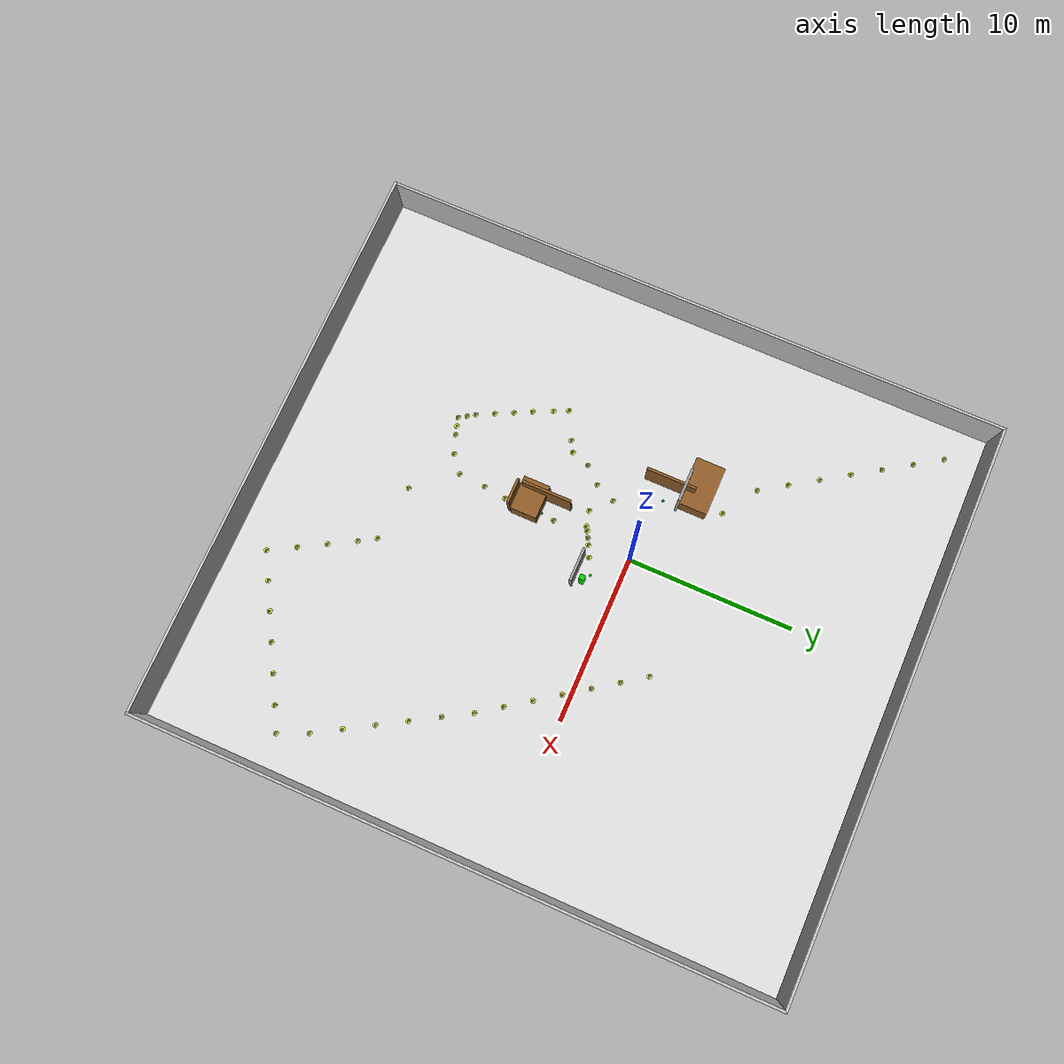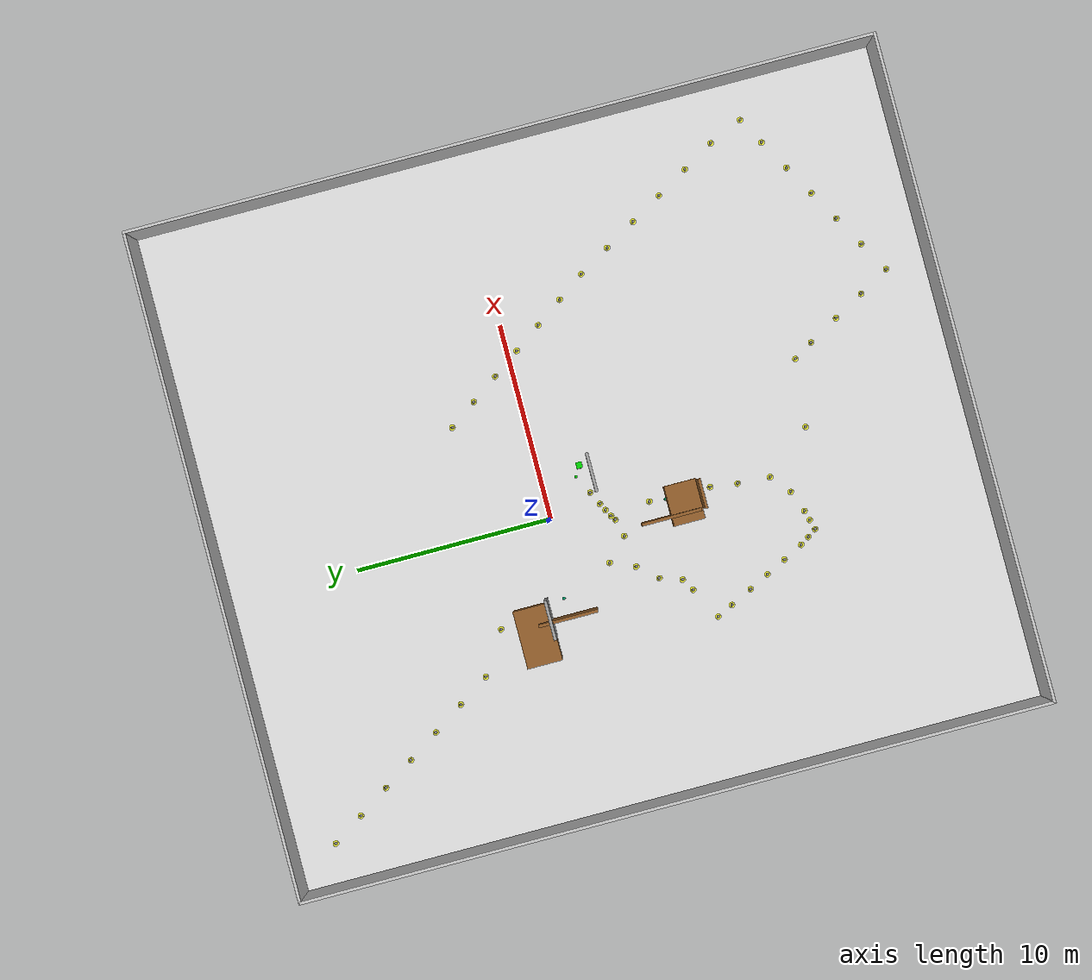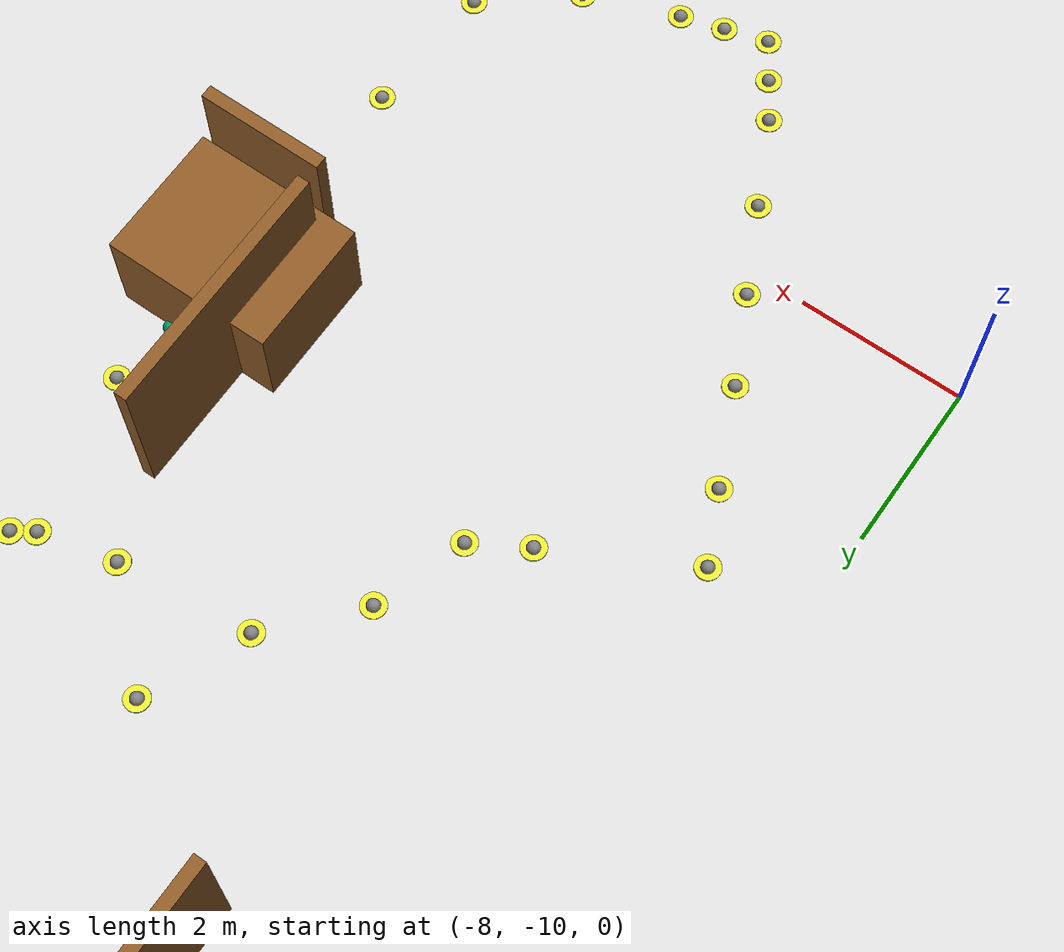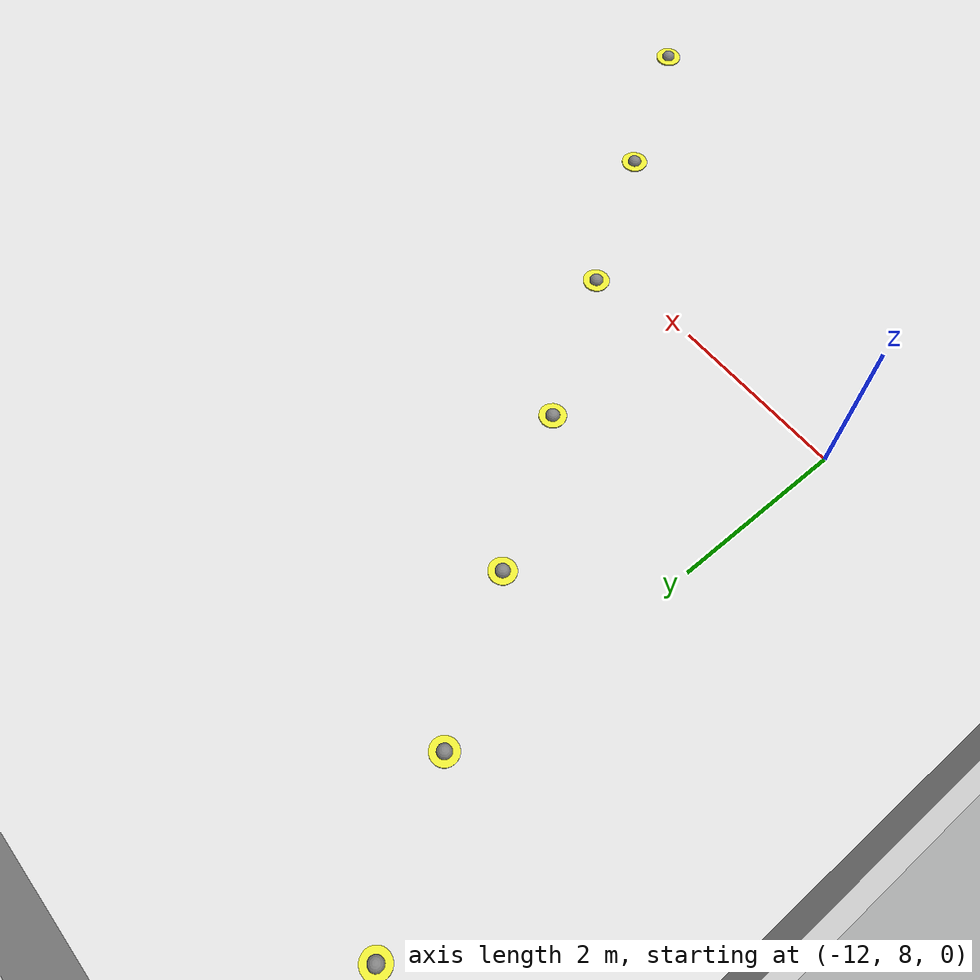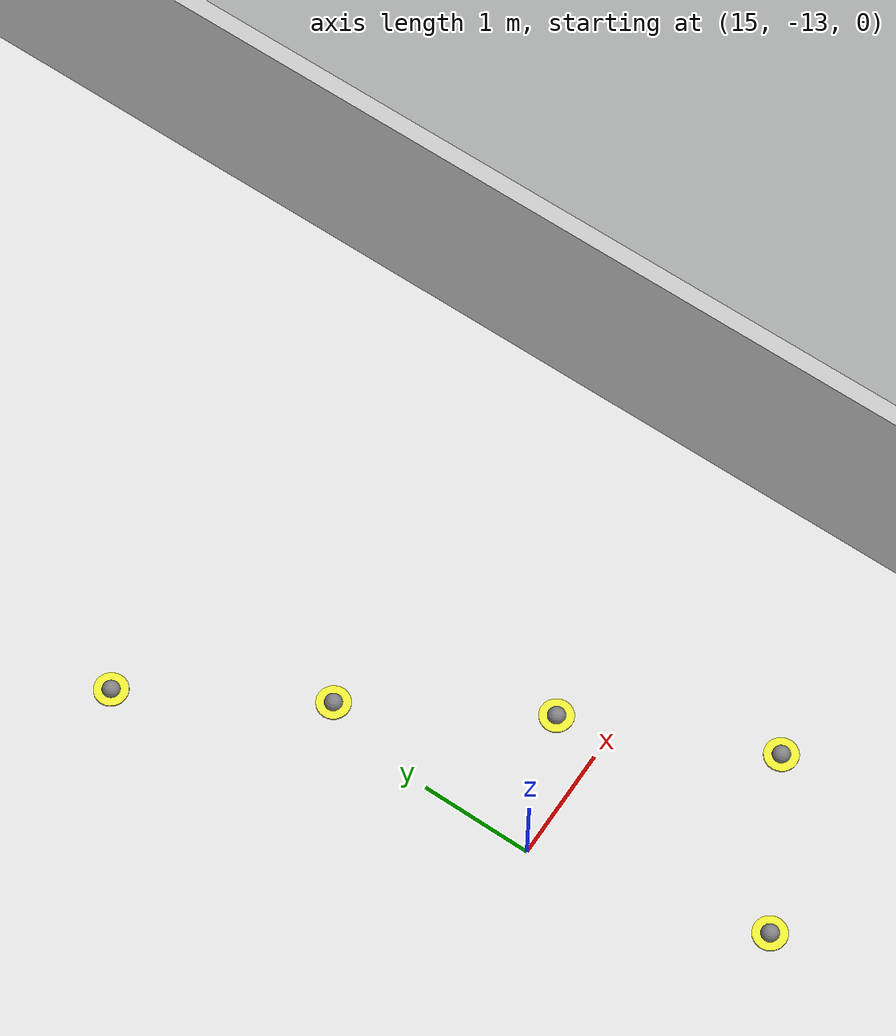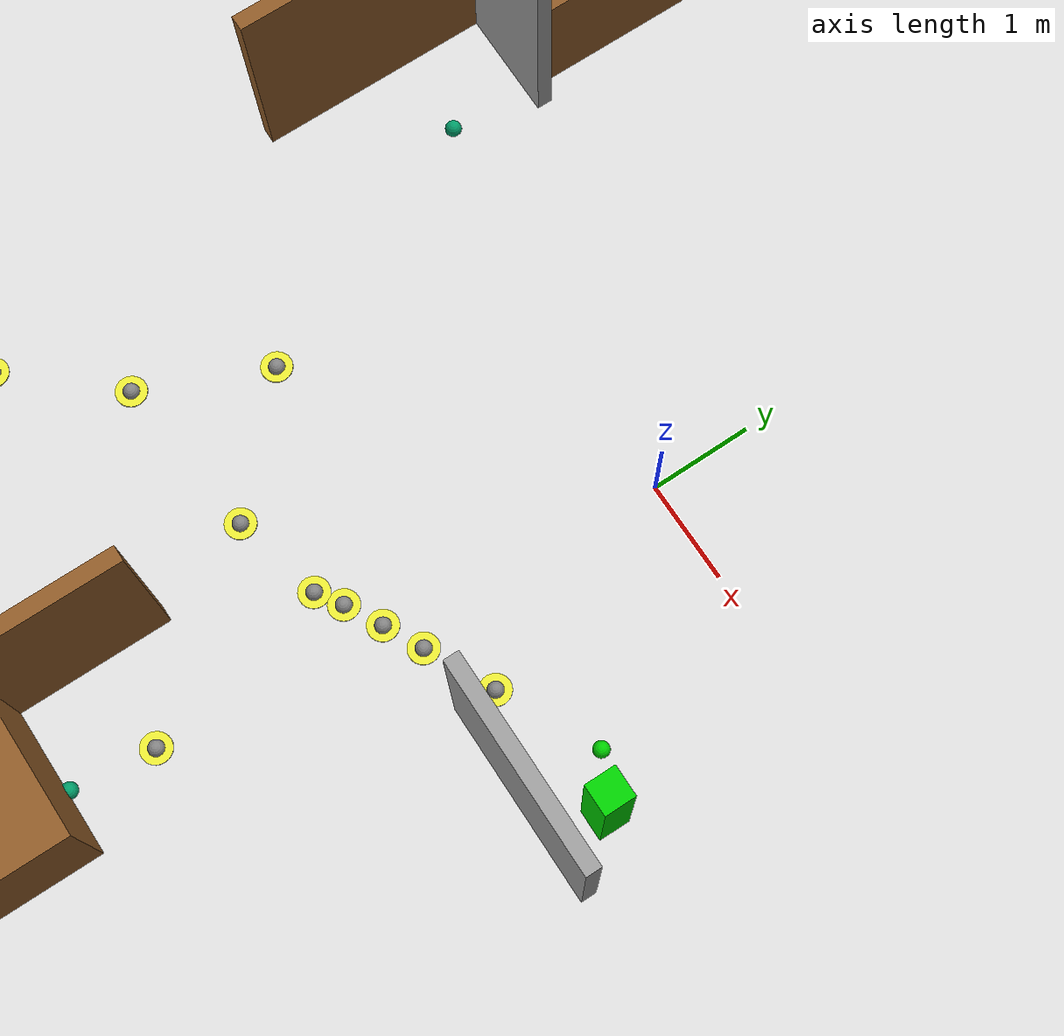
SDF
<?xml version="1.0" ?>
<sdf version="1.9">
  <world name="botvalley">
    <plugin filename="gz-sim-physics-system" name="gz::sim::systems::Physics"/>
    <plugin filename="gz-sim-sensors-system" name="gz::sim::systems::Sensors">
      <render_engine>ogre2</render_engine>
    </plugin>
    <plugin filename="gz-sim-scene-broadcaster-system" name="gz::sim::systems::SceneBroadcaster"/>
    <light name="sun" type="directional">
      <cast_shadows>true</cast_shadows>
      <pose>0 0 10 0 0 0</pose>
      <diffuse>0.8 0.8 0.8 1</diffuse>
      <specular>0.2 0.2 0.2 1</specular>
      <direction>-0.5 0.1 -0.9</direction>
    </light>
    <physics name="default_physics" type="ode">
      <max_step_size>0.001</max_step_size>
      <real_time_factor>1.0</real_time_factor>
      <real_time_update_rate>1000</real_time_update_rate>
    </physics>
    <scene>
      <ambient>0.4 0.4 0.4 1.0</ambient>
      <background>0.7 0.7 0.9 1.0</background>
      <shadows>true</shadows>
    </scene>
    <gravity>0 0 -9.81</gravity>
    <model name="ground_plane">
      <static>true</static>
      <pose>2.006956100463867 -2.43870210647583 0 0 0 0</pose>
      <link name="ground_link">
        <visual name="ground_visual">
          <geometry>
            <box>
              <size>33.73365783691406 37.907999992370605 0.01</size>
            </box>
          </geometry>
          <material>
            <ambient>0.85 0.85 0.85 1.0</ambient>
            <diffuse>0.85 0.85 0.85 1.0</diffuse>
          </material>
        </visual>
        <collision name="ground_visual_collision">
          <geometry>
            <box>
              <size>33.73365783691406 37.907999992370605 0.01</size>
            </box>
          </geometry>
        </collision>
        <collision name="ground_collision">
          <geometry>
            <plane>
              <normal>0 0 1</normal>
              <size>33.73365783691406 37.907999992370605</size>
            </plane>
          </geometry>
        </collision>
      </link>
    </model>
    <model name="wall_north">
      <static>true</static>
      <pose>2.006956100463867 16.515297889709473 1.25 0 0 0</pose>
      <link name="wall_north_link">
        <visual name="wall_north_visual">
          <geometry>
            <box>
              <size>33.88365783691406 0.15 2.5</size>
            </box>
          </geometry>
          <material>
            <ambient>0.75 0.75 0.75 1.0</ambient>
            <diffuse>0.75 0.75 0.75 1.0</diffuse>
          </material>
        </visual>
        <collision name="wall_north_visual_collision">
          <geometry>
            <box>
              <size>33.88365783691406 0.15 2.5</size>
            </box>
          </geometry>
        </collision>
      </link>
    </model>
    <model name="wall_south">
      <static>true</static>
      <pose>2.006956100463867 -21.392702102661133 1.25 0 0 0</pose>
      <link name="wall_south_link">
        <visual name="wall_south_visual">
          <geometry>
            <box>
              <size>33.88365783691406 0.15 2.5</size>
            </box>
          </geometry>
          <material>
            <ambient>0.75 0.75 0.75 1.0</ambient>
            <diffuse>0.75 0.75 0.75 1.0</diffuse>
          </material>
        </visual>
        <collision name="wall_south_visual_collision">
          <geometry>
            <box>
              <size>33.88365783691406 0.15 2.5</size>
            </box>
          </geometry>
        </collision>
      </link>
    </model>
    <model name="wall_east">
      <static>true</static>
      <pose>18.8737850189209 -2.43870210647583 1.25 0 0 0</pose>
      <link name="wall_east_link">
        <visual name="wall_east_visual">
          <geometry>
            <box>
              <size>0.15 38.057999992370604 2.5</size>
            </box>
          </geometry>
          <material>
            <ambient>0.75 0.75 0.75 1.0</ambient>
            <diffuse>0.75 0.75 0.75 1.0</diffuse>
          </material>
        </visual>
        <collision name="wall_east_visual_collision">
          <geometry>
            <box>
              <size>0.15 38.057999992370604 2.5</size>
            </box>
          </geometry>
        </collision>
      </link>
    </model>
    <model name="wall_west">
      <static>true</static>
      <pose>-14.859872817993164 -2.43870210647583 1.25 0 0 0</pose>
      <link name="wall_west_link">
        <visual name="wall_west_visual">
          <geometry>
            <box>
              <size>0.15 38.057999992370604 2.5</size>
            </box>
          </geometry>
          <material>
            <ambient>0.75 0.75 0.75 1.0</ambient>
            <diffuse>0.75 0.75 0.75 1.0</diffuse>
          </material>
        </visual>
        <collision name="wall_west_visual_collision">
          <geometry>
            <box>
              <size>0.15 38.057999992370604 2.5</size>
            </box>
          </geometry>
        </collision>
      </link>
    </model>
    <model name="dock_wall_c1_001">
      <static>true</static>
      <pose>1.7146425247192383 -2.5317887544631956 1.0 0 0 0</pose>
      <link name="dock_wall_c1_001_link">
        <visual name="dock_wall_c1_001_vis">
          <geometry>
            <box>
              <size>2.0 0.15 2.0</size>
            </box>
          </geometry>
          <material>
            <ambient>0.6 0.6 0.6 1.0</ambient>
            <diffuse>0.6 0.6 0.6 1.0</diffuse>
          </material>
        </visual>
        <collision name="dock_wall_c1_001_vis_collision">
          <geometry>
            <box>
              <size>2.0 0.15 2.0</size>
            </box>
          </geometry>
        </collision>
      </link>
    </model>
    <model name="charger_c1_002">
      <static>true</static>
      <pose>2.2146425247192383 -2.0317887544631956 0.75 0 0 0</pose>
      <link name="charger_c1_002_link">
        <visual name="charger_c1_002_vis">
          <geometry>
            <box>
              <size>0.3 0.3 1.5</size>
            </box>
          </geometry>
          <material>
            <ambient>0.0 0.8 0.0 1.0</ambient>
            <diffuse>0.0 0.8 0.0 1.0</diffuse>
          </material>
        </visual>
        <collision name="charger_c1_002_vis_collision">
          <geometry>
            <box>
              <size>0.3 0.3 1.5</size>
            </box>
          </geometry>
        </collision>
      </link>
    </model>
    <model name="cross_k1_003">
      <static>true</static>
      <pose>-1.758684515953064 -3.2982900142669678 0.01 0 0 0</pose>
      <link name="cross_k1_003_link">
        <visual name="cross_k1_003_vis">
          <geometry>
            <cylinder>
              <radius>0.15</radius>
              <length>0.02</length>
            </cylinder>
          </geometry>
          <material>
            <ambient>0.9 0.9 0.2 1.0</ambient>
            <diffuse>0.9 0.9 0.2 1.0</diffuse>
          </material>
        </visual>
        <collision name="cross_k1_003_vis_collision">
          <geometry>
            <cylinder>
              <radius>0.15</radius>
              <length>0.02</length>
            </cylinder>
          </geometry>
        </collision>
      </link>
    </model>
    <model name="cross_k2_004">
      <static>true</static>
      <pose>7.764575958251953 -19.392702102661133 0.01 0 0 0</pose>
      <link name="cross_k2_004_link">
        <visual name="cross_k2_004_vis">
          <geometry>
            <cylinder>
              <radius>0.15</radius>
              <length>0.02</length>
            </cylinder>
          </geometry>
          <material>
            <ambient>0.9 0.9 0.2 1.0</ambient>
            <diffuse>0.9 0.9 0.2 1.0</diffuse>
          </material>
        </visual>
        <collision name="cross_k2_004_vis_collision">
          <geometry>
            <cylinder>
              <radius>0.15</radius>
              <length>0.02</length>
            </cylinder>
          </geometry>
        </collision>
      </link>
    </model>
    <model name="cross_k3_005">
      <static>true</static>
      <pose>16.8737850189209 -14.262846946716309 0.01 0 0 0</pose>
      <link name="cross_k3_005_link">
        <visual name="cross_k3_005_vis">
          <geometry>
            <cylinder>
              <radius>0.15</radius>
              <length>0.02</length>
            </cylinder>
          </geometry>
          <material>
            <ambient>0.9 0.9 0.2 1.0</ambient>
            <diffuse>0.9 0.9 0.2 1.0</diffuse>
          </material>
        </visual>
        <collision name="cross_k3_005_vis_collision">
          <geometry>
            <cylinder>
              <radius>0.15</radius>
              <length>0.02</length>
            </cylinder>
          </geometry>
        </collision>
      </link>
    </model>
    <model name="cross_k4_006">
      <static>true</static>
      <pose>11.452939987182617 -4.5844197273254395 0.01 0 0 0</pose>
      <link name="cross_k4_006_link">
        <visual name="cross_k4_006_vis">
          <geometry>
            <cylinder>
              <radius>0.15</radius>
              <length>0.02</length>
            </cylinder>
          </geometry>
          <material>
            <ambient>0.9 0.9 0.2 1.0</ambient>
            <diffuse>0.9 0.9 0.2 1.0</diffuse>
          </material>
        </visual>
        <collision name="cross_k4_006_vis_collision">
          <geometry>
            <cylinder>
              <radius>0.15</radius>
              <length>0.02</length>
            </cylinder>
          </geometry>
        </collision>
      </link>
    </model>
    <model name="cross_k5_007">
      <static>true</static>
      <pose>5.678647041320801 3.6116576194763184 0.01 0 0 0</pose>
      <link name="cross_k5_007_link">
        <visual name="cross_k5_007_vis">
          <geometry>
            <cylinder>
              <radius>0.15</radius>
              <length>0.02</length>
            </cylinder>
          </geometry>
          <material>
            <ambient>0.9 0.9 0.2 1.0</ambient>
            <diffuse>0.9 0.9 0.2 1.0</diffuse>
          </material>
        </visual>
        <collision name="cross_k5_007_vis_collision">
          <geometry>
            <cylinder>
              <radius>0.15</radius>
              <length>0.02</length>
            </cylinder>
          </geometry>
        </collision>
      </link>
    </model>
    <model name="cross_k7_008">
      <static>true</static>
      <pose>-12.859872817993164 14.515297889709473 0.01 0 0 0</pose>
      <link name="cross_k7_008_link">
        <visual name="cross_k7_008_vis">
          <geometry>
            <cylinder>
              <radius>0.15</radius>
              <length>0.02</length>
            </cylinder>
          </geometry>
          <material>
            <ambient>0.9 0.9 0.2 1.0</ambient>
            <diffuse>0.9 0.9 0.2 1.0</diffuse>
          </material>
        </visual>
        <collision name="cross_k7_008_vis_collision">
          <geometry>
            <cylinder>
              <radius>0.15</radius>
              <length>0.02</length>
            </cylinder>
          </geometry>
        </collision>
      </link>
    </model>
    <model name="cross_k1_k2_1_009">
      <static>true</static>
      <pose>-0.41727715730667114 -4.955166816711426 0.01 0 0 0</pose>
      <link name="cross_k1_k2_1_009_link">
        <visual name="cross_k1_k2_1_009_vis">
          <geometry>
            <cylinder>
              <radius>0.15</radius>
              <length>0.02</length>
            </cylinder>
          </geometry>
          <material>
            <ambient>0.9 0.9 0.2 1.0</ambient>
            <diffuse>0.9 0.9 0.2 1.0</diffuse>
          </material>
        </visual>
        <collision name="cross_k1_k2_1_009_vis_collision">
          <geometry>
            <cylinder>
              <radius>0.15</radius>
              <length>0.02</length>
            </cylinder>
          </geometry>
        </collision>
      </link>
    </model>
    <model name="lane_wall_k1_k2_2_010">
      <static>true</static>
      <pose>-1.409238600730896 -5.767369747161865 1.0 0 0 0</pose>
      <link name="lane_wall_k1_k2_2_010_link">
        <visual name="lane_wall_k1_k2_2_010_vis">
          <geometry>
            <box>
              <size>0.15 3.0 2.0</size>
            </box>
          </geometry>
          <material>
            <ambient>0.55 0.35 0.15 1.0</ambient>
            <diffuse>0.55 0.35 0.15 1.0</diffuse>
          </material>
        </visual>
        <collision name="lane_wall_k1_k2_2_010_vis_collision">
          <geometry>
            <box>
              <size>0.15 3.0 2.0</size>
            </box>
          </geometry>
        </collision>
      </link>
    </model>
    <model name="pick_table_k1_k2_5_011">
      <static>true</static>
      <pose>-0.6911510825157166 -6.122629547119141 0.4 0 0 0</pose>
      <link name="pick_table_k1_k2_5_011_link">
        <visual name="pick_table_k1_k2_5_011_vis">
          <geometry>
            <box>
              <size>1.5 0.5 0.8</size>
            </box>
          </geometry>
          <material>
            <ambient>0.0 0.4 1.0 1.0</ambient>
            <diffuse>0.0 0.4 1.0 1.0</diffuse>
          </material>
        </visual>
        <collision name="pick_table_k1_k2_5_011_vis_collision">
          <geometry>
            <box>
              <size>1.5 0.5 0.8</size>
            </box>
          </geometry>
        </collision>
      </link>
    </model>
    <model name="pick_shelf_k1_k2_5_012">
      <static>true</static>
      <pose>-0.6911510825157166 -7.5226295471191404 1.0 0 0 0</pose>
      <link name="pick_shelf_k1_k2_5_012_link">
        <visual name="pick_shelf_k1_k2_5_012_vis">
          <geometry>
            <box>
              <size>1.5 0.15 2.0</size>
            </box>
          </geometry>
          <material>
            <ambient>0.55 0.35 0.15 1.0</ambient>
            <diffuse>0.55 0.35 0.15 1.0</diffuse>
          </material>
        </visual>
        <collision name="pick_shelf_k1_k2_5_012_vis_collision">
          <geometry>
            <box>
              <size>1.5 0.15 2.0</size>
            </box>
          </geometry>
        </collision>
      </link>
    </model>
    <model name="cross_k1_k2_6_013">
      <static>true</static>
      <pose>1.1738572120666504 -13.458955764770508 0.01 0 0 0</pose>
      <link name="cross_k1_k2_6_013_link">
        <visual name="cross_k1_k2_6_013_vis">
          <geometry>
            <cylinder>
              <radius>0.15</radius>
              <length>0.02</length>
            </cylinder>
          </geometry>
          <material>
            <ambient>0.9 0.9 0.2 1.0</ambient>
            <diffuse>0.9 0.9 0.2 1.0</diffuse>
          </material>
        </visual>
        <collision name="cross_k1_k2_6_013_vis_collision">
          <geometry>
            <cylinder>
              <radius>0.15</radius>
              <length>0.02</length>
            </cylinder>
          </geometry>
        </collision>
      </link>
    </model>
    <model name="cross_k1_k2_7_014">
      <static>true</static>
      <pose>4.595932960510254 -13.846612930297852 0.01 0 0 0</pose>
      <link name="cross_k1_k2_7_014_link">
        <visual name="cross_k1_k2_7_014_vis">
          <geometry>
            <cylinder>
              <radius>0.15</radius>
              <length>0.02</length>
            </cylinder>
          </geometry>
          <material>
            <ambient>0.9 0.9 0.2 1.0</ambient>
            <diffuse>0.9 0.9 0.2 1.0</diffuse>
          </material>
        </visual>
        <collision name="cross_k1_k2_7_014_vis_collision">
          <geometry>
            <cylinder>
              <radius>0.15</radius>
              <length>0.02</length>
            </cylinder>
          </geometry>
        </collision>
      </link>
    </model>
    <model name="cross_k1_k2_8_015">
      <static>true</static>
      <pose>5.18385124206543 -14.81391716003418 0.01 0 0 0</pose>
      <link name="cross_k1_k2_8_015_link">
        <visual name="cross_k1_k2_8_015_vis">
          <geometry>
            <cylinder>
              <radius>0.15</radius>
              <length>0.02</length>
            </cylinder>
          </geometry>
          <material>
            <ambient>0.9 0.9 0.2 1.0</ambient>
            <diffuse>0.9 0.9 0.2 1.0</diffuse>
          </material>
        </visual>
        <collision name="cross_k1_k2_8_015_vis_collision">
          <geometry>
            <cylinder>
              <radius>0.15</radius>
              <length>0.02</length>
            </cylinder>
          </geometry>
        </collision>
      </link>
    </model>
    <model name="cross_k1_k2_9_016">
      <static>true</static>
      <pose>6.044092655181885 -16.340179443359375 0.01 0 0 0</pose>
      <link name="cross_k1_k2_9_016_link">
        <visual name="cross_k1_k2_9_016_vis">
          <geometry>
            <cylinder>
              <radius>0.15</radius>
              <length>0.02</length>
            </cylinder>
          </geometry>
          <material>
            <ambient>0.9 0.9 0.2 1.0</ambient>
            <diffuse>0.9 0.9 0.2 1.0</diffuse>
          </material>
        </visual>
        <collision name="cross_k1_k2_9_016_vis_collision">
          <geometry>
            <cylinder>
              <radius>0.15</radius>
              <length>0.02</length>
            </cylinder>
          </geometry>
        </collision>
      </link>
    </model>
    <model name="cross_k1_k2_10_017">
      <static>true</static>
      <pose>6.904334545135498 -17.866439819335938 0.01 0 0 0</pose>
      <link name="cross_k1_k2_10_017_link">
        <visual name="cross_k1_k2_10_017_vis">
          <geometry>
            <cylinder>
              <radius>0.15</radius>
              <length>0.02</length>
            </cylinder>
          </geometry>
          <material>
            <ambient>0.9 0.9 0.2 1.0</ambient>
            <diffuse>0.9 0.9 0.2 1.0</diffuse>
          </material>
        </visual>
        <collision name="cross_k1_k2_10_017_vis_collision">
          <geometry>
            <cylinder>
              <radius>0.15</radius>
              <length>0.02</length>
            </cylinder>
          </geometry>
        </collision>
      </link>
    </model>
    <model name="cross_k2_k3_1_018">
      <static>true</static>
      <pose>9.314057350158691 -18.516298294067383 0.01 0 0 0</pose>
      <link name="cross_k2_k3_1_018_link">
        <visual name="cross_k2_k3_1_018_vis">
          <geometry>
            <cylinder>
              <radius>0.15</radius>
              <length>0.02</length>
            </cylinder>
          </geometry>
          <material>
            <ambient>0.9 0.9 0.2 1.0</ambient>
            <diffuse>0.9 0.9 0.2 1.0</diffuse>
          </material>
        </visual>
        <collision name="cross_k2_k3_1_018_vis_collision">
          <geometry>
            <cylinder>
              <radius>0.15</radius>
              <length>0.02</length>
            </cylinder>
          </geometry>
        </collision>
      </link>
    </model>
    <model name="cross_k2_k3_2_019">
      <static>true</static>
      <pose>10.86353874206543 -17.639894485473633 0.01 0 0 0</pose>
      <link name="cross_k2_k3_2_019_link">
        <visual name="cross_k2_k3_2_019_vis">
          <geometry>
            <cylinder>
              <radius>0.15</radius>
              <length>0.02</length>
            </cylinder>
          </geometry>
          <material>
            <ambient>0.9 0.9 0.2 1.0</ambient>
            <diffuse>0.9 0.9 0.2 1.0</diffuse>
          </material>
        </visual>
        <collision name="cross_k2_k3_2_019_vis_collision">
          <geometry>
            <cylinder>
              <radius>0.15</radius>
              <length>0.02</length>
            </cylinder>
          </geometry>
        </collision>
      </link>
    </model>
    <model name="cross_k2_k3_3_020">
      <static>true</static>
      <pose>12.413020133972168 -16.763490676879883 0.01 0 0 0</pose>
      <link name="cross_k2_k3_3_020_link">
        <visual name="cross_k2_k3_3_020_vis">
          <geometry>
            <cylinder>
              <radius>0.15</radius>
              <length>0.02</length>
            </cylinder>
          </geometry>
          <material>
            <ambient>0.9 0.9 0.2 1.0</ambient>
            <diffuse>0.9 0.9 0.2 1.0</diffuse>
          </material>
        </visual>
        <collision name="cross_k2_k3_3_020_vis_collision">
          <geometry>
            <cylinder>
              <radius>0.15</radius>
              <length>0.02</length>
            </cylinder>
          </geometry>
        </collision>
      </link>
    </model>
    <model name="cross_k2_k3_4_021">
      <static>true</static>
      <pose>13.962501525878906 -15.887086868286133 0.01 0 0 0</pose>
      <link name="cross_k2_k3_4_021_link">
        <visual name="cross_k2_k3_4_021_vis">
          <geometry>
            <cylinder>
              <radius>0.15</radius>
              <length>0.02</length>
            </cylinder>
          </geometry>
          <material>
            <ambient>0.9 0.9 0.2 1.0</ambient>
            <diffuse>0.9 0.9 0.2 1.0</diffuse>
          </material>
        </visual>
        <collision name="cross_k2_k3_4_021_vis_collision">
          <geometry>
            <cylinder>
              <radius>0.15</radius>
              <length>0.02</length>
            </cylinder>
          </geometry>
        </collision>
      </link>
    </model>
    <model name="cross_k2_k3_5_022">
      <static>true</static>
      <pose>15.511982917785645 -15.010683059692383 0.01 0 0 0</pose>
      <link name="cross_k2_k3_5_022_link">
        <visual name="cross_k2_k3_5_022_vis">
          <geometry>
            <cylinder>
              <radius>0.15</radius>
              <length>0.02</length>
            </cylinder>
          </geometry>
          <material>
            <ambient>0.9 0.9 0.2 1.0</ambient>
            <diffuse>0.9 0.9 0.2 1.0</diffuse>
          </material>
        </visual>
        <collision name="cross_k2_k3_5_022_vis_collision">
          <geometry>
            <cylinder>
              <radius>0.15</radius>
              <length>0.02</length>
            </cylinder>
          </geometry>
        </collision>
      </link>
    </model>
    <model name="cross_k3_k4_1_023">
      <static>true</static>
      <pose>16.126710891723633 -12.542635917663574 0.01 0 0 0</pose>
      <link name="cross_k3_k4_1_023_link">
        <visual name="cross_k3_k4_1_023_vis">
          <geometry>
            <cylinder>
              <radius>0.15</radius>
              <length>0.02</length>
            </cylinder>
          </geometry>
          <material>
            <ambient>0.9 0.9 0.2 1.0</ambient>
            <diffuse>0.9 0.9 0.2 1.0</diffuse>
          </material>
        </visual>
        <collision name="cross_k3_k4_1_023_vis_collision">
          <geometry>
            <cylinder>
              <radius>0.15</radius>
              <length>0.02</length>
            </cylinder>
          </geometry>
        </collision>
      </link>
    </model>
    <model name="cross_k3_k4_2_024">
      <static>true</static>
      <pose>15.191956520080566 -10.950992584228516 0.01 0 0 0</pose>
      <link name="cross_k3_k4_2_024_link">
        <visual name="cross_k3_k4_2_024_vis">
          <geometry>
            <cylinder>
              <radius>0.15</radius>
              <length>0.02</length>
            </cylinder>
          </geometry>
          <material>
            <ambient>0.9 0.9 0.2 1.0</ambient>
            <diffuse>0.9 0.9 0.2 1.0</diffuse>
          </material>
        </visual>
        <collision name="cross_k3_k4_2_024_vis_collision">
          <geometry>
            <cylinder>
              <radius>0.15</radius>
              <length>0.02</length>
            </cylinder>
          </geometry>
        </collision>
      </link>
    </model>
    <model name="cross_k3_k4_3_025">
      <static>true</static>
      <pose>14.2572021484375 -9.359349250793457 0.01 0 0 0</pose>
      <link name="cross_k3_k4_3_025_link">
        <visual name="cross_k3_k4_3_025_vis">
          <geometry>
            <cylinder>
              <radius>0.15</radius>
              <length>0.02</length>
            </cylinder>
          </geometry>
          <material>
            <ambient>0.9 0.9 0.2 1.0</ambient>
            <diffuse>0.9 0.9 0.2 1.0</diffuse>
          </material>
        </visual>
        <collision name="cross_k3_k4_3_025_vis_collision">
          <geometry>
            <cylinder>
              <radius>0.15</radius>
              <length>0.02</length>
            </cylinder>
          </geometry>
        </collision>
      </link>
    </model>
    <model name="cross_k3_k4_4_026">
      <static>true</static>
      <pose>13.32244873046875 -7.767706394195557 0.01 0 0 0</pose>
      <link name="cross_k3_k4_4_026_link">
        <visual name="cross_k3_k4_4_026_vis">
          <geometry>
            <cylinder>
              <radius>0.15</radius>
              <length>0.02</length>
            </cylinder>
          </geometry>
          <material>
            <ambient>0.9 0.9 0.2 1.0</ambient>
            <diffuse>0.9 0.9 0.2 1.0</diffuse>
          </material>
        </visual>
        <collision name="cross_k3_k4_4_026_vis_collision">
          <geometry>
            <cylinder>
              <radius>0.15</radius>
              <length>0.02</length>
            </cylinder>
          </geometry>
        </collision>
      </link>
    </model>
    <model name="cross_k3_k4_5_027">
      <static>true</static>
      <pose>12.387694358825684 -6.176063060760498 0.01 0 0 0</pose>
      <link name="cross_k3_k4_5_027_link">
        <visual name="cross_k3_k4_5_027_vis">
          <geometry>
            <cylinder>
              <radius>0.15</radius>
              <length>0.02</length>
            </cylinder>
          </geometry>
          <material>
            <ambient>0.9 0.9 0.2 1.0</ambient>
            <diffuse>0.9 0.9 0.2 1.0</diffuse>
          </material>
        </visual>
        <collision name="cross_k3_k4_5_027_vis_collision">
          <geometry>
            <cylinder>
              <radius>0.15</radius>
              <length>0.02</length>
            </cylinder>
          </geometry>
        </collision>
      </link>
    </model>
    <model name="cross_k4_k5_1_028">
      <static>true</static>
      <pose>10.490557670593262 -3.218406915664673 0.01 0 0 0</pose>
      <link name="cross_k4_k5_1_028_link">
        <visual name="cross_k4_k5_1_028_vis">
          <geometry>
            <cylinder>
              <radius>0.15</radius>
              <length>0.02</length>
            </cylinder>
          </geometry>
          <material>
            <ambient>0.9 0.9 0.2 1.0</ambient>
            <diffuse>0.9 0.9 0.2 1.0</diffuse>
          </material>
        </visual>
        <collision name="cross_k4_k5_1_028_vis_collision">
          <geometry>
            <cylinder>
              <radius>0.15</radius>
              <length>0.02</length>
            </cylinder>
          </geometry>
        </collision>
      </link>
    </model>
    <model name="cross_k4_k5_2_029">
      <static>true</static>
      <pose>9.528176307678223 -1.8523941040039062 0.01 0 0 0</pose>
      <link name="cross_k4_k5_2_029_link">
        <visual name="cross_k4_k5_2_029_vis">
          <geometry>
            <cylinder>
              <radius>0.15</radius>
              <length>0.02</length>
            </cylinder>
          </geometry>
          <material>
            <ambient>0.9 0.9 0.2 1.0</ambient>
            <diffuse>0.9 0.9 0.2 1.0</diffuse>
          </material>
        </visual>
        <collision name="cross_k4_k5_2_029_vis_collision">
          <geometry>
            <cylinder>
              <radius>0.15</radius>
              <length>0.02</length>
            </cylinder>
          </geometry>
        </collision>
      </link>
    </model>
    <model name="cross_k4_k5_3_030">
      <static>true</static>
      <pose>8.565793991088867 -0.4863811731338501 0.01 0 0 0</pose>
      <link name="cross_k4_k5_3_030_link">
        <visual name="cross_k4_k5_3_030_vis">
          <geometry>
            <cylinder>
              <radius>0.15</radius>
              <length>0.02</length>
            </cylinder>
          </geometry>
          <material>
            <ambient>0.9 0.9 0.2 1.0</ambient>
            <diffuse>0.9 0.9 0.2 1.0</diffuse>
          </material>
        </visual>
        <collision name="cross_k4_k5_3_030_vis_collision">
          <geometry>
            <cylinder>
              <radius>0.15</radius>
              <length>0.02</length>
            </cylinder>
          </geometry>
        </collision>
      </link>
    </model>
    <model name="cross_k4_k5_4_031">
      <static>true</static>
      <pose>7.603411674499512 0.879631757736206 0.01 0 0 0</pose>
      <link name="cross_k4_k5_4_031_link">
        <visual name="cross_k4_k5_4_031_vis">
          <geometry>
            <cylinder>
              <radius>0.15</radius>
              <length>0.02</length>
            </cylinder>
          </geometry>
          <material>
            <ambient>0.9 0.9 0.2 1.0</ambient>
            <diffuse>0.9 0.9 0.2 1.0</diffuse>
          </material>
        </visual>
        <collision name="cross_k4_k5_4_031_vis_collision">
          <geometry>
            <cylinder>
              <radius>0.15</radius>
              <length>0.02</length>
            </cylinder>
          </geometry>
        </collision>
      </link>
    </model>
    <model name="cross_k4_k5_5_032">
      <static>true</static>
      <pose>6.641029357910156 2.2456445693969727 0.01 0 0 0</pose>
      <link name="cross_k4_k5_5_032_link">
        <visual name="cross_k4_k5_5_032_vis">
          <geometry>
            <cylinder>
              <radius>0.15</radius>
              <length>0.02</length>
            </cylinder>
          </geometry>
          <material>
            <ambient>0.9 0.9 0.2 1.0</ambient>
            <diffuse>0.9 0.9 0.2 1.0</diffuse>
          </material>
        </visual>
        <collision name="cross_k4_k5_5_032_vis_collision">
          <geometry>
            <cylinder>
              <radius>0.15</radius>
              <length>0.02</length>
            </cylinder>
          </geometry>
        </collision>
      </link>
    </model>
    <model name="cross_k7_k1_1_033">
      <static>true</static>
      <pose>-11.845165252685547 12.959014892578125 0.01 0 0 0</pose>
      <link name="cross_k7_k1_1_033_link">
        <visual name="cross_k7_k1_1_033_vis">
          <geometry>
            <cylinder>
              <radius>0.15</radius>
              <length>0.02</length>
            </cylinder>
          </geometry>
          <material>
            <ambient>0.9 0.9 0.2 1.0</ambient>
            <diffuse>0.9 0.9 0.2 1.0</diffuse>
          </material>
        </visual>
        <collision name="cross_k7_k1_1_033_vis_collision">
          <geometry>
            <cylinder>
              <radius>0.15</radius>
              <length>0.02</length>
            </cylinder>
          </geometry>
        </collision>
      </link>
    </model>
    <model name="cross_k7_k1_2_034">
      <static>true</static>
      <pose>-10.830456733703613 11.402730941772461 0.01 0 0 0</pose>
      <link name="cross_k7_k1_2_034_link">
        <visual name="cross_k7_k1_2_034_vis">
          <geometry>
            <cylinder>
              <radius>0.15</radius>
              <length>0.02</length>
            </cylinder>
          </geometry>
          <material>
            <ambient>0.9 0.9 0.2 1.0</ambient>
            <diffuse>0.9 0.9 0.2 1.0</diffuse>
          </material>
        </visual>
        <collision name="cross_k7_k1_2_034_vis_collision">
          <geometry>
            <cylinder>
              <radius>0.15</radius>
              <length>0.02</length>
            </cylinder>
          </geometry>
        </collision>
      </link>
    </model>
    <model name="cross_k7_k1_3_035">
      <static>true</static>
      <pose>-9.81574821472168 9.846446990966797 0.01 0 0 0</pose>
      <link name="cross_k7_k1_3_035_link">
        <visual name="cross_k7_k1_3_035_vis">
          <geometry>
            <cylinder>
              <radius>0.15</radius>
              <length>0.02</length>
            </cylinder>
          </geometry>
          <material>
            <ambient>0.9 0.9 0.2 1.0</ambient>
            <diffuse>0.9 0.9 0.2 1.0</diffuse>
          </material>
        </visual>
        <collision name="cross_k7_k1_3_035_vis_collision">
          <geometry>
            <cylinder>
              <radius>0.15</radius>
              <length>0.02</length>
            </cylinder>
          </geometry>
        </collision>
      </link>
    </model>
    <model name="cross_k7_k1_4_036">
      <static>true</static>
      <pose>-8.801039695739746 8.290163040161133 0.01 0 0 0</pose>
      <link name="cross_k7_k1_4_036_link">
        <visual name="cross_k7_k1_4_036_vis">
          <geometry>
            <cylinder>
              <radius>0.15</radius>
              <length>0.02</length>
            </cylinder>
          </geometry>
          <material>
            <ambient>0.9 0.9 0.2 1.0</ambient>
            <diffuse>0.9 0.9 0.2 1.0</diffuse>
          </material>
        </visual>
        <collision name="cross_k7_k1_4_036_vis_collision">
          <geometry>
            <cylinder>
              <radius>0.15</radius>
              <length>0.02</length>
            </cylinder>
          </geometry>
        </collision>
      </link>
    </model>
    <model name="cross_k7_k1_5_037">
      <static>true</static>
      <pose>-7.786331653594971 6.733879089355469 0.01 0 0 0</pose>
      <link name="cross_k7_k1_5_037_link">
        <visual name="cross_k7_k1_5_037_vis">
          <geometry>
            <cylinder>
              <radius>0.15</radius>
              <length>0.02</length>
            </cylinder>
          </geometry>
          <material>
            <ambient>0.9 0.9 0.2 1.0</ambient>
            <diffuse>0.9 0.9 0.2 1.0</diffuse>
          </material>
        </visual>
        <collision name="cross_k7_k1_5_037_vis_collision">
          <geometry>
            <cylinder>
              <radius>0.15</radius>
              <length>0.02</length>
            </cylinder>
          </geometry>
        </collision>
      </link>
    </model>
    <model name="cross_k7_k1_6_038">
      <static>true</static>
      <pose>-6.771623134613037 5.177595615386963 0.01 0 0 0</pose>
      <link name="cross_k7_k1_6_038_link">
        <visual name="cross_k7_k1_6_038_vis">
          <geometry>
            <cylinder>
              <radius>0.15</radius>
              <length>0.02</length>
            </cylinder>
          </geometry>
          <material>
            <ambient>0.9 0.9 0.2 1.0</ambient>
            <diffuse>0.9 0.9 0.2 1.0</diffuse>
          </material>
        </visual>
        <collision name="cross_k7_k1_6_038_vis_collision">
          <geometry>
            <cylinder>
              <radius>0.15</radius>
              <length>0.02</length>
            </cylinder>
          </geometry>
        </collision>
      </link>
    </model>
    <model name="cross_k7_k1_7_039">
      <static>true</static>
      <pose>-4.678679943084717 3.8304426670074463 0.01 0 0 0</pose>
      <link name="cross_k7_k1_7_039_link">
        <visual name="cross_k7_k1_7_039_vis">
          <geometry>
            <cylinder>
              <radius>0.15</radius>
              <length>0.02</length>
            </cylinder>
          </geometry>
          <material>
            <ambient>0.9 0.9 0.2 1.0</ambient>
            <diffuse>0.9 0.9 0.2 1.0</diffuse>
          </material>
        </visual>
        <collision name="cross_k7_k1_7_039_vis_collision">
          <geometry>
            <cylinder>
              <radius>0.15</radius>
              <length>0.02</length>
            </cylinder>
          </geometry>
        </collision>
      </link>
    </model>
    <model name="drop_conv_k7_k1_8_040">
      <static>true</static>
      <pose>-4.742206573486328 2.465027952194214 0.4 0 0 0</pose>
      <link name="drop_conv_k7_k1_8_040_link">
        <visual name="drop_conv_k7_k1_8_040_vis">
          <geometry>
            <box>
              <size>1.5 0.5 0.8</size>
            </box>
          </geometry>
          <material>
            <ambient>1.0 0.4 0.0 1.0</ambient>
            <diffuse>1.0 0.4 0.0 1.0</diffuse>
          </material>
        </visual>
        <collision name="drop_conv_k7_k1_8_040_vis_collision">
          <geometry>
            <box>
              <size>1.5 0.5 0.8</size>
            </box>
          </geometry>
        </collision>
      </link>
    </model>
    <model name="drop_wall_k7_k1_8_041">
      <static>true</static>
      <pose>-4.742206573486328 1.2650279521942138 1.25 0 0 0</pose>
      <link name="drop_wall_k7_k1_8_041_link">
        <visual name="drop_wall_k7_k1_8_041_vis">
          <geometry>
            <box>
              <size>2.0 0.15 2.5</size>
            </box>
          </geometry>
          <material>
            <ambient>0.6 0.6 0.6 1.0</ambient>
            <diffuse>0.6 0.6 0.6 1.0</diffuse>
          </material>
        </visual>
        <collision name="drop_wall_k7_k1_8_041_vis_collision">
          <geometry>
            <box>
              <size>2.0 0.15 2.5</size>
            </box>
          </geometry>
        </collision>
      </link>
    </model>
    <model name="lane_wall_k7_k1_9_042">
      <static>true</static>
      <pose>-4.9 0.4 1.0 0 0 0</pose>
      <link name="lane_wall_k7_k1_9_042_link">
        <visual name="lane_wall_k7_k1_9_042_vis">
          <geometry>
            <box>
              <size>0.15 3.0 2.0</size>
            </box>
          </geometry>
          <material>
            <ambient>0.55 0.35 0.15 1.0</ambient>
            <diffuse>0.55 0.35 0.15 1.0</diffuse>
          </material>
        </visual>
        <collision name="lane_wall_k7_k1_9_042_vis_collision">
          <geometry>
            <box>
              <size>0.15 3.0 2.0</size>
            </box>
          </geometry>
        </collision>
      </link>
    </model>
    <model name="cross_k7_k1_10_043">
      <static>true</static>
      <pose>-2.8607993125915527 -2.2503156661987305 0.01 0 0 0</pose>
      <link name="cross_k7_k1_10_043_link">
        <visual name="cross_k7_k1_10_043_vis">
          <geometry>
            <cylinder>
              <radius>0.15</radius>
              <length>0.02</length>
            </cylinder>
          </geometry>
          <material>
            <ambient>0.9 0.9 0.2 1.0</ambient>
            <diffuse>0.9 0.9 0.2 1.0</diffuse>
          </material>
        </visual>
        <collision name="cross_k7_k1_10_043_vis_collision">
          <geometry>
            <cylinder>
              <radius>0.15</radius>
              <length>0.02</length>
            </cylinder>
          </geometry>
        </collision>
      </link>
    </model>
    <model name="cross_c1_k1_1_044">
      <static>true</static>
      <pose>0.7685220241546631 -2.213562250137329 0.01 0 0 0</pose>
      <link name="cross_c1_k1_1_044_link">
        <visual name="cross_c1_k1_1_044_vis">
          <geometry>
            <cylinder>
              <radius>0.15</radius>
              <length>0.02</length>
            </cylinder>
          </geometry>
          <material>
            <ambient>0.9 0.9 0.2 1.0</ambient>
            <diffuse>0.9 0.9 0.2 1.0</diffuse>
          </material>
        </visual>
        <collision name="cross_c1_k1_1_044_vis_collision">
          <geometry>
            <cylinder>
              <radius>0.15</radius>
              <length>0.02</length>
            </cylinder>
          </geometry>
        </collision>
      </link>
    </model>
    <model name="cross_c1_k1_2_045">
      <static>true</static>
      <pose>0.10828320682048798 -2.5398871898651123 0.01 0 0 0</pose>
      <link name="cross_c1_k1_2_045_link">
        <visual name="cross_c1_k1_2_045_vis">
          <geometry>
            <cylinder>
              <radius>0.15</radius>
              <length>0.02</length>
            </cylinder>
          </geometry>
          <material>
            <ambient>0.9 0.9 0.2 1.0</ambient>
            <diffuse>0.9 0.9 0.2 1.0</diffuse>
          </material>
        </visual>
        <collision name="cross_c1_k1_2_045_vis_collision">
          <geometry>
            <cylinder>
              <radius>0.15</radius>
              <length>0.02</length>
            </cylinder>
          </geometry>
        </collision>
      </link>
    </model>
    <model name="cross_c1_k1_3_046">
      <static>true</static>
      <pose>-0.2635754346847534 -2.7296109199523926 0.01 0 0 0</pose>
      <link name="cross_c1_k1_3_046_link">
        <visual name="cross_c1_k1_3_046_vis">
          <geometry>
            <cylinder>
              <radius>0.15</radius>
              <length>0.02</length>
            </cylinder>
          </geometry>
          <material>
            <ambient>0.9 0.9 0.2 1.0</ambient>
            <diffuse>0.9 0.9 0.2 1.0</diffuse>
          </material>
        </visual>
        <collision name="cross_c1_k1_3_046_vis_collision">
          <geometry>
            <cylinder>
              <radius>0.15</radius>
              <length>0.02</length>
            </cylinder>
          </geometry>
        </collision>
      </link>
    </model>
    <model name="cross_c1_k1_4_047">
      <static>true</static>
      <pose>-0.6126672625541687 -2.919334888458252 0.01 0 0 0</pose>
      <link name="cross_c1_k1_4_047_link">
        <visual name="cross_c1_k1_4_047_vis">
          <geometry>
            <cylinder>
              <radius>0.15</radius>
              <length>0.02</length>
            </cylinder>
          </geometry>
          <material>
            <ambient>0.9 0.9 0.2 1.0</ambient>
            <diffuse>0.9 0.9 0.2 1.0</diffuse>
          </material>
        </visual>
        <collision name="cross_c1_k1_4_047_vis_collision">
          <geometry>
            <cylinder>
              <radius>0.15</radius>
              <length>0.02</length>
            </cylinder>
          </geometry>
        </collision>
      </link>
    </model>
    <model name="cross_c1_k1_5_048">
      <static>true</static>
      <pose>-0.8555136919021606 -3.078702688217163 0.01 0 0 0</pose>
      <link name="cross_c1_k1_5_048_link">
        <visual name="cross_c1_k1_5_048_vis">
          <geometry>
            <cylinder>
              <radius>0.15</radius>
              <length>0.02</length>
            </cylinder>
          </geometry>
          <material>
            <ambient>0.9 0.9 0.2 1.0</ambient>
            <diffuse>0.9 0.9 0.2 1.0</diffuse>
          </material>
        </visual>
        <collision name="cross_c1_k1_5_048_vis_collision">
          <geometry>
            <cylinder>
              <radius>0.15</radius>
              <length>0.02</length>
            </cylinder>
          </geometry>
        </collision>
      </link>
    </model>
    <model name="cross_o1_new_w2_2_049">
      <static>true</static>
      <pose>-5.233762264251709 -5.931482791900635 0.01 0 0 0</pose>
      <link name="cross_o1_new_w2_2_049_link">
        <visual name="cross_o1_new_w2_2_049_vis">
          <geometry>
            <cylinder>
              <radius>0.15</radius>
              <length>0.02</length>
            </cylinder>
          </geometry>
          <material>
            <ambient>0.9 0.9 0.2 1.0</ambient>
            <diffuse>0.9 0.9 0.2 1.0</diffuse>
          </material>
        </visual>
        <collision name="cross_o1_new_w2_2_049_vis_collision">
          <geometry>
            <cylinder>
              <radius>0.15</radius>
              <length>0.02</length>
            </cylinder>
          </geometry>
        </collision>
      </link>
    </model>
    <model name="cross_o1_new_w2_3_050">
      <static>true</static>
      <pose>-4.609227180480957 -5.558860778808594 0.01 0 0 0</pose>
      <link name="cross_o1_new_w2_3_050_link">
        <visual name="cross_o1_new_w2_3_050_vis">
          <geometry>
            <cylinder>
              <radius>0.15</radius>
              <length>0.02</length>
            </cylinder>
          </geometry>
          <material>
            <ambient>0.9 0.9 0.2 1.0</ambient>
            <diffuse>0.9 0.9 0.2 1.0</diffuse>
          </material>
        </visual>
        <collision name="cross_o1_new_w2_3_050_vis_collision">
          <geometry>
            <cylinder>
              <radius>0.15</radius>
              <length>0.02</length>
            </cylinder>
          </geometry>
        </collision>
      </link>
    </model>
    <model name="cross_o1_new_w2_4_051">
      <static>true</static>
      <pose>-4.24013090133667 -4.4496893882751465 0.01 0 0 0</pose>
      <link name="cross_o1_new_w2_4_051_link">
        <visual name="cross_o1_new_w2_4_051_vis">
          <geometry>
            <cylinder>
              <radius>0.15</radius>
              <length>0.02</length>
            </cylinder>
          </geometry>
          <material>
            <ambient>0.9 0.9 0.2 1.0</ambient>
            <diffuse>0.9 0.9 0.2 1.0</diffuse>
          </material>
        </visual>
        <collision name="cross_o1_new_w2_4_051_vis_collision">
          <geometry>
            <cylinder>
              <radius>0.15</radius>
              <length>0.02</length>
            </cylinder>
          </geometry>
        </collision>
      </link>
    </model>
    <model name="cross_o1_new_w2_5_052">
      <static>true</static>
      <pose>-3.3851330280303955 -3.482191562652588 0.01 0 0 0</pose>
      <link name="cross_o1_new_w2_5_052_link">
        <visual name="cross_o1_new_w2_5_052_vis">
          <geometry>
            <cylinder>
              <radius>0.15</radius>
              <length>0.02</length>
            </cylinder>
          </geometry>
          <material>
            <ambient>0.9 0.9 0.2 1.0</ambient>
            <diffuse>0.9 0.9 0.2 1.0</diffuse>
          </material>
        </visual>
        <collision name="cross_o1_new_w2_5_052_vis_collision">
          <geometry>
            <cylinder>
              <radius>0.15</radius>
              <length>0.02</length>
            </cylinder>
          </geometry>
        </collision>
      </link>
    </model>
    <model name="cross_o1_new_o2_new_2_053">
      <static>true</static>
      <pose>-5.946850776672363 -8.71485710144043 0.01 0 0 0</pose>
      <link name="cross_o1_new_o2_new_2_053_link">
        <visual name="cross_o1_new_o2_new_2_053_vis">
          <geometry>
            <cylinder>
              <radius>0.15</radius>
              <length>0.02</length>
            </cylinder>
          </geometry>
          <material>
            <ambient>0.9 0.9 0.2 1.0</ambient>
            <diffuse>0.9 0.9 0.2 1.0</diffuse>
          </material>
        </visual>
        <collision name="cross_o1_new_o2_new_2_053_vis_collision">
          <geometry>
            <cylinder>
              <radius>0.15</radius>
              <length>0.02</length>
            </cylinder>
          </geometry>
        </collision>
      </link>
    </model>
    <model name="cross_o1_new_o2_new_3_054">
      <static>true</static>
      <pose>-5.448122978210449 -9.719094276428223 0.01 0 0 0</pose>
      <link name="cross_o1_new_o2_new_3_054_link">
        <visual name="cross_o1_new_o2_new_3_054_vis">
          <geometry>
            <cylinder>
              <radius>0.15</radius>
              <length>0.02</length>
            </cylinder>
          </geometry>
          <material>
            <ambient>0.9 0.9 0.2 1.0</ambient>
            <diffuse>0.9 0.9 0.2 1.0</diffuse>
          </material>
        </visual>
        <collision name="cross_o1_new_o2_new_3_054_vis_collision">
          <geometry>
            <cylinder>
              <radius>0.15</radius>
              <length>0.02</length>
            </cylinder>
          </geometry>
        </collision>
      </link>
    </model>
    <model name="cross_o1_new_o2_new_4_055">
      <static>true</static>
      <pose>-4.949395179748535 -10.7233304977417 0.01 0 0 0</pose>
      <link name="cross_o1_new_o2_new_4_055_link">
        <visual name="cross_o1_new_o2_new_4_055_vis">
          <geometry>
            <cylinder>
              <radius>0.15</radius>
              <length>0.02</length>
            </cylinder>
          </geometry>
          <material>
            <ambient>0.9 0.9 0.2 1.0</ambient>
            <diffuse>0.9 0.9 0.2 1.0</diffuse>
          </material>
        </visual>
        <collision name="cross_o1_new_o2_new_4_055_vis_collision">
          <geometry>
            <cylinder>
              <radius>0.15</radius>
              <length>0.02</length>
            </cylinder>
          </geometry>
        </collision>
      </link>
    </model>
    <model name="cross_o1_new_o2_new_5_056">
      <static>true</static>
      <pose>-4.450667381286621 -11.727567672729492 0.01 0 0 0</pose>
      <link name="cross_o1_new_o2_new_5_056_link">
        <visual name="cross_o1_new_o2_new_5_056_vis">
          <geometry>
            <cylinder>
              <radius>0.15</radius>
              <length>0.02</length>
            </cylinder>
          </geometry>
          <material>
            <ambient>0.9 0.9 0.2 1.0</ambient>
            <diffuse>0.9 0.9 0.2 1.0</diffuse>
          </material>
        </visual>
        <collision name="cross_o1_new_o2_new_5_056_vis_collision">
          <geometry>
            <cylinder>
              <radius>0.15</radius>
              <length>0.02</length>
            </cylinder>
          </geometry>
        </collision>
      </link>
    </model>
    <model name="cross_o2_new_k1_k2_5_1_057">
      <static>true</static>
      <pose>-2.859428882598877 -12.315691947937012 0.01 0 0 0</pose>
      <link name="cross_o2_new_k1_k2_5_1_057_link">
        <visual name="cross_o2_new_k1_k2_5_1_057_vis">
          <geometry>
            <cylinder>
              <radius>0.15</radius>
              <length>0.02</length>
            </cylinder>
          </geometry>
          <material>
            <ambient>0.9 0.9 0.2 1.0</ambient>
            <diffuse>0.9 0.9 0.2 1.0</diffuse>
          </material>
        </visual>
        <collision name="cross_o2_new_k1_k2_5_1_057_vis_collision">
          <geometry>
            <cylinder>
              <radius>0.15</radius>
              <length>0.02</length>
            </cylinder>
          </geometry>
        </collision>
      </link>
    </model>
    <model name="cross_o2_new_k1_k2_5_2_058">
      <static>true</static>
      <pose>-1.7669177055358887 -11.899580001831055 0.01 0 0 0</pose>
      <link name="cross_o2_new_k1_k2_5_2_058_link">
        <visual name="cross_o2_new_k1_k2_5_2_058_vis">
          <geometry>
            <cylinder>
              <radius>0.15</radius>
              <length>0.02</length>
            </cylinder>
          </geometry>
          <material>
            <ambient>0.9 0.9 0.2 1.0</ambient>
            <diffuse>0.9 0.9 0.2 1.0</diffuse>
          </material>
        </visual>
        <collision name="cross_o2_new_k1_k2_5_2_058_vis_collision">
          <geometry>
            <cylinder>
              <radius>0.15</radius>
              <length>0.02</length>
            </cylinder>
          </geometry>
        </collision>
      </link>
    </model>
    <model name="cross_o2_new_k1_k2_5_3_059">
      <static>true</static>
      <pose>-0.787115752696991 -11.096843719482422 0.01 0 0 0</pose>
      <link name="cross_o2_new_k1_k2_5_3_059_link">
        <visual name="cross_o2_new_k1_k2_5_3_059_vis">
          <geometry>
            <cylinder>
              <radius>0.15</radius>
              <length>0.02</length>
            </cylinder>
          </geometry>
          <material>
            <ambient>0.9 0.9 0.2 1.0</ambient>
            <diffuse>0.9 0.9 0.2 1.0</diffuse>
          </material>
        </visual>
        <collision name="cross_o2_new_k1_k2_5_3_059_vis_collision">
          <geometry>
            <cylinder>
              <radius>0.15</radius>
              <length>0.02</length>
            </cylinder>
          </geometry>
        </collision>
      </link>
    </model>
    <model name="cross_o2_new_k1_k2_5_4_060">
      <static>true</static>
      <pose>-0.6764636635780334 -9.44577407836914 0.01 0 0 0</pose>
      <link name="cross_o2_new_k1_k2_5_4_060_link">
        <visual name="cross_o2_new_k1_k2_5_4_060_vis">
          <geometry>
            <cylinder>
              <radius>0.15</radius>
              <length>0.02</length>
            </cylinder>
          </geometry>
          <material>
            <ambient>0.9 0.9 0.2 1.0</ambient>
            <diffuse>0.9 0.9 0.2 1.0</diffuse>
          </material>
        </visual>
        <collision name="cross_o2_new_k1_k2_5_4_060_vis_collision">
          <geometry>
            <cylinder>
              <radius>0.15</radius>
              <length>0.02</length>
            </cylinder>
          </geometry>
        </collision>
      </link>
    </model>
    <model name="cross_o2_new_k1_k2_5_5_061">
      <static>true</static>
      <pose>-0.49914029240608215 -8.072136878967285 0.01 0 0 0</pose>
      <link name="cross_o2_new_k1_k2_5_5_061_link">
        <visual name="cross_o2_new_k1_k2_5_5_061_vis">
          <geometry>
            <cylinder>
              <radius>0.15</radius>
              <length>0.02</length>
            </cylinder>
          </geometry>
          <material>
            <ambient>0.9 0.9 0.2 1.0</ambient>
            <diffuse>0.9 0.9 0.2 1.0</diffuse>
          </material>
        </visual>
        <collision name="cross_o2_new_k1_k2_5_5_061_vis_collision">
          <geometry>
            <cylinder>
              <radius>0.15</radius>
              <length>0.02</length>
            </cylinder>
          </geometry>
        </collision>
      </link>
    </model>
    <model name="cross_o1_new_062">
      <static>true</static>
      <pose>-6.8502068519592285 -6.797435283660889 0.01 0 0 0</pose>
      <link name="cross_o1_new_062_link">
        <visual name="cross_o1_new_062_vis">
          <geometry>
            <cylinder>
              <radius>0.15</radius>
              <length>0.02</length>
            </cylinder>
          </geometry>
          <material>
            <ambient>0.9 0.9 0.2 1.0</ambient>
            <diffuse>0.9 0.9 0.2 1.0</diffuse>
          </material>
        </visual>
        <collision name="cross_o1_new_062_vis_collision">
          <geometry>
            <cylinder>
              <radius>0.15</radius>
              <length>0.02</length>
            </cylinder>
          </geometry>
        </collision>
      </link>
    </model>
    <model name="cross_o2_new_063">
      <static>true</static>
      <pose>-3.87721586227417 -12.606410026550293 0.01 0 0 0</pose>
      <link name="cross_o2_new_063_link">
        <visual name="cross_o2_new_063_vis">
          <geometry>
            <cylinder>
              <radius>0.15</radius>
              <length>0.02</length>
            </cylinder>
          </geometry>
          <material>
            <ambient>0.9 0.9 0.2 1.0</ambient>
            <diffuse>0.9 0.9 0.2 1.0</diffuse>
          </material>
        </visual>
        <collision name="cross_o2_new_063_vis_collision">
          <geometry>
            <cylinder>
              <radius>0.15</radius>
              <length>0.02</length>
            </cylinder>
          </geometry>
        </collision>
      </link>
    </model>
    <model name="cross_o2_new_o1_new_o2_new_5_1_064">
      <static>true</static>
      <pose>-4.163941860198975 -12.16698932647705 0.01 0 0 0</pose>
      <link name="cross_o2_new_o1_new_o2_new_5_1_064_link">
        <visual name="cross_o2_new_o1_new_o2_new_5_1_064_vis">
          <geometry>
            <cylinder>
              <radius>0.15</radius>
              <length>0.02</length>
            </cylinder>
          </geometry>
          <material>
            <ambient>0.9 0.9 0.2 1.0</ambient>
            <diffuse>0.9 0.9 0.2 1.0</diffuse>
          </material>
        </visual>
        <collision name="cross_o2_new_o1_new_o2_new_5_1_064_vis_collision">
          <geometry>
            <cylinder>
              <radius>0.15</radius>
              <length>0.02</length>
            </cylinder>
          </geometry>
        </collision>
      </link>
    </model>
    <model name="cross_o2_new_o2_new_k1_k2_5_1_1_065">
      <static>true</static>
      <pose>-3.3683223724365234 -12.461050987243652 0.01 0 0 0</pose>
      <link name="cross_o2_new_o2_new_k1_k2_5_1_1_065_link">
        <visual name="cross_o2_new_o2_new_k1_k2_5_1_1_065_vis">
          <geometry>
            <cylinder>
              <radius>0.15</radius>
              <length>0.02</length>
            </cylinder>
          </geometry>
          <material>
            <ambient>0.9 0.9 0.2 1.0</ambient>
            <diffuse>0.9 0.9 0.2 1.0</diffuse>
          </material>
        </visual>
        <collision name="cross_o2_new_o2_new_k1_k2_5_1_1_065_vis_collision">
          <geometry>
            <cylinder>
              <radius>0.15</radius>
              <length>0.02</length>
            </cylinder>
          </geometry>
        </collision>
      </link>
    </model>
    <model name="cross_o1_new_o1_new_o2_new_2_1_066">
      <static>true</static>
      <pose>-6.459879398345947 -7.608238220214844 0.01 0 0 0</pose>
      <link name="cross_o1_new_o1_new_o2_new_2_1_066_link">
        <visual name="cross_o1_new_o1_new_o2_new_2_1_066_vis">
          <geometry>
            <cylinder>
              <radius>0.15</radius>
              <length>0.02</length>
            </cylinder>
          </geometry>
          <material>
            <ambient>0.9 0.9 0.2 1.0</ambient>
            <diffuse>0.9 0.9 0.2 1.0</diffuse>
          </material>
        </visual>
        <collision name="cross_o1_new_o1_new_o2_new_2_1_066_vis_collision">
          <geometry>
            <cylinder>
              <radius>0.15</radius>
              <length>0.02</length>
            </cylinder>
          </geometry>
        </collision>
      </link>
    </model>
    <model name="zone_ZoneA_067">
      <static>true</static>
      <pose>-5.395 2.11 0.6 0 0 0</pose>
      <link name="zone_ZoneA_067_link">
        <visual name="zone_ZoneA_067_vis">
          <geometry>
            <box>
              <size>2.9099999999999997 1.78 1.2</size>
            </box>
          </geometry>
          <material>
            <ambient>0.55 0.35 0.15 1.0</ambient>
            <diffuse>0.55 0.35 0.15 1.0</diffuse>
          </material>
        </visual>
        <collision name="zone_ZoneA_067_vis_collision">
          <geometry>
            <box>
              <size>2.9099999999999997 1.78 1.2</size>
            </box>
          </geometry>
        </collision>
      </link>
    </model>
    <model name="zone_ZoneB_068">
      <static>true</static>
      <pose>-0.895 -6.59 0.6 0 0 0</pose>
      <link name="zone_ZoneB_068_link">
        <visual name="zone_ZoneB_068_vis">
          <geometry>
            <box>
              <size>2.03 1.5999999999999996 1.2</size>
            </box>
          </geometry>
          <material>
            <ambient>0.55 0.35 0.15 1.0</ambient>
            <diffuse>0.55 0.35 0.15 1.0</diffuse>
          </material>
        </visual>
        <collision name="zone_ZoneB_068_vis_collision">
          <geometry>
            <box>
              <size>2.03 1.5999999999999996 1.2</size>
            </box>
          </geometry>
        </collision>
      </link>
    </model>
    <model name="barcode_grid">
      <static>true</static>
      <pose>0 0 0.001 0 0 0</pose>
      <link name="barcode_grid_link">
        <visual name="barcode_0">
          <pose>-14.859872817993164 -21.392702102661133 0 0 0 0</pose>
          <geometry>
            <box>
              <size>0.06 0.06 0.001</size>
            </box>
          </geometry>
          <material>
            <ambient>0.1 0.1 0.1 1.0</ambient>
            <diffuse>0.1 0.1 0.1 1.0</diffuse>
          </material>
        </visual>
        <visual name="barcode_1">
          <pose>-14.859872817993164 -20.592702102661132 0 0 0 0</pose>
          <geometry>
            <box>
              <size>0.06 0.06 0.001</size>
            </box>
          </geometry>
          <material>
            <ambient>0.1 0.1 0.1 1.0</ambient>
            <diffuse>0.1 0.1 0.1 1.0</diffuse>
          </material>
        </visual>
        <visual name="barcode_2">
          <pose>-14.859872817993164 -19.79270210266113 0 0 0 0</pose>
          <geometry>
            <box>
              <size>0.06 0.06 0.001</size>
            </box>
          </geometry>
          <material>
            <ambient>0.1 0.1 0.1 1.0</ambient>
            <diffuse>0.1 0.1 0.1 1.0</diffuse>
          </material>
        </visual>
        <visual name="barcode_3">
          <pose>-14.859872817993164 -18.99270210266113 0 0 0 0</pose>
          <geometry>
            <box>
              <size>0.06 0.06 0.001</size>
            </box>
          </geometry>
          <material>
            <ambient>0.1 0.1 0.1 1.0</ambient>
            <diffuse>0.1 0.1 0.1 1.0</diffuse>
          </material>
        </visual>
        <visual name="barcode_4">
          <pose>-14.859872817993164 -18.19270210266113 0 0 0 0</pose>
          <geometry>
            <box>
              <size>0.06 0.06 0.001</size>
            </box>
          </geometry>
          <material>
            <ambient>0.1 0.1 0.1 1.0</ambient>
            <diffuse>0.1 0.1 0.1 1.0</diffuse>
          </material>
        </visual>
        <visual name="barcode_5">
          <pose>-14.859872817993164 -17.39270210266113 0 0 0 0</pose>
          <geometry>
            <box>
              <size>0.06 0.06 0.001</size>
            </box>
          </geometry>
          <material>
            <ambient>0.1 0.1 0.1 1.0</ambient>
            <diffuse>0.1 0.1 0.1 1.0</diffuse>
          </material>
        </visual>
        <visual name="barcode_6">
          <pose>-14.859872817993164 -16.59270210266113 0 0 0 0</pose>
          <geometry>
            <box>
              <size>0.06 0.06 0.001</size>
            </box>
          </geometry>
          <material>
            <ambient>0.1 0.1 0.1 1.0</ambient>
            <diffuse>0.1 0.1 0.1 1.0</diffuse>
          </material>
        </visual>
        <visual name="barcode_7">
          <pose>-14.859872817993164 -15.792702102661128 0 0 0 0</pose>
          <geometry>
            <box>
              <size>0.06 0.06 0.001</size>
            </box>
          </geometry>
          <material>
            <ambient>0.1 0.1 0.1 1.0</ambient>
            <diffuse>0.1 0.1 0.1 1.0</diffuse>
          </material>
        </visual>
        <visual name="barcode_8">
          <pose>-14.859872817993164 -14.992702102661127 0 0 0 0</pose>
          <geometry>
            <box>
              <size>0.06 0.06 0.001</size>
            </box>
          </geometry>
          <material>
            <ambient>0.1 0.1 0.1 1.0</ambient>
            <diffuse>0.1 0.1 0.1 1.0</diffuse>
          </material>
        </visual>
        <visual name="barcode_9">
          <pose>-14.859872817993164 -14.192702102661126 0 0 0 0</pose>
          <geometry>
            <box>
              <size>0.06 0.06 0.001</size>
            </box>
          </geometry>
          <material>
            <ambient>0.1 0.1 0.1 1.0</ambient>
            <diffuse>0.1 0.1 0.1 1.0</diffuse>
          </material>
        </visual>
        <visual name="barcode_10">
          <pose>-14.859872817993164 -13.392702102661126 0 0 0 0</pose>
          <geometry>
            <box>
              <size>0.06 0.06 0.001</size>
            </box>
          </geometry>
          <material>
            <ambient>0.1 0.1 0.1 1.0</ambient>
            <diffuse>0.1 0.1 0.1 1.0</diffuse>
          </material>
        </visual>
        <visual name="barcode_11">
          <pose>-14.859872817993164 -12.592702102661125 0 0 0 0</pose>
          <geometry>
            <box>
              <size>0.06 0.06 0.001</size>
            </box>
          </geometry>
          <material>
            <ambient>0.1 0.1 0.1 1.0</ambient>
            <diffuse>0.1 0.1 0.1 1.0</diffuse>
          </material>
        </visual>
        <visual name="barcode_12">
          <pose>-14.859872817993164 -11.792702102661124 0 0 0 0</pose>
          <geometry>
            <box>
              <size>0.06 0.06 0.001</size>
            </box>
          </geometry>
          <material>
            <ambient>0.1 0.1 0.1 1.0</ambient>
            <diffuse>0.1 0.1 0.1 1.0</diffuse>
          </material>
        </visual>
        <visual name="barcode_13">
          <pose>-14.859872817993164 -10.992702102661124 0 0 0 0</pose>
          <geometry>
            <box>
              <size>0.06 0.06 0.001</size>
            </box>
          </geometry>
          <material>
            <ambient>0.1 0.1 0.1 1.0</ambient>
            <diffuse>0.1 0.1 0.1 1.0</diffuse>
          </material>
        </visual>
        <visual name="barcode_14">
          <pose>-14.859872817993164 -10.192702102661123 0 0 0 0</pose>
          <geometry>
            <box>
              <size>0.06 0.06 0.001</size>
            </box>
          </geometry>
          <material>
            <ambient>0.1 0.1 0.1 1.0</ambient>
            <diffuse>0.1 0.1 0.1 1.0</diffuse>
          </material>
        </visual>
        <visual name="barcode_15">
          <pose>-14.859872817993164 -9.392702102661122 0 0 0 0</pose>
          <geometry>
            <box>
              <size>0.06 0.06 0.001</size>
            </box>
          </geometry>
          <material>
            <ambient>0.1 0.1 0.1 1.0</ambient>
            <diffuse>0.1 0.1 0.1 1.0</diffuse>
          </material>
        </visual>
        <visual name="barcode_16">
          <pose>-14.859872817993164 -8.592702102661121 0 0 0 0</pose>
          <geometry>
            <box>
              <size>0.06 0.06 0.001</size>
            </box>
          </geometry>
          <material>
            <ambient>0.1 0.1 0.1 1.0</ambient>
            <diffuse>0.1 0.1 0.1 1.0</diffuse>
          </material>
        </visual>
        <visual name="barcode_17">
          <pose>-14.859872817993164 -7.792702102661122 0 0 0 0</pose>
          <geometry>
            <box>
              <size>0.06 0.06 0.001</size>
            </box>
          </geometry>
          <material>
            <ambient>0.1 0.1 0.1 1.0</ambient>
            <diffuse>0.1 0.1 0.1 1.0</diffuse>
          </material>
        </visual>
        <visual name="barcode_18">
          <pose>-14.859872817993164 -6.992702102661122 0 0 0 0</pose>
          <geometry>
            <box>
              <size>0.06 0.06 0.001</size>
            </box>
          </geometry>
          <material>
            <ambient>0.1 0.1 0.1 1.0</ambient>
            <diffuse>0.1 0.1 0.1 1.0</diffuse>
          </material>
        </visual>
        <visual name="barcode_19">
          <pose>-14.859872817993164 -6.192702102661122 0 0 0 0</pose>
          <geometry>
            <box>
              <size>0.06 0.06 0.001</size>
            </box>
          </geometry>
          <material>
            <ambient>0.1 0.1 0.1 1.0</ambient>
            <diffuse>0.1 0.1 0.1 1.0</diffuse>
          </material>
        </visual>
        <visual name="barcode_20">
          <pose>-14.859872817993164 -5.392702102661122 0 0 0 0</pose>
          <geometry>
            <box>
              <size>0.06 0.06 0.001</size>
            </box>
          </geometry>
          <material>
            <ambient>0.1 0.1 0.1 1.0</ambient>
            <diffuse>0.1 0.1 0.1 1.0</diffuse>
          </material>
        </visual>
        <visual name="barcode_21">
          <pose>-14.859872817993164 -4.592702102661122 0 0 0 0</pose>
          <geometry>
            <box>
              <size>0.06 0.06 0.001</size>
            </box>
          </geometry>
          <material>
            <ambient>0.1 0.1 0.1 1.0</ambient>
            <diffuse>0.1 0.1 0.1 1.0</diffuse>
          </material>
        </visual>
        <visual name="barcode_22">
          <pose>-14.859872817993164 -3.7927021026611225 0 0 0 0</pose>
          <geometry>
            <box>
              <size>0.06 0.06 0.001</size>
            </box>
          </geometry>
          <material>
            <ambient>0.1 0.1 0.1 1.0</ambient>
            <diffuse>0.1 0.1 0.1 1.0</diffuse>
          </material>
        </visual>
        <visual name="barcode_23">
          <pose>-14.859872817993164 -2.9927021026611227 0 0 0 0</pose>
          <geometry>
            <box>
              <size>0.06 0.06 0.001</size>
            </box>
          </geometry>
          <material>
            <ambient>0.1 0.1 0.1 1.0</ambient>
            <diffuse>0.1 0.1 0.1 1.0</diffuse>
          </material>
        </visual>
        <visual name="barcode_24">
          <pose>-14.859872817993164 -2.192702102661123 0 0 0 0</pose>
          <geometry>
            <box>
              <size>0.06 0.06 0.001</size>
            </box>
          </geometry>
          <material>
            <ambient>0.1 0.1 0.1 1.0</ambient>
            <diffuse>0.1 0.1 0.1 1.0</diffuse>
          </material>
        </visual>
        <visual name="barcode_25">
          <pose>-14.859872817993164 -1.3927021026611228 0 0 0 0</pose>
          <geometry>
            <box>
              <size>0.06 0.06 0.001</size>
            </box>
          </geometry>
          <material>
            <ambient>0.1 0.1 0.1 1.0</ambient>
            <diffuse>0.1 0.1 0.1 1.0</diffuse>
          </material>
        </visual>
        <visual name="barcode_26">
          <pose>-14.859872817993164 -0.5927021026611228 0 0 0 0</pose>
          <geometry>
            <box>
              <size>0.06 0.06 0.001</size>
            </box>
          </geometry>
          <material>
            <ambient>0.1 0.1 0.1 1.0</ambient>
            <diffuse>0.1 0.1 0.1 1.0</diffuse>
          </material>
        </visual>
        <visual name="barcode_27">
          <pose>-14.859872817993164 0.20729789733887727 0 0 0 0</pose>
          <geometry>
            <box>
              <size>0.06 0.06 0.001</size>
            </box>
          </geometry>
          <material>
            <ambient>0.1 0.1 0.1 1.0</ambient>
            <diffuse>0.1 0.1 0.1 1.0</diffuse>
          </material>
        </visual>
        <visual name="barcode_28">
          <pose>-14.859872817993164 1.0072978973388773 0 0 0 0</pose>
          <geometry>
            <box>
              <size>0.06 0.06 0.001</size>
            </box>
          </geometry>
          <material>
            <ambient>0.1 0.1 0.1 1.0</ambient>
            <diffuse>0.1 0.1 0.1 1.0</diffuse>
          </material>
        </visual>
        <visual name="barcode_29">
          <pose>-14.859872817993164 1.8072978973388774 0 0 0 0</pose>
          <geometry>
            <box>
              <size>0.06 0.06 0.001</size>
            </box>
          </geometry>
          <material>
            <ambient>0.1 0.1 0.1 1.0</ambient>
            <diffuse>0.1 0.1 0.1 1.0</diffuse>
          </material>
        </visual>
        <visual name="barcode_30">
          <pose>-14.859872817993164 2.6072978973388774 0 0 0 0</pose>
          <geometry>
            <box>
              <size>0.06 0.06 0.001</size>
            </box>
          </geometry>
          <material>
            <ambient>0.1 0.1 0.1 1.0</ambient>
            <diffuse>0.1 0.1 0.1 1.0</diffuse>
          </material>
        </visual>
        <visual name="barcode_31">
          <pose>-14.859872817993164 3.4072978973388777 0 0 0 0</pose>
          <geometry>
            <box>
              <size>0.06 0.06 0.001</size>
            </box>
          </geometry>
          <material>
            <ambient>0.1 0.1 0.1 1.0</ambient>
            <diffuse>0.1 0.1 0.1 1.0</diffuse>
          </material>
        </visual>
        <visual name="barcode_32">
          <pose>-14.859872817993164 4.2072978973388775 0 0 0 0</pose>
          <geometry>
            <box>
              <size>0.06 0.06 0.001</size>
            </box>
          </geometry>
          <material>
            <ambient>0.1 0.1 0.1 1.0</ambient>
            <diffuse>0.1 0.1 0.1 1.0</diffuse>
          </material>
        </visual>
        <visual name="barcode_33">
          <pose>-14.859872817993164 5.007297897338877 0 0 0 0</pose>
          <geometry>
            <box>
              <size>0.06 0.06 0.001</size>
            </box>
          </geometry>
          <material>
            <ambient>0.1 0.1 0.1 1.0</ambient>
            <diffuse>0.1 0.1 0.1 1.0</diffuse>
          </material>
        </visual>
        <visual name="barcode_34">
          <pose>-14.859872817993164 5.807297897338877 0 0 0 0</pose>
          <geometry>
            <box>
              <size>0.06 0.06 0.001</size>
            </box>
          </geometry>
          <material>
            <ambient>0.1 0.1 0.1 1.0</ambient>
            <diffuse>0.1 0.1 0.1 1.0</diffuse>
          </material>
        </visual>
        <visual name="barcode_35">
          <pose>-14.859872817993164 6.607297897338877 0 0 0 0</pose>
          <geometry>
            <box>
              <size>0.06 0.06 0.001</size>
            </box>
          </geometry>
          <material>
            <ambient>0.1 0.1 0.1 1.0</ambient>
            <diffuse>0.1 0.1 0.1 1.0</diffuse>
          </material>
        </visual>
        <visual name="barcode_36">
          <pose>-14.859872817993164 7.407297897338877 0 0 0 0</pose>
          <geometry>
            <box>
              <size>0.06 0.06 0.001</size>
            </box>
          </geometry>
          <material>
            <ambient>0.1 0.1 0.1 1.0</ambient>
            <diffuse>0.1 0.1 0.1 1.0</diffuse>
          </material>
        </visual>
        <visual name="barcode_37">
          <pose>-14.859872817993164 8.207297897338877 0 0 0 0</pose>
          <geometry>
            <box>
              <size>0.06 0.06 0.001</size>
            </box>
          </geometry>
          <material>
            <ambient>0.1 0.1 0.1 1.0</ambient>
            <diffuse>0.1 0.1 0.1 1.0</diffuse>
          </material>
        </visual>
        <visual name="barcode_38">
          <pose>-14.859872817993164 9.007297897338878 0 0 0 0</pose>
          <geometry>
            <box>
              <size>0.06 0.06 0.001</size>
            </box>
          </geometry>
          <material>
            <ambient>0.1 0.1 0.1 1.0</ambient>
            <diffuse>0.1 0.1 0.1 1.0</diffuse>
          </material>
        </visual>
        <visual name="barcode_39">
          <pose>-14.859872817993164 9.807297897338879 0 0 0 0</pose>
          <geometry>
            <box>
              <size>0.06 0.06 0.001</size>
            </box>
          </geometry>
          <material>
            <ambient>0.1 0.1 0.1 1.0</ambient>
            <diffuse>0.1 0.1 0.1 1.0</diffuse>
          </material>
        </visual>
        <visual name="barcode_40">
          <pose>-14.859872817993164 10.60729789733888 0 0 0 0</pose>
          <geometry>
            <box>
              <size>0.06 0.06 0.001</size>
            </box>
          </geometry>
          <material>
            <ambient>0.1 0.1 0.1 1.0</ambient>
            <diffuse>0.1 0.1 0.1 1.0</diffuse>
          </material>
        </visual>
        <visual name="barcode_41">
          <pose>-14.859872817993164 11.40729789733888 0 0 0 0</pose>
          <geometry>
            <box>
              <size>0.06 0.06 0.001</size>
            </box>
          </geometry>
          <material>
            <ambient>0.1 0.1 0.1 1.0</ambient>
            <diffuse>0.1 0.1 0.1 1.0</diffuse>
          </material>
        </visual>
        <visual name="barcode_42">
          <pose>-14.859872817993164 12.207297897338881 0 0 0 0</pose>
          <geometry>
            <box>
              <size>0.06 0.06 0.001</size>
            </box>
          </geometry>
          <material>
            <ambient>0.1 0.1 0.1 1.0</ambient>
            <diffuse>0.1 0.1 0.1 1.0</diffuse>
          </material>
        </visual>
        <visual name="barcode_43">
          <pose>-14.859872817993164 13.007297897338882 0 0 0 0</pose>
          <geometry>
            <box>
              <size>0.06 0.06 0.001</size>
            </box>
          </geometry>
          <material>
            <ambient>0.1 0.1 0.1 1.0</ambient>
            <diffuse>0.1 0.1 0.1 1.0</diffuse>
          </material>
        </visual>
        <visual name="barcode_44">
          <pose>-14.859872817993164 13.807297897338882 0 0 0 0</pose>
          <geometry>
            <box>
              <size>0.06 0.06 0.001</size>
            </box>
          </geometry>
          <material>
            <ambient>0.1 0.1 0.1 1.0</ambient>
            <diffuse>0.1 0.1 0.1 1.0</diffuse>
          </material>
        </visual>
        <visual name="barcode_45">
          <pose>-14.859872817993164 14.607297897338883 0 0 0 0</pose>
          <geometry>
            <box>
              <size>0.06 0.06 0.001</size>
            </box>
          </geometry>
          <material>
            <ambient>0.1 0.1 0.1 1.0</ambient>
            <diffuse>0.1 0.1 0.1 1.0</diffuse>
          </material>
        </visual>
        <visual name="barcode_46">
          <pose>-14.859872817993164 15.407297897338884 0 0 0 0</pose>
          <geometry>
            <box>
              <size>0.06 0.06 0.001</size>
            </box>
          </geometry>
          <material>
            <ambient>0.1 0.1 0.1 1.0</ambient>
            <diffuse>0.1 0.1 0.1 1.0</diffuse>
          </material>
        </visual>
        <visual name="barcode_47">
          <pose>-14.859872817993164 16.207297897338883 0 0 0 0</pose>
          <geometry>
            <box>
              <size>0.06 0.06 0.001</size>
            </box>
          </geometry>
          <material>
            <ambient>0.1 0.1 0.1 1.0</ambient>
            <diffuse>0.1 0.1 0.1 1.0</diffuse>
          </material>
        </visual>
        <visual name="barcode_48">
          <pose>-14.059872817993163 -21.392702102661133 0 0 0 0</pose>
          <geometry>
            <box>
              <size>0.06 0.06 0.001</size>
            </box>
          </geometry>
          <material>
            <ambient>0.1 0.1 0.1 1.0</ambient>
            <diffuse>0.1 0.1 0.1 1.0</diffuse>
          </material>
        </visual>
        <visual name="barcode_49">
          <pose>-14.059872817993163 -20.592702102661132 0 0 0 0</pose>
          <geometry>
            <box>
              <size>0.06 0.06 0.001</size>
            </box>
          </geometry>
          <material>
            <ambient>0.1 0.1 0.1 1.0</ambient>
            <diffuse>0.1 0.1 0.1 1.0</diffuse>
          </material>
        </visual>
        <visual name="barcode_50">
          <pose>-14.059872817993163 -19.79270210266113 0 0 0 0</pose>
          <geometry>
            <box>
              <size>0.06 0.06 0.001</size>
            </box>
          </geometry>
          <material>
            <ambient>0.1 0.1 0.1 1.0</ambient>
            <diffuse>0.1 0.1 0.1 1.0</diffuse>
          </material>
        </visual>
        <visual name="barcode_51">
          <pose>-14.059872817993163 -18.99270210266113 0 0 0 0</pose>
          <geometry>
            <box>
              <size>0.06 0.06 0.001</size>
            </box>
          </geometry>
          <material>
            <ambient>0.1 0.1 0.1 1.0</ambient>
            <diffuse>0.1 0.1 0.1 1.0</diffuse>
          </material>
        </visual>
        <visual name="barcode_52">
          <pose>-14.059872817993163 -18.19270210266113 0 0 0 0</pose>
          <geometry>
            <box>
              <size>0.06 0.06 0.001</size>
            </box>
          </geometry>
          <material>
            <ambient>0.1 0.1 0.1 1.0</ambient>
            <diffuse>0.1 0.1 0.1 1.0</diffuse>
          </material>
        </visual>
        <visual name="barcode_53">
          <pose>-14.059872817993163 -17.39270210266113 0 0 0 0</pose>
          <geometry>
            <box>
              <size>0.06 0.06 0.001</size>
            </box>
          </geometry>
          <material>
            <ambient>0.1 0.1 0.1 1.0</ambient>
            <diffuse>0.1 0.1 0.1 1.0</diffuse>
          </material>
        </visual>
        <visual name="barcode_54">
          <pose>-14.059872817993163 -16.59270210266113 0 0 0 0</pose>
          <geometry>
            <box>
              <size>0.06 0.06 0.001</size>
            </box>
          </geometry>
          <material>
            <ambient>0.1 0.1 0.1 1.0</ambient>
            <diffuse>0.1 0.1 0.1 1.0</diffuse>
          </material>
        </visual>
        <visual name="barcode_55">
          <pose>-14.059872817993163 -15.792702102661128 0 0 0 0</pose>
          <geometry>
            <box>
              <size>0.06 0.06 0.001</size>
            </box>
          </geometry>
          <material>
            <ambient>0.1 0.1 0.1 1.0</ambient>
            <diffuse>0.1 0.1 0.1 1.0</diffuse>
          </material>
        </visual>
        <visual name="barcode_56">
          <pose>-14.059872817993163 -14.992702102661127 0 0 0 0</pose>
          <geometry>
            <box>
              <size>0.06 0.06 0.001</size>
            </box>
          </geometry>
          <material>
            <ambient>0.1 0.1 0.1 1.0</ambient>
            <diffuse>0.1 0.1 0.1 1.0</diffuse>
          </material>
        </visual>
        <visual name="barcode_57">
          <pose>-14.059872817993163 -14.192702102661126 0 0 0 0</pose>
          <geometry>
            <box>
              <size>0.06 0.06 0.001</size>
            </box>
          </geometry>
          <material>
            <ambient>0.1 0.1 0.1 1.0</ambient>
            <diffuse>0.1 0.1 0.1 1.0</diffuse>
          </material>
        </visual>
        <visual name="barcode_58">
          <pose>-14.059872817993163 -13.392702102661126 0 0 0 0</pose>
          <geometry>
            <box>
              <size>0.06 0.06 0.001</size>
            </box>
          </geometry>
          <material>
            <ambient>0.1 0.1 0.1 1.0</ambient>
            <diffuse>0.1 0.1 0.1 1.0</diffuse>
          </material>
        </visual>
        <visual name="barcode_59">
          <pose>-14.059872817993163 -12.592702102661125 0 0 0 0</pose>
          <geometry>
            <box>
              <size>0.06 0.06 0.001</size>
            </box>
          </geometry>
          <material>
            <ambient>0.1 0.1 0.1 1.0</ambient>
            <diffuse>0.1 0.1 0.1 1.0</diffuse>
          </material>
        </visual>
        <visual name="barcode_60">
          <pose>-14.059872817993163 -11.792702102661124 0 0 0 0</pose>
          <geometry>
            <box>
              <size>0.06 0.06 0.001</size>
            </box>
          </geometry>
          <material>
            <ambient>0.1 0.1 0.1 1.0</ambient>
            <diffuse>0.1 0.1 0.1 1.0</diffuse>
          </material>
        </visual>
        <visual name="barcode_61">
          <pose>-14.059872817993163 -10.992702102661124 0 0 0 0</pose>
          <geometry>
            <box>
              <size>0.06 0.06 0.001</size>
            </box>
          </geometry>
          <material>
            <ambient>0.1 0.1 0.1 1.0</ambient>
            <diffuse>0.1 0.1 0.1 1.0</diffuse>
          </material>
        </visual>
        <visual name="barcode_62">
          <pose>-14.059872817993163 -10.192702102661123 0 0 0 0</pose>
          <geometry>
            <box>
              <size>0.06 0.06 0.001</size>
            </box>
          </geometry>
          <material>
            <ambient>0.1 0.1 0.1 1.0</ambient>
            <diffuse>0.1 0.1 0.1 1.0</diffuse>
          </material>
        </visual>
        <visual name="barcode_63">
          <pose>-14.059872817993163 -9.392702102661122 0 0 0 0</pose>
          <geometry>
            <box>
              <size>0.06 0.06 0.001</size>
            </box>
          </geometry>
          <material>
            <ambient>0.1 0.1 0.1 1.0</ambient>
            <diffuse>0.1 0.1 0.1 1.0</diffuse>
          </material>
        </visual>
        <visual name="barcode_64">
          <pose>-14.059872817993163 -8.592702102661121 0 0 0 0</pose>
          <geometry>
            <box>
              <size>0.06 0.06 0.001</size>
            </box>
          </geometry>
          <material>
            <ambient>0.1 0.1 0.1 1.0</ambient>
            <diffuse>0.1 0.1 0.1 1.0</diffuse>
          </material>
        </visual>
        <visual name="barcode_65">
          <pose>-14.059872817993163 -7.792702102661122 0 0 0 0</pose>
          <geometry>
            <box>
              <size>0.06 0.06 0.001</size>
            </box>
          </geometry>
          <material>
            <ambient>0.1 0.1 0.1 1.0</ambient>
            <diffuse>0.1 0.1 0.1 1.0</diffuse>
          </material>
        </visual>
        <visual name="barcode_66">
          <pose>-14.059872817993163 -6.992702102661122 0 0 0 0</pose>
          <geometry>
            <box>
              <size>0.06 0.06 0.001</size>
            </box>
          </geometry>
          <material>
            <ambient>0.1 0.1 0.1 1.0</ambient>
            <diffuse>0.1 0.1 0.1 1.0</diffuse>
          </material>
        </visual>
        <visual name="barcode_67">
          <pose>-14.059872817993163 -6.192702102661122 0 0 0 0</pose>
          <geometry>
            <box>
              <size>0.06 0.06 0.001</size>
            </box>
          </geometry>
          <material>
            <ambient>0.1 0.1 0.1 1.0</ambient>
            <diffuse>0.1 0.1 0.1 1.0</diffuse>
          </material>
        </visual>
        <visual name="barcode_68">
          <pose>-14.059872817993163 -5.392702102661122 0 0 0 0</pose>
          <geometry>
            <box>
              <size>0.06 0.06 0.001</size>
            </box>
          </geometry>
          <material>
            <ambient>0.1 0.1 0.1 1.0</ambient>
            <diffuse>0.1 0.1 0.1 1.0</diffuse>
          </material>
        </visual>
        <visual name="barcode_69">
          <pose>-14.059872817993163 -4.592702102661122 0 0 0 0</pose>
          <geometry>
            <box>
              <size>0.06 0.06 0.001</size>
            </box>
          </geometry>
          <material>
            <ambient>0.1 0.1 0.1 1.0</ambient>
            <diffuse>0.1 0.1 0.1 1.0</diffuse>
          </material>
        </visual>
        <visual name="barcode_70">
          <pose>-14.059872817993163 -3.7927021026611225 0 0 0 0</pose>
          <geometry>
            <box>
              <size>0.06 0.06 0.001</size>
            </box>
          </geometry>
          <material>
            <ambient>0.1 0.1 0.1 1.0</ambient>
            <diffuse>0.1 0.1 0.1 1.0</diffuse>
          </material>
        </visual>
        <visual name="barcode_71">
          <pose>-14.059872817993163 -2.9927021026611227 0 0 0 0</pose>
          <geometry>
            <box>
              <size>0.06 0.06 0.001</size>
            </box>
          </geometry>
          <material>
            <ambient>0.1 0.1 0.1 1.0</ambient>
            <diffuse>0.1 0.1 0.1 1.0</diffuse>
          </material>
        </visual>
        <visual name="barcode_72">
          <pose>-14.059872817993163 -2.192702102661123 0 0 0 0</pose>
          <geometry>
            <box>
              <size>0.06 0.06 0.001</size>
            </box>
          </geometry>
          <material>
            <ambient>0.1 0.1 0.1 1.0</ambient>
            <diffuse>0.1 0.1 0.1 1.0</diffuse>
          </material>
        </visual>
        <visual name="barcode_73">
          <pose>-14.059872817993163 -1.3927021026611228 0 0 0 0</pose>
          <geometry>
            <box>
              <size>0.06 0.06 0.001</size>
            </box>
          </geometry>
          <material>
            <ambient>0.1 0.1 0.1 1.0</ambient>
            <diffuse>0.1 0.1 0.1 1.0</diffuse>
          </material>
        </visual>
        <visual name="barcode_74">
          <pose>-14.059872817993163 -0.5927021026611228 0 0 0 0</pose>
          <geometry>
            <box>
              <size>0.06 0.06 0.001</size>
            </box>
          </geometry>
          <material>
            <ambient>0.1 0.1 0.1 1.0</ambient>
            <diffuse>0.1 0.1 0.1 1.0</diffuse>
          </material>
        </visual>
        <visual name="barcode_75">
          <pose>-14.059872817993163 0.20729789733887727 0 0 0 0</pose>
          <geometry>
            <box>
              <size>0.06 0.06 0.001</size>
            </box>
          </geometry>
          <material>
            <ambient>0.1 0.1 0.1 1.0</ambient>
            <diffuse>0.1 0.1 0.1 1.0</diffuse>
          </material>
        </visual>
        <visual name="barcode_76">
          <pose>-14.059872817993163 1.0072978973388773 0 0 0 0</pose>
          <geometry>
            <box>
              <size>0.06 0.06 0.001</size>
            </box>
          </geometry>
          <material>
            <ambient>0.1 0.1 0.1 1.0</ambient>
            <diffuse>0.1 0.1 0.1 1.0</diffuse>
          </material>
        </visual>
        <visual name="barcode_77">
          <pose>-14.059872817993163 1.8072978973388774 0 0 0 0</pose>
          <geometry>
            <box>
              <size>0.06 0.06 0.001</size>
            </box>
          </geometry>
          <material>
            <ambient>0.1 0.1 0.1 1.0</ambient>
            <diffuse>0.1 0.1 0.1 1.0</diffuse>
          </material>
        </visual>
        <visual name="barcode_78">
          <pose>-14.059872817993163 2.6072978973388774 0 0 0 0</pose>
          <geometry>
            <box>
              <size>0.06 0.06 0.001</size>
            </box>
          </geometry>
          <material>
            <ambient>0.1 0.1 0.1 1.0</ambient>
            <diffuse>0.1 0.1 0.1 1.0</diffuse>
          </material>
        </visual>
        <visual name="barcode_79">
          <pose>-14.059872817993163 3.4072978973388777 0 0 0 0</pose>
          <geometry>
            <box>
              <size>0.06 0.06 0.001</size>
            </box>
          </geometry>
          <material>
            <ambient>0.1 0.1 0.1 1.0</ambient>
            <diffuse>0.1 0.1 0.1 1.0</diffuse>
          </material>
        </visual>
        <visual name="barcode_80">
          <pose>-14.059872817993163 4.2072978973388775 0 0 0 0</pose>
          <geometry>
            <box>
              <size>0.06 0.06 0.001</size>
            </box>
          </geometry>
          <material>
            <ambient>0.1 0.1 0.1 1.0</ambient>
            <diffuse>0.1 0.1 0.1 1.0</diffuse>
          </material>
        </visual>
        <visual name="barcode_81">
          <pose>-14.059872817993163 5.007297897338877 0 0 0 0</pose>
          <geometry>
            <box>
              <size>0.06 0.06 0.001</size>
            </box>
          </geometry>
          <material>
            <ambient>0.1 0.1 0.1 1.0</ambient>
            <diffuse>0.1 0.1 0.1 1.0</diffuse>
          </material>
        </visual>
        <visual name="barcode_82">
          <pose>-14.059872817993163 5.807297897338877 0 0 0 0</pose>
          <geometry>
            <box>
              <size>0.06 0.06 0.001</size>
            </box>
          </geometry>
          <material>
            <ambient>0.1 0.1 0.1 1.0</ambient>
            <diffuse>0.1 0.1 0.1 1.0</diffuse>
          </material>
        </visual>
        <visual name="barcode_83">
          <pose>-14.059872817993163 6.607297897338877 0 0 0 0</pose>
          <geometry>
            <box>
              <size>0.06 0.06 0.001</size>
            </box>
          </geometry>
          <material>
            <ambient>0.1 0.1 0.1 1.0</ambient>
            <diffuse>0.1 0.1 0.1 1.0</diffuse>
          </material>
        </visual>
        <visual name="barcode_84">
          <pose>-14.059872817993163 7.407297897338877 0 0 0 0</pose>
          <geometry>
            <box>
              <size>0.06 0.06 0.001</size>
            </box>
          </geometry>
          <material>
            <ambient>0.1 0.1 0.1 1.0</ambient>
            <diffuse>0.1 0.1 0.1 1.0</diffuse>
          </material>
        </visual>
        <visual name="barcode_85">
          <pose>-14.059872817993163 8.207297897338877 0 0 0 0</pose>
          <geometry>
            <box>
              <size>0.06 0.06 0.001</size>
            </box>
          </geometry>
          <material>
            <ambient>0.1 0.1 0.1 1.0</ambient>
            <diffuse>0.1 0.1 0.1 1.0</diffuse>
          </material>
        </visual>
        <visual name="barcode_86">
          <pose>-14.059872817993163 9.007297897338878 0 0 0 0</pose>
          <geometry>
            <box>
              <size>0.06 0.06 0.001</size>
            </box>
          </geometry>
          <material>
            <ambient>0.1 0.1 0.1 1.0</ambient>
            <diffuse>0.1 0.1 0.1 1.0</diffuse>
          </material>
        </visual>
        <visual name="barcode_87">
          <pose>-14.059872817993163 9.807297897338879 0 0 0 0</pose>
          <geometry>
            <box>
              <size>0.06 0.06 0.001</size>
            </box>
          </geometry>
          <material>
            <ambient>0.1 0.1 0.1 1.0</ambient>
            <diffuse>0.1 0.1 0.1 1.0</diffuse>
          </material>
        </visual>
        <visual name="barcode_88">
          <pose>-14.059872817993163 10.60729789733888 0 0 0 0</pose>
          <geometry>
            <box>
              <size>0.06 0.06 0.001</size>
            </box>
          </geometry>
          <material>
            <ambient>0.1 0.1 0.1 1.0</ambient>
            <diffuse>0.1 0.1 0.1 1.0</diffuse>
          </material>
        </visual>
        <visual name="barcode_89">
          <pose>-14.059872817993163 11.40729789733888 0 0 0 0</pose>
          <geometry>
            <box>
              <size>0.06 0.06 0.001</size>
            </box>
          </geometry>
          <material>
            <ambient>0.1 0.1 0.1 1.0</ambient>
            <diffuse>0.1 0.1 0.1 1.0</diffuse>
          </material>
        </visual>
        <visual name="barcode_90">
          <pose>-14.059872817993163 12.207297897338881 0 0 0 0</pose>
          <geometry>
            <box>
              <size>0.06 0.06 0.001</size>
            </box>
          </geometry>
          <material>
            <ambient>0.1 0.1 0.1 1.0</ambient>
            <diffuse>0.1 0.1 0.1 1.0</diffuse>
          </material>
        </visual>
        <visual name="barcode_91">
          <pose>-14.059872817993163 13.007297897338882 0 0 0 0</pose>
          <geometry>
            <box>
              <size>0.06 0.06 0.001</size>
            </box>
          </geometry>
          <material>
            <ambient>0.1 0.1 0.1 1.0</ambient>
            <diffuse>0.1 0.1 0.1 1.0</diffuse>
          </material>
        </visual>
        <visual name="barcode_92">
          <pose>-14.059872817993163 13.807297897338882 0 0 0 0</pose>
          <geometry>
            <box>
              <size>0.06 0.06 0.001</size>
            </box>
          </geometry>
          <material>
            <ambient>0.1 0.1 0.1 1.0</ambient>
            <diffuse>0.1 0.1 0.1 1.0</diffuse>
          </material>
        </visual>
        <visual name="barcode_93">
          <pose>-14.059872817993163 14.607297897338883 0 0 0 0</pose>
          <geometry>
            <box>
              <size>0.06 0.06 0.001</size>
            </box>
          </geometry>
          <material>
            <ambient>0.1 0.1 0.1 1.0</ambient>
            <diffuse>0.1 0.1 0.1 1.0</diffuse>
          </material>
        </visual>
        <visual name="barcode_94">
          <pose>-14.059872817993163 15.407297897338884 0 0 0 0</pose>
          <geometry>
            <box>
              <size>0.06 0.06 0.001</size>
            </box>
          </geometry>
          <material>
            <ambient>0.1 0.1 0.1 1.0</ambient>
            <diffuse>0.1 0.1 0.1 1.0</diffuse>
          </material>
        </visual>
        <visual name="barcode_95">
          <pose>-14.059872817993163 16.207297897338883 0 0 0 0</pose>
          <geometry>
            <box>
              <size>0.06 0.06 0.001</size>
            </box>
          </geometry>
          <material>
            <ambient>0.1 0.1 0.1 1.0</ambient>
            <diffuse>0.1 0.1 0.1 1.0</diffuse>
          </material>
        </visual>
        <visual name="barcode_96">
          <pose>-13.259872817993163 -21.392702102661133 0 0 0 0</pose>
          <geometry>
            <box>
              <size>0.06 0.06 0.001</size>
            </box>
          </geometry>
          <material>
            <ambient>0.1 0.1 0.1 1.0</ambient>
            <diffuse>0.1 0.1 0.1 1.0</diffuse>
          </material>
        </visual>
        <visual name="barcode_97">
          <pose>-13.259872817993163 -20.592702102661132 0 0 0 0</pose>
          <geometry>
            <box>
              <size>0.06 0.06 0.001</size>
            </box>
          </geometry>
          <material>
            <ambient>0.1 0.1 0.1 1.0</ambient>
            <diffuse>0.1 0.1 0.1 1.0</diffuse>
          </material>
        </visual>
        <visual name="barcode_98">
          <pose>-13.259872817993163 -19.79270210266113 0 0 0 0</pose>
          <geometry>
            <box>
              <size>0.06 0.06 0.001</size>
            </box>
          </geometry>
          <material>
            <ambient>0.1 0.1 0.1 1.0</ambient>
            <diffuse>0.1 0.1 0.1 1.0</diffuse>
          </material>
        </visual>
        <visual name="barcode_99">
          <pose>-13.259872817993163 -18.99270210266113 0 0 0 0</pose>
          <geometry>
            <box>
              <size>0.06 0.06 0.001</size>
            </box>
          </geometry>
          <material>
            <ambient>0.1 0.1 0.1 1.0</ambient>
            <diffuse>0.1 0.1 0.1 1.0</diffuse>
          </material>
        </visual>
        <visual name="barcode_100">
          <pose>-13.259872817993163 -18.19270210266113 0 0 0 0</pose>
          <geometry>
            <box>
              <size>0.06 0.06 0.001</size>
            </box>
          </geometry>
          <material>
            <ambient>0.1 0.1 0.1 1.0</ambient>
            <diffuse>0.1 0.1 0.1 1.0</diffuse>
          </material>
        </visual>
        <visual name="barcode_101">
          <pose>-13.259872817993163 -17.39270210266113 0 0 0 0</pose>
          <geometry>
            <box>
              <size>0.06 0.06 0.001</size>
            </box>
          </geometry>
          <material>
            <ambient>0.1 0.1 0.1 1.0</ambient>
            <diffuse>0.1 0.1 0.1 1.0</diffuse>
          </material>
        </visual>
        <visual name="barcode_102">
          <pose>-13.259872817993163 -16.59270210266113 0 0 0 0</pose>
          <geometry>
            <box>
              <size>0.06 0.06 0.001</size>
            </box>
          </geometry>
          <material>
            <ambient>0.1 0.1 0.1 1.0</ambient>
            <diffuse>0.1 0.1 0.1 1.0</diffuse>
          </material>
        </visual>
        <visual name="barcode_103">
          <pose>-13.259872817993163 -15.792702102661128 0 0 0 0</pose>
          <geometry>
            <box>
              <size>0.06 0.06 0.001</size>
            </box>
          </geometry>
          <material>
            <ambient>0.1 0.1 0.1 1.0</ambient>
            <diffuse>0.1 0.1 0.1 1.0</diffuse>
          </material>
        </visual>
        <visual name="barcode_104">
          <pose>-13.259872817993163 -14.992702102661127 0 0 0 0</pose>
          <geometry>
            <box>
              <size>0.06 0.06 0.001</size>
            </box>
          </geometry>
          <material>
            <ambient>0.1 0.1 0.1 1.0</ambient>
            <diffuse>0.1 0.1 0.1 1.0</diffuse>
          </material>
        </visual>
        <visual name="barcode_105">
          <pose>-13.259872817993163 -14.192702102661126 0 0 0 0</pose>
          <geometry>
            <box>
              <size>0.06 0.06 0.001</size>
            </box>
          </geometry>
          <material>
            <ambient>0.1 0.1 0.1 1.0</ambient>
            <diffuse>0.1 0.1 0.1 1.0</diffuse>
          </material>
        </visual>
        <visual name="barcode_106">
          <pose>-13.259872817993163 -13.392702102661126 0 0 0 0</pose>
          <geometry>
            <box>
              <size>0.06 0.06 0.001</size>
            </box>
          </geometry>
          <material>
            <ambient>0.1 0.1 0.1 1.0</ambient>
            <diffuse>0.1 0.1 0.1 1.0</diffuse>
          </material>
        </visual>
        <visual name="barcode_107">
          <pose>-13.259872817993163 -12.592702102661125 0 0 0 0</pose>
          <geometry>
            <box>
              <size>0.06 0.06 0.001</size>
            </box>
          </geometry>
          <material>
            <ambient>0.1 0.1 0.1 1.0</ambient>
            <diffuse>0.1 0.1 0.1 1.0</diffuse>
          </material>
        </visual>
        <visual name="barcode_108">
          <pose>-13.259872817993163 -11.792702102661124 0 0 0 0</pose>
          <geometry>
            <box>
              <size>0.06 0.06 0.001</size>
            </box>
          </geometry>
          <material>
            <ambient>0.1 0.1 0.1 1.0</ambient>
            <diffuse>0.1 0.1 0.1 1.0</diffuse>
          </material>
        </visual>
        <visual name="barcode_109">
          <pose>-13.259872817993163 -10.992702102661124 0 0 0 0</pose>
          <geometry>
            <box>
              <size>0.06 0.06 0.001</size>
            </box>
          </geometry>
          <material>
            <ambient>0.1 0.1 0.1 1.0</ambient>
            <diffuse>0.1 0.1 0.1 1.0</diffuse>
          </material>
        </visual>
        <visual name="barcode_110">
          <pose>-13.259872817993163 -10.192702102661123 0 0 0 0</pose>
          <geometry>
            <box>
              <size>0.06 0.06 0.001</size>
            </box>
          </geometry>
          <material>
            <ambient>0.1 0.1 0.1 1.0</ambient>
            <diffuse>0.1 0.1 0.1 1.0</diffuse>
          </material>
        </visual>
        <visual name="barcode_111">
          <pose>-13.259872817993163 -9.392702102661122 0 0 0 0</pose>
          <geometry>
            <box>
              <size>0.06 0.06 0.001</size>
            </box>
          </geometry>
          <material>
            <ambient>0.1 0.1 0.1 1.0</ambient>
            <diffuse>0.1 0.1 0.1 1.0</diffuse>
          </material>
        </visual>
        <visual name="barcode_112">
          <pose>-13.259872817993163 -8.592702102661121 0 0 0 0</pose>
          <geometry>
            <box>
              <size>0.06 0.06 0.001</size>
            </box>
          </geometry>
          <material>
            <ambient>0.1 0.1 0.1 1.0</ambient>
            <diffuse>0.1 0.1 0.1 1.0</diffuse>
          </material>
        </visual>
        <visual name="barcode_113">
          <pose>-13.259872817993163 -7.792702102661122 0 0 0 0</pose>
          <geometry>
            <box>
              <size>0.06 0.06 0.001</size>
            </box>
          </geometry>
          <material>
            <ambient>0.1 0.1 0.1 1.0</ambient>
            <diffuse>0.1 0.1 0.1 1.0</diffuse>
          </material>
        </visual>
        <visual name="barcode_114">
          <pose>-13.259872817993163 -6.992702102661122 0 0 0 0</pose>
          <geometry>
            <box>
              <size>0.06 0.06 0.001</size>
            </box>
          </geometry>
          <material>
            <ambient>0.1 0.1 0.1 1.0</ambient>
            <diffuse>0.1 0.1 0.1 1.0</diffuse>
          </material>
        </visual>
        <visual name="barcode_115">
          <pose>-13.259872817993163 -6.192702102661122 0 0 0 0</pose>
          <geometry>
            <box>
              <size>0.06 0.06 0.001</size>
            </box>
          </geometry>
          <material>
            <ambient>0.1 0.1 0.1 1.0</ambient>
            <diffuse>0.1 0.1 0.1 1.0</diffuse>
          </material>
        </visual>
        <visual name="barcode_116">
          <pose>-13.259872817993163 -5.392702102661122 0 0 0 0</pose>
          <geometry>
            <box>
              <size>0.06 0.06 0.001</size>
            </box>
          </geometry>
          <material>
            <ambient>0.1 0.1 0.1 1.0</ambient>
            <diffuse>0.1 0.1 0.1 1.0</diffuse>
          </material>
        </visual>
        <visual name="barcode_117">
          <pose>-13.259872817993163 -4.592702102661122 0 0 0 0</pose>
          <geometry>
            <box>
              <size>0.06 0.06 0.001</size>
            </box>
          </geometry>
          <material>
            <ambient>0.1 0.1 0.1 1.0</ambient>
            <diffuse>0.1 0.1 0.1 1.0</diffuse>
          </material>
        </visual>
        <visual name="barcode_118">
          <pose>-13.259872817993163 -3.7927021026611225 0 0 0 0</pose>
          <geometry>
            <box>
              <size>0.06 0.06 0.001</size>
            </box>
          </geometry>
          <material>
            <ambient>0.1 0.1 0.1 1.0</ambient>
            <diffuse>0.1 0.1 0.1 1.0</diffuse>
          </material>
        </visual>
        <visual name="barcode_119">
          <pose>-13.259872817993163 -2.9927021026611227 0 0 0 0</pose>
          <geometry>
            <box>
              <size>0.06 0.06 0.001</size>
            </box>
          </geometry>
          <material>
            <ambient>0.1 0.1 0.1 1.0</ambient>
            <diffuse>0.1 0.1 0.1 1.0</diffuse>
          </material>
        </visual>
        <visual name="barcode_120">
          <pose>-13.259872817993163 -2.192702102661123 0 0 0 0</pose>
          <geometry>
            <box>
              <size>0.06 0.06 0.001</size>
            </box>
          </geometry>
          <material>
            <ambient>0.1 0.1 0.1 1.0</ambient>
            <diffuse>0.1 0.1 0.1 1.0</diffuse>
          </material>
        </visual>
        <visual name="barcode_121">
          <pose>-13.259872817993163 -1.3927021026611228 0 0 0 0</pose>
          <geometry>
            <box>
              <size>0.06 0.06 0.001</size>
            </box>
          </geometry>
          <material>
            <ambient>0.1 0.1 0.1 1.0</ambient>
            <diffuse>0.1 0.1 0.1 1.0</diffuse>
          </material>
        </visual>
        <visual name="barcode_122">
          <pose>-13.259872817993163 -0.5927021026611228 0 0 0 0</pose>
          <geometry>
            <box>
              <size>0.06 0.06 0.001</size>
            </box>
          </geometry>
          <material>
            <ambient>0.1 0.1 0.1 1.0</ambient>
            <diffuse>0.1 0.1 0.1 1.0</diffuse>
          </material>
        </visual>
        <visual name="barcode_123">
          <pose>-13.259872817993163 0.20729789733887727 0 0 0 0</pose>
          <geometry>
            <box>
              <size>0.06 0.06 0.001</size>
            </box>
          </geometry>
          <material>
            <ambient>0.1 0.1 0.1 1.0</ambient>
            <diffuse>0.1 0.1 0.1 1.0</diffuse>
          </material>
        </visual>
        <visual name="barcode_124">
          <pose>-13.259872817993163 1.0072978973388773 0 0 0 0</pose>
          <geometry>
            <box>
              <size>0.06 0.06 0.001</size>
            </box>
          </geometry>
          <material>
            <ambient>0.1 0.1 0.1 1.0</ambient>
            <diffuse>0.1 0.1 0.1 1.0</diffuse>
          </material>
        </visual>
        <visual name="barcode_125">
          <pose>-13.259872817993163 1.8072978973388774 0 0 0 0</pose>
          <geometry>
            <box>
              <size>0.06 0.06 0.001</size>
            </box>
          </geometry>
          <material>
            <ambient>0.1 0.1 0.1 1.0</ambient>
            <diffuse>0.1 0.1 0.1 1.0</diffuse>
          </material>
        </visual>
        <visual name="barcode_126">
          <pose>-13.259872817993163 2.6072978973388774 0 0 0 0</pose>
          <geometry>
            <box>
              <size>0.06 0.06 0.001</size>
            </box>
          </geometry>
          <material>
            <ambient>0.1 0.1 0.1 1.0</ambient>
            <diffuse>0.1 0.1 0.1 1.0</diffuse>
          </material>
        </visual>
        <visual name="barcode_127">
          <pose>-13.259872817993163 3.4072978973388777 0 0 0 0</pose>
          <geometry>
            <box>
              <size>0.06 0.06 0.001</size>
            </box>
          </geometry>
          <material>
            <ambient>0.1 0.1 0.1 1.0</ambient>
            <diffuse>0.1 0.1 0.1 1.0</diffuse>
          </material>
        </visual>
        <visual name="barcode_128">
          <pose>-13.259872817993163 4.2072978973388775 0 0 0 0</pose>
          <geometry>
            <box>
              <size>0.06 0.06 0.001</size>
            </box>
          </geometry>
          <material>
            <ambient>0.1 0.1 0.1 1.0</ambient>
            <diffuse>0.1 0.1 0.1 1.0</diffuse>
          </material>
        </visual>
        <visual name="barcode_129">
          <pose>-13.259872817993163 5.007297897338877 0 0 0 0</pose>
          <geometry>
            <box>
              <size>0.06 0.06 0.001</size>
            </box>
          </geometry>
          <material>
            <ambient>0.1 0.1 0.1 1.0</ambient>
            <diffuse>0.1 0.1 0.1 1.0</diffuse>
          </material>
        </visual>
        <visual name="barcode_130">
          <pose>-13.259872817993163 5.807297897338877 0 0 0 0</pose>
          <geometry>
            <box>
              <size>0.06 0.06 0.001</size>
            </box>
          </geometry>
          <material>
            <ambient>0.1 0.1 0.1 1.0</ambient>
            <diffuse>0.1 0.1 0.1 1.0</diffuse>
          </material>
        </visual>
        <visual name="barcode_131">
          <pose>-13.259872817993163 6.607297897338877 0 0 0 0</pose>
          <geometry>
            <box>
              <size>0.06 0.06 0.001</size>
            </box>
          </geometry>
          <material>
            <ambient>0.1 0.1 0.1 1.0</ambient>
            <diffuse>0.1 0.1 0.1 1.0</diffuse>
          </material>
        </visual>
        <visual name="barcode_132">
          <pose>-13.259872817993163 7.407297897338877 0 0 0 0</pose>
          <geometry>
            <box>
              <size>0.06 0.06 0.001</size>
            </box>
          </geometry>
          <material>
            <ambient>0.1 0.1 0.1 1.0</ambient>
            <diffuse>0.1 0.1 0.1 1.0</diffuse>
          </material>
        </visual>
        <visual name="barcode_133">
          <pose>-13.259872817993163 8.207297897338877 0 0 0 0</pose>
          <geometry>
            <box>
              <size>0.06 0.06 0.001</size>
            </box>
          </geometry>
          <material>
            <ambient>0.1 0.1 0.1 1.0</ambient>
            <diffuse>0.1 0.1 0.1 1.0</diffuse>
          </material>
        </visual>
        <visual name="barcode_134">
          <pose>-13.259872817993163 9.007297897338878 0 0 0 0</pose>
          <geometry>
            <box>
              <size>0.06 0.06 0.001</size>
            </box>
          </geometry>
          <material>
            <ambient>0.1 0.1 0.1 1.0</ambient>
            <diffuse>0.1 0.1 0.1 1.0</diffuse>
          </material>
        </visual>
        <visual name="barcode_135">
          <pose>-13.259872817993163 9.807297897338879 0 0 0 0</pose>
          <geometry>
            <box>
              <size>0.06 0.06 0.001</size>
            </box>
          </geometry>
          <material>
            <ambient>0.1 0.1 0.1 1.0</ambient>
            <diffuse>0.1 0.1 0.1 1.0</diffuse>
          </material>
        </visual>
        <visual name="barcode_136">
          <pose>-13.259872817993163 10.60729789733888 0 0 0 0</pose>
          <geometry>
            <box>
              <size>0.06 0.06 0.001</size>
            </box>
          </geometry>
          <material>
            <ambient>0.1 0.1 0.1 1.0</ambient>
            <diffuse>0.1 0.1 0.1 1.0</diffuse>
          </material>
        </visual>
        <visual name="barcode_137">
          <pose>-13.259872817993163 11.40729789733888 0 0 0 0</pose>
          <geometry>
            <box>
              <size>0.06 0.06 0.001</size>
            </box>
          </geometry>
          <material>
            <ambient>0.1 0.1 0.1 1.0</ambient>
            <diffuse>0.1 0.1 0.1 1.0</diffuse>
          </material>
        </visual>
        <visual name="barcode_138">
          <pose>-13.259872817993163 12.207297897338881 0 0 0 0</pose>
          <geometry>
            <box>
              <size>0.06 0.06 0.001</size>
            </box>
          </geometry>
          <material>
            <ambient>0.1 0.1 0.1 1.0</ambient>
            <diffuse>0.1 0.1 0.1 1.0</diffuse>
          </material>
        </visual>
        <visual name="barcode_139">
          <pose>-13.259872817993163 13.007297897338882 0 0 0 0</pose>
          <geometry>
            <box>
              <size>0.06 0.06 0.001</size>
            </box>
          </geometry>
          <material>
            <ambient>0.1 0.1 0.1 1.0</ambient>
            <diffuse>0.1 0.1 0.1 1.0</diffuse>
          </material>
        </visual>
        <visual name="barcode_140">
          <pose>-13.259872817993163 13.807297897338882 0 0 0 0</pose>
          <geometry>
            <box>
              <size>0.06 0.06 0.001</size>
            </box>
          </geometry>
          <material>
            <ambient>0.1 0.1 0.1 1.0</ambient>
            <diffuse>0.1 0.1 0.1 1.0</diffuse>
          </material>
        </visual>
        <visual name="barcode_141">
          <pose>-13.259872817993163 14.607297897338883 0 0 0 0</pose>
          <geometry>
            <box>
              <size>0.06 0.06 0.001</size>
            </box>
          </geometry>
          <material>
            <ambient>0.1 0.1 0.1 1.0</ambient>
            <diffuse>0.1 0.1 0.1 1.0</diffuse>
          </material>
        </visual>
        <visual name="barcode_142">
          <pose>-13.259872817993163 15.407297897338884 0 0 0 0</pose>
          <geometry>
            <box>
              <size>0.06 0.06 0.001</size>
            </box>
          </geometry>
          <material>
            <ambient>0.1 0.1 0.1 1.0</ambient>
            <diffuse>0.1 0.1 0.1 1.0</diffuse>
          </material>
        </visual>
        <visual name="barcode_143">
          <pose>-13.259872817993163 16.207297897338883 0 0 0 0</pose>
          <geometry>
            <box>
              <size>0.06 0.06 0.001</size>
            </box>
          </geometry>
          <material>
            <ambient>0.1 0.1 0.1 1.0</ambient>
            <diffuse>0.1 0.1 0.1 1.0</diffuse>
          </material>
        </visual>
        <visual name="barcode_144">
          <pose>-12.459872817993162 -21.392702102661133 0 0 0 0</pose>
          <geometry>
            <box>
              <size>0.06 0.06 0.001</size>
            </box>
          </geometry>
          <material>
            <ambient>0.1 0.1 0.1 1.0</ambient>
            <diffuse>0.1 0.1 0.1 1.0</diffuse>
          </material>
        </visual>
        <visual name="barcode_145">
          <pose>-12.459872817993162 -20.592702102661132 0 0 0 0</pose>
          <geometry>
            <box>
              <size>0.06 0.06 0.001</size>
            </box>
          </geometry>
          <material>
            <ambient>0.1 0.1 0.1 1.0</ambient>
            <diffuse>0.1 0.1 0.1 1.0</diffuse>
          </material>
        </visual>
        <visual name="barcode_146">
          <pose>-12.459872817993162 -19.79270210266113 0 0 0 0</pose>
          <geometry>
            <box>
              <size>0.06 0.06 0.001</size>
            </box>
          </geometry>
          <material>
            <ambient>0.1 0.1 0.1 1.0</ambient>
            <diffuse>0.1 0.1 0.1 1.0</diffuse>
          </material>
        </visual>
        <visual name="barcode_147">
          <pose>-12.459872817993162 -18.99270210266113 0 0 0 0</pose>
          <geometry>
            <box>
              <size>0.06 0.06 0.001</size>
            </box>
          </geometry>
          <material>
            <ambient>0.1 0.1 0.1 1.0</ambient>
            <diffuse>0.1 0.1 0.1 1.0</diffuse>
          </material>
        </visual>
        <visual name="barcode_148">
          <pose>-12.459872817993162 -18.19270210266113 0 0 0 0</pose>
          <geometry>
            <box>
              <size>0.06 0.06 0.001</size>
            </box>
          </geometry>
          <material>
            <ambient>0.1 0.1 0.1 1.0</ambient>
            <diffuse>0.1 0.1 0.1 1.0</diffuse>
          </material>
        </visual>
        <visual name="barcode_149">
          <pose>-12.459872817993162 -17.39270210266113 0 0 0 0</pose>
          <geometry>
            <box>
              <size>0.06 0.06 0.001</size>
            </box>
          </geometry>
          <material>
            <ambient>0.1 0.1 0.1 1.0</ambient>
            <diffuse>0.1 0.1 0.1 1.0</diffuse>
          </material>
        </visual>
        <visual name="barcode_150">
          <pose>-12.459872817993162 -16.59270210266113 0 0 0 0</pose>
          <geometry>
            <box>
              <size>0.06 0.06 0.001</size>
            </box>
          </geometry>
          <material>
            <ambient>0.1 0.1 0.1 1.0</ambient>
            <diffuse>0.1 0.1 0.1 1.0</diffuse>
          </material>
        </visual>
        <visual name="barcode_151">
          <pose>-12.459872817993162 -15.792702102661128 0 0 0 0</pose>
          <geometry>
            <box>
              <size>0.06 0.06 0.001</size>
            </box>
          </geometry>
          <material>
            <ambient>0.1 0.1 0.1 1.0</ambient>
            <diffuse>0.1 0.1 0.1 1.0</diffuse>
          </material>
        </visual>
        <visual name="barcode_152">
          <pose>-12.459872817993162 -14.992702102661127 0 0 0 0</pose>
          <geometry>
            <box>
              <size>0.06 0.06 0.001</size>
            </box>
          </geometry>
          <material>
            <ambient>0.1 0.1 0.1 1.0</ambient>
            <diffuse>0.1 0.1 0.1 1.0</diffuse>
          </material>
        </visual>
        <visual name="barcode_153">
          <pose>-12.459872817993162 -14.192702102661126 0 0 0 0</pose>
          <geometry>
            <box>
              <size>0.06 0.06 0.001</size>
            </box>
          </geometry>
          <material>
            <ambient>0.1 0.1 0.1 1.0</ambient>
            <diffuse>0.1 0.1 0.1 1.0</diffuse>
          </material>
        </visual>
        <visual name="barcode_154">
          <pose>-12.459872817993162 -13.392702102661126 0 0 0 0</pose>
          <geometry>
            <box>
              <size>0.06 0.06 0.001</size>
            </box>
          </geometry>
          <material>
            <ambient>0.1 0.1 0.1 1.0</ambient>
            <diffuse>0.1 0.1 0.1 1.0</diffuse>
          </material>
        </visual>
        <visual name="barcode_155">
          <pose>-12.459872817993162 -12.592702102661125 0 0 0 0</pose>
          <geometry>
            <box>
              <size>0.06 0.06 0.001</size>
            </box>
          </geometry>
          <material>
            <ambient>0.1 0.1 0.1 1.0</ambient>
            <diffuse>0.1 0.1 0.1 1.0</diffuse>
          </material>
        </visual>
        <visual name="barcode_156">
          <pose>-12.459872817993162 -11.792702102661124 0 0 0 0</pose>
          <geometry>
            <box>
              <size>0.06 0.06 0.001</size>
            </box>
          </geometry>
          <material>
            <ambient>0.1 0.1 0.1 1.0</ambient>
            <diffuse>0.1 0.1 0.1 1.0</diffuse>
          </material>
        </visual>
        <visual name="barcode_157">
          <pose>-12.459872817993162 -10.992702102661124 0 0 0 0</pose>
          <geometry>
            <box>
              <size>0.06 0.06 0.001</size>
            </box>
          </geometry>
          <material>
            <ambient>0.1 0.1 0.1 1.0</ambient>
            <diffuse>0.1 0.1 0.1 1.0</diffuse>
          </material>
        </visual>
        <visual name="barcode_158">
          <pose>-12.459872817993162 -10.192702102661123 0 0 0 0</pose>
          <geometry>
            <box>
              <size>0.06 0.06 0.001</size>
            </box>
          </geometry>
          <material>
            <ambient>0.1 0.1 0.1 1.0</ambient>
            <diffuse>0.1 0.1 0.1 1.0</diffuse>
          </material>
        </visual>
        <visual name="barcode_159">
          <pose>-12.459872817993162 -9.392702102661122 0 0 0 0</pose>
          <geometry>
            <box>
              <size>0.06 0.06 0.001</size>
            </box>
          </geometry>
          <material>
            <ambient>0.1 0.1 0.1 1.0</ambient>
            <diffuse>0.1 0.1 0.1 1.0</diffuse>
          </material>
        </visual>
        <visual name="barcode_160">
          <pose>-12.459872817993162 -8.592702102661121 0 0 0 0</pose>
          <geometry>
            <box>
              <size>0.06 0.06 0.001</size>
            </box>
          </geometry>
          <material>
            <ambient>0.1 0.1 0.1 1.0</ambient>
            <diffuse>0.1 0.1 0.1 1.0</diffuse>
          </material>
        </visual>
        <visual name="barcode_161">
          <pose>-12.459872817993162 -7.792702102661122 0 0 0 0</pose>
          <geometry>
            <box>
              <size>0.06 0.06 0.001</size>
            </box>
          </geometry>
          <material>
            <ambient>0.1 0.1 0.1 1.0</ambient>
            <diffuse>0.1 0.1 0.1 1.0</diffuse>
          </material>
        </visual>
        <visual name="barcode_162">
          <pose>-12.459872817993162 -6.992702102661122 0 0 0 0</pose>
          <geometry>
            <box>
              <size>0.06 0.06 0.001</size>
            </box>
          </geometry>
          <material>
            <ambient>0.1 0.1 0.1 1.0</ambient>
            <diffuse>0.1 0.1 0.1 1.0</diffuse>
          </material>
        </visual>
        <visual name="barcode_163">
          <pose>-12.459872817993162 -6.192702102661122 0 0 0 0</pose>
          <geometry>
            <box>
              <size>0.06 0.06 0.001</size>
            </box>
          </geometry>
          <material>
            <ambient>0.1 0.1 0.1 1.0</ambient>
            <diffuse>0.1 0.1 0.1 1.0</diffuse>
          </material>
        </visual>
        <visual name="barcode_164">
          <pose>-12.459872817993162 -5.392702102661122 0 0 0 0</pose>
          <geometry>
            <box>
              <size>0.06 0.06 0.001</size>
            </box>
          </geometry>
          <material>
            <ambient>0.1 0.1 0.1 1.0</ambient>
            <diffuse>0.1 0.1 0.1 1.0</diffuse>
          </material>
        </visual>
        <visual name="barcode_165">
          <pose>-12.459872817993162 -4.592702102661122 0 0 0 0</pose>
          <geometry>
            <box>
              <size>0.06 0.06 0.001</size>
            </box>
          </geometry>
          <material>
            <ambient>0.1 0.1 0.1 1.0</ambient>
            <diffuse>0.1 0.1 0.1 1.0</diffuse>
          </material>
        </visual>
        <visual name="barcode_166">
          <pose>-12.459872817993162 -3.7927021026611225 0 0 0 0</pose>
          <geometry>
            <box>
              <size>0.06 0.06 0.001</size>
            </box>
          </geometry>
          <material>
            <ambient>0.1 0.1 0.1 1.0</ambient>
            <diffuse>0.1 0.1 0.1 1.0</diffuse>
          </material>
        </visual>
        <visual name="barcode_167">
          <pose>-12.459872817993162 -2.9927021026611227 0 0 0 0</pose>
          <geometry>
            <box>
              <size>0.06 0.06 0.001</size>
            </box>
          </geometry>
          <material>
            <ambient>0.1 0.1 0.1 1.0</ambient>
            <diffuse>0.1 0.1 0.1 1.0</diffuse>
          </material>
        </visual>
        <visual name="barcode_168">
          <pose>-12.459872817993162 -2.192702102661123 0 0 0 0</pose>
          <geometry>
            <box>
              <size>0.06 0.06 0.001</size>
            </box>
          </geometry>
          <material>
            <ambient>0.1 0.1 0.1 1.0</ambient>
            <diffuse>0.1 0.1 0.1 1.0</diffuse>
          </material>
        </visual>
        <visual name="barcode_169">
          <pose>-12.459872817993162 -1.3927021026611228 0 0 0 0</pose>
          <geometry>
            <box>
              <size>0.06 0.06 0.001</size>
            </box>
          </geometry>
          <material>
            <ambient>0.1 0.1 0.1 1.0</ambient>
            <diffuse>0.1 0.1 0.1 1.0</diffuse>
          </material>
        </visual>
        <visual name="barcode_170">
          <pose>-12.459872817993162 -0.5927021026611228 0 0 0 0</pose>
          <geometry>
            <box>
              <size>0.06 0.06 0.001</size>
            </box>
          </geometry>
          <material>
            <ambient>0.1 0.1 0.1 1.0</ambient>
            <diffuse>0.1 0.1 0.1 1.0</diffuse>
          </material>
        </visual>
        <visual name="barcode_171">
          <pose>-12.459872817993162 0.20729789733887727 0 0 0 0</pose>
          <geometry>
            <box>
              <size>0.06 0.06 0.001</size>
            </box>
          </geometry>
          <material>
            <ambient>0.1 0.1 0.1 1.0</ambient>
            <diffuse>0.1 0.1 0.1 1.0</diffuse>
          </material>
        </visual>
        <visual name="barcode_172">
          <pose>-12.459872817993162 1.0072978973388773 0 0 0 0</pose>
          <geometry>
            <box>
              <size>0.06 0.06 0.001</size>
            </box>
          </geometry>
          <material>
            <ambient>0.1 0.1 0.1 1.0</ambient>
            <diffuse>0.1 0.1 0.1 1.0</diffuse>
          </material>
        </visual>
        <visual name="barcode_173">
          <pose>-12.459872817993162 1.8072978973388774 0 0 0 0</pose>
          <geometry>
            <box>
              <size>0.06 0.06 0.001</size>
            </box>
          </geometry>
          <material>
            <ambient>0.1 0.1 0.1 1.0</ambient>
            <diffuse>0.1 0.1 0.1 1.0</diffuse>
          </material>
        </visual>
        <visual name="barcode_174">
          <pose>-12.459872817993162 2.6072978973388774 0 0 0 0</pose>
          <geometry>
            <box>
              <size>0.06 0.06 0.001</size>
            </box>
          </geometry>
          <material>
            <ambient>0.1 0.1 0.1 1.0</ambient>
            <diffuse>0.1 0.1 0.1 1.0</diffuse>
          </material>
        </visual>
        <visual name="barcode_175">
          <pose>-12.459872817993162 3.4072978973388777 0 0 0 0</pose>
          <geometry>
            <box>
              <size>0.06 0.06 0.001</size>
            </box>
          </geometry>
          <material>
            <ambient>0.1 0.1 0.1 1.0</ambient>
            <diffuse>0.1 0.1 0.1 1.0</diffuse>
          </material>
        </visual>
        <visual name="barcode_176">
          <pose>-12.459872817993162 4.2072978973388775 0 0 0 0</pose>
          <geometry>
            <box>
              <size>0.06 0.06 0.001</size>
            </box>
          </geometry>
          <material>
            <ambient>0.1 0.1 0.1 1.0</ambient>
            <diffuse>0.1 0.1 0.1 1.0</diffuse>
          </material>
        </visual>
        <visual name="barcode_177">
          <pose>-12.459872817993162 5.007297897338877 0 0 0 0</pose>
          <geometry>
            <box>
              <size>0.06 0.06 0.001</size>
            </box>
          </geometry>
          <material>
            <ambient>0.1 0.1 0.1 1.0</ambient>
            <diffuse>0.1 0.1 0.1 1.0</diffuse>
          </material>
        </visual>
        <visual name="barcode_178">
          <pose>-12.459872817993162 5.807297897338877 0 0 0 0</pose>
          <geometry>
            <box>
              <size>0.06 0.06 0.001</size>
            </box>
          </geometry>
          <material>
            <ambient>0.1 0.1 0.1 1.0</ambient>
            <diffuse>0.1 0.1 0.1 1.0</diffuse>
          </material>
        </visual>
        <visual name="barcode_179">
          <pose>-12.459872817993162 6.607297897338877 0 0 0 0</pose>
          <geometry>
            <box>
              <size>0.06 0.06 0.001</size>
            </box>
          </geometry>
          <material>
            <ambient>0.1 0.1 0.1 1.0</ambient>
            <diffuse>0.1 0.1 0.1 1.0</diffuse>
          </material>
        </visual>
        <visual name="barcode_180">
          <pose>-12.459872817993162 7.407297897338877 0 0 0 0</pose>
          <geometry>
            <box>
              <size>0.06 0.06 0.001</size>
            </box>
          </geometry>
          <material>
            <ambient>0.1 0.1 0.1 1.0</ambient>
            <diffuse>0.1 0.1 0.1 1.0</diffuse>
          </material>
        </visual>
        <visual name="barcode_181">
          <pose>-12.459872817993162 8.207297897338877 0 0 0 0</pose>
          <geometry>
            <box>
              <size>0.06 0.06 0.001</size>
            </box>
          </geometry>
          <material>
            <ambient>0.1 0.1 0.1 1.0</ambient>
            <diffuse>0.1 0.1 0.1 1.0</diffuse>
          </material>
        </visual>
        <visual name="barcode_182">
          <pose>-12.459872817993162 9.007297897338878 0 0 0 0</pose>
          <geometry>
            <box>
              <size>0.06 0.06 0.001</size>
            </box>
          </geometry>
          <material>
            <ambient>0.1 0.1 0.1 1.0</ambient>
            <diffuse>0.1 0.1 0.1 1.0</diffuse>
          </material>
        </visual>
        <visual name="barcode_183">
          <pose>-12.459872817993162 9.807297897338879 0 0 0 0</pose>
          <geometry>
            <box>
              <size>0.06 0.06 0.001</size>
            </box>
          </geometry>
          <material>
            <ambient>0.1 0.1 0.1 1.0</ambient>
            <diffuse>0.1 0.1 0.1 1.0</diffuse>
          </material>
        </visual>
        <visual name="barcode_184">
          <pose>-12.459872817993162 10.60729789733888 0 0 0 0</pose>
          <geometry>
            <box>
              <size>0.06 0.06 0.001</size>
            </box>
          </geometry>
          <material>
            <ambient>0.1 0.1 0.1 1.0</ambient>
            <diffuse>0.1 0.1 0.1 1.0</diffuse>
          </material>
        </visual>
        <visual name="barcode_185">
          <pose>-12.459872817993162 11.40729789733888 0 0 0 0</pose>
          <geometry>
            <box>
              <size>0.06 0.06 0.001</size>
            </box>
          </geometry>
          <material>
            <ambient>0.1 0.1 0.1 1.0</ambient>
            <diffuse>0.1 0.1 0.1 1.0</diffuse>
          </material>
        </visual>
        <visual name="barcode_186">
          <pose>-12.459872817993162 12.207297897338881 0 0 0 0</pose>
          <geometry>
            <box>
              <size>0.06 0.06 0.001</size>
            </box>
          </geometry>
          <material>
            <ambient>0.1 0.1 0.1 1.0</ambient>
            <diffuse>0.1 0.1 0.1 1.0</diffuse>
          </material>
        </visual>
        <visual name="barcode_187">
          <pose>-12.459872817993162 13.007297897338882 0 0 0 0</pose>
          <geometry>
            <box>
              <size>0.06 0.06 0.001</size>
            </box>
          </geometry>
          <material>
            <ambient>0.1 0.1 0.1 1.0</ambient>
            <diffuse>0.1 0.1 0.1 1.0</diffuse>
          </material>
        </visual>
        <visual name="barcode_188">
          <pose>-12.459872817993162 13.807297897338882 0 0 0 0</pose>
          <geometry>
            <box>
              <size>0.06 0.06 0.001</size>
            </box>
          </geometry>
          <material>
            <ambient>0.1 0.1 0.1 1.0</ambient>
            <diffuse>0.1 0.1 0.1 1.0</diffuse>
          </material>
        </visual>
        <visual name="barcode_189">
          <pose>-12.459872817993162 14.607297897338883 0 0 0 0</pose>
          <geometry>
            <box>
              <size>0.06 0.06 0.001</size>
            </box>
          </geometry>
          <material>
            <ambient>0.1 0.1 0.1 1.0</ambient>
            <diffuse>0.1 0.1 0.1 1.0</diffuse>
          </material>
        </visual>
        <visual name="barcode_190">
          <pose>-12.459872817993162 15.407297897338884 0 0 0 0</pose>
          <geometry>
            <box>
              <size>0.06 0.06 0.001</size>
            </box>
          </geometry>
          <material>
            <ambient>0.1 0.1 0.1 1.0</ambient>
            <diffuse>0.1 0.1 0.1 1.0</diffuse>
          </material>
        </visual>
        <visual name="barcode_191">
          <pose>-12.459872817993162 16.207297897338883 0 0 0 0</pose>
          <geometry>
            <box>
              <size>0.06 0.06 0.001</size>
            </box>
          </geometry>
          <material>
            <ambient>0.1 0.1 0.1 1.0</ambient>
            <diffuse>0.1 0.1 0.1 1.0</diffuse>
          </material>
        </visual>
        <visual name="barcode_192">
          <pose>-11.659872817993161 -21.392702102661133 0 0 0 0</pose>
          <geometry>
            <box>
              <size>0.06 0.06 0.001</size>
            </box>
          </geometry>
          <material>
            <ambient>0.1 0.1 0.1 1.0</ambient>
            <diffuse>0.1 0.1 0.1 1.0</diffuse>
          </material>
        </visual>
        <visual name="barcode_193">
          <pose>-11.659872817993161 -20.592702102661132 0 0 0 0</pose>
          <geometry>
            <box>
              <size>0.06 0.06 0.001</size>
            </box>
          </geometry>
          <material>
            <ambient>0.1 0.1 0.1 1.0</ambient>
            <diffuse>0.1 0.1 0.1 1.0</diffuse>
          </material>
        </visual>
        <visual name="barcode_194">
          <pose>-11.659872817993161 -19.79270210266113 0 0 0 0</pose>
          <geometry>
            <box>
              <size>0.06 0.06 0.001</size>
            </box>
          </geometry>
          <material>
            <ambient>0.1 0.1 0.1 1.0</ambient>
            <diffuse>0.1 0.1 0.1 1.0</diffuse>
          </material>
        </visual>
        <visual name="barcode_195">
          <pose>-11.659872817993161 -18.99270210266113 0 0 0 0</pose>
          <geometry>
            <box>
              <size>0.06 0.06 0.001</size>
            </box>
          </geometry>
          <material>
            <ambient>0.1 0.1 0.1 1.0</ambient>
            <diffuse>0.1 0.1 0.1 1.0</diffuse>
          </material>
        </visual>
        <visual name="barcode_196">
          <pose>-11.659872817993161 -18.19270210266113 0 0 0 0</pose>
          <geometry>
            <box>
              <size>0.06 0.06 0.001</size>
            </box>
          </geometry>
          <material>
            <ambient>0.1 0.1 0.1 1.0</ambient>
            <diffuse>0.1 0.1 0.1 1.0</diffuse>
          </material>
        </visual>
        <visual name="barcode_197">
          <pose>-11.659872817993161 -17.39270210266113 0 0 0 0</pose>
          <geometry>
            <box>
              <size>0.06 0.06 0.001</size>
            </box>
          </geometry>
          <material>
            <ambient>0.1 0.1 0.1 1.0</ambient>
            <diffuse>0.1 0.1 0.1 1.0</diffuse>
          </material>
        </visual>
        <visual name="barcode_198">
          <pose>-11.659872817993161 -16.59270210266113 0 0 0 0</pose>
          <geometry>
            <box>
              <size>0.06 0.06 0.001</size>
            </box>
          </geometry>
          <material>
            <ambient>0.1 0.1 0.1 1.0</ambient>
            <diffuse>0.1 0.1 0.1 1.0</diffuse>
          </material>
        </visual>
        <visual name="barcode_199">
          <pose>-11.659872817993161 -15.792702102661128 0 0 0 0</pose>
          <geometry>
            <box>
              <size>0.06 0.06 0.001</size>
            </box>
          </geometry>
          <material>
            <ambient>0.1 0.1 0.1 1.0</ambient>
            <diffuse>0.1 0.1 0.1 1.0</diffuse>
          </material>
        </visual>
        <visual name="barcode_200">
          <pose>-11.659872817993161 -14.992702102661127 0 0 0 0</pose>
          <geometry>
            <box>
              <size>0.06 0.06 0.001</size>
            </box>
          </geometry>
          <material>
            <ambient>0.1 0.1 0.1 1.0</ambient>
            <diffuse>0.1 0.1 0.1 1.0</diffuse>
          </material>
        </visual>
        <visual name="barcode_201">
          <pose>-11.659872817993161 -14.192702102661126 0 0 0 0</pose>
          <geometry>
            <box>
              <size>0.06 0.06 0.001</size>
            </box>
          </geometry>
          <material>
            <ambient>0.1 0.1 0.1 1.0</ambient>
            <diffuse>0.1 0.1 0.1 1.0</diffuse>
          </material>
        </visual>
        <visual name="barcode_202">
          <pose>-11.659872817993161 -13.392702102661126 0 0 0 0</pose>
          <geometry>
            <box>
              <size>0.06 0.06 0.001</size>
            </box>
          </geometry>
          <material>
            <ambient>0.1 0.1 0.1 1.0</ambient>
            <diffuse>0.1 0.1 0.1 1.0</diffuse>
          </material>
        </visual>
        <visual name="barcode_203">
          <pose>-11.659872817993161 -12.592702102661125 0 0 0 0</pose>
          <geometry>
            <box>
              <size>0.06 0.06 0.001</size>
            </box>
          </geometry>
          <material>
            <ambient>0.1 0.1 0.1 1.0</ambient>
            <diffuse>0.1 0.1 0.1 1.0</diffuse>
          </material>
        </visual>
        <visual name="barcode_204">
          <pose>-11.659872817993161 -11.792702102661124 0 0 0 0</pose>
          <geometry>
            <box>
              <size>0.06 0.06 0.001</size>
            </box>
          </geometry>
          <material>
            <ambient>0.1 0.1 0.1 1.0</ambient>
            <diffuse>0.1 0.1 0.1 1.0</diffuse>
          </material>
        </visual>
        <visual name="barcode_205">
          <pose>-11.659872817993161 -10.992702102661124 0 0 0 0</pose>
          <geometry>
            <box>
              <size>0.06 0.06 0.001</size>
            </box>
          </geometry>
          <material>
            <ambient>0.1 0.1 0.1 1.0</ambient>
            <diffuse>0.1 0.1 0.1 1.0</diffuse>
          </material>
        </visual>
        <visual name="barcode_206">
          <pose>-11.659872817993161 -10.192702102661123 0 0 0 0</pose>
          <geometry>
            <box>
              <size>0.06 0.06 0.001</size>
            </box>
          </geometry>
          <material>
            <ambient>0.1 0.1 0.1 1.0</ambient>
            <diffuse>0.1 0.1 0.1 1.0</diffuse>
          </material>
        </visual>
        <visual name="barcode_207">
          <pose>-11.659872817993161 -9.392702102661122 0 0 0 0</pose>
          <geometry>
            <box>
              <size>0.06 0.06 0.001</size>
            </box>
          </geometry>
          <material>
            <ambient>0.1 0.1 0.1 1.0</ambient>
            <diffuse>0.1 0.1 0.1 1.0</diffuse>
          </material>
        </visual>
        <visual name="barcode_208">
          <pose>-11.659872817993161 -8.592702102661121 0 0 0 0</pose>
          <geometry>
            <box>
              <size>0.06 0.06 0.001</size>
            </box>
          </geometry>
          <material>
            <ambient>0.1 0.1 0.1 1.0</ambient>
            <diffuse>0.1 0.1 0.1 1.0</diffuse>
          </material>
        </visual>
        <visual name="barcode_209">
          <pose>-11.659872817993161 -7.792702102661122 0 0 0 0</pose>
          <geometry>
            <box>
              <size>0.06 0.06 0.001</size>
            </box>
          </geometry>
          <material>
            <ambient>0.1 0.1 0.1 1.0</ambient>
            <diffuse>0.1 0.1 0.1 1.0</diffuse>
          </material>
        </visual>
        <visual name="barcode_210">
          <pose>-11.659872817993161 -6.992702102661122 0 0 0 0</pose>
          <geometry>
            <box>
              <size>0.06 0.06 0.001</size>
            </box>
          </geometry>
          <material>
            <ambient>0.1 0.1 0.1 1.0</ambient>
            <diffuse>0.1 0.1 0.1 1.0</diffuse>
          </material>
        </visual>
        <visual name="barcode_211">
          <pose>-11.659872817993161 -6.192702102661122 0 0 0 0</pose>
          <geometry>
            <box>
              <size>0.06 0.06 0.001</size>
            </box>
          </geometry>
          <material>
            <ambient>0.1 0.1 0.1 1.0</ambient>
            <diffuse>0.1 0.1 0.1 1.0</diffuse>
          </material>
        </visual>
        <visual name="barcode_212">
          <pose>-11.659872817993161 -5.392702102661122 0 0 0 0</pose>
          <geometry>
            <box>
              <size>0.06 0.06 0.001</size>
            </box>
          </geometry>
          <material>
            <ambient>0.1 0.1 0.1 1.0</ambient>
            <diffuse>0.1 0.1 0.1 1.0</diffuse>
          </material>
        </visual>
        <visual name="barcode_213">
          <pose>-11.659872817993161 -4.592702102661122 0 0 0 0</pose>
          <geometry>
            <box>
              <size>0.06 0.06 0.001</size>
            </box>
          </geometry>
          <material>
            <ambient>0.1 0.1 0.1 1.0</ambient>
            <diffuse>0.1 0.1 0.1 1.0</diffuse>
          </material>
        </visual>
        <visual name="barcode_214">
          <pose>-11.659872817993161 -3.7927021026611225 0 0 0 0</pose>
          <geometry>
            <box>
              <size>0.06 0.06 0.001</size>
            </box>
          </geometry>
          <material>
            <ambient>0.1 0.1 0.1 1.0</ambient>
            <diffuse>0.1 0.1 0.1 1.0</diffuse>
          </material>
        </visual>
        <visual name="barcode_215">
          <pose>-11.659872817993161 -2.9927021026611227 0 0 0 0</pose>
          <geometry>
            <box>
              <size>0.06 0.06 0.001</size>
            </box>
          </geometry>
          <material>
            <ambient>0.1 0.1 0.1 1.0</ambient>
            <diffuse>0.1 0.1 0.1 1.0</diffuse>
          </material>
        </visual>
        <visual name="barcode_216">
          <pose>-11.659872817993161 -2.192702102661123 0 0 0 0</pose>
          <geometry>
            <box>
              <size>0.06 0.06 0.001</size>
            </box>
          </geometry>
          <material>
            <ambient>0.1 0.1 0.1 1.0</ambient>
            <diffuse>0.1 0.1 0.1 1.0</diffuse>
          </material>
        </visual>
        <visual name="barcode_217">
          <pose>-11.659872817993161 -1.3927021026611228 0 0 0 0</pose>
          <geometry>
            <box>
              <size>0.06 0.06 0.001</size>
            </box>
          </geometry>
          <material>
            <ambient>0.1 0.1 0.1 1.0</ambient>
            <diffuse>0.1 0.1 0.1 1.0</diffuse>
          </material>
        </visual>
        <visual name="barcode_218">
          <pose>-11.659872817993161 -0.5927021026611228 0 0 0 0</pose>
          <geometry>
            <box>
              <size>0.06 0.06 0.001</size>
            </box>
          </geometry>
          <material>
            <ambient>0.1 0.1 0.1 1.0</ambient>
            <diffuse>0.1 0.1 0.1 1.0</diffuse>
          </material>
        </visual>
        <visual name="barcode_219">
          <pose>-11.659872817993161 0.20729789733887727 0 0 0 0</pose>
          <geometry>
            <box>
              <size>0.06 0.06 0.001</size>
            </box>
          </geometry>
          <material>
            <ambient>0.1 0.1 0.1 1.0</ambient>
            <diffuse>0.1 0.1 0.1 1.0</diffuse>
          </material>
        </visual>
        <visual name="barcode_220">
          <pose>-11.659872817993161 1.0072978973388773 0 0 0 0</pose>
          <geometry>
            <box>
              <size>0.06 0.06 0.001</size>
            </box>
          </geometry>
          <material>
            <ambient>0.1 0.1 0.1 1.0</ambient>
            <diffuse>0.1 0.1 0.1 1.0</diffuse>
          </material>
        </visual>
        <visual name="barcode_221">
          <pose>-11.659872817993161 1.8072978973388774 0 0 0 0</pose>
          <geometry>
            <box>
              <size>0.06 0.06 0.001</size>
            </box>
          </geometry>
          <material>
            <ambient>0.1 0.1 0.1 1.0</ambient>
            <diffuse>0.1 0.1 0.1 1.0</diffuse>
          </material>
        </visual>
        <visual name="barcode_222">
          <pose>-11.659872817993161 2.6072978973388774 0 0 0 0</pose>
          <geometry>
            <box>
              <size>0.06 0.06 0.001</size>
            </box>
          </geometry>
          <material>
            <ambient>0.1 0.1 0.1 1.0</ambient>
            <diffuse>0.1 0.1 0.1 1.0</diffuse>
          </material>
        </visual>
        <visual name="barcode_223">
          <pose>-11.659872817993161 3.4072978973388777 0 0 0 0</pose>
          <geometry>
            <box>
              <size>0.06 0.06 0.001</size>
            </box>
          </geometry>
          <material>
            <ambient>0.1 0.1 0.1 1.0</ambient>
            <diffuse>0.1 0.1 0.1 1.0</diffuse>
          </material>
        </visual>
        <visual name="barcode_224">
          <pose>-11.659872817993161 4.2072978973388775 0 0 0 0</pose>
          <geometry>
            <box>
              <size>0.06 0.06 0.001</size>
            </box>
          </geometry>
          <material>
            <ambient>0.1 0.1 0.1 1.0</ambient>
            <diffuse>0.1 0.1 0.1 1.0</diffuse>
          </material>
        </visual>
        <visual name="barcode_225">
          <pose>-11.659872817993161 5.007297897338877 0 0 0 0</pose>
          <geometry>
            <box>
              <size>0.06 0.06 0.001</size>
            </box>
          </geometry>
          <material>
            <ambient>0.1 0.1 0.1 1.0</ambient>
            <diffuse>0.1 0.1 0.1 1.0</diffuse>
          </material>
        </visual>
        <visual name="barcode_226">
          <pose>-11.659872817993161 5.807297897338877 0 0 0 0</pose>
          <geometry>
            <box>
              <size>0.06 0.06 0.001</size>
            </box>
          </geometry>
          <material>
            <ambient>0.1 0.1 0.1 1.0</ambient>
            <diffuse>0.1 0.1 0.1 1.0</diffuse>
          </material>
        </visual>
        <visual name="barcode_227">
          <pose>-11.659872817993161 6.607297897338877 0 0 0 0</pose>
          <geometry>
            <box>
              <size>0.06 0.06 0.001</size>
            </box>
          </geometry>
          <material>
            <ambient>0.1 0.1 0.1 1.0</ambient>
            <diffuse>0.1 0.1 0.1 1.0</diffuse>
          </material>
        </visual>
        <visual name="barcode_228">
          <pose>-11.659872817993161 7.407297897338877 0 0 0 0</pose>
          <geometry>
            <box>
              <size>0.06 0.06 0.001</size>
            </box>
          </geometry>
          <material>
            <ambient>0.1 0.1 0.1 1.0</ambient>
            <diffuse>0.1 0.1 0.1 1.0</diffuse>
          </material>
        </visual>
        <visual name="barcode_229">
          <pose>-11.659872817993161 8.207297897338877 0 0 0 0</pose>
          <geometry>
            <box>
              <size>0.06 0.06 0.001</size>
            </box>
          </geometry>
          <material>
            <ambient>0.1 0.1 0.1 1.0</ambient>
            <diffuse>0.1 0.1 0.1 1.0</diffuse>
          </material>
        </visual>
        <visual name="barcode_230">
          <pose>-11.659872817993161 9.007297897338878 0 0 0 0</pose>
          <geometry>
            <box>
              <size>0.06 0.06 0.001</size>
            </box>
          </geometry>
          <material>
            <ambient>0.1 0.1 0.1 1.0</ambient>
            <diffuse>0.1 0.1 0.1 1.0</diffuse>
          </material>
        </visual>
        <visual name="barcode_231">
          <pose>-11.659872817993161 9.807297897338879 0 0 0 0</pose>
          <geometry>
            <box>
              <size>0.06 0.06 0.001</size>
            </box>
          </geometry>
          <material>
            <ambient>0.1 0.1 0.1 1.0</ambient>
            <diffuse>0.1 0.1 0.1 1.0</diffuse>
          </material>
        </visual>
        <visual name="barcode_232">
          <pose>-11.659872817993161 10.60729789733888 0 0 0 0</pose>
          <geometry>
            <box>
              <size>0.06 0.06 0.001</size>
            </box>
          </geometry>
          <material>
            <ambient>0.1 0.1 0.1 1.0</ambient>
            <diffuse>0.1 0.1 0.1 1.0</diffuse>
          </material>
        </visual>
        <visual name="barcode_233">
          <pose>-11.659872817993161 11.40729789733888 0 0 0 0</pose>
          <geometry>
            <box>
              <size>0.06 0.06 0.001</size>
            </box>
          </geometry>
          <material>
            <ambient>0.1 0.1 0.1 1.0</ambient>
            <diffuse>0.1 0.1 0.1 1.0</diffuse>
          </material>
        </visual>
        <visual name="barcode_234">
          <pose>-11.659872817993161 12.207297897338881 0 0 0 0</pose>
          <geometry>
            <box>
              <size>0.06 0.06 0.001</size>
            </box>
          </geometry>
          <material>
            <ambient>0.1 0.1 0.1 1.0</ambient>
            <diffuse>0.1 0.1 0.1 1.0</diffuse>
          </material>
        </visual>
        <visual name="barcode_235">
          <pose>-11.659872817993161 13.007297897338882 0 0 0 0</pose>
          <geometry>
            <box>
              <size>0.06 0.06 0.001</size>
            </box>
          </geometry>
          <material>
            <ambient>0.1 0.1 0.1 1.0</ambient>
            <diffuse>0.1 0.1 0.1 1.0</diffuse>
          </material>
        </visual>
        <visual name="barcode_236">
          <pose>-11.659872817993161 13.807297897338882 0 0 0 0</pose>
          <geometry>
            <box>
              <size>0.06 0.06 0.001</size>
            </box>
          </geometry>
          <material>
            <ambient>0.1 0.1 0.1 1.0</ambient>
            <diffuse>0.1 0.1 0.1 1.0</diffuse>
          </material>
        </visual>
        <visual name="barcode_237">
          <pose>-11.659872817993161 14.607297897338883 0 0 0 0</pose>
          <geometry>
            <box>
              <size>0.06 0.06 0.001</size>
            </box>
          </geometry>
          <material>
            <ambient>0.1 0.1 0.1 1.0</ambient>
            <diffuse>0.1 0.1 0.1 1.0</diffuse>
          </material>
        </visual>
        <visual name="barcode_238">
          <pose>-11.659872817993161 15.407297897338884 0 0 0 0</pose>
          <geometry>
            <box>
              <size>0.06 0.06 0.001</size>
            </box>
          </geometry>
          <material>
            <ambient>0.1 0.1 0.1 1.0</ambient>
            <diffuse>0.1 0.1 0.1 1.0</diffuse>
          </material>
        </visual>
        <visual name="barcode_239">
          <pose>-11.659872817993161 16.207297897338883 0 0 0 0</pose>
          <geometry>
            <box>
              <size>0.06 0.06 0.001</size>
            </box>
          </geometry>
          <material>
            <ambient>0.1 0.1 0.1 1.0</ambient>
            <diffuse>0.1 0.1 0.1 1.0</diffuse>
          </material>
        </visual>
        <visual name="barcode_240">
          <pose>-10.85987281799316 -21.392702102661133 0 0 0 0</pose>
          <geometry>
            <box>
              <size>0.06 0.06 0.001</size>
            </box>
          </geometry>
          <material>
            <ambient>0.1 0.1 0.1 1.0</ambient>
            <diffuse>0.1 0.1 0.1 1.0</diffuse>
          </material>
        </visual>
        <visual name="barcode_241">
          <pose>-10.85987281799316 -20.592702102661132 0 0 0 0</pose>
          <geometry>
            <box>
              <size>0.06 0.06 0.001</size>
            </box>
          </geometry>
          <material>
            <ambient>0.1 0.1 0.1 1.0</ambient>
            <diffuse>0.1 0.1 0.1 1.0</diffuse>
          </material>
        </visual>
        <visual name="barcode_242">
          <pose>-10.85987281799316 -19.79270210266113 0 0 0 0</pose>
          <geometry>
            <box>
              <size>0.06 0.06 0.001</size>
            </box>
          </geometry>
          <material>
            <ambient>0.1 0.1 0.1 1.0</ambient>
            <diffuse>0.1 0.1 0.1 1.0</diffuse>
          </material>
        </visual>
        <visual name="barcode_243">
          <pose>-10.85987281799316 -18.99270210266113 0 0 0 0</pose>
          <geometry>
            <box>
              <size>0.06 0.06 0.001</size>
            </box>
          </geometry>
          <material>
            <ambient>0.1 0.1 0.1 1.0</ambient>
            <diffuse>0.1 0.1 0.1 1.0</diffuse>
          </material>
        </visual>
        <visual name="barcode_244">
          <pose>-10.85987281799316 -18.19270210266113 0 0 0 0</pose>
          <geometry>
            <box>
              <size>0.06 0.06 0.001</size>
            </box>
          </geometry>
          <material>
            <ambient>0.1 0.1 0.1 1.0</ambient>
            <diffuse>0.1 0.1 0.1 1.0</diffuse>
          </material>
        </visual>
        <visual name="barcode_245">
          <pose>-10.85987281799316 -17.39270210266113 0 0 0 0</pose>
          <geometry>
            <box>
              <size>0.06 0.06 0.001</size>
            </box>
          </geometry>
          <material>
            <ambient>0.1 0.1 0.1 1.0</ambient>
            <diffuse>0.1 0.1 0.1 1.0</diffuse>
          </material>
        </visual>
        <visual name="barcode_246">
          <pose>-10.85987281799316 -16.59270210266113 0 0 0 0</pose>
          <geometry>
            <box>
              <size>0.06 0.06 0.001</size>
            </box>
          </geometry>
          <material>
            <ambient>0.1 0.1 0.1 1.0</ambient>
            <diffuse>0.1 0.1 0.1 1.0</diffuse>
          </material>
        </visual>
        <visual name="barcode_247">
          <pose>-10.85987281799316 -15.792702102661128 0 0 0 0</pose>
          <geometry>
            <box>
              <size>0.06 0.06 0.001</size>
            </box>
          </geometry>
          <material>
            <ambient>0.1 0.1 0.1 1.0</ambient>
            <diffuse>0.1 0.1 0.1 1.0</diffuse>
          </material>
        </visual>
        <visual name="barcode_248">
          <pose>-10.85987281799316 -14.992702102661127 0 0 0 0</pose>
          <geometry>
            <box>
              <size>0.06 0.06 0.001</size>
            </box>
          </geometry>
          <material>
            <ambient>0.1 0.1 0.1 1.0</ambient>
            <diffuse>0.1 0.1 0.1 1.0</diffuse>
          </material>
        </visual>
        <visual name="barcode_249">
          <pose>-10.85987281799316 -14.192702102661126 0 0 0 0</pose>
          <geometry>
            <box>
              <size>0.06 0.06 0.001</size>
            </box>
          </geometry>
          <material>
            <ambient>0.1 0.1 0.1 1.0</ambient>
            <diffuse>0.1 0.1 0.1 1.0</diffuse>
          </material>
        </visual>
        <visual name="barcode_250">
          <pose>-10.85987281799316 -13.392702102661126 0 0 0 0</pose>
          <geometry>
            <box>
              <size>0.06 0.06 0.001</size>
            </box>
          </geometry>
          <material>
            <ambient>0.1 0.1 0.1 1.0</ambient>
            <diffuse>0.1 0.1 0.1 1.0</diffuse>
          </material>
        </visual>
        <visual name="barcode_251">
          <pose>-10.85987281799316 -12.592702102661125 0 0 0 0</pose>
          <geometry>
            <box>
              <size>0.06 0.06 0.001</size>
            </box>
          </geometry>
          <material>
            <ambient>0.1 0.1 0.1 1.0</ambient>
            <diffuse>0.1 0.1 0.1 1.0</diffuse>
          </material>
        </visual>
        <visual name="barcode_252">
          <pose>-10.85987281799316 -11.792702102661124 0 0 0 0</pose>
          <geometry>
            <box>
              <size>0.06 0.06 0.001</size>
            </box>
          </geometry>
          <material>
            <ambient>0.1 0.1 0.1 1.0</ambient>
            <diffuse>0.1 0.1 0.1 1.0</diffuse>
          </material>
        </visual>
        <visual name="barcode_253">
          <pose>-10.85987281799316 -10.992702102661124 0 0 0 0</pose>
          <geometry>
            <box>
              <size>0.06 0.06 0.001</size>
            </box>
          </geometry>
          <material>
            <ambient>0.1 0.1 0.1 1.0</ambient>
            <diffuse>0.1 0.1 0.1 1.0</diffuse>
          </material>
        </visual>
        <visual name="barcode_254">
          <pose>-10.85987281799316 -10.192702102661123 0 0 0 0</pose>
          <geometry>
            <box>
              <size>0.06 0.06 0.001</size>
            </box>
          </geometry>
          <material>
            <ambient>0.1 0.1 0.1 1.0</ambient>
            <diffuse>0.1 0.1 0.1 1.0</diffuse>
          </material>
        </visual>
        <visual name="barcode_255">
          <pose>-10.85987281799316 -9.392702102661122 0 0 0 0</pose>
          <geometry>
            <box>
              <size>0.06 0.06 0.001</size>
            </box>
          </geometry>
          <material>
            <ambient>0.1 0.1 0.1 1.0</ambient>
            <diffuse>0.1 0.1 0.1 1.0</diffuse>
          </material>
        </visual>
        <visual name="barcode_256">
          <pose>-10.85987281799316 -8.592702102661121 0 0 0 0</pose>
          <geometry>
            <box>
              <size>0.06 0.06 0.001</size>
            </box>
          </geometry>
          <material>
            <ambient>0.1 0.1 0.1 1.0</ambient>
            <diffuse>0.1 0.1 0.1 1.0</diffuse>
          </material>
        </visual>
        <visual name="barcode_257">
          <pose>-10.85987281799316 -7.792702102661122 0 0 0 0</pose>
          <geometry>
            <box>
              <size>0.06 0.06 0.001</size>
            </box>
          </geometry>
          <material>
            <ambient>0.1 0.1 0.1 1.0</ambient>
            <diffuse>0.1 0.1 0.1 1.0</diffuse>
          </material>
        </visual>
        <visual name="barcode_258">
          <pose>-10.85987281799316 -6.992702102661122 0 0 0 0</pose>
          <geometry>
            <box>
              <size>0.06 0.06 0.001</size>
            </box>
          </geometry>
          <material>
            <ambient>0.1 0.1 0.1 1.0</ambient>
            <diffuse>0.1 0.1 0.1 1.0</diffuse>
          </material>
        </visual>
        <visual name="barcode_259">
          <pose>-10.85987281799316 -6.192702102661122 0 0 0 0</pose>
          <geometry>
            <box>
              <size>0.06 0.06 0.001</size>
            </box>
          </geometry>
          <material>
            <ambient>0.1 0.1 0.1 1.0</ambient>
            <diffuse>0.1 0.1 0.1 1.0</diffuse>
          </material>
        </visual>
        <visual name="barcode_260">
          <pose>-10.85987281799316 -5.392702102661122 0 0 0 0</pose>
          <geometry>
            <box>
              <size>0.06 0.06 0.001</size>
            </box>
          </geometry>
          <material>
            <ambient>0.1 0.1 0.1 1.0</ambient>
            <diffuse>0.1 0.1 0.1 1.0</diffuse>
          </material>
        </visual>
        <visual name="barcode_261">
          <pose>-10.85987281799316 -4.592702102661122 0 0 0 0</pose>
          <geometry>
            <box>
              <size>0.06 0.06 0.001</size>
            </box>
          </geometry>
          <material>
            <ambient>0.1 0.1 0.1 1.0</ambient>
            <diffuse>0.1 0.1 0.1 1.0</diffuse>
          </material>
        </visual>
        <visual name="barcode_262">
          <pose>-10.85987281799316 -3.7927021026611225 0 0 0 0</pose>
          <geometry>
            <box>
              <size>0.06 0.06 0.001</size>
            </box>
          </geometry>
          <material>
            <ambient>0.1 0.1 0.1 1.0</ambient>
            <diffuse>0.1 0.1 0.1 1.0</diffuse>
          </material>
        </visual>
        <visual name="barcode_263">
          <pose>-10.85987281799316 -2.9927021026611227 0 0 0 0</pose>
          <geometry>
            <box>
              <size>0.06 0.06 0.001</size>
            </box>
          </geometry>
          <material>
            <ambient>0.1 0.1 0.1 1.0</ambient>
            <diffuse>0.1 0.1 0.1 1.0</diffuse>
          </material>
        </visual>
        <visual name="barcode_264">
          <pose>-10.85987281799316 -2.192702102661123 0 0 0 0</pose>
          <geometry>
            <box>
              <size>0.06 0.06 0.001</size>
            </box>
          </geometry>
          <material>
            <ambient>0.1 0.1 0.1 1.0</ambient>
            <diffuse>0.1 0.1 0.1 1.0</diffuse>
          </material>
        </visual>
        <visual name="barcode_265">
          <pose>-10.85987281799316 -1.3927021026611228 0 0 0 0</pose>
          <geometry>
            <box>
              <size>0.06 0.06 0.001</size>
            </box>
          </geometry>
          <material>
            <ambient>0.1 0.1 0.1 1.0</ambient>
            <diffuse>0.1 0.1 0.1 1.0</diffuse>
          </material>
        </visual>
        <visual name="barcode_266">
          <pose>-10.85987281799316 -0.5927021026611228 0 0 0 0</pose>
          <geometry>
            <box>
              <size>0.06 0.06 0.001</size>
            </box>
          </geometry>
          <material>
            <ambient>0.1 0.1 0.1 1.0</ambient>
            <diffuse>0.1 0.1 0.1 1.0</diffuse>
          </material>
        </visual>
        <visual name="barcode_267">
          <pose>-10.85987281799316 0.20729789733887727 0 0 0 0</pose>
          <geometry>
            <box>
              <size>0.06 0.06 0.001</size>
            </box>
          </geometry>
          <material>
            <ambient>0.1 0.1 0.1 1.0</ambient>
            <diffuse>0.1 0.1 0.1 1.0</diffuse>
          </material>
        </visual>
        <visual name="barcode_268">
          <pose>-10.85987281799316 1.0072978973388773 0 0 0 0</pose>
          <geometry>
            <box>
              <size>0.06 0.06 0.001</size>
            </box>
          </geometry>
          <material>
            <ambient>0.1 0.1 0.1 1.0</ambient>
            <diffuse>0.1 0.1 0.1 1.0</diffuse>
          </material>
        </visual>
        <visual name="barcode_269">
          <pose>-10.85987281799316 1.8072978973388774 0 0 0 0</pose>
          <geometry>
            <box>
              <size>0.06 0.06 0.001</size>
            </box>
          </geometry>
          <material>
            <ambient>0.1 0.1 0.1 1.0</ambient>
            <diffuse>0.1 0.1 0.1 1.0</diffuse>
          </material>
        </visual>
        <visual name="barcode_270">
          <pose>-10.85987281799316 2.6072978973388774 0 0 0 0</pose>
          <geometry>
            <box>
              <size>0.06 0.06 0.001</size>
            </box>
          </geometry>
          <material>
            <ambient>0.1 0.1 0.1 1.0</ambient>
            <diffuse>0.1 0.1 0.1 1.0</diffuse>
          </material>
        </visual>
        <visual name="barcode_271">
          <pose>-10.85987281799316 3.4072978973388777 0 0 0 0</pose>
          <geometry>
            <box>
              <size>0.06 0.06 0.001</size>
            </box>
          </geometry>
          <material>
            <ambient>0.1 0.1 0.1 1.0</ambient>
            <diffuse>0.1 0.1 0.1 1.0</diffuse>
          </material>
        </visual>
        <visual name="barcode_272">
          <pose>-10.85987281799316 4.2072978973388775 0 0 0 0</pose>
          <geometry>
            <box>
              <size>0.06 0.06 0.001</size>
            </box>
          </geometry>
          <material>
            <ambient>0.1 0.1 0.1 1.0</ambient>
            <diffuse>0.1 0.1 0.1 1.0</diffuse>
          </material>
        </visual>
        <visual name="barcode_273">
          <pose>-10.85987281799316 5.007297897338877 0 0 0 0</pose>
          <geometry>
            <box>
              <size>0.06 0.06 0.001</size>
            </box>
          </geometry>
          <material>
            <ambient>0.1 0.1 0.1 1.0</ambient>
            <diffuse>0.1 0.1 0.1 1.0</diffuse>
          </material>
        </visual>
        <visual name="barcode_274">
          <pose>-10.85987281799316 5.807297897338877 0 0 0 0</pose>
          <geometry>
            <box>
              <size>0.06 0.06 0.001</size>
            </box>
          </geometry>
          <material>
            <ambient>0.1 0.1 0.1 1.0</ambient>
            <diffuse>0.1 0.1 0.1 1.0</diffuse>
          </material>
        </visual>
        <visual name="barcode_275">
          <pose>-10.85987281799316 6.607297897338877 0 0 0 0</pose>
          <geometry>
            <box>
              <size>0.06 0.06 0.001</size>
            </box>
          </geometry>
          <material>
            <ambient>0.1 0.1 0.1 1.0</ambient>
            <diffuse>0.1 0.1 0.1 1.0</diffuse>
          </material>
        </visual>
        <visual name="barcode_276">
          <pose>-10.85987281799316 7.407297897338877 0 0 0 0</pose>
          <geometry>
            <box>
              <size>0.06 0.06 0.001</size>
            </box>
          </geometry>
          <material>
            <ambient>0.1 0.1 0.1 1.0</ambient>
            <diffuse>0.1 0.1 0.1 1.0</diffuse>
          </material>
        </visual>
        <visual name="barcode_277">
          <pose>-10.85987281799316 8.207297897338877 0 0 0 0</pose>
          <geometry>
            <box>
              <size>0.06 0.06 0.001</size>
            </box>
          </geometry>
          <material>
            <ambient>0.1 0.1 0.1 1.0</ambient>
            <diffuse>0.1 0.1 0.1 1.0</diffuse>
          </material>
        </visual>
        <visual name="barcode_278">
          <pose>-10.85987281799316 9.007297897338878 0 0 0 0</pose>
          <geometry>
            <box>
              <size>0.06 0.06 0.001</size>
            </box>
          </geometry>
          <material>
            <ambient>0.1 0.1 0.1 1.0</ambient>
            <diffuse>0.1 0.1 0.1 1.0</diffuse>
          </material>
        </visual>
        <visual name="barcode_279">
          <pose>-10.85987281799316 9.807297897338879 0 0 0 0</pose>
          <geometry>
            <box>
              <size>0.06 0.06 0.001</size>
            </box>
          </geometry>
          <material>
            <ambient>0.1 0.1 0.1 1.0</ambient>
            <diffuse>0.1 0.1 0.1 1.0</diffuse>
          </material>
        </visual>
        <visual name="barcode_280">
          <pose>-10.85987281799316 10.60729789733888 0 0 0 0</pose>
          <geometry>
            <box>
              <size>0.06 0.06 0.001</size>
            </box>
          </geometry>
          <material>
            <ambient>0.1 0.1 0.1 1.0</ambient>
            <diffuse>0.1 0.1 0.1 1.0</diffuse>
          </material>
        </visual>
        <visual name="barcode_281">
          <pose>-10.85987281799316 11.40729789733888 0 0 0 0</pose>
          <geometry>
            <box>
              <size>0.06 0.06 0.001</size>
            </box>
          </geometry>
          <material>
            <ambient>0.1 0.1 0.1 1.0</ambient>
            <diffuse>0.1 0.1 0.1 1.0</diffuse>
          </material>
        </visual>
        <visual name="barcode_282">
          <pose>-10.85987281799316 12.207297897338881 0 0 0 0</pose>
          <geometry>
            <box>
              <size>0.06 0.06 0.001</size>
            </box>
          </geometry>
          <material>
            <ambient>0.1 0.1 0.1 1.0</ambient>
            <diffuse>0.1 0.1 0.1 1.0</diffuse>
          </material>
        </visual>
        <visual name="barcode_283">
          <pose>-10.85987281799316 13.007297897338882 0 0 0 0</pose>
          <geometry>
            <box>
              <size>0.06 0.06 0.001</size>
            </box>
          </geometry>
          <material>
            <ambient>0.1 0.1 0.1 1.0</ambient>
            <diffuse>0.1 0.1 0.1 1.0</diffuse>
          </material>
        </visual>
        <visual name="barcode_284">
          <pose>-10.85987281799316 13.807297897338882 0 0 0 0</pose>
          <geometry>
            <box>
              <size>0.06 0.06 0.001</size>
            </box>
          </geometry>
          <material>
            <ambient>0.1 0.1 0.1 1.0</ambient>
            <diffuse>0.1 0.1 0.1 1.0</diffuse>
          </material>
        </visual>
        <visual name="barcode_285">
          <pose>-10.85987281799316 14.607297897338883 0 0 0 0</pose>
          <geometry>
            <box>
              <size>0.06 0.06 0.001</size>
            </box>
          </geometry>
          <material>
            <ambient>0.1 0.1 0.1 1.0</ambient>
            <diffuse>0.1 0.1 0.1 1.0</diffuse>
          </material>
        </visual>
        <visual name="barcode_286">
          <pose>-10.85987281799316 15.407297897338884 0 0 0 0</pose>
          <geometry>
            <box>
              <size>0.06 0.06 0.001</size>
            </box>
          </geometry>
          <material>
            <ambient>0.1 0.1 0.1 1.0</ambient>
            <diffuse>0.1 0.1 0.1 1.0</diffuse>
          </material>
        </visual>
        <visual name="barcode_287">
          <pose>-10.85987281799316 16.207297897338883 0 0 0 0</pose>
          <geometry>
            <box>
              <size>0.06 0.06 0.001</size>
            </box>
          </geometry>
          <material>
            <ambient>0.1 0.1 0.1 1.0</ambient>
            <diffuse>0.1 0.1 0.1 1.0</diffuse>
          </material>
        </visual>
        <visual name="barcode_288">
          <pose>-10.05987281799316 -21.392702102661133 0 0 0 0</pose>
          <geometry>
            <box>
              <size>0.06 0.06 0.001</size>
            </box>
          </geometry>
          <material>
            <ambient>0.1 0.1 0.1 1.0</ambient>
            <diffuse>0.1 0.1 0.1 1.0</diffuse>
          </material>
        </visual>
        <visual name="barcode_289">
          <pose>-10.05987281799316 -20.592702102661132 0 0 0 0</pose>
          <geometry>
            <box>
              <size>0.06 0.06 0.001</size>
            </box>
          </geometry>
          <material>
            <ambient>0.1 0.1 0.1 1.0</ambient>
            <diffuse>0.1 0.1 0.1 1.0</diffuse>
          </material>
        </visual>
        <visual name="barcode_290">
          <pose>-10.05987281799316 -19.79270210266113 0 0 0 0</pose>
          <geometry>
            <box>
              <size>0.06 0.06 0.001</size>
            </box>
          </geometry>
          <material>
            <ambient>0.1 0.1 0.1 1.0</ambient>
            <diffuse>0.1 0.1 0.1 1.0</diffuse>
          </material>
        </visual>
        <visual name="barcode_291">
          <pose>-10.05987281799316 -18.99270210266113 0 0 0 0</pose>
          <geometry>
            <box>
              <size>0.06 0.06 0.001</size>
            </box>
          </geometry>
          <material>
            <ambient>0.1 0.1 0.1 1.0</ambient>
            <diffuse>0.1 0.1 0.1 1.0</diffuse>
          </material>
        </visual>
        <visual name="barcode_292">
          <pose>-10.05987281799316 -18.19270210266113 0 0 0 0</pose>
          <geometry>
            <box>
              <size>0.06 0.06 0.001</size>
            </box>
          </geometry>
          <material>
            <ambient>0.1 0.1 0.1 1.0</ambient>
            <diffuse>0.1 0.1 0.1 1.0</diffuse>
          </material>
        </visual>
        <visual name="barcode_293">
          <pose>-10.05987281799316 -17.39270210266113 0 0 0 0</pose>
          <geometry>
            <box>
              <size>0.06 0.06 0.001</size>
            </box>
          </geometry>
          <material>
            <ambient>0.1 0.1 0.1 1.0</ambient>
            <diffuse>0.1 0.1 0.1 1.0</diffuse>
          </material>
        </visual>
        <visual name="barcode_294">
          <pose>-10.05987281799316 -16.59270210266113 0 0 0 0</pose>
          <geometry>
            <box>
              <size>0.06 0.06 0.001</size>
            </box>
          </geometry>
          <material>
            <ambient>0.1 0.1 0.1 1.0</ambient>
            <diffuse>0.1 0.1 0.1 1.0</diffuse>
          </material>
        </visual>
        <visual name="barcode_295">
          <pose>-10.05987281799316 -15.792702102661128 0 0 0 0</pose>
          <geometry>
            <box>
              <size>0.06 0.06 0.001</size>
            </box>
          </geometry>
          <material>
            <ambient>0.1 0.1 0.1 1.0</ambient>
            <diffuse>0.1 0.1 0.1 1.0</diffuse>
          </material>
        </visual>
        <visual name="barcode_296">
          <pose>-10.05987281799316 -14.992702102661127 0 0 0 0</pose>
          <geometry>
            <box>
              <size>0.06 0.06 0.001</size>
            </box>
          </geometry>
          <material>
            <ambient>0.1 0.1 0.1 1.0</ambient>
            <diffuse>0.1 0.1 0.1 1.0</diffuse>
          </material>
        </visual>
        <visual name="barcode_297">
          <pose>-10.05987281799316 -14.192702102661126 0 0 0 0</pose>
          <geometry>
            <box>
              <size>0.06 0.06 0.001</size>
            </box>
          </geometry>
          <material>
            <ambient>0.1 0.1 0.1 1.0</ambient>
            <diffuse>0.1 0.1 0.1 1.0</diffuse>
          </material>
        </visual>
        <visual name="barcode_298">
          <pose>-10.05987281799316 -13.392702102661126 0 0 0 0</pose>
          <geometry>
            <box>
              <size>0.06 0.06 0.001</size>
            </box>
          </geometry>
          <material>
            <ambient>0.1 0.1 0.1 1.0</ambient>
            <diffuse>0.1 0.1 0.1 1.0</diffuse>
          </material>
        </visual>
        <visual name="barcode_299">
          <pose>-10.05987281799316 -12.592702102661125 0 0 0 0</pose>
          <geometry>
            <box>
              <size>0.06 0.06 0.001</size>
            </box>
          </geometry>
          <material>
            <ambient>0.1 0.1 0.1 1.0</ambient>
            <diffuse>0.1 0.1 0.1 1.0</diffuse>
          </material>
        </visual>
        <visual name="barcode_300">
          <pose>-10.05987281799316 -11.792702102661124 0 0 0 0</pose>
          <geometry>
            <box>
              <size>0.06 0.06 0.001</size>
            </box>
          </geometry>
          <material>
            <ambient>0.1 0.1 0.1 1.0</ambient>
            <diffuse>0.1 0.1 0.1 1.0</diffuse>
          </material>
        </visual>
        <visual name="barcode_301">
          <pose>-10.05987281799316 -10.992702102661124 0 0 0 0</pose>
          <geometry>
            <box>
              <size>0.06 0.06 0.001</size>
            </box>
          </geometry>
          <material>
            <ambient>0.1 0.1 0.1 1.0</ambient>
            <diffuse>0.1 0.1 0.1 1.0</diffuse>
          </material>
        </visual>
        <visual name="barcode_302">
          <pose>-10.05987281799316 -10.192702102661123 0 0 0 0</pose>
          <geometry>
            <box>
              <size>0.06 0.06 0.001</size>
            </box>
          </geometry>
          <material>
            <ambient>0.1 0.1 0.1 1.0</ambient>
            <diffuse>0.1 0.1 0.1 1.0</diffuse>
          </material>
        </visual>
        <visual name="barcode_303">
          <pose>-10.05987281799316 -9.392702102661122 0 0 0 0</pose>
          <geometry>
            <box>
              <size>0.06 0.06 0.001</size>
            </box>
          </geometry>
          <material>
            <ambient>0.1 0.1 0.1 1.0</ambient>
            <diffuse>0.1 0.1 0.1 1.0</diffuse>
          </material>
        </visual>
        <visual name="barcode_304">
          <pose>-10.05987281799316 -8.592702102661121 0 0 0 0</pose>
          <geometry>
            <box>
              <size>0.06 0.06 0.001</size>
            </box>
          </geometry>
          <material>
            <ambient>0.1 0.1 0.1 1.0</ambient>
            <diffuse>0.1 0.1 0.1 1.0</diffuse>
          </material>
        </visual>
        <visual name="barcode_305">
          <pose>-10.05987281799316 -7.792702102661122 0 0 0 0</pose>
          <geometry>
            <box>
              <size>0.06 0.06 0.001</size>
            </box>
          </geometry>
          <material>
            <ambient>0.1 0.1 0.1 1.0</ambient>
            <diffuse>0.1 0.1 0.1 1.0</diffuse>
          </material>
        </visual>
        <visual name="barcode_306">
          <pose>-10.05987281799316 -6.992702102661122 0 0 0 0</pose>
          <geometry>
            <box>
              <size>0.06 0.06 0.001</size>
            </box>
          </geometry>
          <material>
            <ambient>0.1 0.1 0.1 1.0</ambient>
            <diffuse>0.1 0.1 0.1 1.0</diffuse>
          </material>
        </visual>
        <visual name="barcode_307">
          <pose>-10.05987281799316 -6.192702102661122 0 0 0 0</pose>
          <geometry>
            <box>
              <size>0.06 0.06 0.001</size>
            </box>
          </geometry>
          <material>
            <ambient>0.1 0.1 0.1 1.0</ambient>
            <diffuse>0.1 0.1 0.1 1.0</diffuse>
          </material>
        </visual>
        <visual name="barcode_308">
          <pose>-10.05987281799316 -5.392702102661122 0 0 0 0</pose>
          <geometry>
            <box>
              <size>0.06 0.06 0.001</size>
            </box>
          </geometry>
          <material>
            <ambient>0.1 0.1 0.1 1.0</ambient>
            <diffuse>0.1 0.1 0.1 1.0</diffuse>
          </material>
        </visual>
        <visual name="barcode_309">
          <pose>-10.05987281799316 -4.592702102661122 0 0 0 0</pose>
          <geometry>
            <box>
              <size>0.06 0.06 0.001</size>
            </box>
          </geometry>
          <material>
            <ambient>0.1 0.1 0.1 1.0</ambient>
            <diffuse>0.1 0.1 0.1 1.0</diffuse>
          </material>
        </visual>
        <visual name="barcode_310">
          <pose>-10.05987281799316 -3.7927021026611225 0 0 0 0</pose>
          <geometry>
            <box>
              <size>0.06 0.06 0.001</size>
            </box>
          </geometry>
          <material>
            <ambient>0.1 0.1 0.1 1.0</ambient>
            <diffuse>0.1 0.1 0.1 1.0</diffuse>
          </material>
        </visual>
        <visual name="barcode_311">
          <pose>-10.05987281799316 -2.9927021026611227 0 0 0 0</pose>
          <geometry>
            <box>
              <size>0.06 0.06 0.001</size>
            </box>
          </geometry>
          <material>
            <ambient>0.1 0.1 0.1 1.0</ambient>
            <diffuse>0.1 0.1 0.1 1.0</diffuse>
          </material>
        </visual>
        <visual name="barcode_312">
          <pose>-10.05987281799316 -2.192702102661123 0 0 0 0</pose>
          <geometry>
            <box>
              <size>0.06 0.06 0.001</size>
            </box>
          </geometry>
          <material>
            <ambient>0.1 0.1 0.1 1.0</ambient>
            <diffuse>0.1 0.1 0.1 1.0</diffuse>
          </material>
        </visual>
        <visual name="barcode_313">
          <pose>-10.05987281799316 -1.3927021026611228 0 0 0 0</pose>
          <geometry>
            <box>
              <size>0.06 0.06 0.001</size>
            </box>
          </geometry>
          <material>
            <ambient>0.1 0.1 0.1 1.0</ambient>
            <diffuse>0.1 0.1 0.1 1.0</diffuse>
          </material>
        </visual>
        <visual name="barcode_314">
          <pose>-10.05987281799316 -0.5927021026611228 0 0 0 0</pose>
          <geometry>
            <box>
              <size>0.06 0.06 0.001</size>
            </box>
          </geometry>
          <material>
            <ambient>0.1 0.1 0.1 1.0</ambient>
            <diffuse>0.1 0.1 0.1 1.0</diffuse>
          </material>
        </visual>
        <visual name="barcode_315">
          <pose>-10.05987281799316 0.20729789733887727 0 0 0 0</pose>
          <geometry>
            <box>
              <size>0.06 0.06 0.001</size>
            </box>
          </geometry>
          <material>
            <ambient>0.1 0.1 0.1 1.0</ambient>
            <diffuse>0.1 0.1 0.1 1.0</diffuse>
          </material>
        </visual>
        <visual name="barcode_316">
          <pose>-10.05987281799316 1.0072978973388773 0 0 0 0</pose>
          <geometry>
            <box>
              <size>0.06 0.06 0.001</size>
            </box>
          </geometry>
          <material>
            <ambient>0.1 0.1 0.1 1.0</ambient>
            <diffuse>0.1 0.1 0.1 1.0</diffuse>
          </material>
        </visual>
        <visual name="barcode_317">
          <pose>-10.05987281799316 1.8072978973388774 0 0 0 0</pose>
          <geometry>
            <box>
              <size>0.06 0.06 0.001</size>
            </box>
          </geometry>
          <material>
            <ambient>0.1 0.1 0.1 1.0</ambient>
            <diffuse>0.1 0.1 0.1 1.0</diffuse>
          </material>
        </visual>
        <visual name="barcode_318">
          <pose>-10.05987281799316 2.6072978973388774 0 0 0 0</pose>
          <geometry>
            <box>
              <size>0.06 0.06 0.001</size>
            </box>
          </geometry>
          <material>
            <ambient>0.1 0.1 0.1 1.0</ambient>
            <diffuse>0.1 0.1 0.1 1.0</diffuse>
          </material>
        </visual>
        <visual name="barcode_319">
          <pose>-10.05987281799316 3.4072978973388777 0 0 0 0</pose>
          <geometry>
            <box>
              <size>0.06 0.06 0.001</size>
            </box>
          </geometry>
          <material>
            <ambient>0.1 0.1 0.1 1.0</ambient>
            <diffuse>0.1 0.1 0.1 1.0</diffuse>
          </material>
        </visual>
        <visual name="barcode_320">
          <pose>-10.05987281799316 4.2072978973388775 0 0 0 0</pose>
          <geometry>
            <box>
              <size>0.06 0.06 0.001</size>
            </box>
          </geometry>
          <material>
            <ambient>0.1 0.1 0.1 1.0</ambient>
            <diffuse>0.1 0.1 0.1 1.0</diffuse>
          </material>
        </visual>
        <visual name="barcode_321">
          <pose>-10.05987281799316 5.007297897338877 0 0 0 0</pose>
          <geometry>
            <box>
              <size>0.06 0.06 0.001</size>
            </box>
          </geometry>
          <material>
            <ambient>0.1 0.1 0.1 1.0</ambient>
            <diffuse>0.1 0.1 0.1 1.0</diffuse>
          </material>
        </visual>
        <visual name="barcode_322">
          <pose>-10.05987281799316 5.807297897338877 0 0 0 0</pose>
          <geometry>
            <box>
              <size>0.06 0.06 0.001</size>
            </box>
          </geometry>
          <material>
            <ambient>0.1 0.1 0.1 1.0</ambient>
            <diffuse>0.1 0.1 0.1 1.0</diffuse>
          </material>
        </visual>
        <visual name="barcode_323">
          <pose>-10.05987281799316 6.607297897338877 0 0 0 0</pose>
          <geometry>
            <box>
              <size>0.06 0.06 0.001</size>
            </box>
          </geometry>
          <material>
            <ambient>0.1 0.1 0.1 1.0</ambient>
            <diffuse>0.1 0.1 0.1 1.0</diffuse>
          </material>
        </visual>
        <visual name="barcode_324">
          <pose>-10.05987281799316 7.407297897338877 0 0 0 0</pose>
          <geometry>
            <box>
              <size>0.06 0.06 0.001</size>
            </box>
          </geometry>
          <material>
            <ambient>0.1 0.1 0.1 1.0</ambient>
            <diffuse>0.1 0.1 0.1 1.0</diffuse>
          </material>
        </visual>
        <visual name="barcode_325">
          <pose>-10.05987281799316 8.207297897338877 0 0 0 0</pose>
          <geometry>
            <box>
              <size>0.06 0.06 0.001</size>
            </box>
          </geometry>
          <material>
            <ambient>0.1 0.1 0.1 1.0</ambient>
            <diffuse>0.1 0.1 0.1 1.0</diffuse>
          </material>
        </visual>
        <visual name="barcode_326">
          <pose>-10.05987281799316 9.007297897338878 0 0 0 0</pose>
          <geometry>
            <box>
              <size>0.06 0.06 0.001</size>
            </box>
          </geometry>
          <material>
            <ambient>0.1 0.1 0.1 1.0</ambient>
            <diffuse>0.1 0.1 0.1 1.0</diffuse>
          </material>
        </visual>
        <visual name="barcode_327">
          <pose>-10.05987281799316 9.807297897338879 0 0 0 0</pose>
          <geometry>
            <box>
              <size>0.06 0.06 0.001</size>
            </box>
          </geometry>
          <material>
            <ambient>0.1 0.1 0.1 1.0</ambient>
            <diffuse>0.1 0.1 0.1 1.0</diffuse>
          </material>
        </visual>
        <visual name="barcode_328">
          <pose>-10.05987281799316 10.60729789733888 0 0 0 0</pose>
          <geometry>
            <box>
              <size>0.06 0.06 0.001</size>
            </box>
          </geometry>
          <material>
            <ambient>0.1 0.1 0.1 1.0</ambient>
            <diffuse>0.1 0.1 0.1 1.0</diffuse>
          </material>
        </visual>
        <visual name="barcode_329">
          <pose>-10.05987281799316 11.40729789733888 0 0 0 0</pose>
          <geometry>
            <box>
              <size>0.06 0.06 0.001</size>
            </box>
          </geometry>
          <material>
            <ambient>0.1 0.1 0.1 1.0</ambient>
            <diffuse>0.1 0.1 0.1 1.0</diffuse>
          </material>
        </visual>
        <visual name="barcode_330">
          <pose>-10.05987281799316 12.207297897338881 0 0 0 0</pose>
          <geometry>
            <box>
              <size>0.06 0.06 0.001</size>
            </box>
          </geometry>
          <material>
            <ambient>0.1 0.1 0.1 1.0</ambient>
            <diffuse>0.1 0.1 0.1 1.0</diffuse>
          </material>
        </visual>
        <visual name="barcode_331">
          <pose>-10.05987281799316 13.007297897338882 0 0 0 0</pose>
          <geometry>
            <box>
              <size>0.06 0.06 0.001</size>
            </box>
          </geometry>
          <material>
            <ambient>0.1 0.1 0.1 1.0</ambient>
            <diffuse>0.1 0.1 0.1 1.0</diffuse>
          </material>
        </visual>
        <visual name="barcode_332">
          <pose>-10.05987281799316 13.807297897338882 0 0 0 0</pose>
          <geometry>
            <box>
              <size>0.06 0.06 0.001</size>
            </box>
          </geometry>
          <material>
            <ambient>0.1 0.1 0.1 1.0</ambient>
            <diffuse>0.1 0.1 0.1 1.0</diffuse>
          </material>
        </visual>
        <visual name="barcode_333">
          <pose>-10.05987281799316 14.607297897338883 0 0 0 0</pose>
          <geometry>
            <box>
              <size>0.06 0.06 0.001</size>
            </box>
          </geometry>
          <material>
            <ambient>0.1 0.1 0.1 1.0</ambient>
            <diffuse>0.1 0.1 0.1 1.0</diffuse>
          </material>
        </visual>
        <visual name="barcode_334">
          <pose>-10.05987281799316 15.407297897338884 0 0 0 0</pose>
          <geometry>
            <box>
              <size>0.06 0.06 0.001</size>
            </box>
          </geometry>
          <material>
            <ambient>0.1 0.1 0.1 1.0</ambient>
            <diffuse>0.1 0.1 0.1 1.0</diffuse>
          </material>
        </visual>
        <visual name="barcode_335">
          <pose>-10.05987281799316 16.207297897338883 0 0 0 0</pose>
          <geometry>
            <box>
              <size>0.06 0.06 0.001</size>
            </box>
          </geometry>
          <material>
            <ambient>0.1 0.1 0.1 1.0</ambient>
            <diffuse>0.1 0.1 0.1 1.0</diffuse>
          </material>
        </visual>
        <visual name="barcode_336">
          <pose>-9.259872817993159 -21.392702102661133 0 0 0 0</pose>
          <geometry>
            <box>
              <size>0.06 0.06 0.001</size>
            </box>
          </geometry>
          <material>
            <ambient>0.1 0.1 0.1 1.0</ambient>
            <diffuse>0.1 0.1 0.1 1.0</diffuse>
          </material>
        </visual>
        <visual name="barcode_337">
          <pose>-9.259872817993159 -20.592702102661132 0 0 0 0</pose>
          <geometry>
            <box>
              <size>0.06 0.06 0.001</size>
            </box>
          </geometry>
          <material>
            <ambient>0.1 0.1 0.1 1.0</ambient>
            <diffuse>0.1 0.1 0.1 1.0</diffuse>
          </material>
        </visual>
        <visual name="barcode_338">
          <pose>-9.259872817993159 -19.79270210266113 0 0 0 0</pose>
          <geometry>
            <box>
              <size>0.06 0.06 0.001</size>
            </box>
          </geometry>
          <material>
            <ambient>0.1 0.1 0.1 1.0</ambient>
            <diffuse>0.1 0.1 0.1 1.0</diffuse>
          </material>
        </visual>
        <visual name="barcode_339">
          <pose>-9.259872817993159 -18.99270210266113 0 0 0 0</pose>
          <geometry>
            <box>
              <size>0.06 0.06 0.001</size>
            </box>
          </geometry>
          <material>
            <ambient>0.1 0.1 0.1 1.0</ambient>
            <diffuse>0.1 0.1 0.1 1.0</diffuse>
          </material>
        </visual>
        <visual name="barcode_340">
          <pose>-9.259872817993159 -18.19270210266113 0 0 0 0</pose>
          <geometry>
            <box>
              <size>0.06 0.06 0.001</size>
            </box>
          </geometry>
          <material>
            <ambient>0.1 0.1 0.1 1.0</ambient>
            <diffuse>0.1 0.1 0.1 1.0</diffuse>
          </material>
        </visual>
        <visual name="barcode_341">
          <pose>-9.259872817993159 -17.39270210266113 0 0 0 0</pose>
          <geometry>
            <box>
              <size>0.06 0.06 0.001</size>
            </box>
          </geometry>
          <material>
            <ambient>0.1 0.1 0.1 1.0</ambient>
            <diffuse>0.1 0.1 0.1 1.0</diffuse>
          </material>
        </visual>
        <visual name="barcode_342">
          <pose>-9.259872817993159 -16.59270210266113 0 0 0 0</pose>
          <geometry>
            <box>
              <size>0.06 0.06 0.001</size>
            </box>
          </geometry>
          <material>
            <ambient>0.1 0.1 0.1 1.0</ambient>
            <diffuse>0.1 0.1 0.1 1.0</diffuse>
          </material>
        </visual>
        <visual name="barcode_343">
          <pose>-9.259872817993159 -15.792702102661128 0 0 0 0</pose>
          <geometry>
            <box>
              <size>0.06 0.06 0.001</size>
            </box>
          </geometry>
          <material>
            <ambient>0.1 0.1 0.1 1.0</ambient>
            <diffuse>0.1 0.1 0.1 1.0</diffuse>
          </material>
        </visual>
        <visual name="barcode_344">
          <pose>-9.259872817993159 -14.992702102661127 0 0 0 0</pose>
          <geometry>
            <box>
              <size>0.06 0.06 0.001</size>
            </box>
          </geometry>
          <material>
            <ambient>0.1 0.1 0.1 1.0</ambient>
            <diffuse>0.1 0.1 0.1 1.0</diffuse>
          </material>
        </visual>
        <visual name="barcode_345">
          <pose>-9.259872817993159 -14.192702102661126 0 0 0 0</pose>
          <geometry>
            <box>
              <size>0.06 0.06 0.001</size>
            </box>
          </geometry>
          <material>
            <ambient>0.1 0.1 0.1 1.0</ambient>
            <diffuse>0.1 0.1 0.1 1.0</diffuse>
          </material>
        </visual>
        <visual name="barcode_346">
          <pose>-9.259872817993159 -13.392702102661126 0 0 0 0</pose>
          <geometry>
            <box>
              <size>0.06 0.06 0.001</size>
            </box>
          </geometry>
          <material>
            <ambient>0.1 0.1 0.1 1.0</ambient>
            <diffuse>0.1 0.1 0.1 1.0</diffuse>
          </material>
        </visual>
        <visual name="barcode_347">
          <pose>-9.259872817993159 -12.592702102661125 0 0 0 0</pose>
          <geometry>
            <box>
              <size>0.06 0.06 0.001</size>
            </box>
          </geometry>
          <material>
            <ambient>0.1 0.1 0.1 1.0</ambient>
            <diffuse>0.1 0.1 0.1 1.0</diffuse>
          </material>
        </visual>
        <visual name="barcode_348">
          <pose>-9.259872817993159 -11.792702102661124 0 0 0 0</pose>
          <geometry>
            <box>
              <size>0.06 0.06 0.001</size>
            </box>
          </geometry>
          <material>
            <ambient>0.1 0.1 0.1 1.0</ambient>
            <diffuse>0.1 0.1 0.1 1.0</diffuse>
          </material>
        </visual>
        <visual name="barcode_349">
          <pose>-9.259872817993159 -10.992702102661124 0 0 0 0</pose>
          <geometry>
            <box>
              <size>0.06 0.06 0.001</size>
            </box>
          </geometry>
          <material>
            <ambient>0.1 0.1 0.1 1.0</ambient>
            <diffuse>0.1 0.1 0.1 1.0</diffuse>
          </material>
        </visual>
        <visual name="barcode_350">
          <pose>-9.259872817993159 -10.192702102661123 0 0 0 0</pose>
          <geometry>
            <box>
              <size>0.06 0.06 0.001</size>
            </box>
          </geometry>
          <material>
            <ambient>0.1 0.1 0.1 1.0</ambient>
            <diffuse>0.1 0.1 0.1 1.0</diffuse>
          </material>
        </visual>
        <visual name="barcode_351">
          <pose>-9.259872817993159 -9.392702102661122 0 0 0 0</pose>
          <geometry>
            <box>
              <size>0.06 0.06 0.001</size>
            </box>
          </geometry>
          <material>
            <ambient>0.1 0.1 0.1 1.0</ambient>
            <diffuse>0.1 0.1 0.1 1.0</diffuse>
          </material>
        </visual>
        <visual name="barcode_352">
          <pose>-9.259872817993159 -8.592702102661121 0 0 0 0</pose>
          <geometry>
            <box>
              <size>0.06 0.06 0.001</size>
            </box>
          </geometry>
          <material>
            <ambient>0.1 0.1 0.1 1.0</ambient>
            <diffuse>0.1 0.1 0.1 1.0</diffuse>
          </material>
        </visual>
        <visual name="barcode_353">
          <pose>-9.259872817993159 -7.792702102661122 0 0 0 0</pose>
          <geometry>
            <box>
              <size>0.06 0.06 0.001</size>
            </box>
          </geometry>
          <material>
            <ambient>0.1 0.1 0.1 1.0</ambient>
            <diffuse>0.1 0.1 0.1 1.0</diffuse>
          </material>
        </visual>
        <visual name="barcode_354">
          <pose>-9.259872817993159 -6.992702102661122 0 0 0 0</pose>
          <geometry>
            <box>
              <size>0.06 0.06 0.001</size>
            </box>
          </geometry>
          <material>
            <ambient>0.1 0.1 0.1 1.0</ambient>
            <diffuse>0.1 0.1 0.1 1.0</diffuse>
          </material>
        </visual>
        <visual name="barcode_355">
          <pose>-9.259872817993159 -6.192702102661122 0 0 0 0</pose>
          <geometry>
            <box>
              <size>0.06 0.06 0.001</size>
            </box>
          </geometry>
          <material>
            <ambient>0.1 0.1 0.1 1.0</ambient>
            <diffuse>0.1 0.1 0.1 1.0</diffuse>
          </material>
        </visual>
        <visual name="barcode_356">
          <pose>-9.259872817993159 -5.392702102661122 0 0 0 0</pose>
          <geometry>
            <box>
              <size>0.06 0.06 0.001</size>
            </box>
          </geometry>
          <material>
            <ambient>0.1 0.1 0.1 1.0</ambient>
            <diffuse>0.1 0.1 0.1 1.0</diffuse>
          </material>
        </visual>
        <visual name="barcode_357">
          <pose>-9.259872817993159 -4.592702102661122 0 0 0 0</pose>
          <geometry>
            <box>
              <size>0.06 0.06 0.001</size>
            </box>
          </geometry>
          <material>
            <ambient>0.1 0.1 0.1 1.0</ambient>
            <diffuse>0.1 0.1 0.1 1.0</diffuse>
          </material>
        </visual>
        <visual name="barcode_358">
          <pose>-9.259872817993159 -3.7927021026611225 0 0 0 0</pose>
          <geometry>
            <box>
              <size>0.06 0.06 0.001</size>
            </box>
          </geometry>
          <material>
            <ambient>0.1 0.1 0.1 1.0</ambient>
            <diffuse>0.1 0.1 0.1 1.0</diffuse>
          </material>
        </visual>
        <visual name="barcode_359">
          <pose>-9.259872817993159 -2.9927021026611227 0 0 0 0</pose>
          <geometry>
            <box>
              <size>0.06 0.06 0.001</size>
            </box>
          </geometry>
          <material>
            <ambient>0.1 0.1 0.1 1.0</ambient>
            <diffuse>0.1 0.1 0.1 1.0</diffuse>
          </material>
        </visual>
        <visual name="barcode_360">
          <pose>-9.259872817993159 -2.192702102661123 0 0 0 0</pose>
          <geometry>
            <box>
              <size>0.06 0.06 0.001</size>
            </box>
          </geometry>
          <material>
            <ambient>0.1 0.1 0.1 1.0</ambient>
            <diffuse>0.1 0.1 0.1 1.0</diffuse>
          </material>
        </visual>
        <visual name="barcode_361">
          <pose>-9.259872817993159 -1.3927021026611228 0 0 0 0</pose>
          <geometry>
            <box>
              <size>0.06 0.06 0.001</size>
            </box>
          </geometry>
          <material>
            <ambient>0.1 0.1 0.1 1.0</ambient>
            <diffuse>0.1 0.1 0.1 1.0</diffuse>
          </material>
        </visual>
        <visual name="barcode_362">
          <pose>-9.259872817993159 -0.5927021026611228 0 0 0 0</pose>
          <geometry>
            <box>
              <size>0.06 0.06 0.001</size>
            </box>
          </geometry>
          <material>
            <ambient>0.1 0.1 0.1 1.0</ambient>
            <diffuse>0.1 0.1 0.1 1.0</diffuse>
          </material>
        </visual>
        <visual name="barcode_363">
          <pose>-9.259872817993159 0.20729789733887727 0 0 0 0</pose>
          <geometry>
            <box>
              <size>0.06 0.06 0.001</size>
            </box>
          </geometry>
          <material>
            <ambient>0.1 0.1 0.1 1.0</ambient>
            <diffuse>0.1 0.1 0.1 1.0</diffuse>
          </material>
        </visual>
        <visual name="barcode_364">
          <pose>-9.259872817993159 1.0072978973388773 0 0 0 0</pose>
          <geometry>
            <box>
              <size>0.06 0.06 0.001</size>
            </box>
          </geometry>
          <material>
            <ambient>0.1 0.1 0.1 1.0</ambient>
            <diffuse>0.1 0.1 0.1 1.0</diffuse>
          </material>
        </visual>
        <visual name="barcode_365">
          <pose>-9.259872817993159 1.8072978973388774 0 0 0 0</pose>
          <geometry>
            <box>
              <size>0.06 0.06 0.001</size>
            </box>
          </geometry>
          <material>
            <ambient>0.1 0.1 0.1 1.0</ambient>
            <diffuse>0.1 0.1 0.1 1.0</diffuse>
          </material>
        </visual>
        <visual name="barcode_366">
          <pose>-9.259872817993159 2.6072978973388774 0 0 0 0</pose>
          <geometry>
            <box>
              <size>0.06 0.06 0.001</size>
            </box>
          </geometry>
          <material>
            <ambient>0.1 0.1 0.1 1.0</ambient>
            <diffuse>0.1 0.1 0.1 1.0</diffuse>
          </material>
        </visual>
        <visual name="barcode_367">
          <pose>-9.259872817993159 3.4072978973388777 0 0 0 0</pose>
          <geometry>
            <box>
              <size>0.06 0.06 0.001</size>
            </box>
          </geometry>
          <material>
            <ambient>0.1 0.1 0.1 1.0</ambient>
            <diffuse>0.1 0.1 0.1 1.0</diffuse>
          </material>
        </visual>
        <visual name="barcode_368">
          <pose>-9.259872817993159 4.2072978973388775 0 0 0 0</pose>
          <geometry>
            <box>
              <size>0.06 0.06 0.001</size>
            </box>
          </geometry>
          <material>
            <ambient>0.1 0.1 0.1 1.0</ambient>
            <diffuse>0.1 0.1 0.1 1.0</diffuse>
          </material>
        </visual>
        <visual name="barcode_369">
          <pose>-9.259872817993159 5.007297897338877 0 0 0 0</pose>
          <geometry>
            <box>
              <size>0.06 0.06 0.001</size>
            </box>
          </geometry>
          <material>
            <ambient>0.1 0.1 0.1 1.0</ambient>
            <diffuse>0.1 0.1 0.1 1.0</diffuse>
          </material>
        </visual>
        <visual name="barcode_370">
          <pose>-9.259872817993159 5.807297897338877 0 0 0 0</pose>
          <geometry>
            <box>
              <size>0.06 0.06 0.001</size>
            </box>
          </geometry>
          <material>
            <ambient>0.1 0.1 0.1 1.0</ambient>
            <diffuse>0.1 0.1 0.1 1.0</diffuse>
          </material>
        </visual>
        <visual name="barcode_371">
          <pose>-9.259872817993159 6.607297897338877 0 0 0 0</pose>
          <geometry>
            <box>
              <size>0.06 0.06 0.001</size>
            </box>
          </geometry>
          <material>
            <ambient>0.1 0.1 0.1 1.0</ambient>
            <diffuse>0.1 0.1 0.1 1.0</diffuse>
          </material>
        </visual>
        <visual name="barcode_372">
          <pose>-9.259872817993159 7.407297897338877 0 0 0 0</pose>
          <geometry>
            <box>
              <size>0.06 0.06 0.001</size>
            </box>
          </geometry>
          <material>
            <ambient>0.1 0.1 0.1 1.0</ambient>
            <diffuse>0.1 0.1 0.1 1.0</diffuse>
          </material>
        </visual>
        <visual name="barcode_373">
          <pose>-9.259872817993159 8.207297897338877 0 0 0 0</pose>
          <geometry>
            <box>
              <size>0.06 0.06 0.001</size>
            </box>
          </geometry>
          <material>
            <ambient>0.1 0.1 0.1 1.0</ambient>
            <diffuse>0.1 0.1 0.1 1.0</diffuse>
          </material>
        </visual>
        <visual name="barcode_374">
          <pose>-9.259872817993159 9.007297897338878 0 0 0 0</pose>
          <geometry>
            <box>
              <size>0.06 0.06 0.001</size>
            </box>
          </geometry>
          <material>
            <ambient>0.1 0.1 0.1 1.0</ambient>
            <diffuse>0.1 0.1 0.1 1.0</diffuse>
          </material>
        </visual>
        <visual name="barcode_375">
          <pose>-9.259872817993159 9.807297897338879 0 0 0 0</pose>
          <geometry>
            <box>
              <size>0.06 0.06 0.001</size>
            </box>
          </geometry>
          <material>
            <ambient>0.1 0.1 0.1 1.0</ambient>
            <diffuse>0.1 0.1 0.1 1.0</diffuse>
          </material>
        </visual>
        <visual name="barcode_376">
          <pose>-9.259872817993159 10.60729789733888 0 0 0 0</pose>
          <geometry>
            <box>
              <size>0.06 0.06 0.001</size>
            </box>
          </geometry>
          <material>
            <ambient>0.1 0.1 0.1 1.0</ambient>
            <diffuse>0.1 0.1 0.1 1.0</diffuse>
          </material>
        </visual>
        <visual name="barcode_377">
          <pose>-9.259872817993159 11.40729789733888 0 0 0 0</pose>
          <geometry>
            <box>
              <size>0.06 0.06 0.001</size>
            </box>
          </geometry>
          <material>
            <ambient>0.1 0.1 0.1 1.0</ambient>
            <diffuse>0.1 0.1 0.1 1.0</diffuse>
          </material>
        </visual>
        <visual name="barcode_378">
          <pose>-9.259872817993159 12.207297897338881 0 0 0 0</pose>
          <geometry>
            <box>
              <size>0.06 0.06 0.001</size>
            </box>
          </geometry>
          <material>
            <ambient>0.1 0.1 0.1 1.0</ambient>
            <diffuse>0.1 0.1 0.1 1.0</diffuse>
          </material>
        </visual>
        <visual name="barcode_379">
          <pose>-9.259872817993159 13.007297897338882 0 0 0 0</pose>
          <geometry>
            <box>
              <size>0.06 0.06 0.001</size>
            </box>
          </geometry>
          <material>
            <ambient>0.1 0.1 0.1 1.0</ambient>
            <diffuse>0.1 0.1 0.1 1.0</diffuse>
          </material>
        </visual>
        <visual name="barcode_380">
          <pose>-9.259872817993159 13.807297897338882 0 0 0 0</pose>
          <geometry>
            <box>
              <size>0.06 0.06 0.001</size>
            </box>
          </geometry>
          <material>
            <ambient>0.1 0.1 0.1 1.0</ambient>
            <diffuse>0.1 0.1 0.1 1.0</diffuse>
          </material>
        </visual>
        <visual name="barcode_381">
          <pose>-9.259872817993159 14.607297897338883 0 0 0 0</pose>
          <geometry>
            <box>
              <size>0.06 0.06 0.001</size>
            </box>
          </geometry>
          <material>
            <ambient>0.1 0.1 0.1 1.0</ambient>
            <diffuse>0.1 0.1 0.1 1.0</diffuse>
          </material>
        </visual>
        <visual name="barcode_382">
          <pose>-9.259872817993159 15.407297897338884 0 0 0 0</pose>
          <geometry>
            <box>
              <size>0.06 0.06 0.001</size>
            </box>
          </geometry>
          <material>
            <ambient>0.1 0.1 0.1 1.0</ambient>
            <diffuse>0.1 0.1 0.1 1.0</diffuse>
          </material>
        </visual>
        <visual name="barcode_383">
          <pose>-9.259872817993159 16.207297897338883 0 0 0 0</pose>
          <geometry>
            <box>
              <size>0.06 0.06 0.001</size>
            </box>
          </geometry>
          <material>
            <ambient>0.1 0.1 0.1 1.0</ambient>
            <diffuse>0.1 0.1 0.1 1.0</diffuse>
          </material>
        </visual>
        <visual name="barcode_384">
          <pose>-8.459872817993158 -21.392702102661133 0 0 0 0</pose>
          <geometry>
            <box>
              <size>0.06 0.06 0.001</size>
            </box>
          </geometry>
          <material>
            <ambient>0.1 0.1 0.1 1.0</ambient>
            <diffuse>0.1 0.1 0.1 1.0</diffuse>
          </material>
        </visual>
        <visual name="barcode_385">
          <pose>-8.459872817993158 -20.592702102661132 0 0 0 0</pose>
          <geometry>
            <box>
              <size>0.06 0.06 0.001</size>
            </box>
          </geometry>
          <material>
            <ambient>0.1 0.1 0.1 1.0</ambient>
            <diffuse>0.1 0.1 0.1 1.0</diffuse>
          </material>
        </visual>
        <visual name="barcode_386">
          <pose>-8.459872817993158 -19.79270210266113 0 0 0 0</pose>
          <geometry>
            <box>
              <size>0.06 0.06 0.001</size>
            </box>
          </geometry>
          <material>
            <ambient>0.1 0.1 0.1 1.0</ambient>
            <diffuse>0.1 0.1 0.1 1.0</diffuse>
          </material>
        </visual>
        <visual name="barcode_387">
          <pose>-8.459872817993158 -18.99270210266113 0 0 0 0</pose>
          <geometry>
            <box>
              <size>0.06 0.06 0.001</size>
            </box>
          </geometry>
          <material>
            <ambient>0.1 0.1 0.1 1.0</ambient>
            <diffuse>0.1 0.1 0.1 1.0</diffuse>
          </material>
        </visual>
        <visual name="barcode_388">
          <pose>-8.459872817993158 -18.19270210266113 0 0 0 0</pose>
          <geometry>
            <box>
              <size>0.06 0.06 0.001</size>
            </box>
          </geometry>
          <material>
            <ambient>0.1 0.1 0.1 1.0</ambient>
            <diffuse>0.1 0.1 0.1 1.0</diffuse>
          </material>
        </visual>
        <visual name="barcode_389">
          <pose>-8.459872817993158 -17.39270210266113 0 0 0 0</pose>
          <geometry>
            <box>
              <size>0.06 0.06 0.001</size>
            </box>
          </geometry>
          <material>
            <ambient>0.1 0.1 0.1 1.0</ambient>
            <diffuse>0.1 0.1 0.1 1.0</diffuse>
          </material>
        </visual>
        <visual name="barcode_390">
          <pose>-8.459872817993158 -16.59270210266113 0 0 0 0</pose>
          <geometry>
            <box>
              <size>0.06 0.06 0.001</size>
            </box>
          </geometry>
          <material>
            <ambient>0.1 0.1 0.1 1.0</ambient>
            <diffuse>0.1 0.1 0.1 1.0</diffuse>
          </material>
        </visual>
        <visual name="barcode_391">
          <pose>-8.459872817993158 -15.792702102661128 0 0 0 0</pose>
          <geometry>
            <box>
              <size>0.06 0.06 0.001</size>
            </box>
          </geometry>
          <material>
            <ambient>0.1 0.1 0.1 1.0</ambient>
            <diffuse>0.1 0.1 0.1 1.0</diffuse>
          </material>
        </visual>
        <visual name="barcode_392">
          <pose>-8.459872817993158 -14.992702102661127 0 0 0 0</pose>
          <geometry>
            <box>
              <size>0.06 0.06 0.001</size>
            </box>
          </geometry>
          <material>
            <ambient>0.1 0.1 0.1 1.0</ambient>
            <diffuse>0.1 0.1 0.1 1.0</diffuse>
          </material>
        </visual>
        <visual name="barcode_393">
          <pose>-8.459872817993158 -14.192702102661126 0 0 0 0</pose>
          <geometry>
            <box>
              <size>0.06 0.06 0.001</size>
            </box>
          </geometry>
          <material>
            <ambient>0.1 0.1 0.1 1.0</ambient>
            <diffuse>0.1 0.1 0.1 1.0</diffuse>
          </material>
        </visual>
        <visual name="barcode_394">
          <pose>-8.459872817993158 -13.392702102661126 0 0 0 0</pose>
          <geometry>
            <box>
              <size>0.06 0.06 0.001</size>
            </box>
          </geometry>
          <material>
            <ambient>0.1 0.1 0.1 1.0</ambient>
            <diffuse>0.1 0.1 0.1 1.0</diffuse>
          </material>
        </visual>
        <visual name="barcode_395">
          <pose>-8.459872817993158 -12.592702102661125 0 0 0 0</pose>
          <geometry>
            <box>
              <size>0.06 0.06 0.001</size>
            </box>
          </geometry>
          <material>
            <ambient>0.1 0.1 0.1 1.0</ambient>
            <diffuse>0.1 0.1 0.1 1.0</diffuse>
          </material>
        </visual>
        <visual name="barcode_396">
          <pose>-8.459872817993158 -11.792702102661124 0 0 0 0</pose>
          <geometry>
            <box>
              <size>0.06 0.06 0.001</size>
            </box>
          </geometry>
          <material>
            <ambient>0.1 0.1 0.1 1.0</ambient>
            <diffuse>0.1 0.1 0.1 1.0</diffuse>
          </material>
        </visual>
        <visual name="barcode_397">
          <pose>-8.459872817993158 -10.992702102661124 0 0 0 0</pose>
          <geometry>
            <box>
              <size>0.06 0.06 0.001</size>
            </box>
          </geometry>
          <material>
            <ambient>0.1 0.1 0.1 1.0</ambient>
            <diffuse>0.1 0.1 0.1 1.0</diffuse>
          </material>
        </visual>
        <visual name="barcode_398">
          <pose>-8.459872817993158 -10.192702102661123 0 0 0 0</pose>
          <geometry>
            <box>
              <size>0.06 0.06 0.001</size>
            </box>
          </geometry>
          <material>
            <ambient>0.1 0.1 0.1 1.0</ambient>
            <diffuse>0.1 0.1 0.1 1.0</diffuse>
          </material>
        </visual>
        <visual name="barcode_399">
          <pose>-8.459872817993158 -9.392702102661122 0 0 0 0</pose>
          <geometry>
            <box>
              <size>0.06 0.06 0.001</size>
            </box>
          </geometry>
          <material>
            <ambient>0.1 0.1 0.1 1.0</ambient>
            <diffuse>0.1 0.1 0.1 1.0</diffuse>
          </material>
        </visual>
        <visual name="barcode_400">
          <pose>-8.459872817993158 -8.592702102661121 0 0 0 0</pose>
          <geometry>
            <box>
              <size>0.06 0.06 0.001</size>
            </box>
          </geometry>
          <material>
            <ambient>0.1 0.1 0.1 1.0</ambient>
            <diffuse>0.1 0.1 0.1 1.0</diffuse>
          </material>
        </visual>
        <visual name="barcode_401">
          <pose>-8.459872817993158 -7.792702102661122 0 0 0 0</pose>
          <geometry>
            <box>
              <size>0.06 0.06 0.001</size>
            </box>
          </geometry>
          <material>
            <ambient>0.1 0.1 0.1 1.0</ambient>
            <diffuse>0.1 0.1 0.1 1.0</diffuse>
          </material>
        </visual>
        <visual name="barcode_402">
          <pose>-8.459872817993158 -6.992702102661122 0 0 0 0</pose>
          <geometry>
            <box>
              <size>0.06 0.06 0.001</size>
            </box>
          </geometry>
          <material>
            <ambient>0.1 0.1 0.1 1.0</ambient>
            <diffuse>0.1 0.1 0.1 1.0</diffuse>
          </material>
        </visual>
        <visual name="barcode_403">
          <pose>-8.459872817993158 -6.192702102661122 0 0 0 0</pose>
          <geometry>
            <box>
              <size>0.06 0.06 0.001</size>
            </box>
          </geometry>
          <material>
            <ambient>0.1 0.1 0.1 1.0</ambient>
            <diffuse>0.1 0.1 0.1 1.0</diffuse>
          </material>
        </visual>
        <visual name="barcode_404">
          <pose>-8.459872817993158 -5.392702102661122 0 0 0 0</pose>
          <geometry>
            <box>
              <size>0.06 0.06 0.001</size>
            </box>
          </geometry>
          <material>
            <ambient>0.1 0.1 0.1 1.0</ambient>
            <diffuse>0.1 0.1 0.1 1.0</diffuse>
          </material>
        </visual>
        <visual name="barcode_405">
          <pose>-8.459872817993158 -4.592702102661122 0 0 0 0</pose>
          <geometry>
            <box>
              <size>0.06 0.06 0.001</size>
            </box>
          </geometry>
          <material>
            <ambient>0.1 0.1 0.1 1.0</ambient>
            <diffuse>0.1 0.1 0.1 1.0</diffuse>
          </material>
        </visual>
        <visual name="barcode_406">
          <pose>-8.459872817993158 -3.7927021026611225 0 0 0 0</pose>
          <geometry>
            <box>
              <size>0.06 0.06 0.001</size>
            </box>
          </geometry>
          <material>
            <ambient>0.1 0.1 0.1 1.0</ambient>
            <diffuse>0.1 0.1 0.1 1.0</diffuse>
          </material>
        </visual>
        <visual name="barcode_407">
          <pose>-8.459872817993158 -2.9927021026611227 0 0 0 0</pose>
          <geometry>
            <box>
              <size>0.06 0.06 0.001</size>
            </box>
          </geometry>
          <material>
            <ambient>0.1 0.1 0.1 1.0</ambient>
            <diffuse>0.1 0.1 0.1 1.0</diffuse>
          </material>
        </visual>
        <visual name="barcode_408">
          <pose>-8.459872817993158 -2.192702102661123 0 0 0 0</pose>
          <geometry>
            <box>
              <size>0.06 0.06 0.001</size>
            </box>
          </geometry>
          <material>
            <ambient>0.1 0.1 0.1 1.0</ambient>
            <diffuse>0.1 0.1 0.1 1.0</diffuse>
          </material>
        </visual>
        <visual name="barcode_409">
          <pose>-8.459872817993158 -1.3927021026611228 0 0 0 0</pose>
          <geometry>
            <box>
              <size>0.06 0.06 0.001</size>
            </box>
          </geometry>
          <material>
            <ambient>0.1 0.1 0.1 1.0</ambient>
            <diffuse>0.1 0.1 0.1 1.0</diffuse>
          </material>
        </visual>
        <visual name="barcode_410">
          <pose>-8.459872817993158 -0.5927021026611228 0 0 0 0</pose>
          <geometry>
            <box>
              <size>0.06 0.06 0.001</size>
            </box>
          </geometry>
          <material>
            <ambient>0.1 0.1 0.1 1.0</ambient>
            <diffuse>0.1 0.1 0.1 1.0</diffuse>
          </material>
        </visual>
        <visual name="barcode_411">
          <pose>-8.459872817993158 0.20729789733887727 0 0 0 0</pose>
          <geometry>
            <box>
              <size>0.06 0.06 0.001</size>
            </box>
          </geometry>
          <material>
            <ambient>0.1 0.1 0.1 1.0</ambient>
            <diffuse>0.1 0.1 0.1 1.0</diffuse>
          </material>
        </visual>
        <visual name="barcode_412">
          <pose>-8.459872817993158 1.0072978973388773 0 0 0 0</pose>
          <geometry>
            <box>
              <size>0.06 0.06 0.001</size>
            </box>
          </geometry>
          <material>
            <ambient>0.1 0.1 0.1 1.0</ambient>
            <diffuse>0.1 0.1 0.1 1.0</diffuse>
          </material>
        </visual>
        <visual name="barcode_413">
          <pose>-8.459872817993158 1.8072978973388774 0 0 0 0</pose>
          <geometry>
            <box>
              <size>0.06 0.06 0.001</size>
            </box>
          </geometry>
          <material>
            <ambient>0.1 0.1 0.1 1.0</ambient>
            <diffuse>0.1 0.1 0.1 1.0</diffuse>
          </material>
        </visual>
        <visual name="barcode_414">
          <pose>-8.459872817993158 2.6072978973388774 0 0 0 0</pose>
          <geometry>
            <box>
              <size>0.06 0.06 0.001</size>
            </box>
          </geometry>
          <material>
            <ambient>0.1 0.1 0.1 1.0</ambient>
            <diffuse>0.1 0.1 0.1 1.0</diffuse>
          </material>
        </visual>
        <visual name="barcode_415">
          <pose>-8.459872817993158 3.4072978973388777 0 0 0 0</pose>
          <geometry>
            <box>
              <size>0.06 0.06 0.001</size>
            </box>
          </geometry>
          <material>
            <ambient>0.1 0.1 0.1 1.0</ambient>
            <diffuse>0.1 0.1 0.1 1.0</diffuse>
          </material>
        </visual>
        <visual name="barcode_416">
          <pose>-8.459872817993158 4.2072978973388775 0 0 0 0</pose>
          <geometry>
            <box>
              <size>0.06 0.06 0.001</size>
            </box>
          </geometry>
          <material>
            <ambient>0.1 0.1 0.1 1.0</ambient>
            <diffuse>0.1 0.1 0.1 1.0</diffuse>
          </material>
        </visual>
        <visual name="barcode_417">
          <pose>-8.459872817993158 5.007297897338877 0 0 0 0</pose>
          <geometry>
            <box>
              <size>0.06 0.06 0.001</size>
            </box>
          </geometry>
          <material>
            <ambient>0.1 0.1 0.1 1.0</ambient>
            <diffuse>0.1 0.1 0.1 1.0</diffuse>
          </material>
        </visual>
        <visual name="barcode_418">
          <pose>-8.459872817993158 5.807297897338877 0 0 0 0</pose>
          <geometry>
            <box>
              <size>0.06 0.06 0.001</size>
            </box>
          </geometry>
          <material>
            <ambient>0.1 0.1 0.1 1.0</ambient>
            <diffuse>0.1 0.1 0.1 1.0</diffuse>
          </material>
        </visual>
        <visual name="barcode_419">
          <pose>-8.459872817993158 6.607297897338877 0 0 0 0</pose>
          <geometry>
            <box>
              <size>0.06 0.06 0.001</size>
            </box>
          </geometry>
          <material>
            <ambient>0.1 0.1 0.1 1.0</ambient>
            <diffuse>0.1 0.1 0.1 1.0</diffuse>
          </material>
        </visual>
        <visual name="barcode_420">
          <pose>-8.459872817993158 7.407297897338877 0 0 0 0</pose>
          <geometry>
            <box>
              <size>0.06 0.06 0.001</size>
            </box>
          </geometry>
          <material>
            <ambient>0.1 0.1 0.1 1.0</ambient>
            <diffuse>0.1 0.1 0.1 1.0</diffuse>
          </material>
        </visual>
        <visual name="barcode_421">
          <pose>-8.459872817993158 8.207297897338877 0 0 0 0</pose>
          <geometry>
            <box>
              <size>0.06 0.06 0.001</size>
            </box>
          </geometry>
          <material>
            <ambient>0.1 0.1 0.1 1.0</ambient>
            <diffuse>0.1 0.1 0.1 1.0</diffuse>
          </material>
        </visual>
        <visual name="barcode_422">
          <pose>-8.459872817993158 9.007297897338878 0 0 0 0</pose>
          <geometry>
            <box>
              <size>0.06 0.06 0.001</size>
            </box>
          </geometry>
          <material>
            <ambient>0.1 0.1 0.1 1.0</ambient>
            <diffuse>0.1 0.1 0.1 1.0</diffuse>
          </material>
        </visual>
        <visual name="barcode_423">
          <pose>-8.459872817993158 9.807297897338879 0 0 0 0</pose>
          <geometry>
            <box>
              <size>0.06 0.06 0.001</size>
            </box>
          </geometry>
          <material>
            <ambient>0.1 0.1 0.1 1.0</ambient>
            <diffuse>0.1 0.1 0.1 1.0</diffuse>
          </material>
        </visual>
        <visual name="barcode_424">
          <pose>-8.459872817993158 10.60729789733888 0 0 0 0</pose>
          <geometry>
            <box>
              <size>0.06 0.06 0.001</size>
            </box>
          </geometry>
          <material>
            <ambient>0.1 0.1 0.1 1.0</ambient>
            <diffuse>0.1 0.1 0.1 1.0</diffuse>
          </material>
        </visual>
        <visual name="barcode_425">
          <pose>-8.459872817993158 11.40729789733888 0 0 0 0</pose>
          <geometry>
            <box>
              <size>0.06 0.06 0.001</size>
            </box>
          </geometry>
          <material>
            <ambient>0.1 0.1 0.1 1.0</ambient>
            <diffuse>0.1 0.1 0.1 1.0</diffuse>
          </material>
        </visual>
        <visual name="barcode_426">
          <pose>-8.459872817993158 12.207297897338881 0 0 0 0</pose>
          <geometry>
            <box>
              <size>0.06 0.06 0.001</size>
            </box>
          </geometry>
          <material>
            <ambient>0.1 0.1 0.1 1.0</ambient>
            <diffuse>0.1 0.1 0.1 1.0</diffuse>
          </material>
        </visual>
        <visual name="barcode_427">
          <pose>-8.459872817993158 13.007297897338882 0 0 0 0</pose>
          <geometry>
            <box>
              <size>0.06 0.06 0.001</size>
            </box>
          </geometry>
          <material>
            <ambient>0.1 0.1 0.1 1.0</ambient>
            <diffuse>0.1 0.1 0.1 1.0</diffuse>
          </material>
        </visual>
        <visual name="barcode_428">
          <pose>-8.459872817993158 13.807297897338882 0 0 0 0</pose>
          <geometry>
            <box>
              <size>0.06 0.06 0.001</size>
            </box>
          </geometry>
          <material>
            <ambient>0.1 0.1 0.1 1.0</ambient>
            <diffuse>0.1 0.1 0.1 1.0</diffuse>
          </material>
        </visual>
        <visual name="barcode_429">
          <pose>-8.459872817993158 14.607297897338883 0 0 0 0</pose>
          <geometry>
            <box>
              <size>0.06 0.06 0.001</size>
            </box>
          </geometry>
          <material>
            <ambient>0.1 0.1 0.1 1.0</ambient>
            <diffuse>0.1 0.1 0.1 1.0</diffuse>
          </material>
        </visual>
        <visual name="barcode_430">
          <pose>-8.459872817993158 15.407297897338884 0 0 0 0</pose>
          <geometry>
            <box>
              <size>0.06 0.06 0.001</size>
            </box>
          </geometry>
          <material>
            <ambient>0.1 0.1 0.1 1.0</ambient>
            <diffuse>0.1 0.1 0.1 1.0</diffuse>
          </material>
        </visual>
        <visual name="barcode_431">
          <pose>-8.459872817993158 16.207297897338883 0 0 0 0</pose>
          <geometry>
            <box>
              <size>0.06 0.06 0.001</size>
            </box>
          </geometry>
          <material>
            <ambient>0.1 0.1 0.1 1.0</ambient>
            <diffuse>0.1 0.1 0.1 1.0</diffuse>
          </material>
        </visual>
        <visual name="barcode_432">
          <pose>-7.6598728179931586 -21.392702102661133 0 0 0 0</pose>
          <geometry>
            <box>
              <size>0.06 0.06 0.001</size>
            </box>
          </geometry>
          <material>
            <ambient>0.1 0.1 0.1 1.0</ambient>
            <diffuse>0.1 0.1 0.1 1.0</diffuse>
          </material>
        </visual>
        <visual name="barcode_433">
          <pose>-7.6598728179931586 -20.592702102661132 0 0 0 0</pose>
          <geometry>
            <box>
              <size>0.06 0.06 0.001</size>
            </box>
          </geometry>
          <material>
            <ambient>0.1 0.1 0.1 1.0</ambient>
            <diffuse>0.1 0.1 0.1 1.0</diffuse>
          </material>
        </visual>
        <visual name="barcode_434">
          <pose>-7.6598728179931586 -19.79270210266113 0 0 0 0</pose>
          <geometry>
            <box>
              <size>0.06 0.06 0.001</size>
            </box>
          </geometry>
          <material>
            <ambient>0.1 0.1 0.1 1.0</ambient>
            <diffuse>0.1 0.1 0.1 1.0</diffuse>
          </material>
        </visual>
        <visual name="barcode_435">
          <pose>-7.6598728179931586 -18.99270210266113 0 0 0 0</pose>
          <geometry>
            <box>
              <size>0.06 0.06 0.001</size>
            </box>
          </geometry>
          <material>
            <ambient>0.1 0.1 0.1 1.0</ambient>
            <diffuse>0.1 0.1 0.1 1.0</diffuse>
          </material>
        </visual>
        <visual name="barcode_436">
          <pose>-7.6598728179931586 -18.19270210266113 0 0 0 0</pose>
          <geometry>
            <box>
              <size>0.06 0.06 0.001</size>
            </box>
          </geometry>
          <material>
            <ambient>0.1 0.1 0.1 1.0</ambient>
            <diffuse>0.1 0.1 0.1 1.0</diffuse>
          </material>
        </visual>
        <visual name="barcode_437">
          <pose>-7.6598728179931586 -17.39270210266113 0 0 0 0</pose>
          <geometry>
            <box>
              <size>0.06 0.06 0.001</size>
            </box>
          </geometry>
          <material>
            <ambient>0.1 0.1 0.1 1.0</ambient>
            <diffuse>0.1 0.1 0.1 1.0</diffuse>
          </material>
        </visual>
        <visual name="barcode_438">
          <pose>-7.6598728179931586 -16.59270210266113 0 0 0 0</pose>
          <geometry>
            <box>
              <size>0.06 0.06 0.001</size>
            </box>
          </geometry>
          <material>
            <ambient>0.1 0.1 0.1 1.0</ambient>
            <diffuse>0.1 0.1 0.1 1.0</diffuse>
          </material>
        </visual>
        <visual name="barcode_439">
          <pose>-7.6598728179931586 -15.792702102661128 0 0 0 0</pose>
          <geometry>
            <box>
              <size>0.06 0.06 0.001</size>
            </box>
          </geometry>
          <material>
            <ambient>0.1 0.1 0.1 1.0</ambient>
            <diffuse>0.1 0.1 0.1 1.0</diffuse>
          </material>
        </visual>
        <visual name="barcode_440">
          <pose>-7.6598728179931586 -14.992702102661127 0 0 0 0</pose>
          <geometry>
            <box>
              <size>0.06 0.06 0.001</size>
            </box>
          </geometry>
          <material>
            <ambient>0.1 0.1 0.1 1.0</ambient>
            <diffuse>0.1 0.1 0.1 1.0</diffuse>
          </material>
        </visual>
        <visual name="barcode_441">
          <pose>-7.6598728179931586 -14.192702102661126 0 0 0 0</pose>
          <geometry>
            <box>
              <size>0.06 0.06 0.001</size>
            </box>
          </geometry>
          <material>
            <ambient>0.1 0.1 0.1 1.0</ambient>
            <diffuse>0.1 0.1 0.1 1.0</diffuse>
          </material>
        </visual>
        <visual name="barcode_442">
          <pose>-7.6598728179931586 -13.392702102661126 0 0 0 0</pose>
          <geometry>
            <box>
              <size>0.06 0.06 0.001</size>
            </box>
          </geometry>
          <material>
            <ambient>0.1 0.1 0.1 1.0</ambient>
            <diffuse>0.1 0.1 0.1 1.0</diffuse>
          </material>
        </visual>
        <visual name="barcode_443">
          <pose>-7.6598728179931586 -12.592702102661125 0 0 0 0</pose>
          <geometry>
            <box>
              <size>0.06 0.06 0.001</size>
            </box>
          </geometry>
          <material>
            <ambient>0.1 0.1 0.1 1.0</ambient>
            <diffuse>0.1 0.1 0.1 1.0</diffuse>
          </material>
        </visual>
        <visual name="barcode_444">
          <pose>-7.6598728179931586 -11.792702102661124 0 0 0 0</pose>
          <geometry>
            <box>
              <size>0.06 0.06 0.001</size>
            </box>
          </geometry>
          <material>
            <ambient>0.1 0.1 0.1 1.0</ambient>
            <diffuse>0.1 0.1 0.1 1.0</diffuse>
          </material>
        </visual>
        <visual name="barcode_445">
          <pose>-7.6598728179931586 -10.992702102661124 0 0 0 0</pose>
          <geometry>
            <box>
              <size>0.06 0.06 0.001</size>
            </box>
          </geometry>
          <material>
            <ambient>0.1 0.1 0.1 1.0</ambient>
            <diffuse>0.1 0.1 0.1 1.0</diffuse>
          </material>
        </visual>
        <visual name="barcode_446">
          <pose>-7.6598728179931586 -10.192702102661123 0 0 0 0</pose>
          <geometry>
            <box>
              <size>0.06 0.06 0.001</size>
            </box>
          </geometry>
          <material>
            <ambient>0.1 0.1 0.1 1.0</ambient>
            <diffuse>0.1 0.1 0.1 1.0</diffuse>
          </material>
        </visual>
        <visual name="barcode_447">
          <pose>-7.6598728179931586 -9.392702102661122 0 0 0 0</pose>
          <geometry>
            <box>
              <size>0.06 0.06 0.001</size>
            </box>
          </geometry>
          <material>
            <ambient>0.1 0.1 0.1 1.0</ambient>
            <diffuse>0.1 0.1 0.1 1.0</diffuse>
          </material>
        </visual>
        <visual name="barcode_448">
          <pose>-7.6598728179931586 -8.592702102661121 0 0 0 0</pose>
          <geometry>
            <box>
              <size>0.06 0.06 0.001</size>
            </box>
          </geometry>
          <material>
            <ambient>0.1 0.1 0.1 1.0</ambient>
            <diffuse>0.1 0.1 0.1 1.0</diffuse>
          </material>
        </visual>
        <visual name="barcode_449">
          <pose>-7.6598728179931586 -7.792702102661122 0 0 0 0</pose>
          <geometry>
            <box>
              <size>0.06 0.06 0.001</size>
            </box>
          </geometry>
          <material>
            <ambient>0.1 0.1 0.1 1.0</ambient>
            <diffuse>0.1 0.1 0.1 1.0</diffuse>
          </material>
        </visual>
        <visual name="barcode_450">
          <pose>-7.6598728179931586 -6.992702102661122 0 0 0 0</pose>
          <geometry>
            <box>
              <size>0.06 0.06 0.001</size>
            </box>
          </geometry>
          <material>
            <ambient>0.1 0.1 0.1 1.0</ambient>
            <diffuse>0.1 0.1 0.1 1.0</diffuse>
          </material>
        </visual>
        <visual name="barcode_451">
          <pose>-7.6598728179931586 -6.192702102661122 0 0 0 0</pose>
          <geometry>
            <box>
              <size>0.06 0.06 0.001</size>
            </box>
          </geometry>
          <material>
            <ambient>0.1 0.1 0.1 1.0</ambient>
            <diffuse>0.1 0.1 0.1 1.0</diffuse>
          </material>
        </visual>
        <visual name="barcode_452">
          <pose>-7.6598728179931586 -5.392702102661122 0 0 0 0</pose>
          <geometry>
            <box>
              <size>0.06 0.06 0.001</size>
            </box>
          </geometry>
          <material>
            <ambient>0.1 0.1 0.1 1.0</ambient>
            <diffuse>0.1 0.1 0.1 1.0</diffuse>
          </material>
        </visual>
        <visual name="barcode_453">
          <pose>-7.6598728179931586 -4.592702102661122 0 0 0 0</pose>
          <geometry>
            <box>
              <size>0.06 0.06 0.001</size>
            </box>
          </geometry>
          <material>
            <ambient>0.1 0.1 0.1 1.0</ambient>
            <diffuse>0.1 0.1 0.1 1.0</diffuse>
          </material>
        </visual>
        <visual name="barcode_454">
          <pose>-7.6598728179931586 -3.7927021026611225 0 0 0 0</pose>
          <geometry>
            <box>
              <size>0.06 0.06 0.001</size>
            </box>
          </geometry>
          <material>
            <ambient>0.1 0.1 0.1 1.0</ambient>
            <diffuse>0.1 0.1 0.1 1.0</diffuse>
          </material>
        </visual>
        <visual name="barcode_455">
          <pose>-7.6598728179931586 -2.9927021026611227 0 0 0 0</pose>
          <geometry>
            <box>
              <size>0.06 0.06 0.001</size>
            </box>
          </geometry>
          <material>
            <ambient>0.1 0.1 0.1 1.0</ambient>
            <diffuse>0.1 0.1 0.1 1.0</diffuse>
          </material>
        </visual>
        <visual name="barcode_456">
          <pose>-7.6598728179931586 -2.192702102661123 0 0 0 0</pose>
          <geometry>
            <box>
              <size>0.06 0.06 0.001</size>
            </box>
          </geometry>
          <material>
            <ambient>0.1 0.1 0.1 1.0</ambient>
            <diffuse>0.1 0.1 0.1 1.0</diffuse>
          </material>
        </visual>
        <visual name="barcode_457">
          <pose>-7.6598728179931586 -1.3927021026611228 0 0 0 0</pose>
          <geometry>
            <box>
              <size>0.06 0.06 0.001</size>
            </box>
          </geometry>
          <material>
            <ambient>0.1 0.1 0.1 1.0</ambient>
            <diffuse>0.1 0.1 0.1 1.0</diffuse>
          </material>
        </visual>
        <visual name="barcode_458">
          <pose>-7.6598728179931586 -0.5927021026611228 0 0 0 0</pose>
          <geometry>
            <box>
              <size>0.06 0.06 0.001</size>
            </box>
          </geometry>
          <material>
            <ambient>0.1 0.1 0.1 1.0</ambient>
            <diffuse>0.1 0.1 0.1 1.0</diffuse>
          </material>
        </visual>
        <visual name="barcode_459">
          <pose>-7.6598728179931586 0.20729789733887727 0 0 0 0</pose>
          <geometry>
            <box>
              <size>0.06 0.06 0.001</size>
            </box>
          </geometry>
          <material>
            <ambient>0.1 0.1 0.1 1.0</ambient>
            <diffuse>0.1 0.1 0.1 1.0</diffuse>
          </material>
        </visual>
        <visual name="barcode_460">
          <pose>-7.6598728179931586 1.0072978973388773 0 0 0 0</pose>
          <geometry>
            <box>
              <size>0.06 0.06 0.001</size>
            </box>
          </geometry>
          <material>
            <ambient>0.1 0.1 0.1 1.0</ambient>
            <diffuse>0.1 0.1 0.1 1.0</diffuse>
          </material>
        </visual>
        <visual name="barcode_461">
          <pose>-7.6598728179931586 1.8072978973388774 0 0 0 0</pose>
          <geometry>
            <box>
              <size>0.06 0.06 0.001</size>
            </box>
          </geometry>
          <material>
            <ambient>0.1 0.1 0.1 1.0</ambient>
            <diffuse>0.1 0.1 0.1 1.0</diffuse>
          </material>
        </visual>
        <visual name="barcode_462">
          <pose>-7.6598728179931586 2.6072978973388774 0 0 0 0</pose>
          <geometry>
            <box>
              <size>0.06 0.06 0.001</size>
            </box>
          </geometry>
          <material>
            <ambient>0.1 0.1 0.1 1.0</ambient>
            <diffuse>0.1 0.1 0.1 1.0</diffuse>
          </material>
        </visual>
        <visual name="barcode_463">
          <pose>-7.6598728179931586 3.4072978973388777 0 0 0 0</pose>
          <geometry>
            <box>
              <size>0.06 0.06 0.001</size>
            </box>
          </geometry>
          <material>
            <ambient>0.1 0.1 0.1 1.0</ambient>
            <diffuse>0.1 0.1 0.1 1.0</diffuse>
          </material>
        </visual>
        <visual name="barcode_464">
          <pose>-7.6598728179931586 4.2072978973388775 0 0 0 0</pose>
          <geometry>
            <box>
              <size>0.06 0.06 0.001</size>
            </box>
          </geometry>
          <material>
            <ambient>0.1 0.1 0.1 1.0</ambient>
            <diffuse>0.1 0.1 0.1 1.0</diffuse>
          </material>
        </visual>
        <visual name="barcode_465">
          <pose>-7.6598728179931586 5.007297897338877 0 0 0 0</pose>
          <geometry>
            <box>
              <size>0.06 0.06 0.001</size>
            </box>
          </geometry>
          <material>
            <ambient>0.1 0.1 0.1 1.0</ambient>
            <diffuse>0.1 0.1 0.1 1.0</diffuse>
          </material>
        </visual>
        <visual name="barcode_466">
          <pose>-7.6598728179931586 5.807297897338877 0 0 0 0</pose>
          <geometry>
            <box>
              <size>0.06 0.06 0.001</size>
            </box>
          </geometry>
          <material>
            <ambient>0.1 0.1 0.1 1.0</ambient>
            <diffuse>0.1 0.1 0.1 1.0</diffuse>
          </material>
        </visual>
        <visual name="barcode_467">
          <pose>-7.6598728179931586 6.607297897338877 0 0 0 0</pose>
          <geometry>
            <box>
              <size>0.06 0.06 0.001</size>
            </box>
          </geometry>
          <material>
            <ambient>0.1 0.1 0.1 1.0</ambient>
            <diffuse>0.1 0.1 0.1 1.0</diffuse>
          </material>
        </visual>
        <visual name="barcode_468">
          <pose>-7.6598728179931586 7.407297897338877 0 0 0 0</pose>
          <geometry>
            <box>
              <size>0.06 0.06 0.001</size>
            </box>
          </geometry>
          <material>
            <ambient>0.1 0.1 0.1 1.0</ambient>
            <diffuse>0.1 0.1 0.1 1.0</diffuse>
          </material>
        </visual>
        <visual name="barcode_469">
          <pose>-7.6598728179931586 8.207297897338877 0 0 0 0</pose>
          <geometry>
            <box>
              <size>0.06 0.06 0.001</size>
            </box>
          </geometry>
          <material>
            <ambient>0.1 0.1 0.1 1.0</ambient>
            <diffuse>0.1 0.1 0.1 1.0</diffuse>
          </material>
        </visual>
        <visual name="barcode_470">
          <pose>-7.6598728179931586 9.007297897338878 0 0 0 0</pose>
          <geometry>
            <box>
              <size>0.06 0.06 0.001</size>
            </box>
          </geometry>
          <material>
            <ambient>0.1 0.1 0.1 1.0</ambient>
            <diffuse>0.1 0.1 0.1 1.0</diffuse>
          </material>
        </visual>
        <visual name="barcode_471">
          <pose>-7.6598728179931586 9.807297897338879 0 0 0 0</pose>
          <geometry>
            <box>
              <size>0.06 0.06 0.001</size>
            </box>
          </geometry>
          <material>
            <ambient>0.1 0.1 0.1 1.0</ambient>
            <diffuse>0.1 0.1 0.1 1.0</diffuse>
          </material>
        </visual>
        <visual name="barcode_472">
          <pose>-7.6598728179931586 10.60729789733888 0 0 0 0</pose>
          <geometry>
            <box>
              <size>0.06 0.06 0.001</size>
            </box>
          </geometry>
          <material>
            <ambient>0.1 0.1 0.1 1.0</ambient>
            <diffuse>0.1 0.1 0.1 1.0</diffuse>
          </material>
        </visual>
        <visual name="barcode_473">
          <pose>-7.6598728179931586 11.40729789733888 0 0 0 0</pose>
          <geometry>
            <box>
              <size>0.06 0.06 0.001</size>
            </box>
          </geometry>
          <material>
            <ambient>0.1 0.1 0.1 1.0</ambient>
            <diffuse>0.1 0.1 0.1 1.0</diffuse>
          </material>
        </visual>
        <visual name="barcode_474">
          <pose>-7.6598728179931586 12.207297897338881 0 0 0 0</pose>
          <geometry>
            <box>
              <size>0.06 0.06 0.001</size>
            </box>
          </geometry>
          <material>
            <ambient>0.1 0.1 0.1 1.0</ambient>
            <diffuse>0.1 0.1 0.1 1.0</diffuse>
          </material>
        </visual>
        <visual name="barcode_475">
          <pose>-7.6598728179931586 13.007297897338882 0 0 0 0</pose>
          <geometry>
            <box>
              <size>0.06 0.06 0.001</size>
            </box>
          </geometry>
          <material>
            <ambient>0.1 0.1 0.1 1.0</ambient>
            <diffuse>0.1 0.1 0.1 1.0</diffuse>
          </material>
        </visual>
        <visual name="barcode_476">
          <pose>-7.6598728179931586 13.807297897338882 0 0 0 0</pose>
          <geometry>
            <box>
              <size>0.06 0.06 0.001</size>
            </box>
          </geometry>
          <material>
            <ambient>0.1 0.1 0.1 1.0</ambient>
            <diffuse>0.1 0.1 0.1 1.0</diffuse>
          </material>
        </visual>
        <visual name="barcode_477">
          <pose>-7.6598728179931586 14.607297897338883 0 0 0 0</pose>
          <geometry>
            <box>
              <size>0.06 0.06 0.001</size>
            </box>
          </geometry>
          <material>
            <ambient>0.1 0.1 0.1 1.0</ambient>
            <diffuse>0.1 0.1 0.1 1.0</diffuse>
          </material>
        </visual>
        <visual name="barcode_478">
          <pose>-7.6598728179931586 15.407297897338884 0 0 0 0</pose>
          <geometry>
            <box>
              <size>0.06 0.06 0.001</size>
            </box>
          </geometry>
          <material>
            <ambient>0.1 0.1 0.1 1.0</ambient>
            <diffuse>0.1 0.1 0.1 1.0</diffuse>
          </material>
        </visual>
        <visual name="barcode_479">
          <pose>-7.6598728179931586 16.207297897338883 0 0 0 0</pose>
          <geometry>
            <box>
              <size>0.06 0.06 0.001</size>
            </box>
          </geometry>
          <material>
            <ambient>0.1 0.1 0.1 1.0</ambient>
            <diffuse>0.1 0.1 0.1 1.0</diffuse>
          </material>
        </visual>
        <visual name="barcode_480">
          <pose>-6.859872817993159 -21.392702102661133 0 0 0 0</pose>
          <geometry>
            <box>
              <size>0.06 0.06 0.001</size>
            </box>
          </geometry>
          <material>
            <ambient>0.1 0.1 0.1 1.0</ambient>
            <diffuse>0.1 0.1 0.1 1.0</diffuse>
          </material>
        </visual>
        <visual name="barcode_481">
          <pose>-6.859872817993159 -20.592702102661132 0 0 0 0</pose>
          <geometry>
            <box>
              <size>0.06 0.06 0.001</size>
            </box>
          </geometry>
          <material>
            <ambient>0.1 0.1 0.1 1.0</ambient>
            <diffuse>0.1 0.1 0.1 1.0</diffuse>
          </material>
        </visual>
        <visual name="barcode_482">
          <pose>-6.859872817993159 -19.79270210266113 0 0 0 0</pose>
          <geometry>
            <box>
              <size>0.06 0.06 0.001</size>
            </box>
          </geometry>
          <material>
            <ambient>0.1 0.1 0.1 1.0</ambient>
            <diffuse>0.1 0.1 0.1 1.0</diffuse>
          </material>
        </visual>
        <visual name="barcode_483">
          <pose>-6.859872817993159 -18.99270210266113 0 0 0 0</pose>
          <geometry>
            <box>
              <size>0.06 0.06 0.001</size>
            </box>
          </geometry>
          <material>
            <ambient>0.1 0.1 0.1 1.0</ambient>
            <diffuse>0.1 0.1 0.1 1.0</diffuse>
          </material>
        </visual>
        <visual name="barcode_484">
          <pose>-6.859872817993159 -18.19270210266113 0 0 0 0</pose>
          <geometry>
            <box>
              <size>0.06 0.06 0.001</size>
            </box>
          </geometry>
          <material>
            <ambient>0.1 0.1 0.1 1.0</ambient>
            <diffuse>0.1 0.1 0.1 1.0</diffuse>
          </material>
        </visual>
        <visual name="barcode_485">
          <pose>-6.859872817993159 -17.39270210266113 0 0 0 0</pose>
          <geometry>
            <box>
              <size>0.06 0.06 0.001</size>
            </box>
          </geometry>
          <material>
            <ambient>0.1 0.1 0.1 1.0</ambient>
            <diffuse>0.1 0.1 0.1 1.0</diffuse>
          </material>
        </visual>
        <visual name="barcode_486">
          <pose>-6.859872817993159 -16.59270210266113 0 0 0 0</pose>
          <geometry>
            <box>
              <size>0.06 0.06 0.001</size>
            </box>
          </geometry>
          <material>
            <ambient>0.1 0.1 0.1 1.0</ambient>
            <diffuse>0.1 0.1 0.1 1.0</diffuse>
          </material>
        </visual>
        <visual name="barcode_487">
          <pose>-6.859872817993159 -15.792702102661128 0 0 0 0</pose>
          <geometry>
            <box>
              <size>0.06 0.06 0.001</size>
            </box>
          </geometry>
          <material>
            <ambient>0.1 0.1 0.1 1.0</ambient>
            <diffuse>0.1 0.1 0.1 1.0</diffuse>
          </material>
        </visual>
        <visual name="barcode_488">
          <pose>-6.859872817993159 -14.992702102661127 0 0 0 0</pose>
          <geometry>
            <box>
              <size>0.06 0.06 0.001</size>
            </box>
          </geometry>
          <material>
            <ambient>0.1 0.1 0.1 1.0</ambient>
            <diffuse>0.1 0.1 0.1 1.0</diffuse>
          </material>
        </visual>
        <visual name="barcode_489">
          <pose>-6.859872817993159 -14.192702102661126 0 0 0 0</pose>
          <geometry>
            <box>
              <size>0.06 0.06 0.001</size>
            </box>
          </geometry>
          <material>
            <ambient>0.1 0.1 0.1 1.0</ambient>
            <diffuse>0.1 0.1 0.1 1.0</diffuse>
          </material>
        </visual>
        <visual name="barcode_490">
          <pose>-6.859872817993159 -13.392702102661126 0 0 0 0</pose>
          <geometry>
            <box>
              <size>0.06 0.06 0.001</size>
            </box>
          </geometry>
          <material>
            <ambient>0.1 0.1 0.1 1.0</ambient>
            <diffuse>0.1 0.1 0.1 1.0</diffuse>
          </material>
        </visual>
        <visual name="barcode_491">
          <pose>-6.859872817993159 -12.592702102661125 0 0 0 0</pose>
          <geometry>
            <box>
              <size>0.06 0.06 0.001</size>
            </box>
          </geometry>
          <material>
            <ambient>0.1 0.1 0.1 1.0</ambient>
            <diffuse>0.1 0.1 0.1 1.0</diffuse>
          </material>
        </visual>
        <visual name="barcode_492">
          <pose>-6.859872817993159 -11.792702102661124 0 0 0 0</pose>
          <geometry>
            <box>
              <size>0.06 0.06 0.001</size>
            </box>
          </geometry>
          <material>
            <ambient>0.1 0.1 0.1 1.0</ambient>
            <diffuse>0.1 0.1 0.1 1.0</diffuse>
          </material>
        </visual>
        <visual name="barcode_493">
          <pose>-6.859872817993159 -10.992702102661124 0 0 0 0</pose>
          <geometry>
            <box>
              <size>0.06 0.06 0.001</size>
            </box>
          </geometry>
          <material>
            <ambient>0.1 0.1 0.1 1.0</ambient>
            <diffuse>0.1 0.1 0.1 1.0</diffuse>
          </material>
        </visual>
        <visual name="barcode_494">
          <pose>-6.859872817993159 -10.192702102661123 0 0 0 0</pose>
          <geometry>
            <box>
              <size>0.06 0.06 0.001</size>
            </box>
          </geometry>
          <material>
            <ambient>0.1 0.1 0.1 1.0</ambient>
            <diffuse>0.1 0.1 0.1 1.0</diffuse>
          </material>
        </visual>
        <visual name="barcode_495">
          <pose>-6.859872817993159 -9.392702102661122 0 0 0 0</pose>
          <geometry>
            <box>
              <size>0.06 0.06 0.001</size>
            </box>
          </geometry>
          <material>
            <ambient>0.1 0.1 0.1 1.0</ambient>
            <diffuse>0.1 0.1 0.1 1.0</diffuse>
          </material>
        </visual>
        <visual name="barcode_496">
          <pose>-6.859872817993159 -8.592702102661121 0 0 0 0</pose>
          <geometry>
            <box>
              <size>0.06 0.06 0.001</size>
            </box>
          </geometry>
          <material>
            <ambient>0.1 0.1 0.1 1.0</ambient>
            <diffuse>0.1 0.1 0.1 1.0</diffuse>
          </material>
        </visual>
        <visual name="barcode_497">
          <pose>-6.859872817993159 -7.792702102661122 0 0 0 0</pose>
          <geometry>
            <box>
              <size>0.06 0.06 0.001</size>
            </box>
          </geometry>
          <material>
            <ambient>0.1 0.1 0.1 1.0</ambient>
            <diffuse>0.1 0.1 0.1 1.0</diffuse>
          </material>
        </visual>
        <visual name="barcode_498">
          <pose>-6.859872817993159 -6.992702102661122 0 0 0 0</pose>
          <geometry>
            <box>
              <size>0.06 0.06 0.001</size>
            </box>
          </geometry>
          <material>
            <ambient>0.1 0.1 0.1 1.0</ambient>
            <diffuse>0.1 0.1 0.1 1.0</diffuse>
          </material>
        </visual>
        <visual name="barcode_499">
          <pose>-6.859872817993159 -6.192702102661122 0 0 0 0</pose>
          <geometry>
            <box>
              <size>0.06 0.06 0.001</size>
            </box>
          </geometry>
          <material>
            <ambient>0.1 0.1 0.1 1.0</ambient>
            <diffuse>0.1 0.1 0.1 1.0</diffuse>
          </material>
        </visual>
        <visual name="barcode_500">
          <pose>-6.859872817993159 -5.392702102661122 0 0 0 0</pose>
          <geometry>
            <box>
              <size>0.06 0.06 0.001</size>
            </box>
          </geometry>
          <material>
            <ambient>0.1 0.1 0.1 1.0</ambient>
            <diffuse>0.1 0.1 0.1 1.0</diffuse>
          </material>
        </visual>
        <visual name="barcode_501">
          <pose>-6.859872817993159 -4.592702102661122 0 0 0 0</pose>
          <geometry>
            <box>
              <size>0.06 0.06 0.001</size>
            </box>
          </geometry>
          <material>
            <ambient>0.1 0.1 0.1 1.0</ambient>
            <diffuse>0.1 0.1 0.1 1.0</diffuse>
          </material>
        </visual>
        <visual name="barcode_502">
          <pose>-6.859872817993159 -3.7927021026611225 0 0 0 0</pose>
          <geometry>
            <box>
              <size>0.06 0.06 0.001</size>
            </box>
          </geometry>
          <material>
            <ambient>0.1 0.1 0.1 1.0</ambient>
            <diffuse>0.1 0.1 0.1 1.0</diffuse>
          </material>
        </visual>
        <visual name="barcode_503">
          <pose>-6.859872817993159 -2.9927021026611227 0 0 0 0</pose>
          <geometry>
            <box>
              <size>0.06 0.06 0.001</size>
            </box>
          </geometry>
          <material>
            <ambient>0.1 0.1 0.1 1.0</ambient>
            <diffuse>0.1 0.1 0.1 1.0</diffuse>
          </material>
        </visual>
        <visual name="barcode_504">
          <pose>-6.859872817993159 -2.192702102661123 0 0 0 0</pose>
          <geometry>
            <box>
              <size>0.06 0.06 0.001</size>
            </box>
          </geometry>
          <material>
            <ambient>0.1 0.1 0.1 1.0</ambient>
            <diffuse>0.1 0.1 0.1 1.0</diffuse>
          </material>
        </visual>
        <visual name="barcode_505">
          <pose>-6.859872817993159 -1.3927021026611228 0 0 0 0</pose>
          <geometry>
            <box>
              <size>0.06 0.06 0.001</size>
            </box>
          </geometry>
          <material>
            <ambient>0.1 0.1 0.1 1.0</ambient>
            <diffuse>0.1 0.1 0.1 1.0</diffuse>
          </material>
        </visual>
        <visual name="barcode_506">
          <pose>-6.859872817993159 -0.5927021026611228 0 0 0 0</pose>
          <geometry>
            <box>
              <size>0.06 0.06 0.001</size>
            </box>
          </geometry>
          <material>
            <ambient>0.1 0.1 0.1 1.0</ambient>
            <diffuse>0.1 0.1 0.1 1.0</diffuse>
          </material>
        </visual>
        <visual name="barcode_507">
          <pose>-6.859872817993159 0.20729789733887727 0 0 0 0</pose>
          <geometry>
            <box>
              <size>0.06 0.06 0.001</size>
            </box>
          </geometry>
          <material>
            <ambient>0.1 0.1 0.1 1.0</ambient>
            <diffuse>0.1 0.1 0.1 1.0</diffuse>
          </material>
        </visual>
        <visual name="barcode_508">
          <pose>-6.859872817993159 1.0072978973388773 0 0 0 0</pose>
          <geometry>
            <box>
              <size>0.06 0.06 0.001</size>
            </box>
          </geometry>
          <material>
            <ambient>0.1 0.1 0.1 1.0</ambient>
            <diffuse>0.1 0.1 0.1 1.0</diffuse>
          </material>
        </visual>
        <visual name="barcode_509">
          <pose>-6.859872817993159 1.8072978973388774 0 0 0 0</pose>
          <geometry>
            <box>
              <size>0.06 0.06 0.001</size>
            </box>
          </geometry>
          <material>
            <ambient>0.1 0.1 0.1 1.0</ambient>
            <diffuse>0.1 0.1 0.1 1.0</diffuse>
          </material>
        </visual>
        <visual name="barcode_510">
          <pose>-6.859872817993159 2.6072978973388774 0 0 0 0</pose>
          <geometry>
            <box>
              <size>0.06 0.06 0.001</size>
            </box>
          </geometry>
          <material>
            <ambient>0.1 0.1 0.1 1.0</ambient>
            <diffuse>0.1 0.1 0.1 1.0</diffuse>
          </material>
        </visual>
        <visual name="barcode_511">
          <pose>-6.859872817993159 3.4072978973388777 0 0 0 0</pose>
          <geometry>
            <box>
              <size>0.06 0.06 0.001</size>
            </box>
          </geometry>
          <material>
            <ambient>0.1 0.1 0.1 1.0</ambient>
            <diffuse>0.1 0.1 0.1 1.0</diffuse>
          </material>
        </visual>
        <visual name="barcode_512">
          <pose>-6.859872817993159 4.2072978973388775 0 0 0 0</pose>
          <geometry>
            <box>
              <size>0.06 0.06 0.001</size>
            </box>
          </geometry>
          <material>
            <ambient>0.1 0.1 0.1 1.0</ambient>
            <diffuse>0.1 0.1 0.1 1.0</diffuse>
          </material>
        </visual>
        <visual name="barcode_513">
          <pose>-6.859872817993159 5.007297897338877 0 0 0 0</pose>
          <geometry>
            <box>
              <size>0.06 0.06 0.001</size>
            </box>
          </geometry>
          <material>
            <ambient>0.1 0.1 0.1 1.0</ambient>
            <diffuse>0.1 0.1 0.1 1.0</diffuse>
          </material>
        </visual>
        <visual name="barcode_514">
          <pose>-6.859872817993159 5.807297897338877 0 0 0 0</pose>
          <geometry>
            <box>
              <size>0.06 0.06 0.001</size>
            </box>
          </geometry>
          <material>
            <ambient>0.1 0.1 0.1 1.0</ambient>
            <diffuse>0.1 0.1 0.1 1.0</diffuse>
          </material>
        </visual>
        <visual name="barcode_515">
          <pose>-6.859872817993159 6.607297897338877 0 0 0 0</pose>
          <geometry>
            <box>
              <size>0.06 0.06 0.001</size>
            </box>
          </geometry>
          <material>
            <ambient>0.1 0.1 0.1 1.0</ambient>
            <diffuse>0.1 0.1 0.1 1.0</diffuse>
          </material>
        </visual>
        <visual name="barcode_516">
          <pose>-6.859872817993159 7.407297897338877 0 0 0 0</pose>
          <geometry>
            <box>
              <size>0.06 0.06 0.001</size>
            </box>
          </geometry>
          <material>
            <ambient>0.1 0.1 0.1 1.0</ambient>
            <diffuse>0.1 0.1 0.1 1.0</diffuse>
          </material>
        </visual>
        <visual name="barcode_517">
          <pose>-6.859872817993159 8.207297897338877 0 0 0 0</pose>
          <geometry>
            <box>
              <size>0.06 0.06 0.001</size>
            </box>
          </geometry>
          <material>
            <ambient>0.1 0.1 0.1 1.0</ambient>
            <diffuse>0.1 0.1 0.1 1.0</diffuse>
          </material>
        </visual>
        <visual name="barcode_518">
          <pose>-6.859872817993159 9.007297897338878 0 0 0 0</pose>
          <geometry>
            <box>
              <size>0.06 0.06 0.001</size>
            </box>
          </geometry>
          <material>
            <ambient>0.1 0.1 0.1 1.0</ambient>
            <diffuse>0.1 0.1 0.1 1.0</diffuse>
          </material>
        </visual>
        <visual name="barcode_519">
          <pose>-6.859872817993159 9.807297897338879 0 0 0 0</pose>
          <geometry>
            <box>
              <size>0.06 0.06 0.001</size>
            </box>
          </geometry>
          <material>
            <ambient>0.1 0.1 0.1 1.0</ambient>
            <diffuse>0.1 0.1 0.1 1.0</diffuse>
          </material>
        </visual>
        <visual name="barcode_520">
          <pose>-6.859872817993159 10.60729789733888 0 0 0 0</pose>
          <geometry>
            <box>
              <size>0.06 0.06 0.001</size>
            </box>
          </geometry>
          <material>
            <ambient>0.1 0.1 0.1 1.0</ambient>
            <diffuse>0.1 0.1 0.1 1.0</diffuse>
          </material>
        </visual>
        <visual name="barcode_521">
          <pose>-6.859872817993159 11.40729789733888 0 0 0 0</pose>
          <geometry>
            <box>
              <size>0.06 0.06 0.001</size>
            </box>
          </geometry>
          <material>
            <ambient>0.1 0.1 0.1 1.0</ambient>
            <diffuse>0.1 0.1 0.1 1.0</diffuse>
          </material>
        </visual>
        <visual name="barcode_522">
          <pose>-6.859872817993159 12.207297897338881 0 0 0 0</pose>
          <geometry>
            <box>
              <size>0.06 0.06 0.001</size>
            </box>
          </geometry>
          <material>
            <ambient>0.1 0.1 0.1 1.0</ambient>
            <diffuse>0.1 0.1 0.1 1.0</diffuse>
          </material>
        </visual>
        <visual name="barcode_523">
          <pose>-6.859872817993159 13.007297897338882 0 0 0 0</pose>
          <geometry>
            <box>
              <size>0.06 0.06 0.001</size>
            </box>
          </geometry>
          <material>
            <ambient>0.1 0.1 0.1 1.0</ambient>
            <diffuse>0.1 0.1 0.1 1.0</diffuse>
          </material>
        </visual>
        <visual name="barcode_524">
          <pose>-6.859872817993159 13.807297897338882 0 0 0 0</pose>
          <geometry>
            <box>
              <size>0.06 0.06 0.001</size>
            </box>
          </geometry>
          <material>
            <ambient>0.1 0.1 0.1 1.0</ambient>
            <diffuse>0.1 0.1 0.1 1.0</diffuse>
          </material>
        </visual>
        <visual name="barcode_525">
          <pose>-6.859872817993159 14.607297897338883 0 0 0 0</pose>
          <geometry>
            <box>
              <size>0.06 0.06 0.001</size>
            </box>
          </geometry>
          <material>
            <ambient>0.1 0.1 0.1 1.0</ambient>
            <diffuse>0.1 0.1 0.1 1.0</diffuse>
          </material>
        </visual>
        <visual name="barcode_526">
          <pose>-6.859872817993159 15.407297897338884 0 0 0 0</pose>
          <geometry>
            <box>
              <size>0.06 0.06 0.001</size>
            </box>
          </geometry>
          <material>
            <ambient>0.1 0.1 0.1 1.0</ambient>
            <diffuse>0.1 0.1 0.1 1.0</diffuse>
          </material>
        </visual>
        <visual name="barcode_527">
          <pose>-6.859872817993159 16.207297897338883 0 0 0 0</pose>
          <geometry>
            <box>
              <size>0.06 0.06 0.001</size>
            </box>
          </geometry>
          <material>
            <ambient>0.1 0.1 0.1 1.0</ambient>
            <diffuse>0.1 0.1 0.1 1.0</diffuse>
          </material>
        </visual>
        <visual name="barcode_528">
          <pose>-6.059872817993159 -21.392702102661133 0 0 0 0</pose>
          <geometry>
            <box>
              <size>0.06 0.06 0.001</size>
            </box>
          </geometry>
          <material>
            <ambient>0.1 0.1 0.1 1.0</ambient>
            <diffuse>0.1 0.1 0.1 1.0</diffuse>
          </material>
        </visual>
        <visual name="barcode_529">
          <pose>-6.059872817993159 -20.592702102661132 0 0 0 0</pose>
          <geometry>
            <box>
              <size>0.06 0.06 0.001</size>
            </box>
          </geometry>
          <material>
            <ambient>0.1 0.1 0.1 1.0</ambient>
            <diffuse>0.1 0.1 0.1 1.0</diffuse>
          </material>
        </visual>
        <visual name="barcode_530">
          <pose>-6.059872817993159 -19.79270210266113 0 0 0 0</pose>
          <geometry>
            <box>
              <size>0.06 0.06 0.001</size>
            </box>
          </geometry>
          <material>
            <ambient>0.1 0.1 0.1 1.0</ambient>
            <diffuse>0.1 0.1 0.1 1.0</diffuse>
          </material>
        </visual>
        <visual name="barcode_531">
          <pose>-6.059872817993159 -18.99270210266113 0 0 0 0</pose>
          <geometry>
            <box>
              <size>0.06 0.06 0.001</size>
            </box>
          </geometry>
          <material>
            <ambient>0.1 0.1 0.1 1.0</ambient>
            <diffuse>0.1 0.1 0.1 1.0</diffuse>
          </material>
        </visual>
        <visual name="barcode_532">
          <pose>-6.059872817993159 -18.19270210266113 0 0 0 0</pose>
          <geometry>
            <box>
              <size>0.06 0.06 0.001</size>
            </box>
          </geometry>
          <material>
            <ambient>0.1 0.1 0.1 1.0</ambient>
            <diffuse>0.1 0.1 0.1 1.0</diffuse>
          </material>
        </visual>
        <visual name="barcode_533">
          <pose>-6.059872817993159 -17.39270210266113 0 0 0 0</pose>
          <geometry>
            <box>
              <size>0.06 0.06 0.001</size>
            </box>
          </geometry>
          <material>
            <ambient>0.1 0.1 0.1 1.0</ambient>
            <diffuse>0.1 0.1 0.1 1.0</diffuse>
          </material>
        </visual>
        <visual name="barcode_534">
          <pose>-6.059872817993159 -16.59270210266113 0 0 0 0</pose>
          <geometry>
            <box>
              <size>0.06 0.06 0.001</size>
            </box>
          </geometry>
          <material>
            <ambient>0.1 0.1 0.1 1.0</ambient>
            <diffuse>0.1 0.1 0.1 1.0</diffuse>
          </material>
        </visual>
        <visual name="barcode_535">
          <pose>-6.059872817993159 -15.792702102661128 0 0 0 0</pose>
          <geometry>
            <box>
              <size>0.06 0.06 0.001</size>
            </box>
          </geometry>
          <material>
            <ambient>0.1 0.1 0.1 1.0</ambient>
            <diffuse>0.1 0.1 0.1 1.0</diffuse>
          </material>
        </visual>
        <visual name="barcode_536">
          <pose>-6.059872817993159 -14.992702102661127 0 0 0 0</pose>
          <geometry>
            <box>
              <size>0.06 0.06 0.001</size>
            </box>
          </geometry>
          <material>
            <ambient>0.1 0.1 0.1 1.0</ambient>
            <diffuse>0.1 0.1 0.1 1.0</diffuse>
          </material>
        </visual>
        <visual name="barcode_537">
          <pose>-6.059872817993159 -14.192702102661126 0 0 0 0</pose>
          <geometry>
            <box>
              <size>0.06 0.06 0.001</size>
            </box>
          </geometry>
          <material>
            <ambient>0.1 0.1 0.1 1.0</ambient>
            <diffuse>0.1 0.1 0.1 1.0</diffuse>
          </material>
        </visual>
        <visual name="barcode_538">
          <pose>-6.059872817993159 -13.392702102661126 0 0 0 0</pose>
          <geometry>
            <box>
              <size>0.06 0.06 0.001</size>
            </box>
          </geometry>
          <material>
            <ambient>0.1 0.1 0.1 1.0</ambient>
            <diffuse>0.1 0.1 0.1 1.0</diffuse>
          </material>
        </visual>
        <visual name="barcode_539">
          <pose>-6.059872817993159 -12.592702102661125 0 0 0 0</pose>
          <geometry>
            <box>
              <size>0.06 0.06 0.001</size>
            </box>
          </geometry>
          <material>
            <ambient>0.1 0.1 0.1 1.0</ambient>
            <diffuse>0.1 0.1 0.1 1.0</diffuse>
          </material>
        </visual>
        <visual name="barcode_540">
          <pose>-6.059872817993159 -11.792702102661124 0 0 0 0</pose>
          <geometry>
            <box>
              <size>0.06 0.06 0.001</size>
            </box>
          </geometry>
          <material>
            <ambient>0.1 0.1 0.1 1.0</ambient>
            <diffuse>0.1 0.1 0.1 1.0</diffuse>
          </material>
        </visual>
        <visual name="barcode_541">
          <pose>-6.059872817993159 -10.992702102661124 0 0 0 0</pose>
          <geometry>
            <box>
              <size>0.06 0.06 0.001</size>
            </box>
          </geometry>
          <material>
            <ambient>0.1 0.1 0.1 1.0</ambient>
            <diffuse>0.1 0.1 0.1 1.0</diffuse>
          </material>
        </visual>
        <visual name="barcode_542">
          <pose>-6.059872817993159 -10.192702102661123 0 0 0 0</pose>
          <geometry>
            <box>
              <size>0.06 0.06 0.001</size>
            </box>
          </geometry>
          <material>
            <ambient>0.1 0.1 0.1 1.0</ambient>
            <diffuse>0.1 0.1 0.1 1.0</diffuse>
          </material>
        </visual>
        <visual name="barcode_543">
          <pose>-6.059872817993159 -9.392702102661122 0 0 0 0</pose>
          <geometry>
            <box>
              <size>0.06 0.06 0.001</size>
            </box>
          </geometry>
          <material>
            <ambient>0.1 0.1 0.1 1.0</ambient>
            <diffuse>0.1 0.1 0.1 1.0</diffuse>
          </material>
        </visual>
        <visual name="barcode_544">
          <pose>-6.059872817993159 -8.592702102661121 0 0 0 0</pose>
          <geometry>
            <box>
              <size>0.06 0.06 0.001</size>
            </box>
          </geometry>
          <material>
            <ambient>0.1 0.1 0.1 1.0</ambient>
            <diffuse>0.1 0.1 0.1 1.0</diffuse>
          </material>
        </visual>
        <visual name="barcode_545">
          <pose>-6.059872817993159 -7.792702102661122 0 0 0 0</pose>
          <geometry>
            <box>
              <size>0.06 0.06 0.001</size>
            </box>
          </geometry>
          <material>
            <ambient>0.1 0.1 0.1 1.0</ambient>
            <diffuse>0.1 0.1 0.1 1.0</diffuse>
          </material>
        </visual>
        <visual name="barcode_546">
          <pose>-6.059872817993159 -6.992702102661122 0 0 0 0</pose>
          <geometry>
            <box>
              <size>0.06 0.06 0.001</size>
            </box>
          </geometry>
          <material>
            <ambient>0.1 0.1 0.1 1.0</ambient>
            <diffuse>0.1 0.1 0.1 1.0</diffuse>
          </material>
        </visual>
        <visual name="barcode_547">
          <pose>-6.059872817993159 -6.192702102661122 0 0 0 0</pose>
          <geometry>
            <box>
              <size>0.06 0.06 0.001</size>
            </box>
          </geometry>
          <material>
            <ambient>0.1 0.1 0.1 1.0</ambient>
            <diffuse>0.1 0.1 0.1 1.0</diffuse>
          </material>
        </visual>
        <visual name="barcode_548">
          <pose>-6.059872817993159 -5.392702102661122 0 0 0 0</pose>
          <geometry>
            <box>
              <size>0.06 0.06 0.001</size>
            </box>
          </geometry>
          <material>
            <ambient>0.1 0.1 0.1 1.0</ambient>
            <diffuse>0.1 0.1 0.1 1.0</diffuse>
          </material>
        </visual>
        <visual name="barcode_549">
          <pose>-6.059872817993159 -4.592702102661122 0 0 0 0</pose>
          <geometry>
            <box>
              <size>0.06 0.06 0.001</size>
            </box>
          </geometry>
          <material>
            <ambient>0.1 0.1 0.1 1.0</ambient>
            <diffuse>0.1 0.1 0.1 1.0</diffuse>
          </material>
        </visual>
        <visual name="barcode_550">
          <pose>-6.059872817993159 -3.7927021026611225 0 0 0 0</pose>
          <geometry>
            <box>
              <size>0.06 0.06 0.001</size>
            </box>
          </geometry>
          <material>
            <ambient>0.1 0.1 0.1 1.0</ambient>
            <diffuse>0.1 0.1 0.1 1.0</diffuse>
          </material>
        </visual>
        <visual name="barcode_551">
          <pose>-6.059872817993159 -2.9927021026611227 0 0 0 0</pose>
          <geometry>
            <box>
              <size>0.06 0.06 0.001</size>
            </box>
          </geometry>
          <material>
            <ambient>0.1 0.1 0.1 1.0</ambient>
            <diffuse>0.1 0.1 0.1 1.0</diffuse>
          </material>
        </visual>
        <visual name="barcode_552">
          <pose>-6.059872817993159 -2.192702102661123 0 0 0 0</pose>
          <geometry>
            <box>
              <size>0.06 0.06 0.001</size>
            </box>
          </geometry>
          <material>
            <ambient>0.1 0.1 0.1 1.0</ambient>
            <diffuse>0.1 0.1 0.1 1.0</diffuse>
          </material>
        </visual>
        <visual name="barcode_553">
          <pose>-6.059872817993159 -1.3927021026611228 0 0 0 0</pose>
          <geometry>
            <box>
              <size>0.06 0.06 0.001</size>
            </box>
          </geometry>
          <material>
            <ambient>0.1 0.1 0.1 1.0</ambient>
            <diffuse>0.1 0.1 0.1 1.0</diffuse>
          </material>
        </visual>
        <visual name="barcode_554">
          <pose>-6.059872817993159 -0.5927021026611228 0 0 0 0</pose>
          <geometry>
            <box>
              <size>0.06 0.06 0.001</size>
            </box>
          </geometry>
          <material>
            <ambient>0.1 0.1 0.1 1.0</ambient>
            <diffuse>0.1 0.1 0.1 1.0</diffuse>
          </material>
        </visual>
        <visual name="barcode_555">
          <pose>-6.059872817993159 0.20729789733887727 0 0 0 0</pose>
          <geometry>
            <box>
              <size>0.06 0.06 0.001</size>
            </box>
          </geometry>
          <material>
            <ambient>0.1 0.1 0.1 1.0</ambient>
            <diffuse>0.1 0.1 0.1 1.0</diffuse>
          </material>
        </visual>
        <visual name="barcode_556">
          <pose>-6.059872817993159 1.0072978973388773 0 0 0 0</pose>
          <geometry>
            <box>
              <size>0.06 0.06 0.001</size>
            </box>
          </geometry>
          <material>
            <ambient>0.1 0.1 0.1 1.0</ambient>
            <diffuse>0.1 0.1 0.1 1.0</diffuse>
          </material>
        </visual>
        <visual name="barcode_557">
          <pose>-6.059872817993159 1.8072978973388774 0 0 0 0</pose>
          <geometry>
            <box>
              <size>0.06 0.06 0.001</size>
            </box>
          </geometry>
          <material>
            <ambient>0.1 0.1 0.1 1.0</ambient>
            <diffuse>0.1 0.1 0.1 1.0</diffuse>
          </material>
        </visual>
        <visual name="barcode_558">
          <pose>-6.059872817993159 2.6072978973388774 0 0 0 0</pose>
          <geometry>
            <box>
              <size>0.06 0.06 0.001</size>
            </box>
          </geometry>
          <material>
            <ambient>0.1 0.1 0.1 1.0</ambient>
            <diffuse>0.1 0.1 0.1 1.0</diffuse>
          </material>
        </visual>
        <visual name="barcode_559">
          <pose>-6.059872817993159 3.4072978973388777 0 0 0 0</pose>
          <geometry>
            <box>
              <size>0.06 0.06 0.001</size>
            </box>
          </geometry>
          <material>
            <ambient>0.1 0.1 0.1 1.0</ambient>
            <diffuse>0.1 0.1 0.1 1.0</diffuse>
          </material>
        </visual>
        <visual name="barcode_560">
          <pose>-6.059872817993159 4.2072978973388775 0 0 0 0</pose>
          <geometry>
            <box>
              <size>0.06 0.06 0.001</size>
            </box>
          </geometry>
          <material>
            <ambient>0.1 0.1 0.1 1.0</ambient>
            <diffuse>0.1 0.1 0.1 1.0</diffuse>
          </material>
        </visual>
        <visual name="barcode_561">
          <pose>-6.059872817993159 5.007297897338877 0 0 0 0</pose>
          <geometry>
            <box>
              <size>0.06 0.06 0.001</size>
            </box>
          </geometry>
          <material>
            <ambient>0.1 0.1 0.1 1.0</ambient>
            <diffuse>0.1 0.1 0.1 1.0</diffuse>
          </material>
        </visual>
        <visual name="barcode_562">
          <pose>-6.059872817993159 5.807297897338877 0 0 0 0</pose>
          <geometry>
            <box>
              <size>0.06 0.06 0.001</size>
            </box>
          </geometry>
          <material>
            <ambient>0.1 0.1 0.1 1.0</ambient>
            <diffuse>0.1 0.1 0.1 1.0</diffuse>
          </material>
        </visual>
        <visual name="barcode_563">
          <pose>-6.059872817993159 6.607297897338877 0 0 0 0</pose>
          <geometry>
            <box>
              <size>0.06 0.06 0.001</size>
            </box>
          </geometry>
          <material>
            <ambient>0.1 0.1 0.1 1.0</ambient>
            <diffuse>0.1 0.1 0.1 1.0</diffuse>
          </material>
        </visual>
        <visual name="barcode_564">
          <pose>-6.059872817993159 7.407297897338877 0 0 0 0</pose>
          <geometry>
            <box>
              <size>0.06 0.06 0.001</size>
            </box>
          </geometry>
          <material>
            <ambient>0.1 0.1 0.1 1.0</ambient>
            <diffuse>0.1 0.1 0.1 1.0</diffuse>
          </material>
        </visual>
        <visual name="barcode_565">
          <pose>-6.059872817993159 8.207297897338877 0 0 0 0</pose>
          <geometry>
            <box>
              <size>0.06 0.06 0.001</size>
            </box>
          </geometry>
          <material>
            <ambient>0.1 0.1 0.1 1.0</ambient>
            <diffuse>0.1 0.1 0.1 1.0</diffuse>
          </material>
        </visual>
        <visual name="barcode_566">
          <pose>-6.059872817993159 9.007297897338878 0 0 0 0</pose>
          <geometry>
            <box>
              <size>0.06 0.06 0.001</size>
            </box>
          </geometry>
          <material>
            <ambient>0.1 0.1 0.1 1.0</ambient>
            <diffuse>0.1 0.1 0.1 1.0</diffuse>
          </material>
        </visual>
        <visual name="barcode_567">
          <pose>-6.059872817993159 9.807297897338879 0 0 0 0</pose>
          <geometry>
            <box>
              <size>0.06 0.06 0.001</size>
            </box>
          </geometry>
          <material>
            <ambient>0.1 0.1 0.1 1.0</ambient>
            <diffuse>0.1 0.1 0.1 1.0</diffuse>
          </material>
        </visual>
        <visual name="barcode_568">
          <pose>-6.059872817993159 10.60729789733888 0 0 0 0</pose>
          <geometry>
            <box>
              <size>0.06 0.06 0.001</size>
            </box>
          </geometry>
          <material>
            <ambient>0.1 0.1 0.1 1.0</ambient>
            <diffuse>0.1 0.1 0.1 1.0</diffuse>
          </material>
        </visual>
        <visual name="barcode_569">
          <pose>-6.059872817993159 11.40729789733888 0 0 0 0</pose>
          <geometry>
            <box>
              <size>0.06 0.06 0.001</size>
            </box>
          </geometry>
          <material>
            <ambient>0.1 0.1 0.1 1.0</ambient>
            <diffuse>0.1 0.1 0.1 1.0</diffuse>
          </material>
        </visual>
        <visual name="barcode_570">
          <pose>-6.059872817993159 12.207297897338881 0 0 0 0</pose>
          <geometry>
            <box>
              <size>0.06 0.06 0.001</size>
            </box>
          </geometry>
          <material>
            <ambient>0.1 0.1 0.1 1.0</ambient>
            <diffuse>0.1 0.1 0.1 1.0</diffuse>
          </material>
        </visual>
        <visual name="barcode_571">
          <pose>-6.059872817993159 13.007297897338882 0 0 0 0</pose>
          <geometry>
            <box>
              <size>0.06 0.06 0.001</size>
            </box>
          </geometry>
          <material>
            <ambient>0.1 0.1 0.1 1.0</ambient>
            <diffuse>0.1 0.1 0.1 1.0</diffuse>
          </material>
        </visual>
        <visual name="barcode_572">
          <pose>-6.059872817993159 13.807297897338882 0 0 0 0</pose>
          <geometry>
            <box>
              <size>0.06 0.06 0.001</size>
            </box>
          </geometry>
          <material>
            <ambient>0.1 0.1 0.1 1.0</ambient>
            <diffuse>0.1 0.1 0.1 1.0</diffuse>
          </material>
        </visual>
        <visual name="barcode_573">
          <pose>-6.059872817993159 14.607297897338883 0 0 0 0</pose>
          <geometry>
            <box>
              <size>0.06 0.06 0.001</size>
            </box>
          </geometry>
          <material>
            <ambient>0.1 0.1 0.1 1.0</ambient>
            <diffuse>0.1 0.1 0.1 1.0</diffuse>
          </material>
        </visual>
        <visual name="barcode_574">
          <pose>-6.059872817993159 15.407297897338884 0 0 0 0</pose>
          <geometry>
            <box>
              <size>0.06 0.06 0.001</size>
            </box>
          </geometry>
          <material>
            <ambient>0.1 0.1 0.1 1.0</ambient>
            <diffuse>0.1 0.1 0.1 1.0</diffuse>
          </material>
        </visual>
        <visual name="barcode_575">
          <pose>-6.059872817993159 16.207297897338883 0 0 0 0</pose>
          <geometry>
            <box>
              <size>0.06 0.06 0.001</size>
            </box>
          </geometry>
          <material>
            <ambient>0.1 0.1 0.1 1.0</ambient>
            <diffuse>0.1 0.1 0.1 1.0</diffuse>
          </material>
        </visual>
        <visual name="barcode_576">
          <pose>-5.259872817993159 -21.392702102661133 0 0 0 0</pose>
          <geometry>
            <box>
              <size>0.06 0.06 0.001</size>
            </box>
          </geometry>
          <material>
            <ambient>0.1 0.1 0.1 1.0</ambient>
            <diffuse>0.1 0.1 0.1 1.0</diffuse>
          </material>
        </visual>
        <visual name="barcode_577">
          <pose>-5.259872817993159 -20.592702102661132 0 0 0 0</pose>
          <geometry>
            <box>
              <size>0.06 0.06 0.001</size>
            </box>
          </geometry>
          <material>
            <ambient>0.1 0.1 0.1 1.0</ambient>
            <diffuse>0.1 0.1 0.1 1.0</diffuse>
          </material>
        </visual>
        <visual name="barcode_578">
          <pose>-5.259872817993159 -19.79270210266113 0 0 0 0</pose>
          <geometry>
            <box>
              <size>0.06 0.06 0.001</size>
            </box>
          </geometry>
          <material>
            <ambient>0.1 0.1 0.1 1.0</ambient>
            <diffuse>0.1 0.1 0.1 1.0</diffuse>
          </material>
        </visual>
        <visual name="barcode_579">
          <pose>-5.259872817993159 -18.99270210266113 0 0 0 0</pose>
          <geometry>
            <box>
              <size>0.06 0.06 0.001</size>
            </box>
          </geometry>
          <material>
            <ambient>0.1 0.1 0.1 1.0</ambient>
            <diffuse>0.1 0.1 0.1 1.0</diffuse>
          </material>
        </visual>
        <visual name="barcode_580">
          <pose>-5.259872817993159 -18.19270210266113 0 0 0 0</pose>
          <geometry>
            <box>
              <size>0.06 0.06 0.001</size>
            </box>
          </geometry>
          <material>
            <ambient>0.1 0.1 0.1 1.0</ambient>
            <diffuse>0.1 0.1 0.1 1.0</diffuse>
          </material>
        </visual>
        <visual name="barcode_581">
          <pose>-5.259872817993159 -17.39270210266113 0 0 0 0</pose>
          <geometry>
            <box>
              <size>0.06 0.06 0.001</size>
            </box>
          </geometry>
          <material>
            <ambient>0.1 0.1 0.1 1.0</ambient>
            <diffuse>0.1 0.1 0.1 1.0</diffuse>
          </material>
        </visual>
        <visual name="barcode_582">
          <pose>-5.259872817993159 -16.59270210266113 0 0 0 0</pose>
          <geometry>
            <box>
              <size>0.06 0.06 0.001</size>
            </box>
          </geometry>
          <material>
            <ambient>0.1 0.1 0.1 1.0</ambient>
            <diffuse>0.1 0.1 0.1 1.0</diffuse>
          </material>
        </visual>
        <visual name="barcode_583">
          <pose>-5.259872817993159 -15.792702102661128 0 0 0 0</pose>
          <geometry>
            <box>
              <size>0.06 0.06 0.001</size>
            </box>
          </geometry>
          <material>
            <ambient>0.1 0.1 0.1 1.0</ambient>
            <diffuse>0.1 0.1 0.1 1.0</diffuse>
          </material>
        </visual>
        <visual name="barcode_584">
          <pose>-5.259872817993159 -14.992702102661127 0 0 0 0</pose>
          <geometry>
            <box>
              <size>0.06 0.06 0.001</size>
            </box>
          </geometry>
          <material>
            <ambient>0.1 0.1 0.1 1.0</ambient>
            <diffuse>0.1 0.1 0.1 1.0</diffuse>
          </material>
        </visual>
        <visual name="barcode_585">
          <pose>-5.259872817993159 -14.192702102661126 0 0 0 0</pose>
          <geometry>
            <box>
              <size>0.06 0.06 0.001</size>
            </box>
          </geometry>
          <material>
            <ambient>0.1 0.1 0.1 1.0</ambient>
            <diffuse>0.1 0.1 0.1 1.0</diffuse>
          </material>
        </visual>
        <visual name="barcode_586">
          <pose>-5.259872817993159 -13.392702102661126 0 0 0 0</pose>
          <geometry>
            <box>
              <size>0.06 0.06 0.001</size>
            </box>
          </geometry>
          <material>
            <ambient>0.1 0.1 0.1 1.0</ambient>
            <diffuse>0.1 0.1 0.1 1.0</diffuse>
          </material>
        </visual>
        <visual name="barcode_587">
          <pose>-5.259872817993159 -12.592702102661125 0 0 0 0</pose>
          <geometry>
            <box>
              <size>0.06 0.06 0.001</size>
            </box>
          </geometry>
          <material>
            <ambient>0.1 0.1 0.1 1.0</ambient>
            <diffuse>0.1 0.1 0.1 1.0</diffuse>
          </material>
        </visual>
        <visual name="barcode_588">
          <pose>-5.259872817993159 -11.792702102661124 0 0 0 0</pose>
          <geometry>
            <box>
              <size>0.06 0.06 0.001</size>
            </box>
          </geometry>
          <material>
            <ambient>0.1 0.1 0.1 1.0</ambient>
            <diffuse>0.1 0.1 0.1 1.0</diffuse>
          </material>
        </visual>
        <visual name="barcode_589">
          <pose>-5.259872817993159 -10.992702102661124 0 0 0 0</pose>
          <geometry>
            <box>
              <size>0.06 0.06 0.001</size>
            </box>
          </geometry>
          <material>
            <ambient>0.1 0.1 0.1 1.0</ambient>
            <diffuse>0.1 0.1 0.1 1.0</diffuse>
          </material>
        </visual>
        <visual name="barcode_590">
          <pose>-5.259872817993159 -10.192702102661123 0 0 0 0</pose>
          <geometry>
            <box>
              <size>0.06 0.06 0.001</size>
            </box>
          </geometry>
          <material>
            <ambient>0.1 0.1 0.1 1.0</ambient>
            <diffuse>0.1 0.1 0.1 1.0</diffuse>
          </material>
        </visual>
        <visual name="barcode_591">
          <pose>-5.259872817993159 -9.392702102661122 0 0 0 0</pose>
          <geometry>
            <box>
              <size>0.06 0.06 0.001</size>
            </box>
          </geometry>
          <material>
            <ambient>0.1 0.1 0.1 1.0</ambient>
            <diffuse>0.1 0.1 0.1 1.0</diffuse>
          </material>
        </visual>
        <visual name="barcode_592">
          <pose>-5.259872817993159 -8.592702102661121 0 0 0 0</pose>
          <geometry>
            <box>
              <size>0.06 0.06 0.001</size>
            </box>
          </geometry>
          <material>
            <ambient>0.1 0.1 0.1 1.0</ambient>
            <diffuse>0.1 0.1 0.1 1.0</diffuse>
          </material>
        </visual>
        <visual name="barcode_593">
          <pose>-5.259872817993159 -7.792702102661122 0 0 0 0</pose>
          <geometry>
            <box>
              <size>0.06 0.06 0.001</size>
            </box>
          </geometry>
          <material>
            <ambient>0.1 0.1 0.1 1.0</ambient>
            <diffuse>0.1 0.1 0.1 1.0</diffuse>
          </material>
        </visual>
        <visual name="barcode_594">
          <pose>-5.259872817993159 -6.992702102661122 0 0 0 0</pose>
          <geometry>
            <box>
              <size>0.06 0.06 0.001</size>
            </box>
          </geometry>
          <material>
            <ambient>0.1 0.1 0.1 1.0</ambient>
            <diffuse>0.1 0.1 0.1 1.0</diffuse>
          </material>
        </visual>
        <visual name="barcode_595">
          <pose>-5.259872817993159 -6.192702102661122 0 0 0 0</pose>
          <geometry>
            <box>
              <size>0.06 0.06 0.001</size>
            </box>
          </geometry>
          <material>
            <ambient>0.1 0.1 0.1 1.0</ambient>
            <diffuse>0.1 0.1 0.1 1.0</diffuse>
          </material>
        </visual>
        <visual name="barcode_596">
          <pose>-5.259872817993159 -5.392702102661122 0 0 0 0</pose>
          <geometry>
            <box>
              <size>0.06 0.06 0.001</size>
            </box>
          </geometry>
          <material>
            <ambient>0.1 0.1 0.1 1.0</ambient>
            <diffuse>0.1 0.1 0.1 1.0</diffuse>
          </material>
        </visual>
        <visual name="barcode_597">
          <pose>-5.259872817993159 -4.592702102661122 0 0 0 0</pose>
          <geometry>
            <box>
              <size>0.06 0.06 0.001</size>
            </box>
          </geometry>
          <material>
            <ambient>0.1 0.1 0.1 1.0</ambient>
            <diffuse>0.1 0.1 0.1 1.0</diffuse>
          </material>
        </visual>
        <visual name="barcode_598">
          <pose>-5.259872817993159 -3.7927021026611225 0 0 0 0</pose>
          <geometry>
            <box>
              <size>0.06 0.06 0.001</size>
            </box>
          </geometry>
          <material>
            <ambient>0.1 0.1 0.1 1.0</ambient>
            <diffuse>0.1 0.1 0.1 1.0</diffuse>
          </material>
        </visual>
        <visual name="barcode_599">
          <pose>-5.259872817993159 -2.9927021026611227 0 0 0 0</pose>
          <geometry>
            <box>
              <size>0.06 0.06 0.001</size>
            </box>
          </geometry>
          <material>
            <ambient>0.1 0.1 0.1 1.0</ambient>
            <diffuse>0.1 0.1 0.1 1.0</diffuse>
          </material>
        </visual>
        <visual name="barcode_600">
          <pose>-5.259872817993159 -2.192702102661123 0 0 0 0</pose>
          <geometry>
            <box>
              <size>0.06 0.06 0.001</size>
            </box>
          </geometry>
          <material>
            <ambient>0.1 0.1 0.1 1.0</ambient>
            <diffuse>0.1 0.1 0.1 1.0</diffuse>
          </material>
        </visual>
        <visual name="barcode_601">
          <pose>-5.259872817993159 -1.3927021026611228 0 0 0 0</pose>
          <geometry>
            <box>
              <size>0.06 0.06 0.001</size>
            </box>
          </geometry>
          <material>
            <ambient>0.1 0.1 0.1 1.0</ambient>
            <diffuse>0.1 0.1 0.1 1.0</diffuse>
          </material>
        </visual>
        <visual name="barcode_602">
          <pose>-5.259872817993159 -0.5927021026611228 0 0 0 0</pose>
          <geometry>
            <box>
              <size>0.06 0.06 0.001</size>
            </box>
          </geometry>
          <material>
            <ambient>0.1 0.1 0.1 1.0</ambient>
            <diffuse>0.1 0.1 0.1 1.0</diffuse>
          </material>
        </visual>
        <visual name="barcode_603">
          <pose>-5.259872817993159 0.20729789733887727 0 0 0 0</pose>
          <geometry>
            <box>
              <size>0.06 0.06 0.001</size>
            </box>
          </geometry>
          <material>
            <ambient>0.1 0.1 0.1 1.0</ambient>
            <diffuse>0.1 0.1 0.1 1.0</diffuse>
          </material>
        </visual>
        <visual name="barcode_604">
          <pose>-5.259872817993159 1.0072978973388773 0 0 0 0</pose>
          <geometry>
            <box>
              <size>0.06 0.06 0.001</size>
            </box>
          </geometry>
          <material>
            <ambient>0.1 0.1 0.1 1.0</ambient>
            <diffuse>0.1 0.1 0.1 1.0</diffuse>
          </material>
        </visual>
        <visual name="barcode_605">
          <pose>-5.259872817993159 1.8072978973388774 0 0 0 0</pose>
          <geometry>
            <box>
              <size>0.06 0.06 0.001</size>
            </box>
          </geometry>
          <material>
            <ambient>0.1 0.1 0.1 1.0</ambient>
            <diffuse>0.1 0.1 0.1 1.0</diffuse>
          </material>
        </visual>
        <visual name="barcode_606">
          <pose>-5.259872817993159 2.6072978973388774 0 0 0 0</pose>
          <geometry>
            <box>
              <size>0.06 0.06 0.001</size>
            </box>
          </geometry>
          <material>
            <ambient>0.1 0.1 0.1 1.0</ambient>
            <diffuse>0.1 0.1 0.1 1.0</diffuse>
          </material>
        </visual>
        <visual name="barcode_607">
          <pose>-5.259872817993159 3.4072978973388777 0 0 0 0</pose>
          <geometry>
            <box>
              <size>0.06 0.06 0.001</size>
            </box>
          </geometry>
          <material>
            <ambient>0.1 0.1 0.1 1.0</ambient>
            <diffuse>0.1 0.1 0.1 1.0</diffuse>
          </material>
        </visual>
        <visual name="barcode_608">
          <pose>-5.259872817993159 4.2072978973388775 0 0 0 0</pose>
          <geometry>
            <box>
              <size>0.06 0.06 0.001</size>
            </box>
          </geometry>
          <material>
            <ambient>0.1 0.1 0.1 1.0</ambient>
            <diffuse>0.1 0.1 0.1 1.0</diffuse>
          </material>
        </visual>
        <visual name="barcode_609">
          <pose>-5.259872817993159 5.007297897338877 0 0 0 0</pose>
          <geometry>
            <box>
              <size>0.06 0.06 0.001</size>
            </box>
          </geometry>
          <material>
            <ambient>0.1 0.1 0.1 1.0</ambient>
            <diffuse>0.1 0.1 0.1 1.0</diffuse>
          </material>
        </visual>
        <visual name="barcode_610">
          <pose>-5.259872817993159 5.807297897338877 0 0 0 0</pose>
          <geometry>
            <box>
              <size>0.06 0.06 0.001</size>
            </box>
          </geometry>
          <material>
            <ambient>0.1 0.1 0.1 1.0</ambient>
            <diffuse>0.1 0.1 0.1 1.0</diffuse>
          </material>
        </visual>
        <visual name="barcode_611">
          <pose>-5.259872817993159 6.607297897338877 0 0 0 0</pose>
          <geometry>
            <box>
              <size>0.06 0.06 0.001</size>
            </box>
          </geometry>
          <material>
            <ambient>0.1 0.1 0.1 1.0</ambient>
            <diffuse>0.1 0.1 0.1 1.0</diffuse>
          </material>
        </visual>
        <visual name="barcode_612">
          <pose>-5.259872817993159 7.407297897338877 0 0 0 0</pose>
          <geometry>
            <box>
              <size>0.06 0.06 0.001</size>
            </box>
          </geometry>
          <material>
            <ambient>0.1 0.1 0.1 1.0</ambient>
            <diffuse>0.1 0.1 0.1 1.0</diffuse>
          </material>
        </visual>
        <visual name="barcode_613">
          <pose>-5.259872817993159 8.207297897338877 0 0 0 0</pose>
          <geometry>
            <box>
              <size>0.06 0.06 0.001</size>
            </box>
          </geometry>
          <material>
            <ambient>0.1 0.1 0.1 1.0</ambient>
            <diffuse>0.1 0.1 0.1 1.0</diffuse>
          </material>
        </visual>
        <visual name="barcode_614">
          <pose>-5.259872817993159 9.007297897338878 0 0 0 0</pose>
          <geometry>
            <box>
              <size>0.06 0.06 0.001</size>
            </box>
          </geometry>
          <material>
            <ambient>0.1 0.1 0.1 1.0</ambient>
            <diffuse>0.1 0.1 0.1 1.0</diffuse>
          </material>
        </visual>
        <visual name="barcode_615">
          <pose>-5.259872817993159 9.807297897338879 0 0 0 0</pose>
          <geometry>
            <box>
              <size>0.06 0.06 0.001</size>
            </box>
          </geometry>
          <material>
            <ambient>0.1 0.1 0.1 1.0</ambient>
            <diffuse>0.1 0.1 0.1 1.0</diffuse>
          </material>
        </visual>
        <visual name="barcode_616">
          <pose>-5.259872817993159 10.60729789733888 0 0 0 0</pose>
          <geometry>
            <box>
              <size>0.06 0.06 0.001</size>
            </box>
          </geometry>
          <material>
            <ambient>0.1 0.1 0.1 1.0</ambient>
            <diffuse>0.1 0.1 0.1 1.0</diffuse>
          </material>
        </visual>
        <visual name="barcode_617">
          <pose>-5.259872817993159 11.40729789733888 0 0 0 0</pose>
          <geometry>
            <box>
              <size>0.06 0.06 0.001</size>
            </box>
          </geometry>
          <material>
            <ambient>0.1 0.1 0.1 1.0</ambient>
            <diffuse>0.1 0.1 0.1 1.0</diffuse>
          </material>
        </visual>
        <visual name="barcode_618">
          <pose>-5.259872817993159 12.207297897338881 0 0 0 0</pose>
          <geometry>
            <box>
              <size>0.06 0.06 0.001</size>
            </box>
          </geometry>
          <material>
            <ambient>0.1 0.1 0.1 1.0</ambient>
            <diffuse>0.1 0.1 0.1 1.0</diffuse>
          </material>
        </visual>
        <visual name="barcode_619">
          <pose>-5.259872817993159 13.007297897338882 0 0 0 0</pose>
          <geometry>
            <box>
              <size>0.06 0.06 0.001</size>
            </box>
          </geometry>
          <material>
            <ambient>0.1 0.1 0.1 1.0</ambient>
            <diffuse>0.1 0.1 0.1 1.0</diffuse>
          </material>
        </visual>
        <visual name="barcode_620">
          <pose>-5.259872817993159 13.807297897338882 0 0 0 0</pose>
          <geometry>
            <box>
              <size>0.06 0.06 0.001</size>
            </box>
          </geometry>
          <material>
            <ambient>0.1 0.1 0.1 1.0</ambient>
            <diffuse>0.1 0.1 0.1 1.0</diffuse>
          </material>
        </visual>
        <visual name="barcode_621">
          <pose>-5.259872817993159 14.607297897338883 0 0 0 0</pose>
          <geometry>
            <box>
              <size>0.06 0.06 0.001</size>
            </box>
          </geometry>
          <material>
            <ambient>0.1 0.1 0.1 1.0</ambient>
            <diffuse>0.1 0.1 0.1 1.0</diffuse>
          </material>
        </visual>
        <visual name="barcode_622">
          <pose>-5.259872817993159 15.407297897338884 0 0 0 0</pose>
          <geometry>
            <box>
              <size>0.06 0.06 0.001</size>
            </box>
          </geometry>
          <material>
            <ambient>0.1 0.1 0.1 1.0</ambient>
            <diffuse>0.1 0.1 0.1 1.0</diffuse>
          </material>
        </visual>
        <visual name="barcode_623">
          <pose>-5.259872817993159 16.207297897338883 0 0 0 0</pose>
          <geometry>
            <box>
              <size>0.06 0.06 0.001</size>
            </box>
          </geometry>
          <material>
            <ambient>0.1 0.1 0.1 1.0</ambient>
            <diffuse>0.1 0.1 0.1 1.0</diffuse>
          </material>
        </visual>
        <visual name="barcode_624">
          <pose>-4.459872817993159 -21.392702102661133 0 0 0 0</pose>
          <geometry>
            <box>
              <size>0.06 0.06 0.001</size>
            </box>
          </geometry>
          <material>
            <ambient>0.1 0.1 0.1 1.0</ambient>
            <diffuse>0.1 0.1 0.1 1.0</diffuse>
          </material>
        </visual>
        <visual name="barcode_625">
          <pose>-4.459872817993159 -20.592702102661132 0 0 0 0</pose>
          <geometry>
            <box>
              <size>0.06 0.06 0.001</size>
            </box>
          </geometry>
          <material>
            <ambient>0.1 0.1 0.1 1.0</ambient>
            <diffuse>0.1 0.1 0.1 1.0</diffuse>
          </material>
        </visual>
        <visual name="barcode_626">
          <pose>-4.459872817993159 -19.79270210266113 0 0 0 0</pose>
          <geometry>
            <box>
              <size>0.06 0.06 0.001</size>
            </box>
          </geometry>
          <material>
            <ambient>0.1 0.1 0.1 1.0</ambient>
            <diffuse>0.1 0.1 0.1 1.0</diffuse>
          </material>
        </visual>
        <visual name="barcode_627">
          <pose>-4.459872817993159 -18.99270210266113 0 0 0 0</pose>
          <geometry>
            <box>
              <size>0.06 0.06 0.001</size>
            </box>
          </geometry>
          <material>
            <ambient>0.1 0.1 0.1 1.0</ambient>
            <diffuse>0.1 0.1 0.1 1.0</diffuse>
          </material>
        </visual>
        <visual name="barcode_628">
          <pose>-4.459872817993159 -18.19270210266113 0 0 0 0</pose>
          <geometry>
            <box>
              <size>0.06 0.06 0.001</size>
            </box>
          </geometry>
          <material>
            <ambient>0.1 0.1 0.1 1.0</ambient>
            <diffuse>0.1 0.1 0.1 1.0</diffuse>
          </material>
        </visual>
        <visual name="barcode_629">
          <pose>-4.459872817993159 -17.39270210266113 0 0 0 0</pose>
          <geometry>
            <box>
              <size>0.06 0.06 0.001</size>
            </box>
          </geometry>
          <material>
            <ambient>0.1 0.1 0.1 1.0</ambient>
            <diffuse>0.1 0.1 0.1 1.0</diffuse>
          </material>
        </visual>
        <visual name="barcode_630">
          <pose>-4.459872817993159 -16.59270210266113 0 0 0 0</pose>
          <geometry>
            <box>
              <size>0.06 0.06 0.001</size>
            </box>
          </geometry>
          <material>
            <ambient>0.1 0.1 0.1 1.0</ambient>
            <diffuse>0.1 0.1 0.1 1.0</diffuse>
          </material>
        </visual>
        <visual name="barcode_631">
          <pose>-4.459872817993159 -15.792702102661128 0 0 0 0</pose>
          <geometry>
            <box>
              <size>0.06 0.06 0.001</size>
            </box>
          </geometry>
          <material>
            <ambient>0.1 0.1 0.1 1.0</ambient>
            <diffuse>0.1 0.1 0.1 1.0</diffuse>
          </material>
        </visual>
        <visual name="barcode_632">
          <pose>-4.459872817993159 -14.992702102661127 0 0 0 0</pose>
          <geometry>
            <box>
              <size>0.06 0.06 0.001</size>
            </box>
          </geometry>
          <material>
            <ambient>0.1 0.1 0.1 1.0</ambient>
            <diffuse>0.1 0.1 0.1 1.0</diffuse>
          </material>
        </visual>
        <visual name="barcode_633">
          <pose>-4.459872817993159 -14.192702102661126 0 0 0 0</pose>
          <geometry>
            <box>
              <size>0.06 0.06 0.001</size>
            </box>
          </geometry>
          <material>
            <ambient>0.1 0.1 0.1 1.0</ambient>
            <diffuse>0.1 0.1 0.1 1.0</diffuse>
          </material>
        </visual>
        <visual name="barcode_634">
          <pose>-4.459872817993159 -13.392702102661126 0 0 0 0</pose>
          <geometry>
            <box>
              <size>0.06 0.06 0.001</size>
            </box>
          </geometry>
          <material>
            <ambient>0.1 0.1 0.1 1.0</ambient>
            <diffuse>0.1 0.1 0.1 1.0</diffuse>
          </material>
        </visual>
        <visual name="barcode_635">
          <pose>-4.459872817993159 -12.592702102661125 0 0 0 0</pose>
          <geometry>
            <box>
              <size>0.06 0.06 0.001</size>
            </box>
          </geometry>
          <material>
            <ambient>0.1 0.1 0.1 1.0</ambient>
            <diffuse>0.1 0.1 0.1 1.0</diffuse>
          </material>
        </visual>
        <visual name="barcode_636">
          <pose>-4.459872817993159 -11.792702102661124 0 0 0 0</pose>
          <geometry>
            <box>
              <size>0.06 0.06 0.001</size>
            </box>
          </geometry>
          <material>
            <ambient>0.1 0.1 0.1 1.0</ambient>
            <diffuse>0.1 0.1 0.1 1.0</diffuse>
          </material>
        </visual>
        <visual name="barcode_637">
          <pose>-4.459872817993159 -10.992702102661124 0 0 0 0</pose>
          <geometry>
            <box>
              <size>0.06 0.06 0.001</size>
            </box>
          </geometry>
          <material>
            <ambient>0.1 0.1 0.1 1.0</ambient>
            <diffuse>0.1 0.1 0.1 1.0</diffuse>
          </material>
        </visual>
        <visual name="barcode_638">
          <pose>-4.459872817993159 -10.192702102661123 0 0 0 0</pose>
          <geometry>
            <box>
              <size>0.06 0.06 0.001</size>
            </box>
          </geometry>
          <material>
            <ambient>0.1 0.1 0.1 1.0</ambient>
            <diffuse>0.1 0.1 0.1 1.0</diffuse>
          </material>
        </visual>
        <visual name="barcode_639">
          <pose>-4.459872817993159 -9.392702102661122 0 0 0 0</pose>
          <geometry>
            <box>
              <size>0.06 0.06 0.001</size>
            </box>
          </geometry>
          <material>
            <ambient>0.1 0.1 0.1 1.0</ambient>
            <diffuse>0.1 0.1 0.1 1.0</diffuse>
          </material>
        </visual>
        <visual name="barcode_640">
          <pose>-4.459872817993159 -8.592702102661121 0 0 0 0</pose>
          <geometry>
            <box>
              <size>0.06 0.06 0.001</size>
            </box>
          </geometry>
          <material>
            <ambient>0.1 0.1 0.1 1.0</ambient>
            <diffuse>0.1 0.1 0.1 1.0</diffuse>
          </material>
        </visual>
        <visual name="barcode_641">
          <pose>-4.459872817993159 -7.792702102661122 0 0 0 0</pose>
          <geometry>
            <box>
              <size>0.06 0.06 0.001</size>
            </box>
          </geometry>
          <material>
            <ambient>0.1 0.1 0.1 1.0</ambient>
            <diffuse>0.1 0.1 0.1 1.0</diffuse>
          </material>
        </visual>
        <visual name="barcode_642">
          <pose>-4.459872817993159 -6.992702102661122 0 0 0 0</pose>
          <geometry>
            <box>
              <size>0.06 0.06 0.001</size>
            </box>
          </geometry>
          <material>
            <ambient>0.1 0.1 0.1 1.0</ambient>
            <diffuse>0.1 0.1 0.1 1.0</diffuse>
          </material>
        </visual>
        <visual name="barcode_643">
          <pose>-4.459872817993159 -6.192702102661122 0 0 0 0</pose>
          <geometry>
            <box>
              <size>0.06 0.06 0.001</size>
            </box>
          </geometry>
          <material>
            <ambient>0.1 0.1 0.1 1.0</ambient>
            <diffuse>0.1 0.1 0.1 1.0</diffuse>
          </material>
        </visual>
        <visual name="barcode_644">
          <pose>-4.459872817993159 -5.392702102661122 0 0 0 0</pose>
          <geometry>
            <box>
              <size>0.06 0.06 0.001</size>
            </box>
          </geometry>
          <material>
            <ambient>0.1 0.1 0.1 1.0</ambient>
            <diffuse>0.1 0.1 0.1 1.0</diffuse>
          </material>
        </visual>
        <visual name="barcode_645">
          <pose>-4.459872817993159 -4.592702102661122 0 0 0 0</pose>
          <geometry>
            <box>
              <size>0.06 0.06 0.001</size>
            </box>
          </geometry>
          <material>
            <ambient>0.1 0.1 0.1 1.0</ambient>
            <diffuse>0.1 0.1 0.1 1.0</diffuse>
          </material>
        </visual>
        <visual name="barcode_646">
          <pose>-4.459872817993159 -3.7927021026611225 0 0 0 0</pose>
          <geometry>
            <box>
              <size>0.06 0.06 0.001</size>
            </box>
          </geometry>
          <material>
            <ambient>0.1 0.1 0.1 1.0</ambient>
            <diffuse>0.1 0.1 0.1 1.0</diffuse>
          </material>
        </visual>
        <visual name="barcode_647">
          <pose>-4.459872817993159 -2.9927021026611227 0 0 0 0</pose>
          <geometry>
            <box>
              <size>0.06 0.06 0.001</size>
            </box>
          </geometry>
          <material>
            <ambient>0.1 0.1 0.1 1.0</ambient>
            <diffuse>0.1 0.1 0.1 1.0</diffuse>
          </material>
        </visual>
        <visual name="barcode_648">
          <pose>-4.459872817993159 -2.192702102661123 0 0 0 0</pose>
          <geometry>
            <box>
              <size>0.06 0.06 0.001</size>
            </box>
          </geometry>
          <material>
            <ambient>0.1 0.1 0.1 1.0</ambient>
            <diffuse>0.1 0.1 0.1 1.0</diffuse>
          </material>
        </visual>
        <visual name="barcode_649">
          <pose>-4.459872817993159 -1.3927021026611228 0 0 0 0</pose>
          <geometry>
            <box>
              <size>0.06 0.06 0.001</size>
            </box>
          </geometry>
          <material>
            <ambient>0.1 0.1 0.1 1.0</ambient>
            <diffuse>0.1 0.1 0.1 1.0</diffuse>
          </material>
        </visual>
        <visual name="barcode_650">
          <pose>-4.459872817993159 -0.5927021026611228 0 0 0 0</pose>
          <geometry>
            <box>
              <size>0.06 0.06 0.001</size>
            </box>
          </geometry>
          <material>
            <ambient>0.1 0.1 0.1 1.0</ambient>
            <diffuse>0.1 0.1 0.1 1.0</diffuse>
          </material>
        </visual>
        <visual name="barcode_651">
          <pose>-4.459872817993159 0.20729789733887727 0 0 0 0</pose>
          <geometry>
            <box>
              <size>0.06 0.06 0.001</size>
            </box>
          </geometry>
          <material>
            <ambient>0.1 0.1 0.1 1.0</ambient>
            <diffuse>0.1 0.1 0.1 1.0</diffuse>
          </material>
        </visual>
        <visual name="barcode_652">
          <pose>-4.459872817993159 1.0072978973388773 0 0 0 0</pose>
          <geometry>
            <box>
              <size>0.06 0.06 0.001</size>
            </box>
          </geometry>
          <material>
            <ambient>0.1 0.1 0.1 1.0</ambient>
            <diffuse>0.1 0.1 0.1 1.0</diffuse>
          </material>
        </visual>
        <visual name="barcode_653">
          <pose>-4.459872817993159 1.8072978973388774 0 0 0 0</pose>
          <geometry>
            <box>
              <size>0.06 0.06 0.001</size>
            </box>
          </geometry>
          <material>
            <ambient>0.1 0.1 0.1 1.0</ambient>
            <diffuse>0.1 0.1 0.1 1.0</diffuse>
          </material>
        </visual>
        <visual name="barcode_654">
          <pose>-4.459872817993159 2.6072978973388774 0 0 0 0</pose>
          <geometry>
            <box>
              <size>0.06 0.06 0.001</size>
            </box>
          </geometry>
          <material>
            <ambient>0.1 0.1 0.1 1.0</ambient>
            <diffuse>0.1 0.1 0.1 1.0</diffuse>
          </material>
        </visual>
        <visual name="barcode_655">
          <pose>-4.459872817993159 3.4072978973388777 0 0 0 0</pose>
          <geometry>
            <box>
              <size>0.06 0.06 0.001</size>
            </box>
          </geometry>
          <material>
            <ambient>0.1 0.1 0.1 1.0</ambient>
            <diffuse>0.1 0.1 0.1 1.0</diffuse>
          </material>
        </visual>
        <visual name="barcode_656">
          <pose>-4.459872817993159 4.2072978973388775 0 0 0 0</pose>
          <geometry>
            <box>
              <size>0.06 0.06 0.001</size>
            </box>
          </geometry>
          <material>
            <ambient>0.1 0.1 0.1 1.0</ambient>
            <diffuse>0.1 0.1 0.1 1.0</diffuse>
          </material>
        </visual>
        <visual name="barcode_657">
          <pose>-4.459872817993159 5.007297897338877 0 0 0 0</pose>
          <geometry>
            <box>
              <size>0.06 0.06 0.001</size>
            </box>
          </geometry>
          <material>
            <ambient>0.1 0.1 0.1 1.0</ambient>
            <diffuse>0.1 0.1 0.1 1.0</diffuse>
          </material>
        </visual>
        <visual name="barcode_658">
          <pose>-4.459872817993159 5.807297897338877 0 0 0 0</pose>
          <geometry>
            <box>
              <size>0.06 0.06 0.001</size>
            </box>
          </geometry>
          <material>
            <ambient>0.1 0.1 0.1 1.0</ambient>
            <diffuse>0.1 0.1 0.1 1.0</diffuse>
          </material>
        </visual>
        <visual name="barcode_659">
          <pose>-4.459872817993159 6.607297897338877 0 0 0 0</pose>
          <geometry>
            <box>
              <size>0.06 0.06 0.001</size>
            </box>
          </geometry>
          <material>
            <ambient>0.1 0.1 0.1 1.0</ambient>
            <diffuse>0.1 0.1 0.1 1.0</diffuse>
          </material>
        </visual>
        <visual name="barcode_660">
          <pose>-4.459872817993159 7.407297897338877 0 0 0 0</pose>
          <geometry>
            <box>
              <size>0.06 0.06 0.001</size>
            </box>
          </geometry>
          <material>
            <ambient>0.1 0.1 0.1 1.0</ambient>
            <diffuse>0.1 0.1 0.1 1.0</diffuse>
          </material>
        </visual>
        <visual name="barcode_661">
          <pose>-4.459872817993159 8.207297897338877 0 0 0 0</pose>
          <geometry>
            <box>
              <size>0.06 0.06 0.001</size>
            </box>
          </geometry>
          <material>
            <ambient>0.1 0.1 0.1 1.0</ambient>
            <diffuse>0.1 0.1 0.1 1.0</diffuse>
          </material>
        </visual>
        <visual name="barcode_662">
          <pose>-4.459872817993159 9.007297897338878 0 0 0 0</pose>
          <geometry>
            <box>
              <size>0.06 0.06 0.001</size>
            </box>
          </geometry>
          <material>
            <ambient>0.1 0.1 0.1 1.0</ambient>
            <diffuse>0.1 0.1 0.1 1.0</diffuse>
          </material>
        </visual>
        <visual name="barcode_663">
          <pose>-4.459872817993159 9.807297897338879 0 0 0 0</pose>
          <geometry>
            <box>
              <size>0.06 0.06 0.001</size>
            </box>
          </geometry>
          <material>
            <ambient>0.1 0.1 0.1 1.0</ambient>
            <diffuse>0.1 0.1 0.1 1.0</diffuse>
          </material>
        </visual>
        <visual name="barcode_664">
          <pose>-4.459872817993159 10.60729789733888 0 0 0 0</pose>
          <geometry>
            <box>
              <size>0.06 0.06 0.001</size>
            </box>
          </geometry>
          <material>
            <ambient>0.1 0.1 0.1 1.0</ambient>
            <diffuse>0.1 0.1 0.1 1.0</diffuse>
          </material>
        </visual>
        <visual name="barcode_665">
          <pose>-4.459872817993159 11.40729789733888 0 0 0 0</pose>
          <geometry>
            <box>
              <size>0.06 0.06 0.001</size>
            </box>
          </geometry>
          <material>
            <ambient>0.1 0.1 0.1 1.0</ambient>
            <diffuse>0.1 0.1 0.1 1.0</diffuse>
          </material>
        </visual>
        <visual name="barcode_666">
          <pose>-4.459872817993159 12.207297897338881 0 0 0 0</pose>
          <geometry>
            <box>
              <size>0.06 0.06 0.001</size>
            </box>
          </geometry>
          <material>
            <ambient>0.1 0.1 0.1 1.0</ambient>
            <diffuse>0.1 0.1 0.1 1.0</diffuse>
          </material>
        </visual>
        <visual name="barcode_667">
          <pose>-4.459872817993159 13.007297897338882 0 0 0 0</pose>
          <geometry>
            <box>
              <size>0.06 0.06 0.001</size>
            </box>
          </geometry>
          <material>
            <ambient>0.1 0.1 0.1 1.0</ambient>
            <diffuse>0.1 0.1 0.1 1.0</diffuse>
          </material>
        </visual>
        <visual name="barcode_668">
          <pose>-4.459872817993159 13.807297897338882 0 0 0 0</pose>
          <geometry>
            <box>
              <size>0.06 0.06 0.001</size>
            </box>
          </geometry>
          <material>
            <ambient>0.1 0.1 0.1 1.0</ambient>
            <diffuse>0.1 0.1 0.1 1.0</diffuse>
          </material>
        </visual>
        <visual name="barcode_669">
          <pose>-4.459872817993159 14.607297897338883 0 0 0 0</pose>
          <geometry>
            <box>
              <size>0.06 0.06 0.001</size>
            </box>
          </geometry>
          <material>
            <ambient>0.1 0.1 0.1 1.0</ambient>
            <diffuse>0.1 0.1 0.1 1.0</diffuse>
          </material>
        </visual>
        <visual name="barcode_670">
          <pose>-4.459872817993159 15.407297897338884 0 0 0 0</pose>
          <geometry>
            <box>
              <size>0.06 0.06 0.001</size>
            </box>
          </geometry>
          <material>
            <ambient>0.1 0.1 0.1 1.0</ambient>
            <diffuse>0.1 0.1 0.1 1.0</diffuse>
          </material>
        </visual>
        <visual name="barcode_671">
          <pose>-4.459872817993159 16.207297897338883 0 0 0 0</pose>
          <geometry>
            <box>
              <size>0.06 0.06 0.001</size>
            </box>
          </geometry>
          <material>
            <ambient>0.1 0.1 0.1 1.0</ambient>
            <diffuse>0.1 0.1 0.1 1.0</diffuse>
          </material>
        </visual>
        <visual name="barcode_672">
          <pose>-3.6598728179931594 -21.392702102661133 0 0 0 0</pose>
          <geometry>
            <box>
              <size>0.06 0.06 0.001</size>
            </box>
          </geometry>
          <material>
            <ambient>0.1 0.1 0.1 1.0</ambient>
            <diffuse>0.1 0.1 0.1 1.0</diffuse>
          </material>
        </visual>
        <visual name="barcode_673">
          <pose>-3.6598728179931594 -20.592702102661132 0 0 0 0</pose>
          <geometry>
            <box>
              <size>0.06 0.06 0.001</size>
            </box>
          </geometry>
          <material>
            <ambient>0.1 0.1 0.1 1.0</ambient>
            <diffuse>0.1 0.1 0.1 1.0</diffuse>
          </material>
        </visual>
        <visual name="barcode_674">
          <pose>-3.6598728179931594 -19.79270210266113 0 0 0 0</pose>
          <geometry>
            <box>
              <size>0.06 0.06 0.001</size>
            </box>
          </geometry>
          <material>
            <ambient>0.1 0.1 0.1 1.0</ambient>
            <diffuse>0.1 0.1 0.1 1.0</diffuse>
          </material>
        </visual>
        <visual name="barcode_675">
          <pose>-3.6598728179931594 -18.99270210266113 0 0 0 0</pose>
          <geometry>
            <box>
              <size>0.06 0.06 0.001</size>
            </box>
          </geometry>
          <material>
            <ambient>0.1 0.1 0.1 1.0</ambient>
            <diffuse>0.1 0.1 0.1 1.0</diffuse>
          </material>
        </visual>
        <visual name="barcode_676">
          <pose>-3.6598728179931594 -18.19270210266113 0 0 0 0</pose>
          <geometry>
            <box>
              <size>0.06 0.06 0.001</size>
            </box>
          </geometry>
          <material>
            <ambient>0.1 0.1 0.1 1.0</ambient>
            <diffuse>0.1 0.1 0.1 1.0</diffuse>
          </material>
        </visual>
        <visual name="barcode_677">
          <pose>-3.6598728179931594 -17.39270210266113 0 0 0 0</pose>
          <geometry>
            <box>
              <size>0.06 0.06 0.001</size>
            </box>
          </geometry>
          <material>
            <ambient>0.1 0.1 0.1 1.0</ambient>
            <diffuse>0.1 0.1 0.1 1.0</diffuse>
          </material>
        </visual>
        <visual name="barcode_678">
          <pose>-3.6598728179931594 -16.59270210266113 0 0 0 0</pose>
          <geometry>
            <box>
              <size>0.06 0.06 0.001</size>
            </box>
          </geometry>
          <material>
            <ambient>0.1 0.1 0.1 1.0</ambient>
            <diffuse>0.1 0.1 0.1 1.0</diffuse>
          </material>
        </visual>
        <visual name="barcode_679">
          <pose>-3.6598728179931594 -15.792702102661128 0 0 0 0</pose>
          <geometry>
            <box>
              <size>0.06 0.06 0.001</size>
            </box>
          </geometry>
          <material>
            <ambient>0.1 0.1 0.1 1.0</ambient>
            <diffuse>0.1 0.1 0.1 1.0</diffuse>
          </material>
        </visual>
        <visual name="barcode_680">
          <pose>-3.6598728179931594 -14.992702102661127 0 0 0 0</pose>
          <geometry>
            <box>
              <size>0.06 0.06 0.001</size>
            </box>
          </geometry>
          <material>
            <ambient>0.1 0.1 0.1 1.0</ambient>
            <diffuse>0.1 0.1 0.1 1.0</diffuse>
          </material>
        </visual>
        <visual name="barcode_681">
          <pose>-3.6598728179931594 -14.192702102661126 0 0 0 0</pose>
          <geometry>
            <box>
              <size>0.06 0.06 0.001</size>
            </box>
          </geometry>
          <material>
            <ambient>0.1 0.1 0.1 1.0</ambient>
            <diffuse>0.1 0.1 0.1 1.0</diffuse>
          </material>
        </visual>
        <visual name="barcode_682">
          <pose>-3.6598728179931594 -13.392702102661126 0 0 0 0</pose>
          <geometry>
            <box>
              <size>0.06 0.06 0.001</size>
            </box>
          </geometry>
          <material>
            <ambient>0.1 0.1 0.1 1.0</ambient>
            <diffuse>0.1 0.1 0.1 1.0</diffuse>
          </material>
        </visual>
        <visual name="barcode_683">
          <pose>-3.6598728179931594 -12.592702102661125 0 0 0 0</pose>
          <geometry>
            <box>
              <size>0.06 0.06 0.001</size>
            </box>
          </geometry>
          <material>
            <ambient>0.1 0.1 0.1 1.0</ambient>
            <diffuse>0.1 0.1 0.1 1.0</diffuse>
          </material>
        </visual>
        <visual name="barcode_684">
          <pose>-3.6598728179931594 -11.792702102661124 0 0 0 0</pose>
          <geometry>
            <box>
              <size>0.06 0.06 0.001</size>
            </box>
          </geometry>
          <material>
            <ambient>0.1 0.1 0.1 1.0</ambient>
            <diffuse>0.1 0.1 0.1 1.0</diffuse>
          </material>
        </visual>
        <visual name="barcode_685">
          <pose>-3.6598728179931594 -10.992702102661124 0 0 0 0</pose>
          <geometry>
            <box>
              <size>0.06 0.06 0.001</size>
            </box>
          </geometry>
          <material>
            <ambient>0.1 0.1 0.1 1.0</ambient>
            <diffuse>0.1 0.1 0.1 1.0</diffuse>
          </material>
        </visual>
        <visual name="barcode_686">
          <pose>-3.6598728179931594 -10.192702102661123 0 0 0 0</pose>
          <geometry>
            <box>
              <size>0.06 0.06 0.001</size>
            </box>
          </geometry>
          <material>
            <ambient>0.1 0.1 0.1 1.0</ambient>
            <diffuse>0.1 0.1 0.1 1.0</diffuse>
          </material>
        </visual>
        <visual name="barcode_687">
          <pose>-3.6598728179931594 -9.392702102661122 0 0 0 0</pose>
          <geometry>
            <box>
              <size>0.06 0.06 0.001</size>
            </box>
          </geometry>
          <material>
            <ambient>0.1 0.1 0.1 1.0</ambient>
            <diffuse>0.1 0.1 0.1 1.0</diffuse>
          </material>
        </visual>
        <visual name="barcode_688">
          <pose>-3.6598728179931594 -8.592702102661121 0 0 0 0</pose>
          <geometry>
            <box>
              <size>0.06 0.06 0.001</size>
            </box>
          </geometry>
          <material>
            <ambient>0.1 0.1 0.1 1.0</ambient>
            <diffuse>0.1 0.1 0.1 1.0</diffuse>
          </material>
        </visual>
        <visual name="barcode_689">
          <pose>-3.6598728179931594 -7.792702102661122 0 0 0 0</pose>
          <geometry>
            <box>
              <size>0.06 0.06 0.001</size>
            </box>
          </geometry>
          <material>
            <ambient>0.1 0.1 0.1 1.0</ambient>
            <diffuse>0.1 0.1 0.1 1.0</diffuse>
          </material>
        </visual>
        <visual name="barcode_690">
          <pose>-3.6598728179931594 -6.992702102661122 0 0 0 0</pose>
          <geometry>
            <box>
              <size>0.06 0.06 0.001</size>
            </box>
          </geometry>
          <material>
            <ambient>0.1 0.1 0.1 1.0</ambient>
            <diffuse>0.1 0.1 0.1 1.0</diffuse>
          </material>
        </visual>
        <visual name="barcode_691">
          <pose>-3.6598728179931594 -6.192702102661122 0 0 0 0</pose>
          <geometry>
            <box>
              <size>0.06 0.06 0.001</size>
            </box>
          </geometry>
          <material>
            <ambient>0.1 0.1 0.1 1.0</ambient>
            <diffuse>0.1 0.1 0.1 1.0</diffuse>
          </material>
        </visual>
        <visual name="barcode_692">
          <pose>-3.6598728179931594 -5.392702102661122 0 0 0 0</pose>
          <geometry>
            <box>
              <size>0.06 0.06 0.001</size>
            </box>
          </geometry>
          <material>
            <ambient>0.1 0.1 0.1 1.0</ambient>
            <diffuse>0.1 0.1 0.1 1.0</diffuse>
          </material>
        </visual>
        <visual name="barcode_693">
          <pose>-3.6598728179931594 -4.592702102661122 0 0 0 0</pose>
          <geometry>
            <box>
              <size>0.06 0.06 0.001</size>
            </box>
          </geometry>
          <material>
            <ambient>0.1 0.1 0.1 1.0</ambient>
            <diffuse>0.1 0.1 0.1 1.0</diffuse>
          </material>
        </visual>
        <visual name="barcode_694">
          <pose>-3.6598728179931594 -3.7927021026611225 0 0 0 0</pose>
          <geometry>
            <box>
              <size>0.06 0.06 0.001</size>
            </box>
          </geometry>
          <material>
            <ambient>0.1 0.1 0.1 1.0</ambient>
            <diffuse>0.1 0.1 0.1 1.0</diffuse>
          </material>
        </visual>
        <visual name="barcode_695">
          <pose>-3.6598728179931594 -2.9927021026611227 0 0 0 0</pose>
          <geometry>
            <box>
              <size>0.06 0.06 0.001</size>
            </box>
          </geometry>
          <material>
            <ambient>0.1 0.1 0.1 1.0</ambient>
            <diffuse>0.1 0.1 0.1 1.0</diffuse>
          </material>
        </visual>
        <visual name="barcode_696">
          <pose>-3.6598728179931594 -2.192702102661123 0 0 0 0</pose>
          <geometry>
            <box>
              <size>0.06 0.06 0.001</size>
            </box>
          </geometry>
          <material>
            <ambient>0.1 0.1 0.1 1.0</ambient>
            <diffuse>0.1 0.1 0.1 1.0</diffuse>
          </material>
        </visual>
        <visual name="barcode_697">
          <pose>-3.6598728179931594 -1.3927021026611228 0 0 0 0</pose>
          <geometry>
            <box>
              <size>0.06 0.06 0.001</size>
            </box>
          </geometry>
          <material>
            <ambient>0.1 0.1 0.1 1.0</ambient>
            <diffuse>0.1 0.1 0.1 1.0</diffuse>
          </material>
        </visual>
        <visual name="barcode_698">
          <pose>-3.6598728179931594 -0.5927021026611228 0 0 0 0</pose>
          <geometry>
            <box>
              <size>0.06 0.06 0.001</size>
            </box>
          </geometry>
          <material>
            <ambient>0.1 0.1 0.1 1.0</ambient>
            <diffuse>0.1 0.1 0.1 1.0</diffuse>
          </material>
        </visual>
        <visual name="barcode_699">
          <pose>-3.6598728179931594 0.20729789733887727 0 0 0 0</pose>
          <geometry>
            <box>
              <size>0.06 0.06 0.001</size>
            </box>
          </geometry>
          <material>
            <ambient>0.1 0.1 0.1 1.0</ambient>
            <diffuse>0.1 0.1 0.1 1.0</diffuse>
          </material>
        </visual>
        <visual name="barcode_700">
          <pose>-3.6598728179931594 1.0072978973388773 0 0 0 0</pose>
          <geometry>
            <box>
              <size>0.06 0.06 0.001</size>
            </box>
          </geometry>
          <material>
            <ambient>0.1 0.1 0.1 1.0</ambient>
            <diffuse>0.1 0.1 0.1 1.0</diffuse>
          </material>
        </visual>
        <visual name="barcode_701">
          <pose>-3.6598728179931594 1.8072978973388774 0 0 0 0</pose>
          <geometry>
            <box>
              <size>0.06 0.06 0.001</size>
            </box>
          </geometry>
          <material>
            <ambient>0.1 0.1 0.1 1.0</ambient>
            <diffuse>0.1 0.1 0.1 1.0</diffuse>
          </material>
        </visual>
        <visual name="barcode_702">
          <pose>-3.6598728179931594 2.6072978973388774 0 0 0 0</pose>
          <geometry>
            <box>
              <size>0.06 0.06 0.001</size>
            </box>
          </geometry>
          <material>
            <ambient>0.1 0.1 0.1 1.0</ambient>
            <diffuse>0.1 0.1 0.1 1.0</diffuse>
          </material>
        </visual>
        <visual name="barcode_703">
          <pose>-3.6598728179931594 3.4072978973388777 0 0 0 0</pose>
          <geometry>
            <box>
              <size>0.06 0.06 0.001</size>
            </box>
          </geometry>
          <material>
            <ambient>0.1 0.1 0.1 1.0</ambient>
            <diffuse>0.1 0.1 0.1 1.0</diffuse>
          </material>
        </visual>
        <visual name="barcode_704">
          <pose>-3.6598728179931594 4.2072978973388775 0 0 0 0</pose>
          <geometry>
            <box>
              <size>0.06 0.06 0.001</size>
            </box>
          </geometry>
          <material>
            <ambient>0.1 0.1 0.1 1.0</ambient>
            <diffuse>0.1 0.1 0.1 1.0</diffuse>
          </material>
        </visual>
        <visual name="barcode_705">
          <pose>-3.6598728179931594 5.007297897338877 0 0 0 0</pose>
          <geometry>
            <box>
              <size>0.06 0.06 0.001</size>
            </box>
          </geometry>
          <material>
            <ambient>0.1 0.1 0.1 1.0</ambient>
            <diffuse>0.1 0.1 0.1 1.0</diffuse>
          </material>
        </visual>
        <visual name="barcode_706">
          <pose>-3.6598728179931594 5.807297897338877 0 0 0 0</pose>
          <geometry>
            <box>
              <size>0.06 0.06 0.001</size>
            </box>
          </geometry>
          <material>
            <ambient>0.1 0.1 0.1 1.0</ambient>
            <diffuse>0.1 0.1 0.1 1.0</diffuse>
          </material>
        </visual>
        <visual name="barcode_707">
          <pose>-3.6598728179931594 6.607297897338877 0 0 0 0</pose>
          <geometry>
            <box>
              <size>0.06 0.06 0.001</size>
            </box>
          </geometry>
          <material>
            <ambient>0.1 0.1 0.1 1.0</ambient>
            <diffuse>0.1 0.1 0.1 1.0</diffuse>
          </material>
        </visual>
        <visual name="barcode_708">
          <pose>-3.6598728179931594 7.407297897338877 0 0 0 0</pose>
          <geometry>
            <box>
              <size>0.06 0.06 0.001</size>
            </box>
          </geometry>
          <material>
            <ambient>0.1 0.1 0.1 1.0</ambient>
            <diffuse>0.1 0.1 0.1 1.0</diffuse>
          </material>
        </visual>
        <visual name="barcode_709">
          <pose>-3.6598728179931594 8.207297897338877 0 0 0 0</pose>
          <geometry>
            <box>
              <size>0.06 0.06 0.001</size>
            </box>
          </geometry>
          <material>
            <ambient>0.1 0.1 0.1 1.0</ambient>
            <diffuse>0.1 0.1 0.1 1.0</diffuse>
          </material>
        </visual>
        <visual name="barcode_710">
          <pose>-3.6598728179931594 9.007297897338878 0 0 0 0</pose>
          <geometry>
            <box>
              <size>0.06 0.06 0.001</size>
            </box>
          </geometry>
          <material>
            <ambient>0.1 0.1 0.1 1.0</ambient>
            <diffuse>0.1 0.1 0.1 1.0</diffuse>
          </material>
        </visual>
        <visual name="barcode_711">
          <pose>-3.6598728179931594 9.807297897338879 0 0 0 0</pose>
          <geometry>
            <box>
              <size>0.06 0.06 0.001</size>
            </box>
          </geometry>
          <material>
            <ambient>0.1 0.1 0.1 1.0</ambient>
            <diffuse>0.1 0.1 0.1 1.0</diffuse>
          </material>
        </visual>
        <visual name="barcode_712">
          <pose>-3.6598728179931594 10.60729789733888 0 0 0 0</pose>
          <geometry>
            <box>
              <size>0.06 0.06 0.001</size>
            </box>
          </geometry>
          <material>
            <ambient>0.1 0.1 0.1 1.0</ambient>
            <diffuse>0.1 0.1 0.1 1.0</diffuse>
          </material>
        </visual>
        <visual name="barcode_713">
          <pose>-3.6598728179931594 11.40729789733888 0 0 0 0</pose>
          <geometry>
            <box>
              <size>0.06 0.06 0.001</size>
            </box>
          </geometry>
          <material>
            <ambient>0.1 0.1 0.1 1.0</ambient>
            <diffuse>0.1 0.1 0.1 1.0</diffuse>
          </material>
        </visual>
        <visual name="barcode_714">
          <pose>-3.6598728179931594 12.207297897338881 0 0 0 0</pose>
          <geometry>
            <box>
              <size>0.06 0.06 0.001</size>
            </box>
          </geometry>
          <material>
            <ambient>0.1 0.1 0.1 1.0</ambient>
            <diffuse>0.1 0.1 0.1 1.0</diffuse>
          </material>
        </visual>
        <visual name="barcode_715">
          <pose>-3.6598728179931594 13.007297897338882 0 0 0 0</pose>
          <geometry>
            <box>
              <size>0.06 0.06 0.001</size>
            </box>
          </geometry>
          <material>
            <ambient>0.1 0.1 0.1 1.0</ambient>
            <diffuse>0.1 0.1 0.1 1.0</diffuse>
          </material>
        </visual>
        <visual name="barcode_716">
          <pose>-3.6598728179931594 13.807297897338882 0 0 0 0</pose>
          <geometry>
            <box>
              <size>0.06 0.06 0.001</size>
            </box>
          </geometry>
          <material>
            <ambient>0.1 0.1 0.1 1.0</ambient>
            <diffuse>0.1 0.1 0.1 1.0</diffuse>
          </material>
        </visual>
        <visual name="barcode_717">
          <pose>-3.6598728179931594 14.607297897338883 0 0 0 0</pose>
          <geometry>
            <box>
              <size>0.06 0.06 0.001</size>
            </box>
          </geometry>
          <material>
            <ambient>0.1 0.1 0.1 1.0</ambient>
            <diffuse>0.1 0.1 0.1 1.0</diffuse>
          </material>
        </visual>
        <visual name="barcode_718">
          <pose>-3.6598728179931594 15.407297897338884 0 0 0 0</pose>
          <geometry>
            <box>
              <size>0.06 0.06 0.001</size>
            </box>
          </geometry>
          <material>
            <ambient>0.1 0.1 0.1 1.0</ambient>
            <diffuse>0.1 0.1 0.1 1.0</diffuse>
          </material>
        </visual>
        <visual name="barcode_719">
          <pose>-3.6598728179931594 16.207297897338883 0 0 0 0</pose>
          <geometry>
            <box>
              <size>0.06 0.06 0.001</size>
            </box>
          </geometry>
          <material>
            <ambient>0.1 0.1 0.1 1.0</ambient>
            <diffuse>0.1 0.1 0.1 1.0</diffuse>
          </material>
        </visual>
        <visual name="barcode_720">
          <pose>-2.8598728179931596 -21.392702102661133 0 0 0 0</pose>
          <geometry>
            <box>
              <size>0.06 0.06 0.001</size>
            </box>
          </geometry>
          <material>
            <ambient>0.1 0.1 0.1 1.0</ambient>
            <diffuse>0.1 0.1 0.1 1.0</diffuse>
          </material>
        </visual>
        <visual name="barcode_721">
          <pose>-2.8598728179931596 -20.592702102661132 0 0 0 0</pose>
          <geometry>
            <box>
              <size>0.06 0.06 0.001</size>
            </box>
          </geometry>
          <material>
            <ambient>0.1 0.1 0.1 1.0</ambient>
            <diffuse>0.1 0.1 0.1 1.0</diffuse>
          </material>
        </visual>
        <visual name="barcode_722">
          <pose>-2.8598728179931596 -19.79270210266113 0 0 0 0</pose>
          <geometry>
            <box>
              <size>0.06 0.06 0.001</size>
            </box>
          </geometry>
          <material>
            <ambient>0.1 0.1 0.1 1.0</ambient>
            <diffuse>0.1 0.1 0.1 1.0</diffuse>
          </material>
        </visual>
        <visual name="barcode_723">
          <pose>-2.8598728179931596 -18.99270210266113 0 0 0 0</pose>
          <geometry>
            <box>
              <size>0.06 0.06 0.001</size>
            </box>
          </geometry>
          <material>
            <ambient>0.1 0.1 0.1 1.0</ambient>
            <diffuse>0.1 0.1 0.1 1.0</diffuse>
          </material>
        </visual>
        <visual name="barcode_724">
          <pose>-2.8598728179931596 -18.19270210266113 0 0 0 0</pose>
          <geometry>
            <box>
              <size>0.06 0.06 0.001</size>
            </box>
          </geometry>
          <material>
            <ambient>0.1 0.1 0.1 1.0</ambient>
            <diffuse>0.1 0.1 0.1 1.0</diffuse>
          </material>
        </visual>
        <visual name="barcode_725">
          <pose>-2.8598728179931596 -17.39270210266113 0 0 0 0</pose>
          <geometry>
            <box>
              <size>0.06 0.06 0.001</size>
            </box>
          </geometry>
          <material>
            <ambient>0.1 0.1 0.1 1.0</ambient>
            <diffuse>0.1 0.1 0.1 1.0</diffuse>
          </material>
        </visual>
        <visual name="barcode_726">
          <pose>-2.8598728179931596 -16.59270210266113 0 0 0 0</pose>
          <geometry>
            <box>
              <size>0.06 0.06 0.001</size>
            </box>
          </geometry>
          <material>
            <ambient>0.1 0.1 0.1 1.0</ambient>
            <diffuse>0.1 0.1 0.1 1.0</diffuse>
          </material>
        </visual>
        <visual name="barcode_727">
          <pose>-2.8598728179931596 -15.792702102661128 0 0 0 0</pose>
          <geometry>
            <box>
              <size>0.06 0.06 0.001</size>
            </box>
          </geometry>
          <material>
            <ambient>0.1 0.1 0.1 1.0</ambient>
            <diffuse>0.1 0.1 0.1 1.0</diffuse>
          </material>
        </visual>
        <visual name="barcode_728">
          <pose>-2.8598728179931596 -14.992702102661127 0 0 0 0</pose>
          <geometry>
            <box>
              <size>0.06 0.06 0.001</size>
            </box>
          </geometry>
          <material>
            <ambient>0.1 0.1 0.1 1.0</ambient>
            <diffuse>0.1 0.1 0.1 1.0</diffuse>
          </material>
        </visual>
        <visual name="barcode_729">
          <pose>-2.8598728179931596 -14.192702102661126 0 0 0 0</pose>
          <geometry>
            <box>
              <size>0.06 0.06 0.001</size>
            </box>
          </geometry>
          <material>
            <ambient>0.1 0.1 0.1 1.0</ambient>
            <diffuse>0.1 0.1 0.1 1.0</diffuse>
          </material>
        </visual>
        <visual name="barcode_730">
          <pose>-2.8598728179931596 -13.392702102661126 0 0 0 0</pose>
          <geometry>
            <box>
              <size>0.06 0.06 0.001</size>
            </box>
          </geometry>
          <material>
            <ambient>0.1 0.1 0.1 1.0</ambient>
            <diffuse>0.1 0.1 0.1 1.0</diffuse>
          </material>
        </visual>
        <visual name="barcode_731">
          <pose>-2.8598728179931596 -12.592702102661125 0 0 0 0</pose>
          <geometry>
            <box>
              <size>0.06 0.06 0.001</size>
            </box>
          </geometry>
          <material>
            <ambient>0.1 0.1 0.1 1.0</ambient>
            <diffuse>0.1 0.1 0.1 1.0</diffuse>
          </material>
        </visual>
        <visual name="barcode_732">
          <pose>-2.8598728179931596 -11.792702102661124 0 0 0 0</pose>
          <geometry>
            <box>
              <size>0.06 0.06 0.001</size>
            </box>
          </geometry>
          <material>
            <ambient>0.1 0.1 0.1 1.0</ambient>
            <diffuse>0.1 0.1 0.1 1.0</diffuse>
          </material>
        </visual>
        <visual name="barcode_733">
          <pose>-2.8598728179931596 -10.992702102661124 0 0 0 0</pose>
          <geometry>
            <box>
              <size>0.06 0.06 0.001</size>
            </box>
          </geometry>
          <material>
            <ambient>0.1 0.1 0.1 1.0</ambient>
            <diffuse>0.1 0.1 0.1 1.0</diffuse>
          </material>
        </visual>
        <visual name="barcode_734">
          <pose>-2.8598728179931596 -10.192702102661123 0 0 0 0</pose>
          <geometry>
            <box>
              <size>0.06 0.06 0.001</size>
            </box>
          </geometry>
          <material>
            <ambient>0.1 0.1 0.1 1.0</ambient>
            <diffuse>0.1 0.1 0.1 1.0</diffuse>
          </material>
        </visual>
        <visual name="barcode_735">
          <pose>-2.8598728179931596 -9.392702102661122 0 0 0 0</pose>
          <geometry>
            <box>
              <size>0.06 0.06 0.001</size>
            </box>
          </geometry>
          <material>
            <ambient>0.1 0.1 0.1 1.0</ambient>
            <diffuse>0.1 0.1 0.1 1.0</diffuse>
          </material>
        </visual>
        <visual name="barcode_736">
          <pose>-2.8598728179931596 -8.592702102661121 0 0 0 0</pose>
          <geometry>
            <box>
              <size>0.06 0.06 0.001</size>
            </box>
          </geometry>
          <material>
            <ambient>0.1 0.1 0.1 1.0</ambient>
            <diffuse>0.1 0.1 0.1 1.0</diffuse>
          </material>
        </visual>
        <visual name="barcode_737">
          <pose>-2.8598728179931596 -7.792702102661122 0 0 0 0</pose>
          <geometry>
            <box>
              <size>0.06 0.06 0.001</size>
            </box>
          </geometry>
          <material>
            <ambient>0.1 0.1 0.1 1.0</ambient>
            <diffuse>0.1 0.1 0.1 1.0</diffuse>
          </material>
        </visual>
        <visual name="barcode_738">
          <pose>-2.8598728179931596 -6.992702102661122 0 0 0 0</pose>
          <geometry>
            <box>
              <size>0.06 0.06 0.001</size>
            </box>
          </geometry>
          <material>
            <ambient>0.1 0.1 0.1 1.0</ambient>
            <diffuse>0.1 0.1 0.1 1.0</diffuse>
          </material>
        </visual>
        <visual name="barcode_739">
          <pose>-2.8598728179931596 -6.192702102661122 0 0 0 0</pose>
          <geometry>
            <box>
              <size>0.06 0.06 0.001</size>
            </box>
          </geometry>
          <material>
            <ambient>0.1 0.1 0.1 1.0</ambient>
            <diffuse>0.1 0.1 0.1 1.0</diffuse>
          </material>
        </visual>
        <visual name="barcode_740">
          <pose>-2.8598728179931596 -5.392702102661122 0 0 0 0</pose>
          <geometry>
            <box>
              <size>0.06 0.06 0.001</size>
            </box>
          </geometry>
          <material>
            <ambient>0.1 0.1 0.1 1.0</ambient>
            <diffuse>0.1 0.1 0.1 1.0</diffuse>
          </material>
        </visual>
        <visual name="barcode_741">
          <pose>-2.8598728179931596 -4.592702102661122 0 0 0 0</pose>
          <geometry>
            <box>
              <size>0.06 0.06 0.001</size>
            </box>
          </geometry>
          <material>
            <ambient>0.1 0.1 0.1 1.0</ambient>
            <diffuse>0.1 0.1 0.1 1.0</diffuse>
          </material>
        </visual>
        <visual name="barcode_742">
          <pose>-2.8598728179931596 -3.7927021026611225 0 0 0 0</pose>
          <geometry>
            <box>
              <size>0.06 0.06 0.001</size>
            </box>
          </geometry>
          <material>
            <ambient>0.1 0.1 0.1 1.0</ambient>
            <diffuse>0.1 0.1 0.1 1.0</diffuse>
          </material>
        </visual>
        <visual name="barcode_743">
          <pose>-2.8598728179931596 -2.9927021026611227 0 0 0 0</pose>
          <geometry>
            <box>
              <size>0.06 0.06 0.001</size>
            </box>
          </geometry>
          <material>
            <ambient>0.1 0.1 0.1 1.0</ambient>
            <diffuse>0.1 0.1 0.1 1.0</diffuse>
          </material>
        </visual>
        <visual name="barcode_744">
          <pose>-2.8598728179931596 -2.192702102661123 0 0 0 0</pose>
          <geometry>
            <box>
              <size>0.06 0.06 0.001</size>
            </box>
          </geometry>
          <material>
            <ambient>0.1 0.1 0.1 1.0</ambient>
            <diffuse>0.1 0.1 0.1 1.0</diffuse>
          </material>
        </visual>
        <visual name="barcode_745">
          <pose>-2.8598728179931596 -1.3927021026611228 0 0 0 0</pose>
          <geometry>
            <box>
              <size>0.06 0.06 0.001</size>
            </box>
          </geometry>
          <material>
            <ambient>0.1 0.1 0.1 1.0</ambient>
            <diffuse>0.1 0.1 0.1 1.0</diffuse>
          </material>
        </visual>
        <visual name="barcode_746">
          <pose>-2.8598728179931596 -0.5927021026611228 0 0 0 0</pose>
          <geometry>
            <box>
              <size>0.06 0.06 0.001</size>
            </box>
          </geometry>
          <material>
            <ambient>0.1 0.1 0.1 1.0</ambient>
            <diffuse>0.1 0.1 0.1 1.0</diffuse>
          </material>
        </visual>
        <visual name="barcode_747">
          <pose>-2.8598728179931596 0.20729789733887727 0 0 0 0</pose>
          <geometry>
            <box>
              <size>0.06 0.06 0.001</size>
            </box>
          </geometry>
          <material>
            <ambient>0.1 0.1 0.1 1.0</ambient>
            <diffuse>0.1 0.1 0.1 1.0</diffuse>
          </material>
        </visual>
        <visual name="barcode_748">
          <pose>-2.8598728179931596 1.0072978973388773 0 0 0 0</pose>
          <geometry>
            <box>
              <size>0.06 0.06 0.001</size>
            </box>
          </geometry>
          <material>
            <ambient>0.1 0.1 0.1 1.0</ambient>
            <diffuse>0.1 0.1 0.1 1.0</diffuse>
          </material>
        </visual>
        <visual name="barcode_749">
          <pose>-2.8598728179931596 1.8072978973388774 0 0 0 0</pose>
          <geometry>
            <box>
              <size>0.06 0.06 0.001</size>
            </box>
          </geometry>
          <material>
            <ambient>0.1 0.1 0.1 1.0</ambient>
            <diffuse>0.1 0.1 0.1 1.0</diffuse>
          </material>
        </visual>
        <visual name="barcode_750">
          <pose>-2.8598728179931596 2.6072978973388774 0 0 0 0</pose>
          <geometry>
            <box>
              <size>0.06 0.06 0.001</size>
            </box>
          </geometry>
          <material>
            <ambient>0.1 0.1 0.1 1.0</ambient>
            <diffuse>0.1 0.1 0.1 1.0</diffuse>
          </material>
        </visual>
        <visual name="barcode_751">
          <pose>-2.8598728179931596 3.4072978973388777 0 0 0 0</pose>
          <geometry>
            <box>
              <size>0.06 0.06 0.001</size>
            </box>
          </geometry>
          <material>
            <ambient>0.1 0.1 0.1 1.0</ambient>
            <diffuse>0.1 0.1 0.1 1.0</diffuse>
          </material>
        </visual>
        <visual name="barcode_752">
          <pose>-2.8598728179931596 4.2072978973388775 0 0 0 0</pose>
          <geometry>
            <box>
              <size>0.06 0.06 0.001</size>
            </box>
          </geometry>
          <material>
            <ambient>0.1 0.1 0.1 1.0</ambient>
            <diffuse>0.1 0.1 0.1 1.0</diffuse>
          </material>
        </visual>
        <visual name="barcode_753">
          <pose>-2.8598728179931596 5.007297897338877 0 0 0 0</pose>
          <geometry>
            <box>
              <size>0.06 0.06 0.001</size>
            </box>
          </geometry>
          <material>
            <ambient>0.1 0.1 0.1 1.0</ambient>
            <diffuse>0.1 0.1 0.1 1.0</diffuse>
          </material>
        </visual>
        <visual name="barcode_754">
          <pose>-2.8598728179931596 5.807297897338877 0 0 0 0</pose>
          <geometry>
            <box>
              <size>0.06 0.06 0.001</size>
            </box>
          </geometry>
          <material>
            <ambient>0.1 0.1 0.1 1.0</ambient>
            <diffuse>0.1 0.1 0.1 1.0</diffuse>
          </material>
        </visual>
        <visual name="barcode_755">
          <pose>-2.8598728179931596 6.607297897338877 0 0 0 0</pose>
          <geometry>
            <box>
              <size>0.06 0.06 0.001</size>
            </box>
          </geometry>
          <material>
            <ambient>0.1 0.1 0.1 1.0</ambient>
            <diffuse>0.1 0.1 0.1 1.0</diffuse>
          </material>
        </visual>
        <visual name="barcode_756">
          <pose>-2.8598728179931596 7.407297897338877 0 0 0 0</pose>
          <geometry>
            <box>
              <size>0.06 0.06 0.001</size>
            </box>
          </geometry>
          <material>
            <ambient>0.1 0.1 0.1 1.0</ambient>
            <diffuse>0.1 0.1 0.1 1.0</diffuse>
          </material>
        </visual>
        <visual name="barcode_757">
          <pose>-2.8598728179931596 8.207297897338877 0 0 0 0</pose>
          <geometry>
            <box>
              <size>0.06 0.06 0.001</size>
            </box>
          </geometry>
          <material>
            <ambient>0.1 0.1 0.1 1.0</ambient>
            <diffuse>0.1 0.1 0.1 1.0</diffuse>
          </material>
        </visual>
        <visual name="barcode_758">
          <pose>-2.8598728179931596 9.007297897338878 0 0 0 0</pose>
          <geometry>
            <box>
              <size>0.06 0.06 0.001</size>
            </box>
          </geometry>
          <material>
            <ambient>0.1 0.1 0.1 1.0</ambient>
            <diffuse>0.1 0.1 0.1 1.0</diffuse>
          </material>
        </visual>
        <visual name="barcode_759">
          <pose>-2.8598728179931596 9.807297897338879 0 0 0 0</pose>
          <geometry>
            <box>
              <size>0.06 0.06 0.001</size>
            </box>
          </geometry>
          <material>
            <ambient>0.1 0.1 0.1 1.0</ambient>
            <diffuse>0.1 0.1 0.1 1.0</diffuse>
          </material>
        </visual>
        <visual name="barcode_760">
          <pose>-2.8598728179931596 10.60729789733888 0 0 0 0</pose>
          <geometry>
            <box>
              <size>0.06 0.06 0.001</size>
            </box>
          </geometry>
          <material>
            <ambient>0.1 0.1 0.1 1.0</ambient>
            <diffuse>0.1 0.1 0.1 1.0</diffuse>
          </material>
        </visual>
        <visual name="barcode_761">
          <pose>-2.8598728179931596 11.40729789733888 0 0 0 0</pose>
          <geometry>
            <box>
              <size>0.06 0.06 0.001</size>
            </box>
          </geometry>
          <material>
            <ambient>0.1 0.1 0.1 1.0</ambient>
            <diffuse>0.1 0.1 0.1 1.0</diffuse>
          </material>
        </visual>
        <visual name="barcode_762">
          <pose>-2.8598728179931596 12.207297897338881 0 0 0 0</pose>
          <geometry>
            <box>
              <size>0.06 0.06 0.001</size>
            </box>
          </geometry>
          <material>
            <ambient>0.1 0.1 0.1 1.0</ambient>
            <diffuse>0.1 0.1 0.1 1.0</diffuse>
          </material>
        </visual>
        <visual name="barcode_763">
          <pose>-2.8598728179931596 13.007297897338882 0 0 0 0</pose>
          <geometry>
            <box>
              <size>0.06 0.06 0.001</size>
            </box>
          </geometry>
          <material>
            <ambient>0.1 0.1 0.1 1.0</ambient>
            <diffuse>0.1 0.1 0.1 1.0</diffuse>
          </material>
        </visual>
        <visual name="barcode_764">
          <pose>-2.8598728179931596 13.807297897338882 0 0 0 0</pose>
          <geometry>
            <box>
              <size>0.06 0.06 0.001</size>
            </box>
          </geometry>
          <material>
            <ambient>0.1 0.1 0.1 1.0</ambient>
            <diffuse>0.1 0.1 0.1 1.0</diffuse>
          </material>
        </visual>
        <visual name="barcode_765">
          <pose>-2.8598728179931596 14.607297897338883 0 0 0 0</pose>
          <geometry>
            <box>
              <size>0.06 0.06 0.001</size>
            </box>
          </geometry>
          <material>
            <ambient>0.1 0.1 0.1 1.0</ambient>
            <diffuse>0.1 0.1 0.1 1.0</diffuse>
          </material>
        </visual>
        <visual name="barcode_766">
          <pose>-2.8598728179931596 15.407297897338884 0 0 0 0</pose>
          <geometry>
            <box>
              <size>0.06 0.06 0.001</size>
            </box>
          </geometry>
          <material>
            <ambient>0.1 0.1 0.1 1.0</ambient>
            <diffuse>0.1 0.1 0.1 1.0</diffuse>
          </material>
        </visual>
        <visual name="barcode_767">
          <pose>-2.8598728179931596 16.207297897338883 0 0 0 0</pose>
          <geometry>
            <box>
              <size>0.06 0.06 0.001</size>
            </box>
          </geometry>
          <material>
            <ambient>0.1 0.1 0.1 1.0</ambient>
            <diffuse>0.1 0.1 0.1 1.0</diffuse>
          </material>
        </visual>
        <visual name="barcode_768">
          <pose>-2.05987281799316 -21.392702102661133 0 0 0 0</pose>
          <geometry>
            <box>
              <size>0.06 0.06 0.001</size>
            </box>
          </geometry>
          <material>
            <ambient>0.1 0.1 0.1 1.0</ambient>
            <diffuse>0.1 0.1 0.1 1.0</diffuse>
          </material>
        </visual>
        <visual name="barcode_769">
          <pose>-2.05987281799316 -20.592702102661132 0 0 0 0</pose>
          <geometry>
            <box>
              <size>0.06 0.06 0.001</size>
            </box>
          </geometry>
          <material>
            <ambient>0.1 0.1 0.1 1.0</ambient>
            <diffuse>0.1 0.1 0.1 1.0</diffuse>
          </material>
        </visual>
        <visual name="barcode_770">
          <pose>-2.05987281799316 -19.79270210266113 0 0 0 0</pose>
          <geometry>
            <box>
              <size>0.06 0.06 0.001</size>
            </box>
          </geometry>
          <material>
            <ambient>0.1 0.1 0.1 1.0</ambient>
            <diffuse>0.1 0.1 0.1 1.0</diffuse>
          </material>
        </visual>
        <visual name="barcode_771">
          <pose>-2.05987281799316 -18.99270210266113 0 0 0 0</pose>
          <geometry>
            <box>
              <size>0.06 0.06 0.001</size>
            </box>
          </geometry>
          <material>
            <ambient>0.1 0.1 0.1 1.0</ambient>
            <diffuse>0.1 0.1 0.1 1.0</diffuse>
          </material>
        </visual>
        <visual name="barcode_772">
          <pose>-2.05987281799316 -18.19270210266113 0 0 0 0</pose>
          <geometry>
            <box>
              <size>0.06 0.06 0.001</size>
            </box>
          </geometry>
          <material>
            <ambient>0.1 0.1 0.1 1.0</ambient>
            <diffuse>0.1 0.1 0.1 1.0</diffuse>
          </material>
        </visual>
        <visual name="barcode_773">
          <pose>-2.05987281799316 -17.39270210266113 0 0 0 0</pose>
          <geometry>
            <box>
              <size>0.06 0.06 0.001</size>
            </box>
          </geometry>
          <material>
            <ambient>0.1 0.1 0.1 1.0</ambient>
            <diffuse>0.1 0.1 0.1 1.0</diffuse>
          </material>
        </visual>
        <visual name="barcode_774">
          <pose>-2.05987281799316 -16.59270210266113 0 0 0 0</pose>
          <geometry>
            <box>
              <size>0.06 0.06 0.001</size>
            </box>
          </geometry>
          <material>
            <ambient>0.1 0.1 0.1 1.0</ambient>
            <diffuse>0.1 0.1 0.1 1.0</diffuse>
          </material>
        </visual>
        <visual name="barcode_775">
          <pose>-2.05987281799316 -15.792702102661128 0 0 0 0</pose>
          <geometry>
            <box>
              <size>0.06 0.06 0.001</size>
            </box>
          </geometry>
          <material>
            <ambient>0.1 0.1 0.1 1.0</ambient>
            <diffuse>0.1 0.1 0.1 1.0</diffuse>
          </material>
        </visual>
        <visual name="barcode_776">
          <pose>-2.05987281799316 -14.992702102661127 0 0 0 0</pose>
          <geometry>
            <box>
              <size>0.06 0.06 0.001</size>
            </box>
          </geometry>
          <material>
            <ambient>0.1 0.1 0.1 1.0</ambient>
            <diffuse>0.1 0.1 0.1 1.0</diffuse>
          </material>
        </visual>
        <visual name="barcode_777">
          <pose>-2.05987281799316 -14.192702102661126 0 0 0 0</pose>
          <geometry>
            <box>
              <size>0.06 0.06 0.001</size>
            </box>
          </geometry>
          <material>
            <ambient>0.1 0.1 0.1 1.0</ambient>
            <diffuse>0.1 0.1 0.1 1.0</diffuse>
          </material>
        </visual>
        <visual name="barcode_778">
          <pose>-2.05987281799316 -13.392702102661126 0 0 0 0</pose>
          <geometry>
            <box>
              <size>0.06 0.06 0.001</size>
            </box>
          </geometry>
          <material>
            <ambient>0.1 0.1 0.1 1.0</ambient>
            <diffuse>0.1 0.1 0.1 1.0</diffuse>
          </material>
        </visual>
        <visual name="barcode_779">
          <pose>-2.05987281799316 -12.592702102661125 0 0 0 0</pose>
          <geometry>
            <box>
              <size>0.06 0.06 0.001</size>
            </box>
          </geometry>
          <material>
            <ambient>0.1 0.1 0.1 1.0</ambient>
            <diffuse>0.1 0.1 0.1 1.0</diffuse>
          </material>
        </visual>
        <visual name="barcode_780">
          <pose>-2.05987281799316 -11.792702102661124 0 0 0 0</pose>
          <geometry>
            <box>
              <size>0.06 0.06 0.001</size>
            </box>
          </geometry>
          <material>
            <ambient>0.1 0.1 0.1 1.0</ambient>
            <diffuse>0.1 0.1 0.1 1.0</diffuse>
          </material>
        </visual>
        <visual name="barcode_781">
          <pose>-2.05987281799316 -10.992702102661124 0 0 0 0</pose>
          <geometry>
            <box>
              <size>0.06 0.06 0.001</size>
            </box>
          </geometry>
          <material>
            <ambient>0.1 0.1 0.1 1.0</ambient>
            <diffuse>0.1 0.1 0.1 1.0</diffuse>
          </material>
        </visual>
        <visual name="barcode_782">
          <pose>-2.05987281799316 -10.192702102661123 0 0 0 0</pose>
          <geometry>
            <box>
              <size>0.06 0.06 0.001</size>
            </box>
          </geometry>
          <material>
            <ambient>0.1 0.1 0.1 1.0</ambient>
            <diffuse>0.1 0.1 0.1 1.0</diffuse>
          </material>
        </visual>
        <visual name="barcode_783">
          <pose>-2.05987281799316 -9.392702102661122 0 0 0 0</pose>
          <geometry>
            <box>
              <size>0.06 0.06 0.001</size>
            </box>
          </geometry>
          <material>
            <ambient>0.1 0.1 0.1 1.0</ambient>
            <diffuse>0.1 0.1 0.1 1.0</diffuse>
          </material>
        </visual>
        <visual name="barcode_784">
          <pose>-2.05987281799316 -8.592702102661121 0 0 0 0</pose>
          <geometry>
            <box>
              <size>0.06 0.06 0.001</size>
            </box>
          </geometry>
          <material>
            <ambient>0.1 0.1 0.1 1.0</ambient>
            <diffuse>0.1 0.1 0.1 1.0</diffuse>
          </material>
        </visual>
        <visual name="barcode_785">
          <pose>-2.05987281799316 -7.792702102661122 0 0 0 0</pose>
          <geometry>
            <box>
              <size>0.06 0.06 0.001</size>
            </box>
          </geometry>
          <material>
            <ambient>0.1 0.1 0.1 1.0</ambient>
            <diffuse>0.1 0.1 0.1 1.0</diffuse>
          </material>
        </visual>
        <visual name="barcode_786">
          <pose>-2.05987281799316 -6.992702102661122 0 0 0 0</pose>
          <geometry>
            <box>
              <size>0.06 0.06 0.001</size>
            </box>
          </geometry>
          <material>
            <ambient>0.1 0.1 0.1 1.0</ambient>
            <diffuse>0.1 0.1 0.1 1.0</diffuse>
          </material>
        </visual>
        <visual name="barcode_787">
          <pose>-2.05987281799316 -6.192702102661122 0 0 0 0</pose>
          <geometry>
            <box>
              <size>0.06 0.06 0.001</size>
            </box>
          </geometry>
          <material>
            <ambient>0.1 0.1 0.1 1.0</ambient>
            <diffuse>0.1 0.1 0.1 1.0</diffuse>
          </material>
        </visual>
        <visual name="barcode_788">
          <pose>-2.05987281799316 -5.392702102661122 0 0 0 0</pose>
          <geometry>
            <box>
              <size>0.06 0.06 0.001</size>
            </box>
          </geometry>
          <material>
            <ambient>0.1 0.1 0.1 1.0</ambient>
            <diffuse>0.1 0.1 0.1 1.0</diffuse>
          </material>
        </visual>
        <visual name="barcode_789">
          <pose>-2.05987281799316 -4.592702102661122 0 0 0 0</pose>
          <geometry>
            <box>
              <size>0.06 0.06 0.001</size>
            </box>
          </geometry>
          <material>
            <ambient>0.1 0.1 0.1 1.0</ambient>
            <diffuse>0.1 0.1 0.1 1.0</diffuse>
          </material>
        </visual>
        <visual name="barcode_790">
          <pose>-2.05987281799316 -3.7927021026611225 0 0 0 0</pose>
          <geometry>
            <box>
              <size>0.06 0.06 0.001</size>
            </box>
          </geometry>
          <material>
            <ambient>0.1 0.1 0.1 1.0</ambient>
            <diffuse>0.1 0.1 0.1 1.0</diffuse>
          </material>
        </visual>
        <visual name="barcode_791">
          <pose>-2.05987281799316 -2.9927021026611227 0 0 0 0</pose>
          <geometry>
            <box>
              <size>0.06 0.06 0.001</size>
            </box>
          </geometry>
          <material>
            <ambient>0.1 0.1 0.1 1.0</ambient>
            <diffuse>0.1 0.1 0.1 1.0</diffuse>
          </material>
        </visual>
        <visual name="barcode_792">
          <pose>-2.05987281799316 -2.192702102661123 0 0 0 0</pose>
          <geometry>
            <box>
              <size>0.06 0.06 0.001</size>
            </box>
          </geometry>
          <material>
            <ambient>0.1 0.1 0.1 1.0</ambient>
            <diffuse>0.1 0.1 0.1 1.0</diffuse>
          </material>
        </visual>
        <visual name="barcode_793">
          <pose>-2.05987281799316 -1.3927021026611228 0 0 0 0</pose>
          <geometry>
            <box>
              <size>0.06 0.06 0.001</size>
            </box>
          </geometry>
          <material>
            <ambient>0.1 0.1 0.1 1.0</ambient>
            <diffuse>0.1 0.1 0.1 1.0</diffuse>
          </material>
        </visual>
        <visual name="barcode_794">
          <pose>-2.05987281799316 -0.5927021026611228 0 0 0 0</pose>
          <geometry>
            <box>
              <size>0.06 0.06 0.001</size>
            </box>
          </geometry>
          <material>
            <ambient>0.1 0.1 0.1 1.0</ambient>
            <diffuse>0.1 0.1 0.1 1.0</diffuse>
          </material>
        </visual>
        <visual name="barcode_795">
          <pose>-2.05987281799316 0.20729789733887727 0 0 0 0</pose>
          <geometry>
            <box>
              <size>0.06 0.06 0.001</size>
            </box>
          </geometry>
          <material>
            <ambient>0.1 0.1 0.1 1.0</ambient>
            <diffuse>0.1 0.1 0.1 1.0</diffuse>
          </material>
        </visual>
        <visual name="barcode_796">
          <pose>-2.05987281799316 1.0072978973388773 0 0 0 0</pose>
          <geometry>
            <box>
              <size>0.06 0.06 0.001</size>
            </box>
          </geometry>
          <material>
            <ambient>0.1 0.1 0.1 1.0</ambient>
            <diffuse>0.1 0.1 0.1 1.0</diffuse>
          </material>
        </visual>
        <visual name="barcode_797">
          <pose>-2.05987281799316 1.8072978973388774 0 0 0 0</pose>
          <geometry>
            <box>
              <size>0.06 0.06 0.001</size>
            </box>
          </geometry>
          <material>
            <ambient>0.1 0.1 0.1 1.0</ambient>
            <diffuse>0.1 0.1 0.1 1.0</diffuse>
          </material>
        </visual>
        <visual name="barcode_798">
          <pose>-2.05987281799316 2.6072978973388774 0 0 0 0</pose>
          <geometry>
            <box>
              <size>0.06 0.06 0.001</size>
            </box>
          </geometry>
          <material>
            <ambient>0.1 0.1 0.1 1.0</ambient>
            <diffuse>0.1 0.1 0.1 1.0</diffuse>
          </material>
        </visual>
        <visual name="barcode_799">
          <pose>-2.05987281799316 3.4072978973388777 0 0 0 0</pose>
          <geometry>
            <box>
              <size>0.06 0.06 0.001</size>
            </box>
          </geometry>
          <material>
            <ambient>0.1 0.1 0.1 1.0</ambient>
            <diffuse>0.1 0.1 0.1 1.0</diffuse>
          </material>
        </visual>
        <visual name="barcode_800">
          <pose>-2.05987281799316 4.2072978973388775 0 0 0 0</pose>
          <geometry>
            <box>
              <size>0.06 0.06 0.001</size>
            </box>
          </geometry>
          <material>
            <ambient>0.1 0.1 0.1 1.0</ambient>
            <diffuse>0.1 0.1 0.1 1.0</diffuse>
          </material>
        </visual>
        <visual name="barcode_801">
          <pose>-2.05987281799316 5.007297897338877 0 0 0 0</pose>
          <geometry>
            <box>
              <size>0.06 0.06 0.001</size>
            </box>
          </geometry>
          <material>
            <ambient>0.1 0.1 0.1 1.0</ambient>
            <diffuse>0.1 0.1 0.1 1.0</diffuse>
          </material>
        </visual>
        <visual name="barcode_802">
          <pose>-2.05987281799316 5.807297897338877 0 0 0 0</pose>
          <geometry>
            <box>
              <size>0.06 0.06 0.001</size>
            </box>
          </geometry>
          <material>
            <ambient>0.1 0.1 0.1 1.0</ambient>
            <diffuse>0.1 0.1 0.1 1.0</diffuse>
          </material>
        </visual>
        <visual name="barcode_803">
          <pose>-2.05987281799316 6.607297897338877 0 0 0 0</pose>
          <geometry>
            <box>
              <size>0.06 0.06 0.001</size>
            </box>
          </geometry>
          <material>
            <ambient>0.1 0.1 0.1 1.0</ambient>
            <diffuse>0.1 0.1 0.1 1.0</diffuse>
          </material>
        </visual>
        <visual name="barcode_804">
          <pose>-2.05987281799316 7.407297897338877 0 0 0 0</pose>
          <geometry>
            <box>
              <size>0.06 0.06 0.001</size>
            </box>
          </geometry>
          <material>
            <ambient>0.1 0.1 0.1 1.0</ambient>
            <diffuse>0.1 0.1 0.1 1.0</diffuse>
          </material>
        </visual>
        <visual name="barcode_805">
          <pose>-2.05987281799316 8.207297897338877 0 0 0 0</pose>
          <geometry>
            <box>
              <size>0.06 0.06 0.001</size>
            </box>
          </geometry>
          <material>
            <ambient>0.1 0.1 0.1 1.0</ambient>
            <diffuse>0.1 0.1 0.1 1.0</diffuse>
          </material>
        </visual>
        <visual name="barcode_806">
          <pose>-2.05987281799316 9.007297897338878 0 0 0 0</pose>
          <geometry>
            <box>
              <size>0.06 0.06 0.001</size>
            </box>
          </geometry>
          <material>
            <ambient>0.1 0.1 0.1 1.0</ambient>
            <diffuse>0.1 0.1 0.1 1.0</diffuse>
          </material>
        </visual>
        <visual name="barcode_807">
          <pose>-2.05987281799316 9.807297897338879 0 0 0 0</pose>
          <geometry>
            <box>
              <size>0.06 0.06 0.001</size>
            </box>
          </geometry>
          <material>
            <ambient>0.1 0.1 0.1 1.0</ambient>
            <diffuse>0.1 0.1 0.1 1.0</diffuse>
          </material>
        </visual>
        <visual name="barcode_808">
          <pose>-2.05987281799316 10.60729789733888 0 0 0 0</pose>
          <geometry>
            <box>
              <size>0.06 0.06 0.001</size>
            </box>
          </geometry>
          <material>
            <ambient>0.1 0.1 0.1 1.0</ambient>
            <diffuse>0.1 0.1 0.1 1.0</diffuse>
          </material>
        </visual>
        <visual name="barcode_809">
          <pose>-2.05987281799316 11.40729789733888 0 0 0 0</pose>
          <geometry>
            <box>
              <size>0.06 0.06 0.001</size>
            </box>
          </geometry>
          <material>
            <ambient>0.1 0.1 0.1 1.0</ambient>
            <diffuse>0.1 0.1 0.1 1.0</diffuse>
          </material>
        </visual>
        <visual name="barcode_810">
          <pose>-2.05987281799316 12.207297897338881 0 0 0 0</pose>
          <geometry>
            <box>
              <size>0.06 0.06 0.001</size>
            </box>
          </geometry>
          <material>
            <ambient>0.1 0.1 0.1 1.0</ambient>
            <diffuse>0.1 0.1 0.1 1.0</diffuse>
          </material>
        </visual>
        <visual name="barcode_811">
          <pose>-2.05987281799316 13.007297897338882 0 0 0 0</pose>
          <geometry>
            <box>
              <size>0.06 0.06 0.001</size>
            </box>
          </geometry>
          <material>
            <ambient>0.1 0.1 0.1 1.0</ambient>
            <diffuse>0.1 0.1 0.1 1.0</diffuse>
          </material>
        </visual>
        <visual name="barcode_812">
          <pose>-2.05987281799316 13.807297897338882 0 0 0 0</pose>
          <geometry>
            <box>
              <size>0.06 0.06 0.001</size>
            </box>
          </geometry>
          <material>
            <ambient>0.1 0.1 0.1 1.0</ambient>
            <diffuse>0.1 0.1 0.1 1.0</diffuse>
          </material>
        </visual>
        <visual name="barcode_813">
          <pose>-2.05987281799316 14.607297897338883 0 0 0 0</pose>
          <geometry>
            <box>
              <size>0.06 0.06 0.001</size>
            </box>
          </geometry>
          <material>
            <ambient>0.1 0.1 0.1 1.0</ambient>
            <diffuse>0.1 0.1 0.1 1.0</diffuse>
          </material>
        </visual>
        <visual name="barcode_814">
          <pose>-2.05987281799316 15.407297897338884 0 0 0 0</pose>
          <geometry>
            <box>
              <size>0.06 0.06 0.001</size>
            </box>
          </geometry>
          <material>
            <ambient>0.1 0.1 0.1 1.0</ambient>
            <diffuse>0.1 0.1 0.1 1.0</diffuse>
          </material>
        </visual>
        <visual name="barcode_815">
          <pose>-2.05987281799316 16.207297897338883 0 0 0 0</pose>
          <geometry>
            <box>
              <size>0.06 0.06 0.001</size>
            </box>
          </geometry>
          <material>
            <ambient>0.1 0.1 0.1 1.0</ambient>
            <diffuse>0.1 0.1 0.1 1.0</diffuse>
          </material>
        </visual>
        <visual name="barcode_816">
          <pose>-1.2598728179931598 -21.392702102661133 0 0 0 0</pose>
          <geometry>
            <box>
              <size>0.06 0.06 0.001</size>
            </box>
          </geometry>
          <material>
            <ambient>0.1 0.1 0.1 1.0</ambient>
            <diffuse>0.1 0.1 0.1 1.0</diffuse>
          </material>
        </visual>
        <visual name="barcode_817">
          <pose>-1.2598728179931598 -20.592702102661132 0 0 0 0</pose>
          <geometry>
            <box>
              <size>0.06 0.06 0.001</size>
            </box>
          </geometry>
          <material>
            <ambient>0.1 0.1 0.1 1.0</ambient>
            <diffuse>0.1 0.1 0.1 1.0</diffuse>
          </material>
        </visual>
        <visual name="barcode_818">
          <pose>-1.2598728179931598 -19.79270210266113 0 0 0 0</pose>
          <geometry>
            <box>
              <size>0.06 0.06 0.001</size>
            </box>
          </geometry>
          <material>
            <ambient>0.1 0.1 0.1 1.0</ambient>
            <diffuse>0.1 0.1 0.1 1.0</diffuse>
          </material>
        </visual>
        <visual name="barcode_819">
          <pose>-1.2598728179931598 -18.99270210266113 0 0 0 0</pose>
          <geometry>
            <box>
              <size>0.06 0.06 0.001</size>
            </box>
          </geometry>
          <material>
            <ambient>0.1 0.1 0.1 1.0</ambient>
            <diffuse>0.1 0.1 0.1 1.0</diffuse>
          </material>
        </visual>
        <visual name="barcode_820">
          <pose>-1.2598728179931598 -18.19270210266113 0 0 0 0</pose>
          <geometry>
            <box>
              <size>0.06 0.06 0.001</size>
            </box>
          </geometry>
          <material>
            <ambient>0.1 0.1 0.1 1.0</ambient>
            <diffuse>0.1 0.1 0.1 1.0</diffuse>
          </material>
        </visual>
        <visual name="barcode_821">
          <pose>-1.2598728179931598 -17.39270210266113 0 0 0 0</pose>
          <geometry>
            <box>
              <size>0.06 0.06 0.001</size>
            </box>
          </geometry>
          <material>
            <ambient>0.1 0.1 0.1 1.0</ambient>
            <diffuse>0.1 0.1 0.1 1.0</diffuse>
          </material>
        </visual>
        <visual name="barcode_822">
          <pose>-1.2598728179931598 -16.59270210266113 0 0 0 0</pose>
          <geometry>
            <box>
              <size>0.06 0.06 0.001</size>
            </box>
          </geometry>
          <material>
            <ambient>0.1 0.1 0.1 1.0</ambient>
            <diffuse>0.1 0.1 0.1 1.0</diffuse>
          </material>
        </visual>
        <visual name="barcode_823">
          <pose>-1.2598728179931598 -15.792702102661128 0 0 0 0</pose>
          <geometry>
            <box>
              <size>0.06 0.06 0.001</size>
            </box>
          </geometry>
          <material>
            <ambient>0.1 0.1 0.1 1.0</ambient>
            <diffuse>0.1 0.1 0.1 1.0</diffuse>
          </material>
        </visual>
        <visual name="barcode_824">
          <pose>-1.2598728179931598 -14.992702102661127 0 0 0 0</pose>
          <geometry>
            <box>
              <size>0.06 0.06 0.001</size>
            </box>
          </geometry>
          <material>
            <ambient>0.1 0.1 0.1 1.0</ambient>
            <diffuse>0.1 0.1 0.1 1.0</diffuse>
          </material>
        </visual>
        <visual name="barcode_825">
          <pose>-1.2598728179931598 -14.192702102661126 0 0 0 0</pose>
          <geometry>
            <box>
              <size>0.06 0.06 0.001</size>
            </box>
          </geometry>
          <material>
            <ambient>0.1 0.1 0.1 1.0</ambient>
            <diffuse>0.1 0.1 0.1 1.0</diffuse>
          </material>
        </visual>
        <visual name="barcode_826">
          <pose>-1.2598728179931598 -13.392702102661126 0 0 0 0</pose>
          <geometry>
            <box>
              <size>0.06 0.06 0.001</size>
            </box>
          </geometry>
          <material>
            <ambient>0.1 0.1 0.1 1.0</ambient>
            <diffuse>0.1 0.1 0.1 1.0</diffuse>
          </material>
        </visual>
        <visual name="barcode_827">
          <pose>-1.2598728179931598 -12.592702102661125 0 0 0 0</pose>
          <geometry>
            <box>
              <size>0.06 0.06 0.001</size>
            </box>
          </geometry>
          <material>
            <ambient>0.1 0.1 0.1 1.0</ambient>
            <diffuse>0.1 0.1 0.1 1.0</diffuse>
          </material>
        </visual>
        <visual name="barcode_828">
          <pose>-1.2598728179931598 -11.792702102661124 0 0 0 0</pose>
          <geometry>
            <box>
              <size>0.06 0.06 0.001</size>
            </box>
          </geometry>
          <material>
            <ambient>0.1 0.1 0.1 1.0</ambient>
            <diffuse>0.1 0.1 0.1 1.0</diffuse>
          </material>
        </visual>
        <visual name="barcode_829">
          <pose>-1.2598728179931598 -10.992702102661124 0 0 0 0</pose>
          <geometry>
            <box>
              <size>0.06 0.06 0.001</size>
            </box>
          </geometry>
          <material>
            <ambient>0.1 0.1 0.1 1.0</ambient>
            <diffuse>0.1 0.1 0.1 1.0</diffuse>
          </material>
        </visual>
        <visual name="barcode_830">
          <pose>-1.2598728179931598 -10.192702102661123 0 0 0 0</pose>
          <geometry>
            <box>
              <size>0.06 0.06 0.001</size>
            </box>
          </geometry>
          <material>
            <ambient>0.1 0.1 0.1 1.0</ambient>
            <diffuse>0.1 0.1 0.1 1.0</diffuse>
          </material>
        </visual>
        <visual name="barcode_831">
          <pose>-1.2598728179931598 -9.392702102661122 0 0 0 0</pose>
          <geometry>
            <box>
              <size>0.06 0.06 0.001</size>
            </box>
          </geometry>
          <material>
            <ambient>0.1 0.1 0.1 1.0</ambient>
            <diffuse>0.1 0.1 0.1 1.0</diffuse>
          </material>
        </visual>
        <visual name="barcode_832">
          <pose>-1.2598728179931598 -8.592702102661121 0 0 0 0</pose>
          <geometry>
            <box>
              <size>0.06 0.06 0.001</size>
            </box>
          </geometry>
          <material>
            <ambient>0.1 0.1 0.1 1.0</ambient>
            <diffuse>0.1 0.1 0.1 1.0</diffuse>
          </material>
        </visual>
        <visual name="barcode_833">
          <pose>-1.2598728179931598 -7.792702102661122 0 0 0 0</pose>
          <geometry>
            <box>
              <size>0.06 0.06 0.001</size>
            </box>
          </geometry>
          <material>
            <ambient>0.1 0.1 0.1 1.0</ambient>
            <diffuse>0.1 0.1 0.1 1.0</diffuse>
          </material>
        </visual>
        <visual name="barcode_834">
          <pose>-1.2598728179931598 -6.992702102661122 0 0 0 0</pose>
          <geometry>
            <box>
              <size>0.06 0.06 0.001</size>
            </box>
          </geometry>
          <material>
            <ambient>0.1 0.1 0.1 1.0</ambient>
            <diffuse>0.1 0.1 0.1 1.0</diffuse>
          </material>
        </visual>
        <visual name="barcode_835">
          <pose>-1.2598728179931598 -6.192702102661122 0 0 0 0</pose>
          <geometry>
            <box>
              <size>0.06 0.06 0.001</size>
            </box>
          </geometry>
          <material>
            <ambient>0.1 0.1 0.1 1.0</ambient>
            <diffuse>0.1 0.1 0.1 1.0</diffuse>
          </material>
        </visual>
        <visual name="barcode_836">
          <pose>-1.2598728179931598 -5.392702102661122 0 0 0 0</pose>
          <geometry>
            <box>
              <size>0.06 0.06 0.001</size>
            </box>
          </geometry>
          <material>
            <ambient>0.1 0.1 0.1 1.0</ambient>
            <diffuse>0.1 0.1 0.1 1.0</diffuse>
          </material>
        </visual>
        <visual name="barcode_837">
          <pose>-1.2598728179931598 -4.592702102661122 0 0 0 0</pose>
          <geometry>
            <box>
              <size>0.06 0.06 0.001</size>
            </box>
          </geometry>
          <material>
            <ambient>0.1 0.1 0.1 1.0</ambient>
            <diffuse>0.1 0.1 0.1 1.0</diffuse>
          </material>
        </visual>
        <visual name="barcode_838">
          <pose>-1.2598728179931598 -3.7927021026611225 0 0 0 0</pose>
          <geometry>
            <box>
              <size>0.06 0.06 0.001</size>
            </box>
          </geometry>
          <material>
            <ambient>0.1 0.1 0.1 1.0</ambient>
            <diffuse>0.1 0.1 0.1 1.0</diffuse>
          </material>
        </visual>
        <visual name="barcode_839">
          <pose>-1.2598728179931598 -2.9927021026611227 0 0 0 0</pose>
          <geometry>
            <box>
              <size>0.06 0.06 0.001</size>
            </box>
          </geometry>
          <material>
            <ambient>0.1 0.1 0.1 1.0</ambient>
            <diffuse>0.1 0.1 0.1 1.0</diffuse>
          </material>
        </visual>
        <visual name="barcode_840">
          <pose>-1.2598728179931598 -2.192702102661123 0 0 0 0</pose>
          <geometry>
            <box>
              <size>0.06 0.06 0.001</size>
            </box>
          </geometry>
          <material>
            <ambient>0.1 0.1 0.1 1.0</ambient>
            <diffuse>0.1 0.1 0.1 1.0</diffuse>
          </material>
        </visual>
        <visual name="barcode_841">
          <pose>-1.2598728179931598 -1.3927021026611228 0 0 0 0</pose>
          <geometry>
            <box>
              <size>0.06 0.06 0.001</size>
            </box>
          </geometry>
          <material>
            <ambient>0.1 0.1 0.1 1.0</ambient>
            <diffuse>0.1 0.1 0.1 1.0</diffuse>
          </material>
        </visual>
        <visual name="barcode_842">
          <pose>-1.2598728179931598 -0.5927021026611228 0 0 0 0</pose>
          <geometry>
            <box>
              <size>0.06 0.06 0.001</size>
            </box>
          </geometry>
          <material>
            <ambient>0.1 0.1 0.1 1.0</ambient>
            <diffuse>0.1 0.1 0.1 1.0</diffuse>
          </material>
        </visual>
        <visual name="barcode_843">
          <pose>-1.2598728179931598 0.20729789733887727 0 0 0 0</pose>
          <geometry>
            <box>
              <size>0.06 0.06 0.001</size>
            </box>
          </geometry>
          <material>
            <ambient>0.1 0.1 0.1 1.0</ambient>
            <diffuse>0.1 0.1 0.1 1.0</diffuse>
          </material>
        </visual>
        <visual name="barcode_844">
          <pose>-1.2598728179931598 1.0072978973388773 0 0 0 0</pose>
          <geometry>
            <box>
              <size>0.06 0.06 0.001</size>
            </box>
          </geometry>
          <material>
            <ambient>0.1 0.1 0.1 1.0</ambient>
            <diffuse>0.1 0.1 0.1 1.0</diffuse>
          </material>
        </visual>
        <visual name="barcode_845">
          <pose>-1.2598728179931598 1.8072978973388774 0 0 0 0</pose>
          <geometry>
            <box>
              <size>0.06 0.06 0.001</size>
            </box>
          </geometry>
          <material>
            <ambient>0.1 0.1 0.1 1.0</ambient>
            <diffuse>0.1 0.1 0.1 1.0</diffuse>
          </material>
        </visual>
        <visual name="barcode_846">
          <pose>-1.2598728179931598 2.6072978973388774 0 0 0 0</pose>
          <geometry>
            <box>
              <size>0.06 0.06 0.001</size>
            </box>
          </geometry>
          <material>
            <ambient>0.1 0.1 0.1 1.0</ambient>
            <diffuse>0.1 0.1 0.1 1.0</diffuse>
          </material>
        </visual>
        <visual name="barcode_847">
          <pose>-1.2598728179931598 3.4072978973388777 0 0 0 0</pose>
          <geometry>
            <box>
              <size>0.06 0.06 0.001</size>
            </box>
          </geometry>
          <material>
            <ambient>0.1 0.1 0.1 1.0</ambient>
            <diffuse>0.1 0.1 0.1 1.0</diffuse>
          </material>
        </visual>
        <visual name="barcode_848">
          <pose>-1.2598728179931598 4.2072978973388775 0 0 0 0</pose>
          <geometry>
            <box>
              <size>0.06 0.06 0.001</size>
            </box>
          </geometry>
          <material>
            <ambient>0.1 0.1 0.1 1.0</ambient>
            <diffuse>0.1 0.1 0.1 1.0</diffuse>
          </material>
        </visual>
        <visual name="barcode_849">
          <pose>-1.2598728179931598 5.007297897338877 0 0 0 0</pose>
          <geometry>
            <box>
              <size>0.06 0.06 0.001</size>
            </box>
          </geometry>
          <material>
            <ambient>0.1 0.1 0.1 1.0</ambient>
            <diffuse>0.1 0.1 0.1 1.0</diffuse>
          </material>
        </visual>
        <visual name="barcode_850">
          <pose>-1.2598728179931598 5.807297897338877 0 0 0 0</pose>
          <geometry>
            <box>
              <size>0.06 0.06 0.001</size>
            </box>
          </geometry>
          <material>
            <ambient>0.1 0.1 0.1 1.0</ambient>
            <diffuse>0.1 0.1 0.1 1.0</diffuse>
          </material>
        </visual>
        <visual name="barcode_851">
          <pose>-1.2598728179931598 6.607297897338877 0 0 0 0</pose>
          <geometry>
            <box>
              <size>0.06 0.06 0.001</size>
            </box>
          </geometry>
          <material>
            <ambient>0.1 0.1 0.1 1.0</ambient>
            <diffuse>0.1 0.1 0.1 1.0</diffuse>
          </material>
        </visual>
        <visual name="barcode_852">
          <pose>-1.2598728179931598 7.407297897338877 0 0 0 0</pose>
          <geometry>
            <box>
              <size>0.06 0.06 0.001</size>
            </box>
          </geometry>
          <material>
            <ambient>0.1 0.1 0.1 1.0</ambient>
            <diffuse>0.1 0.1 0.1 1.0</diffuse>
          </material>
        </visual>
        <visual name="barcode_853">
          <pose>-1.2598728179931598 8.207297897338877 0 0 0 0</pose>
          <geometry>
            <box>
              <size>0.06 0.06 0.001</size>
            </box>
          </geometry>
          <material>
            <ambient>0.1 0.1 0.1 1.0</ambient>
            <diffuse>0.1 0.1 0.1 1.0</diffuse>
          </material>
        </visual>
        <visual name="barcode_854">
          <pose>-1.2598728179931598 9.007297897338878 0 0 0 0</pose>
          <geometry>
            <box>
              <size>0.06 0.06 0.001</size>
            </box>
          </geometry>
          <material>
            <ambient>0.1 0.1 0.1 1.0</ambient>
            <diffuse>0.1 0.1 0.1 1.0</diffuse>
          </material>
        </visual>
        <visual name="barcode_855">
          <pose>-1.2598728179931598 9.807297897338879 0 0 0 0</pose>
          <geometry>
            <box>
              <size>0.06 0.06 0.001</size>
            </box>
          </geometry>
          <material>
            <ambient>0.1 0.1 0.1 1.0</ambient>
            <diffuse>0.1 0.1 0.1 1.0</diffuse>
          </material>
        </visual>
        <visual name="barcode_856">
          <pose>-1.2598728179931598 10.60729789733888 0 0 0 0</pose>
          <geometry>
            <box>
              <size>0.06 0.06 0.001</size>
            </box>
          </geometry>
          <material>
            <ambient>0.1 0.1 0.1 1.0</ambient>
            <diffuse>0.1 0.1 0.1 1.0</diffuse>
          </material>
        </visual>
        <visual name="barcode_857">
          <pose>-1.2598728179931598 11.40729789733888 0 0 0 0</pose>
          <geometry>
            <box>
              <size>0.06 0.06 0.001</size>
            </box>
          </geometry>
          <material>
            <ambient>0.1 0.1 0.1 1.0</ambient>
            <diffuse>0.1 0.1 0.1 1.0</diffuse>
          </material>
        </visual>
        <visual name="barcode_858">
          <pose>-1.2598728179931598 12.207297897338881 0 0 0 0</pose>
          <geometry>
            <box>
              <size>0.06 0.06 0.001</size>
            </box>
          </geometry>
          <material>
            <ambient>0.1 0.1 0.1 1.0</ambient>
            <diffuse>0.1 0.1 0.1 1.0</diffuse>
          </material>
        </visual>
        <visual name="barcode_859">
          <pose>-1.2598728179931598 13.007297897338882 0 0 0 0</pose>
          <geometry>
            <box>
              <size>0.06 0.06 0.001</size>
            </box>
          </geometry>
          <material>
            <ambient>0.1 0.1 0.1 1.0</ambient>
            <diffuse>0.1 0.1 0.1 1.0</diffuse>
          </material>
        </visual>
        <visual name="barcode_860">
          <pose>-1.2598728179931598 13.807297897338882 0 0 0 0</pose>
          <geometry>
            <box>
              <size>0.06 0.06 0.001</size>
            </box>
          </geometry>
          <material>
            <ambient>0.1 0.1 0.1 1.0</ambient>
            <diffuse>0.1 0.1 0.1 1.0</diffuse>
          </material>
        </visual>
        <visual name="barcode_861">
          <pose>-1.2598728179931598 14.607297897338883 0 0 0 0</pose>
          <geometry>
            <box>
              <size>0.06 0.06 0.001</size>
            </box>
          </geometry>
          <material>
            <ambient>0.1 0.1 0.1 1.0</ambient>
            <diffuse>0.1 0.1 0.1 1.0</diffuse>
          </material>
        </visual>
        <visual name="barcode_862">
          <pose>-1.2598728179931598 15.407297897338884 0 0 0 0</pose>
          <geometry>
            <box>
              <size>0.06 0.06 0.001</size>
            </box>
          </geometry>
          <material>
            <ambient>0.1 0.1 0.1 1.0</ambient>
            <diffuse>0.1 0.1 0.1 1.0</diffuse>
          </material>
        </visual>
        <visual name="barcode_863">
          <pose>-1.2598728179931598 16.207297897338883 0 0 0 0</pose>
          <geometry>
            <box>
              <size>0.06 0.06 0.001</size>
            </box>
          </geometry>
          <material>
            <ambient>0.1 0.1 0.1 1.0</ambient>
            <diffuse>0.1 0.1 0.1 1.0</diffuse>
          </material>
        </visual>
        <visual name="barcode_864">
          <pose>-0.4598728179931597 -21.392702102661133 0 0 0 0</pose>
          <geometry>
            <box>
              <size>0.06 0.06 0.001</size>
            </box>
          </geometry>
          <material>
            <ambient>0.1 0.1 0.1 1.0</ambient>
            <diffuse>0.1 0.1 0.1 1.0</diffuse>
          </material>
        </visual>
        <visual name="barcode_865">
          <pose>-0.4598728179931597 -20.592702102661132 0 0 0 0</pose>
          <geometry>
            <box>
              <size>0.06 0.06 0.001</size>
            </box>
          </geometry>
          <material>
            <ambient>0.1 0.1 0.1 1.0</ambient>
            <diffuse>0.1 0.1 0.1 1.0</diffuse>
          </material>
        </visual>
        <visual name="barcode_866">
          <pose>-0.4598728179931597 -19.79270210266113 0 0 0 0</pose>
          <geometry>
            <box>
              <size>0.06 0.06 0.001</size>
            </box>
          </geometry>
          <material>
            <ambient>0.1 0.1 0.1 1.0</ambient>
            <diffuse>0.1 0.1 0.1 1.0</diffuse>
          </material>
        </visual>
        <visual name="barcode_867">
          <pose>-0.4598728179931597 -18.99270210266113 0 0 0 0</pose>
          <geometry>
            <box>
              <size>0.06 0.06 0.001</size>
            </box>
          </geometry>
          <material>
            <ambient>0.1 0.1 0.1 1.0</ambient>
            <diffuse>0.1 0.1 0.1 1.0</diffuse>
          </material>
        </visual>
        <visual name="barcode_868">
          <pose>-0.4598728179931597 -18.19270210266113 0 0 0 0</pose>
          <geometry>
            <box>
              <size>0.06 0.06 0.001</size>
            </box>
          </geometry>
          <material>
            <ambient>0.1 0.1 0.1 1.0</ambient>
            <diffuse>0.1 0.1 0.1 1.0</diffuse>
          </material>
        </visual>
        <visual name="barcode_869">
          <pose>-0.4598728179931597 -17.39270210266113 0 0 0 0</pose>
          <geometry>
            <box>
              <size>0.06 0.06 0.001</size>
            </box>
          </geometry>
          <material>
            <ambient>0.1 0.1 0.1 1.0</ambient>
            <diffuse>0.1 0.1 0.1 1.0</diffuse>
          </material>
        </visual>
        <visual name="barcode_870">
          <pose>-0.4598728179931597 -16.59270210266113 0 0 0 0</pose>
          <geometry>
            <box>
              <size>0.06 0.06 0.001</size>
            </box>
          </geometry>
          <material>
            <ambient>0.1 0.1 0.1 1.0</ambient>
            <diffuse>0.1 0.1 0.1 1.0</diffuse>
          </material>
        </visual>
        <visual name="barcode_871">
          <pose>-0.4598728179931597 -15.792702102661128 0 0 0 0</pose>
          <geometry>
            <box>
              <size>0.06 0.06 0.001</size>
            </box>
          </geometry>
          <material>
            <ambient>0.1 0.1 0.1 1.0</ambient>
            <diffuse>0.1 0.1 0.1 1.0</diffuse>
          </material>
        </visual>
        <visual name="barcode_872">
          <pose>-0.4598728179931597 -14.992702102661127 0 0 0 0</pose>
          <geometry>
            <box>
              <size>0.06 0.06 0.001</size>
            </box>
          </geometry>
          <material>
            <ambient>0.1 0.1 0.1 1.0</ambient>
            <diffuse>0.1 0.1 0.1 1.0</diffuse>
          </material>
        </visual>
        <visual name="barcode_873">
          <pose>-0.4598728179931597 -14.192702102661126 0 0 0 0</pose>
          <geometry>
            <box>
              <size>0.06 0.06 0.001</size>
            </box>
          </geometry>
          <material>
            <ambient>0.1 0.1 0.1 1.0</ambient>
            <diffuse>0.1 0.1 0.1 1.0</diffuse>
          </material>
        </visual>
        <visual name="barcode_874">
          <pose>-0.4598728179931597 -13.392702102661126 0 0 0 0</pose>
          <geometry>
            <box>
              <size>0.06 0.06 0.001</size>
            </box>
          </geometry>
          <material>
            <ambient>0.1 0.1 0.1 1.0</ambient>
            <diffuse>0.1 0.1 0.1 1.0</diffuse>
          </material>
        </visual>
        <visual name="barcode_875">
          <pose>-0.4598728179931597 -12.592702102661125 0 0 0 0</pose>
          <geometry>
            <box>
              <size>0.06 0.06 0.001</size>
            </box>
          </geometry>
          <material>
            <ambient>0.1 0.1 0.1 1.0</ambient>
            <diffuse>0.1 0.1 0.1 1.0</diffuse>
          </material>
        </visual>
        <visual name="barcode_876">
          <pose>-0.4598728179931597 -11.792702102661124 0 0 0 0</pose>
          <geometry>
            <box>
              <size>0.06 0.06 0.001</size>
            </box>
          </geometry>
          <material>
            <ambient>0.1 0.1 0.1 1.0</ambient>
            <diffuse>0.1 0.1 0.1 1.0</diffuse>
          </material>
        </visual>
        <visual name="barcode_877">
          <pose>-0.4598728179931597 -10.992702102661124 0 0 0 0</pose>
          <geometry>
            <box>
              <size>0.06 0.06 0.001</size>
            </box>
          </geometry>
          <material>
            <ambient>0.1 0.1 0.1 1.0</ambient>
            <diffuse>0.1 0.1 0.1 1.0</diffuse>
          </material>
        </visual>
        <visual name="barcode_878">
          <pose>-0.4598728179931597 -10.192702102661123 0 0 0 0</pose>
          <geometry>
            <box>
              <size>0.06 0.06 0.001</size>
            </box>
          </geometry>
          <material>
            <ambient>0.1 0.1 0.1 1.0</ambient>
            <diffuse>0.1 0.1 0.1 1.0</diffuse>
          </material>
        </visual>
        <visual name="barcode_879">
          <pose>-0.4598728179931597 -9.392702102661122 0 0 0 0</pose>
          <geometry>
            <box>
              <size>0.06 0.06 0.001</size>
            </box>
          </geometry>
          <material>
            <ambient>0.1 0.1 0.1 1.0</ambient>
            <diffuse>0.1 0.1 0.1 1.0</diffuse>
          </material>
        </visual>
        <visual name="barcode_880">
          <pose>-0.4598728179931597 -8.592702102661121 0 0 0 0</pose>
          <geometry>
            <box>
              <size>0.06 0.06 0.001</size>
            </box>
          </geometry>
          <material>
            <ambient>0.1 0.1 0.1 1.0</ambient>
            <diffuse>0.1 0.1 0.1 1.0</diffuse>
          </material>
        </visual>
        <visual name="barcode_881">
          <pose>-0.4598728179931597 -7.792702102661122 0 0 0 0</pose>
          <geometry>
            <box>
              <size>0.06 0.06 0.001</size>
            </box>
          </geometry>
          <material>
            <ambient>0.1 0.1 0.1 1.0</ambient>
            <diffuse>0.1 0.1 0.1 1.0</diffuse>
          </material>
        </visual>
        <visual name="barcode_882">
          <pose>-0.4598728179931597 -6.992702102661122 0 0 0 0</pose>
          <geometry>
            <box>
              <size>0.06 0.06 0.001</size>
            </box>
          </geometry>
          <material>
            <ambient>0.1 0.1 0.1 1.0</ambient>
            <diffuse>0.1 0.1 0.1 1.0</diffuse>
          </material>
        </visual>
        <visual name="barcode_883">
          <pose>-0.4598728179931597 -6.192702102661122 0 0 0 0</pose>
          <geometry>
            <box>
              <size>0.06 0.06 0.001</size>
            </box>
          </geometry>
          <material>
            <ambient>0.1 0.1 0.1 1.0</ambient>
            <diffuse>0.1 0.1 0.1 1.0</diffuse>
          </material>
        </visual>
        <visual name="barcode_884">
          <pose>-0.4598728179931597 -5.392702102661122 0 0 0 0</pose>
          <geometry>
            <box>
              <size>0.06 0.06 0.001</size>
            </box>
          </geometry>
          <material>
            <ambient>0.1 0.1 0.1 1.0</ambient>
            <diffuse>0.1 0.1 0.1 1.0</diffuse>
          </material>
        </visual>
        <visual name="barcode_885">
          <pose>-0.4598728179931597 -4.592702102661122 0 0 0 0</pose>
          <geometry>
            <box>
              <size>0.06 0.06 0.001</size>
            </box>
          </geometry>
          <material>
            <ambient>0.1 0.1 0.1 1.0</ambient>
            <diffuse>0.1 0.1 0.1 1.0</diffuse>
          </material>
        </visual>
        <visual name="barcode_886">
          <pose>-0.4598728179931597 -3.7927021026611225 0 0 0 0</pose>
          <geometry>
            <box>
              <size>0.06 0.06 0.001</size>
            </box>
          </geometry>
          <material>
            <ambient>0.1 0.1 0.1 1.0</ambient>
            <diffuse>0.1 0.1 0.1 1.0</diffuse>
          </material>
        </visual>
        <visual name="barcode_887">
          <pose>-0.4598728179931597 -2.9927021026611227 0 0 0 0</pose>
          <geometry>
            <box>
              <size>0.06 0.06 0.001</size>
            </box>
          </geometry>
          <material>
            <ambient>0.1 0.1 0.1 1.0</ambient>
            <diffuse>0.1 0.1 0.1 1.0</diffuse>
          </material>
        </visual>
        <visual name="barcode_888">
          <pose>-0.4598728179931597 -2.192702102661123 0 0 0 0</pose>
          <geometry>
            <box>
              <size>0.06 0.06 0.001</size>
            </box>
          </geometry>
          <material>
            <ambient>0.1 0.1 0.1 1.0</ambient>
            <diffuse>0.1 0.1 0.1 1.0</diffuse>
          </material>
        </visual>
        <visual name="barcode_889">
          <pose>-0.4598728179931597 -1.3927021026611228 0 0 0 0</pose>
          <geometry>
            <box>
              <size>0.06 0.06 0.001</size>
            </box>
          </geometry>
          <material>
            <ambient>0.1 0.1 0.1 1.0</ambient>
            <diffuse>0.1 0.1 0.1 1.0</diffuse>
          </material>
        </visual>
        <visual name="barcode_890">
          <pose>-0.4598728179931597 -0.5927021026611228 0 0 0 0</pose>
          <geometry>
            <box>
              <size>0.06 0.06 0.001</size>
            </box>
          </geometry>
          <material>
            <ambient>0.1 0.1 0.1 1.0</ambient>
            <diffuse>0.1 0.1 0.1 1.0</diffuse>
          </material>
        </visual>
        <visual name="barcode_891">
          <pose>-0.4598728179931597 0.20729789733887727 0 0 0 0</pose>
          <geometry>
            <box>
              <size>0.06 0.06 0.001</size>
            </box>
          </geometry>
          <material>
            <ambient>0.1 0.1 0.1 1.0</ambient>
            <diffuse>0.1 0.1 0.1 1.0</diffuse>
          </material>
        </visual>
        <visual name="barcode_892">
          <pose>-0.4598728179931597 1.0072978973388773 0 0 0 0</pose>
          <geometry>
            <box>
              <size>0.06 0.06 0.001</size>
            </box>
          </geometry>
          <material>
            <ambient>0.1 0.1 0.1 1.0</ambient>
            <diffuse>0.1 0.1 0.1 1.0</diffuse>
          </material>
        </visual>
        <visual name="barcode_893">
          <pose>-0.4598728179931597 1.8072978973388774 0 0 0 0</pose>
          <geometry>
            <box>
              <size>0.06 0.06 0.001</size>
            </box>
          </geometry>
          <material>
            <ambient>0.1 0.1 0.1 1.0</ambient>
            <diffuse>0.1 0.1 0.1 1.0</diffuse>
          </material>
        </visual>
        <visual name="barcode_894">
          <pose>-0.4598728179931597 2.6072978973388774 0 0 0 0</pose>
          <geometry>
            <box>
              <size>0.06 0.06 0.001</size>
            </box>
          </geometry>
          <material>
            <ambient>0.1 0.1 0.1 1.0</ambient>
            <diffuse>0.1 0.1 0.1 1.0</diffuse>
          </material>
        </visual>
        <visual name="barcode_895">
          <pose>-0.4598728179931597 3.4072978973388777 0 0 0 0</pose>
          <geometry>
            <box>
              <size>0.06 0.06 0.001</size>
            </box>
          </geometry>
          <material>
            <ambient>0.1 0.1 0.1 1.0</ambient>
            <diffuse>0.1 0.1 0.1 1.0</diffuse>
          </material>
        </visual>
        <visual name="barcode_896">
          <pose>-0.4598728179931597 4.2072978973388775 0 0 0 0</pose>
          <geometry>
            <box>
              <size>0.06 0.06 0.001</size>
            </box>
          </geometry>
          <material>
            <ambient>0.1 0.1 0.1 1.0</ambient>
            <diffuse>0.1 0.1 0.1 1.0</diffuse>
          </material>
        </visual>
        <visual name="barcode_897">
          <pose>-0.4598728179931597 5.007297897338877 0 0 0 0</pose>
          <geometry>
            <box>
              <size>0.06 0.06 0.001</size>
            </box>
          </geometry>
          <material>
            <ambient>0.1 0.1 0.1 1.0</ambient>
            <diffuse>0.1 0.1 0.1 1.0</diffuse>
          </material>
        </visual>
        <visual name="barcode_898">
          <pose>-0.4598728179931597 5.807297897338877 0 0 0 0</pose>
          <geometry>
            <box>
              <size>0.06 0.06 0.001</size>
            </box>
          </geometry>
          <material>
            <ambient>0.1 0.1 0.1 1.0</ambient>
            <diffuse>0.1 0.1 0.1 1.0</diffuse>
          </material>
        </visual>
        <visual name="barcode_899">
          <pose>-0.4598728179931597 6.607297897338877 0 0 0 0</pose>
          <geometry>
            <box>
              <size>0.06 0.06 0.001</size>
            </box>
          </geometry>
          <material>
            <ambient>0.1 0.1 0.1 1.0</ambient>
            <diffuse>0.1 0.1 0.1 1.0</diffuse>
          </material>
        </visual>
        <visual name="barcode_900">
          <pose>-0.4598728179931597 7.407297897338877 0 0 0 0</pose>
          <geometry>
            <box>
              <size>0.06 0.06 0.001</size>
            </box>
          </geometry>
          <material>
            <ambient>0.1 0.1 0.1 1.0</ambient>
            <diffuse>0.1 0.1 0.1 1.0</diffuse>
          </material>
        </visual>
        <visual name="barcode_901">
          <pose>-0.4598728179931597 8.207297897338877 0 0 0 0</pose>
          <geometry>
            <box>
              <size>0.06 0.06 0.001</size>
            </box>
          </geometry>
          <material>
            <ambient>0.1 0.1 0.1 1.0</ambient>
            <diffuse>0.1 0.1 0.1 1.0</diffuse>
          </material>
        </visual>
        <visual name="barcode_902">
          <pose>-0.4598728179931597 9.007297897338878 0 0 0 0</pose>
          <geometry>
            <box>
              <size>0.06 0.06 0.001</size>
            </box>
          </geometry>
          <material>
            <ambient>0.1 0.1 0.1 1.0</ambient>
            <diffuse>0.1 0.1 0.1 1.0</diffuse>
          </material>
        </visual>
        <visual name="barcode_903">
          <pose>-0.4598728179931597 9.807297897338879 0 0 0 0</pose>
          <geometry>
            <box>
              <size>0.06 0.06 0.001</size>
            </box>
          </geometry>
          <material>
            <ambient>0.1 0.1 0.1 1.0</ambient>
            <diffuse>0.1 0.1 0.1 1.0</diffuse>
          </material>
        </visual>
        <visual name="barcode_904">
          <pose>-0.4598728179931597 10.60729789733888 0 0 0 0</pose>
          <geometry>
            <box>
              <size>0.06 0.06 0.001</size>
            </box>
          </geometry>
          <material>
            <ambient>0.1 0.1 0.1 1.0</ambient>
            <diffuse>0.1 0.1 0.1 1.0</diffuse>
          </material>
        </visual>
        <visual name="barcode_905">
          <pose>-0.4598728179931597 11.40729789733888 0 0 0 0</pose>
          <geometry>
            <box>
              <size>0.06 0.06 0.001</size>
            </box>
          </geometry>
          <material>
            <ambient>0.1 0.1 0.1 1.0</ambient>
            <diffuse>0.1 0.1 0.1 1.0</diffuse>
          </material>
        </visual>
        <visual name="barcode_906">
          <pose>-0.4598728179931597 12.207297897338881 0 0 0 0</pose>
          <geometry>
            <box>
              <size>0.06 0.06 0.001</size>
            </box>
          </geometry>
          <material>
            <ambient>0.1 0.1 0.1 1.0</ambient>
            <diffuse>0.1 0.1 0.1 1.0</diffuse>
          </material>
        </visual>
        <visual name="barcode_907">
          <pose>-0.4598728179931597 13.007297897338882 0 0 0 0</pose>
          <geometry>
            <box>
              <size>0.06 0.06 0.001</size>
            </box>
          </geometry>
          <material>
            <ambient>0.1 0.1 0.1 1.0</ambient>
            <diffuse>0.1 0.1 0.1 1.0</diffuse>
          </material>
        </visual>
        <visual name="barcode_908">
          <pose>-0.4598728179931597 13.807297897338882 0 0 0 0</pose>
          <geometry>
            <box>
              <size>0.06 0.06 0.001</size>
            </box>
          </geometry>
          <material>
            <ambient>0.1 0.1 0.1 1.0</ambient>
            <diffuse>0.1 0.1 0.1 1.0</diffuse>
          </material>
        </visual>
        <visual name="barcode_909">
          <pose>-0.4598728179931597 14.607297897338883 0 0 0 0</pose>
          <geometry>
            <box>
              <size>0.06 0.06 0.001</size>
            </box>
          </geometry>
          <material>
            <ambient>0.1 0.1 0.1 1.0</ambient>
            <diffuse>0.1 0.1 0.1 1.0</diffuse>
          </material>
        </visual>
        <visual name="barcode_910">
          <pose>-0.4598728179931597 15.407297897338884 0 0 0 0</pose>
          <geometry>
            <box>
              <size>0.06 0.06 0.001</size>
            </box>
          </geometry>
          <material>
            <ambient>0.1 0.1 0.1 1.0</ambient>
            <diffuse>0.1 0.1 0.1 1.0</diffuse>
          </material>
        </visual>
        <visual name="barcode_911">
          <pose>-0.4598728179931597 16.207297897338883 0 0 0 0</pose>
          <geometry>
            <box>
              <size>0.06 0.06 0.001</size>
            </box>
          </geometry>
          <material>
            <ambient>0.1 0.1 0.1 1.0</ambient>
            <diffuse>0.1 0.1 0.1 1.0</diffuse>
          </material>
        </visual>
        <visual name="barcode_912">
          <pose>0.34012718200684033 -21.392702102661133 0 0 0 0</pose>
          <geometry>
            <box>
              <size>0.06 0.06 0.001</size>
            </box>
          </geometry>
          <material>
            <ambient>0.1 0.1 0.1 1.0</ambient>
            <diffuse>0.1 0.1 0.1 1.0</diffuse>
          </material>
        </visual>
        <visual name="barcode_913">
          <pose>0.34012718200684033 -20.592702102661132 0 0 0 0</pose>
          <geometry>
            <box>
              <size>0.06 0.06 0.001</size>
            </box>
          </geometry>
          <material>
            <ambient>0.1 0.1 0.1 1.0</ambient>
            <diffuse>0.1 0.1 0.1 1.0</diffuse>
          </material>
        </visual>
        <visual name="barcode_914">
          <pose>0.34012718200684033 -19.79270210266113 0 0 0 0</pose>
          <geometry>
            <box>
              <size>0.06 0.06 0.001</size>
            </box>
          </geometry>
          <material>
            <ambient>0.1 0.1 0.1 1.0</ambient>
            <diffuse>0.1 0.1 0.1 1.0</diffuse>
          </material>
        </visual>
        <visual name="barcode_915">
          <pose>0.34012718200684033 -18.99270210266113 0 0 0 0</pose>
          <geometry>
            <box>
              <size>0.06 0.06 0.001</size>
            </box>
          </geometry>
          <material>
            <ambient>0.1 0.1 0.1 1.0</ambient>
            <diffuse>0.1 0.1 0.1 1.0</diffuse>
          </material>
        </visual>
        <visual name="barcode_916">
          <pose>0.34012718200684033 -18.19270210266113 0 0 0 0</pose>
          <geometry>
            <box>
              <size>0.06 0.06 0.001</size>
            </box>
          </geometry>
          <material>
            <ambient>0.1 0.1 0.1 1.0</ambient>
            <diffuse>0.1 0.1 0.1 1.0</diffuse>
          </material>
        </visual>
        <visual name="barcode_917">
          <pose>0.34012718200684033 -17.39270210266113 0 0 0 0</pose>
          <geometry>
            <box>
              <size>0.06 0.06 0.001</size>
            </box>
          </geometry>
          <material>
            <ambient>0.1 0.1 0.1 1.0</ambient>
            <diffuse>0.1 0.1 0.1 1.0</diffuse>
          </material>
        </visual>
        <visual name="barcode_918">
          <pose>0.34012718200684033 -16.59270210266113 0 0 0 0</pose>
          <geometry>
            <box>
              <size>0.06 0.06 0.001</size>
            </box>
          </geometry>
          <material>
            <ambient>0.1 0.1 0.1 1.0</ambient>
            <diffuse>0.1 0.1 0.1 1.0</diffuse>
          </material>
        </visual>
        <visual name="barcode_919">
          <pose>0.34012718200684033 -15.792702102661128 0 0 0 0</pose>
          <geometry>
            <box>
              <size>0.06 0.06 0.001</size>
            </box>
          </geometry>
          <material>
            <ambient>0.1 0.1 0.1 1.0</ambient>
            <diffuse>0.1 0.1 0.1 1.0</diffuse>
          </material>
        </visual>
        <visual name="barcode_920">
          <pose>0.34012718200684033 -14.992702102661127 0 0 0 0</pose>
          <geometry>
            <box>
              <size>0.06 0.06 0.001</size>
            </box>
          </geometry>
          <material>
            <ambient>0.1 0.1 0.1 1.0</ambient>
            <diffuse>0.1 0.1 0.1 1.0</diffuse>
          </material>
        </visual>
        <visual name="barcode_921">
          <pose>0.34012718200684033 -14.192702102661126 0 0 0 0</pose>
          <geometry>
            <box>
              <size>0.06 0.06 0.001</size>
            </box>
          </geometry>
          <material>
            <ambient>0.1 0.1 0.1 1.0</ambient>
            <diffuse>0.1 0.1 0.1 1.0</diffuse>
          </material>
        </visual>
        <visual name="barcode_922">
          <pose>0.34012718200684033 -13.392702102661126 0 0 0 0</pose>
          <geometry>
            <box>
              <size>0.06 0.06 0.001</size>
            </box>
          </geometry>
          <material>
            <ambient>0.1 0.1 0.1 1.0</ambient>
            <diffuse>0.1 0.1 0.1 1.0</diffuse>
          </material>
        </visual>
        <visual name="barcode_923">
          <pose>0.34012718200684033 -12.592702102661125 0 0 0 0</pose>
          <geometry>
            <box>
              <size>0.06 0.06 0.001</size>
            </box>
          </geometry>
          <material>
            <ambient>0.1 0.1 0.1 1.0</ambient>
            <diffuse>0.1 0.1 0.1 1.0</diffuse>
          </material>
        </visual>
        <visual name="barcode_924">
          <pose>0.34012718200684033 -11.792702102661124 0 0 0 0</pose>
          <geometry>
            <box>
              <size>0.06 0.06 0.001</size>
            </box>
          </geometry>
          <material>
            <ambient>0.1 0.1 0.1 1.0</ambient>
            <diffuse>0.1 0.1 0.1 1.0</diffuse>
          </material>
        </visual>
        <visual name="barcode_925">
          <pose>0.34012718200684033 -10.992702102661124 0 0 0 0</pose>
          <geometry>
            <box>
              <size>0.06 0.06 0.001</size>
            </box>
          </geometry>
          <material>
            <ambient>0.1 0.1 0.1 1.0</ambient>
            <diffuse>0.1 0.1 0.1 1.0</diffuse>
          </material>
        </visual>
        <visual name="barcode_926">
          <pose>0.34012718200684033 -10.192702102661123 0 0 0 0</pose>
          <geometry>
            <box>
              <size>0.06 0.06 0.001</size>
            </box>
          </geometry>
          <material>
            <ambient>0.1 0.1 0.1 1.0</ambient>
            <diffuse>0.1 0.1 0.1 1.0</diffuse>
          </material>
        </visual>
        <visual name="barcode_927">
          <pose>0.34012718200684033 -9.392702102661122 0 0 0 0</pose>
          <geometry>
            <box>
              <size>0.06 0.06 0.001</size>
            </box>
          </geometry>
          <material>
            <ambient>0.1 0.1 0.1 1.0</ambient>
            <diffuse>0.1 0.1 0.1 1.0</diffuse>
          </material>
        </visual>
        <visual name="barcode_928">
          <pose>0.34012718200684033 -8.592702102661121 0 0 0 0</pose>
          <geometry>
            <box>
              <size>0.06 0.06 0.001</size>
            </box>
          </geometry>
          <material>
            <ambient>0.1 0.1 0.1 1.0</ambient>
            <diffuse>0.1 0.1 0.1 1.0</diffuse>
          </material>
        </visual>
        <visual name="barcode_929">
          <pose>0.34012718200684033 -7.792702102661122 0 0 0 0</pose>
          <geometry>
            <box>
              <size>0.06 0.06 0.001</size>
            </box>
          </geometry>
          <material>
            <ambient>0.1 0.1 0.1 1.0</ambient>
            <diffuse>0.1 0.1 0.1 1.0</diffuse>
          </material>
        </visual>
        <visual name="barcode_930">
          <pose>0.34012718200684033 -6.992702102661122 0 0 0 0</pose>
          <geometry>
            <box>
              <size>0.06 0.06 0.001</size>
            </box>
          </geometry>
          <material>
            <ambient>0.1 0.1 0.1 1.0</ambient>
            <diffuse>0.1 0.1 0.1 1.0</diffuse>
          </material>
        </visual>
        <visual name="barcode_931">
          <pose>0.34012718200684033 -6.192702102661122 0 0 0 0</pose>
          <geometry>
            <box>
              <size>0.06 0.06 0.001</size>
            </box>
          </geometry>
          <material>
            <ambient>0.1 0.1 0.1 1.0</ambient>
            <diffuse>0.1 0.1 0.1 1.0</diffuse>
          </material>
        </visual>
        <visual name="barcode_932">
          <pose>0.34012718200684033 -5.392702102661122 0 0 0 0</pose>
          <geometry>
            <box>
              <size>0.06 0.06 0.001</size>
            </box>
          </geometry>
          <material>
            <ambient>0.1 0.1 0.1 1.0</ambient>
            <diffuse>0.1 0.1 0.1 1.0</diffuse>
          </material>
        </visual>
        <visual name="barcode_933">
          <pose>0.34012718200684033 -4.592702102661122 0 0 0 0</pose>
          <geometry>
            <box>
              <size>0.06 0.06 0.001</size>
            </box>
          </geometry>
          <material>
            <ambient>0.1 0.1 0.1 1.0</ambient>
            <diffuse>0.1 0.1 0.1 1.0</diffuse>
          </material>
        </visual>
        <visual name="barcode_934">
          <pose>0.34012718200684033 -3.7927021026611225 0 0 0 0</pose>
          <geometry>
            <box>
              <size>0.06 0.06 0.001</size>
            </box>
          </geometry>
          <material>
            <ambient>0.1 0.1 0.1 1.0</ambient>
            <diffuse>0.1 0.1 0.1 1.0</diffuse>
          </material>
        </visual>
        <visual name="barcode_935">
          <pose>0.34012718200684033 -2.9927021026611227 0 0 0 0</pose>
          <geometry>
            <box>
              <size>0.06 0.06 0.001</size>
            </box>
          </geometry>
          <material>
            <ambient>0.1 0.1 0.1 1.0</ambient>
            <diffuse>0.1 0.1 0.1 1.0</diffuse>
          </material>
        </visual>
        <visual name="barcode_936">
          <pose>0.34012718200684033 -2.192702102661123 0 0 0 0</pose>
          <geometry>
            <box>
              <size>0.06 0.06 0.001</size>
            </box>
          </geometry>
          <material>
            <ambient>0.1 0.1 0.1 1.0</ambient>
            <diffuse>0.1 0.1 0.1 1.0</diffuse>
          </material>
        </visual>
        <visual name="barcode_937">
          <pose>0.34012718200684033 -1.3927021026611228 0 0 0 0</pose>
          <geometry>
            <box>
              <size>0.06 0.06 0.001</size>
            </box>
          </geometry>
          <material>
            <ambient>0.1 0.1 0.1 1.0</ambient>
            <diffuse>0.1 0.1 0.1 1.0</diffuse>
          </material>
        </visual>
        <visual name="barcode_938">
          <pose>0.34012718200684033 -0.5927021026611228 0 0 0 0</pose>
          <geometry>
            <box>
              <size>0.06 0.06 0.001</size>
            </box>
          </geometry>
          <material>
            <ambient>0.1 0.1 0.1 1.0</ambient>
            <diffuse>0.1 0.1 0.1 1.0</diffuse>
          </material>
        </visual>
        <visual name="barcode_939">
          <pose>0.34012718200684033 0.20729789733887727 0 0 0 0</pose>
          <geometry>
            <box>
              <size>0.06 0.06 0.001</size>
            </box>
          </geometry>
          <material>
            <ambient>0.1 0.1 0.1 1.0</ambient>
            <diffuse>0.1 0.1 0.1 1.0</diffuse>
          </material>
        </visual>
        <visual name="barcode_940">
          <pose>0.34012718200684033 1.0072978973388773 0 0 0 0</pose>
          <geometry>
            <box>
              <size>0.06 0.06 0.001</size>
            </box>
          </geometry>
          <material>
            <ambient>0.1 0.1 0.1 1.0</ambient>
            <diffuse>0.1 0.1 0.1 1.0</diffuse>
          </material>
        </visual>
        <visual name="barcode_941">
          <pose>0.34012718200684033 1.8072978973388774 0 0 0 0</pose>
          <geometry>
            <box>
              <size>0.06 0.06 0.001</size>
            </box>
          </geometry>
          <material>
            <ambient>0.1 0.1 0.1 1.0</ambient>
            <diffuse>0.1 0.1 0.1 1.0</diffuse>
          </material>
        </visual>
        <visual name="barcode_942">
          <pose>0.34012718200684033 2.6072978973388774 0 0 0 0</pose>
          <geometry>
            <box>
              <size>0.06 0.06 0.001</size>
            </box>
          </geometry>
          <material>
            <ambient>0.1 0.1 0.1 1.0</ambient>
            <diffuse>0.1 0.1 0.1 1.0</diffuse>
          </material>
        </visual>
        <visual name="barcode_943">
          <pose>0.34012718200684033 3.4072978973388777 0 0 0 0</pose>
          <geometry>
            <box>
              <size>0.06 0.06 0.001</size>
            </box>
          </geometry>
          <material>
            <ambient>0.1 0.1 0.1 1.0</ambient>
            <diffuse>0.1 0.1 0.1 1.0</diffuse>
          </material>
        </visual>
        <visual name="barcode_944">
          <pose>0.34012718200684033 4.2072978973388775 0 0 0 0</pose>
          <geometry>
            <box>
              <size>0.06 0.06 0.001</size>
            </box>
          </geometry>
          <material>
            <ambient>0.1 0.1 0.1 1.0</ambient>
            <diffuse>0.1 0.1 0.1 1.0</diffuse>
          </material>
        </visual>
        <visual name="barcode_945">
          <pose>0.34012718200684033 5.007297897338877 0 0 0 0</pose>
          <geometry>
            <box>
              <size>0.06 0.06 0.001</size>
            </box>
          </geometry>
          <material>
            <ambient>0.1 0.1 0.1 1.0</ambient>
            <diffuse>0.1 0.1 0.1 1.0</diffuse>
          </material>
        </visual>
        <visual name="barcode_946">
          <pose>0.34012718200684033 5.807297897338877 0 0 0 0</pose>
          <geometry>
            <box>
              <size>0.06 0.06 0.001</size>
            </box>
          </geometry>
          <material>
            <ambient>0.1 0.1 0.1 1.0</ambient>
            <diffuse>0.1 0.1 0.1 1.0</diffuse>
          </material>
        </visual>
        <visual name="barcode_947">
          <pose>0.34012718200684033 6.607297897338877 0 0 0 0</pose>
          <geometry>
            <box>
              <size>0.06 0.06 0.001</size>
            </box>
          </geometry>
          <material>
            <ambient>0.1 0.1 0.1 1.0</ambient>
            <diffuse>0.1 0.1 0.1 1.0</diffuse>
          </material>
        </visual>
        <visual name="barcode_948">
          <pose>0.34012718200684033 7.407297897338877 0 0 0 0</pose>
          <geometry>
            <box>
              <size>0.06 0.06 0.001</size>
            </box>
          </geometry>
          <material>
            <ambient>0.1 0.1 0.1 1.0</ambient>
            <diffuse>0.1 0.1 0.1 1.0</diffuse>
          </material>
        </visual>
        <visual name="barcode_949">
          <pose>0.34012718200684033 8.207297897338877 0 0 0 0</pose>
          <geometry>
            <box>
              <size>0.06 0.06 0.001</size>
            </box>
          </geometry>
          <material>
            <ambient>0.1 0.1 0.1 1.0</ambient>
            <diffuse>0.1 0.1 0.1 1.0</diffuse>
          </material>
        </visual>
        <visual name="barcode_950">
          <pose>0.34012718200684033 9.007297897338878 0 0 0 0</pose>
          <geometry>
            <box>
              <size>0.06 0.06 0.001</size>
            </box>
          </geometry>
          <material>
            <ambient>0.1 0.1 0.1 1.0</ambient>
            <diffuse>0.1 0.1 0.1 1.0</diffuse>
          </material>
        </visual>
        <visual name="barcode_951">
          <pose>0.34012718200684033 9.807297897338879 0 0 0 0</pose>
          <geometry>
            <box>
              <size>0.06 0.06 0.001</size>
            </box>
          </geometry>
          <material>
            <ambient>0.1 0.1 0.1 1.0</ambient>
            <diffuse>0.1 0.1 0.1 1.0</diffuse>
          </material>
        </visual>
        <visual name="barcode_952">
          <pose>0.34012718200684033 10.60729789733888 0 0 0 0</pose>
          <geometry>
            <box>
              <size>0.06 0.06 0.001</size>
            </box>
          </geometry>
          <material>
            <ambient>0.1 0.1 0.1 1.0</ambient>
            <diffuse>0.1 0.1 0.1 1.0</diffuse>
          </material>
        </visual>
        <visual name="barcode_953">
          <pose>0.34012718200684033 11.40729789733888 0 0 0 0</pose>
          <geometry>
            <box>
              <size>0.06 0.06 0.001</size>
            </box>
          </geometry>
          <material>
            <ambient>0.1 0.1 0.1 1.0</ambient>
            <diffuse>0.1 0.1 0.1 1.0</diffuse>
          </material>
        </visual>
        <visual name="barcode_954">
          <pose>0.34012718200684033 12.207297897338881 0 0 0 0</pose>
          <geometry>
            <box>
              <size>0.06 0.06 0.001</size>
            </box>
          </geometry>
          <material>
            <ambient>0.1 0.1 0.1 1.0</ambient>
            <diffuse>0.1 0.1 0.1 1.0</diffuse>
          </material>
        </visual>
        <visual name="barcode_955">
          <pose>0.34012718200684033 13.007297897338882 0 0 0 0</pose>
          <geometry>
            <box>
              <size>0.06 0.06 0.001</size>
            </box>
          </geometry>
          <material>
            <ambient>0.1 0.1 0.1 1.0</ambient>
            <diffuse>0.1 0.1 0.1 1.0</diffuse>
          </material>
        </visual>
        <visual name="barcode_956">
          <pose>0.34012718200684033 13.807297897338882 0 0 0 0</pose>
          <geometry>
            <box>
              <size>0.06 0.06 0.001</size>
            </box>
          </geometry>
          <material>
            <ambient>0.1 0.1 0.1 1.0</ambient>
            <diffuse>0.1 0.1 0.1 1.0</diffuse>
          </material>
        </visual>
        <visual name="barcode_957">
          <pose>0.34012718200684033 14.607297897338883 0 0 0 0</pose>
          <geometry>
            <box>
              <size>0.06 0.06 0.001</size>
            </box>
          </geometry>
          <material>
            <ambient>0.1 0.1 0.1 1.0</ambient>
            <diffuse>0.1 0.1 0.1 1.0</diffuse>
          </material>
        </visual>
        <visual name="barcode_958">
          <pose>0.34012718200684033 15.407297897338884 0 0 0 0</pose>
          <geometry>
            <box>
              <size>0.06 0.06 0.001</size>
            </box>
          </geometry>
          <material>
            <ambient>0.1 0.1 0.1 1.0</ambient>
            <diffuse>0.1 0.1 0.1 1.0</diffuse>
          </material>
        </visual>
        <visual name="barcode_959">
          <pose>0.34012718200684033 16.207297897338883 0 0 0 0</pose>
          <geometry>
            <box>
              <size>0.06 0.06 0.001</size>
            </box>
          </geometry>
          <material>
            <ambient>0.1 0.1 0.1 1.0</ambient>
            <diffuse>0.1 0.1 0.1 1.0</diffuse>
          </material>
        </visual>
        <visual name="barcode_960">
          <pose>1.1401271820068404 -21.392702102661133 0 0 0 0</pose>
          <geometry>
            <box>
              <size>0.06 0.06 0.001</size>
            </box>
          </geometry>
          <material>
            <ambient>0.1 0.1 0.1 1.0</ambient>
            <diffuse>0.1 0.1 0.1 1.0</diffuse>
          </material>
        </visual>
        <visual name="barcode_961">
          <pose>1.1401271820068404 -20.592702102661132 0 0 0 0</pose>
          <geometry>
            <box>
              <size>0.06 0.06 0.001</size>
            </box>
          </geometry>
          <material>
            <ambient>0.1 0.1 0.1 1.0</ambient>
            <diffuse>0.1 0.1 0.1 1.0</diffuse>
          </material>
        </visual>
        <visual name="barcode_962">
          <pose>1.1401271820068404 -19.79270210266113 0 0 0 0</pose>
          <geometry>
            <box>
              <size>0.06 0.06 0.001</size>
            </box>
          </geometry>
          <material>
            <ambient>0.1 0.1 0.1 1.0</ambient>
            <diffuse>0.1 0.1 0.1 1.0</diffuse>
          </material>
        </visual>
        <visual name="barcode_963">
          <pose>1.1401271820068404 -18.99270210266113 0 0 0 0</pose>
          <geometry>
            <box>
              <size>0.06 0.06 0.001</size>
            </box>
          </geometry>
          <material>
            <ambient>0.1 0.1 0.1 1.0</ambient>
            <diffuse>0.1 0.1 0.1 1.0</diffuse>
          </material>
        </visual>
        <visual name="barcode_964">
          <pose>1.1401271820068404 -18.19270210266113 0 0 0 0</pose>
          <geometry>
            <box>
              <size>0.06 0.06 0.001</size>
            </box>
          </geometry>
          <material>
            <ambient>0.1 0.1 0.1 1.0</ambient>
            <diffuse>0.1 0.1 0.1 1.0</diffuse>
          </material>
        </visual>
        <visual name="barcode_965">
          <pose>1.1401271820068404 -17.39270210266113 0 0 0 0</pose>
          <geometry>
            <box>
              <size>0.06 0.06 0.001</size>
            </box>
          </geometry>
          <material>
            <ambient>0.1 0.1 0.1 1.0</ambient>
            <diffuse>0.1 0.1 0.1 1.0</diffuse>
          </material>
        </visual>
        <visual name="barcode_966">
          <pose>1.1401271820068404 -16.59270210266113 0 0 0 0</pose>
          <geometry>
            <box>
              <size>0.06 0.06 0.001</size>
            </box>
          </geometry>
          <material>
            <ambient>0.1 0.1 0.1 1.0</ambient>
            <diffuse>0.1 0.1 0.1 1.0</diffuse>
          </material>
        </visual>
        <visual name="barcode_967">
          <pose>1.1401271820068404 -15.792702102661128 0 0 0 0</pose>
          <geometry>
            <box>
              <size>0.06 0.06 0.001</size>
            </box>
          </geometry>
          <material>
            <ambient>0.1 0.1 0.1 1.0</ambient>
            <diffuse>0.1 0.1 0.1 1.0</diffuse>
          </material>
        </visual>
        <visual name="barcode_968">
          <pose>1.1401271820068404 -14.992702102661127 0 0 0 0</pose>
          <geometry>
            <box>
              <size>0.06 0.06 0.001</size>
            </box>
          </geometry>
          <material>
            <ambient>0.1 0.1 0.1 1.0</ambient>
            <diffuse>0.1 0.1 0.1 1.0</diffuse>
          </material>
        </visual>
        <visual name="barcode_969">
          <pose>1.1401271820068404 -14.192702102661126 0 0 0 0</pose>
          <geometry>
            <box>
              <size>0.06 0.06 0.001</size>
            </box>
          </geometry>
          <material>
            <ambient>0.1 0.1 0.1 1.0</ambient>
            <diffuse>0.1 0.1 0.1 1.0</diffuse>
          </material>
        </visual>
        <visual name="barcode_970">
          <pose>1.1401271820068404 -13.392702102661126 0 0 0 0</pose>
          <geometry>
            <box>
              <size>0.06 0.06 0.001</size>
            </box>
          </geometry>
          <material>
            <ambient>0.1 0.1 0.1 1.0</ambient>
            <diffuse>0.1 0.1 0.1 1.0</diffuse>
          </material>
        </visual>
        <visual name="barcode_971">
          <pose>1.1401271820068404 -12.592702102661125 0 0 0 0</pose>
          <geometry>
            <box>
              <size>0.06 0.06 0.001</size>
            </box>
          </geometry>
          <material>
            <ambient>0.1 0.1 0.1 1.0</ambient>
            <diffuse>0.1 0.1 0.1 1.0</diffuse>
          </material>
        </visual>
        <visual name="barcode_972">
          <pose>1.1401271820068404 -11.792702102661124 0 0 0 0</pose>
          <geometry>
            <box>
              <size>0.06 0.06 0.001</size>
            </box>
          </geometry>
          <material>
            <ambient>0.1 0.1 0.1 1.0</ambient>
            <diffuse>0.1 0.1 0.1 1.0</diffuse>
          </material>
        </visual>
        <visual name="barcode_973">
          <pose>1.1401271820068404 -10.992702102661124 0 0 0 0</pose>
          <geometry>
            <box>
              <size>0.06 0.06 0.001</size>
            </box>
          </geometry>
          <material>
            <ambient>0.1 0.1 0.1 1.0</ambient>
            <diffuse>0.1 0.1 0.1 1.0</diffuse>
          </material>
        </visual>
        <visual name="barcode_974">
          <pose>1.1401271820068404 -10.192702102661123 0 0 0 0</pose>
          <geometry>
            <box>
              <size>0.06 0.06 0.001</size>
            </box>
          </geometry>
          <material>
            <ambient>0.1 0.1 0.1 1.0</ambient>
            <diffuse>0.1 0.1 0.1 1.0</diffuse>
          </material>
        </visual>
        <visual name="barcode_975">
          <pose>1.1401271820068404 -9.392702102661122 0 0 0 0</pose>
          <geometry>
            <box>
              <size>0.06 0.06 0.001</size>
            </box>
          </geometry>
          <material>
            <ambient>0.1 0.1 0.1 1.0</ambient>
            <diffuse>0.1 0.1 0.1 1.0</diffuse>
          </material>
        </visual>
        <visual name="barcode_976">
          <pose>1.1401271820068404 -8.592702102661121 0 0 0 0</pose>
          <geometry>
            <box>
              <size>0.06 0.06 0.001</size>
            </box>
          </geometry>
          <material>
            <ambient>0.1 0.1 0.1 1.0</ambient>
            <diffuse>0.1 0.1 0.1 1.0</diffuse>
          </material>
        </visual>
        <visual name="barcode_977">
          <pose>1.1401271820068404 -7.792702102661122 0 0 0 0</pose>
          <geometry>
            <box>
              <size>0.06 0.06 0.001</size>
            </box>
          </geometry>
          <material>
            <ambient>0.1 0.1 0.1 1.0</ambient>
            <diffuse>0.1 0.1 0.1 1.0</diffuse>
          </material>
        </visual>
        <visual name="barcode_978">
          <pose>1.1401271820068404 -6.992702102661122 0 0 0 0</pose>
          <geometry>
            <box>
              <size>0.06 0.06 0.001</size>
            </box>
          </geometry>
          <material>
            <ambient>0.1 0.1 0.1 1.0</ambient>
            <diffuse>0.1 0.1 0.1 1.0</diffuse>
          </material>
        </visual>
        <visual name="barcode_979">
          <pose>1.1401271820068404 -6.192702102661122 0 0 0 0</pose>
          <geometry>
            <box>
              <size>0.06 0.06 0.001</size>
            </box>
          </geometry>
          <material>
            <ambient>0.1 0.1 0.1 1.0</ambient>
            <diffuse>0.1 0.1 0.1 1.0</diffuse>
          </material>
        </visual>
        <visual name="barcode_980">
          <pose>1.1401271820068404 -5.392702102661122 0 0 0 0</pose>
          <geometry>
            <box>
              <size>0.06 0.06 0.001</size>
            </box>
          </geometry>
          <material>
            <ambient>0.1 0.1 0.1 1.0</ambient>
            <diffuse>0.1 0.1 0.1 1.0</diffuse>
          </material>
        </visual>
        <visual name="barcode_981">
          <pose>1.1401271820068404 -4.592702102661122 0 0 0 0</pose>
          <geometry>
            <box>
              <size>0.06 0.06 0.001</size>
            </box>
          </geometry>
          <material>
            <ambient>0.1 0.1 0.1 1.0</ambient>
            <diffuse>0.1 0.1 0.1 1.0</diffuse>
          </material>
        </visual>
        <visual name="barcode_982">
          <pose>1.1401271820068404 -3.7927021026611225 0 0 0 0</pose>
          <geometry>
            <box>
              <size>0.06 0.06 0.001</size>
            </box>
          </geometry>
          <material>
            <ambient>0.1 0.1 0.1 1.0</ambient>
            <diffuse>0.1 0.1 0.1 1.0</diffuse>
          </material>
        </visual>
        <visual name="barcode_983">
          <pose>1.1401271820068404 -2.9927021026611227 0 0 0 0</pose>
          <geometry>
            <box>
              <size>0.06 0.06 0.001</size>
            </box>
          </geometry>
          <material>
            <ambient>0.1 0.1 0.1 1.0</ambient>
            <diffuse>0.1 0.1 0.1 1.0</diffuse>
          </material>
        </visual>
        <visual name="barcode_984">
          <pose>1.1401271820068404 -2.192702102661123 0 0 0 0</pose>
          <geometry>
            <box>
              <size>0.06 0.06 0.001</size>
            </box>
          </geometry>
          <material>
            <ambient>0.1 0.1 0.1 1.0</ambient>
            <diffuse>0.1 0.1 0.1 1.0</diffuse>
          </material>
        </visual>
        <visual name="barcode_985">
          <pose>1.1401271820068404 -1.3927021026611228 0 0 0 0</pose>
          <geometry>
            <box>
              <size>0.06 0.06 0.001</size>
            </box>
          </geometry>
          <material>
            <ambient>0.1 0.1 0.1 1.0</ambient>
            <diffuse>0.1 0.1 0.1 1.0</diffuse>
          </material>
        </visual>
        <visual name="barcode_986">
          <pose>1.1401271820068404 -0.5927021026611228 0 0 0 0</pose>
          <geometry>
            <box>
              <size>0.06 0.06 0.001</size>
            </box>
          </geometry>
          <material>
            <ambient>0.1 0.1 0.1 1.0</ambient>
            <diffuse>0.1 0.1 0.1 1.0</diffuse>
          </material>
        </visual>
        <visual name="barcode_987">
          <pose>1.1401271820068404 0.20729789733887727 0 0 0 0</pose>
          <geometry>
            <box>
              <size>0.06 0.06 0.001</size>
            </box>
          </geometry>
          <material>
            <ambient>0.1 0.1 0.1 1.0</ambient>
            <diffuse>0.1 0.1 0.1 1.0</diffuse>
          </material>
        </visual>
        <visual name="barcode_988">
          <pose>1.1401271820068404 1.0072978973388773 0 0 0 0</pose>
          <geometry>
            <box>
              <size>0.06 0.06 0.001</size>
            </box>
          </geometry>
          <material>
            <ambient>0.1 0.1 0.1 1.0</ambient>
            <diffuse>0.1 0.1 0.1 1.0</diffuse>
          </material>
        </visual>
        <visual name="barcode_989">
          <pose>1.1401271820068404 1.8072978973388774 0 0 0 0</pose>
          <geometry>
            <box>
              <size>0.06 0.06 0.001</size>
            </box>
          </geometry>
          <material>
            <ambient>0.1 0.1 0.1 1.0</ambient>
            <diffuse>0.1 0.1 0.1 1.0</diffuse>
          </material>
        </visual>
        <visual name="barcode_990">
          <pose>1.1401271820068404 2.6072978973388774 0 0 0 0</pose>
          <geometry>
            <box>
              <size>0.06 0.06 0.001</size>
            </box>
          </geometry>
          <material>
            <ambient>0.1 0.1 0.1 1.0</ambient>
            <diffuse>0.1 0.1 0.1 1.0</diffuse>
          </material>
        </visual>
        <visual name="barcode_991">
          <pose>1.1401271820068404 3.4072978973388777 0 0 0 0</pose>
          <geometry>
            <box>
              <size>0.06 0.06 0.001</size>
            </box>
          </geometry>
          <material>
            <ambient>0.1 0.1 0.1 1.0</ambient>
            <diffuse>0.1 0.1 0.1 1.0</diffuse>
          </material>
        </visual>
        <visual name="barcode_992">
          <pose>1.1401271820068404 4.2072978973388775 0 0 0 0</pose>
          <geometry>
            <box>
              <size>0.06 0.06 0.001</size>
            </box>
          </geometry>
          <material>
            <ambient>0.1 0.1 0.1 1.0</ambient>
            <diffuse>0.1 0.1 0.1 1.0</diffuse>
          </material>
        </visual>
        <visual name="barcode_993">
          <pose>1.1401271820068404 5.007297897338877 0 0 0 0</pose>
          <geometry>
            <box>
              <size>0.06 0.06 0.001</size>
            </box>
          </geometry>
          <material>
            <ambient>0.1 0.1 0.1 1.0</ambient>
            <diffuse>0.1 0.1 0.1 1.0</diffuse>
          </material>
        </visual>
        <visual name="barcode_994">
          <pose>1.1401271820068404 5.807297897338877 0 0 0 0</pose>
          <geometry>
            <box>
              <size>0.06 0.06 0.001</size>
            </box>
          </geometry>
          <material>
            <ambient>0.1 0.1 0.1 1.0</ambient>
            <diffuse>0.1 0.1 0.1 1.0</diffuse>
          </material>
        </visual>
        <visual name="barcode_995">
          <pose>1.1401271820068404 6.607297897338877 0 0 0 0</pose>
          <geometry>
            <box>
              <size>0.06 0.06 0.001</size>
            </box>
          </geometry>
          <material>
            <ambient>0.1 0.1 0.1 1.0</ambient>
            <diffuse>0.1 0.1 0.1 1.0</diffuse>
          </material>
        </visual>
        <visual name="barcode_996">
          <pose>1.1401271820068404 7.407297897338877 0 0 0 0</pose>
          <geometry>
            <box>
              <size>0.06 0.06 0.001</size>
            </box>
          </geometry>
          <material>
            <ambient>0.1 0.1 0.1 1.0</ambient>
            <diffuse>0.1 0.1 0.1 1.0</diffuse>
          </material>
        </visual>
        <visual name="barcode_997">
          <pose>1.1401271820068404 8.207297897338877 0 0 0 0</pose>
          <geometry>
            <box>
              <size>0.06 0.06 0.001</size>
            </box>
          </geometry>
          <material>
            <ambient>0.1 0.1 0.1 1.0</ambient>
            <diffuse>0.1 0.1 0.1 1.0</diffuse>
          </material>
        </visual>
        <visual name="barcode_998">
          <pose>1.1401271820068404 9.007297897338878 0 0 0 0</pose>
          <geometry>
            <box>
              <size>0.06 0.06 0.001</size>
            </box>
          </geometry>
          <material>
            <ambient>0.1 0.1 0.1 1.0</ambient>
            <diffuse>0.1 0.1 0.1 1.0</diffuse>
          </material>
        </visual>
        <visual name="barcode_999">
          <pose>1.1401271820068404 9.807297897338879 0 0 0 0</pose>
          <geometry>
            <box>
              <size>0.06 0.06 0.001</size>
            </box>
          </geometry>
          <material>
            <ambient>0.1 0.1 0.1 1.0</ambient>
            <diffuse>0.1 0.1 0.1 1.0</diffuse>
          </material>
        </visual>
        <visual name="barcode_1000">
          <pose>1.1401271820068404 10.60729789733888 0 0 0 0</pose>
          <geometry>
            <box>
              <size>0.06 0.06 0.001</size>
            </box>
          </geometry>
          <material>
            <ambient>0.1 0.1 0.1 1.0</ambient>
            <diffuse>0.1 0.1 0.1 1.0</diffuse>
          </material>
        </visual>
        <visual name="barcode_1001">
          <pose>1.1401271820068404 11.40729789733888 0 0 0 0</pose>
          <geometry>
            <box>
              <size>0.06 0.06 0.001</size>
            </box>
          </geometry>
          <material>
            <ambient>0.1 0.1 0.1 1.0</ambient>
            <diffuse>0.1 0.1 0.1 1.0</diffuse>
          </material>
        </visual>
        <visual name="barcode_1002">
          <pose>1.1401271820068404 12.207297897338881 0 0 0 0</pose>
          <geometry>
            <box>
              <size>0.06 0.06 0.001</size>
            </box>
          </geometry>
          <material>
            <ambient>0.1 0.1 0.1 1.0</ambient>
            <diffuse>0.1 0.1 0.1 1.0</diffuse>
          </material>
        </visual>
        <visual name="barcode_1003">
          <pose>1.1401271820068404 13.007297897338882 0 0 0 0</pose>
          <geometry>
            <box>
              <size>0.06 0.06 0.001</size>
            </box>
          </geometry>
          <material>
            <ambient>0.1 0.1 0.1 1.0</ambient>
            <diffuse>0.1 0.1 0.1 1.0</diffuse>
          </material>
        </visual>
        <visual name="barcode_1004">
          <pose>1.1401271820068404 13.807297897338882 0 0 0 0</pose>
          <geometry>
            <box>
              <size>0.06 0.06 0.001</size>
            </box>
          </geometry>
          <material>
            <ambient>0.1 0.1 0.1 1.0</ambient>
            <diffuse>0.1 0.1 0.1 1.0</diffuse>
          </material>
        </visual>
        <visual name="barcode_1005">
          <pose>1.1401271820068404 14.607297897338883 0 0 0 0</pose>
          <geometry>
            <box>
              <size>0.06 0.06 0.001</size>
            </box>
          </geometry>
          <material>
            <ambient>0.1 0.1 0.1 1.0</ambient>
            <diffuse>0.1 0.1 0.1 1.0</diffuse>
          </material>
        </visual>
        <visual name="barcode_1006">
          <pose>1.1401271820068404 15.407297897338884 0 0 0 0</pose>
          <geometry>
            <box>
              <size>0.06 0.06 0.001</size>
            </box>
          </geometry>
          <material>
            <ambient>0.1 0.1 0.1 1.0</ambient>
            <diffuse>0.1 0.1 0.1 1.0</diffuse>
          </material>
        </visual>
        <visual name="barcode_1007">
          <pose>1.1401271820068404 16.207297897338883 0 0 0 0</pose>
          <geometry>
            <box>
              <size>0.06 0.06 0.001</size>
            </box>
          </geometry>
          <material>
            <ambient>0.1 0.1 0.1 1.0</ambient>
            <diffuse>0.1 0.1 0.1 1.0</diffuse>
          </material>
        </visual>
        <visual name="barcode_1008">
          <pose>1.9401271820068404 -21.392702102661133 0 0 0 0</pose>
          <geometry>
            <box>
              <size>0.06 0.06 0.001</size>
            </box>
          </geometry>
          <material>
            <ambient>0.1 0.1 0.1 1.0</ambient>
            <diffuse>0.1 0.1 0.1 1.0</diffuse>
          </material>
        </visual>
        <visual name="barcode_1009">
          <pose>1.9401271820068404 -20.592702102661132 0 0 0 0</pose>
          <geometry>
            <box>
              <size>0.06 0.06 0.001</size>
            </box>
          </geometry>
          <material>
            <ambient>0.1 0.1 0.1 1.0</ambient>
            <diffuse>0.1 0.1 0.1 1.0</diffuse>
          </material>
        </visual>
        <visual name="barcode_1010">
          <pose>1.9401271820068404 -19.79270210266113 0 0 0 0</pose>
          <geometry>
            <box>
              <size>0.06 0.06 0.001</size>
            </box>
          </geometry>
          <material>
            <ambient>0.1 0.1 0.1 1.0</ambient>
            <diffuse>0.1 0.1 0.1 1.0</diffuse>
          </material>
        </visual>
        <visual name="barcode_1011">
          <pose>1.9401271820068404 -18.99270210266113 0 0 0 0</pose>
          <geometry>
            <box>
              <size>0.06 0.06 0.001</size>
            </box>
          </geometry>
          <material>
            <ambient>0.1 0.1 0.1 1.0</ambient>
            <diffuse>0.1 0.1 0.1 1.0</diffuse>
          </material>
        </visual>
        <visual name="barcode_1012">
          <pose>1.9401271820068404 -18.19270210266113 0 0 0 0</pose>
          <geometry>
            <box>
              <size>0.06 0.06 0.001</size>
            </box>
          </geometry>
          <material>
            <ambient>0.1 0.1 0.1 1.0</ambient>
            <diffuse>0.1 0.1 0.1 1.0</diffuse>
          </material>
        </visual>
        <visual name="barcode_1013">
          <pose>1.9401271820068404 -17.39270210266113 0 0 0 0</pose>
          <geometry>
            <box>
              <size>0.06 0.06 0.001</size>
            </box>
          </geometry>
          <material>
            <ambient>0.1 0.1 0.1 1.0</ambient>
            <diffuse>0.1 0.1 0.1 1.0</diffuse>
          </material>
        </visual>
        <visual name="barcode_1014">
          <pose>1.9401271820068404 -16.59270210266113 0 0 0 0</pose>
          <geometry>
            <box>
              <size>0.06 0.06 0.001</size>
            </box>
          </geometry>
          <material>
            <ambient>0.1 0.1 0.1 1.0</ambient>
            <diffuse>0.1 0.1 0.1 1.0</diffuse>
          </material>
        </visual>
        <visual name="barcode_1015">
          <pose>1.9401271820068404 -15.792702102661128 0 0 0 0</pose>
          <geometry>
            <box>
              <size>0.06 0.06 0.001</size>
            </box>
          </geometry>
          <material>
            <ambient>0.1 0.1 0.1 1.0</ambient>
            <diffuse>0.1 0.1 0.1 1.0</diffuse>
          </material>
        </visual>
        <visual name="barcode_1016">
          <pose>1.9401271820068404 -14.992702102661127 0 0 0 0</pose>
          <geometry>
            <box>
              <size>0.06 0.06 0.001</size>
            </box>
          </geometry>
          <material>
            <ambient>0.1 0.1 0.1 1.0</ambient>
            <diffuse>0.1 0.1 0.1 1.0</diffuse>
          </material>
        </visual>
        <visual name="barcode_1017">
          <pose>1.9401271820068404 -14.192702102661126 0 0 0 0</pose>
          <geometry>
            <box>
              <size>0.06 0.06 0.001</size>
            </box>
          </geometry>
          <material>
            <ambient>0.1 0.1 0.1 1.0</ambient>
            <diffuse>0.1 0.1 0.1 1.0</diffuse>
          </material>
        </visual>
        <visual name="barcode_1018">
          <pose>1.9401271820068404 -13.392702102661126 0 0 0 0</pose>
          <geometry>
            <box>
              <size>0.06 0.06 0.001</size>
            </box>
          </geometry>
          <material>
            <ambient>0.1 0.1 0.1 1.0</ambient>
            <diffuse>0.1 0.1 0.1 1.0</diffuse>
          </material>
        </visual>
        <visual name="barcode_1019">
          <pose>1.9401271820068404 -12.592702102661125 0 0 0 0</pose>
          <geometry>
            <box>
              <size>0.06 0.06 0.001</size>
            </box>
          </geometry>
          <material>
            <ambient>0.1 0.1 0.1 1.0</ambient>
            <diffuse>0.1 0.1 0.1 1.0</diffuse>
          </material>
        </visual>
        <visual name="barcode_1020">
          <pose>1.9401271820068404 -11.792702102661124 0 0 0 0</pose>
          <geometry>
            <box>
              <size>0.06 0.06 0.001</size>
            </box>
          </geometry>
          <material>
            <ambient>0.1 0.1 0.1 1.0</ambient>
            <diffuse>0.1 0.1 0.1 1.0</diffuse>
          </material>
        </visual>
        <visual name="barcode_1021">
          <pose>1.9401271820068404 -10.992702102661124 0 0 0 0</pose>
          <geometry>
            <box>
              <size>0.06 0.06 0.001</size>
            </box>
          </geometry>
          <material>
            <ambient>0.1 0.1 0.1 1.0</ambient>
            <diffuse>0.1 0.1 0.1 1.0</diffuse>
          </material>
        </visual>
        <visual name="barcode_1022">
          <pose>1.9401271820068404 -10.192702102661123 0 0 0 0</pose>
          <geometry>
            <box>
              <size>0.06 0.06 0.001</size>
            </box>
          </geometry>
          <material>
            <ambient>0.1 0.1 0.1 1.0</ambient>
            <diffuse>0.1 0.1 0.1 1.0</diffuse>
          </material>
        </visual>
        <visual name="barcode_1023">
          <pose>1.9401271820068404 -9.392702102661122 0 0 0 0</pose>
          <geometry>
            <box>
              <size>0.06 0.06 0.001</size>
            </box>
          </geometry>
          <material>
            <ambient>0.1 0.1 0.1 1.0</ambient>
            <diffuse>0.1 0.1 0.1 1.0</diffuse>
          </material>
        </visual>
        <visual name="barcode_1024">
          <pose>1.9401271820068404 -8.592702102661121 0 0 0 0</pose>
          <geometry>
            <box>
              <size>0.06 0.06 0.001</size>
            </box>
          </geometry>
          <material>
            <ambient>0.1 0.1 0.1 1.0</ambient>
            <diffuse>0.1 0.1 0.1 1.0</diffuse>
          </material>
        </visual>
        <visual name="barcode_1025">
          <pose>1.9401271820068404 -7.792702102661122 0 0 0 0</pose>
          <geometry>
            <box>
              <size>0.06 0.06 0.001</size>
            </box>
          </geometry>
          <material>
            <ambient>0.1 0.1 0.1 1.0</ambient>
            <diffuse>0.1 0.1 0.1 1.0</diffuse>
          </material>
        </visual>
        <visual name="barcode_1026">
          <pose>1.9401271820068404 -6.992702102661122 0 0 0 0</pose>
          <geometry>
            <box>
              <size>0.06 0.06 0.001</size>
            </box>
          </geometry>
          <material>
            <ambient>0.1 0.1 0.1 1.0</ambient>
            <diffuse>0.1 0.1 0.1 1.0</diffuse>
          </material>
        </visual>
        <visual name="barcode_1027">
          <pose>1.9401271820068404 -6.192702102661122 0 0 0 0</pose>
          <geometry>
            <box>
              <size>0.06 0.06 0.001</size>
            </box>
          </geometry>
          <material>
            <ambient>0.1 0.1 0.1 1.0</ambient>
            <diffuse>0.1 0.1 0.1 1.0</diffuse>
          </material>
        </visual>
        <visual name="barcode_1028">
          <pose>1.9401271820068404 -5.392702102661122 0 0 0 0</pose>
          <geometry>
            <box>
              <size>0.06 0.06 0.001</size>
            </box>
          </geometry>
          <material>
            <ambient>0.1 0.1 0.1 1.0</ambient>
            <diffuse>0.1 0.1 0.1 1.0</diffuse>
          </material>
        </visual>
        <visual name="barcode_1029">
          <pose>1.9401271820068404 -4.592702102661122 0 0 0 0</pose>
          <geometry>
            <box>
              <size>0.06 0.06 0.001</size>
            </box>
          </geometry>
          <material>
            <ambient>0.1 0.1 0.1 1.0</ambient>
            <diffuse>0.1 0.1 0.1 1.0</diffuse>
          </material>
        </visual>
        <visual name="barcode_1030">
          <pose>1.9401271820068404 -3.7927021026611225 0 0 0 0</pose>
          <geometry>
            <box>
              <size>0.06 0.06 0.001</size>
            </box>
          </geometry>
          <material>
            <ambient>0.1 0.1 0.1 1.0</ambient>
            <diffuse>0.1 0.1 0.1 1.0</diffuse>
          </material>
        </visual>
        <visual name="barcode_1031">
          <pose>1.9401271820068404 -2.9927021026611227 0 0 0 0</pose>
          <geometry>
            <box>
              <size>0.06 0.06 0.001</size>
            </box>
          </geometry>
          <material>
            <ambient>0.1 0.1 0.1 1.0</ambient>
            <diffuse>0.1 0.1 0.1 1.0</diffuse>
          </material>
        </visual>
        <visual name="barcode_1032">
          <pose>1.9401271820068404 -2.192702102661123 0 0 0 0</pose>
          <geometry>
            <box>
              <size>0.06 0.06 0.001</size>
            </box>
          </geometry>
          <material>
            <ambient>0.1 0.1 0.1 1.0</ambient>
            <diffuse>0.1 0.1 0.1 1.0</diffuse>
          </material>
        </visual>
        <visual name="barcode_1033">
          <pose>1.9401271820068404 -1.3927021026611228 0 0 0 0</pose>
          <geometry>
            <box>
              <size>0.06 0.06 0.001</size>
            </box>
          </geometry>
          <material>
            <ambient>0.1 0.1 0.1 1.0</ambient>
            <diffuse>0.1 0.1 0.1 1.0</diffuse>
          </material>
        </visual>
        <visual name="barcode_1034">
          <pose>1.9401271820068404 -0.5927021026611228 0 0 0 0</pose>
          <geometry>
            <box>
              <size>0.06 0.06 0.001</size>
            </box>
          </geometry>
          <material>
            <ambient>0.1 0.1 0.1 1.0</ambient>
            <diffuse>0.1 0.1 0.1 1.0</diffuse>
          </material>
        </visual>
        <visual name="barcode_1035">
          <pose>1.9401271820068404 0.20729789733887727 0 0 0 0</pose>
          <geometry>
            <box>
              <size>0.06 0.06 0.001</size>
            </box>
          </geometry>
          <material>
            <ambient>0.1 0.1 0.1 1.0</ambient>
            <diffuse>0.1 0.1 0.1 1.0</diffuse>
          </material>
        </visual>
        <visual name="barcode_1036">
          <pose>1.9401271820068404 1.0072978973388773 0 0 0 0</pose>
          <geometry>
            <box>
              <size>0.06 0.06 0.001</size>
            </box>
          </geometry>
          <material>
            <ambient>0.1 0.1 0.1 1.0</ambient>
            <diffuse>0.1 0.1 0.1 1.0</diffuse>
          </material>
        </visual>
        <visual name="barcode_1037">
          <pose>1.9401271820068404 1.8072978973388774 0 0 0 0</pose>
          <geometry>
            <box>
              <size>0.06 0.06 0.001</size>
            </box>
          </geometry>
          <material>
            <ambient>0.1 0.1 0.1 1.0</ambient>
            <diffuse>0.1 0.1 0.1 1.0</diffuse>
          </material>
        </visual>
        <visual name="barcode_1038">
          <pose>1.9401271820068404 2.6072978973388774 0 0 0 0</pose>
          <geometry>
            <box>
              <size>0.06 0.06 0.001</size>
            </box>
          </geometry>
          <material>
            <ambient>0.1 0.1 0.1 1.0</ambient>
            <diffuse>0.1 0.1 0.1 1.0</diffuse>
          </material>
        </visual>
        <visual name="barcode_1039">
          <pose>1.9401271820068404 3.4072978973388777 0 0 0 0</pose>
          <geometry>
            <box>
              <size>0.06 0.06 0.001</size>
            </box>
          </geometry>
          <material>
            <ambient>0.1 0.1 0.1 1.0</ambient>
            <diffuse>0.1 0.1 0.1 1.0</diffuse>
          </material>
        </visual>
        <visual name="barcode_1040">
          <pose>1.9401271820068404 4.2072978973388775 0 0 0 0</pose>
          <geometry>
            <box>
              <size>0.06 0.06 0.001</size>
            </box>
          </geometry>
          <material>
            <ambient>0.1 0.1 0.1 1.0</ambient>
            <diffuse>0.1 0.1 0.1 1.0</diffuse>
          </material>
        </visual>
        <visual name="barcode_1041">
          <pose>1.9401271820068404 5.007297897338877 0 0 0 0</pose>
          <geometry>
            <box>
              <size>0.06 0.06 0.001</size>
            </box>
          </geometry>
          <material>
            <ambient>0.1 0.1 0.1 1.0</ambient>
            <diffuse>0.1 0.1 0.1 1.0</diffuse>
          </material>
        </visual>
        <visual name="barcode_1042">
          <pose>1.9401271820068404 5.807297897338877 0 0 0 0</pose>
          <geometry>
            <box>
              <size>0.06 0.06 0.001</size>
            </box>
          </geometry>
          <material>
            <ambient>0.1 0.1 0.1 1.0</ambient>
            <diffuse>0.1 0.1 0.1 1.0</diffuse>
          </material>
        </visual>
        <visual name="barcode_1043">
          <pose>1.9401271820068404 6.607297897338877 0 0 0 0</pose>
          <geometry>
            <box>
              <size>0.06 0.06 0.001</size>
            </box>
          </geometry>
          <material>
            <ambient>0.1 0.1 0.1 1.0</ambient>
            <diffuse>0.1 0.1 0.1 1.0</diffuse>
          </material>
        </visual>
        <visual name="barcode_1044">
          <pose>1.9401271820068404 7.407297897338877 0 0 0 0</pose>
          <geometry>
            <box>
              <size>0.06 0.06 0.001</size>
            </box>
          </geometry>
          <material>
            <ambient>0.1 0.1 0.1 1.0</ambient>
            <diffuse>0.1 0.1 0.1 1.0</diffuse>
          </material>
        </visual>
        <visual name="barcode_1045">
          <pose>1.9401271820068404 8.207297897338877 0 0 0 0</pose>
          <geometry>
            <box>
              <size>0.06 0.06 0.001</size>
            </box>
          </geometry>
          <material>
            <ambient>0.1 0.1 0.1 1.0</ambient>
            <diffuse>0.1 0.1 0.1 1.0</diffuse>
          </material>
        </visual>
        <visual name="barcode_1046">
          <pose>1.9401271820068404 9.007297897338878 0 0 0 0</pose>
          <geometry>
            <box>
              <size>0.06 0.06 0.001</size>
            </box>
          </geometry>
          <material>
            <ambient>0.1 0.1 0.1 1.0</ambient>
            <diffuse>0.1 0.1 0.1 1.0</diffuse>
          </material>
        </visual>
        <visual name="barcode_1047">
          <pose>1.9401271820068404 9.807297897338879 0 0 0 0</pose>
          <geometry>
            <box>
              <size>0.06 0.06 0.001</size>
            </box>
          </geometry>
          <material>
            <ambient>0.1 0.1 0.1 1.0</ambient>
            <diffuse>0.1 0.1 0.1 1.0</diffuse>
          </material>
        </visual>
        <visual name="barcode_1048">
          <pose>1.9401271820068404 10.60729789733888 0 0 0 0</pose>
          <geometry>
            <box>
              <size>0.06 0.06 0.001</size>
            </box>
          </geometry>
          <material>
            <ambient>0.1 0.1 0.1 1.0</ambient>
            <diffuse>0.1 0.1 0.1 1.0</diffuse>
          </material>
        </visual>
        <visual name="barcode_1049">
          <pose>1.9401271820068404 11.40729789733888 0 0 0 0</pose>
          <geometry>
            <box>
              <size>0.06 0.06 0.001</size>
            </box>
          </geometry>
          <material>
            <ambient>0.1 0.1 0.1 1.0</ambient>
            <diffuse>0.1 0.1 0.1 1.0</diffuse>
          </material>
        </visual>
        <visual name="barcode_1050">
          <pose>1.9401271820068404 12.207297897338881 0 0 0 0</pose>
          <geometry>
            <box>
              <size>0.06 0.06 0.001</size>
            </box>
          </geometry>
          <material>
            <ambient>0.1 0.1 0.1 1.0</ambient>
            <diffuse>0.1 0.1 0.1 1.0</diffuse>
          </material>
        </visual>
        <visual name="barcode_1051">
          <pose>1.9401271820068404 13.007297897338882 0 0 0 0</pose>
          <geometry>
            <box>
              <size>0.06 0.06 0.001</size>
            </box>
          </geometry>
          <material>
            <ambient>0.1 0.1 0.1 1.0</ambient>
            <diffuse>0.1 0.1 0.1 1.0</diffuse>
          </material>
        </visual>
        <visual name="barcode_1052">
          <pose>1.9401271820068404 13.807297897338882 0 0 0 0</pose>
          <geometry>
            <box>
              <size>0.06 0.06 0.001</size>
            </box>
          </geometry>
          <material>
            <ambient>0.1 0.1 0.1 1.0</ambient>
            <diffuse>0.1 0.1 0.1 1.0</diffuse>
          </material>
        </visual>
        <visual name="barcode_1053">
          <pose>1.9401271820068404 14.607297897338883 0 0 0 0</pose>
          <geometry>
            <box>
              <size>0.06 0.06 0.001</size>
            </box>
          </geometry>
          <material>
            <ambient>0.1 0.1 0.1 1.0</ambient>
            <diffuse>0.1 0.1 0.1 1.0</diffuse>
          </material>
        </visual>
        <visual name="barcode_1054">
          <pose>1.9401271820068404 15.407297897338884 0 0 0 0</pose>
          <geometry>
            <box>
              <size>0.06 0.06 0.001</size>
            </box>
          </geometry>
          <material>
            <ambient>0.1 0.1 0.1 1.0</ambient>
            <diffuse>0.1 0.1 0.1 1.0</diffuse>
          </material>
        </visual>
        <visual name="barcode_1055">
          <pose>1.9401271820068404 16.207297897338883 0 0 0 0</pose>
          <geometry>
            <box>
              <size>0.06 0.06 0.001</size>
            </box>
          </geometry>
          <material>
            <ambient>0.1 0.1 0.1 1.0</ambient>
            <diffuse>0.1 0.1 0.1 1.0</diffuse>
          </material>
        </visual>
        <visual name="barcode_1056">
          <pose>2.7401271820068405 -21.392702102661133 0 0 0 0</pose>
          <geometry>
            <box>
              <size>0.06 0.06 0.001</size>
            </box>
          </geometry>
          <material>
            <ambient>0.1 0.1 0.1 1.0</ambient>
            <diffuse>0.1 0.1 0.1 1.0</diffuse>
          </material>
        </visual>
        <visual name="barcode_1057">
          <pose>2.7401271820068405 -20.592702102661132 0 0 0 0</pose>
          <geometry>
            <box>
              <size>0.06 0.06 0.001</size>
            </box>
          </geometry>
          <material>
            <ambient>0.1 0.1 0.1 1.0</ambient>
            <diffuse>0.1 0.1 0.1 1.0</diffuse>
          </material>
        </visual>
        <visual name="barcode_1058">
          <pose>2.7401271820068405 -19.79270210266113 0 0 0 0</pose>
          <geometry>
            <box>
              <size>0.06 0.06 0.001</size>
            </box>
          </geometry>
          <material>
            <ambient>0.1 0.1 0.1 1.0</ambient>
            <diffuse>0.1 0.1 0.1 1.0</diffuse>
          </material>
        </visual>
        <visual name="barcode_1059">
          <pose>2.7401271820068405 -18.99270210266113 0 0 0 0</pose>
          <geometry>
            <box>
              <size>0.06 0.06 0.001</size>
            </box>
          </geometry>
          <material>
            <ambient>0.1 0.1 0.1 1.0</ambient>
            <diffuse>0.1 0.1 0.1 1.0</diffuse>
          </material>
        </visual>
        <visual name="barcode_1060">
          <pose>2.7401271820068405 -18.19270210266113 0 0 0 0</pose>
          <geometry>
            <box>
              <size>0.06 0.06 0.001</size>
            </box>
          </geometry>
          <material>
            <ambient>0.1 0.1 0.1 1.0</ambient>
            <diffuse>0.1 0.1 0.1 1.0</diffuse>
          </material>
        </visual>
        <visual name="barcode_1061">
          <pose>2.7401271820068405 -17.39270210266113 0 0 0 0</pose>
          <geometry>
            <box>
              <size>0.06 0.06 0.001</size>
            </box>
          </geometry>
          <material>
            <ambient>0.1 0.1 0.1 1.0</ambient>
            <diffuse>0.1 0.1 0.1 1.0</diffuse>
          </material>
        </visual>
        <visual name="barcode_1062">
          <pose>2.7401271820068405 -16.59270210266113 0 0 0 0</pose>
          <geometry>
            <box>
              <size>0.06 0.06 0.001</size>
            </box>
          </geometry>
          <material>
            <ambient>0.1 0.1 0.1 1.0</ambient>
            <diffuse>0.1 0.1 0.1 1.0</diffuse>
          </material>
        </visual>
        <visual name="barcode_1063">
          <pose>2.7401271820068405 -15.792702102661128 0 0 0 0</pose>
          <geometry>
            <box>
              <size>0.06 0.06 0.001</size>
            </box>
          </geometry>
          <material>
            <ambient>0.1 0.1 0.1 1.0</ambient>
            <diffuse>0.1 0.1 0.1 1.0</diffuse>
          </material>
        </visual>
        <visual name="barcode_1064">
          <pose>2.7401271820068405 -14.992702102661127 0 0 0 0</pose>
          <geometry>
            <box>
              <size>0.06 0.06 0.001</size>
            </box>
          </geometry>
          <material>
            <ambient>0.1 0.1 0.1 1.0</ambient>
            <diffuse>0.1 0.1 0.1 1.0</diffuse>
          </material>
        </visual>
        <visual name="barcode_1065">
          <pose>2.7401271820068405 -14.192702102661126 0 0 0 0</pose>
          <geometry>
            <box>
              <size>0.06 0.06 0.001</size>
            </box>
          </geometry>
          <material>
            <ambient>0.1 0.1 0.1 1.0</ambient>
            <diffuse>0.1 0.1 0.1 1.0</diffuse>
          </material>
        </visual>
        <visual name="barcode_1066">
          <pose>2.7401271820068405 -13.392702102661126 0 0 0 0</pose>
          <geometry>
            <box>
              <size>0.06 0.06 0.001</size>
            </box>
          </geometry>
          <material>
            <ambient>0.1 0.1 0.1 1.0</ambient>
            <diffuse>0.1 0.1 0.1 1.0</diffuse>
          </material>
        </visual>
        <visual name="barcode_1067">
          <pose>2.7401271820068405 -12.592702102661125 0 0 0 0</pose>
          <geometry>
            <box>
              <size>0.06 0.06 0.001</size>
            </box>
          </geometry>
          <material>
            <ambient>0.1 0.1 0.1 1.0</ambient>
            <diffuse>0.1 0.1 0.1 1.0</diffuse>
          </material>
        </visual>
        <visual name="barcode_1068">
          <pose>2.7401271820068405 -11.792702102661124 0 0 0 0</pose>
          <geometry>
            <box>
              <size>0.06 0.06 0.001</size>
            </box>
          </geometry>
          <material>
            <ambient>0.1 0.1 0.1 1.0</ambient>
            <diffuse>0.1 0.1 0.1 1.0</diffuse>
          </material>
        </visual>
        <visual name="barcode_1069">
          <pose>2.7401271820068405 -10.992702102661124 0 0 0 0</pose>
          <geometry>
            <box>
              <size>0.06 0.06 0.001</size>
            </box>
          </geometry>
          <material>
            <ambient>0.1 0.1 0.1 1.0</ambient>
            <diffuse>0.1 0.1 0.1 1.0</diffuse>
          </material>
        </visual>
        <visual name="barcode_1070">
          <pose>2.7401271820068405 -10.192702102661123 0 0 0 0</pose>
          <geometry>
            <box>
              <size>0.06 0.06 0.001</size>
            </box>
          </geometry>
          <material>
            <ambient>0.1 0.1 0.1 1.0</ambient>
            <diffuse>0.1 0.1 0.1 1.0</diffuse>
          </material>
        </visual>
        <visual name="barcode_1071">
          <pose>2.7401271820068405 -9.392702102661122 0 0 0 0</pose>
          <geometry>
            <box>
              <size>0.06 0.06 0.001</size>
            </box>
          </geometry>
          <material>
            <ambient>0.1 0.1 0.1 1.0</ambient>
            <diffuse>0.1 0.1 0.1 1.0</diffuse>
          </material>
        </visual>
        <visual name="barcode_1072">
          <pose>2.7401271820068405 -8.592702102661121 0 0 0 0</pose>
          <geometry>
            <box>
              <size>0.06 0.06 0.001</size>
            </box>
          </geometry>
          <material>
            <ambient>0.1 0.1 0.1 1.0</ambient>
            <diffuse>0.1 0.1 0.1 1.0</diffuse>
          </material>
        </visual>
        <visual name="barcode_1073">
          <pose>2.7401271820068405 -7.792702102661122 0 0 0 0</pose>
          <geometry>
            <box>
              <size>0.06 0.06 0.001</size>
            </box>
          </geometry>
          <material>
            <ambient>0.1 0.1 0.1 1.0</ambient>
            <diffuse>0.1 0.1 0.1 1.0</diffuse>
          </material>
        </visual>
        <visual name="barcode_1074">
          <pose>2.7401271820068405 -6.992702102661122 0 0 0 0</pose>
          <geometry>
            <box>
              <size>0.06 0.06 0.001</size>
            </box>
          </geometry>
          <material>
            <ambient>0.1 0.1 0.1 1.0</ambient>
            <diffuse>0.1 0.1 0.1 1.0</diffuse>
          </material>
        </visual>
        <visual name="barcode_1075">
          <pose>2.7401271820068405 -6.192702102661122 0 0 0 0</pose>
          <geometry>
            <box>
              <size>0.06 0.06 0.001</size>
            </box>
          </geometry>
          <material>
            <ambient>0.1 0.1 0.1 1.0</ambient>
            <diffuse>0.1 0.1 0.1 1.0</diffuse>
          </material>
        </visual>
        <visual name="barcode_1076">
          <pose>2.7401271820068405 -5.392702102661122 0 0 0 0</pose>
          <geometry>
            <box>
              <size>0.06 0.06 0.001</size>
            </box>
          </geometry>
          <material>
            <ambient>0.1 0.1 0.1 1.0</ambient>
            <diffuse>0.1 0.1 0.1 1.0</diffuse>
          </material>
        </visual>
        <visual name="barcode_1077">
          <pose>2.7401271820068405 -4.592702102661122 0 0 0 0</pose>
          <geometry>
            <box>
              <size>0.06 0.06 0.001</size>
            </box>
          </geometry>
          <material>
            <ambient>0.1 0.1 0.1 1.0</ambient>
            <diffuse>0.1 0.1 0.1 1.0</diffuse>
          </material>
        </visual>
        <visual name="barcode_1078">
          <pose>2.7401271820068405 -3.7927021026611225 0 0 0 0</pose>
          <geometry>
            <box>
              <size>0.06 0.06 0.001</size>
            </box>
          </geometry>
          <material>
            <ambient>0.1 0.1 0.1 1.0</ambient>
            <diffuse>0.1 0.1 0.1 1.0</diffuse>
          </material>
        </visual>
        <visual name="barcode_1079">
          <pose>2.7401271820068405 -2.9927021026611227 0 0 0 0</pose>
          <geometry>
            <box>
              <size>0.06 0.06 0.001</size>
            </box>
          </geometry>
          <material>
            <ambient>0.1 0.1 0.1 1.0</ambient>
            <diffuse>0.1 0.1 0.1 1.0</diffuse>
          </material>
        </visual>
        <visual name="barcode_1080">
          <pose>2.7401271820068405 -2.192702102661123 0 0 0 0</pose>
          <geometry>
            <box>
              <size>0.06 0.06 0.001</size>
            </box>
          </geometry>
          <material>
            <ambient>0.1 0.1 0.1 1.0</ambient>
            <diffuse>0.1 0.1 0.1 1.0</diffuse>
          </material>
        </visual>
        <visual name="barcode_1081">
          <pose>2.7401271820068405 -1.3927021026611228 0 0 0 0</pose>
          <geometry>
            <box>
              <size>0.06 0.06 0.001</size>
            </box>
          </geometry>
          <material>
            <ambient>0.1 0.1 0.1 1.0</ambient>
            <diffuse>0.1 0.1 0.1 1.0</diffuse>
          </material>
        </visual>
        <visual name="barcode_1082">
          <pose>2.7401271820068405 -0.5927021026611228 0 0 0 0</pose>
          <geometry>
            <box>
              <size>0.06 0.06 0.001</size>
            </box>
          </geometry>
          <material>
            <ambient>0.1 0.1 0.1 1.0</ambient>
            <diffuse>0.1 0.1 0.1 1.0</diffuse>
          </material>
        </visual>
        <visual name="barcode_1083">
          <pose>2.7401271820068405 0.20729789733887727 0 0 0 0</pose>
          <geometry>
            <box>
              <size>0.06 0.06 0.001</size>
            </box>
          </geometry>
          <material>
            <ambient>0.1 0.1 0.1 1.0</ambient>
            <diffuse>0.1 0.1 0.1 1.0</diffuse>
          </material>
        </visual>
        <visual name="barcode_1084">
          <pose>2.7401271820068405 1.0072978973388773 0 0 0 0</pose>
          <geometry>
            <box>
              <size>0.06 0.06 0.001</size>
            </box>
          </geometry>
          <material>
            <ambient>0.1 0.1 0.1 1.0</ambient>
            <diffuse>0.1 0.1 0.1 1.0</diffuse>
          </material>
        </visual>
        <visual name="barcode_1085">
          <pose>2.7401271820068405 1.8072978973388774 0 0 0 0</pose>
          <geometry>
            <box>
              <size>0.06 0.06 0.001</size>
            </box>
          </geometry>
          <material>
            <ambient>0.1 0.1 0.1 1.0</ambient>
            <diffuse>0.1 0.1 0.1 1.0</diffuse>
          </material>
        </visual>
        <visual name="barcode_1086">
          <pose>2.7401271820068405 2.6072978973388774 0 0 0 0</pose>
          <geometry>
            <box>
              <size>0.06 0.06 0.001</size>
            </box>
          </geometry>
          <material>
            <ambient>0.1 0.1 0.1 1.0</ambient>
            <diffuse>0.1 0.1 0.1 1.0</diffuse>
          </material>
        </visual>
        <visual name="barcode_1087">
          <pose>2.7401271820068405 3.4072978973388777 0 0 0 0</pose>
          <geometry>
            <box>
              <size>0.06 0.06 0.001</size>
            </box>
          </geometry>
          <material>
            <ambient>0.1 0.1 0.1 1.0</ambient>
            <diffuse>0.1 0.1 0.1 1.0</diffuse>
          </material>
        </visual>
        <visual name="barcode_1088">
          <pose>2.7401271820068405 4.2072978973388775 0 0 0 0</pose>
          <geometry>
            <box>
              <size>0.06 0.06 0.001</size>
            </box>
          </geometry>
          <material>
            <ambient>0.1 0.1 0.1 1.0</ambient>
            <diffuse>0.1 0.1 0.1 1.0</diffuse>
          </material>
        </visual>
        <visual name="barcode_1089">
          <pose>2.7401271820068405 5.007297897338877 0 0 0 0</pose>
          <geometry>
            <box>
              <size>0.06 0.06 0.001</size>
            </box>
          </geometry>
          <material>
            <ambient>0.1 0.1 0.1 1.0</ambient>
            <diffuse>0.1 0.1 0.1 1.0</diffuse>
          </material>
        </visual>
        <visual name="barcode_1090">
          <pose>2.7401271820068405 5.807297897338877 0 0 0 0</pose>
          <geometry>
            <box>
              <size>0.06 0.06 0.001</size>
            </box>
          </geometry>
          <material>
            <ambient>0.1 0.1 0.1 1.0</ambient>
            <diffuse>0.1 0.1 0.1 1.0</diffuse>
          </material>
        </visual>
        <visual name="barcode_1091">
          <pose>2.7401271820068405 6.607297897338877 0 0 0 0</pose>
          <geometry>
            <box>
              <size>0.06 0.06 0.001</size>
            </box>
          </geometry>
          <material>
            <ambient>0.1 0.1 0.1 1.0</ambient>
            <diffuse>0.1 0.1 0.1 1.0</diffuse>
          </material>
        </visual>
        <visual name="barcode_1092">
          <pose>2.7401271820068405 7.407297897338877 0 0 0 0</pose>
          <geometry>
            <box>
              <size>0.06 0.06 0.001</size>
            </box>
          </geometry>
          <material>
            <ambient>0.1 0.1 0.1 1.0</ambient>
            <diffuse>0.1 0.1 0.1 1.0</diffuse>
          </material>
        </visual>
        <visual name="barcode_1093">
          <pose>2.7401271820068405 8.207297897338877 0 0 0 0</pose>
          <geometry>
            <box>
              <size>0.06 0.06 0.001</size>
            </box>
          </geometry>
          <material>
            <ambient>0.1 0.1 0.1 1.0</ambient>
            <diffuse>0.1 0.1 0.1 1.0</diffuse>
          </material>
        </visual>
        <visual name="barcode_1094">
          <pose>2.7401271820068405 9.007297897338878 0 0 0 0</pose>
          <geometry>
            <box>
              <size>0.06 0.06 0.001</size>
            </box>
          </geometry>
          <material>
            <ambient>0.1 0.1 0.1 1.0</ambient>
            <diffuse>0.1 0.1 0.1 1.0</diffuse>
          </material>
        </visual>
        <visual name="barcode_1095">
          <pose>2.7401271820068405 9.807297897338879 0 0 0 0</pose>
          <geometry>
            <box>
              <size>0.06 0.06 0.001</size>
            </box>
          </geometry>
          <material>
            <ambient>0.1 0.1 0.1 1.0</ambient>
            <diffuse>0.1 0.1 0.1 1.0</diffuse>
          </material>
        </visual>
        <visual name="barcode_1096">
          <pose>2.7401271820068405 10.60729789733888 0 0 0 0</pose>
          <geometry>
            <box>
              <size>0.06 0.06 0.001</size>
            </box>
          </geometry>
          <material>
            <ambient>0.1 0.1 0.1 1.0</ambient>
            <diffuse>0.1 0.1 0.1 1.0</diffuse>
          </material>
        </visual>
        <visual name="barcode_1097">
          <pose>2.7401271820068405 11.40729789733888 0 0 0 0</pose>
          <geometry>
            <box>
              <size>0.06 0.06 0.001</size>
            </box>
          </geometry>
          <material>
            <ambient>0.1 0.1 0.1 1.0</ambient>
            <diffuse>0.1 0.1 0.1 1.0</diffuse>
          </material>
        </visual>
        <visual name="barcode_1098">
          <pose>2.7401271820068405 12.207297897338881 0 0 0 0</pose>
          <geometry>
            <box>
              <size>0.06 0.06 0.001</size>
            </box>
          </geometry>
          <material>
            <ambient>0.1 0.1 0.1 1.0</ambient>
            <diffuse>0.1 0.1 0.1 1.0</diffuse>
          </material>
        </visual>
        <visual name="barcode_1099">
          <pose>2.7401271820068405 13.007297897338882 0 0 0 0</pose>
          <geometry>
            <box>
              <size>0.06 0.06 0.001</size>
            </box>
          </geometry>
          <material>
            <ambient>0.1 0.1 0.1 1.0</ambient>
            <diffuse>0.1 0.1 0.1 1.0</diffuse>
          </material>
        </visual>
        <visual name="barcode_1100">
          <pose>2.7401271820068405 13.807297897338882 0 0 0 0</pose>
          <geometry>
            <box>
              <size>0.06 0.06 0.001</size>
            </box>
          </geometry>
          <material>
            <ambient>0.1 0.1 0.1 1.0</ambient>
            <diffuse>0.1 0.1 0.1 1.0</diffuse>
          </material>
        </visual>
        <visual name="barcode_1101">
          <pose>2.7401271820068405 14.607297897338883 0 0 0 0</pose>
          <geometry>
            <box>
              <size>0.06 0.06 0.001</size>
            </box>
          </geometry>
          <material>
            <ambient>0.1 0.1 0.1 1.0</ambient>
            <diffuse>0.1 0.1 0.1 1.0</diffuse>
          </material>
        </visual>
        <visual name="barcode_1102">
          <pose>2.7401271820068405 15.407297897338884 0 0 0 0</pose>
          <geometry>
            <box>
              <size>0.06 0.06 0.001</size>
            </box>
          </geometry>
          <material>
            <ambient>0.1 0.1 0.1 1.0</ambient>
            <diffuse>0.1 0.1 0.1 1.0</diffuse>
          </material>
        </visual>
        <visual name="barcode_1103">
          <pose>2.7401271820068405 16.207297897338883 0 0 0 0</pose>
          <geometry>
            <box>
              <size>0.06 0.06 0.001</size>
            </box>
          </geometry>
          <material>
            <ambient>0.1 0.1 0.1 1.0</ambient>
            <diffuse>0.1 0.1 0.1 1.0</diffuse>
          </material>
        </visual>
        <visual name="barcode_1104">
          <pose>3.5401271820068407 -21.392702102661133 0 0 0 0</pose>
          <geometry>
            <box>
              <size>0.06 0.06 0.001</size>
            </box>
          </geometry>
          <material>
            <ambient>0.1 0.1 0.1 1.0</ambient>
            <diffuse>0.1 0.1 0.1 1.0</diffuse>
          </material>
        </visual>
        <visual name="barcode_1105">
          <pose>3.5401271820068407 -20.592702102661132 0 0 0 0</pose>
          <geometry>
            <box>
              <size>0.06 0.06 0.001</size>
            </box>
          </geometry>
          <material>
            <ambient>0.1 0.1 0.1 1.0</ambient>
            <diffuse>0.1 0.1 0.1 1.0</diffuse>
          </material>
        </visual>
        <visual name="barcode_1106">
          <pose>3.5401271820068407 -19.79270210266113 0 0 0 0</pose>
          <geometry>
            <box>
              <size>0.06 0.06 0.001</size>
            </box>
          </geometry>
          <material>
            <ambient>0.1 0.1 0.1 1.0</ambient>
            <diffuse>0.1 0.1 0.1 1.0</diffuse>
          </material>
        </visual>
        <visual name="barcode_1107">
          <pose>3.5401271820068407 -18.99270210266113 0 0 0 0</pose>
          <geometry>
            <box>
              <size>0.06 0.06 0.001</size>
            </box>
          </geometry>
          <material>
            <ambient>0.1 0.1 0.1 1.0</ambient>
            <diffuse>0.1 0.1 0.1 1.0</diffuse>
          </material>
        </visual>
        <visual name="barcode_1108">
          <pose>3.5401271820068407 -18.19270210266113 0 0 0 0</pose>
          <geometry>
            <box>
              <size>0.06 0.06 0.001</size>
            </box>
          </geometry>
          <material>
            <ambient>0.1 0.1 0.1 1.0</ambient>
            <diffuse>0.1 0.1 0.1 1.0</diffuse>
          </material>
        </visual>
        <visual name="barcode_1109">
          <pose>3.5401271820068407 -17.39270210266113 0 0 0 0</pose>
          <geometry>
            <box>
              <size>0.06 0.06 0.001</size>
            </box>
          </geometry>
          <material>
            <ambient>0.1 0.1 0.1 1.0</ambient>
            <diffuse>0.1 0.1 0.1 1.0</diffuse>
          </material>
        </visual>
        <visual name="barcode_1110">
          <pose>3.5401271820068407 -16.59270210266113 0 0 0 0</pose>
          <geometry>
            <box>
              <size>0.06 0.06 0.001</size>
            </box>
          </geometry>
          <material>
            <ambient>0.1 0.1 0.1 1.0</ambient>
            <diffuse>0.1 0.1 0.1 1.0</diffuse>
          </material>
        </visual>
        <visual name="barcode_1111">
          <pose>3.5401271820068407 -15.792702102661128 0 0 0 0</pose>
          <geometry>
            <box>
              <size>0.06 0.06 0.001</size>
            </box>
          </geometry>
          <material>
            <ambient>0.1 0.1 0.1 1.0</ambient>
            <diffuse>0.1 0.1 0.1 1.0</diffuse>
          </material>
        </visual>
        <visual name="barcode_1112">
          <pose>3.5401271820068407 -14.992702102661127 0 0 0 0</pose>
          <geometry>
            <box>
              <size>0.06 0.06 0.001</size>
            </box>
          </geometry>
          <material>
            <ambient>0.1 0.1 0.1 1.0</ambient>
            <diffuse>0.1 0.1 0.1 1.0</diffuse>
          </material>
        </visual>
        <visual name="barcode_1113">
          <pose>3.5401271820068407 -14.192702102661126 0 0 0 0</pose>
          <geometry>
            <box>
              <size>0.06 0.06 0.001</size>
            </box>
          </geometry>
          <material>
            <ambient>0.1 0.1 0.1 1.0</ambient>
            <diffuse>0.1 0.1 0.1 1.0</diffuse>
          </material>
        </visual>
        <visual name="barcode_1114">
          <pose>3.5401271820068407 -13.392702102661126 0 0 0 0</pose>
          <geometry>
            <box>
              <size>0.06 0.06 0.001</size>
            </box>
          </geometry>
          <material>
            <ambient>0.1 0.1 0.1 1.0</ambient>
            <diffuse>0.1 0.1 0.1 1.0</diffuse>
          </material>
        </visual>
        <visual name="barcode_1115">
          <pose>3.5401271820068407 -12.592702102661125 0 0 0 0</pose>
          <geometry>
            <box>
              <size>0.06 0.06 0.001</size>
            </box>
          </geometry>
          <material>
            <ambient>0.1 0.1 0.1 1.0</ambient>
            <diffuse>0.1 0.1 0.1 1.0</diffuse>
          </material>
        </visual>
        <visual name="barcode_1116">
          <pose>3.5401271820068407 -11.792702102661124 0 0 0 0</pose>
          <geometry>
            <box>
              <size>0.06 0.06 0.001</size>
            </box>
          </geometry>
          <material>
            <ambient>0.1 0.1 0.1 1.0</ambient>
            <diffuse>0.1 0.1 0.1 1.0</diffuse>
          </material>
        </visual>
        <visual name="barcode_1117">
          <pose>3.5401271820068407 -10.992702102661124 0 0 0 0</pose>
          <geometry>
            <box>
              <size>0.06 0.06 0.001</size>
            </box>
          </geometry>
          <material>
            <ambient>0.1 0.1 0.1 1.0</ambient>
            <diffuse>0.1 0.1 0.1 1.0</diffuse>
          </material>
        </visual>
        <visual name="barcode_1118">
          <pose>3.5401271820068407 -10.192702102661123 0 0 0 0</pose>
          <geometry>
            <box>
              <size>0.06 0.06 0.001</size>
            </box>
          </geometry>
          <material>
            <ambient>0.1 0.1 0.1 1.0</ambient>
            <diffuse>0.1 0.1 0.1 1.0</diffuse>
          </material>
        </visual>
        <visual name="barcode_1119">
          <pose>3.5401271820068407 -9.392702102661122 0 0 0 0</pose>
          <geometry>
            <box>
              <size>0.06 0.06 0.001</size>
            </box>
          </geometry>
          <material>
            <ambient>0.1 0.1 0.1 1.0</ambient>
            <diffuse>0.1 0.1 0.1 1.0</diffuse>
          </material>
        </visual>
        <visual name="barcode_1120">
          <pose>3.5401271820068407 -8.592702102661121 0 0 0 0</pose>
          <geometry>
            <box>
              <size>0.06 0.06 0.001</size>
            </box>
          </geometry>
          <material>
            <ambient>0.1 0.1 0.1 1.0</ambient>
            <diffuse>0.1 0.1 0.1 1.0</diffuse>
          </material>
        </visual>
        <visual name="barcode_1121">
          <pose>3.5401271820068407 -7.792702102661122 0 0 0 0</pose>
          <geometry>
            <box>
              <size>0.06 0.06 0.001</size>
            </box>
          </geometry>
          <material>
            <ambient>0.1 0.1 0.1 1.0</ambient>
            <diffuse>0.1 0.1 0.1 1.0</diffuse>
          </material>
        </visual>
        <visual name="barcode_1122">
          <pose>3.5401271820068407 -6.992702102661122 0 0 0 0</pose>
          <geometry>
            <box>
              <size>0.06 0.06 0.001</size>
            </box>
          </geometry>
          <material>
            <ambient>0.1 0.1 0.1 1.0</ambient>
            <diffuse>0.1 0.1 0.1 1.0</diffuse>
          </material>
        </visual>
        <visual name="barcode_1123">
          <pose>3.5401271820068407 -6.192702102661122 0 0 0 0</pose>
          <geometry>
            <box>
              <size>0.06 0.06 0.001</size>
            </box>
          </geometry>
          <material>
            <ambient>0.1 0.1 0.1 1.0</ambient>
            <diffuse>0.1 0.1 0.1 1.0</diffuse>
          </material>
        </visual>
        <visual name="barcode_1124">
          <pose>3.5401271820068407 -5.392702102661122 0 0 0 0</pose>
          <geometry>
            <box>
              <size>0.06 0.06 0.001</size>
            </box>
          </geometry>
          <material>
            <ambient>0.1 0.1 0.1 1.0</ambient>
            <diffuse>0.1 0.1 0.1 1.0</diffuse>
          </material>
        </visual>
        <visual name="barcode_1125">
          <pose>3.5401271820068407 -4.592702102661122 0 0 0 0</pose>
          <geometry>
            <box>
              <size>0.06 0.06 0.001</size>
            </box>
          </geometry>
          <material>
            <ambient>0.1 0.1 0.1 1.0</ambient>
            <diffuse>0.1 0.1 0.1 1.0</diffuse>
          </material>
        </visual>
        <visual name="barcode_1126">
          <pose>3.5401271820068407 -3.7927021026611225 0 0 0 0</pose>
          <geometry>
            <box>
              <size>0.06 0.06 0.001</size>
            </box>
          </geometry>
          <material>
            <ambient>0.1 0.1 0.1 1.0</ambient>
            <diffuse>0.1 0.1 0.1 1.0</diffuse>
          </material>
        </visual>
        <visual name="barcode_1127">
          <pose>3.5401271820068407 -2.9927021026611227 0 0 0 0</pose>
          <geometry>
            <box>
              <size>0.06 0.06 0.001</size>
            </box>
          </geometry>
          <material>
            <ambient>0.1 0.1 0.1 1.0</ambient>
            <diffuse>0.1 0.1 0.1 1.0</diffuse>
          </material>
        </visual>
        <visual name="barcode_1128">
          <pose>3.5401271820068407 -2.192702102661123 0 0 0 0</pose>
          <geometry>
            <box>
              <size>0.06 0.06 0.001</size>
            </box>
          </geometry>
          <material>
            <ambient>0.1 0.1 0.1 1.0</ambient>
            <diffuse>0.1 0.1 0.1 1.0</diffuse>
          </material>
        </visual>
        <visual name="barcode_1129">
          <pose>3.5401271820068407 -1.3927021026611228 0 0 0 0</pose>
          <geometry>
            <box>
              <size>0.06 0.06 0.001</size>
            </box>
          </geometry>
          <material>
            <ambient>0.1 0.1 0.1 1.0</ambient>
            <diffuse>0.1 0.1 0.1 1.0</diffuse>
          </material>
        </visual>
        <visual name="barcode_1130">
          <pose>3.5401271820068407 -0.5927021026611228 0 0 0 0</pose>
          <geometry>
            <box>
              <size>0.06 0.06 0.001</size>
            </box>
          </geometry>
          <material>
            <ambient>0.1 0.1 0.1 1.0</ambient>
            <diffuse>0.1 0.1 0.1 1.0</diffuse>
          </material>
        </visual>
        <visual name="barcode_1131">
          <pose>3.5401271820068407 0.20729789733887727 0 0 0 0</pose>
          <geometry>
            <box>
              <size>0.06 0.06 0.001</size>
            </box>
          </geometry>
          <material>
            <ambient>0.1 0.1 0.1 1.0</ambient>
            <diffuse>0.1 0.1 0.1 1.0</diffuse>
          </material>
        </visual>
        <visual name="barcode_1132">
          <pose>3.5401271820068407 1.0072978973388773 0 0 0 0</pose>
          <geometry>
            <box>
              <size>0.06 0.06 0.001</size>
            </box>
          </geometry>
          <material>
            <ambient>0.1 0.1 0.1 1.0</ambient>
            <diffuse>0.1 0.1 0.1 1.0</diffuse>
          </material>
        </visual>
        <visual name="barcode_1133">
          <pose>3.5401271820068407 1.8072978973388774 0 0 0 0</pose>
          <geometry>
            <box>
              <size>0.06 0.06 0.001</size>
            </box>
          </geometry>
          <material>
            <ambient>0.1 0.1 0.1 1.0</ambient>
            <diffuse>0.1 0.1 0.1 1.0</diffuse>
          </material>
        </visual>
        <visual name="barcode_1134">
          <pose>3.5401271820068407 2.6072978973388774 0 0 0 0</pose>
          <geometry>
            <box>
              <size>0.06 0.06 0.001</size>
            </box>
          </geometry>
          <material>
            <ambient>0.1 0.1 0.1 1.0</ambient>
            <diffuse>0.1 0.1 0.1 1.0</diffuse>
          </material>
        </visual>
        <visual name="barcode_1135">
          <pose>3.5401271820068407 3.4072978973388777 0 0 0 0</pose>
          <geometry>
            <box>
              <size>0.06 0.06 0.001</size>
            </box>
          </geometry>
          <material>
            <ambient>0.1 0.1 0.1 1.0</ambient>
            <diffuse>0.1 0.1 0.1 1.0</diffuse>
          </material>
        </visual>
        <visual name="barcode_1136">
          <pose>3.5401271820068407 4.2072978973388775 0 0 0 0</pose>
          <geometry>
            <box>
              <size>0.06 0.06 0.001</size>
            </box>
          </geometry>
          <material>
            <ambient>0.1 0.1 0.1 1.0</ambient>
            <diffuse>0.1 0.1 0.1 1.0</diffuse>
          </material>
        </visual>
        <visual name="barcode_1137">
          <pose>3.5401271820068407 5.007297897338877 0 0 0 0</pose>
          <geometry>
            <box>
              <size>0.06 0.06 0.001</size>
            </box>
          </geometry>
          <material>
            <ambient>0.1 0.1 0.1 1.0</ambient>
            <diffuse>0.1 0.1 0.1 1.0</diffuse>
          </material>
        </visual>
        <visual name="barcode_1138">
          <pose>3.5401271820068407 5.807297897338877 0 0 0 0</pose>
          <geometry>
            <box>
              <size>0.06 0.06 0.001</size>
            </box>
          </geometry>
          <material>
            <ambient>0.1 0.1 0.1 1.0</ambient>
            <diffuse>0.1 0.1 0.1 1.0</diffuse>
          </material>
        </visual>
        <visual name="barcode_1139">
          <pose>3.5401271820068407 6.607297897338877 0 0 0 0</pose>
          <geometry>
            <box>
              <size>0.06 0.06 0.001</size>
            </box>
          </geometry>
          <material>
            <ambient>0.1 0.1 0.1 1.0</ambient>
            <diffuse>0.1 0.1 0.1 1.0</diffuse>
          </material>
        </visual>
        <visual name="barcode_1140">
          <pose>3.5401271820068407 7.407297897338877 0 0 0 0</pose>
          <geometry>
            <box>
              <size>0.06 0.06 0.001</size>
            </box>
          </geometry>
          <material>
            <ambient>0.1 0.1 0.1 1.0</ambient>
            <diffuse>0.1 0.1 0.1 1.0</diffuse>
          </material>
        </visual>
        <visual name="barcode_1141">
          <pose>3.5401271820068407 8.207297897338877 0 0 0 0</pose>
          <geometry>
            <box>
              <size>0.06 0.06 0.001</size>
            </box>
          </geometry>
          <material>
            <ambient>0.1 0.1 0.1 1.0</ambient>
            <diffuse>0.1 0.1 0.1 1.0</diffuse>
          </material>
        </visual>
        <visual name="barcode_1142">
          <pose>3.5401271820068407 9.007297897338878 0 0 0 0</pose>
          <geometry>
            <box>
              <size>0.06 0.06 0.001</size>
            </box>
          </geometry>
          <material>
            <ambient>0.1 0.1 0.1 1.0</ambient>
            <diffuse>0.1 0.1 0.1 1.0</diffuse>
          </material>
        </visual>
        <visual name="barcode_1143">
          <pose>3.5401271820068407 9.807297897338879 0 0 0 0</pose>
          <geometry>
            <box>
              <size>0.06 0.06 0.001</size>
            </box>
          </geometry>
          <material>
            <ambient>0.1 0.1 0.1 1.0</ambient>
            <diffuse>0.1 0.1 0.1 1.0</diffuse>
          </material>
        </visual>
        <visual name="barcode_1144">
          <pose>3.5401271820068407 10.60729789733888 0 0 0 0</pose>
          <geometry>
            <box>
              <size>0.06 0.06 0.001</size>
            </box>
          </geometry>
          <material>
            <ambient>0.1 0.1 0.1 1.0</ambient>
            <diffuse>0.1 0.1 0.1 1.0</diffuse>
          </material>
        </visual>
        <visual name="barcode_1145">
          <pose>3.5401271820068407 11.40729789733888 0 0 0 0</pose>
          <geometry>
            <box>
              <size>0.06 0.06 0.001</size>
            </box>
          </geometry>
          <material>
            <ambient>0.1 0.1 0.1 1.0</ambient>
            <diffuse>0.1 0.1 0.1 1.0</diffuse>
          </material>
        </visual>
        <visual name="barcode_1146">
          <pose>3.5401271820068407 12.207297897338881 0 0 0 0</pose>
          <geometry>
            <box>
              <size>0.06 0.06 0.001</size>
            </box>
          </geometry>
          <material>
            <ambient>0.1 0.1 0.1 1.0</ambient>
            <diffuse>0.1 0.1 0.1 1.0</diffuse>
          </material>
        </visual>
        <visual name="barcode_1147">
          <pose>3.5401271820068407 13.007297897338882 0 0 0 0</pose>
          <geometry>
            <box>
              <size>0.06 0.06 0.001</size>
            </box>
          </geometry>
          <material>
            <ambient>0.1 0.1 0.1 1.0</ambient>
            <diffuse>0.1 0.1 0.1 1.0</diffuse>
          </material>
        </visual>
        <visual name="barcode_1148">
          <pose>3.5401271820068407 13.807297897338882 0 0 0 0</pose>
          <geometry>
            <box>
              <size>0.06 0.06 0.001</size>
            </box>
          </geometry>
          <material>
            <ambient>0.1 0.1 0.1 1.0</ambient>
            <diffuse>0.1 0.1 0.1 1.0</diffuse>
          </material>
        </visual>
        <visual name="barcode_1149">
          <pose>3.5401271820068407 14.607297897338883 0 0 0 0</pose>
          <geometry>
            <box>
              <size>0.06 0.06 0.001</size>
            </box>
          </geometry>
          <material>
            <ambient>0.1 0.1 0.1 1.0</ambient>
            <diffuse>0.1 0.1 0.1 1.0</diffuse>
          </material>
        </visual>
        <visual name="barcode_1150">
          <pose>3.5401271820068407 15.407297897338884 0 0 0 0</pose>
          <geometry>
            <box>
              <size>0.06 0.06 0.001</size>
            </box>
          </geometry>
          <material>
            <ambient>0.1 0.1 0.1 1.0</ambient>
            <diffuse>0.1 0.1 0.1 1.0</diffuse>
          </material>
        </visual>
        <visual name="barcode_1151">
          <pose>3.5401271820068407 16.207297897338883 0 0 0 0</pose>
          <geometry>
            <box>
              <size>0.06 0.06 0.001</size>
            </box>
          </geometry>
          <material>
            <ambient>0.1 0.1 0.1 1.0</ambient>
            <diffuse>0.1 0.1 0.1 1.0</diffuse>
          </material>
        </visual>
        <visual name="barcode_1152">
          <pose>4.340127182006841 -21.392702102661133 0 0 0 0</pose>
          <geometry>
            <box>
              <size>0.06 0.06 0.001</size>
            </box>
          </geometry>
          <material>
            <ambient>0.1 0.1 0.1 1.0</ambient>
            <diffuse>0.1 0.1 0.1 1.0</diffuse>
          </material>
        </visual>
        <visual name="barcode_1153">
          <pose>4.340127182006841 -20.592702102661132 0 0 0 0</pose>
          <geometry>
            <box>
              <size>0.06 0.06 0.001</size>
            </box>
          </geometry>
          <material>
            <ambient>0.1 0.1 0.1 1.0</ambient>
            <diffuse>0.1 0.1 0.1 1.0</diffuse>
          </material>
        </visual>
        <visual name="barcode_1154">
          <pose>4.340127182006841 -19.79270210266113 0 0 0 0</pose>
          <geometry>
            <box>
              <size>0.06 0.06 0.001</size>
            </box>
          </geometry>
          <material>
            <ambient>0.1 0.1 0.1 1.0</ambient>
            <diffuse>0.1 0.1 0.1 1.0</diffuse>
          </material>
        </visual>
        <visual name="barcode_1155">
          <pose>4.340127182006841 -18.99270210266113 0 0 0 0</pose>
          <geometry>
            <box>
              <size>0.06 0.06 0.001</size>
            </box>
          </geometry>
          <material>
            <ambient>0.1 0.1 0.1 1.0</ambient>
            <diffuse>0.1 0.1 0.1 1.0</diffuse>
          </material>
        </visual>
        <visual name="barcode_1156">
          <pose>4.340127182006841 -18.19270210266113 0 0 0 0</pose>
          <geometry>
            <box>
              <size>0.06 0.06 0.001</size>
            </box>
          </geometry>
          <material>
            <ambient>0.1 0.1 0.1 1.0</ambient>
            <diffuse>0.1 0.1 0.1 1.0</diffuse>
          </material>
        </visual>
        <visual name="barcode_1157">
          <pose>4.340127182006841 -17.39270210266113 0 0 0 0</pose>
          <geometry>
            <box>
              <size>0.06 0.06 0.001</size>
            </box>
          </geometry>
          <material>
            <ambient>0.1 0.1 0.1 1.0</ambient>
            <diffuse>0.1 0.1 0.1 1.0</diffuse>
          </material>
        </visual>
        <visual name="barcode_1158">
          <pose>4.340127182006841 -16.59270210266113 0 0 0 0</pose>
          <geometry>
            <box>
              <size>0.06 0.06 0.001</size>
            </box>
          </geometry>
          <material>
            <ambient>0.1 0.1 0.1 1.0</ambient>
            <diffuse>0.1 0.1 0.1 1.0</diffuse>
          </material>
        </visual>
        <visual name="barcode_1159">
          <pose>4.340127182006841 -15.792702102661128 0 0 0 0</pose>
          <geometry>
            <box>
              <size>0.06 0.06 0.001</size>
            </box>
          </geometry>
          <material>
            <ambient>0.1 0.1 0.1 1.0</ambient>
            <diffuse>0.1 0.1 0.1 1.0</diffuse>
          </material>
        </visual>
        <visual name="barcode_1160">
          <pose>4.340127182006841 -14.992702102661127 0 0 0 0</pose>
          <geometry>
            <box>
              <size>0.06 0.06 0.001</size>
            </box>
          </geometry>
          <material>
            <ambient>0.1 0.1 0.1 1.0</ambient>
            <diffuse>0.1 0.1 0.1 1.0</diffuse>
          </material>
        </visual>
        <visual name="barcode_1161">
          <pose>4.340127182006841 -14.192702102661126 0 0 0 0</pose>
          <geometry>
            <box>
              <size>0.06 0.06 0.001</size>
            </box>
          </geometry>
          <material>
            <ambient>0.1 0.1 0.1 1.0</ambient>
            <diffuse>0.1 0.1 0.1 1.0</diffuse>
          </material>
        </visual>
        <visual name="barcode_1162">
          <pose>4.340127182006841 -13.392702102661126 0 0 0 0</pose>
          <geometry>
            <box>
              <size>0.06 0.06 0.001</size>
            </box>
          </geometry>
          <material>
            <ambient>0.1 0.1 0.1 1.0</ambient>
            <diffuse>0.1 0.1 0.1 1.0</diffuse>
          </material>
        </visual>
        <visual name="barcode_1163">
          <pose>4.340127182006841 -12.592702102661125 0 0 0 0</pose>
          <geometry>
            <box>
              <size>0.06 0.06 0.001</size>
            </box>
          </geometry>
          <material>
            <ambient>0.1 0.1 0.1 1.0</ambient>
            <diffuse>0.1 0.1 0.1 1.0</diffuse>
          </material>
        </visual>
        <visual name="barcode_1164">
          <pose>4.340127182006841 -11.792702102661124 0 0 0 0</pose>
          <geometry>
            <box>
              <size>0.06 0.06 0.001</size>
            </box>
          </geometry>
          <material>
            <ambient>0.1 0.1 0.1 1.0</ambient>
            <diffuse>0.1 0.1 0.1 1.0</diffuse>
          </material>
        </visual>
        <visual name="barcode_1165">
          <pose>4.340127182006841 -10.992702102661124 0 0 0 0</pose>
          <geometry>
            <box>
              <size>0.06 0.06 0.001</size>
            </box>
          </geometry>
          <material>
            <ambient>0.1 0.1 0.1 1.0</ambient>
            <diffuse>0.1 0.1 0.1 1.0</diffuse>
          </material>
        </visual>
        <visual name="barcode_1166">
          <pose>4.340127182006841 -10.192702102661123 0 0 0 0</pose>
          <geometry>
            <box>
              <size>0.06 0.06 0.001</size>
            </box>
          </geometry>
          <material>
            <ambient>0.1 0.1 0.1 1.0</ambient>
            <diffuse>0.1 0.1 0.1 1.0</diffuse>
          </material>
        </visual>
        <visual name="barcode_1167">
          <pose>4.340127182006841 -9.392702102661122 0 0 0 0</pose>
          <geometry>
            <box>
              <size>0.06 0.06 0.001</size>
            </box>
          </geometry>
          <material>
            <ambient>0.1 0.1 0.1 1.0</ambient>
            <diffuse>0.1 0.1 0.1 1.0</diffuse>
          </material>
        </visual>
        <visual name="barcode_1168">
          <pose>4.340127182006841 -8.592702102661121 0 0 0 0</pose>
          <geometry>
            <box>
              <size>0.06 0.06 0.001</size>
            </box>
          </geometry>
          <material>
            <ambient>0.1 0.1 0.1 1.0</ambient>
            <diffuse>0.1 0.1 0.1 1.0</diffuse>
          </material>
        </visual>
        <visual name="barcode_1169">
          <pose>4.340127182006841 -7.792702102661122 0 0 0 0</pose>
          <geometry>
            <box>
              <size>0.06 0.06 0.001</size>
            </box>
          </geometry>
          <material>
            <ambient>0.1 0.1 0.1 1.0</ambient>
            <diffuse>0.1 0.1 0.1 1.0</diffuse>
          </material>
        </visual>
        <visual name="barcode_1170">
          <pose>4.340127182006841 -6.992702102661122 0 0 0 0</pose>
          <geometry>
            <box>
              <size>0.06 0.06 0.001</size>
            </box>
          </geometry>
          <material>
            <ambient>0.1 0.1 0.1 1.0</ambient>
            <diffuse>0.1 0.1 0.1 1.0</diffuse>
          </material>
        </visual>
        <visual name="barcode_1171">
          <pose>4.340127182006841 -6.192702102661122 0 0 0 0</pose>
          <geometry>
            <box>
              <size>0.06 0.06 0.001</size>
            </box>
          </geometry>
          <material>
            <ambient>0.1 0.1 0.1 1.0</ambient>
            <diffuse>0.1 0.1 0.1 1.0</diffuse>
          </material>
        </visual>
        <visual name="barcode_1172">
          <pose>4.340127182006841 -5.392702102661122 0 0 0 0</pose>
          <geometry>
            <box>
              <size>0.06 0.06 0.001</size>
            </box>
          </geometry>
          <material>
            <ambient>0.1 0.1 0.1 1.0</ambient>
            <diffuse>0.1 0.1 0.1 1.0</diffuse>
          </material>
        </visual>
        <visual name="barcode_1173">
          <pose>4.340127182006841 -4.592702102661122 0 0 0 0</pose>
          <geometry>
            <box>
              <size>0.06 0.06 0.001</size>
            </box>
          </geometry>
          <material>
            <ambient>0.1 0.1 0.1 1.0</ambient>
            <diffuse>0.1 0.1 0.1 1.0</diffuse>
          </material>
        </visual>
        <visual name="barcode_1174">
          <pose>4.340127182006841 -3.7927021026611225 0 0 0 0</pose>
          <geometry>
            <box>
              <size>0.06 0.06 0.001</size>
            </box>
          </geometry>
          <material>
            <ambient>0.1 0.1 0.1 1.0</ambient>
            <diffuse>0.1 0.1 0.1 1.0</diffuse>
          </material>
        </visual>
        <visual name="barcode_1175">
          <pose>4.340127182006841 -2.9927021026611227 0 0 0 0</pose>
          <geometry>
            <box>
              <size>0.06 0.06 0.001</size>
            </box>
          </geometry>
          <material>
            <ambient>0.1 0.1 0.1 1.0</ambient>
            <diffuse>0.1 0.1 0.1 1.0</diffuse>
          </material>
        </visual>
        <visual name="barcode_1176">
          <pose>4.340127182006841 -2.192702102661123 0 0 0 0</pose>
          <geometry>
            <box>
              <size>0.06 0.06 0.001</size>
            </box>
          </geometry>
          <material>
            <ambient>0.1 0.1 0.1 1.0</ambient>
            <diffuse>0.1 0.1 0.1 1.0</diffuse>
          </material>
        </visual>
        <visual name="barcode_1177">
          <pose>4.340127182006841 -1.3927021026611228 0 0 0 0</pose>
          <geometry>
            <box>
              <size>0.06 0.06 0.001</size>
            </box>
          </geometry>
          <material>
            <ambient>0.1 0.1 0.1 1.0</ambient>
            <diffuse>0.1 0.1 0.1 1.0</diffuse>
          </material>
        </visual>
        <visual name="barcode_1178">
          <pose>4.340127182006841 -0.5927021026611228 0 0 0 0</pose>
          <geometry>
            <box>
              <size>0.06 0.06 0.001</size>
            </box>
          </geometry>
          <material>
            <ambient>0.1 0.1 0.1 1.0</ambient>
            <diffuse>0.1 0.1 0.1 1.0</diffuse>
          </material>
        </visual>
        <visual name="barcode_1179">
          <pose>4.340127182006841 0.20729789733887727 0 0 0 0</pose>
          <geometry>
            <box>
              <size>0.06 0.06 0.001</size>
            </box>
          </geometry>
          <material>
            <ambient>0.1 0.1 0.1 1.0</ambient>
            <diffuse>0.1 0.1 0.1 1.0</diffuse>
          </material>
        </visual>
        <visual name="barcode_1180">
          <pose>4.340127182006841 1.0072978973388773 0 0 0 0</pose>
          <geometry>
            <box>
              <size>0.06 0.06 0.001</size>
            </box>
          </geometry>
          <material>
            <ambient>0.1 0.1 0.1 1.0</ambient>
            <diffuse>0.1 0.1 0.1 1.0</diffuse>
          </material>
        </visual>
        <visual name="barcode_1181">
          <pose>4.340127182006841 1.8072978973388774 0 0 0 0</pose>
          <geometry>
            <box>
              <size>0.06 0.06 0.001</size>
            </box>
          </geometry>
          <material>
            <ambient>0.1 0.1 0.1 1.0</ambient>
            <diffuse>0.1 0.1 0.1 1.0</diffuse>
          </material>
        </visual>
        <visual name="barcode_1182">
          <pose>4.340127182006841 2.6072978973388774 0 0 0 0</pose>
          <geometry>
            <box>
              <size>0.06 0.06 0.001</size>
            </box>
          </geometry>
          <material>
            <ambient>0.1 0.1 0.1 1.0</ambient>
            <diffuse>0.1 0.1 0.1 1.0</diffuse>
          </material>
        </visual>
        <visual name="barcode_1183">
          <pose>4.340127182006841 3.4072978973388777 0 0 0 0</pose>
          <geometry>
            <box>
              <size>0.06 0.06 0.001</size>
            </box>
          </geometry>
          <material>
            <ambient>0.1 0.1 0.1 1.0</ambient>
            <diffuse>0.1 0.1 0.1 1.0</diffuse>
          </material>
        </visual>
        <visual name="barcode_1184">
          <pose>4.340127182006841 4.2072978973388775 0 0 0 0</pose>
          <geometry>
            <box>
              <size>0.06 0.06 0.001</size>
            </box>
          </geometry>
          <material>
            <ambient>0.1 0.1 0.1 1.0</ambient>
            <diffuse>0.1 0.1 0.1 1.0</diffuse>
          </material>
        </visual>
        <visual name="barcode_1185">
          <pose>4.340127182006841 5.007297897338877 0 0 0 0</pose>
          <geometry>
            <box>
              <size>0.06 0.06 0.001</size>
            </box>
          </geometry>
          <material>
            <ambient>0.1 0.1 0.1 1.0</ambient>
            <diffuse>0.1 0.1 0.1 1.0</diffuse>
          </material>
        </visual>
        <visual name="barcode_1186">
          <pose>4.340127182006841 5.807297897338877 0 0 0 0</pose>
          <geometry>
            <box>
              <size>0.06 0.06 0.001</size>
            </box>
          </geometry>
          <material>
            <ambient>0.1 0.1 0.1 1.0</ambient>
            <diffuse>0.1 0.1 0.1 1.0</diffuse>
          </material>
        </visual>
        <visual name="barcode_1187">
          <pose>4.340127182006841 6.607297897338877 0 0 0 0</pose>
          <geometry>
            <box>
              <size>0.06 0.06 0.001</size>
            </box>
          </geometry>
          <material>
            <ambient>0.1 0.1 0.1 1.0</ambient>
            <diffuse>0.1 0.1 0.1 1.0</diffuse>
          </material>
        </visual>
        <visual name="barcode_1188">
          <pose>4.340127182006841 7.407297897338877 0 0 0 0</pose>
          <geometry>
            <box>
              <size>0.06 0.06 0.001</size>
            </box>
          </geometry>
          <material>
            <ambient>0.1 0.1 0.1 1.0</ambient>
            <diffuse>0.1 0.1 0.1 1.0</diffuse>
          </material>
        </visual>
        <visual name="barcode_1189">
          <pose>4.340127182006841 8.207297897338877 0 0 0 0</pose>
          <geometry>
            <box>
              <size>0.06 0.06 0.001</size>
            </box>
          </geometry>
          <material>
            <ambient>0.1 0.1 0.1 1.0</ambient>
            <diffuse>0.1 0.1 0.1 1.0</diffuse>
          </material>
        </visual>
        <visual name="barcode_1190">
          <pose>4.340127182006841 9.007297897338878 0 0 0 0</pose>
          <geometry>
            <box>
              <size>0.06 0.06 0.001</size>
            </box>
          </geometry>
          <material>
            <ambient>0.1 0.1 0.1 1.0</ambient>
            <diffuse>0.1 0.1 0.1 1.0</diffuse>
          </material>
        </visual>
        <visual name="barcode_1191">
          <pose>4.340127182006841 9.807297897338879 0 0 0 0</pose>
          <geometry>
            <box>
              <size>0.06 0.06 0.001</size>
            </box>
          </geometry>
          <material>
            <ambient>0.1 0.1 0.1 1.0</ambient>
            <diffuse>0.1 0.1 0.1 1.0</diffuse>
          </material>
        </visual>
        <visual name="barcode_1192">
          <pose>4.340127182006841 10.60729789733888 0 0 0 0</pose>
          <geometry>
            <box>
              <size>0.06 0.06 0.001</size>
            </box>
          </geometry>
          <material>
            <ambient>0.1 0.1 0.1 1.0</ambient>
            <diffuse>0.1 0.1 0.1 1.0</diffuse>
          </material>
        </visual>
        <visual name="barcode_1193">
          <pose>4.340127182006841 11.40729789733888 0 0 0 0</pose>
          <geometry>
            <box>
              <size>0.06 0.06 0.001</size>
            </box>
          </geometry>
          <material>
            <ambient>0.1 0.1 0.1 1.0</ambient>
            <diffuse>0.1 0.1 0.1 1.0</diffuse>
          </material>
        </visual>
        <visual name="barcode_1194">
          <pose>4.340127182006841 12.207297897338881 0 0 0 0</pose>
          <geometry>
            <box>
              <size>0.06 0.06 0.001</size>
            </box>
          </geometry>
          <material>
            <ambient>0.1 0.1 0.1 1.0</ambient>
            <diffuse>0.1 0.1 0.1 1.0</diffuse>
          </material>
        </visual>
        <visual name="barcode_1195">
          <pose>4.340127182006841 13.007297897338882 0 0 0 0</pose>
          <geometry>
            <box>
              <size>0.06 0.06 0.001</size>
            </box>
          </geometry>
          <material>
            <ambient>0.1 0.1 0.1 1.0</ambient>
            <diffuse>0.1 0.1 0.1 1.0</diffuse>
          </material>
        </visual>
        <visual name="barcode_1196">
          <pose>4.340127182006841 13.807297897338882 0 0 0 0</pose>
          <geometry>
            <box>
              <size>0.06 0.06 0.001</size>
            </box>
          </geometry>
          <material>
            <ambient>0.1 0.1 0.1 1.0</ambient>
            <diffuse>0.1 0.1 0.1 1.0</diffuse>
          </material>
        </visual>
        <visual name="barcode_1197">
          <pose>4.340127182006841 14.607297897338883 0 0 0 0</pose>
          <geometry>
            <box>
              <size>0.06 0.06 0.001</size>
            </box>
          </geometry>
          <material>
            <ambient>0.1 0.1 0.1 1.0</ambient>
            <diffuse>0.1 0.1 0.1 1.0</diffuse>
          </material>
        </visual>
        <visual name="barcode_1198">
          <pose>4.340127182006841 15.407297897338884 0 0 0 0</pose>
          <geometry>
            <box>
              <size>0.06 0.06 0.001</size>
            </box>
          </geometry>
          <material>
            <ambient>0.1 0.1 0.1 1.0</ambient>
            <diffuse>0.1 0.1 0.1 1.0</diffuse>
          </material>
        </visual>
        <visual name="barcode_1199">
          <pose>4.340127182006841 16.207297897338883 0 0 0 0</pose>
          <geometry>
            <box>
              <size>0.06 0.06 0.001</size>
            </box>
          </geometry>
          <material>
            <ambient>0.1 0.1 0.1 1.0</ambient>
            <diffuse>0.1 0.1 0.1 1.0</diffuse>
          </material>
        </visual>
        <visual name="barcode_1200">
          <pose>5.14012718200684 -21.392702102661133 0 0 0 0</pose>
          <geometry>
            <box>
              <size>0.06 0.06 0.001</size>
            </box>
          </geometry>
          <material>
            <ambient>0.1 0.1 0.1 1.0</ambient>
            <diffuse>0.1 0.1 0.1 1.0</diffuse>
          </material>
        </visual>
        <visual name="barcode_1201">
          <pose>5.14012718200684 -20.592702102661132 0 0 0 0</pose>
          <geometry>
            <box>
              <size>0.06 0.06 0.001</size>
            </box>
          </geometry>
          <material>
            <ambient>0.1 0.1 0.1 1.0</ambient>
            <diffuse>0.1 0.1 0.1 1.0</diffuse>
          </material>
        </visual>
        <visual name="barcode_1202">
          <pose>5.14012718200684 -19.79270210266113 0 0 0 0</pose>
          <geometry>
            <box>
              <size>0.06 0.06 0.001</size>
            </box>
          </geometry>
          <material>
            <ambient>0.1 0.1 0.1 1.0</ambient>
            <diffuse>0.1 0.1 0.1 1.0</diffuse>
          </material>
        </visual>
        <visual name="barcode_1203">
          <pose>5.14012718200684 -18.99270210266113 0 0 0 0</pose>
          <geometry>
            <box>
              <size>0.06 0.06 0.001</size>
            </box>
          </geometry>
          <material>
            <ambient>0.1 0.1 0.1 1.0</ambient>
            <diffuse>0.1 0.1 0.1 1.0</diffuse>
          </material>
        </visual>
        <visual name="barcode_1204">
          <pose>5.14012718200684 -18.19270210266113 0 0 0 0</pose>
          <geometry>
            <box>
              <size>0.06 0.06 0.001</size>
            </box>
          </geometry>
          <material>
            <ambient>0.1 0.1 0.1 1.0</ambient>
            <diffuse>0.1 0.1 0.1 1.0</diffuse>
          </material>
        </visual>
        <visual name="barcode_1205">
          <pose>5.14012718200684 -17.39270210266113 0 0 0 0</pose>
          <geometry>
            <box>
              <size>0.06 0.06 0.001</size>
            </box>
          </geometry>
          <material>
            <ambient>0.1 0.1 0.1 1.0</ambient>
            <diffuse>0.1 0.1 0.1 1.0</diffuse>
          </material>
        </visual>
        <visual name="barcode_1206">
          <pose>5.14012718200684 -16.59270210266113 0 0 0 0</pose>
          <geometry>
            <box>
              <size>0.06 0.06 0.001</size>
            </box>
          </geometry>
          <material>
            <ambient>0.1 0.1 0.1 1.0</ambient>
            <diffuse>0.1 0.1 0.1 1.0</diffuse>
          </material>
        </visual>
        <visual name="barcode_1207">
          <pose>5.14012718200684 -15.792702102661128 0 0 0 0</pose>
          <geometry>
            <box>
              <size>0.06 0.06 0.001</size>
            </box>
          </geometry>
          <material>
            <ambient>0.1 0.1 0.1 1.0</ambient>
            <diffuse>0.1 0.1 0.1 1.0</diffuse>
          </material>
        </visual>
        <visual name="barcode_1208">
          <pose>5.14012718200684 -14.992702102661127 0 0 0 0</pose>
          <geometry>
            <box>
              <size>0.06 0.06 0.001</size>
            </box>
          </geometry>
          <material>
            <ambient>0.1 0.1 0.1 1.0</ambient>
            <diffuse>0.1 0.1 0.1 1.0</diffuse>
          </material>
        </visual>
        <visual name="barcode_1209">
          <pose>5.14012718200684 -14.192702102661126 0 0 0 0</pose>
          <geometry>
            <box>
              <size>0.06 0.06 0.001</size>
            </box>
          </geometry>
          <material>
            <ambient>0.1 0.1 0.1 1.0</ambient>
            <diffuse>0.1 0.1 0.1 1.0</diffuse>
          </material>
        </visual>
        <visual name="barcode_1210">
          <pose>5.14012718200684 -13.392702102661126 0 0 0 0</pose>
          <geometry>
            <box>
              <size>0.06 0.06 0.001</size>
            </box>
          </geometry>
          <material>
            <ambient>0.1 0.1 0.1 1.0</ambient>
            <diffuse>0.1 0.1 0.1 1.0</diffuse>
          </material>
        </visual>
        <visual name="barcode_1211">
          <pose>5.14012718200684 -12.592702102661125 0 0 0 0</pose>
          <geometry>
            <box>
              <size>0.06 0.06 0.001</size>
            </box>
          </geometry>
          <material>
            <ambient>0.1 0.1 0.1 1.0</ambient>
            <diffuse>0.1 0.1 0.1 1.0</diffuse>
          </material>
        </visual>
        <visual name="barcode_1212">
          <pose>5.14012718200684 -11.792702102661124 0 0 0 0</pose>
          <geometry>
            <box>
              <size>0.06 0.06 0.001</size>
            </box>
          </geometry>
          <material>
            <ambient>0.1 0.1 0.1 1.0</ambient>
            <diffuse>0.1 0.1 0.1 1.0</diffuse>
          </material>
        </visual>
        <visual name="barcode_1213">
          <pose>5.14012718200684 -10.992702102661124 0 0 0 0</pose>
          <geometry>
            <box>
              <size>0.06 0.06 0.001</size>
            </box>
          </geometry>
          <material>
            <ambient>0.1 0.1 0.1 1.0</ambient>
            <diffuse>0.1 0.1 0.1 1.0</diffuse>
          </material>
        </visual>
        <visual name="barcode_1214">
          <pose>5.14012718200684 -10.192702102661123 0 0 0 0</pose>
          <geometry>
            <box>
              <size>0.06 0.06 0.001</size>
            </box>
          </geometry>
          <material>
            <ambient>0.1 0.1 0.1 1.0</ambient>
            <diffuse>0.1 0.1 0.1 1.0</diffuse>
          </material>
        </visual>
        <visual name="barcode_1215">
          <pose>5.14012718200684 -9.392702102661122 0 0 0 0</pose>
          <geometry>
            <box>
              <size>0.06 0.06 0.001</size>
            </box>
          </geometry>
          <material>
            <ambient>0.1 0.1 0.1 1.0</ambient>
            <diffuse>0.1 0.1 0.1 1.0</diffuse>
          </material>
        </visual>
        <visual name="barcode_1216">
          <pose>5.14012718200684 -8.592702102661121 0 0 0 0</pose>
          <geometry>
            <box>
              <size>0.06 0.06 0.001</size>
            </box>
          </geometry>
          <material>
            <ambient>0.1 0.1 0.1 1.0</ambient>
            <diffuse>0.1 0.1 0.1 1.0</diffuse>
          </material>
        </visual>
        <visual name="barcode_1217">
          <pose>5.14012718200684 -7.792702102661122 0 0 0 0</pose>
          <geometry>
            <box>
              <size>0.06 0.06 0.001</size>
            </box>
          </geometry>
          <material>
            <ambient>0.1 0.1 0.1 1.0</ambient>
            <diffuse>0.1 0.1 0.1 1.0</diffuse>
          </material>
        </visual>
        <visual name="barcode_1218">
          <pose>5.14012718200684 -6.992702102661122 0 0 0 0</pose>
          <geometry>
            <box>
              <size>0.06 0.06 0.001</size>
            </box>
          </geometry>
          <material>
            <ambient>0.1 0.1 0.1 1.0</ambient>
            <diffuse>0.1 0.1 0.1 1.0</diffuse>
          </material>
        </visual>
        <visual name="barcode_1219">
          <pose>5.14012718200684 -6.192702102661122 0 0 0 0</pose>
          <geometry>
            <box>
              <size>0.06 0.06 0.001</size>
            </box>
          </geometry>
          <material>
            <ambient>0.1 0.1 0.1 1.0</ambient>
            <diffuse>0.1 0.1 0.1 1.0</diffuse>
          </material>
        </visual>
        <visual name="barcode_1220">
          <pose>5.14012718200684 -5.392702102661122 0 0 0 0</pose>
          <geometry>
            <box>
              <size>0.06 0.06 0.001</size>
            </box>
          </geometry>
          <material>
            <ambient>0.1 0.1 0.1 1.0</ambient>
            <diffuse>0.1 0.1 0.1 1.0</diffuse>
          </material>
        </visual>
        <visual name="barcode_1221">
          <pose>5.14012718200684 -4.592702102661122 0 0 0 0</pose>
          <geometry>
            <box>
              <size>0.06 0.06 0.001</size>
            </box>
          </geometry>
          <material>
            <ambient>0.1 0.1 0.1 1.0</ambient>
            <diffuse>0.1 0.1 0.1 1.0</diffuse>
          </material>
        </visual>
        <visual name="barcode_1222">
          <pose>5.14012718200684 -3.7927021026611225 0 0 0 0</pose>
          <geometry>
            <box>
              <size>0.06 0.06 0.001</size>
            </box>
          </geometry>
          <material>
            <ambient>0.1 0.1 0.1 1.0</ambient>
            <diffuse>0.1 0.1 0.1 1.0</diffuse>
          </material>
        </visual>
        <visual name="barcode_1223">
          <pose>5.14012718200684 -2.9927021026611227 0 0 0 0</pose>
          <geometry>
            <box>
              <size>0.06 0.06 0.001</size>
            </box>
          </geometry>
          <material>
            <ambient>0.1 0.1 0.1 1.0</ambient>
            <diffuse>0.1 0.1 0.1 1.0</diffuse>
          </material>
        </visual>
        <visual name="barcode_1224">
          <pose>5.14012718200684 -2.192702102661123 0 0 0 0</pose>
          <geometry>
            <box>
              <size>0.06 0.06 0.001</size>
            </box>
          </geometry>
          <material>
            <ambient>0.1 0.1 0.1 1.0</ambient>
            <diffuse>0.1 0.1 0.1 1.0</diffuse>
          </material>
        </visual>
        <visual name="barcode_1225">
          <pose>5.14012718200684 -1.3927021026611228 0 0 0 0</pose>
          <geometry>
            <box>
              <size>0.06 0.06 0.001</size>
            </box>
          </geometry>
          <material>
            <ambient>0.1 0.1 0.1 1.0</ambient>
            <diffuse>0.1 0.1 0.1 1.0</diffuse>
          </material>
        </visual>
        <visual name="barcode_1226">
          <pose>5.14012718200684 -0.5927021026611228 0 0 0 0</pose>
          <geometry>
            <box>
              <size>0.06 0.06 0.001</size>
            </box>
          </geometry>
          <material>
            <ambient>0.1 0.1 0.1 1.0</ambient>
            <diffuse>0.1 0.1 0.1 1.0</diffuse>
          </material>
        </visual>
        <visual name="barcode_1227">
          <pose>5.14012718200684 0.20729789733887727 0 0 0 0</pose>
          <geometry>
            <box>
              <size>0.06 0.06 0.001</size>
            </box>
          </geometry>
          <material>
            <ambient>0.1 0.1 0.1 1.0</ambient>
            <diffuse>0.1 0.1 0.1 1.0</diffuse>
          </material>
        </visual>
        <visual name="barcode_1228">
          <pose>5.14012718200684 1.0072978973388773 0 0 0 0</pose>
          <geometry>
            <box>
              <size>0.06 0.06 0.001</size>
            </box>
          </geometry>
          <material>
            <ambient>0.1 0.1 0.1 1.0</ambient>
            <diffuse>0.1 0.1 0.1 1.0</diffuse>
          </material>
        </visual>
        <visual name="barcode_1229">
          <pose>5.14012718200684 1.8072978973388774 0 0 0 0</pose>
          <geometry>
            <box>
              <size>0.06 0.06 0.001</size>
            </box>
          </geometry>
          <material>
            <ambient>0.1 0.1 0.1 1.0</ambient>
            <diffuse>0.1 0.1 0.1 1.0</diffuse>
          </material>
        </visual>
        <visual name="barcode_1230">
          <pose>5.14012718200684 2.6072978973388774 0 0 0 0</pose>
          <geometry>
            <box>
              <size>0.06 0.06 0.001</size>
            </box>
          </geometry>
          <material>
            <ambient>0.1 0.1 0.1 1.0</ambient>
            <diffuse>0.1 0.1 0.1 1.0</diffuse>
          </material>
        </visual>
        <visual name="barcode_1231">
          <pose>5.14012718200684 3.4072978973388777 0 0 0 0</pose>
          <geometry>
            <box>
              <size>0.06 0.06 0.001</size>
            </box>
          </geometry>
          <material>
            <ambient>0.1 0.1 0.1 1.0</ambient>
            <diffuse>0.1 0.1 0.1 1.0</diffuse>
          </material>
        </visual>
        <visual name="barcode_1232">
          <pose>5.14012718200684 4.2072978973388775 0 0 0 0</pose>
          <geometry>
            <box>
              <size>0.06 0.06 0.001</size>
            </box>
          </geometry>
          <material>
            <ambient>0.1 0.1 0.1 1.0</ambient>
            <diffuse>0.1 0.1 0.1 1.0</diffuse>
          </material>
        </visual>
        <visual name="barcode_1233">
          <pose>5.14012718200684 5.007297897338877 0 0 0 0</pose>
          <geometry>
            <box>
              <size>0.06 0.06 0.001</size>
            </box>
          </geometry>
          <material>
            <ambient>0.1 0.1 0.1 1.0</ambient>
            <diffuse>0.1 0.1 0.1 1.0</diffuse>
          </material>
        </visual>
        <visual name="barcode_1234">
          <pose>5.14012718200684 5.807297897338877 0 0 0 0</pose>
          <geometry>
            <box>
              <size>0.06 0.06 0.001</size>
            </box>
          </geometry>
          <material>
            <ambient>0.1 0.1 0.1 1.0</ambient>
            <diffuse>0.1 0.1 0.1 1.0</diffuse>
          </material>
        </visual>
        <visual name="barcode_1235">
          <pose>5.14012718200684 6.607297897338877 0 0 0 0</pose>
          <geometry>
            <box>
              <size>0.06 0.06 0.001</size>
            </box>
          </geometry>
          <material>
            <ambient>0.1 0.1 0.1 1.0</ambient>
            <diffuse>0.1 0.1 0.1 1.0</diffuse>
          </material>
        </visual>
        <visual name="barcode_1236">
          <pose>5.14012718200684 7.407297897338877 0 0 0 0</pose>
          <geometry>
            <box>
              <size>0.06 0.06 0.001</size>
            </box>
          </geometry>
          <material>
            <ambient>0.1 0.1 0.1 1.0</ambient>
            <diffuse>0.1 0.1 0.1 1.0</diffuse>
          </material>
        </visual>
        <visual name="barcode_1237">
          <pose>5.14012718200684 8.207297897338877 0 0 0 0</pose>
          <geometry>
            <box>
              <size>0.06 0.06 0.001</size>
            </box>
          </geometry>
          <material>
            <ambient>0.1 0.1 0.1 1.0</ambient>
            <diffuse>0.1 0.1 0.1 1.0</diffuse>
          </material>
        </visual>
        <visual name="barcode_1238">
          <pose>5.14012718200684 9.007297897338878 0 0 0 0</pose>
          <geometry>
            <box>
              <size>0.06 0.06 0.001</size>
            </box>
          </geometry>
          <material>
            <ambient>0.1 0.1 0.1 1.0</ambient>
            <diffuse>0.1 0.1 0.1 1.0</diffuse>
          </material>
        </visual>
        <visual name="barcode_1239">
          <pose>5.14012718200684 9.807297897338879 0 0 0 0</pose>
          <geometry>
            <box>
              <size>0.06 0.06 0.001</size>
            </box>
          </geometry>
          <material>
            <ambient>0.1 0.1 0.1 1.0</ambient>
            <diffuse>0.1 0.1 0.1 1.0</diffuse>
          </material>
        </visual>
        <visual name="barcode_1240">
          <pose>5.14012718200684 10.60729789733888 0 0 0 0</pose>
          <geometry>
            <box>
              <size>0.06 0.06 0.001</size>
            </box>
          </geometry>
          <material>
            <ambient>0.1 0.1 0.1 1.0</ambient>
            <diffuse>0.1 0.1 0.1 1.0</diffuse>
          </material>
        </visual>
        <visual name="barcode_1241">
          <pose>5.14012718200684 11.40729789733888 0 0 0 0</pose>
          <geometry>
            <box>
              <size>0.06 0.06 0.001</size>
            </box>
          </geometry>
          <material>
            <ambient>0.1 0.1 0.1 1.0</ambient>
            <diffuse>0.1 0.1 0.1 1.0</diffuse>
          </material>
        </visual>
        <visual name="barcode_1242">
          <pose>5.14012718200684 12.207297897338881 0 0 0 0</pose>
          <geometry>
            <box>
              <size>0.06 0.06 0.001</size>
            </box>
          </geometry>
          <material>
            <ambient>0.1 0.1 0.1 1.0</ambient>
            <diffuse>0.1 0.1 0.1 1.0</diffuse>
          </material>
        </visual>
        <visual name="barcode_1243">
          <pose>5.14012718200684 13.007297897338882 0 0 0 0</pose>
          <geometry>
            <box>
              <size>0.06 0.06 0.001</size>
            </box>
          </geometry>
          <material>
            <ambient>0.1 0.1 0.1 1.0</ambient>
            <diffuse>0.1 0.1 0.1 1.0</diffuse>
          </material>
        </visual>
        <visual name="barcode_1244">
          <pose>5.14012718200684 13.807297897338882 0 0 0 0</pose>
          <geometry>
            <box>
              <size>0.06 0.06 0.001</size>
            </box>
          </geometry>
          <material>
            <ambient>0.1 0.1 0.1 1.0</ambient>
            <diffuse>0.1 0.1 0.1 1.0</diffuse>
          </material>
        </visual>
        <visual name="barcode_1245">
          <pose>5.14012718200684 14.607297897338883 0 0 0 0</pose>
          <geometry>
            <box>
              <size>0.06 0.06 0.001</size>
            </box>
          </geometry>
          <material>
            <ambient>0.1 0.1 0.1 1.0</ambient>
            <diffuse>0.1 0.1 0.1 1.0</diffuse>
          </material>
        </visual>
        <visual name="barcode_1246">
          <pose>5.14012718200684 15.407297897338884 0 0 0 0</pose>
          <geometry>
            <box>
              <size>0.06 0.06 0.001</size>
            </box>
          </geometry>
          <material>
            <ambient>0.1 0.1 0.1 1.0</ambient>
            <diffuse>0.1 0.1 0.1 1.0</diffuse>
          </material>
        </visual>
        <visual name="barcode_1247">
          <pose>5.14012718200684 16.207297897338883 0 0 0 0</pose>
          <geometry>
            <box>
              <size>0.06 0.06 0.001</size>
            </box>
          </geometry>
          <material>
            <ambient>0.1 0.1 0.1 1.0</ambient>
            <diffuse>0.1 0.1 0.1 1.0</diffuse>
          </material>
        </visual>
        <visual name="barcode_1248">
          <pose>5.94012718200684 -21.392702102661133 0 0 0 0</pose>
          <geometry>
            <box>
              <size>0.06 0.06 0.001</size>
            </box>
          </geometry>
          <material>
            <ambient>0.1 0.1 0.1 1.0</ambient>
            <diffuse>0.1 0.1 0.1 1.0</diffuse>
          </material>
        </visual>
        <visual name="barcode_1249">
          <pose>5.94012718200684 -20.592702102661132 0 0 0 0</pose>
          <geometry>
            <box>
              <size>0.06 0.06 0.001</size>
            </box>
          </geometry>
          <material>
            <ambient>0.1 0.1 0.1 1.0</ambient>
            <diffuse>0.1 0.1 0.1 1.0</diffuse>
          </material>
        </visual>
        <visual name="barcode_1250">
          <pose>5.94012718200684 -19.79270210266113 0 0 0 0</pose>
          <geometry>
            <box>
              <size>0.06 0.06 0.001</size>
            </box>
          </geometry>
          <material>
            <ambient>0.1 0.1 0.1 1.0</ambient>
            <diffuse>0.1 0.1 0.1 1.0</diffuse>
          </material>
        </visual>
        <visual name="barcode_1251">
          <pose>5.94012718200684 -18.99270210266113 0 0 0 0</pose>
          <geometry>
            <box>
              <size>0.06 0.06 0.001</size>
            </box>
          </geometry>
          <material>
            <ambient>0.1 0.1 0.1 1.0</ambient>
            <diffuse>0.1 0.1 0.1 1.0</diffuse>
          </material>
        </visual>
        <visual name="barcode_1252">
          <pose>5.94012718200684 -18.19270210266113 0 0 0 0</pose>
          <geometry>
            <box>
              <size>0.06 0.06 0.001</size>
            </box>
          </geometry>
          <material>
            <ambient>0.1 0.1 0.1 1.0</ambient>
            <diffuse>0.1 0.1 0.1 1.0</diffuse>
          </material>
        </visual>
        <visual name="barcode_1253">
          <pose>5.94012718200684 -17.39270210266113 0 0 0 0</pose>
          <geometry>
            <box>
              <size>0.06 0.06 0.001</size>
            </box>
          </geometry>
          <material>
            <ambient>0.1 0.1 0.1 1.0</ambient>
            <diffuse>0.1 0.1 0.1 1.0</diffuse>
          </material>
        </visual>
        <visual name="barcode_1254">
          <pose>5.94012718200684 -16.59270210266113 0 0 0 0</pose>
          <geometry>
            <box>
              <size>0.06 0.06 0.001</size>
            </box>
          </geometry>
          <material>
            <ambient>0.1 0.1 0.1 1.0</ambient>
            <diffuse>0.1 0.1 0.1 1.0</diffuse>
          </material>
        </visual>
        <visual name="barcode_1255">
          <pose>5.94012718200684 -15.792702102661128 0 0 0 0</pose>
          <geometry>
            <box>
              <size>0.06 0.06 0.001</size>
            </box>
          </geometry>
          <material>
            <ambient>0.1 0.1 0.1 1.0</ambient>
            <diffuse>0.1 0.1 0.1 1.0</diffuse>
          </material>
        </visual>
        <visual name="barcode_1256">
          <pose>5.94012718200684 -14.992702102661127 0 0 0 0</pose>
          <geometry>
            <box>
              <size>0.06 0.06 0.001</size>
            </box>
          </geometry>
          <material>
            <ambient>0.1 0.1 0.1 1.0</ambient>
            <diffuse>0.1 0.1 0.1 1.0</diffuse>
          </material>
        </visual>
        <visual name="barcode_1257">
          <pose>5.94012718200684 -14.192702102661126 0 0 0 0</pose>
          <geometry>
            <box>
              <size>0.06 0.06 0.001</size>
            </box>
          </geometry>
          <material>
            <ambient>0.1 0.1 0.1 1.0</ambient>
            <diffuse>0.1 0.1 0.1 1.0</diffuse>
          </material>
        </visual>
        <visual name="barcode_1258">
          <pose>5.94012718200684 -13.392702102661126 0 0 0 0</pose>
          <geometry>
            <box>
              <size>0.06 0.06 0.001</size>
            </box>
          </geometry>
          <material>
            <ambient>0.1 0.1 0.1 1.0</ambient>
            <diffuse>0.1 0.1 0.1 1.0</diffuse>
          </material>
        </visual>
        <visual name="barcode_1259">
          <pose>5.94012718200684 -12.592702102661125 0 0 0 0</pose>
          <geometry>
            <box>
              <size>0.06 0.06 0.001</size>
            </box>
          </geometry>
          <material>
            <ambient>0.1 0.1 0.1 1.0</ambient>
            <diffuse>0.1 0.1 0.1 1.0</diffuse>
          </material>
        </visual>
        <visual name="barcode_1260">
          <pose>5.94012718200684 -11.792702102661124 0 0 0 0</pose>
          <geometry>
            <box>
              <size>0.06 0.06 0.001</size>
            </box>
          </geometry>
          <material>
            <ambient>0.1 0.1 0.1 1.0</ambient>
            <diffuse>0.1 0.1 0.1 1.0</diffuse>
          </material>
        </visual>
        <visual name="barcode_1261">
          <pose>5.94012718200684 -10.992702102661124 0 0 0 0</pose>
          <geometry>
            <box>
              <size>0.06 0.06 0.001</size>
            </box>
          </geometry>
          <material>
            <ambient>0.1 0.1 0.1 1.0</ambient>
            <diffuse>0.1 0.1 0.1 1.0</diffuse>
          </material>
        </visual>
        <visual name="barcode_1262">
          <pose>5.94012718200684 -10.192702102661123 0 0 0 0</pose>
          <geometry>
            <box>
              <size>0.06 0.06 0.001</size>
            </box>
          </geometry>
          <material>
            <ambient>0.1 0.1 0.1 1.0</ambient>
            <diffuse>0.1 0.1 0.1 1.0</diffuse>
          </material>
        </visual>
        <visual name="barcode_1263">
          <pose>5.94012718200684 -9.392702102661122 0 0 0 0</pose>
          <geometry>
            <box>
              <size>0.06 0.06 0.001</size>
            </box>
          </geometry>
          <material>
            <ambient>0.1 0.1 0.1 1.0</ambient>
            <diffuse>0.1 0.1 0.1 1.0</diffuse>
          </material>
        </visual>
        <visual name="barcode_1264">
          <pose>5.94012718200684 -8.592702102661121 0 0 0 0</pose>
          <geometry>
            <box>
              <size>0.06 0.06 0.001</size>
            </box>
          </geometry>
          <material>
            <ambient>0.1 0.1 0.1 1.0</ambient>
            <diffuse>0.1 0.1 0.1 1.0</diffuse>
          </material>
        </visual>
        <visual name="barcode_1265">
          <pose>5.94012718200684 -7.792702102661122 0 0 0 0</pose>
          <geometry>
            <box>
              <size>0.06 0.06 0.001</size>
            </box>
          </geometry>
          <material>
            <ambient>0.1 0.1 0.1 1.0</ambient>
            <diffuse>0.1 0.1 0.1 1.0</diffuse>
          </material>
        </visual>
        <visual name="barcode_1266">
          <pose>5.94012718200684 -6.992702102661122 0 0 0 0</pose>
          <geometry>
            <box>
              <size>0.06 0.06 0.001</size>
            </box>
          </geometry>
          <material>
            <ambient>0.1 0.1 0.1 1.0</ambient>
            <diffuse>0.1 0.1 0.1 1.0</diffuse>
          </material>
        </visual>
        <visual name="barcode_1267">
          <pose>5.94012718200684 -6.192702102661122 0 0 0 0</pose>
          <geometry>
            <box>
              <size>0.06 0.06 0.001</size>
            </box>
          </geometry>
          <material>
            <ambient>0.1 0.1 0.1 1.0</ambient>
            <diffuse>0.1 0.1 0.1 1.0</diffuse>
          </material>
        </visual>
        <visual name="barcode_1268">
          <pose>5.94012718200684 -5.392702102661122 0 0 0 0</pose>
          <geometry>
            <box>
              <size>0.06 0.06 0.001</size>
            </box>
          </geometry>
          <material>
            <ambient>0.1 0.1 0.1 1.0</ambient>
            <diffuse>0.1 0.1 0.1 1.0</diffuse>
          </material>
        </visual>
        <visual name="barcode_1269">
          <pose>5.94012718200684 -4.592702102661122 0 0 0 0</pose>
          <geometry>
            <box>
              <size>0.06 0.06 0.001</size>
            </box>
          </geometry>
          <material>
            <ambient>0.1 0.1 0.1 1.0</ambient>
            <diffuse>0.1 0.1 0.1 1.0</diffuse>
          </material>
        </visual>
        <visual name="barcode_1270">
          <pose>5.94012718200684 -3.7927021026611225 0 0 0 0</pose>
          <geometry>
            <box>
              <size>0.06 0.06 0.001</size>
            </box>
          </geometry>
          <material>
            <ambient>0.1 0.1 0.1 1.0</ambient>
            <diffuse>0.1 0.1 0.1 1.0</diffuse>
          </material>
        </visual>
        <visual name="barcode_1271">
          <pose>5.94012718200684 -2.9927021026611227 0 0 0 0</pose>
          <geometry>
            <box>
              <size>0.06 0.06 0.001</size>
            </box>
          </geometry>
          <material>
            <ambient>0.1 0.1 0.1 1.0</ambient>
            <diffuse>0.1 0.1 0.1 1.0</diffuse>
          </material>
        </visual>
        <visual name="barcode_1272">
          <pose>5.94012718200684 -2.192702102661123 0 0 0 0</pose>
          <geometry>
            <box>
              <size>0.06 0.06 0.001</size>
            </box>
          </geometry>
          <material>
            <ambient>0.1 0.1 0.1 1.0</ambient>
            <diffuse>0.1 0.1 0.1 1.0</diffuse>
          </material>
        </visual>
        <visual name="barcode_1273">
          <pose>5.94012718200684 -1.3927021026611228 0 0 0 0</pose>
          <geometry>
            <box>
              <size>0.06 0.06 0.001</size>
            </box>
          </geometry>
          <material>
            <ambient>0.1 0.1 0.1 1.0</ambient>
            <diffuse>0.1 0.1 0.1 1.0</diffuse>
          </material>
        </visual>
        <visual name="barcode_1274">
          <pose>5.94012718200684 -0.5927021026611228 0 0 0 0</pose>
          <geometry>
            <box>
              <size>0.06 0.06 0.001</size>
            </box>
          </geometry>
          <material>
            <ambient>0.1 0.1 0.1 1.0</ambient>
            <diffuse>0.1 0.1 0.1 1.0</diffuse>
          </material>
        </visual>
        <visual name="barcode_1275">
          <pose>5.94012718200684 0.20729789733887727 0 0 0 0</pose>
          <geometry>
            <box>
              <size>0.06 0.06 0.001</size>
            </box>
          </geometry>
          <material>
            <ambient>0.1 0.1 0.1 1.0</ambient>
            <diffuse>0.1 0.1 0.1 1.0</diffuse>
          </material>
        </visual>
        <visual name="barcode_1276">
          <pose>5.94012718200684 1.0072978973388773 0 0 0 0</pose>
          <geometry>
            <box>
              <size>0.06 0.06 0.001</size>
            </box>
          </geometry>
          <material>
            <ambient>0.1 0.1 0.1 1.0</ambient>
            <diffuse>0.1 0.1 0.1 1.0</diffuse>
          </material>
        </visual>
        <visual name="barcode_1277">
          <pose>5.94012718200684 1.8072978973388774 0 0 0 0</pose>
          <geometry>
            <box>
              <size>0.06 0.06 0.001</size>
            </box>
          </geometry>
          <material>
            <ambient>0.1 0.1 0.1 1.0</ambient>
            <diffuse>0.1 0.1 0.1 1.0</diffuse>
          </material>
        </visual>
        <visual name="barcode_1278">
          <pose>5.94012718200684 2.6072978973388774 0 0 0 0</pose>
          <geometry>
            <box>
              <size>0.06 0.06 0.001</size>
            </box>
          </geometry>
          <material>
            <ambient>0.1 0.1 0.1 1.0</ambient>
            <diffuse>0.1 0.1 0.1 1.0</diffuse>
          </material>
        </visual>
        <visual name="barcode_1279">
          <pose>5.94012718200684 3.4072978973388777 0 0 0 0</pose>
          <geometry>
            <box>
              <size>0.06 0.06 0.001</size>
            </box>
          </geometry>
          <material>
            <ambient>0.1 0.1 0.1 1.0</ambient>
            <diffuse>0.1 0.1 0.1 1.0</diffuse>
          </material>
        </visual>
        <visual name="barcode_1280">
          <pose>5.94012718200684 4.2072978973388775 0 0 0 0</pose>
          <geometry>
            <box>
              <size>0.06 0.06 0.001</size>
            </box>
          </geometry>
          <material>
            <ambient>0.1 0.1 0.1 1.0</ambient>
            <diffuse>0.1 0.1 0.1 1.0</diffuse>
          </material>
        </visual>
        <visual name="barcode_1281">
          <pose>5.94012718200684 5.007297897338877 0 0 0 0</pose>
          <geometry>
            <box>
              <size>0.06 0.06 0.001</size>
            </box>
          </geometry>
          <material>
            <ambient>0.1 0.1 0.1 1.0</ambient>
            <diffuse>0.1 0.1 0.1 1.0</diffuse>
          </material>
        </visual>
        <visual name="barcode_1282">
          <pose>5.94012718200684 5.807297897338877 0 0 0 0</pose>
          <geometry>
            <box>
              <size>0.06 0.06 0.001</size>
            </box>
          </geometry>
          <material>
            <ambient>0.1 0.1 0.1 1.0</ambient>
            <diffuse>0.1 0.1 0.1 1.0</diffuse>
          </material>
        </visual>
        <visual name="barcode_1283">
          <pose>5.94012718200684 6.607297897338877 0 0 0 0</pose>
          <geometry>
            <box>
              <size>0.06 0.06 0.001</size>
            </box>
          </geometry>
          <material>
            <ambient>0.1 0.1 0.1 1.0</ambient>
            <diffuse>0.1 0.1 0.1 1.0</diffuse>
          </material>
        </visual>
        <visual name="barcode_1284">
          <pose>5.94012718200684 7.407297897338877 0 0 0 0</pose>
          <geometry>
            <box>
              <size>0.06 0.06 0.001</size>
            </box>
          </geometry>
          <material>
            <ambient>0.1 0.1 0.1 1.0</ambient>
            <diffuse>0.1 0.1 0.1 1.0</diffuse>
          </material>
        </visual>
        <visual name="barcode_1285">
          <pose>5.94012718200684 8.207297897338877 0 0 0 0</pose>
          <geometry>
            <box>
              <size>0.06 0.06 0.001</size>
            </box>
          </geometry>
          <material>
            <ambient>0.1 0.1 0.1 1.0</ambient>
            <diffuse>0.1 0.1 0.1 1.0</diffuse>
          </material>
        </visual>
        <visual name="barcode_1286">
          <pose>5.94012718200684 9.007297897338878 0 0 0 0</pose>
          <geometry>
            <box>
              <size>0.06 0.06 0.001</size>
            </box>
          </geometry>
          <material>
            <ambient>0.1 0.1 0.1 1.0</ambient>
            <diffuse>0.1 0.1 0.1 1.0</diffuse>
          </material>
        </visual>
        <visual name="barcode_1287">
          <pose>5.94012718200684 9.807297897338879 0 0 0 0</pose>
          <geometry>
            <box>
              <size>0.06 0.06 0.001</size>
            </box>
          </geometry>
          <material>
            <ambient>0.1 0.1 0.1 1.0</ambient>
            <diffuse>0.1 0.1 0.1 1.0</diffuse>
          </material>
        </visual>
        <visual name="barcode_1288">
          <pose>5.94012718200684 10.60729789733888 0 0 0 0</pose>
          <geometry>
            <box>
              <size>0.06 0.06 0.001</size>
            </box>
          </geometry>
          <material>
            <ambient>0.1 0.1 0.1 1.0</ambient>
            <diffuse>0.1 0.1 0.1 1.0</diffuse>
          </material>
        </visual>
        <visual name="barcode_1289">
          <pose>5.94012718200684 11.40729789733888 0 0 0 0</pose>
          <geometry>
            <box>
              <size>0.06 0.06 0.001</size>
            </box>
          </geometry>
          <material>
            <ambient>0.1 0.1 0.1 1.0</ambient>
            <diffuse>0.1 0.1 0.1 1.0</diffuse>
          </material>
        </visual>
        <visual name="barcode_1290">
          <pose>5.94012718200684 12.207297897338881 0 0 0 0</pose>
          <geometry>
            <box>
              <size>0.06 0.06 0.001</size>
            </box>
          </geometry>
          <material>
            <ambient>0.1 0.1 0.1 1.0</ambient>
            <diffuse>0.1 0.1 0.1 1.0</diffuse>
          </material>
        </visual>
        <visual name="barcode_1291">
          <pose>5.94012718200684 13.007297897338882 0 0 0 0</pose>
          <geometry>
            <box>
              <size>0.06 0.06 0.001</size>
            </box>
          </geometry>
          <material>
            <ambient>0.1 0.1 0.1 1.0</ambient>
            <diffuse>0.1 0.1 0.1 1.0</diffuse>
          </material>
        </visual>
        <visual name="barcode_1292">
          <pose>5.94012718200684 13.807297897338882 0 0 0 0</pose>
          <geometry>
            <box>
              <size>0.06 0.06 0.001</size>
            </box>
          </geometry>
          <material>
            <ambient>0.1 0.1 0.1 1.0</ambient>
            <diffuse>0.1 0.1 0.1 1.0</diffuse>
          </material>
        </visual>
        <visual name="barcode_1293">
          <pose>5.94012718200684 14.607297897338883 0 0 0 0</pose>
          <geometry>
            <box>
              <size>0.06 0.06 0.001</size>
            </box>
          </geometry>
          <material>
            <ambient>0.1 0.1 0.1 1.0</ambient>
            <diffuse>0.1 0.1 0.1 1.0</diffuse>
          </material>
        </visual>
        <visual name="barcode_1294">
          <pose>5.94012718200684 15.407297897338884 0 0 0 0</pose>
          <geometry>
            <box>
              <size>0.06 0.06 0.001</size>
            </box>
          </geometry>
          <material>
            <ambient>0.1 0.1 0.1 1.0</ambient>
            <diffuse>0.1 0.1 0.1 1.0</diffuse>
          </material>
        </visual>
        <visual name="barcode_1295">
          <pose>5.94012718200684 16.207297897338883 0 0 0 0</pose>
          <geometry>
            <box>
              <size>0.06 0.06 0.001</size>
            </box>
          </geometry>
          <material>
            <ambient>0.1 0.1 0.1 1.0</ambient>
            <diffuse>0.1 0.1 0.1 1.0</diffuse>
          </material>
        </visual>
        <visual name="barcode_1296">
          <pose>6.74012718200684 -21.392702102661133 0 0 0 0</pose>
          <geometry>
            <box>
              <size>0.06 0.06 0.001</size>
            </box>
          </geometry>
          <material>
            <ambient>0.1 0.1 0.1 1.0</ambient>
            <diffuse>0.1 0.1 0.1 1.0</diffuse>
          </material>
        </visual>
        <visual name="barcode_1297">
          <pose>6.74012718200684 -20.592702102661132 0 0 0 0</pose>
          <geometry>
            <box>
              <size>0.06 0.06 0.001</size>
            </box>
          </geometry>
          <material>
            <ambient>0.1 0.1 0.1 1.0</ambient>
            <diffuse>0.1 0.1 0.1 1.0</diffuse>
          </material>
        </visual>
        <visual name="barcode_1298">
          <pose>6.74012718200684 -19.79270210266113 0 0 0 0</pose>
          <geometry>
            <box>
              <size>0.06 0.06 0.001</size>
            </box>
          </geometry>
          <material>
            <ambient>0.1 0.1 0.1 1.0</ambient>
            <diffuse>0.1 0.1 0.1 1.0</diffuse>
          </material>
        </visual>
        <visual name="barcode_1299">
          <pose>6.74012718200684 -18.99270210266113 0 0 0 0</pose>
          <geometry>
            <box>
              <size>0.06 0.06 0.001</size>
            </box>
          </geometry>
          <material>
            <ambient>0.1 0.1 0.1 1.0</ambient>
            <diffuse>0.1 0.1 0.1 1.0</diffuse>
          </material>
        </visual>
        <visual name="barcode_1300">
          <pose>6.74012718200684 -18.19270210266113 0 0 0 0</pose>
          <geometry>
            <box>
              <size>0.06 0.06 0.001</size>
            </box>
          </geometry>
          <material>
            <ambient>0.1 0.1 0.1 1.0</ambient>
            <diffuse>0.1 0.1 0.1 1.0</diffuse>
          </material>
        </visual>
        <visual name="barcode_1301">
          <pose>6.74012718200684 -17.39270210266113 0 0 0 0</pose>
          <geometry>
            <box>
              <size>0.06 0.06 0.001</size>
            </box>
          </geometry>
          <material>
            <ambient>0.1 0.1 0.1 1.0</ambient>
            <diffuse>0.1 0.1 0.1 1.0</diffuse>
          </material>
        </visual>
        <visual name="barcode_1302">
          <pose>6.74012718200684 -16.59270210266113 0 0 0 0</pose>
          <geometry>
            <box>
              <size>0.06 0.06 0.001</size>
            </box>
          </geometry>
          <material>
            <ambient>0.1 0.1 0.1 1.0</ambient>
            <diffuse>0.1 0.1 0.1 1.0</diffuse>
          </material>
        </visual>
        <visual name="barcode_1303">
          <pose>6.74012718200684 -15.792702102661128 0 0 0 0</pose>
          <geometry>
            <box>
              <size>0.06 0.06 0.001</size>
            </box>
          </geometry>
          <material>
            <ambient>0.1 0.1 0.1 1.0</ambient>
            <diffuse>0.1 0.1 0.1 1.0</diffuse>
          </material>
        </visual>
        <visual name="barcode_1304">
          <pose>6.74012718200684 -14.992702102661127 0 0 0 0</pose>
          <geometry>
            <box>
              <size>0.06 0.06 0.001</size>
            </box>
          </geometry>
          <material>
            <ambient>0.1 0.1 0.1 1.0</ambient>
            <diffuse>0.1 0.1 0.1 1.0</diffuse>
          </material>
        </visual>
        <visual name="barcode_1305">
          <pose>6.74012718200684 -14.192702102661126 0 0 0 0</pose>
          <geometry>
            <box>
              <size>0.06 0.06 0.001</size>
            </box>
          </geometry>
          <material>
            <ambient>0.1 0.1 0.1 1.0</ambient>
            <diffuse>0.1 0.1 0.1 1.0</diffuse>
          </material>
        </visual>
        <visual name="barcode_1306">
          <pose>6.74012718200684 -13.392702102661126 0 0 0 0</pose>
          <geometry>
            <box>
              <size>0.06 0.06 0.001</size>
            </box>
          </geometry>
          <material>
            <ambient>0.1 0.1 0.1 1.0</ambient>
            <diffuse>0.1 0.1 0.1 1.0</diffuse>
          </material>
        </visual>
        <visual name="barcode_1307">
          <pose>6.74012718200684 -12.592702102661125 0 0 0 0</pose>
          <geometry>
            <box>
              <size>0.06 0.06 0.001</size>
            </box>
          </geometry>
          <material>
            <ambient>0.1 0.1 0.1 1.0</ambient>
            <diffuse>0.1 0.1 0.1 1.0</diffuse>
          </material>
        </visual>
        <visual name="barcode_1308">
          <pose>6.74012718200684 -11.792702102661124 0 0 0 0</pose>
          <geometry>
            <box>
              <size>0.06 0.06 0.001</size>
            </box>
          </geometry>
          <material>
            <ambient>0.1 0.1 0.1 1.0</ambient>
            <diffuse>0.1 0.1 0.1 1.0</diffuse>
          </material>
        </visual>
        <visual name="barcode_1309">
          <pose>6.74012718200684 -10.992702102661124 0 0 0 0</pose>
          <geometry>
            <box>
              <size>0.06 0.06 0.001</size>
            </box>
          </geometry>
          <material>
            <ambient>0.1 0.1 0.1 1.0</ambient>
            <diffuse>0.1 0.1 0.1 1.0</diffuse>
          </material>
        </visual>
        <visual name="barcode_1310">
          <pose>6.74012718200684 -10.192702102661123 0 0 0 0</pose>
          <geometry>
            <box>
              <size>0.06 0.06 0.001</size>
            </box>
          </geometry>
          <material>
            <ambient>0.1 0.1 0.1 1.0</ambient>
            <diffuse>0.1 0.1 0.1 1.0</diffuse>
          </material>
        </visual>
        <visual name="barcode_1311">
          <pose>6.74012718200684 -9.392702102661122 0 0 0 0</pose>
          <geometry>
            <box>
              <size>0.06 0.06 0.001</size>
            </box>
          </geometry>
          <material>
            <ambient>0.1 0.1 0.1 1.0</ambient>
            <diffuse>0.1 0.1 0.1 1.0</diffuse>
          </material>
        </visual>
        <visual name="barcode_1312">
          <pose>6.74012718200684 -8.592702102661121 0 0 0 0</pose>
          <geometry>
            <box>
              <size>0.06 0.06 0.001</size>
            </box>
          </geometry>
          <material>
            <ambient>0.1 0.1 0.1 1.0</ambient>
            <diffuse>0.1 0.1 0.1 1.0</diffuse>
          </material>
        </visual>
        <visual name="barcode_1313">
          <pose>6.74012718200684 -7.792702102661122 0 0 0 0</pose>
          <geometry>
            <box>
              <size>0.06 0.06 0.001</size>
            </box>
          </geometry>
          <material>
            <ambient>0.1 0.1 0.1 1.0</ambient>
            <diffuse>0.1 0.1 0.1 1.0</diffuse>
          </material>
        </visual>
        <visual name="barcode_1314">
          <pose>6.74012718200684 -6.992702102661122 0 0 0 0</pose>
          <geometry>
            <box>
              <size>0.06 0.06 0.001</size>
            </box>
          </geometry>
          <material>
            <ambient>0.1 0.1 0.1 1.0</ambient>
            <diffuse>0.1 0.1 0.1 1.0</diffuse>
          </material>
        </visual>
        <visual name="barcode_1315">
          <pose>6.74012718200684 -6.192702102661122 0 0 0 0</pose>
          <geometry>
            <box>
              <size>0.06 0.06 0.001</size>
            </box>
          </geometry>
          <material>
            <ambient>0.1 0.1 0.1 1.0</ambient>
            <diffuse>0.1 0.1 0.1 1.0</diffuse>
          </material>
        </visual>
        <visual name="barcode_1316">
          <pose>6.74012718200684 -5.392702102661122 0 0 0 0</pose>
          <geometry>
            <box>
              <size>0.06 0.06 0.001</size>
            </box>
          </geometry>
          <material>
            <ambient>0.1 0.1 0.1 1.0</ambient>
            <diffuse>0.1 0.1 0.1 1.0</diffuse>
          </material>
        </visual>
        <visual name="barcode_1317">
          <pose>6.74012718200684 -4.592702102661122 0 0 0 0</pose>
          <geometry>
            <box>
              <size>0.06 0.06 0.001</size>
            </box>
          </geometry>
          <material>
            <ambient>0.1 0.1 0.1 1.0</ambient>
            <diffuse>0.1 0.1 0.1 1.0</diffuse>
          </material>
        </visual>
        <visual name="barcode_1318">
          <pose>6.74012718200684 -3.7927021026611225 0 0 0 0</pose>
          <geometry>
            <box>
              <size>0.06 0.06 0.001</size>
            </box>
          </geometry>
          <material>
            <ambient>0.1 0.1 0.1 1.0</ambient>
            <diffuse>0.1 0.1 0.1 1.0</diffuse>
          </material>
        </visual>
        <visual name="barcode_1319">
          <pose>6.74012718200684 -2.9927021026611227 0 0 0 0</pose>
          <geometry>
            <box>
              <size>0.06 0.06 0.001</size>
            </box>
          </geometry>
          <material>
            <ambient>0.1 0.1 0.1 1.0</ambient>
            <diffuse>0.1 0.1 0.1 1.0</diffuse>
          </material>
        </visual>
        <visual name="barcode_1320">
          <pose>6.74012718200684 -2.192702102661123 0 0 0 0</pose>
          <geometry>
            <box>
              <size>0.06 0.06 0.001</size>
            </box>
          </geometry>
          <material>
            <ambient>0.1 0.1 0.1 1.0</ambient>
            <diffuse>0.1 0.1 0.1 1.0</diffuse>
          </material>
        </visual>
        <visual name="barcode_1321">
          <pose>6.74012718200684 -1.3927021026611228 0 0 0 0</pose>
          <geometry>
            <box>
              <size>0.06 0.06 0.001</size>
            </box>
          </geometry>
          <material>
            <ambient>0.1 0.1 0.1 1.0</ambient>
            <diffuse>0.1 0.1 0.1 1.0</diffuse>
          </material>
        </visual>
        <visual name="barcode_1322">
          <pose>6.74012718200684 -0.5927021026611228 0 0 0 0</pose>
          <geometry>
            <box>
              <size>0.06 0.06 0.001</size>
            </box>
          </geometry>
          <material>
            <ambient>0.1 0.1 0.1 1.0</ambient>
            <diffuse>0.1 0.1 0.1 1.0</diffuse>
          </material>
        </visual>
        <visual name="barcode_1323">
          <pose>6.74012718200684 0.20729789733887727 0 0 0 0</pose>
          <geometry>
            <box>
              <size>0.06 0.06 0.001</size>
            </box>
          </geometry>
          <material>
            <ambient>0.1 0.1 0.1 1.0</ambient>
            <diffuse>0.1 0.1 0.1 1.0</diffuse>
          </material>
        </visual>
        <visual name="barcode_1324">
          <pose>6.74012718200684 1.0072978973388773 0 0 0 0</pose>
          <geometry>
            <box>
              <size>0.06 0.06 0.001</size>
            </box>
          </geometry>
          <material>
            <ambient>0.1 0.1 0.1 1.0</ambient>
            <diffuse>0.1 0.1 0.1 1.0</diffuse>
          </material>
        </visual>
        <visual name="barcode_1325">
          <pose>6.74012718200684 1.8072978973388774 0 0 0 0</pose>
          <geometry>
            <box>
              <size>0.06 0.06 0.001</size>
            </box>
          </geometry>
          <material>
            <ambient>0.1 0.1 0.1 1.0</ambient>
            <diffuse>0.1 0.1 0.1 1.0</diffuse>
          </material>
        </visual>
        <visual name="barcode_1326">
          <pose>6.74012718200684 2.6072978973388774 0 0 0 0</pose>
          <geometry>
            <box>
              <size>0.06 0.06 0.001</size>
            </box>
          </geometry>
          <material>
            <ambient>0.1 0.1 0.1 1.0</ambient>
            <diffuse>0.1 0.1 0.1 1.0</diffuse>
          </material>
        </visual>
        <visual name="barcode_1327">
          <pose>6.74012718200684 3.4072978973388777 0 0 0 0</pose>
          <geometry>
            <box>
              <size>0.06 0.06 0.001</size>
            </box>
          </geometry>
          <material>
            <ambient>0.1 0.1 0.1 1.0</ambient>
            <diffuse>0.1 0.1 0.1 1.0</diffuse>
          </material>
        </visual>
        <visual name="barcode_1328">
          <pose>6.74012718200684 4.2072978973388775 0 0 0 0</pose>
          <geometry>
            <box>
              <size>0.06 0.06 0.001</size>
            </box>
          </geometry>
          <material>
            <ambient>0.1 0.1 0.1 1.0</ambient>
            <diffuse>0.1 0.1 0.1 1.0</diffuse>
          </material>
        </visual>
        <visual name="barcode_1329">
          <pose>6.74012718200684 5.007297897338877 0 0 0 0</pose>
          <geometry>
            <box>
              <size>0.06 0.06 0.001</size>
            </box>
          </geometry>
          <material>
            <ambient>0.1 0.1 0.1 1.0</ambient>
            <diffuse>0.1 0.1 0.1 1.0</diffuse>
          </material>
        </visual>
        <visual name="barcode_1330">
          <pose>6.74012718200684 5.807297897338877 0 0 0 0</pose>
          <geometry>
            <box>
              <size>0.06 0.06 0.001</size>
            </box>
          </geometry>
          <material>
            <ambient>0.1 0.1 0.1 1.0</ambient>
            <diffuse>0.1 0.1 0.1 1.0</diffuse>
          </material>
        </visual>
        <visual name="barcode_1331">
          <pose>6.74012718200684 6.607297897338877 0 0 0 0</pose>
          <geometry>
            <box>
              <size>0.06 0.06 0.001</size>
            </box>
          </geometry>
          <material>
            <ambient>0.1 0.1 0.1 1.0</ambient>
            <diffuse>0.1 0.1 0.1 1.0</diffuse>
          </material>
        </visual>
        <visual name="barcode_1332">
          <pose>6.74012718200684 7.407297897338877 0 0 0 0</pose>
          <geometry>
            <box>
              <size>0.06 0.06 0.001</size>
            </box>
          </geometry>
          <material>
            <ambient>0.1 0.1 0.1 1.0</ambient>
            <diffuse>0.1 0.1 0.1 1.0</diffuse>
          </material>
        </visual>
        <visual name="barcode_1333">
          <pose>6.74012718200684 8.207297897338877 0 0 0 0</pose>
          <geometry>
            <box>
              <size>0.06 0.06 0.001</size>
            </box>
          </geometry>
          <material>
            <ambient>0.1 0.1 0.1 1.0</ambient>
            <diffuse>0.1 0.1 0.1 1.0</diffuse>
          </material>
        </visual>
        <visual name="barcode_1334">
          <pose>6.74012718200684 9.007297897338878 0 0 0 0</pose>
          <geometry>
            <box>
              <size>0.06 0.06 0.001</size>
            </box>
          </geometry>
          <material>
            <ambient>0.1 0.1 0.1 1.0</ambient>
            <diffuse>0.1 0.1 0.1 1.0</diffuse>
          </material>
        </visual>
        <visual name="barcode_1335">
          <pose>6.74012718200684 9.807297897338879 0 0 0 0</pose>
          <geometry>
            <box>
              <size>0.06 0.06 0.001</size>
            </box>
          </geometry>
          <material>
            <ambient>0.1 0.1 0.1 1.0</ambient>
            <diffuse>0.1 0.1 0.1 1.0</diffuse>
          </material>
        </visual>
        <visual name="barcode_1336">
          <pose>6.74012718200684 10.60729789733888 0 0 0 0</pose>
          <geometry>
            <box>
              <size>0.06 0.06 0.001</size>
            </box>
          </geometry>
          <material>
            <ambient>0.1 0.1 0.1 1.0</ambient>
            <diffuse>0.1 0.1 0.1 1.0</diffuse>
          </material>
        </visual>
        <visual name="barcode_1337">
          <pose>6.74012718200684 11.40729789733888 0 0 0 0</pose>
          <geometry>
            <box>
              <size>0.06 0.06 0.001</size>
            </box>
          </geometry>
          <material>
            <ambient>0.1 0.1 0.1 1.0</ambient>
            <diffuse>0.1 0.1 0.1 1.0</diffuse>
          </material>
        </visual>
        <visual name="barcode_1338">
          <pose>6.74012718200684 12.207297897338881 0 0 0 0</pose>
          <geometry>
            <box>
              <size>0.06 0.06 0.001</size>
            </box>
          </geometry>
          <material>
            <ambient>0.1 0.1 0.1 1.0</ambient>
            <diffuse>0.1 0.1 0.1 1.0</diffuse>
          </material>
        </visual>
        <visual name="barcode_1339">
          <pose>6.74012718200684 13.007297897338882 0 0 0 0</pose>
          <geometry>
            <box>
              <size>0.06 0.06 0.001</size>
            </box>
          </geometry>
          <material>
            <ambient>0.1 0.1 0.1 1.0</ambient>
            <diffuse>0.1 0.1 0.1 1.0</diffuse>
          </material>
        </visual>
        <visual name="barcode_1340">
          <pose>6.74012718200684 13.807297897338882 0 0 0 0</pose>
          <geometry>
            <box>
              <size>0.06 0.06 0.001</size>
            </box>
          </geometry>
          <material>
            <ambient>0.1 0.1 0.1 1.0</ambient>
            <diffuse>0.1 0.1 0.1 1.0</diffuse>
          </material>
        </visual>
        <visual name="barcode_1341">
          <pose>6.74012718200684 14.607297897338883 0 0 0 0</pose>
          <geometry>
            <box>
              <size>0.06 0.06 0.001</size>
            </box>
          </geometry>
          <material>
            <ambient>0.1 0.1 0.1 1.0</ambient>
            <diffuse>0.1 0.1 0.1 1.0</diffuse>
          </material>
        </visual>
        <visual name="barcode_1342">
          <pose>6.74012718200684 15.407297897338884 0 0 0 0</pose>
          <geometry>
            <box>
              <size>0.06 0.06 0.001</size>
            </box>
          </geometry>
          <material>
            <ambient>0.1 0.1 0.1 1.0</ambient>
            <diffuse>0.1 0.1 0.1 1.0</diffuse>
          </material>
        </visual>
        <visual name="barcode_1343">
          <pose>6.74012718200684 16.207297897338883 0 0 0 0</pose>
          <geometry>
            <box>
              <size>0.06 0.06 0.001</size>
            </box>
          </geometry>
          <material>
            <ambient>0.1 0.1 0.1 1.0</ambient>
            <diffuse>0.1 0.1 0.1 1.0</diffuse>
          </material>
        </visual>
        <visual name="barcode_1344">
          <pose>7.54012718200684 -21.392702102661133 0 0 0 0</pose>
          <geometry>
            <box>
              <size>0.06 0.06 0.001</size>
            </box>
          </geometry>
          <material>
            <ambient>0.1 0.1 0.1 1.0</ambient>
            <diffuse>0.1 0.1 0.1 1.0</diffuse>
          </material>
        </visual>
        <visual name="barcode_1345">
          <pose>7.54012718200684 -20.592702102661132 0 0 0 0</pose>
          <geometry>
            <box>
              <size>0.06 0.06 0.001</size>
            </box>
          </geometry>
          <material>
            <ambient>0.1 0.1 0.1 1.0</ambient>
            <diffuse>0.1 0.1 0.1 1.0</diffuse>
          </material>
        </visual>
        <visual name="barcode_1346">
          <pose>7.54012718200684 -19.79270210266113 0 0 0 0</pose>
          <geometry>
            <box>
              <size>0.06 0.06 0.001</size>
            </box>
          </geometry>
          <material>
            <ambient>0.1 0.1 0.1 1.0</ambient>
            <diffuse>0.1 0.1 0.1 1.0</diffuse>
          </material>
        </visual>
        <visual name="barcode_1347">
          <pose>7.54012718200684 -18.99270210266113 0 0 0 0</pose>
          <geometry>
            <box>
              <size>0.06 0.06 0.001</size>
            </box>
          </geometry>
          <material>
            <ambient>0.1 0.1 0.1 1.0</ambient>
            <diffuse>0.1 0.1 0.1 1.0</diffuse>
          </material>
        </visual>
        <visual name="barcode_1348">
          <pose>7.54012718200684 -18.19270210266113 0 0 0 0</pose>
          <geometry>
            <box>
              <size>0.06 0.06 0.001</size>
            </box>
          </geometry>
          <material>
            <ambient>0.1 0.1 0.1 1.0</ambient>
            <diffuse>0.1 0.1 0.1 1.0</diffuse>
          </material>
        </visual>
        <visual name="barcode_1349">
          <pose>7.54012718200684 -17.39270210266113 0 0 0 0</pose>
          <geometry>
            <box>
              <size>0.06 0.06 0.001</size>
            </box>
          </geometry>
          <material>
            <ambient>0.1 0.1 0.1 1.0</ambient>
            <diffuse>0.1 0.1 0.1 1.0</diffuse>
          </material>
        </visual>
        <visual name="barcode_1350">
          <pose>7.54012718200684 -16.59270210266113 0 0 0 0</pose>
          <geometry>
            <box>
              <size>0.06 0.06 0.001</size>
            </box>
          </geometry>
          <material>
            <ambient>0.1 0.1 0.1 1.0</ambient>
            <diffuse>0.1 0.1 0.1 1.0</diffuse>
          </material>
        </visual>
        <visual name="barcode_1351">
          <pose>7.54012718200684 -15.792702102661128 0 0 0 0</pose>
          <geometry>
            <box>
              <size>0.06 0.06 0.001</size>
            </box>
          </geometry>
          <material>
            <ambient>0.1 0.1 0.1 1.0</ambient>
            <diffuse>0.1 0.1 0.1 1.0</diffuse>
          </material>
        </visual>
        <visual name="barcode_1352">
          <pose>7.54012718200684 -14.992702102661127 0 0 0 0</pose>
          <geometry>
            <box>
              <size>0.06 0.06 0.001</size>
            </box>
          </geometry>
          <material>
            <ambient>0.1 0.1 0.1 1.0</ambient>
            <diffuse>0.1 0.1 0.1 1.0</diffuse>
          </material>
        </visual>
        <visual name="barcode_1353">
          <pose>7.54012718200684 -14.192702102661126 0 0 0 0</pose>
          <geometry>
            <box>
              <size>0.06 0.06 0.001</size>
            </box>
          </geometry>
          <material>
            <ambient>0.1 0.1 0.1 1.0</ambient>
            <diffuse>0.1 0.1 0.1 1.0</diffuse>
          </material>
        </visual>
        <visual name="barcode_1354">
          <pose>7.54012718200684 -13.392702102661126 0 0 0 0</pose>
          <geometry>
            <box>
              <size>0.06 0.06 0.001</size>
            </box>
          </geometry>
          <material>
            <ambient>0.1 0.1 0.1 1.0</ambient>
            <diffuse>0.1 0.1 0.1 1.0</diffuse>
          </material>
        </visual>
        <visual name="barcode_1355">
          <pose>7.54012718200684 -12.592702102661125 0 0 0 0</pose>
          <geometry>
            <box>
              <size>0.06 0.06 0.001</size>
            </box>
          </geometry>
          <material>
            <ambient>0.1 0.1 0.1 1.0</ambient>
            <diffuse>0.1 0.1 0.1 1.0</diffuse>
          </material>
        </visual>
        <visual name="barcode_1356">
          <pose>7.54012718200684 -11.792702102661124 0 0 0 0</pose>
          <geometry>
            <box>
              <size>0.06 0.06 0.001</size>
            </box>
          </geometry>
          <material>
            <ambient>0.1 0.1 0.1 1.0</ambient>
            <diffuse>0.1 0.1 0.1 1.0</diffuse>
          </material>
        </visual>
        <visual name="barcode_1357">
          <pose>7.54012718200684 -10.992702102661124 0 0 0 0</pose>
          <geometry>
            <box>
              <size>0.06 0.06 0.001</size>
            </box>
          </geometry>
          <material>
            <ambient>0.1 0.1 0.1 1.0</ambient>
            <diffuse>0.1 0.1 0.1 1.0</diffuse>
          </material>
        </visual>
        <visual name="barcode_1358">
          <pose>7.54012718200684 -10.192702102661123 0 0 0 0</pose>
          <geometry>
            <box>
              <size>0.06 0.06 0.001</size>
            </box>
          </geometry>
          <material>
            <ambient>0.1 0.1 0.1 1.0</ambient>
            <diffuse>0.1 0.1 0.1 1.0</diffuse>
          </material>
        </visual>
        <visual name="barcode_1359">
          <pose>7.54012718200684 -9.392702102661122 0 0 0 0</pose>
          <geometry>
            <box>
              <size>0.06 0.06 0.001</size>
            </box>
          </geometry>
          <material>
            <ambient>0.1 0.1 0.1 1.0</ambient>
            <diffuse>0.1 0.1 0.1 1.0</diffuse>
          </material>
        </visual>
        <visual name="barcode_1360">
          <pose>7.54012718200684 -8.592702102661121 0 0 0 0</pose>
          <geometry>
            <box>
              <size>0.06 0.06 0.001</size>
            </box>
          </geometry>
          <material>
            <ambient>0.1 0.1 0.1 1.0</ambient>
            <diffuse>0.1 0.1 0.1 1.0</diffuse>
          </material>
        </visual>
        <visual name="barcode_1361">
          <pose>7.54012718200684 -7.792702102661122 0 0 0 0</pose>
          <geometry>
            <box>
              <size>0.06 0.06 0.001</size>
            </box>
          </geometry>
          <material>
            <ambient>0.1 0.1 0.1 1.0</ambient>
            <diffuse>0.1 0.1 0.1 1.0</diffuse>
          </material>
        </visual>
        <visual name="barcode_1362">
          <pose>7.54012718200684 -6.992702102661122 0 0 0 0</pose>
          <geometry>
            <box>
              <size>0.06 0.06 0.001</size>
            </box>
          </geometry>
          <material>
            <ambient>0.1 0.1 0.1 1.0</ambient>
            <diffuse>0.1 0.1 0.1 1.0</diffuse>
          </material>
        </visual>
        <visual name="barcode_1363">
          <pose>7.54012718200684 -6.192702102661122 0 0 0 0</pose>
          <geometry>
            <box>
              <size>0.06 0.06 0.001</size>
            </box>
          </geometry>
          <material>
            <ambient>0.1 0.1 0.1 1.0</ambient>
            <diffuse>0.1 0.1 0.1 1.0</diffuse>
          </material>
        </visual>
        <visual name="barcode_1364">
          <pose>7.54012718200684 -5.392702102661122 0 0 0 0</pose>
          <geometry>
            <box>
              <size>0.06 0.06 0.001</size>
            </box>
          </geometry>
          <material>
            <ambient>0.1 0.1 0.1 1.0</ambient>
            <diffuse>0.1 0.1 0.1 1.0</diffuse>
          </material>
        </visual>
        <visual name="barcode_1365">
          <pose>7.54012718200684 -4.592702102661122 0 0 0 0</pose>
          <geometry>
            <box>
              <size>0.06 0.06 0.001</size>
            </box>
          </geometry>
          <material>
            <ambient>0.1 0.1 0.1 1.0</ambient>
            <diffuse>0.1 0.1 0.1 1.0</diffuse>
          </material>
        </visual>
        <visual name="barcode_1366">
          <pose>7.54012718200684 -3.7927021026611225 0 0 0 0</pose>
          <geometry>
            <box>
              <size>0.06 0.06 0.001</size>
            </box>
          </geometry>
          <material>
            <ambient>0.1 0.1 0.1 1.0</ambient>
            <diffuse>0.1 0.1 0.1 1.0</diffuse>
          </material>
        </visual>
        <visual name="barcode_1367">
          <pose>7.54012718200684 -2.9927021026611227 0 0 0 0</pose>
          <geometry>
            <box>
              <size>0.06 0.06 0.001</size>
            </box>
          </geometry>
          <material>
            <ambient>0.1 0.1 0.1 1.0</ambient>
            <diffuse>0.1 0.1 0.1 1.0</diffuse>
          </material>
        </visual>
        <visual name="barcode_1368">
          <pose>7.54012718200684 -2.192702102661123 0 0 0 0</pose>
          <geometry>
            <box>
              <size>0.06 0.06 0.001</size>
            </box>
          </geometry>
          <material>
            <ambient>0.1 0.1 0.1 1.0</ambient>
            <diffuse>0.1 0.1 0.1 1.0</diffuse>
          </material>
        </visual>
        <visual name="barcode_1369">
          <pose>7.54012718200684 -1.3927021026611228 0 0 0 0</pose>
          <geometry>
            <box>
              <size>0.06 0.06 0.001</size>
            </box>
          </geometry>
          <material>
            <ambient>0.1 0.1 0.1 1.0</ambient>
            <diffuse>0.1 0.1 0.1 1.0</diffuse>
          </material>
        </visual>
        <visual name="barcode_1370">
          <pose>7.54012718200684 -0.5927021026611228 0 0 0 0</pose>
          <geometry>
            <box>
              <size>0.06 0.06 0.001</size>
            </box>
          </geometry>
          <material>
            <ambient>0.1 0.1 0.1 1.0</ambient>
            <diffuse>0.1 0.1 0.1 1.0</diffuse>
          </material>
        </visual>
        <visual name="barcode_1371">
          <pose>7.54012718200684 0.20729789733887727 0 0 0 0</pose>
          <geometry>
            <box>
              <size>0.06 0.06 0.001</size>
            </box>
          </geometry>
          <material>
            <ambient>0.1 0.1 0.1 1.0</ambient>
            <diffuse>0.1 0.1 0.1 1.0</diffuse>
          </material>
        </visual>
        <visual name="barcode_1372">
          <pose>7.54012718200684 1.0072978973388773 0 0 0 0</pose>
          <geometry>
            <box>
              <size>0.06 0.06 0.001</size>
            </box>
          </geometry>
          <material>
            <ambient>0.1 0.1 0.1 1.0</ambient>
            <diffuse>0.1 0.1 0.1 1.0</diffuse>
          </material>
        </visual>
        <visual name="barcode_1373">
          <pose>7.54012718200684 1.8072978973388774 0 0 0 0</pose>
          <geometry>
            <box>
              <size>0.06 0.06 0.001</size>
            </box>
          </geometry>
          <material>
            <ambient>0.1 0.1 0.1 1.0</ambient>
            <diffuse>0.1 0.1 0.1 1.0</diffuse>
          </material>
        </visual>
        <visual name="barcode_1374">
          <pose>7.54012718200684 2.6072978973388774 0 0 0 0</pose>
          <geometry>
            <box>
              <size>0.06 0.06 0.001</size>
            </box>
          </geometry>
          <material>
            <ambient>0.1 0.1 0.1 1.0</ambient>
            <diffuse>0.1 0.1 0.1 1.0</diffuse>
          </material>
        </visual>
        <visual name="barcode_1375">
          <pose>7.54012718200684 3.4072978973388777 0 0 0 0</pose>
          <geometry>
            <box>
              <size>0.06 0.06 0.001</size>
            </box>
          </geometry>
          <material>
            <ambient>0.1 0.1 0.1 1.0</ambient>
            <diffuse>0.1 0.1 0.1 1.0</diffuse>
          </material>
        </visual>
        <visual name="barcode_1376">
          <pose>7.54012718200684 4.2072978973388775 0 0 0 0</pose>
          <geometry>
            <box>
              <size>0.06 0.06 0.001</size>
            </box>
          </geometry>
          <material>
            <ambient>0.1 0.1 0.1 1.0</ambient>
            <diffuse>0.1 0.1 0.1 1.0</diffuse>
          </material>
        </visual>
        <visual name="barcode_1377">
          <pose>7.54012718200684 5.007297897338877 0 0 0 0</pose>
          <geometry>
            <box>
              <size>0.06 0.06 0.001</size>
            </box>
          </geometry>
          <material>
            <ambient>0.1 0.1 0.1 1.0</ambient>
            <diffuse>0.1 0.1 0.1 1.0</diffuse>
          </material>
        </visual>
        <visual name="barcode_1378">
          <pose>7.54012718200684 5.807297897338877 0 0 0 0</pose>
          <geometry>
            <box>
              <size>0.06 0.06 0.001</size>
            </box>
          </geometry>
          <material>
            <ambient>0.1 0.1 0.1 1.0</ambient>
            <diffuse>0.1 0.1 0.1 1.0</diffuse>
          </material>
        </visual>
        <visual name="barcode_1379">
          <pose>7.54012718200684 6.607297897338877 0 0 0 0</pose>
          <geometry>
            <box>
              <size>0.06 0.06 0.001</size>
            </box>
          </geometry>
          <material>
            <ambient>0.1 0.1 0.1 1.0</ambient>
            <diffuse>0.1 0.1 0.1 1.0</diffuse>
          </material>
        </visual>
        <visual name="barcode_1380">
          <pose>7.54012718200684 7.407297897338877 0 0 0 0</pose>
          <geometry>
            <box>
              <size>0.06 0.06 0.001</size>
            </box>
          </geometry>
          <material>
            <ambient>0.1 0.1 0.1 1.0</ambient>
            <diffuse>0.1 0.1 0.1 1.0</diffuse>
          </material>
        </visual>
        <visual name="barcode_1381">
          <pose>7.54012718200684 8.207297897338877 0 0 0 0</pose>
          <geometry>
            <box>
              <size>0.06 0.06 0.001</size>
            </box>
          </geometry>
          <material>
            <ambient>0.1 0.1 0.1 1.0</ambient>
            <diffuse>0.1 0.1 0.1 1.0</diffuse>
          </material>
        </visual>
        <visual name="barcode_1382">
          <pose>7.54012718200684 9.007297897338878 0 0 0 0</pose>
          <geometry>
            <box>
              <size>0.06 0.06 0.001</size>
            </box>
          </geometry>
          <material>
            <ambient>0.1 0.1 0.1 1.0</ambient>
            <diffuse>0.1 0.1 0.1 1.0</diffuse>
          </material>
        </visual>
        <visual name="barcode_1383">
          <pose>7.54012718200684 9.807297897338879 0 0 0 0</pose>
          <geometry>
            <box>
              <size>0.06 0.06 0.001</size>
            </box>
          </geometry>
          <material>
            <ambient>0.1 0.1 0.1 1.0</ambient>
            <diffuse>0.1 0.1 0.1 1.0</diffuse>
          </material>
        </visual>
        <visual name="barcode_1384">
          <pose>7.54012718200684 10.60729789733888 0 0 0 0</pose>
          <geometry>
            <box>
              <size>0.06 0.06 0.001</size>
            </box>
          </geometry>
          <material>
            <ambient>0.1 0.1 0.1 1.0</ambient>
            <diffuse>0.1 0.1 0.1 1.0</diffuse>
          </material>
        </visual>
        <visual name="barcode_1385">
          <pose>7.54012718200684 11.40729789733888 0 0 0 0</pose>
          <geometry>
            <box>
              <size>0.06 0.06 0.001</size>
            </box>
          </geometry>
          <material>
            <ambient>0.1 0.1 0.1 1.0</ambient>
            <diffuse>0.1 0.1 0.1 1.0</diffuse>
          </material>
        </visual>
        <visual name="barcode_1386">
          <pose>7.54012718200684 12.207297897338881 0 0 0 0</pose>
          <geometry>
            <box>
              <size>0.06 0.06 0.001</size>
            </box>
          </geometry>
          <material>
            <ambient>0.1 0.1 0.1 1.0</ambient>
            <diffuse>0.1 0.1 0.1 1.0</diffuse>
          </material>
        </visual>
        <visual name="barcode_1387">
          <pose>7.54012718200684 13.007297897338882 0 0 0 0</pose>
          <geometry>
            <box>
              <size>0.06 0.06 0.001</size>
            </box>
          </geometry>
          <material>
            <ambient>0.1 0.1 0.1 1.0</ambient>
            <diffuse>0.1 0.1 0.1 1.0</diffuse>
          </material>
        </visual>
        <visual name="barcode_1388">
          <pose>7.54012718200684 13.807297897338882 0 0 0 0</pose>
          <geometry>
            <box>
              <size>0.06 0.06 0.001</size>
            </box>
          </geometry>
          <material>
            <ambient>0.1 0.1 0.1 1.0</ambient>
            <diffuse>0.1 0.1 0.1 1.0</diffuse>
          </material>
        </visual>
        <visual name="barcode_1389">
          <pose>7.54012718200684 14.607297897338883 0 0 0 0</pose>
          <geometry>
            <box>
              <size>0.06 0.06 0.001</size>
            </box>
          </geometry>
          <material>
            <ambient>0.1 0.1 0.1 1.0</ambient>
            <diffuse>0.1 0.1 0.1 1.0</diffuse>
          </material>
        </visual>
        <visual name="barcode_1390">
          <pose>7.54012718200684 15.407297897338884 0 0 0 0</pose>
          <geometry>
            <box>
              <size>0.06 0.06 0.001</size>
            </box>
          </geometry>
          <material>
            <ambient>0.1 0.1 0.1 1.0</ambient>
            <diffuse>0.1 0.1 0.1 1.0</diffuse>
          </material>
        </visual>
        <visual name="barcode_1391">
          <pose>7.54012718200684 16.207297897338883 0 0 0 0</pose>
          <geometry>
            <box>
              <size>0.06 0.06 0.001</size>
            </box>
          </geometry>
          <material>
            <ambient>0.1 0.1 0.1 1.0</ambient>
            <diffuse>0.1 0.1 0.1 1.0</diffuse>
          </material>
        </visual>
        <visual name="barcode_1392">
          <pose>8.34012718200684 -21.392702102661133 0 0 0 0</pose>
          <geometry>
            <box>
              <size>0.06 0.06 0.001</size>
            </box>
          </geometry>
          <material>
            <ambient>0.1 0.1 0.1 1.0</ambient>
            <diffuse>0.1 0.1 0.1 1.0</diffuse>
          </material>
        </visual>
        <visual name="barcode_1393">
          <pose>8.34012718200684 -20.592702102661132 0 0 0 0</pose>
          <geometry>
            <box>
              <size>0.06 0.06 0.001</size>
            </box>
          </geometry>
          <material>
            <ambient>0.1 0.1 0.1 1.0</ambient>
            <diffuse>0.1 0.1 0.1 1.0</diffuse>
          </material>
        </visual>
        <visual name="barcode_1394">
          <pose>8.34012718200684 -19.79270210266113 0 0 0 0</pose>
          <geometry>
            <box>
              <size>0.06 0.06 0.001</size>
            </box>
          </geometry>
          <material>
            <ambient>0.1 0.1 0.1 1.0</ambient>
            <diffuse>0.1 0.1 0.1 1.0</diffuse>
          </material>
        </visual>
        <visual name="barcode_1395">
          <pose>8.34012718200684 -18.99270210266113 0 0 0 0</pose>
          <geometry>
            <box>
              <size>0.06 0.06 0.001</size>
            </box>
          </geometry>
          <material>
            <ambient>0.1 0.1 0.1 1.0</ambient>
            <diffuse>0.1 0.1 0.1 1.0</diffuse>
          </material>
        </visual>
        <visual name="barcode_1396">
          <pose>8.34012718200684 -18.19270210266113 0 0 0 0</pose>
          <geometry>
            <box>
              <size>0.06 0.06 0.001</size>
            </box>
          </geometry>
          <material>
            <ambient>0.1 0.1 0.1 1.0</ambient>
            <diffuse>0.1 0.1 0.1 1.0</diffuse>
          </material>
        </visual>
        <visual name="barcode_1397">
          <pose>8.34012718200684 -17.39270210266113 0 0 0 0</pose>
          <geometry>
            <box>
              <size>0.06 0.06 0.001</size>
            </box>
          </geometry>
          <material>
            <ambient>0.1 0.1 0.1 1.0</ambient>
            <diffuse>0.1 0.1 0.1 1.0</diffuse>
          </material>
        </visual>
        <visual name="barcode_1398">
          <pose>8.34012718200684 -16.59270210266113 0 0 0 0</pose>
          <geometry>
            <box>
              <size>0.06 0.06 0.001</size>
            </box>
          </geometry>
          <material>
            <ambient>0.1 0.1 0.1 1.0</ambient>
            <diffuse>0.1 0.1 0.1 1.0</diffuse>
          </material>
        </visual>
        <visual name="barcode_1399">
          <pose>8.34012718200684 -15.792702102661128 0 0 0 0</pose>
          <geometry>
            <box>
              <size>0.06 0.06 0.001</size>
            </box>
          </geometry>
          <material>
            <ambient>0.1 0.1 0.1 1.0</ambient>
            <diffuse>0.1 0.1 0.1 1.0</diffuse>
          </material>
        </visual>
        <visual name="barcode_1400">
          <pose>8.34012718200684 -14.992702102661127 0 0 0 0</pose>
          <geometry>
            <box>
              <size>0.06 0.06 0.001</size>
            </box>
          </geometry>
          <material>
            <ambient>0.1 0.1 0.1 1.0</ambient>
            <diffuse>0.1 0.1 0.1 1.0</diffuse>
          </material>
        </visual>
        <visual name="barcode_1401">
          <pose>8.34012718200684 -14.192702102661126 0 0 0 0</pose>
          <geometry>
            <box>
              <size>0.06 0.06 0.001</size>
            </box>
          </geometry>
          <material>
            <ambient>0.1 0.1 0.1 1.0</ambient>
            <diffuse>0.1 0.1 0.1 1.0</diffuse>
          </material>
        </visual>
        <visual name="barcode_1402">
          <pose>8.34012718200684 -13.392702102661126 0 0 0 0</pose>
          <geometry>
            <box>
              <size>0.06 0.06 0.001</size>
            </box>
          </geometry>
          <material>
            <ambient>0.1 0.1 0.1 1.0</ambient>
            <diffuse>0.1 0.1 0.1 1.0</diffuse>
          </material>
        </visual>
        <visual name="barcode_1403">
          <pose>8.34012718200684 -12.592702102661125 0 0 0 0</pose>
          <geometry>
            <box>
              <size>0.06 0.06 0.001</size>
            </box>
          </geometry>
          <material>
            <ambient>0.1 0.1 0.1 1.0</ambient>
            <diffuse>0.1 0.1 0.1 1.0</diffuse>
          </material>
        </visual>
        <visual name="barcode_1404">
          <pose>8.34012718200684 -11.792702102661124 0 0 0 0</pose>
          <geometry>
            <box>
              <size>0.06 0.06 0.001</size>
            </box>
          </geometry>
          <material>
            <ambient>0.1 0.1 0.1 1.0</ambient>
            <diffuse>0.1 0.1 0.1 1.0</diffuse>
          </material>
        </visual>
        <visual name="barcode_1405">
          <pose>8.34012718200684 -10.992702102661124 0 0 0 0</pose>
          <geometry>
            <box>
              <size>0.06 0.06 0.001</size>
            </box>
          </geometry>
          <material>
            <ambient>0.1 0.1 0.1 1.0</ambient>
            <diffuse>0.1 0.1 0.1 1.0</diffuse>
          </material>
        </visual>
        <visual name="barcode_1406">
          <pose>8.34012718200684 -10.192702102661123 0 0 0 0</pose>
          <geometry>
            <box>
              <size>0.06 0.06 0.001</size>
            </box>
          </geometry>
          <material>
            <ambient>0.1 0.1 0.1 1.0</ambient>
            <diffuse>0.1 0.1 0.1 1.0</diffuse>
          </material>
        </visual>
        <visual name="barcode_1407">
          <pose>8.34012718200684 -9.392702102661122 0 0 0 0</pose>
          <geometry>
            <box>
              <size>0.06 0.06 0.001</size>
            </box>
          </geometry>
          <material>
            <ambient>0.1 0.1 0.1 1.0</ambient>
            <diffuse>0.1 0.1 0.1 1.0</diffuse>
          </material>
        </visual>
        <visual name="barcode_1408">
          <pose>8.34012718200684 -8.592702102661121 0 0 0 0</pose>
          <geometry>
            <box>
              <size>0.06 0.06 0.001</size>
            </box>
          </geometry>
          <material>
            <ambient>0.1 0.1 0.1 1.0</ambient>
            <diffuse>0.1 0.1 0.1 1.0</diffuse>
          </material>
        </visual>
        <visual name="barcode_1409">
          <pose>8.34012718200684 -7.792702102661122 0 0 0 0</pose>
          <geometry>
            <box>
              <size>0.06 0.06 0.001</size>
            </box>
          </geometry>
          <material>
            <ambient>0.1 0.1 0.1 1.0</ambient>
            <diffuse>0.1 0.1 0.1 1.0</diffuse>
          </material>
        </visual>
        <visual name="barcode_1410">
          <pose>8.34012718200684 -6.992702102661122 0 0 0 0</pose>
          <geometry>
            <box>
              <size>0.06 0.06 0.001</size>
            </box>
          </geometry>
          <material>
            <ambient>0.1 0.1 0.1 1.0</ambient>
            <diffuse>0.1 0.1 0.1 1.0</diffuse>
          </material>
        </visual>
        <visual name="barcode_1411">
          <pose>8.34012718200684 -6.192702102661122 0 0 0 0</pose>
          <geometry>
            <box>
              <size>0.06 0.06 0.001</size>
            </box>
          </geometry>
          <material>
            <ambient>0.1 0.1 0.1 1.0</ambient>
            <diffuse>0.1 0.1 0.1 1.0</diffuse>
          </material>
        </visual>
        <visual name="barcode_1412">
          <pose>8.34012718200684 -5.392702102661122 0 0 0 0</pose>
          <geometry>
            <box>
              <size>0.06 0.06 0.001</size>
            </box>
          </geometry>
          <material>
            <ambient>0.1 0.1 0.1 1.0</ambient>
            <diffuse>0.1 0.1 0.1 1.0</diffuse>
          </material>
        </visual>
        <visual name="barcode_1413">
          <pose>8.34012718200684 -4.592702102661122 0 0 0 0</pose>
          <geometry>
            <box>
              <size>0.06 0.06 0.001</size>
            </box>
          </geometry>
          <material>
            <ambient>0.1 0.1 0.1 1.0</ambient>
            <diffuse>0.1 0.1 0.1 1.0</diffuse>
          </material>
        </visual>
        <visual name="barcode_1414">
          <pose>8.34012718200684 -3.7927021026611225 0 0 0 0</pose>
          <geometry>
            <box>
              <size>0.06 0.06 0.001</size>
            </box>
          </geometry>
          <material>
            <ambient>0.1 0.1 0.1 1.0</ambient>
            <diffuse>0.1 0.1 0.1 1.0</diffuse>
          </material>
        </visual>
        <visual name="barcode_1415">
          <pose>8.34012718200684 -2.9927021026611227 0 0 0 0</pose>
          <geometry>
            <box>
              <size>0.06 0.06 0.001</size>
            </box>
          </geometry>
          <material>
            <ambient>0.1 0.1 0.1 1.0</ambient>
            <diffuse>0.1 0.1 0.1 1.0</diffuse>
          </material>
        </visual>
        <visual name="barcode_1416">
          <pose>8.34012718200684 -2.192702102661123 0 0 0 0</pose>
          <geometry>
            <box>
              <size>0.06 0.06 0.001</size>
            </box>
          </geometry>
          <material>
            <ambient>0.1 0.1 0.1 1.0</ambient>
            <diffuse>0.1 0.1 0.1 1.0</diffuse>
          </material>
        </visual>
        <visual name="barcode_1417">
          <pose>8.34012718200684 -1.3927021026611228 0 0 0 0</pose>
          <geometry>
            <box>
              <size>0.06 0.06 0.001</size>
            </box>
          </geometry>
          <material>
            <ambient>0.1 0.1 0.1 1.0</ambient>
            <diffuse>0.1 0.1 0.1 1.0</diffuse>
          </material>
        </visual>
        <visual name="barcode_1418">
          <pose>8.34012718200684 -0.5927021026611228 0 0 0 0</pose>
          <geometry>
            <box>
              <size>0.06 0.06 0.001</size>
            </box>
          </geometry>
          <material>
            <ambient>0.1 0.1 0.1 1.0</ambient>
            <diffuse>0.1 0.1 0.1 1.0</diffuse>
          </material>
        </visual>
        <visual name="barcode_1419">
          <pose>8.34012718200684 0.20729789733887727 0 0 0 0</pose>
          <geometry>
            <box>
              <size>0.06 0.06 0.001</size>
            </box>
          </geometry>
          <material>
            <ambient>0.1 0.1 0.1 1.0</ambient>
            <diffuse>0.1 0.1 0.1 1.0</diffuse>
          </material>
        </visual>
        <visual name="barcode_1420">
          <pose>8.34012718200684 1.0072978973388773 0 0 0 0</pose>
          <geometry>
            <box>
              <size>0.06 0.06 0.001</size>
            </box>
          </geometry>
          <material>
            <ambient>0.1 0.1 0.1 1.0</ambient>
            <diffuse>0.1 0.1 0.1 1.0</diffuse>
          </material>
        </visual>
        <visual name="barcode_1421">
          <pose>8.34012718200684 1.8072978973388774 0 0 0 0</pose>
          <geometry>
            <box>
              <size>0.06 0.06 0.001</size>
            </box>
          </geometry>
          <material>
            <ambient>0.1 0.1 0.1 1.0</ambient>
            <diffuse>0.1 0.1 0.1 1.0</diffuse>
          </material>
        </visual>
        <visual name="barcode_1422">
          <pose>8.34012718200684 2.6072978973388774 0 0 0 0</pose>
          <geometry>
            <box>
              <size>0.06 0.06 0.001</size>
            </box>
          </geometry>
          <material>
            <ambient>0.1 0.1 0.1 1.0</ambient>
            <diffuse>0.1 0.1 0.1 1.0</diffuse>
          </material>
        </visual>
        <visual name="barcode_1423">
          <pose>8.34012718200684 3.4072978973388777 0 0 0 0</pose>
          <geometry>
            <box>
              <size>0.06 0.06 0.001</size>
            </box>
          </geometry>
          <material>
            <ambient>0.1 0.1 0.1 1.0</ambient>
            <diffuse>0.1 0.1 0.1 1.0</diffuse>
          </material>
        </visual>
        <visual name="barcode_1424">
          <pose>8.34012718200684 4.2072978973388775 0 0 0 0</pose>
          <geometry>
            <box>
              <size>0.06 0.06 0.001</size>
            </box>
          </geometry>
          <material>
            <ambient>0.1 0.1 0.1 1.0</ambient>
            <diffuse>0.1 0.1 0.1 1.0</diffuse>
          </material>
        </visual>
        <visual name="barcode_1425">
          <pose>8.34012718200684 5.007297897338877 0 0 0 0</pose>
          <geometry>
            <box>
              <size>0.06 0.06 0.001</size>
            </box>
          </geometry>
          <material>
            <ambient>0.1 0.1 0.1 1.0</ambient>
            <diffuse>0.1 0.1 0.1 1.0</diffuse>
          </material>
        </visual>
        <visual name="barcode_1426">
          <pose>8.34012718200684 5.807297897338877 0 0 0 0</pose>
          <geometry>
            <box>
              <size>0.06 0.06 0.001</size>
            </box>
          </geometry>
          <material>
            <ambient>0.1 0.1 0.1 1.0</ambient>
            <diffuse>0.1 0.1 0.1 1.0</diffuse>
          </material>
        </visual>
        <visual name="barcode_1427">
          <pose>8.34012718200684 6.607297897338877 0 0 0 0</pose>
          <geometry>
            <box>
              <size>0.06 0.06 0.001</size>
            </box>
          </geometry>
          <material>
            <ambient>0.1 0.1 0.1 1.0</ambient>
            <diffuse>0.1 0.1 0.1 1.0</diffuse>
          </material>
        </visual>
        <visual name="barcode_1428">
          <pose>8.34012718200684 7.407297897338877 0 0 0 0</pose>
          <geometry>
            <box>
              <size>0.06 0.06 0.001</size>
            </box>
          </geometry>
          <material>
            <ambient>0.1 0.1 0.1 1.0</ambient>
            <diffuse>0.1 0.1 0.1 1.0</diffuse>
          </material>
        </visual>
        <visual name="barcode_1429">
          <pose>8.34012718200684 8.207297897338877 0 0 0 0</pose>
          <geometry>
            <box>
              <size>0.06 0.06 0.001</size>
            </box>
          </geometry>
          <material>
            <ambient>0.1 0.1 0.1 1.0</ambient>
            <diffuse>0.1 0.1 0.1 1.0</diffuse>
          </material>
        </visual>
        <visual name="barcode_1430">
          <pose>8.34012718200684 9.007297897338878 0 0 0 0</pose>
          <geometry>
            <box>
              <size>0.06 0.06 0.001</size>
            </box>
          </geometry>
          <material>
            <ambient>0.1 0.1 0.1 1.0</ambient>
            <diffuse>0.1 0.1 0.1 1.0</diffuse>
          </material>
        </visual>
        <visual name="barcode_1431">
          <pose>8.34012718200684 9.807297897338879 0 0 0 0</pose>
          <geometry>
            <box>
              <size>0.06 0.06 0.001</size>
            </box>
          </geometry>
          <material>
            <ambient>0.1 0.1 0.1 1.0</ambient>
            <diffuse>0.1 0.1 0.1 1.0</diffuse>
          </material>
        </visual>
        <visual name="barcode_1432">
          <pose>8.34012718200684 10.60729789733888 0 0 0 0</pose>
          <geometry>
            <box>
              <size>0.06 0.06 0.001</size>
            </box>
          </geometry>
          <material>
            <ambient>0.1 0.1 0.1 1.0</ambient>
            <diffuse>0.1 0.1 0.1 1.0</diffuse>
          </material>
        </visual>
        <visual name="barcode_1433">
          <pose>8.34012718200684 11.40729789733888 0 0 0 0</pose>
          <geometry>
            <box>
              <size>0.06 0.06 0.001</size>
            </box>
          </geometry>
          <material>
            <ambient>0.1 0.1 0.1 1.0</ambient>
            <diffuse>0.1 0.1 0.1 1.0</diffuse>
          </material>
        </visual>
        <visual name="barcode_1434">
          <pose>8.34012718200684 12.207297897338881 0 0 0 0</pose>
          <geometry>
            <box>
              <size>0.06 0.06 0.001</size>
            </box>
          </geometry>
          <material>
            <ambient>0.1 0.1 0.1 1.0</ambient>
            <diffuse>0.1 0.1 0.1 1.0</diffuse>
          </material>
        </visual>
        <visual name="barcode_1435">
          <pose>8.34012718200684 13.007297897338882 0 0 0 0</pose>
          <geometry>
            <box>
              <size>0.06 0.06 0.001</size>
            </box>
          </geometry>
          <material>
            <ambient>0.1 0.1 0.1 1.0</ambient>
            <diffuse>0.1 0.1 0.1 1.0</diffuse>
          </material>
        </visual>
        <visual name="barcode_1436">
          <pose>8.34012718200684 13.807297897338882 0 0 0 0</pose>
          <geometry>
            <box>
              <size>0.06 0.06 0.001</size>
            </box>
          </geometry>
          <material>
            <ambient>0.1 0.1 0.1 1.0</ambient>
            <diffuse>0.1 0.1 0.1 1.0</diffuse>
          </material>
        </visual>
        <visual name="barcode_1437">
          <pose>8.34012718200684 14.607297897338883 0 0 0 0</pose>
          <geometry>
            <box>
              <size>0.06 0.06 0.001</size>
            </box>
          </geometry>
          <material>
            <ambient>0.1 0.1 0.1 1.0</ambient>
            <diffuse>0.1 0.1 0.1 1.0</diffuse>
          </material>
        </visual>
        <visual name="barcode_1438">
          <pose>8.34012718200684 15.407297897338884 0 0 0 0</pose>
          <geometry>
            <box>
              <size>0.06 0.06 0.001</size>
            </box>
          </geometry>
          <material>
            <ambient>0.1 0.1 0.1 1.0</ambient>
            <diffuse>0.1 0.1 0.1 1.0</diffuse>
          </material>
        </visual>
        <visual name="barcode_1439">
          <pose>8.34012718200684 16.207297897338883 0 0 0 0</pose>
          <geometry>
            <box>
              <size>0.06 0.06 0.001</size>
            </box>
          </geometry>
          <material>
            <ambient>0.1 0.1 0.1 1.0</ambient>
            <diffuse>0.1 0.1 0.1 1.0</diffuse>
          </material>
        </visual>
        <visual name="barcode_1440">
          <pose>9.140127182006841 -21.392702102661133 0 0 0 0</pose>
          <geometry>
            <box>
              <size>0.06 0.06 0.001</size>
            </box>
          </geometry>
          <material>
            <ambient>0.1 0.1 0.1 1.0</ambient>
            <diffuse>0.1 0.1 0.1 1.0</diffuse>
          </material>
        </visual>
        <visual name="barcode_1441">
          <pose>9.140127182006841 -20.592702102661132 0 0 0 0</pose>
          <geometry>
            <box>
              <size>0.06 0.06 0.001</size>
            </box>
          </geometry>
          <material>
            <ambient>0.1 0.1 0.1 1.0</ambient>
            <diffuse>0.1 0.1 0.1 1.0</diffuse>
          </material>
        </visual>
        <visual name="barcode_1442">
          <pose>9.140127182006841 -19.79270210266113 0 0 0 0</pose>
          <geometry>
            <box>
              <size>0.06 0.06 0.001</size>
            </box>
          </geometry>
          <material>
            <ambient>0.1 0.1 0.1 1.0</ambient>
            <diffuse>0.1 0.1 0.1 1.0</diffuse>
          </material>
        </visual>
        <visual name="barcode_1443">
          <pose>9.140127182006841 -18.99270210266113 0 0 0 0</pose>
          <geometry>
            <box>
              <size>0.06 0.06 0.001</size>
            </box>
          </geometry>
          <material>
            <ambient>0.1 0.1 0.1 1.0</ambient>
            <diffuse>0.1 0.1 0.1 1.0</diffuse>
          </material>
        </visual>
        <visual name="barcode_1444">
          <pose>9.140127182006841 -18.19270210266113 0 0 0 0</pose>
          <geometry>
            <box>
              <size>0.06 0.06 0.001</size>
            </box>
          </geometry>
          <material>
            <ambient>0.1 0.1 0.1 1.0</ambient>
            <diffuse>0.1 0.1 0.1 1.0</diffuse>
          </material>
        </visual>
        <visual name="barcode_1445">
          <pose>9.140127182006841 -17.39270210266113 0 0 0 0</pose>
          <geometry>
            <box>
              <size>0.06 0.06 0.001</size>
            </box>
          </geometry>
          <material>
            <ambient>0.1 0.1 0.1 1.0</ambient>
            <diffuse>0.1 0.1 0.1 1.0</diffuse>
          </material>
        </visual>
        <visual name="barcode_1446">
          <pose>9.140127182006841 -16.59270210266113 0 0 0 0</pose>
          <geometry>
            <box>
              <size>0.06 0.06 0.001</size>
            </box>
          </geometry>
          <material>
            <ambient>0.1 0.1 0.1 1.0</ambient>
            <diffuse>0.1 0.1 0.1 1.0</diffuse>
          </material>
        </visual>
        <visual name="barcode_1447">
          <pose>9.140127182006841 -15.792702102661128 0 0 0 0</pose>
          <geometry>
            <box>
              <size>0.06 0.06 0.001</size>
            </box>
          </geometry>
          <material>
            <ambient>0.1 0.1 0.1 1.0</ambient>
            <diffuse>0.1 0.1 0.1 1.0</diffuse>
          </material>
        </visual>
        <visual name="barcode_1448">
          <pose>9.140127182006841 -14.992702102661127 0 0 0 0</pose>
          <geometry>
            <box>
              <size>0.06 0.06 0.001</size>
            </box>
          </geometry>
          <material>
            <ambient>0.1 0.1 0.1 1.0</ambient>
            <diffuse>0.1 0.1 0.1 1.0</diffuse>
          </material>
        </visual>
        <visual name="barcode_1449">
          <pose>9.140127182006841 -14.192702102661126 0 0 0 0</pose>
          <geometry>
            <box>
              <size>0.06 0.06 0.001</size>
            </box>
          </geometry>
          <material>
            <ambient>0.1 0.1 0.1 1.0</ambient>
            <diffuse>0.1 0.1 0.1 1.0</diffuse>
          </material>
        </visual>
        <visual name="barcode_1450">
          <pose>9.140127182006841 -13.392702102661126 0 0 0 0</pose>
          <geometry>
            <box>
              <size>0.06 0.06 0.001</size>
            </box>
          </geometry>
          <material>
            <ambient>0.1 0.1 0.1 1.0</ambient>
            <diffuse>0.1 0.1 0.1 1.0</diffuse>
          </material>
        </visual>
        <visual name="barcode_1451">
          <pose>9.140127182006841 -12.592702102661125 0 0 0 0</pose>
          <geometry>
            <box>
              <size>0.06 0.06 0.001</size>
            </box>
          </geometry>
          <material>
            <ambient>0.1 0.1 0.1 1.0</ambient>
            <diffuse>0.1 0.1 0.1 1.0</diffuse>
          </material>
        </visual>
        <visual name="barcode_1452">
          <pose>9.140127182006841 -11.792702102661124 0 0 0 0</pose>
          <geometry>
            <box>
              <size>0.06 0.06 0.001</size>
            </box>
          </geometry>
          <material>
            <ambient>0.1 0.1 0.1 1.0</ambient>
            <diffuse>0.1 0.1 0.1 1.0</diffuse>
          </material>
        </visual>
        <visual name="barcode_1453">
          <pose>9.140127182006841 -10.992702102661124 0 0 0 0</pose>
          <geometry>
            <box>
              <size>0.06 0.06 0.001</size>
            </box>
          </geometry>
          <material>
            <ambient>0.1 0.1 0.1 1.0</ambient>
            <diffuse>0.1 0.1 0.1 1.0</diffuse>
          </material>
        </visual>
        <visual name="barcode_1454">
          <pose>9.140127182006841 -10.192702102661123 0 0 0 0</pose>
          <geometry>
            <box>
              <size>0.06 0.06 0.001</size>
            </box>
          </geometry>
          <material>
            <ambient>0.1 0.1 0.1 1.0</ambient>
            <diffuse>0.1 0.1 0.1 1.0</diffuse>
          </material>
        </visual>
        <visual name="barcode_1455">
          <pose>9.140127182006841 -9.392702102661122 0 0 0 0</pose>
          <geometry>
            <box>
              <size>0.06 0.06 0.001</size>
            </box>
          </geometry>
          <material>
            <ambient>0.1 0.1 0.1 1.0</ambient>
            <diffuse>0.1 0.1 0.1 1.0</diffuse>
          </material>
        </visual>
        <visual name="barcode_1456">
          <pose>9.140127182006841 -8.592702102661121 0 0 0 0</pose>
          <geometry>
            <box>
              <size>0.06 0.06 0.001</size>
            </box>
          </geometry>
          <material>
            <ambient>0.1 0.1 0.1 1.0</ambient>
            <diffuse>0.1 0.1 0.1 1.0</diffuse>
          </material>
        </visual>
        <visual name="barcode_1457">
          <pose>9.140127182006841 -7.792702102661122 0 0 0 0</pose>
          <geometry>
            <box>
              <size>0.06 0.06 0.001</size>
            </box>
          </geometry>
          <material>
            <ambient>0.1 0.1 0.1 1.0</ambient>
            <diffuse>0.1 0.1 0.1 1.0</diffuse>
          </material>
        </visual>
        <visual name="barcode_1458">
          <pose>9.140127182006841 -6.992702102661122 0 0 0 0</pose>
          <geometry>
            <box>
              <size>0.06 0.06 0.001</size>
            </box>
          </geometry>
          <material>
            <ambient>0.1 0.1 0.1 1.0</ambient>
            <diffuse>0.1 0.1 0.1 1.0</diffuse>
          </material>
        </visual>
        <visual name="barcode_1459">
          <pose>9.140127182006841 -6.192702102661122 0 0 0 0</pose>
          <geometry>
            <box>
              <size>0.06 0.06 0.001</size>
            </box>
          </geometry>
          <material>
            <ambient>0.1 0.1 0.1 1.0</ambient>
            <diffuse>0.1 0.1 0.1 1.0</diffuse>
          </material>
        </visual>
        <visual name="barcode_1460">
          <pose>9.140127182006841 -5.392702102661122 0 0 0 0</pose>
          <geometry>
            <box>
              <size>0.06 0.06 0.001</size>
            </box>
          </geometry>
          <material>
            <ambient>0.1 0.1 0.1 1.0</ambient>
            <diffuse>0.1 0.1 0.1 1.0</diffuse>
          </material>
        </visual>
        <visual name="barcode_1461">
          <pose>9.140127182006841 -4.592702102661122 0 0 0 0</pose>
          <geometry>
            <box>
              <size>0.06 0.06 0.001</size>
            </box>
          </geometry>
          <material>
            <ambient>0.1 0.1 0.1 1.0</ambient>
            <diffuse>0.1 0.1 0.1 1.0</diffuse>
          </material>
        </visual>
        <visual name="barcode_1462">
          <pose>9.140127182006841 -3.7927021026611225 0 0 0 0</pose>
          <geometry>
            <box>
              <size>0.06 0.06 0.001</size>
            </box>
          </geometry>
          <material>
            <ambient>0.1 0.1 0.1 1.0</ambient>
            <diffuse>0.1 0.1 0.1 1.0</diffuse>
          </material>
        </visual>
        <visual name="barcode_1463">
          <pose>9.140127182006841 -2.9927021026611227 0 0 0 0</pose>
          <geometry>
            <box>
              <size>0.06 0.06 0.001</size>
            </box>
          </geometry>
          <material>
            <ambient>0.1 0.1 0.1 1.0</ambient>
            <diffuse>0.1 0.1 0.1 1.0</diffuse>
          </material>
        </visual>
        <visual name="barcode_1464">
          <pose>9.140127182006841 -2.192702102661123 0 0 0 0</pose>
          <geometry>
            <box>
              <size>0.06 0.06 0.001</size>
            </box>
          </geometry>
          <material>
            <ambient>0.1 0.1 0.1 1.0</ambient>
            <diffuse>0.1 0.1 0.1 1.0</diffuse>
          </material>
        </visual>
        <visual name="barcode_1465">
          <pose>9.140127182006841 -1.3927021026611228 0 0 0 0</pose>
          <geometry>
            <box>
              <size>0.06 0.06 0.001</size>
            </box>
          </geometry>
          <material>
            <ambient>0.1 0.1 0.1 1.0</ambient>
            <diffuse>0.1 0.1 0.1 1.0</diffuse>
          </material>
        </visual>
        <visual name="barcode_1466">
          <pose>9.140127182006841 -0.5927021026611228 0 0 0 0</pose>
          <geometry>
            <box>
              <size>0.06 0.06 0.001</size>
            </box>
          </geometry>
          <material>
            <ambient>0.1 0.1 0.1 1.0</ambient>
            <diffuse>0.1 0.1 0.1 1.0</diffuse>
          </material>
        </visual>
        <visual name="barcode_1467">
          <pose>9.140127182006841 0.20729789733887727 0 0 0 0</pose>
          <geometry>
            <box>
              <size>0.06 0.06 0.001</size>
            </box>
          </geometry>
          <material>
            <ambient>0.1 0.1 0.1 1.0</ambient>
            <diffuse>0.1 0.1 0.1 1.0</diffuse>
          </material>
        </visual>
        <visual name="barcode_1468">
          <pose>9.140127182006841 1.0072978973388773 0 0 0 0</pose>
          <geometry>
            <box>
              <size>0.06 0.06 0.001</size>
            </box>
          </geometry>
          <material>
            <ambient>0.1 0.1 0.1 1.0</ambient>
            <diffuse>0.1 0.1 0.1 1.0</diffuse>
          </material>
        </visual>
        <visual name="barcode_1469">
          <pose>9.140127182006841 1.8072978973388774 0 0 0 0</pose>
          <geometry>
            <box>
              <size>0.06 0.06 0.001</size>
            </box>
          </geometry>
          <material>
            <ambient>0.1 0.1 0.1 1.0</ambient>
            <diffuse>0.1 0.1 0.1 1.0</diffuse>
          </material>
        </visual>
        <visual name="barcode_1470">
          <pose>9.140127182006841 2.6072978973388774 0 0 0 0</pose>
          <geometry>
            <box>
              <size>0.06 0.06 0.001</size>
            </box>
          </geometry>
          <material>
            <ambient>0.1 0.1 0.1 1.0</ambient>
            <diffuse>0.1 0.1 0.1 1.0</diffuse>
          </material>
        </visual>
        <visual name="barcode_1471">
          <pose>9.140127182006841 3.4072978973388777 0 0 0 0</pose>
          <geometry>
            <box>
              <size>0.06 0.06 0.001</size>
            </box>
          </geometry>
          <material>
            <ambient>0.1 0.1 0.1 1.0</ambient>
            <diffuse>0.1 0.1 0.1 1.0</diffuse>
          </material>
        </visual>
        <visual name="barcode_1472">
          <pose>9.140127182006841 4.2072978973388775 0 0 0 0</pose>
          <geometry>
            <box>
              <size>0.06 0.06 0.001</size>
            </box>
          </geometry>
          <material>
            <ambient>0.1 0.1 0.1 1.0</ambient>
            <diffuse>0.1 0.1 0.1 1.0</diffuse>
          </material>
        </visual>
        <visual name="barcode_1473">
          <pose>9.140127182006841 5.007297897338877 0 0 0 0</pose>
          <geometry>
            <box>
              <size>0.06 0.06 0.001</size>
            </box>
          </geometry>
          <material>
            <ambient>0.1 0.1 0.1 1.0</ambient>
            <diffuse>0.1 0.1 0.1 1.0</diffuse>
          </material>
        </visual>
        <visual name="barcode_1474">
          <pose>9.140127182006841 5.807297897338877 0 0 0 0</pose>
          <geometry>
            <box>
              <size>0.06 0.06 0.001</size>
            </box>
          </geometry>
          <material>
            <ambient>0.1 0.1 0.1 1.0</ambient>
            <diffuse>0.1 0.1 0.1 1.0</diffuse>
          </material>
        </visual>
        <visual name="barcode_1475">
          <pose>9.140127182006841 6.607297897338877 0 0 0 0</pose>
          <geometry>
            <box>
              <size>0.06 0.06 0.001</size>
            </box>
          </geometry>
          <material>
            <ambient>0.1 0.1 0.1 1.0</ambient>
            <diffuse>0.1 0.1 0.1 1.0</diffuse>
          </material>
        </visual>
        <visual name="barcode_1476">
          <pose>9.140127182006841 7.407297897338877 0 0 0 0</pose>
          <geometry>
            <box>
              <size>0.06 0.06 0.001</size>
            </box>
          </geometry>
          <material>
            <ambient>0.1 0.1 0.1 1.0</ambient>
            <diffuse>0.1 0.1 0.1 1.0</diffuse>
          </material>
        </visual>
        <visual name="barcode_1477">
          <pose>9.140127182006841 8.207297897338877 0 0 0 0</pose>
          <geometry>
            <box>
              <size>0.06 0.06 0.001</size>
            </box>
          </geometry>
          <material>
            <ambient>0.1 0.1 0.1 1.0</ambient>
            <diffuse>0.1 0.1 0.1 1.0</diffuse>
          </material>
        </visual>
        <visual name="barcode_1478">
          <pose>9.140127182006841 9.007297897338878 0 0 0 0</pose>
          <geometry>
            <box>
              <size>0.06 0.06 0.001</size>
            </box>
          </geometry>
          <material>
            <ambient>0.1 0.1 0.1 1.0</ambient>
            <diffuse>0.1 0.1 0.1 1.0</diffuse>
          </material>
        </visual>
        <visual name="barcode_1479">
          <pose>9.140127182006841 9.807297897338879 0 0 0 0</pose>
          <geometry>
            <box>
              <size>0.06 0.06 0.001</size>
            </box>
          </geometry>
          <material>
            <ambient>0.1 0.1 0.1 1.0</ambient>
            <diffuse>0.1 0.1 0.1 1.0</diffuse>
          </material>
        </visual>
        <visual name="barcode_1480">
          <pose>9.140127182006841 10.60729789733888 0 0 0 0</pose>
          <geometry>
            <box>
              <size>0.06 0.06 0.001</size>
            </box>
          </geometry>
          <material>
            <ambient>0.1 0.1 0.1 1.0</ambient>
            <diffuse>0.1 0.1 0.1 1.0</diffuse>
          </material>
        </visual>
        <visual name="barcode_1481">
          <pose>9.140127182006841 11.40729789733888 0 0 0 0</pose>
          <geometry>
            <box>
              <size>0.06 0.06 0.001</size>
            </box>
          </geometry>
          <material>
            <ambient>0.1 0.1 0.1 1.0</ambient>
            <diffuse>0.1 0.1 0.1 1.0</diffuse>
          </material>
        </visual>
        <visual name="barcode_1482">
          <pose>9.140127182006841 12.207297897338881 0 0 0 0</pose>
          <geometry>
            <box>
              <size>0.06 0.06 0.001</size>
            </box>
          </geometry>
          <material>
            <ambient>0.1 0.1 0.1 1.0</ambient>
            <diffuse>0.1 0.1 0.1 1.0</diffuse>
          </material>
        </visual>
        <visual name="barcode_1483">
          <pose>9.140127182006841 13.007297897338882 0 0 0 0</pose>
          <geometry>
            <box>
              <size>0.06 0.06 0.001</size>
            </box>
          </geometry>
          <material>
            <ambient>0.1 0.1 0.1 1.0</ambient>
            <diffuse>0.1 0.1 0.1 1.0</diffuse>
          </material>
        </visual>
        <visual name="barcode_1484">
          <pose>9.140127182006841 13.807297897338882 0 0 0 0</pose>
          <geometry>
            <box>
              <size>0.06 0.06 0.001</size>
            </box>
          </geometry>
          <material>
            <ambient>0.1 0.1 0.1 1.0</ambient>
            <diffuse>0.1 0.1 0.1 1.0</diffuse>
          </material>
        </visual>
        <visual name="barcode_1485">
          <pose>9.140127182006841 14.607297897338883 0 0 0 0</pose>
          <geometry>
            <box>
              <size>0.06 0.06 0.001</size>
            </box>
          </geometry>
          <material>
            <ambient>0.1 0.1 0.1 1.0</ambient>
            <diffuse>0.1 0.1 0.1 1.0</diffuse>
          </material>
        </visual>
        <visual name="barcode_1486">
          <pose>9.140127182006841 15.407297897338884 0 0 0 0</pose>
          <geometry>
            <box>
              <size>0.06 0.06 0.001</size>
            </box>
          </geometry>
          <material>
            <ambient>0.1 0.1 0.1 1.0</ambient>
            <diffuse>0.1 0.1 0.1 1.0</diffuse>
          </material>
        </visual>
        <visual name="barcode_1487">
          <pose>9.140127182006841 16.207297897338883 0 0 0 0</pose>
          <geometry>
            <box>
              <size>0.06 0.06 0.001</size>
            </box>
          </geometry>
          <material>
            <ambient>0.1 0.1 0.1 1.0</ambient>
            <diffuse>0.1 0.1 0.1 1.0</diffuse>
          </material>
        </visual>
        <visual name="barcode_1488">
          <pose>9.940127182006842 -21.392702102661133 0 0 0 0</pose>
          <geometry>
            <box>
              <size>0.06 0.06 0.001</size>
            </box>
          </geometry>
          <material>
            <ambient>0.1 0.1 0.1 1.0</ambient>
            <diffuse>0.1 0.1 0.1 1.0</diffuse>
          </material>
        </visual>
        <visual name="barcode_1489">
          <pose>9.940127182006842 -20.592702102661132 0 0 0 0</pose>
          <geometry>
            <box>
              <size>0.06 0.06 0.001</size>
            </box>
          </geometry>
          <material>
            <ambient>0.1 0.1 0.1 1.0</ambient>
            <diffuse>0.1 0.1 0.1 1.0</diffuse>
          </material>
        </visual>
        <visual name="barcode_1490">
          <pose>9.940127182006842 -19.79270210266113 0 0 0 0</pose>
          <geometry>
            <box>
              <size>0.06 0.06 0.001</size>
            </box>
          </geometry>
          <material>
            <ambient>0.1 0.1 0.1 1.0</ambient>
            <diffuse>0.1 0.1 0.1 1.0</diffuse>
          </material>
        </visual>
        <visual name="barcode_1491">
          <pose>9.940127182006842 -18.99270210266113 0 0 0 0</pose>
          <geometry>
            <box>
              <size>0.06 0.06 0.001</size>
            </box>
          </geometry>
          <material>
            <ambient>0.1 0.1 0.1 1.0</ambient>
            <diffuse>0.1 0.1 0.1 1.0</diffuse>
          </material>
        </visual>
        <visual name="barcode_1492">
          <pose>9.940127182006842 -18.19270210266113 0 0 0 0</pose>
          <geometry>
            <box>
              <size>0.06 0.06 0.001</size>
            </box>
          </geometry>
          <material>
            <ambient>0.1 0.1 0.1 1.0</ambient>
            <diffuse>0.1 0.1 0.1 1.0</diffuse>
          </material>
        </visual>
        <visual name="barcode_1493">
          <pose>9.940127182006842 -17.39270210266113 0 0 0 0</pose>
          <geometry>
            <box>
              <size>0.06 0.06 0.001</size>
            </box>
          </geometry>
          <material>
            <ambient>0.1 0.1 0.1 1.0</ambient>
            <diffuse>0.1 0.1 0.1 1.0</diffuse>
          </material>
        </visual>
        <visual name="barcode_1494">
          <pose>9.940127182006842 -16.59270210266113 0 0 0 0</pose>
          <geometry>
            <box>
              <size>0.06 0.06 0.001</size>
            </box>
          </geometry>
          <material>
            <ambient>0.1 0.1 0.1 1.0</ambient>
            <diffuse>0.1 0.1 0.1 1.0</diffuse>
          </material>
        </visual>
        <visual name="barcode_1495">
          <pose>9.940127182006842 -15.792702102661128 0 0 0 0</pose>
          <geometry>
            <box>
              <size>0.06 0.06 0.001</size>
            </box>
          </geometry>
          <material>
            <ambient>0.1 0.1 0.1 1.0</ambient>
            <diffuse>0.1 0.1 0.1 1.0</diffuse>
          </material>
        </visual>
        <visual name="barcode_1496">
          <pose>9.940127182006842 -14.992702102661127 0 0 0 0</pose>
          <geometry>
            <box>
              <size>0.06 0.06 0.001</size>
            </box>
          </geometry>
          <material>
            <ambient>0.1 0.1 0.1 1.0</ambient>
            <diffuse>0.1 0.1 0.1 1.0</diffuse>
          </material>
        </visual>
        <visual name="barcode_1497">
          <pose>9.940127182006842 -14.192702102661126 0 0 0 0</pose>
          <geometry>
            <box>
              <size>0.06 0.06 0.001</size>
            </box>
          </geometry>
          <material>
            <ambient>0.1 0.1 0.1 1.0</ambient>
            <diffuse>0.1 0.1 0.1 1.0</diffuse>
          </material>
        </visual>
        <visual name="barcode_1498">
          <pose>9.940127182006842 -13.392702102661126 0 0 0 0</pose>
          <geometry>
            <box>
              <size>0.06 0.06 0.001</size>
            </box>
          </geometry>
          <material>
            <ambient>0.1 0.1 0.1 1.0</ambient>
            <diffuse>0.1 0.1 0.1 1.0</diffuse>
          </material>
        </visual>
        <visual name="barcode_1499">
          <pose>9.940127182006842 -12.592702102661125 0 0 0 0</pose>
          <geometry>
            <box>
              <size>0.06 0.06 0.001</size>
            </box>
          </geometry>
          <material>
            <ambient>0.1 0.1 0.1 1.0</ambient>
            <diffuse>0.1 0.1 0.1 1.0</diffuse>
          </material>
        </visual>
        <visual name="barcode_1500">
          <pose>9.940127182006842 -11.792702102661124 0 0 0 0</pose>
          <geometry>
            <box>
              <size>0.06 0.06 0.001</size>
            </box>
          </geometry>
          <material>
            <ambient>0.1 0.1 0.1 1.0</ambient>
            <diffuse>0.1 0.1 0.1 1.0</diffuse>
          </material>
        </visual>
        <visual name="barcode_1501">
          <pose>9.940127182006842 -10.992702102661124 0 0 0 0</pose>
          <geometry>
            <box>
              <size>0.06 0.06 0.001</size>
            </box>
          </geometry>
          <material>
            <ambient>0.1 0.1 0.1 1.0</ambient>
            <diffuse>0.1 0.1 0.1 1.0</diffuse>
          </material>
        </visual>
        <visual name="barcode_1502">
          <pose>9.940127182006842 -10.192702102661123 0 0 0 0</pose>
          <geometry>
            <box>
              <size>0.06 0.06 0.001</size>
            </box>
          </geometry>
          <material>
            <ambient>0.1 0.1 0.1 1.0</ambient>
            <diffuse>0.1 0.1 0.1 1.0</diffuse>
          </material>
        </visual>
        <visual name="barcode_1503">
          <pose>9.940127182006842 -9.392702102661122 0 0 0 0</pose>
          <geometry>
            <box>
              <size>0.06 0.06 0.001</size>
            </box>
          </geometry>
          <material>
            <ambient>0.1 0.1 0.1 1.0</ambient>
            <diffuse>0.1 0.1 0.1 1.0</diffuse>
          </material>
        </visual>
        <visual name="barcode_1504">
          <pose>9.940127182006842 -8.592702102661121 0 0 0 0</pose>
          <geometry>
            <box>
              <size>0.06 0.06 0.001</size>
            </box>
          </geometry>
          <material>
            <ambient>0.1 0.1 0.1 1.0</ambient>
            <diffuse>0.1 0.1 0.1 1.0</diffuse>
          </material>
        </visual>
        <visual name="barcode_1505">
          <pose>9.940127182006842 -7.792702102661122 0 0 0 0</pose>
          <geometry>
            <box>
              <size>0.06 0.06 0.001</size>
            </box>
          </geometry>
          <material>
            <ambient>0.1 0.1 0.1 1.0</ambient>
            <diffuse>0.1 0.1 0.1 1.0</diffuse>
          </material>
        </visual>
        <visual name="barcode_1506">
          <pose>9.940127182006842 -6.992702102661122 0 0 0 0</pose>
          <geometry>
            <box>
              <size>0.06 0.06 0.001</size>
            </box>
          </geometry>
          <material>
            <ambient>0.1 0.1 0.1 1.0</ambient>
            <diffuse>0.1 0.1 0.1 1.0</diffuse>
          </material>
        </visual>
        <visual name="barcode_1507">
          <pose>9.940127182006842 -6.192702102661122 0 0 0 0</pose>
          <geometry>
            <box>
              <size>0.06 0.06 0.001</size>
            </box>
          </geometry>
          <material>
            <ambient>0.1 0.1 0.1 1.0</ambient>
            <diffuse>0.1 0.1 0.1 1.0</diffuse>
          </material>
        </visual>
        <visual name="barcode_1508">
          <pose>9.940127182006842 -5.392702102661122 0 0 0 0</pose>
          <geometry>
            <box>
              <size>0.06 0.06 0.001</size>
            </box>
          </geometry>
          <material>
            <ambient>0.1 0.1 0.1 1.0</ambient>
            <diffuse>0.1 0.1 0.1 1.0</diffuse>
          </material>
        </visual>
        <visual name="barcode_1509">
          <pose>9.940127182006842 -4.592702102661122 0 0 0 0</pose>
          <geometry>
            <box>
              <size>0.06 0.06 0.001</size>
            </box>
          </geometry>
          <material>
            <ambient>0.1 0.1 0.1 1.0</ambient>
            <diffuse>0.1 0.1 0.1 1.0</diffuse>
          </material>
        </visual>
        <visual name="barcode_1510">
          <pose>9.940127182006842 -3.7927021026611225 0 0 0 0</pose>
          <geometry>
            <box>
              <size>0.06 0.06 0.001</size>
            </box>
          </geometry>
          <material>
            <ambient>0.1 0.1 0.1 1.0</ambient>
            <diffuse>0.1 0.1 0.1 1.0</diffuse>
          </material>
        </visual>
        <visual name="barcode_1511">
          <pose>9.940127182006842 -2.9927021026611227 0 0 0 0</pose>
          <geometry>
            <box>
              <size>0.06 0.06 0.001</size>
            </box>
          </geometry>
          <material>
            <ambient>0.1 0.1 0.1 1.0</ambient>
            <diffuse>0.1 0.1 0.1 1.0</diffuse>
          </material>
        </visual>
        <visual name="barcode_1512">
          <pose>9.940127182006842 -2.192702102661123 0 0 0 0</pose>
          <geometry>
            <box>
              <size>0.06 0.06 0.001</size>
            </box>
          </geometry>
          <material>
            <ambient>0.1 0.1 0.1 1.0</ambient>
            <diffuse>0.1 0.1 0.1 1.0</diffuse>
          </material>
        </visual>
        <visual name="barcode_1513">
          <pose>9.940127182006842 -1.3927021026611228 0 0 0 0</pose>
          <geometry>
            <box>
              <size>0.06 0.06 0.001</size>
            </box>
          </geometry>
          <material>
            <ambient>0.1 0.1 0.1 1.0</ambient>
            <diffuse>0.1 0.1 0.1 1.0</diffuse>
          </material>
        </visual>
        <visual name="barcode_1514">
          <pose>9.940127182006842 -0.5927021026611228 0 0 0 0</pose>
          <geometry>
            <box>
              <size>0.06 0.06 0.001</size>
            </box>
          </geometry>
          <material>
            <ambient>0.1 0.1 0.1 1.0</ambient>
            <diffuse>0.1 0.1 0.1 1.0</diffuse>
          </material>
        </visual>
        <visual name="barcode_1515">
          <pose>9.940127182006842 0.20729789733887727 0 0 0 0</pose>
          <geometry>
            <box>
              <size>0.06 0.06 0.001</size>
            </box>
          </geometry>
          <material>
            <ambient>0.1 0.1 0.1 1.0</ambient>
            <diffuse>0.1 0.1 0.1 1.0</diffuse>
          </material>
        </visual>
        <visual name="barcode_1516">
          <pose>9.940127182006842 1.0072978973388773 0 0 0 0</pose>
          <geometry>
            <box>
              <size>0.06 0.06 0.001</size>
            </box>
          </geometry>
          <material>
            <ambient>0.1 0.1 0.1 1.0</ambient>
            <diffuse>0.1 0.1 0.1 1.0</diffuse>
          </material>
        </visual>
        <visual name="barcode_1517">
          <pose>9.940127182006842 1.8072978973388774 0 0 0 0</pose>
          <geometry>
            <box>
              <size>0.06 0.06 0.001</size>
            </box>
          </geometry>
          <material>
            <ambient>0.1 0.1 0.1 1.0</ambient>
            <diffuse>0.1 0.1 0.1 1.0</diffuse>
          </material>
        </visual>
        <visual name="barcode_1518">
          <pose>9.940127182006842 2.6072978973388774 0 0 0 0</pose>
          <geometry>
            <box>
              <size>0.06 0.06 0.001</size>
            </box>
          </geometry>
          <material>
            <ambient>0.1 0.1 0.1 1.0</ambient>
            <diffuse>0.1 0.1 0.1 1.0</diffuse>
          </material>
        </visual>
        <visual name="barcode_1519">
          <pose>9.940127182006842 3.4072978973388777 0 0 0 0</pose>
          <geometry>
            <box>
              <size>0.06 0.06 0.001</size>
            </box>
          </geometry>
          <material>
            <ambient>0.1 0.1 0.1 1.0</ambient>
            <diffuse>0.1 0.1 0.1 1.0</diffuse>
          </material>
        </visual>
        <visual name="barcode_1520">
          <pose>9.940127182006842 4.2072978973388775 0 0 0 0</pose>
          <geometry>
            <box>
              <size>0.06 0.06 0.001</size>
            </box>
          </geometry>
          <material>
            <ambient>0.1 0.1 0.1 1.0</ambient>
            <diffuse>0.1 0.1 0.1 1.0</diffuse>
          </material>
        </visual>
        <visual name="barcode_1521">
          <pose>9.940127182006842 5.007297897338877 0 0 0 0</pose>
          <geometry>
            <box>
              <size>0.06 0.06 0.001</size>
            </box>
          </geometry>
          <material>
            <ambient>0.1 0.1 0.1 1.0</ambient>
            <diffuse>0.1 0.1 0.1 1.0</diffuse>
          </material>
        </visual>
        <visual name="barcode_1522">
          <pose>9.940127182006842 5.807297897338877 0 0 0 0</pose>
          <geometry>
            <box>
              <size>0.06 0.06 0.001</size>
            </box>
          </geometry>
          <material>
            <ambient>0.1 0.1 0.1 1.0</ambient>
            <diffuse>0.1 0.1 0.1 1.0</diffuse>
          </material>
        </visual>
        <visual name="barcode_1523">
          <pose>9.940127182006842 6.607297897338877 0 0 0 0</pose>
          <geometry>
            <box>
              <size>0.06 0.06 0.001</size>
            </box>
          </geometry>
          <material>
            <ambient>0.1 0.1 0.1 1.0</ambient>
            <diffuse>0.1 0.1 0.1 1.0</diffuse>
          </material>
        </visual>
        <visual name="barcode_1524">
          <pose>9.940127182006842 7.407297897338877 0 0 0 0</pose>
          <geometry>
            <box>
              <size>0.06 0.06 0.001</size>
            </box>
          </geometry>
          <material>
            <ambient>0.1 0.1 0.1 1.0</ambient>
            <diffuse>0.1 0.1 0.1 1.0</diffuse>
          </material>
        </visual>
        <visual name="barcode_1525">
          <pose>9.940127182006842 8.207297897338877 0 0 0 0</pose>
          <geometry>
            <box>
              <size>0.06 0.06 0.001</size>
            </box>
          </geometry>
          <material>
            <ambient>0.1 0.1 0.1 1.0</ambient>
            <diffuse>0.1 0.1 0.1 1.0</diffuse>
          </material>
        </visual>
        <visual name="barcode_1526">
          <pose>9.940127182006842 9.007297897338878 0 0 0 0</pose>
          <geometry>
            <box>
              <size>0.06 0.06 0.001</size>
            </box>
          </geometry>
          <material>
            <ambient>0.1 0.1 0.1 1.0</ambient>
            <diffuse>0.1 0.1 0.1 1.0</diffuse>
          </material>
        </visual>
        <visual name="barcode_1527">
          <pose>9.940127182006842 9.807297897338879 0 0 0 0</pose>
          <geometry>
            <box>
              <size>0.06 0.06 0.001</size>
            </box>
          </geometry>
          <material>
            <ambient>0.1 0.1 0.1 1.0</ambient>
            <diffuse>0.1 0.1 0.1 1.0</diffuse>
          </material>
        </visual>
        <visual name="barcode_1528">
          <pose>9.940127182006842 10.60729789733888 0 0 0 0</pose>
          <geometry>
            <box>
              <size>0.06 0.06 0.001</size>
            </box>
          </geometry>
          <material>
            <ambient>0.1 0.1 0.1 1.0</ambient>
            <diffuse>0.1 0.1 0.1 1.0</diffuse>
          </material>
        </visual>
        <visual name="barcode_1529">
          <pose>9.940127182006842 11.40729789733888 0 0 0 0</pose>
          <geometry>
            <box>
              <size>0.06 0.06 0.001</size>
            </box>
          </geometry>
          <material>
            <ambient>0.1 0.1 0.1 1.0</ambient>
            <diffuse>0.1 0.1 0.1 1.0</diffuse>
          </material>
        </visual>
        <visual name="barcode_1530">
          <pose>9.940127182006842 12.207297897338881 0 0 0 0</pose>
          <geometry>
            <box>
              <size>0.06 0.06 0.001</size>
            </box>
          </geometry>
          <material>
            <ambient>0.1 0.1 0.1 1.0</ambient>
            <diffuse>0.1 0.1 0.1 1.0</diffuse>
          </material>
        </visual>
        <visual name="barcode_1531">
          <pose>9.940127182006842 13.007297897338882 0 0 0 0</pose>
          <geometry>
            <box>
              <size>0.06 0.06 0.001</size>
            </box>
          </geometry>
          <material>
            <ambient>0.1 0.1 0.1 1.0</ambient>
            <diffuse>0.1 0.1 0.1 1.0</diffuse>
          </material>
        </visual>
        <visual name="barcode_1532">
          <pose>9.940127182006842 13.807297897338882 0 0 0 0</pose>
          <geometry>
            <box>
              <size>0.06 0.06 0.001</size>
            </box>
          </geometry>
          <material>
            <ambient>0.1 0.1 0.1 1.0</ambient>
            <diffuse>0.1 0.1 0.1 1.0</diffuse>
          </material>
        </visual>
        <visual name="barcode_1533">
          <pose>9.940127182006842 14.607297897338883 0 0 0 0</pose>
          <geometry>
            <box>
              <size>0.06 0.06 0.001</size>
            </box>
          </geometry>
          <material>
            <ambient>0.1 0.1 0.1 1.0</ambient>
            <diffuse>0.1 0.1 0.1 1.0</diffuse>
          </material>
        </visual>
        <visual name="barcode_1534">
          <pose>9.940127182006842 15.407297897338884 0 0 0 0</pose>
          <geometry>
            <box>
              <size>0.06 0.06 0.001</size>
            </box>
          </geometry>
          <material>
            <ambient>0.1 0.1 0.1 1.0</ambient>
            <diffuse>0.1 0.1 0.1 1.0</diffuse>
          </material>
        </visual>
        <visual name="barcode_1535">
          <pose>9.940127182006842 16.207297897338883 0 0 0 0</pose>
          <geometry>
            <box>
              <size>0.06 0.06 0.001</size>
            </box>
          </geometry>
          <material>
            <ambient>0.1 0.1 0.1 1.0</ambient>
            <diffuse>0.1 0.1 0.1 1.0</diffuse>
          </material>
        </visual>
        <visual name="barcode_1536">
          <pose>10.740127182006843 -21.392702102661133 0 0 0 0</pose>
          <geometry>
            <box>
              <size>0.06 0.06 0.001</size>
            </box>
          </geometry>
          <material>
            <ambient>0.1 0.1 0.1 1.0</ambient>
            <diffuse>0.1 0.1 0.1 1.0</diffuse>
          </material>
        </visual>
        <visual name="barcode_1537">
          <pose>10.740127182006843 -20.592702102661132 0 0 0 0</pose>
          <geometry>
            <box>
              <size>0.06 0.06 0.001</size>
            </box>
          </geometry>
          <material>
            <ambient>0.1 0.1 0.1 1.0</ambient>
            <diffuse>0.1 0.1 0.1 1.0</diffuse>
          </material>
        </visual>
        <visual name="barcode_1538">
          <pose>10.740127182006843 -19.79270210266113 0 0 0 0</pose>
          <geometry>
            <box>
              <size>0.06 0.06 0.001</size>
            </box>
          </geometry>
          <material>
            <ambient>0.1 0.1 0.1 1.0</ambient>
            <diffuse>0.1 0.1 0.1 1.0</diffuse>
          </material>
        </visual>
        <visual name="barcode_1539">
          <pose>10.740127182006843 -18.99270210266113 0 0 0 0</pose>
          <geometry>
            <box>
              <size>0.06 0.06 0.001</size>
            </box>
          </geometry>
          <material>
            <ambient>0.1 0.1 0.1 1.0</ambient>
            <diffuse>0.1 0.1 0.1 1.0</diffuse>
          </material>
        </visual>
        <visual name="barcode_1540">
          <pose>10.740127182006843 -18.19270210266113 0 0 0 0</pose>
          <geometry>
            <box>
              <size>0.06 0.06 0.001</size>
            </box>
          </geometry>
          <material>
            <ambient>0.1 0.1 0.1 1.0</ambient>
            <diffuse>0.1 0.1 0.1 1.0</diffuse>
          </material>
        </visual>
        <visual name="barcode_1541">
          <pose>10.740127182006843 -17.39270210266113 0 0 0 0</pose>
          <geometry>
            <box>
              <size>0.06 0.06 0.001</size>
            </box>
          </geometry>
          <material>
            <ambient>0.1 0.1 0.1 1.0</ambient>
            <diffuse>0.1 0.1 0.1 1.0</diffuse>
          </material>
        </visual>
        <visual name="barcode_1542">
          <pose>10.740127182006843 -16.59270210266113 0 0 0 0</pose>
          <geometry>
            <box>
              <size>0.06 0.06 0.001</size>
            </box>
          </geometry>
          <material>
            <ambient>0.1 0.1 0.1 1.0</ambient>
            <diffuse>0.1 0.1 0.1 1.0</diffuse>
          </material>
        </visual>
        <visual name="barcode_1543">
          <pose>10.740127182006843 -15.792702102661128 0 0 0 0</pose>
          <geometry>
            <box>
              <size>0.06 0.06 0.001</size>
            </box>
          </geometry>
          <material>
            <ambient>0.1 0.1 0.1 1.0</ambient>
            <diffuse>0.1 0.1 0.1 1.0</diffuse>
          </material>
        </visual>
        <visual name="barcode_1544">
          <pose>10.740127182006843 -14.992702102661127 0 0 0 0</pose>
          <geometry>
            <box>
              <size>0.06 0.06 0.001</size>
            </box>
          </geometry>
          <material>
            <ambient>0.1 0.1 0.1 1.0</ambient>
            <diffuse>0.1 0.1 0.1 1.0</diffuse>
          </material>
        </visual>
        <visual name="barcode_1545">
          <pose>10.740127182006843 -14.192702102661126 0 0 0 0</pose>
          <geometry>
            <box>
              <size>0.06 0.06 0.001</size>
            </box>
          </geometry>
          <material>
            <ambient>0.1 0.1 0.1 1.0</ambient>
            <diffuse>0.1 0.1 0.1 1.0</diffuse>
          </material>
        </visual>
        <visual name="barcode_1546">
          <pose>10.740127182006843 -13.392702102661126 0 0 0 0</pose>
          <geometry>
            <box>
              <size>0.06 0.06 0.001</size>
            </box>
          </geometry>
          <material>
            <ambient>0.1 0.1 0.1 1.0</ambient>
            <diffuse>0.1 0.1 0.1 1.0</diffuse>
          </material>
        </visual>
        <visual name="barcode_1547">
          <pose>10.740127182006843 -12.592702102661125 0 0 0 0</pose>
          <geometry>
            <box>
              <size>0.06 0.06 0.001</size>
            </box>
          </geometry>
          <material>
            <ambient>0.1 0.1 0.1 1.0</ambient>
            <diffuse>0.1 0.1 0.1 1.0</diffuse>
          </material>
        </visual>
        <visual name="barcode_1548">
          <pose>10.740127182006843 -11.792702102661124 0 0 0 0</pose>
          <geometry>
            <box>
              <size>0.06 0.06 0.001</size>
            </box>
          </geometry>
          <material>
            <ambient>0.1 0.1 0.1 1.0</ambient>
            <diffuse>0.1 0.1 0.1 1.0</diffuse>
          </material>
        </visual>
        <visual name="barcode_1549">
          <pose>10.740127182006843 -10.992702102661124 0 0 0 0</pose>
          <geometry>
            <box>
              <size>0.06 0.06 0.001</size>
            </box>
          </geometry>
          <material>
            <ambient>0.1 0.1 0.1 1.0</ambient>
            <diffuse>0.1 0.1 0.1 1.0</diffuse>
          </material>
        </visual>
        <visual name="barcode_1550">
          <pose>10.740127182006843 -10.192702102661123 0 0 0 0</pose>
          <geometry>
            <box>
              <size>0.06 0.06 0.001</size>
            </box>
          </geometry>
          <material>
            <ambient>0.1 0.1 0.1 1.0</ambient>
            <diffuse>0.1 0.1 0.1 1.0</diffuse>
          </material>
        </visual>
        <visual name="barcode_1551">
          <pose>10.740127182006843 -9.392702102661122 0 0 0 0</pose>
          <geometry>
            <box>
              <size>0.06 0.06 0.001</size>
            </box>
          </geometry>
          <material>
            <ambient>0.1 0.1 0.1 1.0</ambient>
            <diffuse>0.1 0.1 0.1 1.0</diffuse>
          </material>
        </visual>
        <visual name="barcode_1552">
          <pose>10.740127182006843 -8.592702102661121 0 0 0 0</pose>
          <geometry>
            <box>
              <size>0.06 0.06 0.001</size>
            </box>
          </geometry>
          <material>
            <ambient>0.1 0.1 0.1 1.0</ambient>
            <diffuse>0.1 0.1 0.1 1.0</diffuse>
          </material>
        </visual>
        <visual name="barcode_1553">
          <pose>10.740127182006843 -7.792702102661122 0 0 0 0</pose>
          <geometry>
            <box>
              <size>0.06 0.06 0.001</size>
            </box>
          </geometry>
          <material>
            <ambient>0.1 0.1 0.1 1.0</ambient>
            <diffuse>0.1 0.1 0.1 1.0</diffuse>
          </material>
        </visual>
        <visual name="barcode_1554">
          <pose>10.740127182006843 -6.992702102661122 0 0 0 0</pose>
          <geometry>
            <box>
              <size>0.06 0.06 0.001</size>
            </box>
          </geometry>
          <material>
            <ambient>0.1 0.1 0.1 1.0</ambient>
            <diffuse>0.1 0.1 0.1 1.0</diffuse>
          </material>
        </visual>
        <visual name="barcode_1555">
          <pose>10.740127182006843 -6.192702102661122 0 0 0 0</pose>
          <geometry>
            <box>
              <size>0.06 0.06 0.001</size>
            </box>
          </geometry>
          <material>
            <ambient>0.1 0.1 0.1 1.0</ambient>
            <diffuse>0.1 0.1 0.1 1.0</diffuse>
          </material>
        </visual>
        <visual name="barcode_1556">
          <pose>10.740127182006843 -5.392702102661122 0 0 0 0</pose>
          <geometry>
            <box>
              <size>0.06 0.06 0.001</size>
            </box>
          </geometry>
          <material>
            <ambient>0.1 0.1 0.1 1.0</ambient>
            <diffuse>0.1 0.1 0.1 1.0</diffuse>
          </material>
        </visual>
        <visual name="barcode_1557">
          <pose>10.740127182006843 -4.592702102661122 0 0 0 0</pose>
          <geometry>
            <box>
              <size>0.06 0.06 0.001</size>
            </box>
          </geometry>
          <material>
            <ambient>0.1 0.1 0.1 1.0</ambient>
            <diffuse>0.1 0.1 0.1 1.0</diffuse>
          </material>
        </visual>
        <visual name="barcode_1558">
          <pose>10.740127182006843 -3.7927021026611225 0 0 0 0</pose>
          <geometry>
            <box>
              <size>0.06 0.06 0.001</size>
            </box>
          </geometry>
          <material>
            <ambient>0.1 0.1 0.1 1.0</ambient>
            <diffuse>0.1 0.1 0.1 1.0</diffuse>
          </material>
        </visual>
        <visual name="barcode_1559">
          <pose>10.740127182006843 -2.9927021026611227 0 0 0 0</pose>
          <geometry>
            <box>
              <size>0.06 0.06 0.001</size>
            </box>
          </geometry>
          <material>
            <ambient>0.1 0.1 0.1 1.0</ambient>
            <diffuse>0.1 0.1 0.1 1.0</diffuse>
          </material>
        </visual>
        <visual name="barcode_1560">
          <pose>10.740127182006843 -2.192702102661123 0 0 0 0</pose>
          <geometry>
            <box>
              <size>0.06 0.06 0.001</size>
            </box>
          </geometry>
          <material>
            <ambient>0.1 0.1 0.1 1.0</ambient>
            <diffuse>0.1 0.1 0.1 1.0</diffuse>
          </material>
        </visual>
        <visual name="barcode_1561">
          <pose>10.740127182006843 -1.3927021026611228 0 0 0 0</pose>
          <geometry>
            <box>
              <size>0.06 0.06 0.001</size>
            </box>
          </geometry>
          <material>
            <ambient>0.1 0.1 0.1 1.0</ambient>
            <diffuse>0.1 0.1 0.1 1.0</diffuse>
          </material>
        </visual>
        <visual name="barcode_1562">
          <pose>10.740127182006843 -0.5927021026611228 0 0 0 0</pose>
          <geometry>
            <box>
              <size>0.06 0.06 0.001</size>
            </box>
          </geometry>
          <material>
            <ambient>0.1 0.1 0.1 1.0</ambient>
            <diffuse>0.1 0.1 0.1 1.0</diffuse>
          </material>
        </visual>
        <visual name="barcode_1563">
          <pose>10.740127182006843 0.20729789733887727 0 0 0 0</pose>
          <geometry>
            <box>
              <size>0.06 0.06 0.001</size>
            </box>
          </geometry>
          <material>
            <ambient>0.1 0.1 0.1 1.0</ambient>
            <diffuse>0.1 0.1 0.1 1.0</diffuse>
          </material>
        </visual>
        <visual name="barcode_1564">
          <pose>10.740127182006843 1.0072978973388773 0 0 0 0</pose>
          <geometry>
            <box>
              <size>0.06 0.06 0.001</size>
            </box>
          </geometry>
          <material>
            <ambient>0.1 0.1 0.1 1.0</ambient>
            <diffuse>0.1 0.1 0.1 1.0</diffuse>
          </material>
        </visual>
        <visual name="barcode_1565">
          <pose>10.740127182006843 1.8072978973388774 0 0 0 0</pose>
          <geometry>
            <box>
              <size>0.06 0.06 0.001</size>
            </box>
          </geometry>
          <material>
            <ambient>0.1 0.1 0.1 1.0</ambient>
            <diffuse>0.1 0.1 0.1 1.0</diffuse>
          </material>
        </visual>
        <visual name="barcode_1566">
          <pose>10.740127182006843 2.6072978973388774 0 0 0 0</pose>
          <geometry>
            <box>
              <size>0.06 0.06 0.001</size>
            </box>
          </geometry>
          <material>
            <ambient>0.1 0.1 0.1 1.0</ambient>
            <diffuse>0.1 0.1 0.1 1.0</diffuse>
          </material>
        </visual>
        <visual name="barcode_1567">
          <pose>10.740127182006843 3.4072978973388777 0 0 0 0</pose>
          <geometry>
            <box>
              <size>0.06 0.06 0.001</size>
            </box>
          </geometry>
          <material>
            <ambient>0.1 0.1 0.1 1.0</ambient>
            <diffuse>0.1 0.1 0.1 1.0</diffuse>
          </material>
        </visual>
        <visual name="barcode_1568">
          <pose>10.740127182006843 4.2072978973388775 0 0 0 0</pose>
          <geometry>
            <box>
              <size>0.06 0.06 0.001</size>
            </box>
          </geometry>
          <material>
            <ambient>0.1 0.1 0.1 1.0</ambient>
            <diffuse>0.1 0.1 0.1 1.0</diffuse>
          </material>
        </visual>
        <visual name="barcode_1569">
          <pose>10.740127182006843 5.007297897338877 0 0 0 0</pose>
          <geometry>
            <box>
              <size>0.06 0.06 0.001</size>
            </box>
          </geometry>
          <material>
            <ambient>0.1 0.1 0.1 1.0</ambient>
            <diffuse>0.1 0.1 0.1 1.0</diffuse>
          </material>
        </visual>
        <visual name="barcode_1570">
          <pose>10.740127182006843 5.807297897338877 0 0 0 0</pose>
          <geometry>
            <box>
              <size>0.06 0.06 0.001</size>
            </box>
          </geometry>
          <material>
            <ambient>0.1 0.1 0.1 1.0</ambient>
            <diffuse>0.1 0.1 0.1 1.0</diffuse>
          </material>
        </visual>
        <visual name="barcode_1571">
          <pose>10.740127182006843 6.607297897338877 0 0 0 0</pose>
          <geometry>
            <box>
              <size>0.06 0.06 0.001</size>
            </box>
          </geometry>
          <material>
            <ambient>0.1 0.1 0.1 1.0</ambient>
            <diffuse>0.1 0.1 0.1 1.0</diffuse>
          </material>
        </visual>
        <visual name="barcode_1572">
          <pose>10.740127182006843 7.407297897338877 0 0 0 0</pose>
          <geometry>
            <box>
              <size>0.06 0.06 0.001</size>
            </box>
          </geometry>
          <material>
            <ambient>0.1 0.1 0.1 1.0</ambient>
            <diffuse>0.1 0.1 0.1 1.0</diffuse>
          </material>
        </visual>
        <visual name="barcode_1573">
          <pose>10.740127182006843 8.207297897338877 0 0 0 0</pose>
          <geometry>
            <box>
              <size>0.06 0.06 0.001</size>
            </box>
          </geometry>
          <material>
            <ambient>0.1 0.1 0.1 1.0</ambient>
            <diffuse>0.1 0.1 0.1 1.0</diffuse>
          </material>
        </visual>
        <visual name="barcode_1574">
          <pose>10.740127182006843 9.007297897338878 0 0 0 0</pose>
          <geometry>
            <box>
              <size>0.06 0.06 0.001</size>
            </box>
          </geometry>
          <material>
            <ambient>0.1 0.1 0.1 1.0</ambient>
            <diffuse>0.1 0.1 0.1 1.0</diffuse>
          </material>
        </visual>
        <visual name="barcode_1575">
          <pose>10.740127182006843 9.807297897338879 0 0 0 0</pose>
          <geometry>
            <box>
              <size>0.06 0.06 0.001</size>
            </box>
          </geometry>
          <material>
            <ambient>0.1 0.1 0.1 1.0</ambient>
            <diffuse>0.1 0.1 0.1 1.0</diffuse>
          </material>
        </visual>
        <visual name="barcode_1576">
          <pose>10.740127182006843 10.60729789733888 0 0 0 0</pose>
          <geometry>
            <box>
              <size>0.06 0.06 0.001</size>
            </box>
          </geometry>
          <material>
            <ambient>0.1 0.1 0.1 1.0</ambient>
            <diffuse>0.1 0.1 0.1 1.0</diffuse>
          </material>
        </visual>
        <visual name="barcode_1577">
          <pose>10.740127182006843 11.40729789733888 0 0 0 0</pose>
          <geometry>
            <box>
              <size>0.06 0.06 0.001</size>
            </box>
          </geometry>
          <material>
            <ambient>0.1 0.1 0.1 1.0</ambient>
            <diffuse>0.1 0.1 0.1 1.0</diffuse>
          </material>
        </visual>
        <visual name="barcode_1578">
          <pose>10.740127182006843 12.207297897338881 0 0 0 0</pose>
          <geometry>
            <box>
              <size>0.06 0.06 0.001</size>
            </box>
          </geometry>
          <material>
            <ambient>0.1 0.1 0.1 1.0</ambient>
            <diffuse>0.1 0.1 0.1 1.0</diffuse>
          </material>
        </visual>
        <visual name="barcode_1579">
          <pose>10.740127182006843 13.007297897338882 0 0 0 0</pose>
          <geometry>
            <box>
              <size>0.06 0.06 0.001</size>
            </box>
          </geometry>
          <material>
            <ambient>0.1 0.1 0.1 1.0</ambient>
            <diffuse>0.1 0.1 0.1 1.0</diffuse>
          </material>
        </visual>
        <visual name="barcode_1580">
          <pose>10.740127182006843 13.807297897338882 0 0 0 0</pose>
          <geometry>
            <box>
              <size>0.06 0.06 0.001</size>
            </box>
          </geometry>
          <material>
            <ambient>0.1 0.1 0.1 1.0</ambient>
            <diffuse>0.1 0.1 0.1 1.0</diffuse>
          </material>
        </visual>
        <visual name="barcode_1581">
          <pose>10.740127182006843 14.607297897338883 0 0 0 0</pose>
          <geometry>
            <box>
              <size>0.06 0.06 0.001</size>
            </box>
          </geometry>
          <material>
            <ambient>0.1 0.1 0.1 1.0</ambient>
            <diffuse>0.1 0.1 0.1 1.0</diffuse>
          </material>
        </visual>
        <visual name="barcode_1582">
          <pose>10.740127182006843 15.407297897338884 0 0 0 0</pose>
          <geometry>
            <box>
              <size>0.06 0.06 0.001</size>
            </box>
          </geometry>
          <material>
            <ambient>0.1 0.1 0.1 1.0</ambient>
            <diffuse>0.1 0.1 0.1 1.0</diffuse>
          </material>
        </visual>
        <visual name="barcode_1583">
          <pose>10.740127182006843 16.207297897338883 0 0 0 0</pose>
          <geometry>
            <box>
              <size>0.06 0.06 0.001</size>
            </box>
          </geometry>
          <material>
            <ambient>0.1 0.1 0.1 1.0</ambient>
            <diffuse>0.1 0.1 0.1 1.0</diffuse>
          </material>
        </visual>
        <visual name="barcode_1584">
          <pose>11.540127182006843 -21.392702102661133 0 0 0 0</pose>
          <geometry>
            <box>
              <size>0.06 0.06 0.001</size>
            </box>
          </geometry>
          <material>
            <ambient>0.1 0.1 0.1 1.0</ambient>
            <diffuse>0.1 0.1 0.1 1.0</diffuse>
          </material>
        </visual>
        <visual name="barcode_1585">
          <pose>11.540127182006843 -20.592702102661132 0 0 0 0</pose>
          <geometry>
            <box>
              <size>0.06 0.06 0.001</size>
            </box>
          </geometry>
          <material>
            <ambient>0.1 0.1 0.1 1.0</ambient>
            <diffuse>0.1 0.1 0.1 1.0</diffuse>
          </material>
        </visual>
        <visual name="barcode_1586">
          <pose>11.540127182006843 -19.79270210266113 0 0 0 0</pose>
          <geometry>
            <box>
              <size>0.06 0.06 0.001</size>
            </box>
          </geometry>
          <material>
            <ambient>0.1 0.1 0.1 1.0</ambient>
            <diffuse>0.1 0.1 0.1 1.0</diffuse>
          </material>
        </visual>
        <visual name="barcode_1587">
          <pose>11.540127182006843 -18.99270210266113 0 0 0 0</pose>
          <geometry>
            <box>
              <size>0.06 0.06 0.001</size>
            </box>
          </geometry>
          <material>
            <ambient>0.1 0.1 0.1 1.0</ambient>
            <diffuse>0.1 0.1 0.1 1.0</diffuse>
          </material>
        </visual>
        <visual name="barcode_1588">
          <pose>11.540127182006843 -18.19270210266113 0 0 0 0</pose>
          <geometry>
            <box>
              <size>0.06 0.06 0.001</size>
            </box>
          </geometry>
          <material>
            <ambient>0.1 0.1 0.1 1.0</ambient>
            <diffuse>0.1 0.1 0.1 1.0</diffuse>
          </material>
        </visual>
        <visual name="barcode_1589">
          <pose>11.540127182006843 -17.39270210266113 0 0 0 0</pose>
          <geometry>
            <box>
              <size>0.06 0.06 0.001</size>
            </box>
          </geometry>
          <material>
            <ambient>0.1 0.1 0.1 1.0</ambient>
            <diffuse>0.1 0.1 0.1 1.0</diffuse>
          </material>
        </visual>
        <visual name="barcode_1590">
          <pose>11.540127182006843 -16.59270210266113 0 0 0 0</pose>
          <geometry>
            <box>
              <size>0.06 0.06 0.001</size>
            </box>
          </geometry>
          <material>
            <ambient>0.1 0.1 0.1 1.0</ambient>
            <diffuse>0.1 0.1 0.1 1.0</diffuse>
          </material>
        </visual>
        <visual name="barcode_1591">
          <pose>11.540127182006843 -15.792702102661128 0 0 0 0</pose>
          <geometry>
            <box>
              <size>0.06 0.06 0.001</size>
            </box>
          </geometry>
          <material>
            <ambient>0.1 0.1 0.1 1.0</ambient>
            <diffuse>0.1 0.1 0.1 1.0</diffuse>
          </material>
        </visual>
        <visual name="barcode_1592">
          <pose>11.540127182006843 -14.992702102661127 0 0 0 0</pose>
          <geometry>
            <box>
              <size>0.06 0.06 0.001</size>
            </box>
          </geometry>
          <material>
            <ambient>0.1 0.1 0.1 1.0</ambient>
            <diffuse>0.1 0.1 0.1 1.0</diffuse>
          </material>
        </visual>
        <visual name="barcode_1593">
          <pose>11.540127182006843 -14.192702102661126 0 0 0 0</pose>
          <geometry>
            <box>
              <size>0.06 0.06 0.001</size>
            </box>
          </geometry>
          <material>
            <ambient>0.1 0.1 0.1 1.0</ambient>
            <diffuse>0.1 0.1 0.1 1.0</diffuse>
          </material>
        </visual>
        <visual name="barcode_1594">
          <pose>11.540127182006843 -13.392702102661126 0 0 0 0</pose>
          <geometry>
            <box>
              <size>0.06 0.06 0.001</size>
            </box>
          </geometry>
          <material>
            <ambient>0.1 0.1 0.1 1.0</ambient>
            <diffuse>0.1 0.1 0.1 1.0</diffuse>
          </material>
        </visual>
        <visual name="barcode_1595">
          <pose>11.540127182006843 -12.592702102661125 0 0 0 0</pose>
          <geometry>
            <box>
              <size>0.06 0.06 0.001</size>
            </box>
          </geometry>
          <material>
            <ambient>0.1 0.1 0.1 1.0</ambient>
            <diffuse>0.1 0.1 0.1 1.0</diffuse>
          </material>
        </visual>
        <visual name="barcode_1596">
          <pose>11.540127182006843 -11.792702102661124 0 0 0 0</pose>
          <geometry>
            <box>
              <size>0.06 0.06 0.001</size>
            </box>
          </geometry>
          <material>
            <ambient>0.1 0.1 0.1 1.0</ambient>
            <diffuse>0.1 0.1 0.1 1.0</diffuse>
          </material>
        </visual>
        <visual name="barcode_1597">
          <pose>11.540127182006843 -10.992702102661124 0 0 0 0</pose>
          <geometry>
            <box>
              <size>0.06 0.06 0.001</size>
            </box>
          </geometry>
          <material>
            <ambient>0.1 0.1 0.1 1.0</ambient>
            <diffuse>0.1 0.1 0.1 1.0</diffuse>
          </material>
        </visual>
        <visual name="barcode_1598">
          <pose>11.540127182006843 -10.192702102661123 0 0 0 0</pose>
          <geometry>
            <box>
              <size>0.06 0.06 0.001</size>
            </box>
          </geometry>
          <material>
            <ambient>0.1 0.1 0.1 1.0</ambient>
            <diffuse>0.1 0.1 0.1 1.0</diffuse>
          </material>
        </visual>
        <visual name="barcode_1599">
          <pose>11.540127182006843 -9.392702102661122 0 0 0 0</pose>
          <geometry>
            <box>
              <size>0.06 0.06 0.001</size>
            </box>
          </geometry>
          <material>
            <ambient>0.1 0.1 0.1 1.0</ambient>
            <diffuse>0.1 0.1 0.1 1.0</diffuse>
          </material>
        </visual>
        <visual name="barcode_1600">
          <pose>11.540127182006843 -8.592702102661121 0 0 0 0</pose>
          <geometry>
            <box>
              <size>0.06 0.06 0.001</size>
            </box>
          </geometry>
          <material>
            <ambient>0.1 0.1 0.1 1.0</ambient>
            <diffuse>0.1 0.1 0.1 1.0</diffuse>
          </material>
        </visual>
        <visual name="barcode_1601">
          <pose>11.540127182006843 -7.792702102661122 0 0 0 0</pose>
          <geometry>
            <box>
              <size>0.06 0.06 0.001</size>
            </box>
          </geometry>
          <material>
            <ambient>0.1 0.1 0.1 1.0</ambient>
            <diffuse>0.1 0.1 0.1 1.0</diffuse>
          </material>
        </visual>
        <visual name="barcode_1602">
          <pose>11.540127182006843 -6.992702102661122 0 0 0 0</pose>
          <geometry>
            <box>
              <size>0.06 0.06 0.001</size>
            </box>
          </geometry>
          <material>
            <ambient>0.1 0.1 0.1 1.0</ambient>
            <diffuse>0.1 0.1 0.1 1.0</diffuse>
          </material>
        </visual>
        <visual name="barcode_1603">
          <pose>11.540127182006843 -6.192702102661122 0 0 0 0</pose>
          <geometry>
            <box>
              <size>0.06 0.06 0.001</size>
            </box>
          </geometry>
          <material>
            <ambient>0.1 0.1 0.1 1.0</ambient>
            <diffuse>0.1 0.1 0.1 1.0</diffuse>
          </material>
        </visual>
        <visual name="barcode_1604">
          <pose>11.540127182006843 -5.392702102661122 0 0 0 0</pose>
          <geometry>
            <box>
              <size>0.06 0.06 0.001</size>
            </box>
          </geometry>
          <material>
            <ambient>0.1 0.1 0.1 1.0</ambient>
            <diffuse>0.1 0.1 0.1 1.0</diffuse>
          </material>
        </visual>
        <visual name="barcode_1605">
          <pose>11.540127182006843 -4.592702102661122 0 0 0 0</pose>
          <geometry>
            <box>
              <size>0.06 0.06 0.001</size>
            </box>
          </geometry>
          <material>
            <ambient>0.1 0.1 0.1 1.0</ambient>
            <diffuse>0.1 0.1 0.1 1.0</diffuse>
          </material>
        </visual>
        <visual name="barcode_1606">
          <pose>11.540127182006843 -3.7927021026611225 0 0 0 0</pose>
          <geometry>
            <box>
              <size>0.06 0.06 0.001</size>
            </box>
          </geometry>
          <material>
            <ambient>0.1 0.1 0.1 1.0</ambient>
            <diffuse>0.1 0.1 0.1 1.0</diffuse>
          </material>
        </visual>
        <visual name="barcode_1607">
          <pose>11.540127182006843 -2.9927021026611227 0 0 0 0</pose>
          <geometry>
            <box>
              <size>0.06 0.06 0.001</size>
            </box>
          </geometry>
          <material>
            <ambient>0.1 0.1 0.1 1.0</ambient>
            <diffuse>0.1 0.1 0.1 1.0</diffuse>
          </material>
        </visual>
        <visual name="barcode_1608">
          <pose>11.540127182006843 -2.192702102661123 0 0 0 0</pose>
          <geometry>
            <box>
              <size>0.06 0.06 0.001</size>
            </box>
          </geometry>
          <material>
            <ambient>0.1 0.1 0.1 1.0</ambient>
            <diffuse>0.1 0.1 0.1 1.0</diffuse>
          </material>
        </visual>
        <visual name="barcode_1609">
          <pose>11.540127182006843 -1.3927021026611228 0 0 0 0</pose>
          <geometry>
            <box>
              <size>0.06 0.06 0.001</size>
            </box>
          </geometry>
          <material>
            <ambient>0.1 0.1 0.1 1.0</ambient>
            <diffuse>0.1 0.1 0.1 1.0</diffuse>
          </material>
        </visual>
        <visual name="barcode_1610">
          <pose>11.540127182006843 -0.5927021026611228 0 0 0 0</pose>
          <geometry>
            <box>
              <size>0.06 0.06 0.001</size>
            </box>
          </geometry>
          <material>
            <ambient>0.1 0.1 0.1 1.0</ambient>
            <diffuse>0.1 0.1 0.1 1.0</diffuse>
          </material>
        </visual>
        <visual name="barcode_1611">
          <pose>11.540127182006843 0.20729789733887727 0 0 0 0</pose>
          <geometry>
            <box>
              <size>0.06 0.06 0.001</size>
            </box>
          </geometry>
          <material>
            <ambient>0.1 0.1 0.1 1.0</ambient>
            <diffuse>0.1 0.1 0.1 1.0</diffuse>
          </material>
        </visual>
        <visual name="barcode_1612">
          <pose>11.540127182006843 1.0072978973388773 0 0 0 0</pose>
          <geometry>
            <box>
              <size>0.06 0.06 0.001</size>
            </box>
          </geometry>
          <material>
            <ambient>0.1 0.1 0.1 1.0</ambient>
            <diffuse>0.1 0.1 0.1 1.0</diffuse>
          </material>
        </visual>
        <visual name="barcode_1613">
          <pose>11.540127182006843 1.8072978973388774 0 0 0 0</pose>
          <geometry>
            <box>
              <size>0.06 0.06 0.001</size>
            </box>
          </geometry>
          <material>
            <ambient>0.1 0.1 0.1 1.0</ambient>
            <diffuse>0.1 0.1 0.1 1.0</diffuse>
          </material>
        </visual>
        <visual name="barcode_1614">
          <pose>11.540127182006843 2.6072978973388774 0 0 0 0</pose>
          <geometry>
            <box>
              <size>0.06 0.06 0.001</size>
            </box>
          </geometry>
          <material>
            <ambient>0.1 0.1 0.1 1.0</ambient>
            <diffuse>0.1 0.1 0.1 1.0</diffuse>
          </material>
        </visual>
        <visual name="barcode_1615">
          <pose>11.540127182006843 3.4072978973388777 0 0 0 0</pose>
          <geometry>
            <box>
              <size>0.06 0.06 0.001</size>
            </box>
          </geometry>
          <material>
            <ambient>0.1 0.1 0.1 1.0</ambient>
            <diffuse>0.1 0.1 0.1 1.0</diffuse>
          </material>
        </visual>
        <visual name="barcode_1616">
          <pose>11.540127182006843 4.2072978973388775 0 0 0 0</pose>
          <geometry>
            <box>
              <size>0.06 0.06 0.001</size>
            </box>
          </geometry>
          <material>
            <ambient>0.1 0.1 0.1 1.0</ambient>
            <diffuse>0.1 0.1 0.1 1.0</diffuse>
          </material>
        </visual>
        <visual name="barcode_1617">
          <pose>11.540127182006843 5.007297897338877 0 0 0 0</pose>
          <geometry>
            <box>
              <size>0.06 0.06 0.001</size>
            </box>
          </geometry>
          <material>
            <ambient>0.1 0.1 0.1 1.0</ambient>
            <diffuse>0.1 0.1 0.1 1.0</diffuse>
          </material>
        </visual>
        <visual name="barcode_1618">
          <pose>11.540127182006843 5.807297897338877 0 0 0 0</pose>
          <geometry>
            <box>
              <size>0.06 0.06 0.001</size>
            </box>
          </geometry>
          <material>
            <ambient>0.1 0.1 0.1 1.0</ambient>
            <diffuse>0.1 0.1 0.1 1.0</diffuse>
          </material>
        </visual>
        <visual name="barcode_1619">
          <pose>11.540127182006843 6.607297897338877 0 0 0 0</pose>
          <geometry>
            <box>
              <size>0.06 0.06 0.001</size>
            </box>
          </geometry>
          <material>
            <ambient>0.1 0.1 0.1 1.0</ambient>
            <diffuse>0.1 0.1 0.1 1.0</diffuse>
          </material>
        </visual>
        <visual name="barcode_1620">
          <pose>11.540127182006843 7.407297897338877 0 0 0 0</pose>
          <geometry>
            <box>
              <size>0.06 0.06 0.001</size>
            </box>
          </geometry>
          <material>
            <ambient>0.1 0.1 0.1 1.0</ambient>
            <diffuse>0.1 0.1 0.1 1.0</diffuse>
          </material>
        </visual>
        <visual name="barcode_1621">
          <pose>11.540127182006843 8.207297897338877 0 0 0 0</pose>
          <geometry>
            <box>
              <size>0.06 0.06 0.001</size>
            </box>
          </geometry>
          <material>
            <ambient>0.1 0.1 0.1 1.0</ambient>
            <diffuse>0.1 0.1 0.1 1.0</diffuse>
          </material>
        </visual>
        <visual name="barcode_1622">
          <pose>11.540127182006843 9.007297897338878 0 0 0 0</pose>
          <geometry>
            <box>
              <size>0.06 0.06 0.001</size>
            </box>
          </geometry>
          <material>
            <ambient>0.1 0.1 0.1 1.0</ambient>
            <diffuse>0.1 0.1 0.1 1.0</diffuse>
          </material>
        </visual>
        <visual name="barcode_1623">
          <pose>11.540127182006843 9.807297897338879 0 0 0 0</pose>
          <geometry>
            <box>
              <size>0.06 0.06 0.001</size>
            </box>
          </geometry>
          <material>
            <ambient>0.1 0.1 0.1 1.0</ambient>
            <diffuse>0.1 0.1 0.1 1.0</diffuse>
          </material>
        </visual>
        <visual name="barcode_1624">
          <pose>11.540127182006843 10.60729789733888 0 0 0 0</pose>
          <geometry>
            <box>
              <size>0.06 0.06 0.001</size>
            </box>
          </geometry>
          <material>
            <ambient>0.1 0.1 0.1 1.0</ambient>
            <diffuse>0.1 0.1 0.1 1.0</diffuse>
          </material>
        </visual>
        <visual name="barcode_1625">
          <pose>11.540127182006843 11.40729789733888 0 0 0 0</pose>
          <geometry>
            <box>
              <size>0.06 0.06 0.001</size>
            </box>
          </geometry>
          <material>
            <ambient>0.1 0.1 0.1 1.0</ambient>
            <diffuse>0.1 0.1 0.1 1.0</diffuse>
          </material>
        </visual>
        <visual name="barcode_1626">
          <pose>11.540127182006843 12.207297897338881 0 0 0 0</pose>
          <geometry>
            <box>
              <size>0.06 0.06 0.001</size>
            </box>
          </geometry>
          <material>
            <ambient>0.1 0.1 0.1 1.0</ambient>
            <diffuse>0.1 0.1 0.1 1.0</diffuse>
          </material>
        </visual>
        <visual name="barcode_1627">
          <pose>11.540127182006843 13.007297897338882 0 0 0 0</pose>
          <geometry>
            <box>
              <size>0.06 0.06 0.001</size>
            </box>
          </geometry>
          <material>
            <ambient>0.1 0.1 0.1 1.0</ambient>
            <diffuse>0.1 0.1 0.1 1.0</diffuse>
          </material>
        </visual>
        <visual name="barcode_1628">
          <pose>11.540127182006843 13.807297897338882 0 0 0 0</pose>
          <geometry>
            <box>
              <size>0.06 0.06 0.001</size>
            </box>
          </geometry>
          <material>
            <ambient>0.1 0.1 0.1 1.0</ambient>
            <diffuse>0.1 0.1 0.1 1.0</diffuse>
          </material>
        </visual>
        <visual name="barcode_1629">
          <pose>11.540127182006843 14.607297897338883 0 0 0 0</pose>
          <geometry>
            <box>
              <size>0.06 0.06 0.001</size>
            </box>
          </geometry>
          <material>
            <ambient>0.1 0.1 0.1 1.0</ambient>
            <diffuse>0.1 0.1 0.1 1.0</diffuse>
          </material>
        </visual>
        <visual name="barcode_1630">
          <pose>11.540127182006843 15.407297897338884 0 0 0 0</pose>
          <geometry>
            <box>
              <size>0.06 0.06 0.001</size>
            </box>
          </geometry>
          <material>
            <ambient>0.1 0.1 0.1 1.0</ambient>
            <diffuse>0.1 0.1 0.1 1.0</diffuse>
          </material>
        </visual>
        <visual name="barcode_1631">
          <pose>11.540127182006843 16.207297897338883 0 0 0 0</pose>
          <geometry>
            <box>
              <size>0.06 0.06 0.001</size>
            </box>
          </geometry>
          <material>
            <ambient>0.1 0.1 0.1 1.0</ambient>
            <diffuse>0.1 0.1 0.1 1.0</diffuse>
          </material>
        </visual>
        <visual name="barcode_1632">
          <pose>12.340127182006844 -21.392702102661133 0 0 0 0</pose>
          <geometry>
            <box>
              <size>0.06 0.06 0.001</size>
            </box>
          </geometry>
          <material>
            <ambient>0.1 0.1 0.1 1.0</ambient>
            <diffuse>0.1 0.1 0.1 1.0</diffuse>
          </material>
        </visual>
        <visual name="barcode_1633">
          <pose>12.340127182006844 -20.592702102661132 0 0 0 0</pose>
          <geometry>
            <box>
              <size>0.06 0.06 0.001</size>
            </box>
          </geometry>
          <material>
            <ambient>0.1 0.1 0.1 1.0</ambient>
            <diffuse>0.1 0.1 0.1 1.0</diffuse>
          </material>
        </visual>
        <visual name="barcode_1634">
          <pose>12.340127182006844 -19.79270210266113 0 0 0 0</pose>
          <geometry>
            <box>
              <size>0.06 0.06 0.001</size>
            </box>
          </geometry>
          <material>
            <ambient>0.1 0.1 0.1 1.0</ambient>
            <diffuse>0.1 0.1 0.1 1.0</diffuse>
          </material>
        </visual>
        <visual name="barcode_1635">
          <pose>12.340127182006844 -18.99270210266113 0 0 0 0</pose>
          <geometry>
            <box>
              <size>0.06 0.06 0.001</size>
            </box>
          </geometry>
          <material>
            <ambient>0.1 0.1 0.1 1.0</ambient>
            <diffuse>0.1 0.1 0.1 1.0</diffuse>
          </material>
        </visual>
        <visual name="barcode_1636">
          <pose>12.340127182006844 -18.19270210266113 0 0 0 0</pose>
          <geometry>
            <box>
              <size>0.06 0.06 0.001</size>
            </box>
          </geometry>
          <material>
            <ambient>0.1 0.1 0.1 1.0</ambient>
            <diffuse>0.1 0.1 0.1 1.0</diffuse>
          </material>
        </visual>
        <visual name="barcode_1637">
          <pose>12.340127182006844 -17.39270210266113 0 0 0 0</pose>
          <geometry>
            <box>
              <size>0.06 0.06 0.001</size>
            </box>
          </geometry>
          <material>
            <ambient>0.1 0.1 0.1 1.0</ambient>
            <diffuse>0.1 0.1 0.1 1.0</diffuse>
          </material>
        </visual>
        <visual name="barcode_1638">
          <pose>12.340127182006844 -16.59270210266113 0 0 0 0</pose>
          <geometry>
            <box>
              <size>0.06 0.06 0.001</size>
            </box>
          </geometry>
          <material>
            <ambient>0.1 0.1 0.1 1.0</ambient>
            <diffuse>0.1 0.1 0.1 1.0</diffuse>
          </material>
        </visual>
        <visual name="barcode_1639">
          <pose>12.340127182006844 -15.792702102661128 0 0 0 0</pose>
          <geometry>
            <box>
              <size>0.06 0.06 0.001</size>
            </box>
          </geometry>
          <material>
            <ambient>0.1 0.1 0.1 1.0</ambient>
            <diffuse>0.1 0.1 0.1 1.0</diffuse>
          </material>
        </visual>
        <visual name="barcode_1640">
          <pose>12.340127182006844 -14.992702102661127 0 0 0 0</pose>
          <geometry>
            <box>
              <size>0.06 0.06 0.001</size>
            </box>
          </geometry>
          <material>
            <ambient>0.1 0.1 0.1 1.0</ambient>
            <diffuse>0.1 0.1 0.1 1.0</diffuse>
          </material>
        </visual>
        <visual name="barcode_1641">
          <pose>12.340127182006844 -14.192702102661126 0 0 0 0</pose>
          <geometry>
            <box>
              <size>0.06 0.06 0.001</size>
            </box>
          </geometry>
          <material>
            <ambient>0.1 0.1 0.1 1.0</ambient>
            <diffuse>0.1 0.1 0.1 1.0</diffuse>
          </material>
        </visual>
        <visual name="barcode_1642">
          <pose>12.340127182006844 -13.392702102661126 0 0 0 0</pose>
          <geometry>
            <box>
              <size>0.06 0.06 0.001</size>
            </box>
          </geometry>
          <material>
            <ambient>0.1 0.1 0.1 1.0</ambient>
            <diffuse>0.1 0.1 0.1 1.0</diffuse>
          </material>
        </visual>
        <visual name="barcode_1643">
          <pose>12.340127182006844 -12.592702102661125 0 0 0 0</pose>
          <geometry>
            <box>
              <size>0.06 0.06 0.001</size>
            </box>
          </geometry>
          <material>
            <ambient>0.1 0.1 0.1 1.0</ambient>
            <diffuse>0.1 0.1 0.1 1.0</diffuse>
          </material>
        </visual>
        <visual name="barcode_1644">
          <pose>12.340127182006844 -11.792702102661124 0 0 0 0</pose>
          <geometry>
            <box>
              <size>0.06 0.06 0.001</size>
            </box>
          </geometry>
          <material>
            <ambient>0.1 0.1 0.1 1.0</ambient>
            <diffuse>0.1 0.1 0.1 1.0</diffuse>
          </material>
        </visual>
        <visual name="barcode_1645">
          <pose>12.340127182006844 -10.992702102661124 0 0 0 0</pose>
          <geometry>
            <box>
              <size>0.06 0.06 0.001</size>
            </box>
          </geometry>
          <material>
            <ambient>0.1 0.1 0.1 1.0</ambient>
            <diffuse>0.1 0.1 0.1 1.0</diffuse>
          </material>
        </visual>
        <visual name="barcode_1646">
          <pose>12.340127182006844 -10.192702102661123 0 0 0 0</pose>
          <geometry>
            <box>
              <size>0.06 0.06 0.001</size>
            </box>
          </geometry>
          <material>
            <ambient>0.1 0.1 0.1 1.0</ambient>
            <diffuse>0.1 0.1 0.1 1.0</diffuse>
          </material>
        </visual>
        <visual name="barcode_1647">
          <pose>12.340127182006844 -9.392702102661122 0 0 0 0</pose>
          <geometry>
            <box>
              <size>0.06 0.06 0.001</size>
            </box>
          </geometry>
          <material>
            <ambient>0.1 0.1 0.1 1.0</ambient>
            <diffuse>0.1 0.1 0.1 1.0</diffuse>
          </material>
        </visual>
        <visual name="barcode_1648">
          <pose>12.340127182006844 -8.592702102661121 0 0 0 0</pose>
          <geometry>
            <box>
              <size>0.06 0.06 0.001</size>
            </box>
          </geometry>
          <material>
            <ambient>0.1 0.1 0.1 1.0</ambient>
            <diffuse>0.1 0.1 0.1 1.0</diffuse>
          </material>
        </visual>
        <visual name="barcode_1649">
          <pose>12.340127182006844 -7.792702102661122 0 0 0 0</pose>
          <geometry>
            <box>
              <size>0.06 0.06 0.001</size>
            </box>
          </geometry>
          <material>
            <ambient>0.1 0.1 0.1 1.0</ambient>
            <diffuse>0.1 0.1 0.1 1.0</diffuse>
          </material>
        </visual>
        <visual name="barcode_1650">
          <pose>12.340127182006844 -6.992702102661122 0 0 0 0</pose>
          <geometry>
            <box>
              <size>0.06 0.06 0.001</size>
            </box>
          </geometry>
          <material>
            <ambient>0.1 0.1 0.1 1.0</ambient>
            <diffuse>0.1 0.1 0.1 1.0</diffuse>
          </material>
        </visual>
        <visual name="barcode_1651">
          <pose>12.340127182006844 -6.192702102661122 0 0 0 0</pose>
          <geometry>
            <box>
              <size>0.06 0.06 0.001</size>
            </box>
          </geometry>
          <material>
            <ambient>0.1 0.1 0.1 1.0</ambient>
            <diffuse>0.1 0.1 0.1 1.0</diffuse>
          </material>
        </visual>
        <visual name="barcode_1652">
          <pose>12.340127182006844 -5.392702102661122 0 0 0 0</pose>
          <geometry>
            <box>
              <size>0.06 0.06 0.001</size>
            </box>
          </geometry>
          <material>
            <ambient>0.1 0.1 0.1 1.0</ambient>
            <diffuse>0.1 0.1 0.1 1.0</diffuse>
          </material>
        </visual>
        <visual name="barcode_1653">
          <pose>12.340127182006844 -4.592702102661122 0 0 0 0</pose>
          <geometry>
            <box>
              <size>0.06 0.06 0.001</size>
            </box>
          </geometry>
          <material>
            <ambient>0.1 0.1 0.1 1.0</ambient>
            <diffuse>0.1 0.1 0.1 1.0</diffuse>
          </material>
        </visual>
        <visual name="barcode_1654">
          <pose>12.340127182006844 -3.7927021026611225 0 0 0 0</pose>
          <geometry>
            <box>
              <size>0.06 0.06 0.001</size>
            </box>
          </geometry>
          <material>
            <ambient>0.1 0.1 0.1 1.0</ambient>
            <diffuse>0.1 0.1 0.1 1.0</diffuse>
          </material>
        </visual>
        <visual name="barcode_1655">
          <pose>12.340127182006844 -2.9927021026611227 0 0 0 0</pose>
          <geometry>
            <box>
              <size>0.06 0.06 0.001</size>
            </box>
          </geometry>
          <material>
            <ambient>0.1 0.1 0.1 1.0</ambient>
            <diffuse>0.1 0.1 0.1 1.0</diffuse>
          </material>
        </visual>
        <visual name="barcode_1656">
          <pose>12.340127182006844 -2.192702102661123 0 0 0 0</pose>
          <geometry>
            <box>
              <size>0.06 0.06 0.001</size>
            </box>
          </geometry>
          <material>
            <ambient>0.1 0.1 0.1 1.0</ambient>
            <diffuse>0.1 0.1 0.1 1.0</diffuse>
          </material>
        </visual>
        <visual name="barcode_1657">
          <pose>12.340127182006844 -1.3927021026611228 0 0 0 0</pose>
          <geometry>
            <box>
              <size>0.06 0.06 0.001</size>
            </box>
          </geometry>
          <material>
            <ambient>0.1 0.1 0.1 1.0</ambient>
            <diffuse>0.1 0.1 0.1 1.0</diffuse>
          </material>
        </visual>
        <visual name="barcode_1658">
          <pose>12.340127182006844 -0.5927021026611228 0 0 0 0</pose>
          <geometry>
            <box>
              <size>0.06 0.06 0.001</size>
            </box>
          </geometry>
          <material>
            <ambient>0.1 0.1 0.1 1.0</ambient>
            <diffuse>0.1 0.1 0.1 1.0</diffuse>
          </material>
        </visual>
        <visual name="barcode_1659">
          <pose>12.340127182006844 0.20729789733887727 0 0 0 0</pose>
          <geometry>
            <box>
              <size>0.06 0.06 0.001</size>
            </box>
          </geometry>
          <material>
            <ambient>0.1 0.1 0.1 1.0</ambient>
            <diffuse>0.1 0.1 0.1 1.0</diffuse>
          </material>
        </visual>
        <visual name="barcode_1660">
          <pose>12.340127182006844 1.0072978973388773 0 0 0 0</pose>
          <geometry>
            <box>
              <size>0.06 0.06 0.001</size>
            </box>
          </geometry>
          <material>
            <ambient>0.1 0.1 0.1 1.0</ambient>
            <diffuse>0.1 0.1 0.1 1.0</diffuse>
          </material>
        </visual>
        <visual name="barcode_1661">
          <pose>12.340127182006844 1.8072978973388774 0 0 0 0</pose>
          <geometry>
            <box>
              <size>0.06 0.06 0.001</size>
            </box>
          </geometry>
          <material>
            <ambient>0.1 0.1 0.1 1.0</ambient>
            <diffuse>0.1 0.1 0.1 1.0</diffuse>
          </material>
        </visual>
        <visual name="barcode_1662">
          <pose>12.340127182006844 2.6072978973388774 0 0 0 0</pose>
          <geometry>
            <box>
              <size>0.06 0.06 0.001</size>
            </box>
          </geometry>
          <material>
            <ambient>0.1 0.1 0.1 1.0</ambient>
            <diffuse>0.1 0.1 0.1 1.0</diffuse>
          </material>
        </visual>
        <visual name="barcode_1663">
          <pose>12.340127182006844 3.4072978973388777 0 0 0 0</pose>
          <geometry>
            <box>
              <size>0.06 0.06 0.001</size>
            </box>
          </geometry>
          <material>
            <ambient>0.1 0.1 0.1 1.0</ambient>
            <diffuse>0.1 0.1 0.1 1.0</diffuse>
          </material>
        </visual>
        <visual name="barcode_1664">
          <pose>12.340127182006844 4.2072978973388775 0 0 0 0</pose>
          <geometry>
            <box>
              <size>0.06 0.06 0.001</size>
            </box>
          </geometry>
          <material>
            <ambient>0.1 0.1 0.1 1.0</ambient>
            <diffuse>0.1 0.1 0.1 1.0</diffuse>
          </material>
        </visual>
        <visual name="barcode_1665">
          <pose>12.340127182006844 5.007297897338877 0 0 0 0</pose>
          <geometry>
            <box>
              <size>0.06 0.06 0.001</size>
            </box>
          </geometry>
          <material>
            <ambient>0.1 0.1 0.1 1.0</ambient>
            <diffuse>0.1 0.1 0.1 1.0</diffuse>
          </material>
        </visual>
        <visual name="barcode_1666">
          <pose>12.340127182006844 5.807297897338877 0 0 0 0</pose>
          <geometry>
            <box>
              <size>0.06 0.06 0.001</size>
            </box>
          </geometry>
          <material>
            <ambient>0.1 0.1 0.1 1.0</ambient>
            <diffuse>0.1 0.1 0.1 1.0</diffuse>
          </material>
        </visual>
        <visual name="barcode_1667">
          <pose>12.340127182006844 6.607297897338877 0 0 0 0</pose>
          <geometry>
            <box>
              <size>0.06 0.06 0.001</size>
            </box>
          </geometry>
          <material>
            <ambient>0.1 0.1 0.1 1.0</ambient>
            <diffuse>0.1 0.1 0.1 1.0</diffuse>
          </material>
        </visual>
        <visual name="barcode_1668">
          <pose>12.340127182006844 7.407297897338877 0 0 0 0</pose>
          <geometry>
            <box>
              <size>0.06 0.06 0.001</size>
            </box>
          </geometry>
          <material>
            <ambient>0.1 0.1 0.1 1.0</ambient>
            <diffuse>0.1 0.1 0.1 1.0</diffuse>
          </material>
        </visual>
        <visual name="barcode_1669">
          <pose>12.340127182006844 8.207297897338877 0 0 0 0</pose>
          <geometry>
            <box>
              <size>0.06 0.06 0.001</size>
            </box>
          </geometry>
          <material>
            <ambient>0.1 0.1 0.1 1.0</ambient>
            <diffuse>0.1 0.1 0.1 1.0</diffuse>
          </material>
        </visual>
        <visual name="barcode_1670">
          <pose>12.340127182006844 9.007297897338878 0 0 0 0</pose>
          <geometry>
            <box>
              <size>0.06 0.06 0.001</size>
            </box>
          </geometry>
          <material>
            <ambient>0.1 0.1 0.1 1.0</ambient>
            <diffuse>0.1 0.1 0.1 1.0</diffuse>
          </material>
        </visual>
        <visual name="barcode_1671">
          <pose>12.340127182006844 9.807297897338879 0 0 0 0</pose>
          <geometry>
            <box>
              <size>0.06 0.06 0.001</size>
            </box>
          </geometry>
          <material>
            <ambient>0.1 0.1 0.1 1.0</ambient>
            <diffuse>0.1 0.1 0.1 1.0</diffuse>
          </material>
        </visual>
        <visual name="barcode_1672">
          <pose>12.340127182006844 10.60729789733888 0 0 0 0</pose>
          <geometry>
            <box>
              <size>0.06 0.06 0.001</size>
            </box>
          </geometry>
          <material>
            <ambient>0.1 0.1 0.1 1.0</ambient>
            <diffuse>0.1 0.1 0.1 1.0</diffuse>
          </material>
        </visual>
        <visual name="barcode_1673">
          <pose>12.340127182006844 11.40729789733888 0 0 0 0</pose>
          <geometry>
            <box>
              <size>0.06 0.06 0.001</size>
            </box>
          </geometry>
          <material>
            <ambient>0.1 0.1 0.1 1.0</ambient>
            <diffuse>0.1 0.1 0.1 1.0</diffuse>
          </material>
        </visual>
        <visual name="barcode_1674">
          <pose>12.340127182006844 12.207297897338881 0 0 0 0</pose>
          <geometry>
            <box>
              <size>0.06 0.06 0.001</size>
            </box>
          </geometry>
          <material>
            <ambient>0.1 0.1 0.1 1.0</ambient>
            <diffuse>0.1 0.1 0.1 1.0</diffuse>
          </material>
        </visual>
        <visual name="barcode_1675">
          <pose>12.340127182006844 13.007297897338882 0 0 0 0</pose>
          <geometry>
            <box>
              <size>0.06 0.06 0.001</size>
            </box>
          </geometry>
          <material>
            <ambient>0.1 0.1 0.1 1.0</ambient>
            <diffuse>0.1 0.1 0.1 1.0</diffuse>
          </material>
        </visual>
        <visual name="barcode_1676">
          <pose>12.340127182006844 13.807297897338882 0 0 0 0</pose>
          <geometry>
            <box>
              <size>0.06 0.06 0.001</size>
            </box>
          </geometry>
          <material>
            <ambient>0.1 0.1 0.1 1.0</ambient>
            <diffuse>0.1 0.1 0.1 1.0</diffuse>
          </material>
        </visual>
        <visual name="barcode_1677">
          <pose>12.340127182006844 14.607297897338883 0 0 0 0</pose>
          <geometry>
            <box>
              <size>0.06 0.06 0.001</size>
            </box>
          </geometry>
          <material>
            <ambient>0.1 0.1 0.1 1.0</ambient>
            <diffuse>0.1 0.1 0.1 1.0</diffuse>
          </material>
        </visual>
        <visual name="barcode_1678">
          <pose>12.340127182006844 15.407297897338884 0 0 0 0</pose>
          <geometry>
            <box>
              <size>0.06 0.06 0.001</size>
            </box>
          </geometry>
          <material>
            <ambient>0.1 0.1 0.1 1.0</ambient>
            <diffuse>0.1 0.1 0.1 1.0</diffuse>
          </material>
        </visual>
        <visual name="barcode_1679">
          <pose>12.340127182006844 16.207297897338883 0 0 0 0</pose>
          <geometry>
            <box>
              <size>0.06 0.06 0.001</size>
            </box>
          </geometry>
          <material>
            <ambient>0.1 0.1 0.1 1.0</ambient>
            <diffuse>0.1 0.1 0.1 1.0</diffuse>
          </material>
        </visual>
        <visual name="barcode_1680">
          <pose>13.140127182006845 -21.392702102661133 0 0 0 0</pose>
          <geometry>
            <box>
              <size>0.06 0.06 0.001</size>
            </box>
          </geometry>
          <material>
            <ambient>0.1 0.1 0.1 1.0</ambient>
            <diffuse>0.1 0.1 0.1 1.0</diffuse>
          </material>
        </visual>
        <visual name="barcode_1681">
          <pose>13.140127182006845 -20.592702102661132 0 0 0 0</pose>
          <geometry>
            <box>
              <size>0.06 0.06 0.001</size>
            </box>
          </geometry>
          <material>
            <ambient>0.1 0.1 0.1 1.0</ambient>
            <diffuse>0.1 0.1 0.1 1.0</diffuse>
          </material>
        </visual>
        <visual name="barcode_1682">
          <pose>13.140127182006845 -19.79270210266113 0 0 0 0</pose>
          <geometry>
            <box>
              <size>0.06 0.06 0.001</size>
            </box>
          </geometry>
          <material>
            <ambient>0.1 0.1 0.1 1.0</ambient>
            <diffuse>0.1 0.1 0.1 1.0</diffuse>
          </material>
        </visual>
        <visual name="barcode_1683">
          <pose>13.140127182006845 -18.99270210266113 0 0 0 0</pose>
          <geometry>
            <box>
              <size>0.06 0.06 0.001</size>
            </box>
          </geometry>
          <material>
            <ambient>0.1 0.1 0.1 1.0</ambient>
            <diffuse>0.1 0.1 0.1 1.0</diffuse>
          </material>
        </visual>
        <visual name="barcode_1684">
          <pose>13.140127182006845 -18.19270210266113 0 0 0 0</pose>
          <geometry>
            <box>
              <size>0.06 0.06 0.001</size>
            </box>
          </geometry>
          <material>
            <ambient>0.1 0.1 0.1 1.0</ambient>
            <diffuse>0.1 0.1 0.1 1.0</diffuse>
          </material>
        </visual>
        <visual name="barcode_1685">
          <pose>13.140127182006845 -17.39270210266113 0 0 0 0</pose>
          <geometry>
            <box>
              <size>0.06 0.06 0.001</size>
            </box>
          </geometry>
          <material>
            <ambient>0.1 0.1 0.1 1.0</ambient>
            <diffuse>0.1 0.1 0.1 1.0</diffuse>
          </material>
        </visual>
        <visual name="barcode_1686">
          <pose>13.140127182006845 -16.59270210266113 0 0 0 0</pose>
          <geometry>
            <box>
              <size>0.06 0.06 0.001</size>
            </box>
          </geometry>
          <material>
            <ambient>0.1 0.1 0.1 1.0</ambient>
            <diffuse>0.1 0.1 0.1 1.0</diffuse>
          </material>
        </visual>
        <visual name="barcode_1687">
          <pose>13.140127182006845 -15.792702102661128 0 0 0 0</pose>
          <geometry>
            <box>
              <size>0.06 0.06 0.001</size>
            </box>
          </geometry>
          <material>
            <ambient>0.1 0.1 0.1 1.0</ambient>
            <diffuse>0.1 0.1 0.1 1.0</diffuse>
          </material>
        </visual>
        <visual name="barcode_1688">
          <pose>13.140127182006845 -14.992702102661127 0 0 0 0</pose>
          <geometry>
            <box>
              <size>0.06 0.06 0.001</size>
            </box>
          </geometry>
          <material>
            <ambient>0.1 0.1 0.1 1.0</ambient>
            <diffuse>0.1 0.1 0.1 1.0</diffuse>
          </material>
        </visual>
        <visual name="barcode_1689">
          <pose>13.140127182006845 -14.192702102661126 0 0 0 0</pose>
          <geometry>
            <box>
              <size>0.06 0.06 0.001</size>
            </box>
          </geometry>
          <material>
            <ambient>0.1 0.1 0.1 1.0</ambient>
            <diffuse>0.1 0.1 0.1 1.0</diffuse>
          </material>
        </visual>
        <visual name="barcode_1690">
          <pose>13.140127182006845 -13.392702102661126 0 0 0 0</pose>
          <geometry>
            <box>
              <size>0.06 0.06 0.001</size>
            </box>
          </geometry>
          <material>
            <ambient>0.1 0.1 0.1 1.0</ambient>
            <diffuse>0.1 0.1 0.1 1.0</diffuse>
          </material>
        </visual>
        <visual name="barcode_1691">
          <pose>13.140127182006845 -12.592702102661125 0 0 0 0</pose>
          <geometry>
            <box>
              <size>0.06 0.06 0.001</size>
            </box>
          </geometry>
          <material>
            <ambient>0.1 0.1 0.1 1.0</ambient>
            <diffuse>0.1 0.1 0.1 1.0</diffuse>
          </material>
        </visual>
        <visual name="barcode_1692">
          <pose>13.140127182006845 -11.792702102661124 0 0 0 0</pose>
          <geometry>
            <box>
              <size>0.06 0.06 0.001</size>
            </box>
          </geometry>
          <material>
            <ambient>0.1 0.1 0.1 1.0</ambient>
            <diffuse>0.1 0.1 0.1 1.0</diffuse>
          </material>
        </visual>
        <visual name="barcode_1693">
          <pose>13.140127182006845 -10.992702102661124 0 0 0 0</pose>
          <geometry>
            <box>
              <size>0.06 0.06 0.001</size>
            </box>
          </geometry>
          <material>
            <ambient>0.1 0.1 0.1 1.0</ambient>
            <diffuse>0.1 0.1 0.1 1.0</diffuse>
          </material>
        </visual>
        <visual name="barcode_1694">
          <pose>13.140127182006845 -10.192702102661123 0 0 0 0</pose>
          <geometry>
            <box>
              <size>0.06 0.06 0.001</size>
            </box>
          </geometry>
          <material>
            <ambient>0.1 0.1 0.1 1.0</ambient>
            <diffuse>0.1 0.1 0.1 1.0</diffuse>
          </material>
        </visual>
        <visual name="barcode_1695">
          <pose>13.140127182006845 -9.392702102661122 0 0 0 0</pose>
          <geometry>
            <box>
              <size>0.06 0.06 0.001</size>
            </box>
          </geometry>
          <material>
            <ambient>0.1 0.1 0.1 1.0</ambient>
            <diffuse>0.1 0.1 0.1 1.0</diffuse>
          </material>
        </visual>
        <visual name="barcode_1696">
          <pose>13.140127182006845 -8.592702102661121 0 0 0 0</pose>
          <geometry>
            <box>
              <size>0.06 0.06 0.001</size>
            </box>
          </geometry>
          <material>
            <ambient>0.1 0.1 0.1 1.0</ambient>
            <diffuse>0.1 0.1 0.1 1.0</diffuse>
          </material>
        </visual>
        <visual name="barcode_1697">
          <pose>13.140127182006845 -7.792702102661122 0 0 0 0</pose>
          <geometry>
            <box>
              <size>0.06 0.06 0.001</size>
            </box>
          </geometry>
          <material>
            <ambient>0.1 0.1 0.1 1.0</ambient>
            <diffuse>0.1 0.1 0.1 1.0</diffuse>
          </material>
        </visual>
        <visual name="barcode_1698">
          <pose>13.140127182006845 -6.992702102661122 0 0 0 0</pose>
          <geometry>
            <box>
              <size>0.06 0.06 0.001</size>
            </box>
          </geometry>
          <material>
            <ambient>0.1 0.1 0.1 1.0</ambient>
            <diffuse>0.1 0.1 0.1 1.0</diffuse>
          </material>
        </visual>
        <visual name="barcode_1699">
          <pose>13.140127182006845 -6.192702102661122 0 0 0 0</pose>
          <geometry>
            <box>
              <size>0.06 0.06 0.001</size>
            </box>
          </geometry>
          <material>
            <ambient>0.1 0.1 0.1 1.0</ambient>
            <diffuse>0.1 0.1 0.1 1.0</diffuse>
          </material>
        </visual>
        <visual name="barcode_1700">
          <pose>13.140127182006845 -5.392702102661122 0 0 0 0</pose>
          <geometry>
            <box>
              <size>0.06 0.06 0.001</size>
            </box>
          </geometry>
          <material>
            <ambient>0.1 0.1 0.1 1.0</ambient>
            <diffuse>0.1 0.1 0.1 1.0</diffuse>
          </material>
        </visual>
        <visual name="barcode_1701">
          <pose>13.140127182006845 -4.592702102661122 0 0 0 0</pose>
          <geometry>
            <box>
              <size>0.06 0.06 0.001</size>
            </box>
          </geometry>
          <material>
            <ambient>0.1 0.1 0.1 1.0</ambient>
            <diffuse>0.1 0.1 0.1 1.0</diffuse>
          </material>
        </visual>
        <visual name="barcode_1702">
          <pose>13.140127182006845 -3.7927021026611225 0 0 0 0</pose>
          <geometry>
            <box>
              <size>0.06 0.06 0.001</size>
            </box>
          </geometry>
          <material>
            <ambient>0.1 0.1 0.1 1.0</ambient>
            <diffuse>0.1 0.1 0.1 1.0</diffuse>
          </material>
        </visual>
        <visual name="barcode_1703">
          <pose>13.140127182006845 -2.9927021026611227 0 0 0 0</pose>
          <geometry>
            <box>
              <size>0.06 0.06 0.001</size>
            </box>
          </geometry>
          <material>
            <ambient>0.1 0.1 0.1 1.0</ambient>
            <diffuse>0.1 0.1 0.1 1.0</diffuse>
          </material>
        </visual>
        <visual name="barcode_1704">
          <pose>13.140127182006845 -2.192702102661123 0 0 0 0</pose>
          <geometry>
            <box>
              <size>0.06 0.06 0.001</size>
            </box>
          </geometry>
          <material>
            <ambient>0.1 0.1 0.1 1.0</ambient>
            <diffuse>0.1 0.1 0.1 1.0</diffuse>
          </material>
        </visual>
        <visual name="barcode_1705">
          <pose>13.140127182006845 -1.3927021026611228 0 0 0 0</pose>
          <geometry>
            <box>
              <size>0.06 0.06 0.001</size>
            </box>
          </geometry>
          <material>
            <ambient>0.1 0.1 0.1 1.0</ambient>
            <diffuse>0.1 0.1 0.1 1.0</diffuse>
          </material>
        </visual>
        <visual name="barcode_1706">
          <pose>13.140127182006845 -0.5927021026611228 0 0 0 0</pose>
          <geometry>
            <box>
              <size>0.06 0.06 0.001</size>
            </box>
          </geometry>
          <material>
            <ambient>0.1 0.1 0.1 1.0</ambient>
            <diffuse>0.1 0.1 0.1 1.0</diffuse>
          </material>
        </visual>
        <visual name="barcode_1707">
          <pose>13.140127182006845 0.20729789733887727 0 0 0 0</pose>
          <geometry>
            <box>
              <size>0.06 0.06 0.001</size>
            </box>
          </geometry>
          <material>
            <ambient>0.1 0.1 0.1 1.0</ambient>
            <diffuse>0.1 0.1 0.1 1.0</diffuse>
          </material>
        </visual>
        <visual name="barcode_1708">
          <pose>13.140127182006845 1.0072978973388773 0 0 0 0</pose>
          <geometry>
            <box>
              <size>0.06 0.06 0.001</size>
            </box>
          </geometry>
          <material>
            <ambient>0.1 0.1 0.1 1.0</ambient>
            <diffuse>0.1 0.1 0.1 1.0</diffuse>
          </material>
        </visual>
        <visual name="barcode_1709">
          <pose>13.140127182006845 1.8072978973388774 0 0 0 0</pose>
          <geometry>
            <box>
              <size>0.06 0.06 0.001</size>
            </box>
          </geometry>
          <material>
            <ambient>0.1 0.1 0.1 1.0</ambient>
            <diffuse>0.1 0.1 0.1 1.0</diffuse>
          </material>
        </visual>
        <visual name="barcode_1710">
          <pose>13.140127182006845 2.6072978973388774 0 0 0 0</pose>
          <geometry>
            <box>
              <size>0.06 0.06 0.001</size>
            </box>
          </geometry>
          <material>
            <ambient>0.1 0.1 0.1 1.0</ambient>
            <diffuse>0.1 0.1 0.1 1.0</diffuse>
          </material>
        </visual>
        <visual name="barcode_1711">
          <pose>13.140127182006845 3.4072978973388777 0 0 0 0</pose>
          <geometry>
            <box>
              <size>0.06 0.06 0.001</size>
            </box>
          </geometry>
          <material>
            <ambient>0.1 0.1 0.1 1.0</ambient>
            <diffuse>0.1 0.1 0.1 1.0</diffuse>
          </material>
        </visual>
        <visual name="barcode_1712">
          <pose>13.140127182006845 4.2072978973388775 0 0 0 0</pose>
          <geometry>
            <box>
              <size>0.06 0.06 0.001</size>
            </box>
          </geometry>
          <material>
            <ambient>0.1 0.1 0.1 1.0</ambient>
            <diffuse>0.1 0.1 0.1 1.0</diffuse>
          </material>
        </visual>
        <visual name="barcode_1713">
          <pose>13.140127182006845 5.007297897338877 0 0 0 0</pose>
          <geometry>
            <box>
              <size>0.06 0.06 0.001</size>
            </box>
          </geometry>
          <material>
            <ambient>0.1 0.1 0.1 1.0</ambient>
            <diffuse>0.1 0.1 0.1 1.0</diffuse>
          </material>
        </visual>
        <visual name="barcode_1714">
          <pose>13.140127182006845 5.807297897338877 0 0 0 0</pose>
          <geometry>
            <box>
              <size>0.06 0.06 0.001</size>
            </box>
          </geometry>
          <material>
            <ambient>0.1 0.1 0.1 1.0</ambient>
            <diffuse>0.1 0.1 0.1 1.0</diffuse>
          </material>
        </visual>
        <visual name="barcode_1715">
          <pose>13.140127182006845 6.607297897338877 0 0 0 0</pose>
          <geometry>
            <box>
              <size>0.06 0.06 0.001</size>
            </box>
          </geometry>
          <material>
            <ambient>0.1 0.1 0.1 1.0</ambient>
            <diffuse>0.1 0.1 0.1 1.0</diffuse>
          </material>
        </visual>
        <visual name="barcode_1716">
          <pose>13.140127182006845 7.407297897338877 0 0 0 0</pose>
          <geometry>
            <box>
              <size>0.06 0.06 0.001</size>
            </box>
          </geometry>
          <material>
            <ambient>0.1 0.1 0.1 1.0</ambient>
            <diffuse>0.1 0.1 0.1 1.0</diffuse>
          </material>
        </visual>
        <visual name="barcode_1717">
          <pose>13.140127182006845 8.207297897338877 0 0 0 0</pose>
          <geometry>
            <box>
              <size>0.06 0.06 0.001</size>
            </box>
          </geometry>
          <material>
            <ambient>0.1 0.1 0.1 1.0</ambient>
            <diffuse>0.1 0.1 0.1 1.0</diffuse>
          </material>
        </visual>
        <visual name="barcode_1718">
          <pose>13.140127182006845 9.007297897338878 0 0 0 0</pose>
          <geometry>
            <box>
              <size>0.06 0.06 0.001</size>
            </box>
          </geometry>
          <material>
            <ambient>0.1 0.1 0.1 1.0</ambient>
            <diffuse>0.1 0.1 0.1 1.0</diffuse>
          </material>
        </visual>
        <visual name="barcode_1719">
          <pose>13.140127182006845 9.807297897338879 0 0 0 0</pose>
          <geometry>
            <box>
              <size>0.06 0.06 0.001</size>
            </box>
          </geometry>
          <material>
            <ambient>0.1 0.1 0.1 1.0</ambient>
            <diffuse>0.1 0.1 0.1 1.0</diffuse>
          </material>
        </visual>
        <visual name="barcode_1720">
          <pose>13.140127182006845 10.60729789733888 0 0 0 0</pose>
          <geometry>
            <box>
              <size>0.06 0.06 0.001</size>
            </box>
          </geometry>
          <material>
            <ambient>0.1 0.1 0.1 1.0</ambient>
            <diffuse>0.1 0.1 0.1 1.0</diffuse>
          </material>
        </visual>
        <visual name="barcode_1721">
          <pose>13.140127182006845 11.40729789733888 0 0 0 0</pose>
          <geometry>
            <box>
              <size>0.06 0.06 0.001</size>
            </box>
          </geometry>
          <material>
            <ambient>0.1 0.1 0.1 1.0</ambient>
            <diffuse>0.1 0.1 0.1 1.0</diffuse>
          </material>
        </visual>
        <visual name="barcode_1722">
          <pose>13.140127182006845 12.207297897338881 0 0 0 0</pose>
          <geometry>
            <box>
              <size>0.06 0.06 0.001</size>
            </box>
          </geometry>
          <material>
            <ambient>0.1 0.1 0.1 1.0</ambient>
            <diffuse>0.1 0.1 0.1 1.0</diffuse>
          </material>
        </visual>
        <visual name="barcode_1723">
          <pose>13.140127182006845 13.007297897338882 0 0 0 0</pose>
          <geometry>
            <box>
              <size>0.06 0.06 0.001</size>
            </box>
          </geometry>
          <material>
            <ambient>0.1 0.1 0.1 1.0</ambient>
            <diffuse>0.1 0.1 0.1 1.0</diffuse>
          </material>
        </visual>
        <visual name="barcode_1724">
          <pose>13.140127182006845 13.807297897338882 0 0 0 0</pose>
          <geometry>
            <box>
              <size>0.06 0.06 0.001</size>
            </box>
          </geometry>
          <material>
            <ambient>0.1 0.1 0.1 1.0</ambient>
            <diffuse>0.1 0.1 0.1 1.0</diffuse>
          </material>
        </visual>
        <visual name="barcode_1725">
          <pose>13.140127182006845 14.607297897338883 0 0 0 0</pose>
          <geometry>
            <box>
              <size>0.06 0.06 0.001</size>
            </box>
          </geometry>
          <material>
            <ambient>0.1 0.1 0.1 1.0</ambient>
            <diffuse>0.1 0.1 0.1 1.0</diffuse>
          </material>
        </visual>
        <visual name="barcode_1726">
          <pose>13.140127182006845 15.407297897338884 0 0 0 0</pose>
          <geometry>
            <box>
              <size>0.06 0.06 0.001</size>
            </box>
          </geometry>
          <material>
            <ambient>0.1 0.1 0.1 1.0</ambient>
            <diffuse>0.1 0.1 0.1 1.0</diffuse>
          </material>
        </visual>
        <visual name="barcode_1727">
          <pose>13.140127182006845 16.207297897338883 0 0 0 0</pose>
          <geometry>
            <box>
              <size>0.06 0.06 0.001</size>
            </box>
          </geometry>
          <material>
            <ambient>0.1 0.1 0.1 1.0</ambient>
            <diffuse>0.1 0.1 0.1 1.0</diffuse>
          </material>
        </visual>
        <visual name="barcode_1728">
          <pose>13.940127182006846 -21.392702102661133 0 0 0 0</pose>
          <geometry>
            <box>
              <size>0.06 0.06 0.001</size>
            </box>
          </geometry>
          <material>
            <ambient>0.1 0.1 0.1 1.0</ambient>
            <diffuse>0.1 0.1 0.1 1.0</diffuse>
          </material>
        </visual>
        <visual name="barcode_1729">
          <pose>13.940127182006846 -20.592702102661132 0 0 0 0</pose>
          <geometry>
            <box>
              <size>0.06 0.06 0.001</size>
            </box>
          </geometry>
          <material>
            <ambient>0.1 0.1 0.1 1.0</ambient>
            <diffuse>0.1 0.1 0.1 1.0</diffuse>
          </material>
        </visual>
        <visual name="barcode_1730">
          <pose>13.940127182006846 -19.79270210266113 0 0 0 0</pose>
          <geometry>
            <box>
              <size>0.06 0.06 0.001</size>
            </box>
          </geometry>
          <material>
            <ambient>0.1 0.1 0.1 1.0</ambient>
            <diffuse>0.1 0.1 0.1 1.0</diffuse>
          </material>
        </visual>
        <visual name="barcode_1731">
          <pose>13.940127182006846 -18.99270210266113 0 0 0 0</pose>
          <geometry>
            <box>
              <size>0.06 0.06 0.001</size>
            </box>
          </geometry>
          <material>
            <ambient>0.1 0.1 0.1 1.0</ambient>
            <diffuse>0.1 0.1 0.1 1.0</diffuse>
          </material>
        </visual>
        <visual name="barcode_1732">
          <pose>13.940127182006846 -18.19270210266113 0 0 0 0</pose>
          <geometry>
            <box>
              <size>0.06 0.06 0.001</size>
            </box>
          </geometry>
          <material>
            <ambient>0.1 0.1 0.1 1.0</ambient>
            <diffuse>0.1 0.1 0.1 1.0</diffuse>
          </material>
        </visual>
        <visual name="barcode_1733">
          <pose>13.940127182006846 -17.39270210266113 0 0 0 0</pose>
          <geometry>
            <box>
              <size>0.06 0.06 0.001</size>
            </box>
          </geometry>
          <material>
            <ambient>0.1 0.1 0.1 1.0</ambient>
            <diffuse>0.1 0.1 0.1 1.0</diffuse>
          </material>
        </visual>
        <visual name="barcode_1734">
          <pose>13.940127182006846 -16.59270210266113 0 0 0 0</pose>
          <geometry>
            <box>
              <size>0.06 0.06 0.001</size>
            </box>
          </geometry>
          <material>
            <ambient>0.1 0.1 0.1 1.0</ambient>
            <diffuse>0.1 0.1 0.1 1.0</diffuse>
          </material>
        </visual>
        <visual name="barcode_1735">
          <pose>13.940127182006846 -15.792702102661128 0 0 0 0</pose>
          <geometry>
            <box>
              <size>0.06 0.06 0.001</size>
            </box>
          </geometry>
          <material>
            <ambient>0.1 0.1 0.1 1.0</ambient>
            <diffuse>0.1 0.1 0.1 1.0</diffuse>
          </material>
        </visual>
        <visual name="barcode_1736">
          <pose>13.940127182006846 -14.992702102661127 0 0 0 0</pose>
          <geometry>
            <box>
              <size>0.06 0.06 0.001</size>
            </box>
          </geometry>
          <material>
            <ambient>0.1 0.1 0.1 1.0</ambient>
            <diffuse>0.1 0.1 0.1 1.0</diffuse>
          </material>
        </visual>
        <visual name="barcode_1737">
          <pose>13.940127182006846 -14.192702102661126 0 0 0 0</pose>
          <geometry>
            <box>
              <size>0.06 0.06 0.001</size>
            </box>
          </geometry>
          <material>
            <ambient>0.1 0.1 0.1 1.0</ambient>
            <diffuse>0.1 0.1 0.1 1.0</diffuse>
          </material>
        </visual>
        <visual name="barcode_1738">
          <pose>13.940127182006846 -13.392702102661126 0 0 0 0</pose>
          <geometry>
            <box>
              <size>0.06 0.06 0.001</size>
            </box>
          </geometry>
          <material>
            <ambient>0.1 0.1 0.1 1.0</ambient>
            <diffuse>0.1 0.1 0.1 1.0</diffuse>
          </material>
        </visual>
        <visual name="barcode_1739">
          <pose>13.940127182006846 -12.592702102661125 0 0 0 0</pose>
          <geometry>
            <box>
              <size>0.06 0.06 0.001</size>
            </box>
          </geometry>
          <material>
            <ambient>0.1 0.1 0.1 1.0</ambient>
            <diffuse>0.1 0.1 0.1 1.0</diffuse>
          </material>
        </visual>
        <visual name="barcode_1740">
          <pose>13.940127182006846 -11.792702102661124 0 0 0 0</pose>
          <geometry>
            <box>
              <size>0.06 0.06 0.001</size>
            </box>
          </geometry>
          <material>
            <ambient>0.1 0.1 0.1 1.0</ambient>
            <diffuse>0.1 0.1 0.1 1.0</diffuse>
          </material>
        </visual>
        <visual name="barcode_1741">
          <pose>13.940127182006846 -10.992702102661124 0 0 0 0</pose>
          <geometry>
            <box>
              <size>0.06 0.06 0.001</size>
            </box>
          </geometry>
          <material>
            <ambient>0.1 0.1 0.1 1.0</ambient>
            <diffuse>0.1 0.1 0.1 1.0</diffuse>
          </material>
        </visual>
        <visual name="barcode_1742">
          <pose>13.940127182006846 -10.192702102661123 0 0 0 0</pose>
          <geometry>
            <box>
              <size>0.06 0.06 0.001</size>
            </box>
          </geometry>
          <material>
            <ambient>0.1 0.1 0.1 1.0</ambient>
            <diffuse>0.1 0.1 0.1 1.0</diffuse>
          </material>
        </visual>
        <visual name="barcode_1743">
          <pose>13.940127182006846 -9.392702102661122 0 0 0 0</pose>
          <geometry>
            <box>
              <size>0.06 0.06 0.001</size>
            </box>
          </geometry>
          <material>
            <ambient>0.1 0.1 0.1 1.0</ambient>
            <diffuse>0.1 0.1 0.1 1.0</diffuse>
          </material>
        </visual>
        <visual name="barcode_1744">
          <pose>13.940127182006846 -8.592702102661121 0 0 0 0</pose>
          <geometry>
            <box>
              <size>0.06 0.06 0.001</size>
            </box>
          </geometry>
          <material>
            <ambient>0.1 0.1 0.1 1.0</ambient>
            <diffuse>0.1 0.1 0.1 1.0</diffuse>
          </material>
        </visual>
        <visual name="barcode_1745">
          <pose>13.940127182006846 -7.792702102661122 0 0 0 0</pose>
          <geometry>
            <box>
              <size>0.06 0.06 0.001</size>
            </box>
          </geometry>
          <material>
            <ambient>0.1 0.1 0.1 1.0</ambient>
            <diffuse>0.1 0.1 0.1 1.0</diffuse>
          </material>
        </visual>
        <visual name="barcode_1746">
          <pose>13.940127182006846 -6.992702102661122 0 0 0 0</pose>
          <geometry>
            <box>
              <size>0.06 0.06 0.001</size>
            </box>
          </geometry>
          <material>
            <ambient>0.1 0.1 0.1 1.0</ambient>
            <diffuse>0.1 0.1 0.1 1.0</diffuse>
          </material>
        </visual>
        <visual name="barcode_1747">
          <pose>13.940127182006846 -6.192702102661122 0 0 0 0</pose>
          <geometry>
            <box>
              <size>0.06 0.06 0.001</size>
            </box>
          </geometry>
          <material>
            <ambient>0.1 0.1 0.1 1.0</ambient>
            <diffuse>0.1 0.1 0.1 1.0</diffuse>
          </material>
        </visual>
        <visual name="barcode_1748">
          <pose>13.940127182006846 -5.392702102661122 0 0 0 0</pose>
          <geometry>
            <box>
              <size>0.06 0.06 0.001</size>
            </box>
          </geometry>
          <material>
            <ambient>0.1 0.1 0.1 1.0</ambient>
            <diffuse>0.1 0.1 0.1 1.0</diffuse>
          </material>
        </visual>
        <visual name="barcode_1749">
          <pose>13.940127182006846 -4.592702102661122 0 0 0 0</pose>
          <geometry>
            <box>
              <size>0.06 0.06 0.001</size>
            </box>
          </geometry>
          <material>
            <ambient>0.1 0.1 0.1 1.0</ambient>
            <diffuse>0.1 0.1 0.1 1.0</diffuse>
          </material>
        </visual>
        <visual name="barcode_1750">
          <pose>13.940127182006846 -3.7927021026611225 0 0 0 0</pose>
          <geometry>
            <box>
              <size>0.06 0.06 0.001</size>
            </box>
          </geometry>
          <material>
            <ambient>0.1 0.1 0.1 1.0</ambient>
            <diffuse>0.1 0.1 0.1 1.0</diffuse>
          </material>
        </visual>
        <visual name="barcode_1751">
          <pose>13.940127182006846 -2.9927021026611227 0 0 0 0</pose>
          <geometry>
            <box>
              <size>0.06 0.06 0.001</size>
            </box>
          </geometry>
          <material>
            <ambient>0.1 0.1 0.1 1.0</ambient>
            <diffuse>0.1 0.1 0.1 1.0</diffuse>
          </material>
        </visual>
        <visual name="barcode_1752">
          <pose>13.940127182006846 -2.192702102661123 0 0 0 0</pose>
          <geometry>
            <box>
              <size>0.06 0.06 0.001</size>
            </box>
          </geometry>
          <material>
            <ambient>0.1 0.1 0.1 1.0</ambient>
            <diffuse>0.1 0.1 0.1 1.0</diffuse>
          </material>
        </visual>
        <visual name="barcode_1753">
          <pose>13.940127182006846 -1.3927021026611228 0 0 0 0</pose>
          <geometry>
            <box>
              <size>0.06 0.06 0.001</size>
            </box>
          </geometry>
          <material>
            <ambient>0.1 0.1 0.1 1.0</ambient>
            <diffuse>0.1 0.1 0.1 1.0</diffuse>
          </material>
        </visual>
        <visual name="barcode_1754">
          <pose>13.940127182006846 -0.5927021026611228 0 0 0 0</pose>
          <geometry>
            <box>
              <size>0.06 0.06 0.001</size>
            </box>
          </geometry>
          <material>
            <ambient>0.1 0.1 0.1 1.0</ambient>
            <diffuse>0.1 0.1 0.1 1.0</diffuse>
          </material>
        </visual>
        <visual name="barcode_1755">
          <pose>13.940127182006846 0.20729789733887727 0 0 0 0</pose>
          <geometry>
            <box>
              <size>0.06 0.06 0.001</size>
            </box>
          </geometry>
          <material>
            <ambient>0.1 0.1 0.1 1.0</ambient>
            <diffuse>0.1 0.1 0.1 1.0</diffuse>
          </material>
        </visual>
        <visual name="barcode_1756">
          <pose>13.940127182006846 1.0072978973388773 0 0 0 0</pose>
          <geometry>
            <box>
              <size>0.06 0.06 0.001</size>
            </box>
          </geometry>
          <material>
            <ambient>0.1 0.1 0.1 1.0</ambient>
            <diffuse>0.1 0.1 0.1 1.0</diffuse>
          </material>
        </visual>
        <visual name="barcode_1757">
          <pose>13.940127182006846 1.8072978973388774 0 0 0 0</pose>
          <geometry>
            <box>
              <size>0.06 0.06 0.001</size>
            </box>
          </geometry>
          <material>
            <ambient>0.1 0.1 0.1 1.0</ambient>
            <diffuse>0.1 0.1 0.1 1.0</diffuse>
          </material>
        </visual>
        <visual name="barcode_1758">
          <pose>13.940127182006846 2.6072978973388774 0 0 0 0</pose>
          <geometry>
            <box>
              <size>0.06 0.06 0.001</size>
            </box>
          </geometry>
          <material>
            <ambient>0.1 0.1 0.1 1.0</ambient>
            <diffuse>0.1 0.1 0.1 1.0</diffuse>
          </material>
        </visual>
        <visual name="barcode_1759">
          <pose>13.940127182006846 3.4072978973388777 0 0 0 0</pose>
          <geometry>
            <box>
              <size>0.06 0.06 0.001</size>
            </box>
          </geometry>
          <material>
            <ambient>0.1 0.1 0.1 1.0</ambient>
            <diffuse>0.1 0.1 0.1 1.0</diffuse>
          </material>
        </visual>
        <visual name="barcode_1760">
          <pose>13.940127182006846 4.2072978973388775 0 0 0 0</pose>
          <geometry>
            <box>
              <size>0.06 0.06 0.001</size>
            </box>
          </geometry>
          <material>
            <ambient>0.1 0.1 0.1 1.0</ambient>
            <diffuse>0.1 0.1 0.1 1.0</diffuse>
          </material>
        </visual>
        <visual name="barcode_1761">
          <pose>13.940127182006846 5.007297897338877 0 0 0 0</pose>
          <geometry>
            <box>
              <size>0.06 0.06 0.001</size>
            </box>
          </geometry>
          <material>
            <ambient>0.1 0.1 0.1 1.0</ambient>
            <diffuse>0.1 0.1 0.1 1.0</diffuse>
          </material>
        </visual>
        <visual name="barcode_1762">
          <pose>13.940127182006846 5.807297897338877 0 0 0 0</pose>
          <geometry>
            <box>
              <size>0.06 0.06 0.001</size>
            </box>
          </geometry>
          <material>
            <ambient>0.1 0.1 0.1 1.0</ambient>
            <diffuse>0.1 0.1 0.1 1.0</diffuse>
          </material>
        </visual>
        <visual name="barcode_1763">
          <pose>13.940127182006846 6.607297897338877 0 0 0 0</pose>
          <geometry>
            <box>
              <size>0.06 0.06 0.001</size>
            </box>
          </geometry>
          <material>
            <ambient>0.1 0.1 0.1 1.0</ambient>
            <diffuse>0.1 0.1 0.1 1.0</diffuse>
          </material>
        </visual>
        <visual name="barcode_1764">
          <pose>13.940127182006846 7.407297897338877 0 0 0 0</pose>
          <geometry>
            <box>
              <size>0.06 0.06 0.001</size>
            </box>
          </geometry>
          <material>
            <ambient>0.1 0.1 0.1 1.0</ambient>
            <diffuse>0.1 0.1 0.1 1.0</diffuse>
          </material>
        </visual>
        <visual name="barcode_1765">
          <pose>13.940127182006846 8.207297897338877 0 0 0 0</pose>
          <geometry>
            <box>
              <size>0.06 0.06 0.001</size>
            </box>
          </geometry>
          <material>
            <ambient>0.1 0.1 0.1 1.0</ambient>
            <diffuse>0.1 0.1 0.1 1.0</diffuse>
          </material>
        </visual>
        <visual name="barcode_1766">
          <pose>13.940127182006846 9.007297897338878 0 0 0 0</pose>
          <geometry>
            <box>
              <size>0.06 0.06 0.001</size>
            </box>
          </geometry>
          <material>
            <ambient>0.1 0.1 0.1 1.0</ambient>
            <diffuse>0.1 0.1 0.1 1.0</diffuse>
          </material>
        </visual>
        <visual name="barcode_1767">
          <pose>13.940127182006846 9.807297897338879 0 0 0 0</pose>
          <geometry>
            <box>
              <size>0.06 0.06 0.001</size>
            </box>
          </geometry>
          <material>
            <ambient>0.1 0.1 0.1 1.0</ambient>
            <diffuse>0.1 0.1 0.1 1.0</diffuse>
          </material>
        </visual>
        <visual name="barcode_1768">
          <pose>13.940127182006846 10.60729789733888 0 0 0 0</pose>
          <geometry>
            <box>
              <size>0.06 0.06 0.001</size>
            </box>
          </geometry>
          <material>
            <ambient>0.1 0.1 0.1 1.0</ambient>
            <diffuse>0.1 0.1 0.1 1.0</diffuse>
          </material>
        </visual>
        <visual name="barcode_1769">
          <pose>13.940127182006846 11.40729789733888 0 0 0 0</pose>
          <geometry>
            <box>
              <size>0.06 0.06 0.001</size>
            </box>
          </geometry>
          <material>
            <ambient>0.1 0.1 0.1 1.0</ambient>
            <diffuse>0.1 0.1 0.1 1.0</diffuse>
          </material>
        </visual>
        <visual name="barcode_1770">
          <pose>13.940127182006846 12.207297897338881 0 0 0 0</pose>
          <geometry>
            <box>
              <size>0.06 0.06 0.001</size>
            </box>
          </geometry>
          <material>
            <ambient>0.1 0.1 0.1 1.0</ambient>
            <diffuse>0.1 0.1 0.1 1.0</diffuse>
          </material>
        </visual>
        <visual name="barcode_1771">
          <pose>13.940127182006846 13.007297897338882 0 0 0 0</pose>
          <geometry>
            <box>
              <size>0.06 0.06 0.001</size>
            </box>
          </geometry>
          <material>
            <ambient>0.1 0.1 0.1 1.0</ambient>
            <diffuse>0.1 0.1 0.1 1.0</diffuse>
          </material>
        </visual>
        <visual name="barcode_1772">
          <pose>13.940127182006846 13.807297897338882 0 0 0 0</pose>
          <geometry>
            <box>
              <size>0.06 0.06 0.001</size>
            </box>
          </geometry>
          <material>
            <ambient>0.1 0.1 0.1 1.0</ambient>
            <diffuse>0.1 0.1 0.1 1.0</diffuse>
          </material>
        </visual>
        <visual name="barcode_1773">
          <pose>13.940127182006846 14.607297897338883 0 0 0 0</pose>
          <geometry>
            <box>
              <size>0.06 0.06 0.001</size>
            </box>
          </geometry>
          <material>
            <ambient>0.1 0.1 0.1 1.0</ambient>
            <diffuse>0.1 0.1 0.1 1.0</diffuse>
          </material>
        </visual>
        <visual name="barcode_1774">
          <pose>13.940127182006846 15.407297897338884 0 0 0 0</pose>
          <geometry>
            <box>
              <size>0.06 0.06 0.001</size>
            </box>
          </geometry>
          <material>
            <ambient>0.1 0.1 0.1 1.0</ambient>
            <diffuse>0.1 0.1 0.1 1.0</diffuse>
          </material>
        </visual>
        <visual name="barcode_1775">
          <pose>13.940127182006846 16.207297897338883 0 0 0 0</pose>
          <geometry>
            <box>
              <size>0.06 0.06 0.001</size>
            </box>
          </geometry>
          <material>
            <ambient>0.1 0.1 0.1 1.0</ambient>
            <diffuse>0.1 0.1 0.1 1.0</diffuse>
          </material>
        </visual>
        <visual name="barcode_1776">
          <pose>14.740127182006846 -21.392702102661133 0 0 0 0</pose>
          <geometry>
            <box>
              <size>0.06 0.06 0.001</size>
            </box>
          </geometry>
          <material>
            <ambient>0.1 0.1 0.1 1.0</ambient>
            <diffuse>0.1 0.1 0.1 1.0</diffuse>
          </material>
        </visual>
        <visual name="barcode_1777">
          <pose>14.740127182006846 -20.592702102661132 0 0 0 0</pose>
          <geometry>
            <box>
              <size>0.06 0.06 0.001</size>
            </box>
          </geometry>
          <material>
            <ambient>0.1 0.1 0.1 1.0</ambient>
            <diffuse>0.1 0.1 0.1 1.0</diffuse>
          </material>
        </visual>
        <visual name="barcode_1778">
          <pose>14.740127182006846 -19.79270210266113 0 0 0 0</pose>
          <geometry>
            <box>
              <size>0.06 0.06 0.001</size>
            </box>
          </geometry>
          <material>
            <ambient>0.1 0.1 0.1 1.0</ambient>
            <diffuse>0.1 0.1 0.1 1.0</diffuse>
          </material>
        </visual>
        <visual name="barcode_1779">
          <pose>14.740127182006846 -18.99270210266113 0 0 0 0</pose>
          <geometry>
            <box>
              <size>0.06 0.06 0.001</size>
            </box>
          </geometry>
          <material>
            <ambient>0.1 0.1 0.1 1.0</ambient>
            <diffuse>0.1 0.1 0.1 1.0</diffuse>
          </material>
        </visual>
        <visual name="barcode_1780">
          <pose>14.740127182006846 -18.19270210266113 0 0 0 0</pose>
          <geometry>
            <box>
              <size>0.06 0.06 0.001</size>
            </box>
          </geometry>
          <material>
            <ambient>0.1 0.1 0.1 1.0</ambient>
            <diffuse>0.1 0.1 0.1 1.0</diffuse>
          </material>
        </visual>
        <visual name="barcode_1781">
          <pose>14.740127182006846 -17.39270210266113 0 0 0 0</pose>
          <geometry>
            <box>
              <size>0.06 0.06 0.001</size>
            </box>
          </geometry>
          <material>
            <ambient>0.1 0.1 0.1 1.0</ambient>
            <diffuse>0.1 0.1 0.1 1.0</diffuse>
          </material>
        </visual>
        <visual name="barcode_1782">
          <pose>14.740127182006846 -16.59270210266113 0 0 0 0</pose>
          <geometry>
            <box>
              <size>0.06 0.06 0.001</size>
            </box>
          </geometry>
          <material>
            <ambient>0.1 0.1 0.1 1.0</ambient>
            <diffuse>0.1 0.1 0.1 1.0</diffuse>
          </material>
        </visual>
        <visual name="barcode_1783">
          <pose>14.740127182006846 -15.792702102661128 0 0 0 0</pose>
          <geometry>
            <box>
              <size>0.06 0.06 0.001</size>
            </box>
          </geometry>
          <material>
            <ambient>0.1 0.1 0.1 1.0</ambient>
            <diffuse>0.1 0.1 0.1 1.0</diffuse>
          </material>
        </visual>
        <visual name="barcode_1784">
          <pose>14.740127182006846 -14.992702102661127 0 0 0 0</pose>
          <geometry>
            <box>
              <size>0.06 0.06 0.001</size>
            </box>
          </geometry>
          <material>
            <ambient>0.1 0.1 0.1 1.0</ambient>
            <diffuse>0.1 0.1 0.1 1.0</diffuse>
          </material>
        </visual>
        <visual name="barcode_1785">
          <pose>14.740127182006846 -14.192702102661126 0 0 0 0</pose>
          <geometry>
            <box>
              <size>0.06 0.06 0.001</size>
            </box>
          </geometry>
          <material>
            <ambient>0.1 0.1 0.1 1.0</ambient>
            <diffuse>0.1 0.1 0.1 1.0</diffuse>
          </material>
        </visual>
        <visual name="barcode_1786">
          <pose>14.740127182006846 -13.392702102661126 0 0 0 0</pose>
          <geometry>
            <box>
              <size>0.06 0.06 0.001</size>
            </box>
          </geometry>
          <material>
            <ambient>0.1 0.1 0.1 1.0</ambient>
            <diffuse>0.1 0.1 0.1 1.0</diffuse>
          </material>
        </visual>
        <visual name="barcode_1787">
          <pose>14.740127182006846 -12.592702102661125 0 0 0 0</pose>
          <geometry>
            <box>
              <size>0.06 0.06 0.001</size>
            </box>
          </geometry>
          <material>
            <ambient>0.1 0.1 0.1 1.0</ambient>
            <diffuse>0.1 0.1 0.1 1.0</diffuse>
          </material>
        </visual>
        <visual name="barcode_1788">
          <pose>14.740127182006846 -11.792702102661124 0 0 0 0</pose>
          <geometry>
            <box>
              <size>0.06 0.06 0.001</size>
            </box>
          </geometry>
          <material>
            <ambient>0.1 0.1 0.1 1.0</ambient>
            <diffuse>0.1 0.1 0.1 1.0</diffuse>
          </material>
        </visual>
        <visual name="barcode_1789">
          <pose>14.740127182006846 -10.992702102661124 0 0 0 0</pose>
          <geometry>
            <box>
              <size>0.06 0.06 0.001</size>
            </box>
          </geometry>
          <material>
            <ambient>0.1 0.1 0.1 1.0</ambient>
            <diffuse>0.1 0.1 0.1 1.0</diffuse>
          </material>
        </visual>
        <visual name="barcode_1790">
          <pose>14.740127182006846 -10.192702102661123 0 0 0 0</pose>
          <geometry>
            <box>
              <size>0.06 0.06 0.001</size>
            </box>
          </geometry>
          <material>
            <ambient>0.1 0.1 0.1 1.0</ambient>
            <diffuse>0.1 0.1 0.1 1.0</diffuse>
          </material>
        </visual>
        <visual name="barcode_1791">
          <pose>14.740127182006846 -9.392702102661122 0 0 0 0</pose>
          <geometry>
            <box>
              <size>0.06 0.06 0.001</size>
            </box>
          </geometry>
          <material>
            <ambient>0.1 0.1 0.1 1.0</ambient>
            <diffuse>0.1 0.1 0.1 1.0</diffuse>
          </material>
        </visual>
        <visual name="barcode_1792">
          <pose>14.740127182006846 -8.592702102661121 0 0 0 0</pose>
          <geometry>
            <box>
              <size>0.06 0.06 0.001</size>
            </box>
          </geometry>
          <material>
            <ambient>0.1 0.1 0.1 1.0</ambient>
            <diffuse>0.1 0.1 0.1 1.0</diffuse>
          </material>
        </visual>
        <visual name="barcode_1793">
          <pose>14.740127182006846 -7.792702102661122 0 0 0 0</pose>
          <geometry>
            <box>
              <size>0.06 0.06 0.001</size>
            </box>
          </geometry>
          <material>
            <ambient>0.1 0.1 0.1 1.0</ambient>
            <diffuse>0.1 0.1 0.1 1.0</diffuse>
          </material>
        </visual>
        <visual name="barcode_1794">
          <pose>14.740127182006846 -6.992702102661122 0 0 0 0</pose>
          <geometry>
            <box>
              <size>0.06 0.06 0.001</size>
            </box>
          </geometry>
          <material>
            <ambient>0.1 0.1 0.1 1.0</ambient>
            <diffuse>0.1 0.1 0.1 1.0</diffuse>
          </material>
        </visual>
        <visual name="barcode_1795">
          <pose>14.740127182006846 -6.192702102661122 0 0 0 0</pose>
          <geometry>
            <box>
              <size>0.06 0.06 0.001</size>
            </box>
          </geometry>
          <material>
            <ambient>0.1 0.1 0.1 1.0</ambient>
            <diffuse>0.1 0.1 0.1 1.0</diffuse>
          </material>
        </visual>
        <visual name="barcode_1796">
          <pose>14.740127182006846 -5.392702102661122 0 0 0 0</pose>
          <geometry>
            <box>
              <size>0.06 0.06 0.001</size>
            </box>
          </geometry>
          <material>
            <ambient>0.1 0.1 0.1 1.0</ambient>
            <diffuse>0.1 0.1 0.1 1.0</diffuse>
          </material>
        </visual>
        <visual name="barcode_1797">
          <pose>14.740127182006846 -4.592702102661122 0 0 0 0</pose>
          <geometry>
            <box>
              <size>0.06 0.06 0.001</size>
            </box>
          </geometry>
          <material>
            <ambient>0.1 0.1 0.1 1.0</ambient>
            <diffuse>0.1 0.1 0.1 1.0</diffuse>
          </material>
        </visual>
        <visual name="barcode_1798">
          <pose>14.740127182006846 -3.7927021026611225 0 0 0 0</pose>
          <geometry>
            <box>
              <size>0.06 0.06 0.001</size>
            </box>
          </geometry>
          <material>
            <ambient>0.1 0.1 0.1 1.0</ambient>
            <diffuse>0.1 0.1 0.1 1.0</diffuse>
          </material>
        </visual>
        <visual name="barcode_1799">
          <pose>14.740127182006846 -2.9927021026611227 0 0 0 0</pose>
          <geometry>
            <box>
              <size>0.06 0.06 0.001</size>
            </box>
          </geometry>
          <material>
            <ambient>0.1 0.1 0.1 1.0</ambient>
            <diffuse>0.1 0.1 0.1 1.0</diffuse>
          </material>
        </visual>
        <visual name="barcode_1800">
          <pose>14.740127182006846 -2.192702102661123 0 0 0 0</pose>
          <geometry>
            <box>
              <size>0.06 0.06 0.001</size>
            </box>
          </geometry>
          <material>
            <ambient>0.1 0.1 0.1 1.0</ambient>
            <diffuse>0.1 0.1 0.1 1.0</diffuse>
          </material>
        </visual>
        <visual name="barcode_1801">
          <pose>14.740127182006846 -1.3927021026611228 0 0 0 0</pose>
          <geometry>
            <box>
              <size>0.06 0.06 0.001</size>
            </box>
          </geometry>
          <material>
            <ambient>0.1 0.1 0.1 1.0</ambient>
            <diffuse>0.1 0.1 0.1 1.0</diffuse>
          </material>
        </visual>
        <visual name="barcode_1802">
          <pose>14.740127182006846 -0.5927021026611228 0 0 0 0</pose>
          <geometry>
            <box>
              <size>0.06 0.06 0.001</size>
            </box>
          </geometry>
          <material>
            <ambient>0.1 0.1 0.1 1.0</ambient>
            <diffuse>0.1 0.1 0.1 1.0</diffuse>
          </material>
        </visual>
        <visual name="barcode_1803">
          <pose>14.740127182006846 0.20729789733887727 0 0 0 0</pose>
          <geometry>
            <box>
              <size>0.06 0.06 0.001</size>
            </box>
          </geometry>
          <material>
            <ambient>0.1 0.1 0.1 1.0</ambient>
            <diffuse>0.1 0.1 0.1 1.0</diffuse>
          </material>
        </visual>
        <visual name="barcode_1804">
          <pose>14.740127182006846 1.0072978973388773 0 0 0 0</pose>
          <geometry>
            <box>
              <size>0.06 0.06 0.001</size>
            </box>
          </geometry>
          <material>
            <ambient>0.1 0.1 0.1 1.0</ambient>
            <diffuse>0.1 0.1 0.1 1.0</diffuse>
          </material>
        </visual>
        <visual name="barcode_1805">
          <pose>14.740127182006846 1.8072978973388774 0 0 0 0</pose>
          <geometry>
            <box>
              <size>0.06 0.06 0.001</size>
            </box>
          </geometry>
          <material>
            <ambient>0.1 0.1 0.1 1.0</ambient>
            <diffuse>0.1 0.1 0.1 1.0</diffuse>
          </material>
        </visual>
        <visual name="barcode_1806">
          <pose>14.740127182006846 2.6072978973388774 0 0 0 0</pose>
          <geometry>
            <box>
              <size>0.06 0.06 0.001</size>
            </box>
          </geometry>
          <material>
            <ambient>0.1 0.1 0.1 1.0</ambient>
            <diffuse>0.1 0.1 0.1 1.0</diffuse>
          </material>
        </visual>
        <visual name="barcode_1807">
          <pose>14.740127182006846 3.4072978973388777 0 0 0 0</pose>
          <geometry>
            <box>
              <size>0.06 0.06 0.001</size>
            </box>
          </geometry>
          <material>
            <ambient>0.1 0.1 0.1 1.0</ambient>
            <diffuse>0.1 0.1 0.1 1.0</diffuse>
          </material>
        </visual>
        <visual name="barcode_1808">
          <pose>14.740127182006846 4.2072978973388775 0 0 0 0</pose>
          <geometry>
            <box>
              <size>0.06 0.06 0.001</size>
            </box>
          </geometry>
          <material>
            <ambient>0.1 0.1 0.1 1.0</ambient>
            <diffuse>0.1 0.1 0.1 1.0</diffuse>
          </material>
        </visual>
        <visual name="barcode_1809">
          <pose>14.740127182006846 5.007297897338877 0 0 0 0</pose>
          <geometry>
            <box>
              <size>0.06 0.06 0.001</size>
            </box>
          </geometry>
          <material>
            <ambient>0.1 0.1 0.1 1.0</ambient>
            <diffuse>0.1 0.1 0.1 1.0</diffuse>
          </material>
        </visual>
        <visual name="barcode_1810">
          <pose>14.740127182006846 5.807297897338877 0 0 0 0</pose>
          <geometry>
            <box>
              <size>0.06 0.06 0.001</size>
            </box>
          </geometry>
          <material>
            <ambient>0.1 0.1 0.1 1.0</ambient>
            <diffuse>0.1 0.1 0.1 1.0</diffuse>
          </material>
        </visual>
        <visual name="barcode_1811">
          <pose>14.740127182006846 6.607297897338877 0 0 0 0</pose>
          <geometry>
            <box>
              <size>0.06 0.06 0.001</size>
            </box>
          </geometry>
          <material>
            <ambient>0.1 0.1 0.1 1.0</ambient>
            <diffuse>0.1 0.1 0.1 1.0</diffuse>
          </material>
        </visual>
        <visual name="barcode_1812">
          <pose>14.740127182006846 7.407297897338877 0 0 0 0</pose>
          <geometry>
            <box>
              <size>0.06 0.06 0.001</size>
            </box>
          </geometry>
          <material>
            <ambient>0.1 0.1 0.1 1.0</ambient>
            <diffuse>0.1 0.1 0.1 1.0</diffuse>
          </material>
        </visual>
        <visual name="barcode_1813">
          <pose>14.740127182006846 8.207297897338877 0 0 0 0</pose>
          <geometry>
            <box>
              <size>0.06 0.06 0.001</size>
            </box>
          </geometry>
          <material>
            <ambient>0.1 0.1 0.1 1.0</ambient>
            <diffuse>0.1 0.1 0.1 1.0</diffuse>
          </material>
        </visual>
        <visual name="barcode_1814">
          <pose>14.740127182006846 9.007297897338878 0 0 0 0</pose>
          <geometry>
            <box>
              <size>0.06 0.06 0.001</size>
            </box>
          </geometry>
          <material>
            <ambient>0.1 0.1 0.1 1.0</ambient>
            <diffuse>0.1 0.1 0.1 1.0</diffuse>
          </material>
        </visual>
        <visual name="barcode_1815">
          <pose>14.740127182006846 9.807297897338879 0 0 0 0</pose>
          <geometry>
            <box>
              <size>0.06 0.06 0.001</size>
            </box>
          </geometry>
          <material>
            <ambient>0.1 0.1 0.1 1.0</ambient>
            <diffuse>0.1 0.1 0.1 1.0</diffuse>
          </material>
        </visual>
        <visual name="barcode_1816">
          <pose>14.740127182006846 10.60729789733888 0 0 0 0</pose>
          <geometry>
            <box>
              <size>0.06 0.06 0.001</size>
            </box>
          </geometry>
          <material>
            <ambient>0.1 0.1 0.1 1.0</ambient>
            <diffuse>0.1 0.1 0.1 1.0</diffuse>
          </material>
        </visual>
        <visual name="barcode_1817">
          <pose>14.740127182006846 11.40729789733888 0 0 0 0</pose>
          <geometry>
            <box>
              <size>0.06 0.06 0.001</size>
            </box>
          </geometry>
          <material>
            <ambient>0.1 0.1 0.1 1.0</ambient>
            <diffuse>0.1 0.1 0.1 1.0</diffuse>
          </material>
        </visual>
        <visual name="barcode_1818">
          <pose>14.740127182006846 12.207297897338881 0 0 0 0</pose>
          <geometry>
            <box>
              <size>0.06 0.06 0.001</size>
            </box>
          </geometry>
          <material>
            <ambient>0.1 0.1 0.1 1.0</ambient>
            <diffuse>0.1 0.1 0.1 1.0</diffuse>
          </material>
        </visual>
        <visual name="barcode_1819">
          <pose>14.740127182006846 13.007297897338882 0 0 0 0</pose>
          <geometry>
            <box>
              <size>0.06 0.06 0.001</size>
            </box>
          </geometry>
          <material>
            <ambient>0.1 0.1 0.1 1.0</ambient>
            <diffuse>0.1 0.1 0.1 1.0</diffuse>
          </material>
        </visual>
        <visual name="barcode_1820">
          <pose>14.740127182006846 13.807297897338882 0 0 0 0</pose>
          <geometry>
            <box>
              <size>0.06 0.06 0.001</size>
            </box>
          </geometry>
          <material>
            <ambient>0.1 0.1 0.1 1.0</ambient>
            <diffuse>0.1 0.1 0.1 1.0</diffuse>
          </material>
        </visual>
        <visual name="barcode_1821">
          <pose>14.740127182006846 14.607297897338883 0 0 0 0</pose>
          <geometry>
            <box>
              <size>0.06 0.06 0.001</size>
            </box>
          </geometry>
          <material>
            <ambient>0.1 0.1 0.1 1.0</ambient>
            <diffuse>0.1 0.1 0.1 1.0</diffuse>
          </material>
        </visual>
        <visual name="barcode_1822">
          <pose>14.740127182006846 15.407297897338884 0 0 0 0</pose>
          <geometry>
            <box>
              <size>0.06 0.06 0.001</size>
            </box>
          </geometry>
          <material>
            <ambient>0.1 0.1 0.1 1.0</ambient>
            <diffuse>0.1 0.1 0.1 1.0</diffuse>
          </material>
        </visual>
        <visual name="barcode_1823">
          <pose>14.740127182006846 16.207297897338883 0 0 0 0</pose>
          <geometry>
            <box>
              <size>0.06 0.06 0.001</size>
            </box>
          </geometry>
          <material>
            <ambient>0.1 0.1 0.1 1.0</ambient>
            <diffuse>0.1 0.1 0.1 1.0</diffuse>
          </material>
        </visual>
        <visual name="barcode_1824">
          <pose>15.540127182006847 -21.392702102661133 0 0 0 0</pose>
          <geometry>
            <box>
              <size>0.06 0.06 0.001</size>
            </box>
          </geometry>
          <material>
            <ambient>0.1 0.1 0.1 1.0</ambient>
            <diffuse>0.1 0.1 0.1 1.0</diffuse>
          </material>
        </visual>
        <visual name="barcode_1825">
          <pose>15.540127182006847 -20.592702102661132 0 0 0 0</pose>
          <geometry>
            <box>
              <size>0.06 0.06 0.001</size>
            </box>
          </geometry>
          <material>
            <ambient>0.1 0.1 0.1 1.0</ambient>
            <diffuse>0.1 0.1 0.1 1.0</diffuse>
          </material>
        </visual>
        <visual name="barcode_1826">
          <pose>15.540127182006847 -19.79270210266113 0 0 0 0</pose>
          <geometry>
            <box>
              <size>0.06 0.06 0.001</size>
            </box>
          </geometry>
          <material>
            <ambient>0.1 0.1 0.1 1.0</ambient>
            <diffuse>0.1 0.1 0.1 1.0</diffuse>
          </material>
        </visual>
        <visual name="barcode_1827">
          <pose>15.540127182006847 -18.99270210266113 0 0 0 0</pose>
          <geometry>
            <box>
              <size>0.06 0.06 0.001</size>
            </box>
          </geometry>
          <material>
            <ambient>0.1 0.1 0.1 1.0</ambient>
            <diffuse>0.1 0.1 0.1 1.0</diffuse>
          </material>
        </visual>
        <visual name="barcode_1828">
          <pose>15.540127182006847 -18.19270210266113 0 0 0 0</pose>
          <geometry>
            <box>
              <size>0.06 0.06 0.001</size>
            </box>
          </geometry>
          <material>
            <ambient>0.1 0.1 0.1 1.0</ambient>
            <diffuse>0.1 0.1 0.1 1.0</diffuse>
          </material>
        </visual>
        <visual name="barcode_1829">
          <pose>15.540127182006847 -17.39270210266113 0 0 0 0</pose>
          <geometry>
            <box>
              <size>0.06 0.06 0.001</size>
            </box>
          </geometry>
          <material>
            <ambient>0.1 0.1 0.1 1.0</ambient>
            <diffuse>0.1 0.1 0.1 1.0</diffuse>
          </material>
        </visual>
        <visual name="barcode_1830">
          <pose>15.540127182006847 -16.59270210266113 0 0 0 0</pose>
          <geometry>
            <box>
              <size>0.06 0.06 0.001</size>
            </box>
          </geometry>
          <material>
            <ambient>0.1 0.1 0.1 1.0</ambient>
            <diffuse>0.1 0.1 0.1 1.0</diffuse>
          </material>
        </visual>
        <visual name="barcode_1831">
          <pose>15.540127182006847 -15.792702102661128 0 0 0 0</pose>
          <geometry>
            <box>
              <size>0.06 0.06 0.001</size>
            </box>
          </geometry>
          <material>
            <ambient>0.1 0.1 0.1 1.0</ambient>
            <diffuse>0.1 0.1 0.1 1.0</diffuse>
          </material>
        </visual>
        <visual name="barcode_1832">
          <pose>15.540127182006847 -14.992702102661127 0 0 0 0</pose>
          <geometry>
            <box>
              <size>0.06 0.06 0.001</size>
            </box>
          </geometry>
          <material>
            <ambient>0.1 0.1 0.1 1.0</ambient>
            <diffuse>0.1 0.1 0.1 1.0</diffuse>
          </material>
        </visual>
        <visual name="barcode_1833">
          <pose>15.540127182006847 -14.192702102661126 0 0 0 0</pose>
          <geometry>
            <box>
              <size>0.06 0.06 0.001</size>
            </box>
          </geometry>
          <material>
            <ambient>0.1 0.1 0.1 1.0</ambient>
            <diffuse>0.1 0.1 0.1 1.0</diffuse>
          </material>
        </visual>
        <visual name="barcode_1834">
          <pose>15.540127182006847 -13.392702102661126 0 0 0 0</pose>
          <geometry>
            <box>
              <size>0.06 0.06 0.001</size>
            </box>
          </geometry>
          <material>
            <ambient>0.1 0.1 0.1 1.0</ambient>
            <diffuse>0.1 0.1 0.1 1.0</diffuse>
          </material>
        </visual>
        <visual name="barcode_1835">
          <pose>15.540127182006847 -12.592702102661125 0 0 0 0</pose>
          <geometry>
            <box>
              <size>0.06 0.06 0.001</size>
            </box>
          </geometry>
          <material>
            <ambient>0.1 0.1 0.1 1.0</ambient>
            <diffuse>0.1 0.1 0.1 1.0</diffuse>
          </material>
        </visual>
        <visual name="barcode_1836">
          <pose>15.540127182006847 -11.792702102661124 0 0 0 0</pose>
          <geometry>
            <box>
              <size>0.06 0.06 0.001</size>
            </box>
          </geometry>
          <material>
            <ambient>0.1 0.1 0.1 1.0</ambient>
            <diffuse>0.1 0.1 0.1 1.0</diffuse>
          </material>
        </visual>
        <visual name="barcode_1837">
          <pose>15.540127182006847 -10.992702102661124 0 0 0 0</pose>
          <geometry>
            <box>
              <size>0.06 0.06 0.001</size>
            </box>
          </geometry>
          <material>
            <ambient>0.1 0.1 0.1 1.0</ambient>
            <diffuse>0.1 0.1 0.1 1.0</diffuse>
          </material>
        </visual>
        <visual name="barcode_1838">
          <pose>15.540127182006847 -10.192702102661123 0 0 0 0</pose>
          <geometry>
            <box>
              <size>0.06 0.06 0.001</size>
            </box>
          </geometry>
          <material>
            <ambient>0.1 0.1 0.1 1.0</ambient>
            <diffuse>0.1 0.1 0.1 1.0</diffuse>
          </material>
        </visual>
        <visual name="barcode_1839">
          <pose>15.540127182006847 -9.392702102661122 0 0 0 0</pose>
          <geometry>
            <box>
              <size>0.06 0.06 0.001</size>
            </box>
          </geometry>
          <material>
            <ambient>0.1 0.1 0.1 1.0</ambient>
            <diffuse>0.1 0.1 0.1 1.0</diffuse>
          </material>
        </visual>
        <visual name="barcode_1840">
          <pose>15.540127182006847 -8.592702102661121 0 0 0 0</pose>
          <geometry>
            <box>
              <size>0.06 0.06 0.001</size>
            </box>
          </geometry>
          <material>
            <ambient>0.1 0.1 0.1 1.0</ambient>
            <diffuse>0.1 0.1 0.1 1.0</diffuse>
          </material>
        </visual>
        <visual name="barcode_1841">
          <pose>15.540127182006847 -7.792702102661122 0 0 0 0</pose>
          <geometry>
            <box>
              <size>0.06 0.06 0.001</size>
            </box>
          </geometry>
          <material>
            <ambient>0.1 0.1 0.1 1.0</ambient>
            <diffuse>0.1 0.1 0.1 1.0</diffuse>
          </material>
        </visual>
        <visual name="barcode_1842">
          <pose>15.540127182006847 -6.992702102661122 0 0 0 0</pose>
          <geometry>
            <box>
              <size>0.06 0.06 0.001</size>
            </box>
          </geometry>
          <material>
            <ambient>0.1 0.1 0.1 1.0</ambient>
            <diffuse>0.1 0.1 0.1 1.0</diffuse>
          </material>
        </visual>
        <visual name="barcode_1843">
          <pose>15.540127182006847 -6.192702102661122 0 0 0 0</pose>
          <geometry>
            <box>
              <size>0.06 0.06 0.001</size>
            </box>
          </geometry>
          <material>
            <ambient>0.1 0.1 0.1 1.0</ambient>
            <diffuse>0.1 0.1 0.1 1.0</diffuse>
          </material>
        </visual>
        <visual name="barcode_1844">
          <pose>15.540127182006847 -5.392702102661122 0 0 0 0</pose>
          <geometry>
            <box>
              <size>0.06 0.06 0.001</size>
            </box>
          </geometry>
          <material>
            <ambient>0.1 0.1 0.1 1.0</ambient>
            <diffuse>0.1 0.1 0.1 1.0</diffuse>
          </material>
        </visual>
        <visual name="barcode_1845">
          <pose>15.540127182006847 -4.592702102661122 0 0 0 0</pose>
          <geometry>
            <box>
              <size>0.06 0.06 0.001</size>
            </box>
          </geometry>
          <material>
            <ambient>0.1 0.1 0.1 1.0</ambient>
            <diffuse>0.1 0.1 0.1 1.0</diffuse>
          </material>
        </visual>
        <visual name="barcode_1846">
          <pose>15.540127182006847 -3.7927021026611225 0 0 0 0</pose>
          <geometry>
            <box>
              <size>0.06 0.06 0.001</size>
            </box>
          </geometry>
          <material>
            <ambient>0.1 0.1 0.1 1.0</ambient>
            <diffuse>0.1 0.1 0.1 1.0</diffuse>
          </material>
        </visual>
        <visual name="barcode_1847">
          <pose>15.540127182006847 -2.9927021026611227 0 0 0 0</pose>
          <geometry>
            <box>
              <size>0.06 0.06 0.001</size>
            </box>
          </geometry>
          <material>
            <ambient>0.1 0.1 0.1 1.0</ambient>
            <diffuse>0.1 0.1 0.1 1.0</diffuse>
          </material>
        </visual>
        <visual name="barcode_1848">
          <pose>15.540127182006847 -2.192702102661123 0 0 0 0</pose>
          <geometry>
            <box>
              <size>0.06 0.06 0.001</size>
            </box>
          </geometry>
          <material>
            <ambient>0.1 0.1 0.1 1.0</ambient>
            <diffuse>0.1 0.1 0.1 1.0</diffuse>
          </material>
        </visual>
        <visual name="barcode_1849">
          <pose>15.540127182006847 -1.3927021026611228 0 0 0 0</pose>
          <geometry>
            <box>
              <size>0.06 0.06 0.001</size>
            </box>
          </geometry>
          <material>
            <ambient>0.1 0.1 0.1 1.0</ambient>
            <diffuse>0.1 0.1 0.1 1.0</diffuse>
          </material>
        </visual>
        <visual name="barcode_1850">
          <pose>15.540127182006847 -0.5927021026611228 0 0 0 0</pose>
          <geometry>
            <box>
              <size>0.06 0.06 0.001</size>
            </box>
          </geometry>
          <material>
            <ambient>0.1 0.1 0.1 1.0</ambient>
            <diffuse>0.1 0.1 0.1 1.0</diffuse>
          </material>
        </visual>
        <visual name="barcode_1851">
          <pose>15.540127182006847 0.20729789733887727 0 0 0 0</pose>
          <geometry>
            <box>
              <size>0.06 0.06 0.001</size>
            </box>
          </geometry>
          <material>
            <ambient>0.1 0.1 0.1 1.0</ambient>
            <diffuse>0.1 0.1 0.1 1.0</diffuse>
          </material>
        </visual>
        <visual name="barcode_1852">
          <pose>15.540127182006847 1.0072978973388773 0 0 0 0</pose>
          <geometry>
            <box>
              <size>0.06 0.06 0.001</size>
            </box>
          </geometry>
          <material>
            <ambient>0.1 0.1 0.1 1.0</ambient>
            <diffuse>0.1 0.1 0.1 1.0</diffuse>
          </material>
        </visual>
        <visual name="barcode_1853">
          <pose>15.540127182006847 1.8072978973388774 0 0 0 0</pose>
          <geometry>
            <box>
              <size>0.06 0.06 0.001</size>
            </box>
          </geometry>
          <material>
            <ambient>0.1 0.1 0.1 1.0</ambient>
            <diffuse>0.1 0.1 0.1 1.0</diffuse>
          </material>
        </visual>
        <visual name="barcode_1854">
          <pose>15.540127182006847 2.6072978973388774 0 0 0 0</pose>
          <geometry>
            <box>
              <size>0.06 0.06 0.001</size>
            </box>
          </geometry>
          <material>
            <ambient>0.1 0.1 0.1 1.0</ambient>
            <diffuse>0.1 0.1 0.1 1.0</diffuse>
          </material>
        </visual>
        <visual name="barcode_1855">
          <pose>15.540127182006847 3.4072978973388777 0 0 0 0</pose>
          <geometry>
            <box>
              <size>0.06 0.06 0.001</size>
            </box>
          </geometry>
          <material>
            <ambient>0.1 0.1 0.1 1.0</ambient>
            <diffuse>0.1 0.1 0.1 1.0</diffuse>
          </material>
        </visual>
        <visual name="barcode_1856">
          <pose>15.540127182006847 4.2072978973388775 0 0 0 0</pose>
          <geometry>
            <box>
              <size>0.06 0.06 0.001</size>
            </box>
          </geometry>
          <material>
            <ambient>0.1 0.1 0.1 1.0</ambient>
            <diffuse>0.1 0.1 0.1 1.0</diffuse>
          </material>
        </visual>
        <visual name="barcode_1857">
          <pose>15.540127182006847 5.007297897338877 0 0 0 0</pose>
          <geometry>
            <box>
              <size>0.06 0.06 0.001</size>
            </box>
          </geometry>
          <material>
            <ambient>0.1 0.1 0.1 1.0</ambient>
            <diffuse>0.1 0.1 0.1 1.0</diffuse>
          </material>
        </visual>
        <visual name="barcode_1858">
          <pose>15.540127182006847 5.807297897338877 0 0 0 0</pose>
          <geometry>
            <box>
              <size>0.06 0.06 0.001</size>
            </box>
          </geometry>
          <material>
            <ambient>0.1 0.1 0.1 1.0</ambient>
            <diffuse>0.1 0.1 0.1 1.0</diffuse>
          </material>
        </visual>
        <visual name="barcode_1859">
          <pose>15.540127182006847 6.607297897338877 0 0 0 0</pose>
          <geometry>
            <box>
              <size>0.06 0.06 0.001</size>
            </box>
          </geometry>
          <material>
            <ambient>0.1 0.1 0.1 1.0</ambient>
            <diffuse>0.1 0.1 0.1 1.0</diffuse>
          </material>
        </visual>
        <visual name="barcode_1860">
          <pose>15.540127182006847 7.407297897338877 0 0 0 0</pose>
          <geometry>
            <box>
              <size>0.06 0.06 0.001</size>
            </box>
          </geometry>
          <material>
            <ambient>0.1 0.1 0.1 1.0</ambient>
            <diffuse>0.1 0.1 0.1 1.0</diffuse>
          </material>
        </visual>
        <visual name="barcode_1861">
          <pose>15.540127182006847 8.207297897338877 0 0 0 0</pose>
          <geometry>
            <box>
              <size>0.06 0.06 0.001</size>
            </box>
          </geometry>
          <material>
            <ambient>0.1 0.1 0.1 1.0</ambient>
            <diffuse>0.1 0.1 0.1 1.0</diffuse>
          </material>
        </visual>
        <visual name="barcode_1862">
          <pose>15.540127182006847 9.007297897338878 0 0 0 0</pose>
          <geometry>
            <box>
              <size>0.06 0.06 0.001</size>
            </box>
          </geometry>
          <material>
            <ambient>0.1 0.1 0.1 1.0</ambient>
            <diffuse>0.1 0.1 0.1 1.0</diffuse>
          </material>
        </visual>
        <visual name="barcode_1863">
          <pose>15.540127182006847 9.807297897338879 0 0 0 0</pose>
          <geometry>
            <box>
              <size>0.06 0.06 0.001</size>
            </box>
          </geometry>
          <material>
            <ambient>0.1 0.1 0.1 1.0</ambient>
            <diffuse>0.1 0.1 0.1 1.0</diffuse>
          </material>
        </visual>
        <visual name="barcode_1864">
          <pose>15.540127182006847 10.60729789733888 0 0 0 0</pose>
          <geometry>
            <box>
              <size>0.06 0.06 0.001</size>
            </box>
          </geometry>
          <material>
            <ambient>0.1 0.1 0.1 1.0</ambient>
            <diffuse>0.1 0.1 0.1 1.0</diffuse>
          </material>
        </visual>
        <visual name="barcode_1865">
          <pose>15.540127182006847 11.40729789733888 0 0 0 0</pose>
          <geometry>
            <box>
              <size>0.06 0.06 0.001</size>
            </box>
          </geometry>
          <material>
            <ambient>0.1 0.1 0.1 1.0</ambient>
            <diffuse>0.1 0.1 0.1 1.0</diffuse>
          </material>
        </visual>
        <visual name="barcode_1866">
          <pose>15.540127182006847 12.207297897338881 0 0 0 0</pose>
          <geometry>
            <box>
              <size>0.06 0.06 0.001</size>
            </box>
          </geometry>
          <material>
            <ambient>0.1 0.1 0.1 1.0</ambient>
            <diffuse>0.1 0.1 0.1 1.0</diffuse>
          </material>
        </visual>
        <visual name="barcode_1867">
          <pose>15.540127182006847 13.007297897338882 0 0 0 0</pose>
          <geometry>
            <box>
              <size>0.06 0.06 0.001</size>
            </box>
          </geometry>
          <material>
            <ambient>0.1 0.1 0.1 1.0</ambient>
            <diffuse>0.1 0.1 0.1 1.0</diffuse>
          </material>
        </visual>
        <visual name="barcode_1868">
          <pose>15.540127182006847 13.807297897338882 0 0 0 0</pose>
          <geometry>
            <box>
              <size>0.06 0.06 0.001</size>
            </box>
          </geometry>
          <material>
            <ambient>0.1 0.1 0.1 1.0</ambient>
            <diffuse>0.1 0.1 0.1 1.0</diffuse>
          </material>
        </visual>
        <visual name="barcode_1869">
          <pose>15.540127182006847 14.607297897338883 0 0 0 0</pose>
          <geometry>
            <box>
              <size>0.06 0.06 0.001</size>
            </box>
          </geometry>
          <material>
            <ambient>0.1 0.1 0.1 1.0</ambient>
            <diffuse>0.1 0.1 0.1 1.0</diffuse>
          </material>
        </visual>
        <visual name="barcode_1870">
          <pose>15.540127182006847 15.407297897338884 0 0 0 0</pose>
          <geometry>
            <box>
              <size>0.06 0.06 0.001</size>
            </box>
          </geometry>
          <material>
            <ambient>0.1 0.1 0.1 1.0</ambient>
            <diffuse>0.1 0.1 0.1 1.0</diffuse>
          </material>
        </visual>
        <visual name="barcode_1871">
          <pose>15.540127182006847 16.207297897338883 0 0 0 0</pose>
          <geometry>
            <box>
              <size>0.06 0.06 0.001</size>
            </box>
          </geometry>
          <material>
            <ambient>0.1 0.1 0.1 1.0</ambient>
            <diffuse>0.1 0.1 0.1 1.0</diffuse>
          </material>
        </visual>
        <visual name="barcode_1872">
          <pose>16.340127182006846 -21.392702102661133 0 0 0 0</pose>
          <geometry>
            <box>
              <size>0.06 0.06 0.001</size>
            </box>
          </geometry>
          <material>
            <ambient>0.1 0.1 0.1 1.0</ambient>
            <diffuse>0.1 0.1 0.1 1.0</diffuse>
          </material>
        </visual>
        <visual name="barcode_1873">
          <pose>16.340127182006846 -20.592702102661132 0 0 0 0</pose>
          <geometry>
            <box>
              <size>0.06 0.06 0.001</size>
            </box>
          </geometry>
          <material>
            <ambient>0.1 0.1 0.1 1.0</ambient>
            <diffuse>0.1 0.1 0.1 1.0</diffuse>
          </material>
        </visual>
        <visual name="barcode_1874">
          <pose>16.340127182006846 -19.79270210266113 0 0 0 0</pose>
          <geometry>
            <box>
              <size>0.06 0.06 0.001</size>
            </box>
          </geometry>
          <material>
            <ambient>0.1 0.1 0.1 1.0</ambient>
            <diffuse>0.1 0.1 0.1 1.0</diffuse>
          </material>
        </visual>
        <visual name="barcode_1875">
          <pose>16.340127182006846 -18.99270210266113 0 0 0 0</pose>
          <geometry>
            <box>
              <size>0.06 0.06 0.001</size>
            </box>
          </geometry>
          <material>
            <ambient>0.1 0.1 0.1 1.0</ambient>
            <diffuse>0.1 0.1 0.1 1.0</diffuse>
          </material>
        </visual>
        <visual name="barcode_1876">
          <pose>16.340127182006846 -18.19270210266113 0 0 0 0</pose>
          <geometry>
            <box>
              <size>0.06 0.06 0.001</size>
            </box>
          </geometry>
          <material>
            <ambient>0.1 0.1 0.1 1.0</ambient>
            <diffuse>0.1 0.1 0.1 1.0</diffuse>
          </material>
        </visual>
        <visual name="barcode_1877">
          <pose>16.340127182006846 -17.39270210266113 0 0 0 0</pose>
          <geometry>
            <box>
              <size>0.06 0.06 0.001</size>
            </box>
          </geometry>
          <material>
            <ambient>0.1 0.1 0.1 1.0</ambient>
            <diffuse>0.1 0.1 0.1 1.0</diffuse>
          </material>
        </visual>
        <visual name="barcode_1878">
          <pose>16.340127182006846 -16.59270210266113 0 0 0 0</pose>
          <geometry>
            <box>
              <size>0.06 0.06 0.001</size>
            </box>
          </geometry>
          <material>
            <ambient>0.1 0.1 0.1 1.0</ambient>
            <diffuse>0.1 0.1 0.1 1.0</diffuse>
          </material>
        </visual>
        <visual name="barcode_1879">
          <pose>16.340127182006846 -15.792702102661128 0 0 0 0</pose>
          <geometry>
            <box>
              <size>0.06 0.06 0.001</size>
            </box>
          </geometry>
          <material>
            <ambient>0.1 0.1 0.1 1.0</ambient>
            <diffuse>0.1 0.1 0.1 1.0</diffuse>
          </material>
        </visual>
        <visual name="barcode_1880">
          <pose>16.340127182006846 -14.992702102661127 0 0 0 0</pose>
          <geometry>
            <box>
              <size>0.06 0.06 0.001</size>
            </box>
          </geometry>
          <material>
            <ambient>0.1 0.1 0.1 1.0</ambient>
            <diffuse>0.1 0.1 0.1 1.0</diffuse>
          </material>
        </visual>
        <visual name="barcode_1881">
          <pose>16.340127182006846 -14.192702102661126 0 0 0 0</pose>
          <geometry>
            <box>
              <size>0.06 0.06 0.001</size>
            </box>
          </geometry>
          <material>
            <ambient>0.1 0.1 0.1 1.0</ambient>
            <diffuse>0.1 0.1 0.1 1.0</diffuse>
          </material>
        </visual>
        <visual name="barcode_1882">
          <pose>16.340127182006846 -13.392702102661126 0 0 0 0</pose>
          <geometry>
            <box>
              <size>0.06 0.06 0.001</size>
            </box>
          </geometry>
          <material>
            <ambient>0.1 0.1 0.1 1.0</ambient>
            <diffuse>0.1 0.1 0.1 1.0</diffuse>
          </material>
        </visual>
        <visual name="barcode_1883">
          <pose>16.340127182006846 -12.592702102661125 0 0 0 0</pose>
          <geometry>
            <box>
              <size>0.06 0.06 0.001</size>
            </box>
          </geometry>
          <material>
            <ambient>0.1 0.1 0.1 1.0</ambient>
            <diffuse>0.1 0.1 0.1 1.0</diffuse>
          </material>
        </visual>
        <visual name="barcode_1884">
          <pose>16.340127182006846 -11.792702102661124 0 0 0 0</pose>
          <geometry>
            <box>
              <size>0.06 0.06 0.001</size>
            </box>
          </geometry>
          <material>
            <ambient>0.1 0.1 0.1 1.0</ambient>
            <diffuse>0.1 0.1 0.1 1.0</diffuse>
          </material>
        </visual>
        <visual name="barcode_1885">
          <pose>16.340127182006846 -10.992702102661124 0 0 0 0</pose>
          <geometry>
            <box>
              <size>0.06 0.06 0.001</size>
            </box>
          </geometry>
          <material>
            <ambient>0.1 0.1 0.1 1.0</ambient>
            <diffuse>0.1 0.1 0.1 1.0</diffuse>
          </material>
        </visual>
        <visual name="barcode_1886">
          <pose>16.340127182006846 -10.192702102661123 0 0 0 0</pose>
          <geometry>
            <box>
              <size>0.06 0.06 0.001</size>
            </box>
          </geometry>
          <material>
            <ambient>0.1 0.1 0.1 1.0</ambient>
            <diffuse>0.1 0.1 0.1 1.0</diffuse>
          </material>
        </visual>
        <visual name="barcode_1887">
          <pose>16.340127182006846 -9.392702102661122 0 0 0 0</pose>
          <geometry>
            <box>
              <size>0.06 0.06 0.001</size>
            </box>
          </geometry>
          <material>
            <ambient>0.1 0.1 0.1 1.0</ambient>
            <diffuse>0.1 0.1 0.1 1.0</diffuse>
          </material>
        </visual>
        <visual name="barcode_1888">
          <pose>16.340127182006846 -8.592702102661121 0 0 0 0</pose>
          <geometry>
            <box>
              <size>0.06 0.06 0.001</size>
            </box>
          </geometry>
          <material>
            <ambient>0.1 0.1 0.1 1.0</ambient>
            <diffuse>0.1 0.1 0.1 1.0</diffuse>
          </material>
        </visual>
        <visual name="barcode_1889">
          <pose>16.340127182006846 -7.792702102661122 0 0 0 0</pose>
          <geometry>
            <box>
              <size>0.06 0.06 0.001</size>
            </box>
          </geometry>
          <material>
            <ambient>0.1 0.1 0.1 1.0</ambient>
            <diffuse>0.1 0.1 0.1 1.0</diffuse>
          </material>
        </visual>
        <visual name="barcode_1890">
          <pose>16.340127182006846 -6.992702102661122 0 0 0 0</pose>
          <geometry>
            <box>
              <size>0.06 0.06 0.001</size>
            </box>
          </geometry>
          <material>
            <ambient>0.1 0.1 0.1 1.0</ambient>
            <diffuse>0.1 0.1 0.1 1.0</diffuse>
          </material>
        </visual>
        <visual name="barcode_1891">
          <pose>16.340127182006846 -6.192702102661122 0 0 0 0</pose>
          <geometry>
            <box>
              <size>0.06 0.06 0.001</size>
            </box>
          </geometry>
          <material>
            <ambient>0.1 0.1 0.1 1.0</ambient>
            <diffuse>0.1 0.1 0.1 1.0</diffuse>
          </material>
        </visual>
        <visual name="barcode_1892">
          <pose>16.340127182006846 -5.392702102661122 0 0 0 0</pose>
          <geometry>
            <box>
              <size>0.06 0.06 0.001</size>
            </box>
          </geometry>
          <material>
            <ambient>0.1 0.1 0.1 1.0</ambient>
            <diffuse>0.1 0.1 0.1 1.0</diffuse>
          </material>
        </visual>
        <visual name="barcode_1893">
          <pose>16.340127182006846 -4.592702102661122 0 0 0 0</pose>
          <geometry>
            <box>
              <size>0.06 0.06 0.001</size>
            </box>
          </geometry>
          <material>
            <ambient>0.1 0.1 0.1 1.0</ambient>
            <diffuse>0.1 0.1 0.1 1.0</diffuse>
          </material>
        </visual>
        <visual name="barcode_1894">
          <pose>16.340127182006846 -3.7927021026611225 0 0 0 0</pose>
          <geometry>
            <box>
              <size>0.06 0.06 0.001</size>
            </box>
          </geometry>
          <material>
            <ambient>0.1 0.1 0.1 1.0</ambient>
            <diffuse>0.1 0.1 0.1 1.0</diffuse>
          </material>
        </visual>
        <visual name="barcode_1895">
          <pose>16.340127182006846 -2.9927021026611227 0 0 0 0</pose>
          <geometry>
            <box>
              <size>0.06 0.06 0.001</size>
            </box>
          </geometry>
          <material>
            <ambient>0.1 0.1 0.1 1.0</ambient>
            <diffuse>0.1 0.1 0.1 1.0</diffuse>
          </material>
        </visual>
        <visual name="barcode_1896">
          <pose>16.340127182006846 -2.192702102661123 0 0 0 0</pose>
          <geometry>
            <box>
              <size>0.06 0.06 0.001</size>
            </box>
          </geometry>
          <material>
            <ambient>0.1 0.1 0.1 1.0</ambient>
            <diffuse>0.1 0.1 0.1 1.0</diffuse>
          </material>
        </visual>
        <visual name="barcode_1897">
          <pose>16.340127182006846 -1.3927021026611228 0 0 0 0</pose>
          <geometry>
            <box>
              <size>0.06 0.06 0.001</size>
            </box>
          </geometry>
          <material>
            <ambient>0.1 0.1 0.1 1.0</ambient>
            <diffuse>0.1 0.1 0.1 1.0</diffuse>
          </material>
        </visual>
        <visual name="barcode_1898">
          <pose>16.340127182006846 -0.5927021026611228 0 0 0 0</pose>
          <geometry>
            <box>
              <size>0.06 0.06 0.001</size>
            </box>
          </geometry>
          <material>
            <ambient>0.1 0.1 0.1 1.0</ambient>
            <diffuse>0.1 0.1 0.1 1.0</diffuse>
          </material>
        </visual>
        <visual name="barcode_1899">
          <pose>16.340127182006846 0.20729789733887727 0 0 0 0</pose>
          <geometry>
            <box>
              <size>0.06 0.06 0.001</size>
            </box>
          </geometry>
          <material>
            <ambient>0.1 0.1 0.1 1.0</ambient>
            <diffuse>0.1 0.1 0.1 1.0</diffuse>
          </material>
        </visual>
        <visual name="barcode_1900">
          <pose>16.340127182006846 1.0072978973388773 0 0 0 0</pose>
          <geometry>
            <box>
              <size>0.06 0.06 0.001</size>
            </box>
          </geometry>
          <material>
            <ambient>0.1 0.1 0.1 1.0</ambient>
            <diffuse>0.1 0.1 0.1 1.0</diffuse>
          </material>
        </visual>
        <visual name="barcode_1901">
          <pose>16.340127182006846 1.8072978973388774 0 0 0 0</pose>
          <geometry>
            <box>
              <size>0.06 0.06 0.001</size>
            </box>
          </geometry>
          <material>
            <ambient>0.1 0.1 0.1 1.0</ambient>
            <diffuse>0.1 0.1 0.1 1.0</diffuse>
          </material>
        </visual>
        <visual name="barcode_1902">
          <pose>16.340127182006846 2.6072978973388774 0 0 0 0</pose>
          <geometry>
            <box>
              <size>0.06 0.06 0.001</size>
            </box>
          </geometry>
          <material>
            <ambient>0.1 0.1 0.1 1.0</ambient>
            <diffuse>0.1 0.1 0.1 1.0</diffuse>
          </material>
        </visual>
        <visual name="barcode_1903">
          <pose>16.340127182006846 3.4072978973388777 0 0 0 0</pose>
          <geometry>
            <box>
              <size>0.06 0.06 0.001</size>
            </box>
          </geometry>
          <material>
            <ambient>0.1 0.1 0.1 1.0</ambient>
            <diffuse>0.1 0.1 0.1 1.0</diffuse>
          </material>
        </visual>
        <visual name="barcode_1904">
          <pose>16.340127182006846 4.2072978973388775 0 0 0 0</pose>
          <geometry>
            <box>
              <size>0.06 0.06 0.001</size>
            </box>
          </geometry>
          <material>
            <ambient>0.1 0.1 0.1 1.0</ambient>
            <diffuse>0.1 0.1 0.1 1.0</diffuse>
          </material>
        </visual>
        <visual name="barcode_1905">
          <pose>16.340127182006846 5.007297897338877 0 0 0 0</pose>
          <geometry>
            <box>
              <size>0.06 0.06 0.001</size>
            </box>
          </geometry>
          <material>
            <ambient>0.1 0.1 0.1 1.0</ambient>
            <diffuse>0.1 0.1 0.1 1.0</diffuse>
          </material>
        </visual>
        <visual name="barcode_1906">
          <pose>16.340127182006846 5.807297897338877 0 0 0 0</pose>
          <geometry>
            <box>
              <size>0.06 0.06 0.001</size>
            </box>
          </geometry>
          <material>
            <ambient>0.1 0.1 0.1 1.0</ambient>
            <diffuse>0.1 0.1 0.1 1.0</diffuse>
          </material>
        </visual>
        <visual name="barcode_1907">
          <pose>16.340127182006846 6.607297897338877 0 0 0 0</pose>
          <geometry>
            <box>
              <size>0.06 0.06 0.001</size>
            </box>
          </geometry>
          <material>
            <ambient>0.1 0.1 0.1 1.0</ambient>
            <diffuse>0.1 0.1 0.1 1.0</diffuse>
          </material>
        </visual>
        <visual name="barcode_1908">
          <pose>16.340127182006846 7.407297897338877 0 0 0 0</pose>
          <geometry>
            <box>
              <size>0.06 0.06 0.001</size>
            </box>
          </geometry>
          <material>
            <ambient>0.1 0.1 0.1 1.0</ambient>
            <diffuse>0.1 0.1 0.1 1.0</diffuse>
          </material>
        </visual>
        <visual name="barcode_1909">
          <pose>16.340127182006846 8.207297897338877 0 0 0 0</pose>
          <geometry>
            <box>
              <size>0.06 0.06 0.001</size>
            </box>
          </geometry>
          <material>
            <ambient>0.1 0.1 0.1 1.0</ambient>
            <diffuse>0.1 0.1 0.1 1.0</diffuse>
          </material>
        </visual>
        <visual name="barcode_1910">
          <pose>16.340127182006846 9.007297897338878 0 0 0 0</pose>
          <geometry>
            <box>
              <size>0.06 0.06 0.001</size>
            </box>
          </geometry>
          <material>
            <ambient>0.1 0.1 0.1 1.0</ambient>
            <diffuse>0.1 0.1 0.1 1.0</diffuse>
          </material>
        </visual>
        <visual name="barcode_1911">
          <pose>16.340127182006846 9.807297897338879 0 0 0 0</pose>
          <geometry>
            <box>
              <size>0.06 0.06 0.001</size>
            </box>
          </geometry>
          <material>
            <ambient>0.1 0.1 0.1 1.0</ambient>
            <diffuse>0.1 0.1 0.1 1.0</diffuse>
          </material>
        </visual>
        <visual name="barcode_1912">
          <pose>16.340127182006846 10.60729789733888 0 0 0 0</pose>
          <geometry>
            <box>
              <size>0.06 0.06 0.001</size>
            </box>
          </geometry>
          <material>
            <ambient>0.1 0.1 0.1 1.0</ambient>
            <diffuse>0.1 0.1 0.1 1.0</diffuse>
          </material>
        </visual>
        <visual name="barcode_1913">
          <pose>16.340127182006846 11.40729789733888 0 0 0 0</pose>
          <geometry>
            <box>
              <size>0.06 0.06 0.001</size>
            </box>
          </geometry>
          <material>
            <ambient>0.1 0.1 0.1 1.0</ambient>
            <diffuse>0.1 0.1 0.1 1.0</diffuse>
          </material>
        </visual>
        <visual name="barcode_1914">
          <pose>16.340127182006846 12.207297897338881 0 0 0 0</pose>
          <geometry>
            <box>
              <size>0.06 0.06 0.001</size>
            </box>
          </geometry>
          <material>
            <ambient>0.1 0.1 0.1 1.0</ambient>
            <diffuse>0.1 0.1 0.1 1.0</diffuse>
          </material>
        </visual>
        <visual name="barcode_1915">
          <pose>16.340127182006846 13.007297897338882 0 0 0 0</pose>
          <geometry>
            <box>
              <size>0.06 0.06 0.001</size>
            </box>
          </geometry>
          <material>
            <ambient>0.1 0.1 0.1 1.0</ambient>
            <diffuse>0.1 0.1 0.1 1.0</diffuse>
          </material>
        </visual>
        <visual name="barcode_1916">
          <pose>16.340127182006846 13.807297897338882 0 0 0 0</pose>
          <geometry>
            <box>
              <size>0.06 0.06 0.001</size>
            </box>
          </geometry>
          <material>
            <ambient>0.1 0.1 0.1 1.0</ambient>
            <diffuse>0.1 0.1 0.1 1.0</diffuse>
          </material>
        </visual>
        <visual name="barcode_1917">
          <pose>16.340127182006846 14.607297897338883 0 0 0 0</pose>
          <geometry>
            <box>
              <size>0.06 0.06 0.001</size>
            </box>
          </geometry>
          <material>
            <ambient>0.1 0.1 0.1 1.0</ambient>
            <diffuse>0.1 0.1 0.1 1.0</diffuse>
          </material>
        </visual>
        <visual name="barcode_1918">
          <pose>16.340127182006846 15.407297897338884 0 0 0 0</pose>
          <geometry>
            <box>
              <size>0.06 0.06 0.001</size>
            </box>
          </geometry>
          <material>
            <ambient>0.1 0.1 0.1 1.0</ambient>
            <diffuse>0.1 0.1 0.1 1.0</diffuse>
          </material>
        </visual>
        <visual name="barcode_1919">
          <pose>16.340127182006846 16.207297897338883 0 0 0 0</pose>
          <geometry>
            <box>
              <size>0.06 0.06 0.001</size>
            </box>
          </geometry>
          <material>
            <ambient>0.1 0.1 0.1 1.0</ambient>
            <diffuse>0.1 0.1 0.1 1.0</diffuse>
          </material>
        </visual>
        <visual name="barcode_1920">
          <pose>17.140127182006847 -21.392702102661133 0 0 0 0</pose>
          <geometry>
            <box>
              <size>0.06 0.06 0.001</size>
            </box>
          </geometry>
          <material>
            <ambient>0.1 0.1 0.1 1.0</ambient>
            <diffuse>0.1 0.1 0.1 1.0</diffuse>
          </material>
        </visual>
        <visual name="barcode_1921">
          <pose>17.140127182006847 -20.592702102661132 0 0 0 0</pose>
          <geometry>
            <box>
              <size>0.06 0.06 0.001</size>
            </box>
          </geometry>
          <material>
            <ambient>0.1 0.1 0.1 1.0</ambient>
            <diffuse>0.1 0.1 0.1 1.0</diffuse>
          </material>
        </visual>
        <visual name="barcode_1922">
          <pose>17.140127182006847 -19.79270210266113 0 0 0 0</pose>
          <geometry>
            <box>
              <size>0.06 0.06 0.001</size>
            </box>
          </geometry>
          <material>
            <ambient>0.1 0.1 0.1 1.0</ambient>
            <diffuse>0.1 0.1 0.1 1.0</diffuse>
          </material>
        </visual>
        <visual name="barcode_1923">
          <pose>17.140127182006847 -18.99270210266113 0 0 0 0</pose>
          <geometry>
            <box>
              <size>0.06 0.06 0.001</size>
            </box>
          </geometry>
          <material>
            <ambient>0.1 0.1 0.1 1.0</ambient>
            <diffuse>0.1 0.1 0.1 1.0</diffuse>
          </material>
        </visual>
        <visual name="barcode_1924">
          <pose>17.140127182006847 -18.19270210266113 0 0 0 0</pose>
          <geometry>
            <box>
              <size>0.06 0.06 0.001</size>
            </box>
          </geometry>
          <material>
            <ambient>0.1 0.1 0.1 1.0</ambient>
            <diffuse>0.1 0.1 0.1 1.0</diffuse>
          </material>
        </visual>
        <visual name="barcode_1925">
          <pose>17.140127182006847 -17.39270210266113 0 0 0 0</pose>
          <geometry>
            <box>
              <size>0.06 0.06 0.001</size>
            </box>
          </geometry>
          <material>
            <ambient>0.1 0.1 0.1 1.0</ambient>
            <diffuse>0.1 0.1 0.1 1.0</diffuse>
          </material>
        </visual>
        <visual name="barcode_1926">
          <pose>17.140127182006847 -16.59270210266113 0 0 0 0</pose>
          <geometry>
            <box>
              <size>0.06 0.06 0.001</size>
            </box>
          </geometry>
          <material>
            <ambient>0.1 0.1 0.1 1.0</ambient>
            <diffuse>0.1 0.1 0.1 1.0</diffuse>
          </material>
        </visual>
        <visual name="barcode_1927">
          <pose>17.140127182006847 -15.792702102661128 0 0 0 0</pose>
          <geometry>
            <box>
              <size>0.06 0.06 0.001</size>
            </box>
          </geometry>
          <material>
            <ambient>0.1 0.1 0.1 1.0</ambient>
            <diffuse>0.1 0.1 0.1 1.0</diffuse>
          </material>
        </visual>
        <visual name="barcode_1928">
          <pose>17.140127182006847 -14.992702102661127 0 0 0 0</pose>
          <geometry>
            <box>
              <size>0.06 0.06 0.001</size>
            </box>
          </geometry>
          <material>
            <ambient>0.1 0.1 0.1 1.0</ambient>
            <diffuse>0.1 0.1 0.1 1.0</diffuse>
          </material>
        </visual>
        <visual name="barcode_1929">
          <pose>17.140127182006847 -14.192702102661126 0 0 0 0</pose>
          <geometry>
            <box>
              <size>0.06 0.06 0.001</size>
            </box>
          </geometry>
          <material>
            <ambient>0.1 0.1 0.1 1.0</ambient>
            <diffuse>0.1 0.1 0.1 1.0</diffuse>
          </material>
        </visual>
        <visual name="barcode_1930">
          <pose>17.140127182006847 -13.392702102661126 0 0 0 0</pose>
          <geometry>
            <box>
              <size>0.06 0.06 0.001</size>
            </box>
          </geometry>
          <material>
            <ambient>0.1 0.1 0.1 1.0</ambient>
            <diffuse>0.1 0.1 0.1 1.0</diffuse>
          </material>
        </visual>
        <visual name="barcode_1931">
          <pose>17.140127182006847 -12.592702102661125 0 0 0 0</pose>
          <geometry>
            <box>
              <size>0.06 0.06 0.001</size>
            </box>
          </geometry>
          <material>
            <ambient>0.1 0.1 0.1 1.0</ambient>
            <diffuse>0.1 0.1 0.1 1.0</diffuse>
          </material>
        </visual>
        <visual name="barcode_1932">
          <pose>17.140127182006847 -11.792702102661124 0 0 0 0</pose>
          <geometry>
            <box>
              <size>0.06 0.06 0.001</size>
            </box>
          </geometry>
          <material>
            <ambient>0.1 0.1 0.1 1.0</ambient>
            <diffuse>0.1 0.1 0.1 1.0</diffuse>
          </material>
        </visual>
        <visual name="barcode_1933">
          <pose>17.140127182006847 -10.992702102661124 0 0 0 0</pose>
          <geometry>
            <box>
              <size>0.06 0.06 0.001</size>
            </box>
          </geometry>
          <material>
            <ambient>0.1 0.1 0.1 1.0</ambient>
            <diffuse>0.1 0.1 0.1 1.0</diffuse>
          </material>
        </visual>
        <visual name="barcode_1934">
          <pose>17.140127182006847 -10.192702102661123 0 0 0 0</pose>
          <geometry>
            <box>
              <size>0.06 0.06 0.001</size>
            </box>
          </geometry>
          <material>
            <ambient>0.1 0.1 0.1 1.0</ambient>
            <diffuse>0.1 0.1 0.1 1.0</diffuse>
          </material>
        </visual>
        <visual name="barcode_1935">
          <pose>17.140127182006847 -9.392702102661122 0 0 0 0</pose>
          <geometry>
            <box>
              <size>0.06 0.06 0.001</size>
            </box>
          </geometry>
          <material>
            <ambient>0.1 0.1 0.1 1.0</ambient>
            <diffuse>0.1 0.1 0.1 1.0</diffuse>
          </material>
        </visual>
        <visual name="barcode_1936">
          <pose>17.140127182006847 -8.592702102661121 0 0 0 0</pose>
          <geometry>
            <box>
              <size>0.06 0.06 0.001</size>
            </box>
          </geometry>
          <material>
            <ambient>0.1 0.1 0.1 1.0</ambient>
            <diffuse>0.1 0.1 0.1 1.0</diffuse>
          </material>
        </visual>
        <visual name="barcode_1937">
          <pose>17.140127182006847 -7.792702102661122 0 0 0 0</pose>
          <geometry>
            <box>
              <size>0.06 0.06 0.001</size>
            </box>
          </geometry>
          <material>
            <ambient>0.1 0.1 0.1 1.0</ambient>
            <diffuse>0.1 0.1 0.1 1.0</diffuse>
          </material>
        </visual>
        <visual name="barcode_1938">
          <pose>17.140127182006847 -6.992702102661122 0 0 0 0</pose>
          <geometry>
            <box>
              <size>0.06 0.06 0.001</size>
            </box>
          </geometry>
          <material>
            <ambient>0.1 0.1 0.1 1.0</ambient>
            <diffuse>0.1 0.1 0.1 1.0</diffuse>
          </material>
        </visual>
        <visual name="barcode_1939">
          <pose>17.140127182006847 -6.192702102661122 0 0 0 0</pose>
          <geometry>
            <box>
              <size>0.06 0.06 0.001</size>
            </box>
          </geometry>
          <material>
            <ambient>0.1 0.1 0.1 1.0</ambient>
            <diffuse>0.1 0.1 0.1 1.0</diffuse>
          </material>
        </visual>
        <visual name="barcode_1940">
          <pose>17.140127182006847 -5.392702102661122 0 0 0 0</pose>
          <geometry>
            <box>
              <size>0.06 0.06 0.001</size>
            </box>
          </geometry>
          <material>
            <ambient>0.1 0.1 0.1 1.0</ambient>
            <diffuse>0.1 0.1 0.1 1.0</diffuse>
          </material>
        </visual>
        <visual name="barcode_1941">
          <pose>17.140127182006847 -4.592702102661122 0 0 0 0</pose>
          <geometry>
            <box>
              <size>0.06 0.06 0.001</size>
            </box>
          </geometry>
          <material>
            <ambient>0.1 0.1 0.1 1.0</ambient>
            <diffuse>0.1 0.1 0.1 1.0</diffuse>
          </material>
        </visual>
        <visual name="barcode_1942">
          <pose>17.140127182006847 -3.7927021026611225 0 0 0 0</pose>
          <geometry>
            <box>
              <size>0.06 0.06 0.001</size>
            </box>
          </geometry>
          <material>
            <ambient>0.1 0.1 0.1 1.0</ambient>
            <diffuse>0.1 0.1 0.1 1.0</diffuse>
          </material>
        </visual>
        <visual name="barcode_1943">
          <pose>17.140127182006847 -2.9927021026611227 0 0 0 0</pose>
          <geometry>
            <box>
              <size>0.06 0.06 0.001</size>
            </box>
          </geometry>
          <material>
            <ambient>0.1 0.1 0.1 1.0</ambient>
            <diffuse>0.1 0.1 0.1 1.0</diffuse>
          </material>
        </visual>
        <visual name="barcode_1944">
          <pose>17.140127182006847 -2.192702102661123 0 0 0 0</pose>
          <geometry>
            <box>
              <size>0.06 0.06 0.001</size>
            </box>
          </geometry>
          <material>
            <ambient>0.1 0.1 0.1 1.0</ambient>
            <diffuse>0.1 0.1 0.1 1.0</diffuse>
          </material>
        </visual>
        <visual name="barcode_1945">
          <pose>17.140127182006847 -1.3927021026611228 0 0 0 0</pose>
          <geometry>
            <box>
              <size>0.06 0.06 0.001</size>
            </box>
          </geometry>
          <material>
            <ambient>0.1 0.1 0.1 1.0</ambient>
            <diffuse>0.1 0.1 0.1 1.0</diffuse>
          </material>
        </visual>
        <visual name="barcode_1946">
          <pose>17.140127182006847 -0.5927021026611228 0 0 0 0</pose>
          <geometry>
            <box>
              <size>0.06 0.06 0.001</size>
            </box>
          </geometry>
          <material>
            <ambient>0.1 0.1 0.1 1.0</ambient>
            <diffuse>0.1 0.1 0.1 1.0</diffuse>
          </material>
        </visual>
        <visual name="barcode_1947">
          <pose>17.140127182006847 0.20729789733887727 0 0 0 0</pose>
          <geometry>
            <box>
              <size>0.06 0.06 0.001</size>
            </box>
          </geometry>
          <material>
            <ambient>0.1 0.1 0.1 1.0</ambient>
            <diffuse>0.1 0.1 0.1 1.0</diffuse>
          </material>
        </visual>
        <visual name="barcode_1948">
          <pose>17.140127182006847 1.0072978973388773 0 0 0 0</pose>
          <geometry>
            <box>
              <size>0.06 0.06 0.001</size>
            </box>
          </geometry>
          <material>
            <ambient>0.1 0.1 0.1 1.0</ambient>
            <diffuse>0.1 0.1 0.1 1.0</diffuse>
          </material>
        </visual>
        <visual name="barcode_1949">
          <pose>17.140127182006847 1.8072978973388774 0 0 0 0</pose>
          <geometry>
            <box>
              <size>0.06 0.06 0.001</size>
            </box>
          </geometry>
          <material>
            <ambient>0.1 0.1 0.1 1.0</ambient>
            <diffuse>0.1 0.1 0.1 1.0</diffuse>
          </material>
        </visual>
        <visual name="barcode_1950">
          <pose>17.140127182006847 2.6072978973388774 0 0 0 0</pose>
          <geometry>
            <box>
              <size>0.06 0.06 0.001</size>
            </box>
          </geometry>
          <material>
            <ambient>0.1 0.1 0.1 1.0</ambient>
            <diffuse>0.1 0.1 0.1 1.0</diffuse>
          </material>
        </visual>
        <visual name="barcode_1951">
          <pose>17.140127182006847 3.4072978973388777 0 0 0 0</pose>
          <geometry>
            <box>
              <size>0.06 0.06 0.001</size>
            </box>
          </geometry>
          <material>
            <ambient>0.1 0.1 0.1 1.0</ambient>
            <diffuse>0.1 0.1 0.1 1.0</diffuse>
          </material>
        </visual>
        <visual name="barcode_1952">
          <pose>17.140127182006847 4.2072978973388775 0 0 0 0</pose>
          <geometry>
            <box>
              <size>0.06 0.06 0.001</size>
            </box>
          </geometry>
          <material>
            <ambient>0.1 0.1 0.1 1.0</ambient>
            <diffuse>0.1 0.1 0.1 1.0</diffuse>
          </material>
        </visual>
        <visual name="barcode_1953">
          <pose>17.140127182006847 5.007297897338877 0 0 0 0</pose>
          <geometry>
            <box>
              <size>0.06 0.06 0.001</size>
            </box>
          </geometry>
          <material>
            <ambient>0.1 0.1 0.1 1.0</ambient>
            <diffuse>0.1 0.1 0.1 1.0</diffuse>
          </material>
        </visual>
        <visual name="barcode_1954">
          <pose>17.140127182006847 5.807297897338877 0 0 0 0</pose>
          <geometry>
            <box>
              <size>0.06 0.06 0.001</size>
            </box>
          </geometry>
          <material>
            <ambient>0.1 0.1 0.1 1.0</ambient>
            <diffuse>0.1 0.1 0.1 1.0</diffuse>
          </material>
        </visual>
        <visual name="barcode_1955">
          <pose>17.140127182006847 6.607297897338877 0 0 0 0</pose>
          <geometry>
            <box>
              <size>0.06 0.06 0.001</size>
            </box>
          </geometry>
          <material>
            <ambient>0.1 0.1 0.1 1.0</ambient>
            <diffuse>0.1 0.1 0.1 1.0</diffuse>
          </material>
        </visual>
        <visual name="barcode_1956">
          <pose>17.140127182006847 7.407297897338877 0 0 0 0</pose>
          <geometry>
            <box>
              <size>0.06 0.06 0.001</size>
            </box>
          </geometry>
          <material>
            <ambient>0.1 0.1 0.1 1.0</ambient>
            <diffuse>0.1 0.1 0.1 1.0</diffuse>
          </material>
        </visual>
        <visual name="barcode_1957">
          <pose>17.140127182006847 8.207297897338877 0 0 0 0</pose>
          <geometry>
            <box>
              <size>0.06 0.06 0.001</size>
            </box>
          </geometry>
          <material>
            <ambient>0.1 0.1 0.1 1.0</ambient>
            <diffuse>0.1 0.1 0.1 1.0</diffuse>
          </material>
        </visual>
        <visual name="barcode_1958">
          <pose>17.140127182006847 9.007297897338878 0 0 0 0</pose>
          <geometry>
            <box>
              <size>0.06 0.06 0.001</size>
            </box>
          </geometry>
          <material>
            <ambient>0.1 0.1 0.1 1.0</ambient>
            <diffuse>0.1 0.1 0.1 1.0</diffuse>
          </material>
        </visual>
        <visual name="barcode_1959">
          <pose>17.140127182006847 9.807297897338879 0 0 0 0</pose>
          <geometry>
            <box>
              <size>0.06 0.06 0.001</size>
            </box>
          </geometry>
          <material>
            <ambient>0.1 0.1 0.1 1.0</ambient>
            <diffuse>0.1 0.1 0.1 1.0</diffuse>
          </material>
        </visual>
        <visual name="barcode_1960">
          <pose>17.140127182006847 10.60729789733888 0 0 0 0</pose>
          <geometry>
            <box>
              <size>0.06 0.06 0.001</size>
            </box>
          </geometry>
          <material>
            <ambient>0.1 0.1 0.1 1.0</ambient>
            <diffuse>0.1 0.1 0.1 1.0</diffuse>
          </material>
        </visual>
        <visual name="barcode_1961">
          <pose>17.140127182006847 11.40729789733888 0 0 0 0</pose>
          <geometry>
            <box>
              <size>0.06 0.06 0.001</size>
            </box>
          </geometry>
          <material>
            <ambient>0.1 0.1 0.1 1.0</ambient>
            <diffuse>0.1 0.1 0.1 1.0</diffuse>
          </material>
        </visual>
        <visual name="barcode_1962">
          <pose>17.140127182006847 12.207297897338881 0 0 0 0</pose>
          <geometry>
            <box>
              <size>0.06 0.06 0.001</size>
            </box>
          </geometry>
          <material>
            <ambient>0.1 0.1 0.1 1.0</ambient>
            <diffuse>0.1 0.1 0.1 1.0</diffuse>
          </material>
        </visual>
        <visual name="barcode_1963">
          <pose>17.140127182006847 13.007297897338882 0 0 0 0</pose>
          <geometry>
            <box>
              <size>0.06 0.06 0.001</size>
            </box>
          </geometry>
          <material>
            <ambient>0.1 0.1 0.1 1.0</ambient>
            <diffuse>0.1 0.1 0.1 1.0</diffuse>
          </material>
        </visual>
        <visual name="barcode_1964">
          <pose>17.140127182006847 13.807297897338882 0 0 0 0</pose>
          <geometry>
            <box>
              <size>0.06 0.06 0.001</size>
            </box>
          </geometry>
          <material>
            <ambient>0.1 0.1 0.1 1.0</ambient>
            <diffuse>0.1 0.1 0.1 1.0</diffuse>
          </material>
        </visual>
        <visual name="barcode_1965">
          <pose>17.140127182006847 14.607297897338883 0 0 0 0</pose>
          <geometry>
            <box>
              <size>0.06 0.06 0.001</size>
            </box>
          </geometry>
          <material>
            <ambient>0.1 0.1 0.1 1.0</ambient>
            <diffuse>0.1 0.1 0.1 1.0</diffuse>
          </material>
        </visual>
        <visual name="barcode_1966">
          <pose>17.140127182006847 15.407297897338884 0 0 0 0</pose>
          <geometry>
            <box>
              <size>0.06 0.06 0.001</size>
            </box>
          </geometry>
          <material>
            <ambient>0.1 0.1 0.1 1.0</ambient>
            <diffuse>0.1 0.1 0.1 1.0</diffuse>
          </material>
        </visual>
        <visual name="barcode_1967">
          <pose>17.140127182006847 16.207297897338883 0 0 0 0</pose>
          <geometry>
            <box>
              <size>0.06 0.06 0.001</size>
            </box>
          </geometry>
          <material>
            <ambient>0.1 0.1 0.1 1.0</ambient>
            <diffuse>0.1 0.1 0.1 1.0</diffuse>
          </material>
        </visual>
        <visual name="barcode_1968">
          <pose>17.940127182006847 -21.392702102661133 0 0 0 0</pose>
          <geometry>
            <box>
              <size>0.06 0.06 0.001</size>
            </box>
          </geometry>
          <material>
            <ambient>0.1 0.1 0.1 1.0</ambient>
            <diffuse>0.1 0.1 0.1 1.0</diffuse>
          </material>
        </visual>
        <visual name="barcode_1969">
          <pose>17.940127182006847 -20.592702102661132 0 0 0 0</pose>
          <geometry>
            <box>
              <size>0.06 0.06 0.001</size>
            </box>
          </geometry>
          <material>
            <ambient>0.1 0.1 0.1 1.0</ambient>
            <diffuse>0.1 0.1 0.1 1.0</diffuse>
          </material>
        </visual>
        <visual name="barcode_1970">
          <pose>17.940127182006847 -19.79270210266113 0 0 0 0</pose>
          <geometry>
            <box>
              <size>0.06 0.06 0.001</size>
            </box>
          </geometry>
          <material>
            <ambient>0.1 0.1 0.1 1.0</ambient>
            <diffuse>0.1 0.1 0.1 1.0</diffuse>
          </material>
        </visual>
        <visual name="barcode_1971">
          <pose>17.940127182006847 -18.99270210266113 0 0 0 0</pose>
          <geometry>
            <box>
              <size>0.06 0.06 0.001</size>
            </box>
          </geometry>
          <material>
            <ambient>0.1 0.1 0.1 1.0</ambient>
            <diffuse>0.1 0.1 0.1 1.0</diffuse>
          </material>
        </visual>
        <visual name="barcode_1972">
          <pose>17.940127182006847 -18.19270210266113 0 0 0 0</pose>
          <geometry>
            <box>
              <size>0.06 0.06 0.001</size>
            </box>
          </geometry>
          <material>
            <ambient>0.1 0.1 0.1 1.0</ambient>
            <diffuse>0.1 0.1 0.1 1.0</diffuse>
          </material>
        </visual>
        <visual name="barcode_1973">
          <pose>17.940127182006847 -17.39270210266113 0 0 0 0</pose>
          <geometry>
            <box>
              <size>0.06 0.06 0.001</size>
            </box>
          </geometry>
          <material>
            <ambient>0.1 0.1 0.1 1.0</ambient>
            <diffuse>0.1 0.1 0.1 1.0</diffuse>
          </material>
        </visual>
        <visual name="barcode_1974">
          <pose>17.940127182006847 -16.59270210266113 0 0 0 0</pose>
          <geometry>
            <box>
              <size>0.06 0.06 0.001</size>
            </box>
          </geometry>
          <material>
            <ambient>0.1 0.1 0.1 1.0</ambient>
            <diffuse>0.1 0.1 0.1 1.0</diffuse>
          </material>
        </visual>
        <visual name="barcode_1975">
          <pose>17.940127182006847 -15.792702102661128 0 0 0 0</pose>
          <geometry>
            <box>
              <size>0.06 0.06 0.001</size>
            </box>
          </geometry>
          <material>
            <ambient>0.1 0.1 0.1 1.0</ambient>
            <diffuse>0.1 0.1 0.1 1.0</diffuse>
          </material>
        </visual>
        <visual name="barcode_1976">
          <pose>17.940127182006847 -14.992702102661127 0 0 0 0</pose>
          <geometry>
            <box>
              <size>0.06 0.06 0.001</size>
            </box>
          </geometry>
          <material>
            <ambient>0.1 0.1 0.1 1.0</ambient>
            <diffuse>0.1 0.1 0.1 1.0</diffuse>
          </material>
        </visual>
        <visual name="barcode_1977">
          <pose>17.940127182006847 -14.192702102661126 0 0 0 0</pose>
          <geometry>
            <box>
              <size>0.06 0.06 0.001</size>
            </box>
          </geometry>
          <material>
            <ambient>0.1 0.1 0.1 1.0</ambient>
            <diffuse>0.1 0.1 0.1 1.0</diffuse>
          </material>
        </visual>
        <visual name="barcode_1978">
          <pose>17.940127182006847 -13.392702102661126 0 0 0 0</pose>
          <geometry>
            <box>
              <size>0.06 0.06 0.001</size>
            </box>
          </geometry>
          <material>
            <ambient>0.1 0.1 0.1 1.0</ambient>
            <diffuse>0.1 0.1 0.1 1.0</diffuse>
          </material>
        </visual>
        <visual name="barcode_1979">
          <pose>17.940127182006847 -12.592702102661125 0 0 0 0</pose>
          <geometry>
            <box>
              <size>0.06 0.06 0.001</size>
            </box>
          </geometry>
          <material>
            <ambient>0.1 0.1 0.1 1.0</ambient>
            <diffuse>0.1 0.1 0.1 1.0</diffuse>
          </material>
        </visual>
        <visual name="barcode_1980">
          <pose>17.940127182006847 -11.792702102661124 0 0 0 0</pose>
          <geometry>
            <box>
              <size>0.06 0.06 0.001</size>
            </box>
          </geometry>
          <material>
            <ambient>0.1 0.1 0.1 1.0</ambient>
            <diffuse>0.1 0.1 0.1 1.0</diffuse>
          </material>
        </visual>
        <visual name="barcode_1981">
          <pose>17.940127182006847 -10.992702102661124 0 0 0 0</pose>
          <geometry>
            <box>
              <size>0.06 0.06 0.001</size>
            </box>
          </geometry>
          <material>
            <ambient>0.1 0.1 0.1 1.0</ambient>
            <diffuse>0.1 0.1 0.1 1.0</diffuse>
          </material>
        </visual>
        <visual name="barcode_1982">
          <pose>17.940127182006847 -10.192702102661123 0 0 0 0</pose>
          <geometry>
            <box>
              <size>0.06 0.06 0.001</size>
            </box>
          </geometry>
          <material>
            <ambient>0.1 0.1 0.1 1.0</ambient>
            <diffuse>0.1 0.1 0.1 1.0</diffuse>
          </material>
        </visual>
        <visual name="barcode_1983">
          <pose>17.940127182006847 -9.392702102661122 0 0 0 0</pose>
          <geometry>
            <box>
              <size>0.06 0.06 0.001</size>
            </box>
          </geometry>
          <material>
            <ambient>0.1 0.1 0.1 1.0</ambient>
            <diffuse>0.1 0.1 0.1 1.0</diffuse>
          </material>
        </visual>
        <visual name="barcode_1984">
          <pose>17.940127182006847 -8.592702102661121 0 0 0 0</pose>
          <geometry>
            <box>
              <size>0.06 0.06 0.001</size>
            </box>
          </geometry>
          <material>
            <ambient>0.1 0.1 0.1 1.0</ambient>
            <diffuse>0.1 0.1 0.1 1.0</diffuse>
          </material>
        </visual>
        <visual name="barcode_1985">
          <pose>17.940127182006847 -7.792702102661122 0 0 0 0</pose>
          <geometry>
            <box>
              <size>0.06 0.06 0.001</size>
            </box>
          </geometry>
          <material>
            <ambient>0.1 0.1 0.1 1.0</ambient>
            <diffuse>0.1 0.1 0.1 1.0</diffuse>
          </material>
        </visual>
        <visual name="barcode_1986">
          <pose>17.940127182006847 -6.992702102661122 0 0 0 0</pose>
          <geometry>
            <box>
              <size>0.06 0.06 0.001</size>
            </box>
          </geometry>
          <material>
            <ambient>0.1 0.1 0.1 1.0</ambient>
            <diffuse>0.1 0.1 0.1 1.0</diffuse>
          </material>
        </visual>
        <visual name="barcode_1987">
          <pose>17.940127182006847 -6.192702102661122 0 0 0 0</pose>
          <geometry>
            <box>
              <size>0.06 0.06 0.001</size>
            </box>
          </geometry>
          <material>
            <ambient>0.1 0.1 0.1 1.0</ambient>
            <diffuse>0.1 0.1 0.1 1.0</diffuse>
          </material>
        </visual>
        <visual name="barcode_1988">
          <pose>17.940127182006847 -5.392702102661122 0 0 0 0</pose>
          <geometry>
            <box>
              <size>0.06 0.06 0.001</size>
            </box>
          </geometry>
          <material>
            <ambient>0.1 0.1 0.1 1.0</ambient>
            <diffuse>0.1 0.1 0.1 1.0</diffuse>
          </material>
        </visual>
        <visual name="barcode_1989">
          <pose>17.940127182006847 -4.592702102661122 0 0 0 0</pose>
          <geometry>
            <box>
              <size>0.06 0.06 0.001</size>
            </box>
          </geometry>
          <material>
            <ambient>0.1 0.1 0.1 1.0</ambient>
            <diffuse>0.1 0.1 0.1 1.0</diffuse>
          </material>
        </visual>
        <visual name="barcode_1990">
          <pose>17.940127182006847 -3.7927021026611225 0 0 0 0</pose>
          <geometry>
            <box>
              <size>0.06 0.06 0.001</size>
            </box>
          </geometry>
          <material>
            <ambient>0.1 0.1 0.1 1.0</ambient>
            <diffuse>0.1 0.1 0.1 1.0</diffuse>
          </material>
        </visual>
        <visual name="barcode_1991">
          <pose>17.940127182006847 -2.9927021026611227 0 0 0 0</pose>
          <geometry>
            <box>
              <size>0.06 0.06 0.001</size>
            </box>
          </geometry>
          <material>
            <ambient>0.1 0.1 0.1 1.0</ambient>
            <diffuse>0.1 0.1 0.1 1.0</diffuse>
          </material>
        </visual>
        <visual name="barcode_1992">
          <pose>17.940127182006847 -2.192702102661123 0 0 0 0</pose>
          <geometry>
            <box>
              <size>0.06 0.06 0.001</size>
            </box>
          </geometry>
          <material>
            <ambient>0.1 0.1 0.1 1.0</ambient>
            <diffuse>0.1 0.1 0.1 1.0</diffuse>
          </material>
        </visual>
        <visual name="barcode_1993">
          <pose>17.940127182006847 -1.3927021026611228 0 0 0 0</pose>
          <geometry>
            <box>
              <size>0.06 0.06 0.001</size>
            </box>
          </geometry>
          <material>
            <ambient>0.1 0.1 0.1 1.0</ambient>
            <diffuse>0.1 0.1 0.1 1.0</diffuse>
          </material>
        </visual>
        <visual name="barcode_1994">
          <pose>17.940127182006847 -0.5927021026611228 0 0 0 0</pose>
          <geometry>
            <box>
              <size>0.06 0.06 0.001</size>
            </box>
          </geometry>
          <material>
            <ambient>0.1 0.1 0.1 1.0</ambient>
            <diffuse>0.1 0.1 0.1 1.0</diffuse>
          </material>
        </visual>
        <visual name="barcode_1995">
          <pose>17.940127182006847 0.20729789733887727 0 0 0 0</pose>
          <geometry>
            <box>
              <size>0.06 0.06 0.001</size>
            </box>
          </geometry>
          <material>
            <ambient>0.1 0.1 0.1 1.0</ambient>
            <diffuse>0.1 0.1 0.1 1.0</diffuse>
          </material>
        </visual>
        <visual name="barcode_1996">
          <pose>17.940127182006847 1.0072978973388773 0 0 0 0</pose>
          <geometry>
            <box>
              <size>0.06 0.06 0.001</size>
            </box>
          </geometry>
          <material>
            <ambient>0.1 0.1 0.1 1.0</ambient>
            <diffuse>0.1 0.1 0.1 1.0</diffuse>
          </material>
        </visual>
        <visual name="barcode_1997">
          <pose>17.940127182006847 1.8072978973388774 0 0 0 0</pose>
          <geometry>
            <box>
              <size>0.06 0.06 0.001</size>
            </box>
          </geometry>
          <material>
            <ambient>0.1 0.1 0.1 1.0</ambient>
            <diffuse>0.1 0.1 0.1 1.0</diffuse>
          </material>
        </visual>
        <visual name="barcode_1998">
          <pose>17.940127182006847 2.6072978973388774 0 0 0 0</pose>
          <geometry>
            <box>
              <size>0.06 0.06 0.001</size>
            </box>
          </geometry>
          <material>
            <ambient>0.1 0.1 0.1 1.0</ambient>
            <diffuse>0.1 0.1 0.1 1.0</diffuse>
          </material>
        </visual>
        <visual name="barcode_1999">
          <pose>17.940127182006847 3.4072978973388777 0 0 0 0</pose>
          <geometry>
            <box>
              <size>0.06 0.06 0.001</size>
            </box>
          </geometry>
          <material>
            <ambient>0.1 0.1 0.1 1.0</ambient>
            <diffuse>0.1 0.1 0.1 1.0</diffuse>
          </material>
        </visual>
        <visual name="barcode_2000">
          <pose>17.940127182006847 4.2072978973388775 0 0 0 0</pose>
          <geometry>
            <box>
              <size>0.06 0.06 0.001</size>
            </box>
          </geometry>
          <material>
            <ambient>0.1 0.1 0.1 1.0</ambient>
            <diffuse>0.1 0.1 0.1 1.0</diffuse>
          </material>
        </visual>
        <visual name="barcode_2001">
          <pose>17.940127182006847 5.007297897338877 0 0 0 0</pose>
          <geometry>
            <box>
              <size>0.06 0.06 0.001</size>
            </box>
          </geometry>
          <material>
            <ambient>0.1 0.1 0.1 1.0</ambient>
            <diffuse>0.1 0.1 0.1 1.0</diffuse>
          </material>
        </visual>
        <visual name="barcode_2002">
          <pose>17.940127182006847 5.807297897338877 0 0 0 0</pose>
          <geometry>
            <box>
              <size>0.06 0.06 0.001</size>
            </box>
          </geometry>
          <material>
            <ambient>0.1 0.1 0.1 1.0</ambient>
            <diffuse>0.1 0.1 0.1 1.0</diffuse>
          </material>
        </visual>
        <visual name="barcode_2003">
          <pose>17.940127182006847 6.607297897338877 0 0 0 0</pose>
          <geometry>
            <box>
              <size>0.06 0.06 0.001</size>
            </box>
          </geometry>
          <material>
            <ambient>0.1 0.1 0.1 1.0</ambient>
            <diffuse>0.1 0.1 0.1 1.0</diffuse>
          </material>
        </visual>
        <visual name="barcode_2004">
          <pose>17.940127182006847 7.407297897338877 0 0 0 0</pose>
          <geometry>
            <box>
              <size>0.06 0.06 0.001</size>
            </box>
          </geometry>
          <material>
            <ambient>0.1 0.1 0.1 1.0</ambient>
            <diffuse>0.1 0.1 0.1 1.0</diffuse>
          </material>
        </visual>
        <visual name="barcode_2005">
          <pose>17.940127182006847 8.207297897338877 0 0 0 0</pose>
          <geometry>
            <box>
              <size>0.06 0.06 0.001</size>
            </box>
          </geometry>
          <material>
            <ambient>0.1 0.1 0.1 1.0</ambient>
            <diffuse>0.1 0.1 0.1 1.0</diffuse>
          </material>
        </visual>
        <visual name="barcode_2006">
          <pose>17.940127182006847 9.007297897338878 0 0 0 0</pose>
          <geometry>
            <box>
              <size>0.06 0.06 0.001</size>
            </box>
          </geometry>
          <material>
            <ambient>0.1 0.1 0.1 1.0</ambient>
            <diffuse>0.1 0.1 0.1 1.0</diffuse>
          </material>
        </visual>
        <visual name="barcode_2007">
          <pose>17.940127182006847 9.807297897338879 0 0 0 0</pose>
          <geometry>
            <box>
              <size>0.06 0.06 0.001</size>
            </box>
          </geometry>
          <material>
            <ambient>0.1 0.1 0.1 1.0</ambient>
            <diffuse>0.1 0.1 0.1 1.0</diffuse>
          </material>
        </visual>
        <visual name="barcode_2008">
          <pose>17.940127182006847 10.60729789733888 0 0 0 0</pose>
          <geometry>
            <box>
              <size>0.06 0.06 0.001</size>
            </box>
          </geometry>
          <material>
            <ambient>0.1 0.1 0.1 1.0</ambient>
            <diffuse>0.1 0.1 0.1 1.0</diffuse>
          </material>
        </visual>
        <visual name="barcode_2009">
          <pose>17.940127182006847 11.40729789733888 0 0 0 0</pose>
          <geometry>
            <box>
              <size>0.06 0.06 0.001</size>
            </box>
          </geometry>
          <material>
            <ambient>0.1 0.1 0.1 1.0</ambient>
            <diffuse>0.1 0.1 0.1 1.0</diffuse>
          </material>
        </visual>
        <visual name="barcode_2010">
          <pose>17.940127182006847 12.207297897338881 0 0 0 0</pose>
          <geometry>
            <box>
              <size>0.06 0.06 0.001</size>
            </box>
          </geometry>
          <material>
            <ambient>0.1 0.1 0.1 1.0</ambient>
            <diffuse>0.1 0.1 0.1 1.0</diffuse>
          </material>
        </visual>
        <visual name="barcode_2011">
          <pose>17.940127182006847 13.007297897338882 0 0 0 0</pose>
          <geometry>
            <box>
              <size>0.06 0.06 0.001</size>
            </box>
          </geometry>
          <material>
            <ambient>0.1 0.1 0.1 1.0</ambient>
            <diffuse>0.1 0.1 0.1 1.0</diffuse>
          </material>
        </visual>
        <visual name="barcode_2012">
          <pose>17.940127182006847 13.807297897338882 0 0 0 0</pose>
          <geometry>
            <box>
              <size>0.06 0.06 0.001</size>
            </box>
          </geometry>
          <material>
            <ambient>0.1 0.1 0.1 1.0</ambient>
            <diffuse>0.1 0.1 0.1 1.0</diffuse>
          </material>
        </visual>
        <visual name="barcode_2013">
          <pose>17.940127182006847 14.607297897338883 0 0 0 0</pose>
          <geometry>
            <box>
              <size>0.06 0.06 0.001</size>
            </box>
          </geometry>
          <material>
            <ambient>0.1 0.1 0.1 1.0</ambient>
            <diffuse>0.1 0.1 0.1 1.0</diffuse>
          </material>
        </visual>
        <visual name="barcode_2014">
          <pose>17.940127182006847 15.407297897338884 0 0 0 0</pose>
          <geometry>
            <box>
              <size>0.06 0.06 0.001</size>
            </box>
          </geometry>
          <material>
            <ambient>0.1 0.1 0.1 1.0</ambient>
            <diffuse>0.1 0.1 0.1 1.0</diffuse>
          </material>
        </visual>
        <visual name="barcode_2015">
          <pose>17.940127182006847 16.207297897338883 0 0 0 0</pose>
          <geometry>
            <box>
              <size>0.06 0.06 0.001</size>
            </box>
          </geometry>
          <material>
            <ambient>0.1 0.1 0.1 1.0</ambient>
            <diffuse>0.1 0.1 0.1 1.0</diffuse>
          </material>
        </visual>
        <visual name="barcode_2016">
          <pose>18.740127182006848 -21.392702102661133 0 0 0 0</pose>
          <geometry>
            <box>
              <size>0.06 0.06 0.001</size>
            </box>
          </geometry>
          <material>
            <ambient>0.1 0.1 0.1 1.0</ambient>
            <diffuse>0.1 0.1 0.1 1.0</diffuse>
          </material>
        </visual>
        <visual name="barcode_2017">
          <pose>18.740127182006848 -20.592702102661132 0 0 0 0</pose>
          <geometry>
            <box>
              <size>0.06 0.06 0.001</size>
            </box>
          </geometry>
          <material>
            <ambient>0.1 0.1 0.1 1.0</ambient>
            <diffuse>0.1 0.1 0.1 1.0</diffuse>
          </material>
        </visual>
        <visual name="barcode_2018">
          <pose>18.740127182006848 -19.79270210266113 0 0 0 0</pose>
          <geometry>
            <box>
              <size>0.06 0.06 0.001</size>
            </box>
          </geometry>
          <material>
            <ambient>0.1 0.1 0.1 1.0</ambient>
            <diffuse>0.1 0.1 0.1 1.0</diffuse>
          </material>
        </visual>
        <visual name="barcode_2019">
          <pose>18.740127182006848 -18.99270210266113 0 0 0 0</pose>
          <geometry>
            <box>
              <size>0.06 0.06 0.001</size>
            </box>
          </geometry>
          <material>
            <ambient>0.1 0.1 0.1 1.0</ambient>
            <diffuse>0.1 0.1 0.1 1.0</diffuse>
          </material>
        </visual>
        <visual name="barcode_2020">
          <pose>18.740127182006848 -18.19270210266113 0 0 0 0</pose>
          <geometry>
            <box>
              <size>0.06 0.06 0.001</size>
            </box>
          </geometry>
          <material>
            <ambient>0.1 0.1 0.1 1.0</ambient>
            <diffuse>0.1 0.1 0.1 1.0</diffuse>
          </material>
        </visual>
        <visual name="barcode_2021">
          <pose>18.740127182006848 -17.39270210266113 0 0 0 0</pose>
          <geometry>
            <box>
              <size>0.06 0.06 0.001</size>
            </box>
          </geometry>
          <material>
            <ambient>0.1 0.1 0.1 1.0</ambient>
            <diffuse>0.1 0.1 0.1 1.0</diffuse>
          </material>
        </visual>
        <visual name="barcode_2022">
          <pose>18.740127182006848 -16.59270210266113 0 0 0 0</pose>
          <geometry>
            <box>
              <size>0.06 0.06 0.001</size>
            </box>
          </geometry>
          <material>
            <ambient>0.1 0.1 0.1 1.0</ambient>
            <diffuse>0.1 0.1 0.1 1.0</diffuse>
          </material>
        </visual>
        <visual name="barcode_2023">
          <pose>18.740127182006848 -15.792702102661128 0 0 0 0</pose>
          <geometry>
            <box>
              <size>0.06 0.06 0.001</size>
            </box>
          </geometry>
          <material>
            <ambient>0.1 0.1 0.1 1.0</ambient>
            <diffuse>0.1 0.1 0.1 1.0</diffuse>
          </material>
        </visual>
        <visual name="barcode_2024">
          <pose>18.740127182006848 -14.992702102661127 0 0 0 0</pose>
          <geometry>
            <box>
              <size>0.06 0.06 0.001</size>
            </box>
          </geometry>
          <material>
            <ambient>0.1 0.1 0.1 1.0</ambient>
            <diffuse>0.1 0.1 0.1 1.0</diffuse>
          </material>
        </visual>
        <visual name="barcode_2025">
          <pose>18.740127182006848 -14.192702102661126 0 0 0 0</pose>
          <geometry>
            <box>
              <size>0.06 0.06 0.001</size>
            </box>
          </geometry>
          <material>
            <ambient>0.1 0.1 0.1 1.0</ambient>
            <diffuse>0.1 0.1 0.1 1.0</diffuse>
          </material>
        </visual>
        <visual name="barcode_2026">
          <pose>18.740127182006848 -13.392702102661126 0 0 0 0</pose>
          <geometry>
            <box>
              <size>0.06 0.06 0.001</size>
            </box>
          </geometry>
          <material>
            <ambient>0.1 0.1 0.1 1.0</ambient>
            <diffuse>0.1 0.1 0.1 1.0</diffuse>
          </material>
        </visual>
        <visual name="barcode_2027">
          <pose>18.740127182006848 -12.592702102661125 0 0 0 0</pose>
          <geometry>
            <box>
              <size>0.06 0.06 0.001</size>
            </box>
          </geometry>
          <material>
            <ambient>0.1 0.1 0.1 1.0</ambient>
            <diffuse>0.1 0.1 0.1 1.0</diffuse>
          </material>
        </visual>
        <visual name="barcode_2028">
          <pose>18.740127182006848 -11.792702102661124 0 0 0 0</pose>
          <geometry>
            <box>
              <size>0.06 0.06 0.001</size>
            </box>
          </geometry>
          <material>
            <ambient>0.1 0.1 0.1 1.0</ambient>
            <diffuse>0.1 0.1 0.1 1.0</diffuse>
          </material>
        </visual>
        <visual name="barcode_2029">
          <pose>18.740127182006848 -10.992702102661124 0 0 0 0</pose>
          <geometry>
            <box>
              <size>0.06 0.06 0.001</size>
            </box>
          </geometry>
          <material>
            <ambient>0.1 0.1 0.1 1.0</ambient>
            <diffuse>0.1 0.1 0.1 1.0</diffuse>
          </material>
        </visual>
        <visual name="barcode_2030">
          <pose>18.740127182006848 -10.192702102661123 0 0 0 0</pose>
          <geometry>
            <box>
              <size>0.06 0.06 0.001</size>
            </box>
          </geometry>
          <material>
            <ambient>0.1 0.1 0.1 1.0</ambient>
            <diffuse>0.1 0.1 0.1 1.0</diffuse>
          </material>
        </visual>
        <visual name="barcode_2031">
          <pose>18.740127182006848 -9.392702102661122 0 0 0 0</pose>
          <geometry>
            <box>
              <size>0.06 0.06 0.001</size>
            </box>
          </geometry>
          <material>
            <ambient>0.1 0.1 0.1 1.0</ambient>
            <diffuse>0.1 0.1 0.1 1.0</diffuse>
          </material>
        </visual>
        <visual name="barcode_2032">
          <pose>18.740127182006848 -8.592702102661121 0 0 0 0</pose>
          <geometry>
            <box>
              <size>0.06 0.06 0.001</size>
            </box>
          </geometry>
          <material>
            <ambient>0.1 0.1 0.1 1.0</ambient>
            <diffuse>0.1 0.1 0.1 1.0</diffuse>
          </material>
        </visual>
        <visual name="barcode_2033">
          <pose>18.740127182006848 -7.792702102661122 0 0 0 0</pose>
          <geometry>
            <box>
              <size>0.06 0.06 0.001</size>
            </box>
          </geometry>
          <material>
            <ambient>0.1 0.1 0.1 1.0</ambient>
            <diffuse>0.1 0.1 0.1 1.0</diffuse>
          </material>
        </visual>
        <visual name="barcode_2034">
          <pose>18.740127182006848 -6.992702102661122 0 0 0 0</pose>
          <geometry>
            <box>
              <size>0.06 0.06 0.001</size>
            </box>
          </geometry>
          <material>
            <ambient>0.1 0.1 0.1 1.0</ambient>
            <diffuse>0.1 0.1 0.1 1.0</diffuse>
          </material>
        </visual>
        <visual name="barcode_2035">
          <pose>18.740127182006848 -6.192702102661122 0 0 0 0</pose>
          <geometry>
            <box>
              <size>0.06 0.06 0.001</size>
            </box>
          </geometry>
          <material>
            <ambient>0.1 0.1 0.1 1.0</ambient>
            <diffuse>0.1 0.1 0.1 1.0</diffuse>
          </material>
        </visual>
        <visual name="barcode_2036">
          <pose>18.740127182006848 -5.392702102661122 0 0 0 0</pose>
          <geometry>
            <box>
              <size>0.06 0.06 0.001</size>
            </box>
          </geometry>
          <material>
            <ambient>0.1 0.1 0.1 1.0</ambient>
            <diffuse>0.1 0.1 0.1 1.0</diffuse>
          </material>
        </visual>
        <visual name="barcode_2037">
          <pose>18.740127182006848 -4.592702102661122 0 0 0 0</pose>
          <geometry>
            <box>
              <size>0.06 0.06 0.001</size>
            </box>
          </geometry>
          <material>
            <ambient>0.1 0.1 0.1 1.0</ambient>
            <diffuse>0.1 0.1 0.1 1.0</diffuse>
          </material>
        </visual>
        <visual name="barcode_2038">
          <pose>18.740127182006848 -3.7927021026611225 0 0 0 0</pose>
          <geometry>
            <box>
              <size>0.06 0.06 0.001</size>
            </box>
          </geometry>
          <material>
            <ambient>0.1 0.1 0.1 1.0</ambient>
            <diffuse>0.1 0.1 0.1 1.0</diffuse>
          </material>
        </visual>
        <visual name="barcode_2039">
          <pose>18.740127182006848 -2.9927021026611227 0 0 0 0</pose>
          <geometry>
            <box>
              <size>0.06 0.06 0.001</size>
            </box>
          </geometry>
          <material>
            <ambient>0.1 0.1 0.1 1.0</ambient>
            <diffuse>0.1 0.1 0.1 1.0</diffuse>
          </material>
        </visual>
        <visual name="barcode_2040">
          <pose>18.740127182006848 -2.192702102661123 0 0 0 0</pose>
          <geometry>
            <box>
              <size>0.06 0.06 0.001</size>
            </box>
          </geometry>
          <material>
            <ambient>0.1 0.1 0.1 1.0</ambient>
            <diffuse>0.1 0.1 0.1 1.0</diffuse>
          </material>
        </visual>
        <visual name="barcode_2041">
          <pose>18.740127182006848 -1.3927021026611228 0 0 0 0</pose>
          <geometry>
            <box>
              <size>0.06 0.06 0.001</size>
            </box>
          </geometry>
          <material>
            <ambient>0.1 0.1 0.1 1.0</ambient>
            <diffuse>0.1 0.1 0.1 1.0</diffuse>
          </material>
        </visual>
        <visual name="barcode_2042">
          <pose>18.740127182006848 -0.5927021026611228 0 0 0 0</pose>
          <geometry>
            <box>
              <size>0.06 0.06 0.001</size>
            </box>
          </geometry>
          <material>
            <ambient>0.1 0.1 0.1 1.0</ambient>
            <diffuse>0.1 0.1 0.1 1.0</diffuse>
          </material>
        </visual>
        <visual name="barcode_2043">
          <pose>18.740127182006848 0.20729789733887727 0 0 0 0</pose>
          <geometry>
            <box>
              <size>0.06 0.06 0.001</size>
            </box>
          </geometry>
          <material>
            <ambient>0.1 0.1 0.1 1.0</ambient>
            <diffuse>0.1 0.1 0.1 1.0</diffuse>
          </material>
        </visual>
        <visual name="barcode_2044">
          <pose>18.740127182006848 1.0072978973388773 0 0 0 0</pose>
          <geometry>
            <box>
              <size>0.06 0.06 0.001</size>
            </box>
          </geometry>
          <material>
            <ambient>0.1 0.1 0.1 1.0</ambient>
            <diffuse>0.1 0.1 0.1 1.0</diffuse>
          </material>
        </visual>
        <visual name="barcode_2045">
          <pose>18.740127182006848 1.8072978973388774 0 0 0 0</pose>
          <geometry>
            <box>
              <size>0.06 0.06 0.001</size>
            </box>
          </geometry>
          <material>
            <ambient>0.1 0.1 0.1 1.0</ambient>
            <diffuse>0.1 0.1 0.1 1.0</diffuse>
          </material>
        </visual>
        <visual name="barcode_2046">
          <pose>18.740127182006848 2.6072978973388774 0 0 0 0</pose>
          <geometry>
            <box>
              <size>0.06 0.06 0.001</size>
            </box>
          </geometry>
          <material>
            <ambient>0.1 0.1 0.1 1.0</ambient>
            <diffuse>0.1 0.1 0.1 1.0</diffuse>
          </material>
        </visual>
        <visual name="barcode_2047">
          <pose>18.740127182006848 3.4072978973388777 0 0 0 0</pose>
          <geometry>
            <box>
              <size>0.06 0.06 0.001</size>
            </box>
          </geometry>
          <material>
            <ambient>0.1 0.1 0.1 1.0</ambient>
            <diffuse>0.1 0.1 0.1 1.0</diffuse>
          </material>
        </visual>
        <visual name="barcode_2048">
          <pose>18.740127182006848 4.2072978973388775 0 0 0 0</pose>
          <geometry>
            <box>
              <size>0.06 0.06 0.001</size>
            </box>
          </geometry>
          <material>
            <ambient>0.1 0.1 0.1 1.0</ambient>
            <diffuse>0.1 0.1 0.1 1.0</diffuse>
          </material>
        </visual>
        <visual name="barcode_2049">
          <pose>18.740127182006848 5.007297897338877 0 0 0 0</pose>
          <geometry>
            <box>
              <size>0.06 0.06 0.001</size>
            </box>
          </geometry>
          <material>
            <ambient>0.1 0.1 0.1 1.0</ambient>
            <diffuse>0.1 0.1 0.1 1.0</diffuse>
          </material>
        </visual>
        <visual name="barcode_2050">
          <pose>18.740127182006848 5.807297897338877 0 0 0 0</pose>
          <geometry>
            <box>
              <size>0.06 0.06 0.001</size>
            </box>
          </geometry>
          <material>
            <ambient>0.1 0.1 0.1 1.0</ambient>
            <diffuse>0.1 0.1 0.1 1.0</diffuse>
          </material>
        </visual>
        <visual name="barcode_2051">
          <pose>18.740127182006848 6.607297897338877 0 0 0 0</pose>
          <geometry>
            <box>
              <size>0.06 0.06 0.001</size>
            </box>
          </geometry>
          <material>
            <ambient>0.1 0.1 0.1 1.0</ambient>
            <diffuse>0.1 0.1 0.1 1.0</diffuse>
          </material>
        </visual>
        <visual name="barcode_2052">
          <pose>18.740127182006848 7.407297897338877 0 0 0 0</pose>
          <geometry>
            <box>
              <size>0.06 0.06 0.001</size>
            </box>
          </geometry>
          <material>
            <ambient>0.1 0.1 0.1 1.0</ambient>
            <diffuse>0.1 0.1 0.1 1.0</diffuse>
          </material>
        </visual>
        <visual name="barcode_2053">
          <pose>18.740127182006848 8.207297897338877 0 0 0 0</pose>
          <geometry>
            <box>
              <size>0.06 0.06 0.001</size>
            </box>
          </geometry>
          <material>
            <ambient>0.1 0.1 0.1 1.0</ambient>
            <diffuse>0.1 0.1 0.1 1.0</diffuse>
          </material>
        </visual>
        <visual name="barcode_2054">
          <pose>18.740127182006848 9.007297897338878 0 0 0 0</pose>
          <geometry>
            <box>
              <size>0.06 0.06 0.001</size>
            </box>
          </geometry>
          <material>
            <ambient>0.1 0.1 0.1 1.0</ambient>
            <diffuse>0.1 0.1 0.1 1.0</diffuse>
          </material>
        </visual>
        <visual name="barcode_2055">
          <pose>18.740127182006848 9.807297897338879 0 0 0 0</pose>
          <geometry>
            <box>
              <size>0.06 0.06 0.001</size>
            </box>
          </geometry>
          <material>
            <ambient>0.1 0.1 0.1 1.0</ambient>
            <diffuse>0.1 0.1 0.1 1.0</diffuse>
          </material>
        </visual>
        <visual name="barcode_2056">
          <pose>18.740127182006848 10.60729789733888 0 0 0 0</pose>
          <geometry>
            <box>
              <size>0.06 0.06 0.001</size>
            </box>
          </geometry>
          <material>
            <ambient>0.1 0.1 0.1 1.0</ambient>
            <diffuse>0.1 0.1 0.1 1.0</diffuse>
          </material>
        </visual>
        <visual name="barcode_2057">
          <pose>18.740127182006848 11.40729789733888 0 0 0 0</pose>
          <geometry>
            <box>
              <size>0.06 0.06 0.001</size>
            </box>
          </geometry>
          <material>
            <ambient>0.1 0.1 0.1 1.0</ambient>
            <diffuse>0.1 0.1 0.1 1.0</diffuse>
          </material>
        </visual>
        <visual name="barcode_2058">
          <pose>18.740127182006848 12.207297897338881 0 0 0 0</pose>
          <geometry>
            <box>
              <size>0.06 0.06 0.001</size>
            </box>
          </geometry>
          <material>
            <ambient>0.1 0.1 0.1 1.0</ambient>
            <diffuse>0.1 0.1 0.1 1.0</diffuse>
          </material>
        </visual>
        <visual name="barcode_2059">
          <pose>18.740127182006848 13.007297897338882 0 0 0 0</pose>
          <geometry>
            <box>
              <size>0.06 0.06 0.001</size>
            </box>
          </geometry>
          <material>
            <ambient>0.1 0.1 0.1 1.0</ambient>
            <diffuse>0.1 0.1 0.1 1.0</diffuse>
          </material>
        </visual>
        <visual name="barcode_2060">
          <pose>18.740127182006848 13.807297897338882 0 0 0 0</pose>
          <geometry>
            <box>
              <size>0.06 0.06 0.001</size>
            </box>
          </geometry>
          <material>
            <ambient>0.1 0.1 0.1 1.0</ambient>
            <diffuse>0.1 0.1 0.1 1.0</diffuse>
          </material>
        </visual>
        <visual name="barcode_2061">
          <pose>18.740127182006848 14.607297897338883 0 0 0 0</pose>
          <geometry>
            <box>
              <size>0.06 0.06 0.001</size>
            </box>
          </geometry>
          <material>
            <ambient>0.1 0.1 0.1 1.0</ambient>
            <diffuse>0.1 0.1 0.1 1.0</diffuse>
          </material>
        </visual>
        <visual name="barcode_2062">
          <pose>18.740127182006848 15.407297897338884 0 0 0 0</pose>
          <geometry>
            <box>
              <size>0.06 0.06 0.001</size>
            </box>
          </geometry>
          <material>
            <ambient>0.1 0.1 0.1 1.0</ambient>
            <diffuse>0.1 0.1 0.1 1.0</diffuse>
          </material>
        </visual>
        <visual name="barcode_2063">
          <pose>18.740127182006848 16.207297897338883 0 0 0 0</pose>
          <geometry>
            <box>
              <size>0.06 0.06 0.001</size>
            </box>
          </geometry>
          <material>
            <ambient>0.1 0.1 0.1 1.0</ambient>
            <diffuse>0.1 0.1 0.1 1.0</diffuse>
          </material>
        </visual>
      </link>
    </model>
    <model name="node_markers">
      <static>true</static>
      <pose>0 0 0.01 0 0 0</pose>
      <link name="markers_link">
        <pose>0 0 0 0 0 0</pose>
        <visual name="marker_c1">
          <pose>1.7146425247192383 -1.7317887544631958 0 0 0 0</pose>
          <geometry>
            <sphere>
              <radius>0.08</radius>
            </sphere>
          </geometry>
          <material>
            <ambient>0.0 0.8 0.0 1.0</ambient>
            <diffuse>0.0 0.8 0.0 1.0</diffuse>
          </material>
        </visual>
        <pose>0 0 0 0 0 0</pose>
        <visual name="marker_k1">
          <pose>-1.758684515953064 -3.2982900142669678 0 0 0 0</pose>
          <geometry>
            <sphere>
              <radius>0.08</radius>
            </sphere>
          </geometry>
          <material>
            <ambient>0.5 0.5 0.5 1.0</ambient>
            <diffuse>0.5 0.5 0.5 1.0</diffuse>
          </material>
        </visual>
        <pose>0 0 0 0 0 0</pose>
        <visual name="marker_k2">
          <pose>7.764575958251953 -19.392702102661133 0 0 0 0</pose>
          <geometry>
            <sphere>
              <radius>0.08</radius>
            </sphere>
          </geometry>
          <material>
            <ambient>0.5 0.5 0.5 1.0</ambient>
            <diffuse>0.5 0.5 0.5 1.0</diffuse>
          </material>
        </visual>
        <pose>0 0 0 0 0 0</pose>
        <visual name="marker_k3">
          <pose>16.8737850189209 -14.262846946716309 0 0 0 0</pose>
          <geometry>
            <sphere>
              <radius>0.08</radius>
            </sphere>
          </geometry>
          <material>
            <ambient>0.5 0.5 0.5 1.0</ambient>
            <diffuse>0.5 0.5 0.5 1.0</diffuse>
          </material>
        </visual>
        <pose>0 0 0 0 0 0</pose>
        <visual name="marker_k4">
          <pose>11.452939987182617 -4.5844197273254395 0 0 0 0</pose>
          <geometry>
            <sphere>
              <radius>0.08</radius>
            </sphere>
          </geometry>
          <material>
            <ambient>0.5 0.5 0.5 1.0</ambient>
            <diffuse>0.5 0.5 0.5 1.0</diffuse>
          </material>
        </visual>
        <pose>0 0 0 0 0 0</pose>
        <visual name="marker_k5">
          <pose>5.678647041320801 3.6116576194763184 0 0 0 0</pose>
          <geometry>
            <sphere>
              <radius>0.08</radius>
            </sphere>
          </geometry>
          <material>
            <ambient>0.5 0.5 0.5 1.0</ambient>
            <diffuse>0.5 0.5 0.5 1.0</diffuse>
          </material>
        </visual>
        <pose>0 0 0 0 0 0</pose>
        <visual name="marker_k7">
          <pose>-12.859872817993164 14.515297889709473 0 0 0 0</pose>
          <geometry>
            <sphere>
              <radius>0.08</radius>
            </sphere>
          </geometry>
          <material>
            <ambient>0.5 0.5 0.5 1.0</ambient>
            <diffuse>0.5 0.5 0.5 1.0</diffuse>
          </material>
        </visual>
        <pose>0 0 0 0 0 0</pose>
        <visual name="marker_k1_k2_1">
          <pose>-0.41727715730667114 -4.955166816711426 0 0 0 0</pose>
          <geometry>
            <sphere>
              <radius>0.08</radius>
            </sphere>
          </geometry>
          <material>
            <ambient>0.5 0.5 0.5 1.0</ambient>
            <diffuse>0.5 0.5 0.5 1.0</diffuse>
          </material>
        </visual>
        <pose>0 0 0 0 0 0</pose>
        <visual name="marker_k1_k2_2">
          <pose>-0.509238600730896 -5.767369747161865 0 0 0 0</pose>
          <geometry>
            <sphere>
              <radius>0.08</radius>
            </sphere>
          </geometry>
          <material>
            <ambient>0.0 0.6 0.4 1.0</ambient>
            <diffuse>0.0 0.6 0.4 1.0</diffuse>
          </material>
        </visual>
        <pose>0 0 0 0 0 0</pose>
        <visual name="marker_k1_k2_5">
          <pose>-0.6911510825157166 -6.722629547119141 0 0 0 0</pose>
          <geometry>
            <sphere>
              <radius>0.08</radius>
            </sphere>
          </geometry>
          <material>
            <ambient>0.0 0.4 1.0 1.0</ambient>
            <diffuse>0.0 0.4 1.0 1.0</diffuse>
          </material>
        </visual>
        <pose>0 0 0 0 0 0</pose>
        <visual name="marker_k1_k2_6">
          <pose>1.1738572120666504 -13.458955764770508 0 0 0 0</pose>
          <geometry>
            <sphere>
              <radius>0.08</radius>
            </sphere>
          </geometry>
          <material>
            <ambient>0.5 0.5 0.5 1.0</ambient>
            <diffuse>0.5 0.5 0.5 1.0</diffuse>
          </material>
        </visual>
        <pose>0 0 0 0 0 0</pose>
        <visual name="marker_k1_k2_7">
          <pose>4.595932960510254 -13.846612930297852 0 0 0 0</pose>
          <geometry>
            <sphere>
              <radius>0.08</radius>
            </sphere>
          </geometry>
          <material>
            <ambient>0.5 0.5 0.5 1.0</ambient>
            <diffuse>0.5 0.5 0.5 1.0</diffuse>
          </material>
        </visual>
        <pose>0 0 0 0 0 0</pose>
        <visual name="marker_k1_k2_8">
          <pose>5.18385124206543 -14.81391716003418 0 0 0 0</pose>
          <geometry>
            <sphere>
              <radius>0.08</radius>
            </sphere>
          </geometry>
          <material>
            <ambient>0.5 0.5 0.5 1.0</ambient>
            <diffuse>0.5 0.5 0.5 1.0</diffuse>
          </material>
        </visual>
        <pose>0 0 0 0 0 0</pose>
        <visual name="marker_k1_k2_9">
          <pose>6.044092655181885 -16.340179443359375 0 0 0 0</pose>
          <geometry>
            <sphere>
              <radius>0.08</radius>
            </sphere>
          </geometry>
          <material>
            <ambient>0.5 0.5 0.5 1.0</ambient>
            <diffuse>0.5 0.5 0.5 1.0</diffuse>
          </material>
        </visual>
        <pose>0 0 0 0 0 0</pose>
        <visual name="marker_k1_k2_10">
          <pose>6.904334545135498 -17.866439819335938 0 0 0 0</pose>
          <geometry>
            <sphere>
              <radius>0.08</radius>
            </sphere>
          </geometry>
          <material>
            <ambient>0.5 0.5 0.5 1.0</ambient>
            <diffuse>0.5 0.5 0.5 1.0</diffuse>
          </material>
        </visual>
        <pose>0 0 0 0 0 0</pose>
        <visual name="marker_k2_k3_1">
          <pose>9.314057350158691 -18.516298294067383 0 0 0 0</pose>
          <geometry>
            <sphere>
              <radius>0.08</radius>
            </sphere>
          </geometry>
          <material>
            <ambient>0.5 0.5 0.5 1.0</ambient>
            <diffuse>0.5 0.5 0.5 1.0</diffuse>
          </material>
        </visual>
        <pose>0 0 0 0 0 0</pose>
        <visual name="marker_k2_k3_2">
          <pose>10.86353874206543 -17.639894485473633 0 0 0 0</pose>
          <geometry>
            <sphere>
              <radius>0.08</radius>
            </sphere>
          </geometry>
          <material>
            <ambient>0.5 0.5 0.5 1.0</ambient>
            <diffuse>0.5 0.5 0.5 1.0</diffuse>
          </material>
        </visual>
        <pose>0 0 0 0 0 0</pose>
        <visual name="marker_k2_k3_3">
          <pose>12.413020133972168 -16.763490676879883 0 0 0 0</pose>
          <geometry>
            <sphere>
              <radius>0.08</radius>
            </sphere>
          </geometry>
          <material>
            <ambient>0.5 0.5 0.5 1.0</ambient>
            <diffuse>0.5 0.5 0.5 1.0</diffuse>
          </material>
        </visual>
        <pose>0 0 0 0 0 0</pose>
        <visual name="marker_k2_k3_4">
          <pose>13.962501525878906 -15.887086868286133 0 0 0 0</pose>
          <geometry>
            <sphere>
              <radius>0.08</radius>
            </sphere>
          </geometry>
          <material>
            <ambient>0.5 0.5 0.5 1.0</ambient>
            <diffuse>0.5 0.5 0.5 1.0</diffuse>
          </material>
        </visual>
        <pose>0 0 0 0 0 0</pose>
        <visual name="marker_k2_k3_5">
          <pose>15.511982917785645 -15.010683059692383 0 0 0 0</pose>
          <geometry>
            <sphere>
              <radius>0.08</radius>
            </sphere>
          </geometry>
          <material>
            <ambient>0.5 0.5 0.5 1.0</ambient>
            <diffuse>0.5 0.5 0.5 1.0</diffuse>
          </material>
        </visual>
        <pose>0 0 0 0 0 0</pose>
        <visual name="marker_k3_k4_1">
          <pose>16.126710891723633 -12.542635917663574 0 0 0 0</pose>
          <geometry>
            <sphere>
              <radius>0.08</radius>
            </sphere>
          </geometry>
          <material>
            <ambient>0.5 0.5 0.5 1.0</ambient>
            <diffuse>0.5 0.5 0.5 1.0</diffuse>
          </material>
        </visual>
        <pose>0 0 0 0 0 0</pose>
        <visual name="marker_k3_k4_2">
          <pose>15.191956520080566 -10.950992584228516 0 0 0 0</pose>
          <geometry>
            <sphere>
              <radius>0.08</radius>
            </sphere>
          </geometry>
          <material>
            <ambient>0.5 0.5 0.5 1.0</ambient>
            <diffuse>0.5 0.5 0.5 1.0</diffuse>
          </material>
        </visual>
        <pose>0 0 0 0 0 0</pose>
        <visual name="marker_k3_k4_3">
          <pose>14.2572021484375 -9.359349250793457 0 0 0 0</pose>
          <geometry>
            <sphere>
              <radius>0.08</radius>
            </sphere>
          </geometry>
          <material>
            <ambient>0.5 0.5 0.5 1.0</ambient>
            <diffuse>0.5 0.5 0.5 1.0</diffuse>
          </material>
        </visual>
        <pose>0 0 0 0 0 0</pose>
        <visual name="marker_k3_k4_4">
          <pose>13.32244873046875 -7.767706394195557 0 0 0 0</pose>
          <geometry>
            <sphere>
              <radius>0.08</radius>
            </sphere>
          </geometry>
          <material>
            <ambient>0.5 0.5 0.5 1.0</ambient>
            <diffuse>0.5 0.5 0.5 1.0</diffuse>
          </material>
        </visual>
        <pose>0 0 0 0 0 0</pose>
        <visual name="marker_k3_k4_5">
          <pose>12.387694358825684 -6.176063060760498 0 0 0 0</pose>
          <geometry>
            <sphere>
              <radius>0.08</radius>
            </sphere>
          </geometry>
          <material>
            <ambient>0.5 0.5 0.5 1.0</ambient>
            <diffuse>0.5 0.5 0.5 1.0</diffuse>
          </material>
        </visual>
        <pose>0 0 0 0 0 0</pose>
        <visual name="marker_k4_k5_1">
          <pose>10.490557670593262 -3.218406915664673 0 0 0 0</pose>
          <geometry>
            <sphere>
              <radius>0.08</radius>
            </sphere>
          </geometry>
          <material>
            <ambient>0.5 0.5 0.5 1.0</ambient>
            <diffuse>0.5 0.5 0.5 1.0</diffuse>
          </material>
        </visual>
        <pose>0 0 0 0 0 0</pose>
        <visual name="marker_k4_k5_2">
          <pose>9.528176307678223 -1.8523941040039062 0 0 0 0</pose>
          <geometry>
            <sphere>
              <radius>0.08</radius>
            </sphere>
          </geometry>
          <material>
            <ambient>0.5 0.5 0.5 1.0</ambient>
            <diffuse>0.5 0.5 0.5 1.0</diffuse>
          </material>
        </visual>
        <pose>0 0 0 0 0 0</pose>
        <visual name="marker_k4_k5_3">
          <pose>8.565793991088867 -0.4863811731338501 0 0 0 0</pose>
          <geometry>
            <sphere>
              <radius>0.08</radius>
            </sphere>
          </geometry>
          <material>
            <ambient>0.5 0.5 0.5 1.0</ambient>
            <diffuse>0.5 0.5 0.5 1.0</diffuse>
          </material>
        </visual>
        <pose>0 0 0 0 0 0</pose>
        <visual name="marker_k4_k5_4">
          <pose>7.603411674499512 0.879631757736206 0 0 0 0</pose>
          <geometry>
            <sphere>
              <radius>0.08</radius>
            </sphere>
          </geometry>
          <material>
            <ambient>0.5 0.5 0.5 1.0</ambient>
            <diffuse>0.5 0.5 0.5 1.0</diffuse>
          </material>
        </visual>
        <pose>0 0 0 0 0 0</pose>
        <visual name="marker_k4_k5_5">
          <pose>6.641029357910156 2.2456445693969727 0 0 0 0</pose>
          <geometry>
            <sphere>
              <radius>0.08</radius>
            </sphere>
          </geometry>
          <material>
            <ambient>0.5 0.5 0.5 1.0</ambient>
            <diffuse>0.5 0.5 0.5 1.0</diffuse>
          </material>
        </visual>
        <pose>0 0 0 0 0 0</pose>
        <visual name="marker_k7_k1_1">
          <pose>-11.845165252685547 12.959014892578125 0 0 0 0</pose>
          <geometry>
            <sphere>
              <radius>0.08</radius>
            </sphere>
          </geometry>
          <material>
            <ambient>0.5 0.5 0.5 1.0</ambient>
            <diffuse>0.5 0.5 0.5 1.0</diffuse>
          </material>
        </visual>
        <pose>0 0 0 0 0 0</pose>
        <visual name="marker_k7_k1_2">
          <pose>-10.830456733703613 11.402730941772461 0 0 0 0</pose>
          <geometry>
            <sphere>
              <radius>0.08</radius>
            </sphere>
          </geometry>
          <material>
            <ambient>0.5 0.5 0.5 1.0</ambient>
            <diffuse>0.5 0.5 0.5 1.0</diffuse>
          </material>
        </visual>
        <pose>0 0 0 0 0 0</pose>
        <visual name="marker_k7_k1_3">
          <pose>-9.81574821472168 9.846446990966797 0 0 0 0</pose>
          <geometry>
            <sphere>
              <radius>0.08</radius>
            </sphere>
          </geometry>
          <material>
            <ambient>0.5 0.5 0.5 1.0</ambient>
            <diffuse>0.5 0.5 0.5 1.0</diffuse>
          </material>
        </visual>
        <pose>0 0 0 0 0 0</pose>
        <visual name="marker_k7_k1_4">
          <pose>-8.801039695739746 8.290163040161133 0 0 0 0</pose>
          <geometry>
            <sphere>
              <radius>0.08</radius>
            </sphere>
          </geometry>
          <material>
            <ambient>0.5 0.5 0.5 1.0</ambient>
            <diffuse>0.5 0.5 0.5 1.0</diffuse>
          </material>
        </visual>
        <pose>0 0 0 0 0 0</pose>
        <visual name="marker_k7_k1_5">
          <pose>-7.786331653594971 6.733879089355469 0 0 0 0</pose>
          <geometry>
            <sphere>
              <radius>0.08</radius>
            </sphere>
          </geometry>
          <material>
            <ambient>0.5 0.5 0.5 1.0</ambient>
            <diffuse>0.5 0.5 0.5 1.0</diffuse>
          </material>
        </visual>
        <pose>0 0 0 0 0 0</pose>
        <visual name="marker_k7_k1_6">
          <pose>-6.771623134613037 5.177595615386963 0 0 0 0</pose>
          <geometry>
            <sphere>
              <radius>0.08</radius>
            </sphere>
          </geometry>
          <material>
            <ambient>0.5 0.5 0.5 1.0</ambient>
            <diffuse>0.5 0.5 0.5 1.0</diffuse>
          </material>
        </visual>
        <pose>0 0 0 0 0 0</pose>
        <visual name="marker_k7_k1_7">
          <pose>-4.678679943084717 3.8304426670074463 0 0 0 0</pose>
          <geometry>
            <sphere>
              <radius>0.08</radius>
            </sphere>
          </geometry>
          <material>
            <ambient>0.5 0.5 0.5 1.0</ambient>
            <diffuse>0.5 0.5 0.5 1.0</diffuse>
          </material>
        </visual>
        <pose>0 0 0 0 0 0</pose>
        <visual name="marker_k7_k1_8">
          <pose>-4.742206573486328 2.065027952194214 0 0 0 0</pose>
          <geometry>
            <sphere>
              <radius>0.08</radius>
            </sphere>
          </geometry>
          <material>
            <ambient>1.0 0.4 0.0 1.0</ambient>
            <diffuse>1.0 0.4 0.0 1.0</diffuse>
          </material>
        </visual>
        <pose>0 0 0 0 0 0</pose>
        <visual name="marker_k7_k1_9">
          <pose>-4 0.4 0 0 0 0</pose>
          <geometry>
            <sphere>
              <radius>0.08</radius>
            </sphere>
          </geometry>
          <material>
            <ambient>0.0 0.6 0.4 1.0</ambient>
            <diffuse>0.0 0.6 0.4 1.0</diffuse>
          </material>
        </visual>
        <pose>0 0 0 0 0 0</pose>
        <visual name="marker_k7_k1_10">
          <pose>-2.8607993125915527 -2.2503156661987305 0 0 0 0</pose>
          <geometry>
            <sphere>
              <radius>0.08</radius>
            </sphere>
          </geometry>
          <material>
            <ambient>0.5 0.5 0.5 1.0</ambient>
            <diffuse>0.5 0.5 0.5 1.0</diffuse>
          </material>
        </visual>
        <pose>0 0 0 0 0 0</pose>
        <visual name="marker_c1_k1_1">
          <pose>0.7685220241546631 -2.213562250137329 0 0 0 0</pose>
          <geometry>
            <sphere>
              <radius>0.08</radius>
            </sphere>
          </geometry>
          <material>
            <ambient>0.5 0.5 0.5 1.0</ambient>
            <diffuse>0.5 0.5 0.5 1.0</diffuse>
          </material>
        </visual>
        <pose>0 0 0 0 0 0</pose>
        <visual name="marker_c1_k1_2">
          <pose>0.10828320682048798 -2.5398871898651123 0 0 0 0</pose>
          <geometry>
            <sphere>
              <radius>0.08</radius>
            </sphere>
          </geometry>
          <material>
            <ambient>0.5 0.5 0.5 1.0</ambient>
            <diffuse>0.5 0.5 0.5 1.0</diffuse>
          </material>
        </visual>
        <pose>0 0 0 0 0 0</pose>
        <visual name="marker_c1_k1_3">
          <pose>-0.2635754346847534 -2.7296109199523926 0 0 0 0</pose>
          <geometry>
            <sphere>
              <radius>0.08</radius>
            </sphere>
          </geometry>
          <material>
            <ambient>0.5 0.5 0.5 1.0</ambient>
            <diffuse>0.5 0.5 0.5 1.0</diffuse>
          </material>
        </visual>
        <pose>0 0 0 0 0 0</pose>
        <visual name="marker_c1_k1_4">
          <pose>-0.6126672625541687 -2.919334888458252 0 0 0 0</pose>
          <geometry>
            <sphere>
              <radius>0.08</radius>
            </sphere>
          </geometry>
          <material>
            <ambient>0.5 0.5 0.5 1.0</ambient>
            <diffuse>0.5 0.5 0.5 1.0</diffuse>
          </material>
        </visual>
        <pose>0 0 0 0 0 0</pose>
        <visual name="marker_c1_k1_5">
          <pose>-0.8555136919021606 -3.078702688217163 0 0 0 0</pose>
          <geometry>
            <sphere>
              <radius>0.08</radius>
            </sphere>
          </geometry>
          <material>
            <ambient>0.5 0.5 0.5 1.0</ambient>
            <diffuse>0.5 0.5 0.5 1.0</diffuse>
          </material>
        </visual>
        <pose>0 0 0 0 0 0</pose>
        <visual name="marker_o1_new_w2_2">
          <pose>-5.233762264251709 -5.931482791900635 0 0 0 0</pose>
          <geometry>
            <sphere>
              <radius>0.08</radius>
            </sphere>
          </geometry>
          <material>
            <ambient>0.5 0.5 0.5 1.0</ambient>
            <diffuse>0.5 0.5 0.5 1.0</diffuse>
          </material>
        </visual>
        <pose>0 0 0 0 0 0</pose>
        <visual name="marker_o1_new_w2_3">
          <pose>-4.609227180480957 -5.558860778808594 0 0 0 0</pose>
          <geometry>
            <sphere>
              <radius>0.08</radius>
            </sphere>
          </geometry>
          <material>
            <ambient>0.5 0.5 0.5 1.0</ambient>
            <diffuse>0.5 0.5 0.5 1.0</diffuse>
          </material>
        </visual>
        <pose>0 0 0 0 0 0</pose>
        <visual name="marker_o1_new_w2_4">
          <pose>-4.24013090133667 -4.4496893882751465 0 0 0 0</pose>
          <geometry>
            <sphere>
              <radius>0.08</radius>
            </sphere>
          </geometry>
          <material>
            <ambient>0.5 0.5 0.5 1.0</ambient>
            <diffuse>0.5 0.5 0.5 1.0</diffuse>
          </material>
        </visual>
        <pose>0 0 0 0 0 0</pose>
        <visual name="marker_o1_new_w2_5">
          <pose>-3.3851330280303955 -3.482191562652588 0 0 0 0</pose>
          <geometry>
            <sphere>
              <radius>0.08</radius>
            </sphere>
          </geometry>
          <material>
            <ambient>0.5 0.5 0.5 1.0</ambient>
            <diffuse>0.5 0.5 0.5 1.0</diffuse>
          </material>
        </visual>
        <pose>0 0 0 0 0 0</pose>
        <visual name="marker_o1_new_o2_new_2">
          <pose>-5.946850776672363 -8.71485710144043 0 0 0 0</pose>
          <geometry>
            <sphere>
              <radius>0.08</radius>
            </sphere>
          </geometry>
          <material>
            <ambient>0.5 0.5 0.5 1.0</ambient>
            <diffuse>0.5 0.5 0.5 1.0</diffuse>
          </material>
        </visual>
        <pose>0 0 0 0 0 0</pose>
        <visual name="marker_o1_new_o2_new_3">
          <pose>-5.448122978210449 -9.719094276428223 0 0 0 0</pose>
          <geometry>
            <sphere>
              <radius>0.08</radius>
            </sphere>
          </geometry>
          <material>
            <ambient>0.5 0.5 0.5 1.0</ambient>
            <diffuse>0.5 0.5 0.5 1.0</diffuse>
          </material>
        </visual>
        <pose>0 0 0 0 0 0</pose>
        <visual name="marker_o1_new_o2_new_4">
          <pose>-4.949395179748535 -10.7233304977417 0 0 0 0</pose>
          <geometry>
            <sphere>
              <radius>0.08</radius>
            </sphere>
          </geometry>
          <material>
            <ambient>0.5 0.5 0.5 1.0</ambient>
            <diffuse>0.5 0.5 0.5 1.0</diffuse>
          </material>
        </visual>
        <pose>0 0 0 0 0 0</pose>
        <visual name="marker_o1_new_o2_new_5">
          <pose>-4.450667381286621 -11.727567672729492 0 0 0 0</pose>
          <geometry>
            <sphere>
              <radius>0.08</radius>
            </sphere>
          </geometry>
          <material>
            <ambient>0.5 0.5 0.5 1.0</ambient>
            <diffuse>0.5 0.5 0.5 1.0</diffuse>
          </material>
        </visual>
        <pose>0 0 0 0 0 0</pose>
        <visual name="marker_o2_new_k1_k2_5_1">
          <pose>-2.859428882598877 -12.315691947937012 0 0 0 0</pose>
          <geometry>
            <sphere>
              <radius>0.08</radius>
            </sphere>
          </geometry>
          <material>
            <ambient>0.5 0.5 0.5 1.0</ambient>
            <diffuse>0.5 0.5 0.5 1.0</diffuse>
          </material>
        </visual>
        <pose>0 0 0 0 0 0</pose>
        <visual name="marker_o2_new_k1_k2_5_2">
          <pose>-1.7669177055358887 -11.899580001831055 0 0 0 0</pose>
          <geometry>
            <sphere>
              <radius>0.08</radius>
            </sphere>
          </geometry>
          <material>
            <ambient>0.5 0.5 0.5 1.0</ambient>
            <diffuse>0.5 0.5 0.5 1.0</diffuse>
          </material>
        </visual>
        <pose>0 0 0 0 0 0</pose>
        <visual name="marker_o2_new_k1_k2_5_3">
          <pose>-0.787115752696991 -11.096843719482422 0 0 0 0</pose>
          <geometry>
            <sphere>
              <radius>0.08</radius>
            </sphere>
          </geometry>
          <material>
            <ambient>0.5 0.5 0.5 1.0</ambient>
            <diffuse>0.5 0.5 0.5 1.0</diffuse>
          </material>
        </visual>
        <pose>0 0 0 0 0 0</pose>
        <visual name="marker_o2_new_k1_k2_5_4">
          <pose>-0.6764636635780334 -9.44577407836914 0 0 0 0</pose>
          <geometry>
            <sphere>
              <radius>0.08</radius>
            </sphere>
          </geometry>
          <material>
            <ambient>0.5 0.5 0.5 1.0</ambient>
            <diffuse>0.5 0.5 0.5 1.0</diffuse>
          </material>
        </visual>
        <pose>0 0 0 0 0 0</pose>
        <visual name="marker_o2_new_k1_k2_5_5">
          <pose>-0.49914029240608215 -8.072136878967285 0 0 0 0</pose>
          <geometry>
            <sphere>
              <radius>0.08</radius>
            </sphere>
          </geometry>
          <material>
            <ambient>0.5 0.5 0.5 1.0</ambient>
            <diffuse>0.5 0.5 0.5 1.0</diffuse>
          </material>
        </visual>
        <pose>0 0 0 0 0 0</pose>
        <visual name="marker_o1_new">
          <pose>-6.8502068519592285 -6.797435283660889 0 0 0 0</pose>
          <geometry>
            <sphere>
              <radius>0.08</radius>
            </sphere>
          </geometry>
          <material>
            <ambient>0.5 0.5 0.5 1.0</ambient>
            <diffuse>0.5 0.5 0.5 1.0</diffuse>
          </material>
        </visual>
        <pose>0 0 0 0 0 0</pose>
        <visual name="marker_o2_new">
          <pose>-3.87721586227417 -12.606410026550293 0 0 0 0</pose>
          <geometry>
            <sphere>
              <radius>0.08</radius>
            </sphere>
          </geometry>
          <material>
            <ambient>0.5 0.5 0.5 1.0</ambient>
            <diffuse>0.5 0.5 0.5 1.0</diffuse>
          </material>
        </visual>
        <pose>0 0 0 0 0 0</pose>
        <visual name="marker_o2_new_o1_new_o2_new_5_1">
          <pose>-4.163941860198975 -12.16698932647705 0 0 0 0</pose>
          <geometry>
            <sphere>
              <radius>0.08</radius>
            </sphere>
          </geometry>
          <material>
            <ambient>0.5 0.5 0.5 1.0</ambient>
            <diffuse>0.5 0.5 0.5 1.0</diffuse>
          </material>
        </visual>
        <pose>0 0 0 0 0 0</pose>
        <visual name="marker_o2_new_o2_new_k1_k2_5_1_1">
          <pose>-3.3683223724365234 -12.461050987243652 0 0 0 0</pose>
          <geometry>
            <sphere>
              <radius>0.08</radius>
            </sphere>
          </geometry>
          <material>
            <ambient>0.5 0.5 0.5 1.0</ambient>
            <diffuse>0.5 0.5 0.5 1.0</diffuse>
          </material>
        </visual>
        <pose>0 0 0 0 0 0</pose>
        <visual name="marker_o1_new_o1_new_o2_new_2_1">
          <pose>-6.459879398345947 -7.608238220214844 0 0 0 0</pose>
          <geometry>
            <sphere>
              <radius>0.08</radius>
            </sphere>
          </geometry>
          <material>
            <ambient>0.5 0.5 0.5 1.0</ambient>
            <diffuse>0.5 0.5 0.5 1.0</diffuse>
          </material>
        </visual>
      </link>
    </model>
  </world>
</sdf>
